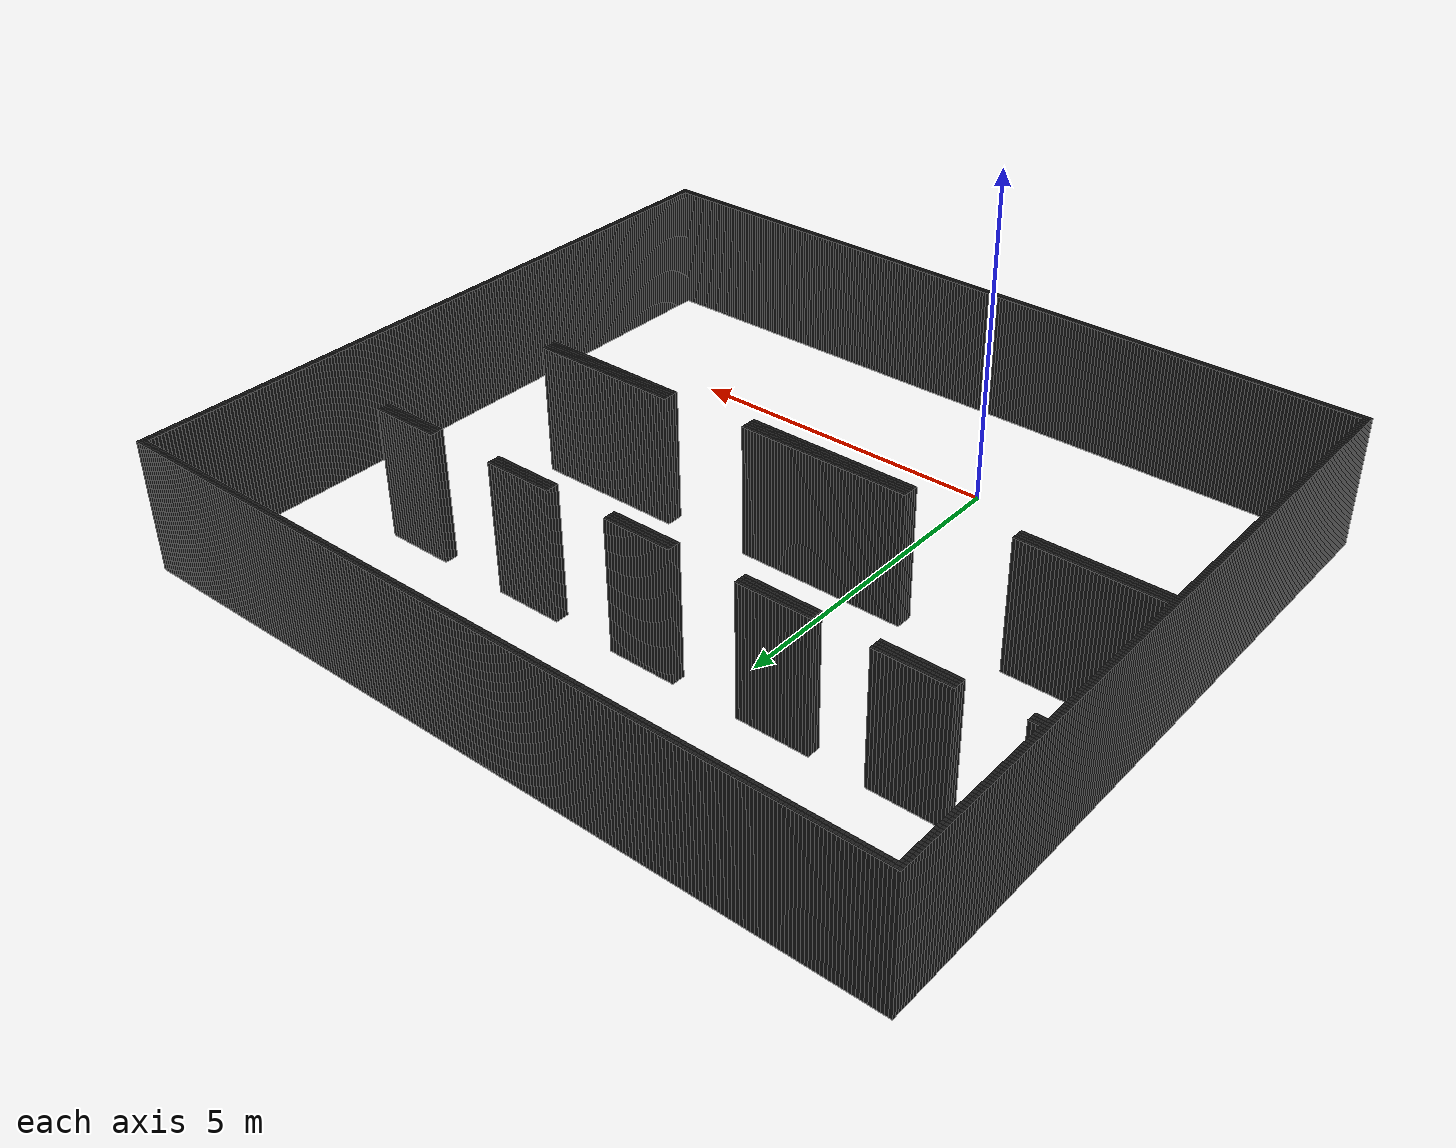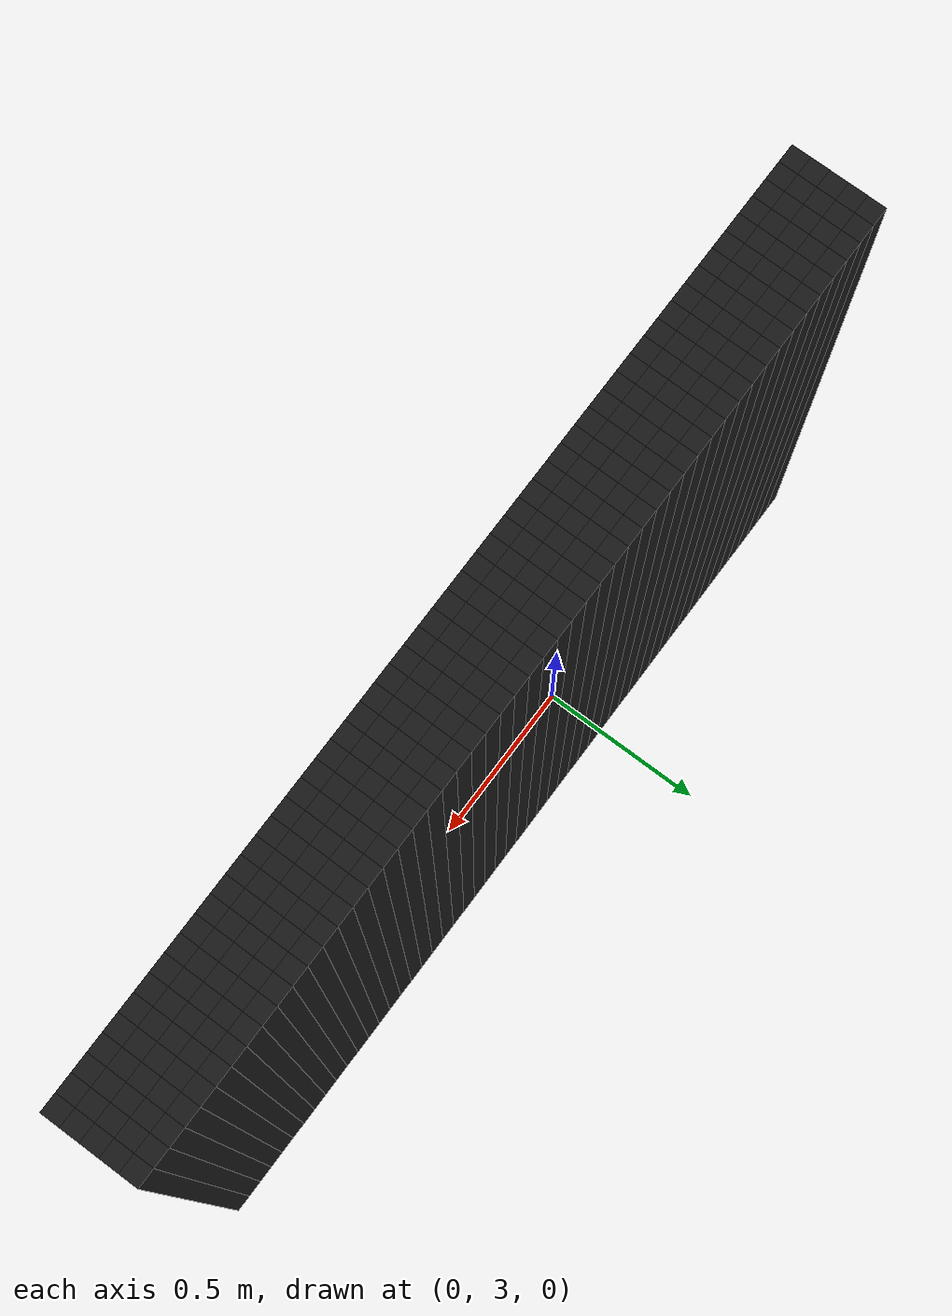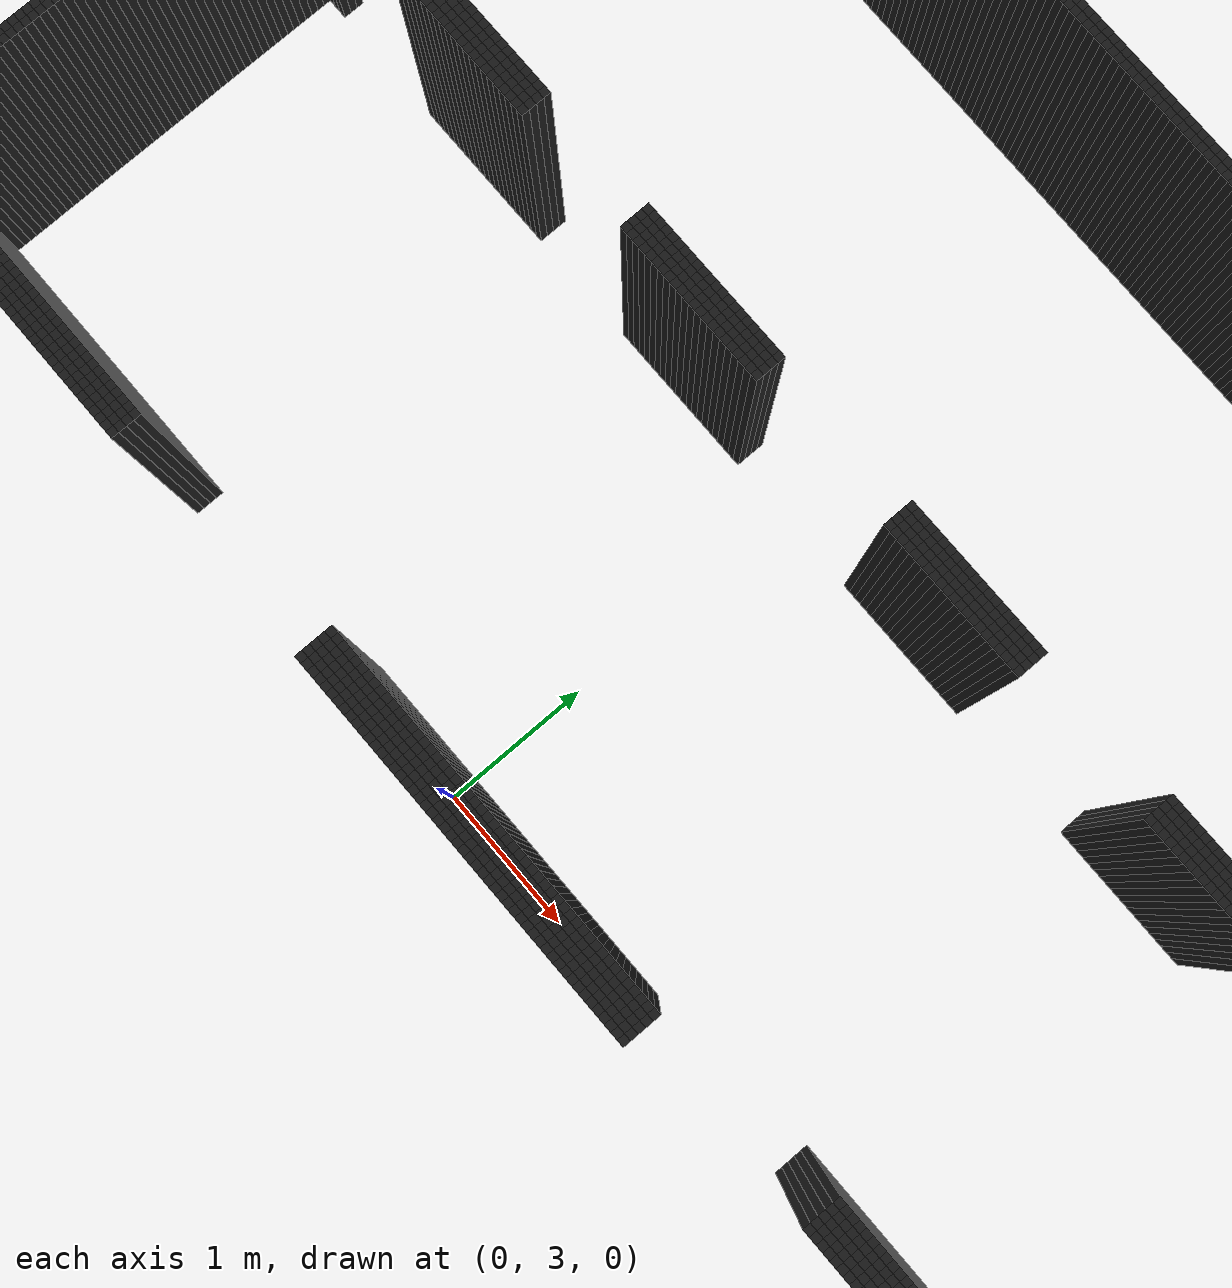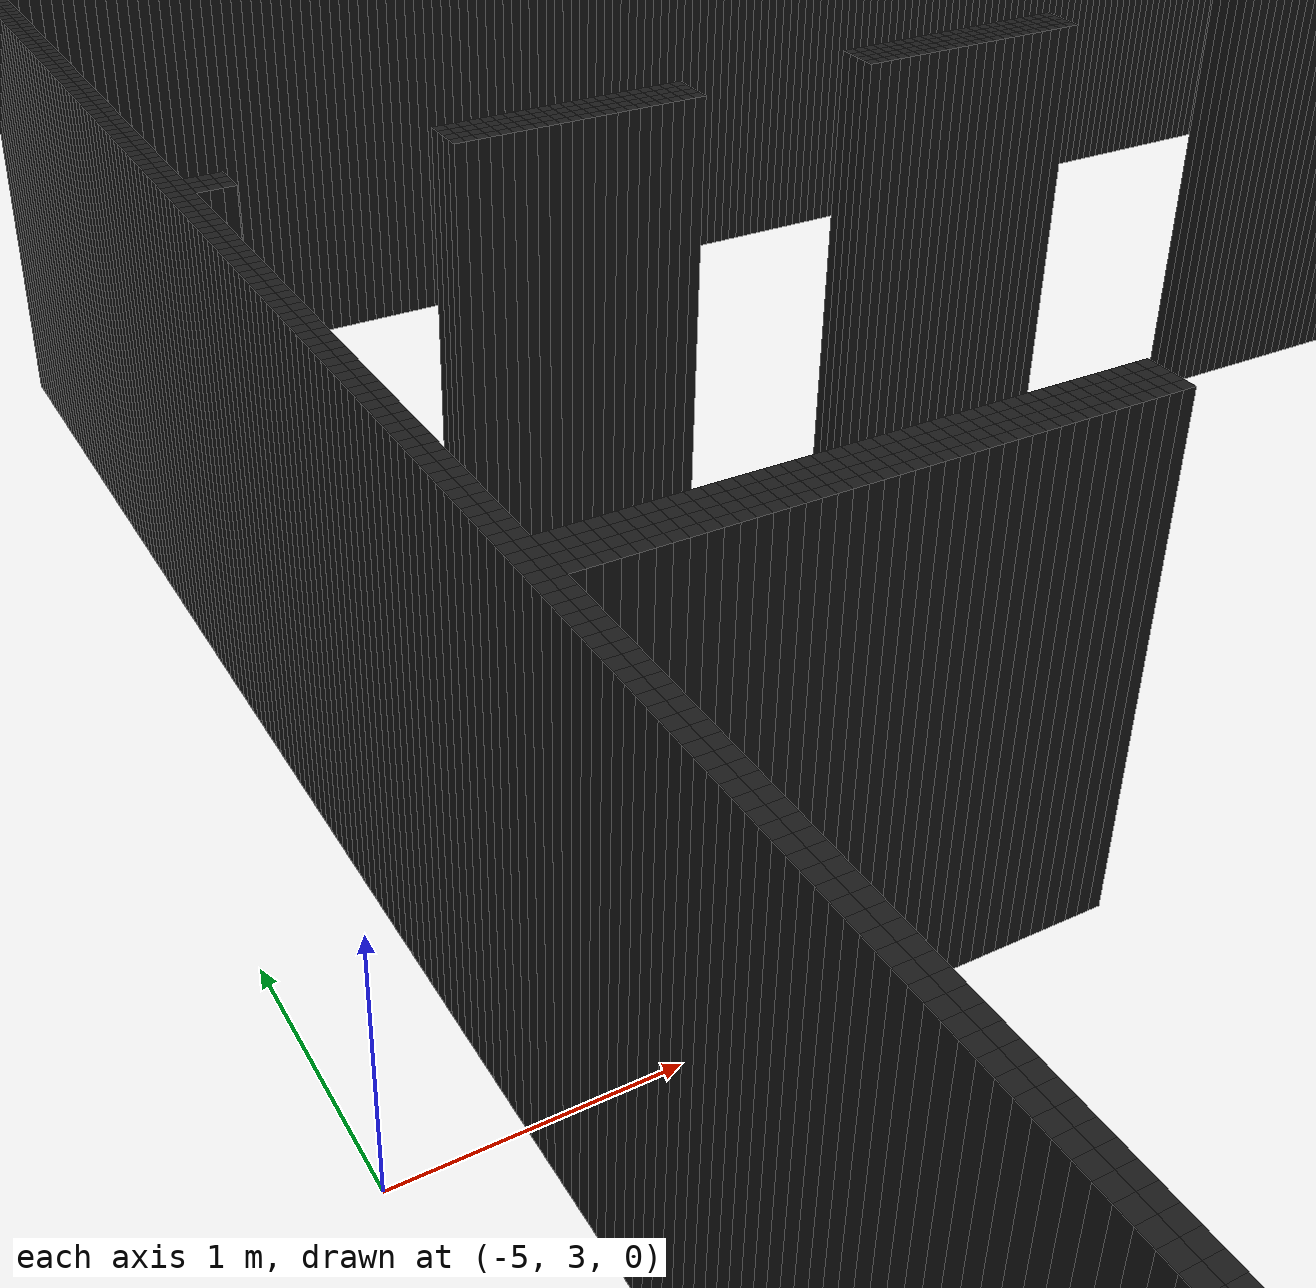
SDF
<?xml version='1.0' encoding='utf-8'?>
<sdf version="1.6"><model name="obstacle_0_0"><pose>-4.51 8.350000000000001 1.0 0 0 0</pose><static>true</static><link name="box_link"><collision name="box_collision"><geometry><box><size>0.05 0.05 2.0</size></box></geometry></collision><visual name="box_visual"><geometry><box><size>0.05 0.05 2.0</size></box></geometry><material><ambient>0 0 0 1</ambient><diffuse>0.1 0.1 0.1 1</diffuse></material></visual></link></model><model name="obstacle_1_0"><pose>-4.46 8.350000000000001 1.0 0 0 0</pose><static>true</static><link name="box_link"><collision name="box_collision"><geometry><box><size>0.05 0.05 2.0</size></box></geometry></collision><visual name="box_visual"><geometry><box><size>0.05 0.05 2.0</size></box></geometry><material><ambient>0 0 0 1</ambient><diffuse>0.1 0.1 0.1 1</diffuse></material></visual></link></model><model name="obstacle_2_0"><pose>-4.41 8.350000000000001 1.0 0 0 0</pose><static>true</static><link name="box_link"><collision name="box_collision"><geometry><box><size>0.05 0.05 2.0</size></box></geometry></collision><visual name="box_visual"><geometry><box><size>0.05 0.05 2.0</size></box></geometry><material><ambient>0 0 0 1</ambient><diffuse>0.1 0.1 0.1 1</diffuse></material></visual></link></model><model name="obstacle_3_0"><pose>-4.359999999999999 8.350000000000001 1.0 0 0 0</pose><static>true</static><link name="box_link"><collision name="box_collision"><geometry><box><size>0.05 0.05 2.0</size></box></geometry></collision><visual name="box_visual"><geometry><box><size>0.05 0.05 2.0</size></box></geometry><material><ambient>0 0 0 1</ambient><diffuse>0.1 0.1 0.1 1</diffuse></material></visual></link></model><model name="obstacle_4_0"><pose>-4.31 8.350000000000001 1.0 0 0 0</pose><static>true</static><link name="box_link"><collision name="box_collision"><geometry><box><size>0.05 0.05 2.0</size></box></geometry></collision><visual name="box_visual"><geometry><box><size>0.05 0.05 2.0</size></box></geometry><material><ambient>0 0 0 1</ambient><diffuse>0.1 0.1 0.1 1</diffuse></material></visual></link></model><model name="obstacle_5_0"><pose>-4.26 8.350000000000001 1.0 0 0 0</pose><static>true</static><link name="box_link"><collision name="box_collision"><geometry><box><size>0.05 0.05 2.0</size></box></geometry></collision><visual name="box_visual"><geometry><box><size>0.05 0.05 2.0</size></box></geometry><material><ambient>0 0 0 1</ambient><diffuse>0.1 0.1 0.1 1</diffuse></material></visual></link></model><model name="obstacle_6_0"><pose>-4.21 8.350000000000001 1.0 0 0 0</pose><static>true</static><link name="box_link"><collision name="box_collision"><geometry><box><size>0.05 0.05 2.0</size></box></geometry></collision><visual name="box_visual"><geometry><box><size>0.05 0.05 2.0</size></box></geometry><material><ambient>0 0 0 1</ambient><diffuse>0.1 0.1 0.1 1</diffuse></material></visual></link></model><model name="obstacle_7_0"><pose>-4.16 8.350000000000001 1.0 0 0 0</pose><static>true</static><link name="box_link"><collision name="box_collision"><geometry><box><size>0.05 0.05 2.0</size></box></geometry></collision><visual name="box_visual"><geometry><box><size>0.05 0.05 2.0</size></box></geometry><material><ambient>0 0 0 1</ambient><diffuse>0.1 0.1 0.1 1</diffuse></material></visual></link></model><model name="obstacle_8_0"><pose>-4.109999999999999 8.350000000000001 1.0 0 0 0</pose><static>true</static><link name="box_link"><collision name="box_collision"><geometry><box><size>0.05 0.05 2.0</size></box></geometry></collision><visual name="box_visual"><geometry><box><size>0.05 0.05 2.0</size></box></geometry><material><ambient>0 0 0 1</ambient><diffuse>0.1 0.1 0.1 1</diffuse></material></visual></link></model><model name="obstacle_9_0"><pose>-4.06 8.350000000000001 1.0 0 0 0</pose><static>true</static><link name="box_link"><collision name="box_collision"><geometry><box><size>0.05 0.05 2.0</size></box></geometry></collision><visual name="box_visual"><geometry><box><size>0.05 0.05 2.0</size></box></geometry><material><ambient>0 0 0 1</ambient><diffuse>0.1 0.1 0.1 1</diffuse></material></visual></link></model><model name="obstacle_10_0"><pose>-4.01 8.350000000000001 1.0 0 0 0</pose><static>true</static><link name="box_link"><collision name="box_collision"><geometry><box><size>0.05 0.05 2.0</size></box></geometry></collision><visual name="box_visual"><geometry><box><size>0.05 0.05 2.0</size></box></geometry><material><ambient>0 0 0 1</ambient><diffuse>0.1 0.1 0.1 1</diffuse></material></visual></link></model><model name="obstacle_11_0"><pose>-3.96 8.350000000000001 1.0 0 0 0</pose><static>true</static><link name="box_link"><collision name="box_collision"><geometry><box><size>0.05 0.05 2.0</size></box></geometry></collision><visual name="box_visual"><geometry><box><size>0.05 0.05 2.0</size></box></geometry><material><ambient>0 0 0 1</ambient><diffuse>0.1 0.1 0.1 1</diffuse></material></visual></link></model><model name="obstacle_12_0"><pose>-3.9099999999999997 8.350000000000001 1.0 0 0 0</pose><static>true</static><link name="box_link"><collision name="box_collision"><geometry><box><size>0.05 0.05 2.0</size></box></geometry></collision><visual name="box_visual"><geometry><box><size>0.05 0.05 2.0</size></box></geometry><material><ambient>0 0 0 1</ambient><diffuse>0.1 0.1 0.1 1</diffuse></material></visual></link></model><model name="obstacle_13_0"><pose>-3.86 8.350000000000001 1.0 0 0 0</pose><static>true</static><link name="box_link"><collision name="box_collision"><geometry><box><size>0.05 0.05 2.0</size></box></geometry></collision><visual name="box_visual"><geometry><box><size>0.05 0.05 2.0</size></box></geometry><material><ambient>0 0 0 1</ambient><diffuse>0.1 0.1 0.1 1</diffuse></material></visual></link></model><model name="obstacle_14_0"><pose>-3.8099999999999996 8.350000000000001 1.0 0 0 0</pose><static>true</static><link name="box_link"><collision name="box_collision"><geometry><box><size>0.05 0.05 2.0</size></box></geometry></collision><visual name="box_visual"><geometry><box><size>0.05 0.05 2.0</size></box></geometry><material><ambient>0 0 0 1</ambient><diffuse>0.1 0.1 0.1 1</diffuse></material></visual></link></model><model name="obstacle_15_0"><pose>-3.76 8.350000000000001 1.0 0 0 0</pose><static>true</static><link name="box_link"><collision name="box_collision"><geometry><box><size>0.05 0.05 2.0</size></box></geometry></collision><visual name="box_visual"><geometry><box><size>0.05 0.05 2.0</size></box></geometry><material><ambient>0 0 0 1</ambient><diffuse>0.1 0.1 0.1 1</diffuse></material></visual></link></model><model name="obstacle_16_0"><pose>-3.71 8.350000000000001 1.0 0 0 0</pose><static>true</static><link name="box_link"><collision name="box_collision"><geometry><box><size>0.05 0.05 2.0</size></box></geometry></collision><visual name="box_visual"><geometry><box><size>0.05 0.05 2.0</size></box></geometry><material><ambient>0 0 0 1</ambient><diffuse>0.1 0.1 0.1 1</diffuse></material></visual></link></model><model name="obstacle_17_0"><pose>-3.6599999999999997 8.350000000000001 1.0 0 0 0</pose><static>true</static><link name="box_link"><collision name="box_collision"><geometry><box><size>0.05 0.05 2.0</size></box></geometry></collision><visual name="box_visual"><geometry><box><size>0.05 0.05 2.0</size></box></geometry><material><ambient>0 0 0 1</ambient><diffuse>0.1 0.1 0.1 1</diffuse></material></visual></link></model><model name="obstacle_18_0"><pose>-3.61 8.350000000000001 1.0 0 0 0</pose><static>true</static><link name="box_link"><collision name="box_collision"><geometry><box><size>0.05 0.05 2.0</size></box></geometry></collision><visual name="box_visual"><geometry><box><size>0.05 0.05 2.0</size></box></geometry><material><ambient>0 0 0 1</ambient><diffuse>0.1 0.1 0.1 1</diffuse></material></visual></link></model><model name="obstacle_19_0"><pose>-3.5599999999999996 8.350000000000001 1.0 0 0 0</pose><static>true</static><link name="box_link"><collision name="box_collision"><geometry><box><size>0.05 0.05 2.0</size></box></geometry></collision><visual name="box_visual"><geometry><box><size>0.05 0.05 2.0</size></box></geometry><material><ambient>0 0 0 1</ambient><diffuse>0.1 0.1 0.1 1</diffuse></material></visual></link></model><model name="obstacle_20_0"><pose>-3.51 8.350000000000001 1.0 0 0 0</pose><static>true</static><link name="box_link"><collision name="box_collision"><geometry><box><size>0.05 0.05 2.0</size></box></geometry></collision><visual name="box_visual"><geometry><box><size>0.05 0.05 2.0</size></box></geometry><material><ambient>0 0 0 1</ambient><diffuse>0.1 0.1 0.1 1</diffuse></material></visual></link></model><model name="obstacle_21_0"><pose>-3.46 8.350000000000001 1.0 0 0 0</pose><static>true</static><link name="box_link"><collision name="box_collision"><geometry><box><size>0.05 0.05 2.0</size></box></geometry></collision><visual name="box_visual"><geometry><box><size>0.05 0.05 2.0</size></box></geometry><material><ambient>0 0 0 1</ambient><diffuse>0.1 0.1 0.1 1</diffuse></material></visual></link></model><model name="obstacle_22_0"><pose>-3.4099999999999997 8.350000000000001 1.0 0 0 0</pose><static>true</static><link name="box_link"><collision name="box_collision"><geometry><box><size>0.05 0.05 2.0</size></box></geometry></collision><visual name="box_visual"><geometry><box><size>0.05 0.05 2.0</size></box></geometry><material><ambient>0 0 0 1</ambient><diffuse>0.1 0.1 0.1 1</diffuse></material></visual></link></model><model name="obstacle_23_0"><pose>-3.3599999999999994 8.350000000000001 1.0 0 0 0</pose><static>true</static><link name="box_link"><collision name="box_collision"><geometry><box><size>0.05 0.05 2.0</size></box></geometry></collision><visual name="box_visual"><geometry><box><size>0.05 0.05 2.0</size></box></geometry><material><ambient>0 0 0 1</ambient><diffuse>0.1 0.1 0.1 1</diffuse></material></visual></link></model><model name="obstacle_24_0"><pose>-3.3099999999999996 8.350000000000001 1.0 0 0 0</pose><static>true</static><link name="box_link"><collision name="box_collision"><geometry><box><size>0.05 0.05 2.0</size></box></geometry></collision><visual name="box_visual"><geometry><box><size>0.05 0.05 2.0</size></box></geometry><material><ambient>0 0 0 1</ambient><diffuse>0.1 0.1 0.1 1</diffuse></material></visual></link></model><model name="obstacle_25_0"><pose>-3.26 8.350000000000001 1.0 0 0 0</pose><static>true</static><link name="box_link"><collision name="box_collision"><geometry><box><size>0.05 0.05 2.0</size></box></geometry></collision><visual name="box_visual"><geometry><box><size>0.05 0.05 2.0</size></box></geometry><material><ambient>0 0 0 1</ambient><diffuse>0.1 0.1 0.1 1</diffuse></material></visual></link></model><model name="obstacle_26_0"><pose>-3.21 8.350000000000001 1.0 0 0 0</pose><static>true</static><link name="box_link"><collision name="box_collision"><geometry><box><size>0.05 0.05 2.0</size></box></geometry></collision><visual name="box_visual"><geometry><box><size>0.05 0.05 2.0</size></box></geometry><material><ambient>0 0 0 1</ambient><diffuse>0.1 0.1 0.1 1</diffuse></material></visual></link></model><model name="obstacle_27_0"><pose>-3.1599999999999997 8.350000000000001 1.0 0 0 0</pose><static>true</static><link name="box_link"><collision name="box_collision"><geometry><box><size>0.05 0.05 2.0</size></box></geometry></collision><visual name="box_visual"><geometry><box><size>0.05 0.05 2.0</size></box></geometry><material><ambient>0 0 0 1</ambient><diffuse>0.1 0.1 0.1 1</diffuse></material></visual></link></model><model name="obstacle_28_0"><pose>-3.1099999999999994 8.350000000000001 1.0 0 0 0</pose><static>true</static><link name="box_link"><collision name="box_collision"><geometry><box><size>0.05 0.05 2.0</size></box></geometry></collision><visual name="box_visual"><geometry><box><size>0.05 0.05 2.0</size></box></geometry><material><ambient>0 0 0 1</ambient><diffuse>0.1 0.1 0.1 1</diffuse></material></visual></link></model><model name="obstacle_29_0"><pose>-3.0599999999999996 8.350000000000001 1.0 0 0 0</pose><static>true</static><link name="box_link"><collision name="box_collision"><geometry><box><size>0.05 0.05 2.0</size></box></geometry></collision><visual name="box_visual"><geometry><box><size>0.05 0.05 2.0</size></box></geometry><material><ambient>0 0 0 1</ambient><diffuse>0.1 0.1 0.1 1</diffuse></material></visual></link></model><model name="obstacle_30_0"><pose>-3.01 8.350000000000001 1.0 0 0 0</pose><static>true</static><link name="box_link"><collision name="box_collision"><geometry><box><size>0.05 0.05 2.0</size></box></geometry></collision><visual name="box_visual"><geometry><box><size>0.05 0.05 2.0</size></box></geometry><material><ambient>0 0 0 1</ambient><diffuse>0.1 0.1 0.1 1</diffuse></material></visual></link></model><model name="obstacle_31_0"><pose>-2.96 8.350000000000001 1.0 0 0 0</pose><static>true</static><link name="box_link"><collision name="box_collision"><geometry><box><size>0.05 0.05 2.0</size></box></geometry></collision><visual name="box_visual"><geometry><box><size>0.05 0.05 2.0</size></box></geometry><material><ambient>0 0 0 1</ambient><diffuse>0.1 0.1 0.1 1</diffuse></material></visual></link></model><model name="obstacle_32_0"><pose>-2.9099999999999997 8.350000000000001 1.0 0 0 0</pose><static>true</static><link name="box_link"><collision name="box_collision"><geometry><box><size>0.05 0.05 2.0</size></box></geometry></collision><visual name="box_visual"><geometry><box><size>0.05 0.05 2.0</size></box></geometry><material><ambient>0 0 0 1</ambient><diffuse>0.1 0.1 0.1 1</diffuse></material></visual></link></model><model name="obstacle_33_0"><pose>-2.8599999999999994 8.350000000000001 1.0 0 0 0</pose><static>true</static><link name="box_link"><collision name="box_collision"><geometry><box><size>0.05 0.05 2.0</size></box></geometry></collision><visual name="box_visual"><geometry><box><size>0.05 0.05 2.0</size></box></geometry><material><ambient>0 0 0 1</ambient><diffuse>0.1 0.1 0.1 1</diffuse></material></visual></link></model><model name="obstacle_34_0"><pose>-2.8099999999999996 8.350000000000001 1.0 0 0 0</pose><static>true</static><link name="box_link"><collision name="box_collision"><geometry><box><size>0.05 0.05 2.0</size></box></geometry></collision><visual name="box_visual"><geometry><box><size>0.05 0.05 2.0</size></box></geometry><material><ambient>0 0 0 1</ambient><diffuse>0.1 0.1 0.1 1</diffuse></material></visual></link></model><model name="obstacle_35_0"><pose>-2.76 8.350000000000001 1.0 0 0 0</pose><static>true</static><link name="box_link"><collision name="box_collision"><geometry><box><size>0.05 0.05 2.0</size></box></geometry></collision><visual name="box_visual"><geometry><box><size>0.05 0.05 2.0</size></box></geometry><material><ambient>0 0 0 1</ambient><diffuse>0.1 0.1 0.1 1</diffuse></material></visual></link></model><model name="obstacle_36_0"><pose>-2.71 8.350000000000001 1.0 0 0 0</pose><static>true</static><link name="box_link"><collision name="box_collision"><geometry><box><size>0.05 0.05 2.0</size></box></geometry></collision><visual name="box_visual"><geometry><box><size>0.05 0.05 2.0</size></box></geometry><material><ambient>0 0 0 1</ambient><diffuse>0.1 0.1 0.1 1</diffuse></material></visual></link></model><model name="obstacle_37_0"><pose>-2.6599999999999997 8.350000000000001 1.0 0 0 0</pose><static>true</static><link name="box_link"><collision name="box_collision"><geometry><box><size>0.05 0.05 2.0</size></box></geometry></collision><visual name="box_visual"><geometry><box><size>0.05 0.05 2.0</size></box></geometry><material><ambient>0 0 0 1</ambient><diffuse>0.1 0.1 0.1 1</diffuse></material></visual></link></model><model name="obstacle_38_0"><pose>-2.6099999999999994 8.350000000000001 1.0 0 0 0</pose><static>true</static><link name="box_link"><collision name="box_collision"><geometry><box><size>0.05 0.05 2.0</size></box></geometry></collision><visual name="box_visual"><geometry><box><size>0.05 0.05 2.0</size></box></geometry><material><ambient>0 0 0 1</ambient><diffuse>0.1 0.1 0.1 1</diffuse></material></visual></link></model><model name="obstacle_39_0"><pose>-2.5599999999999996 8.350000000000001 1.0 0 0 0</pose><static>true</static><link name="box_link"><collision name="box_collision"><geometry><box><size>0.05 0.05 2.0</size></box></geometry></collision><visual name="box_visual"><geometry><box><size>0.05 0.05 2.0</size></box></geometry><material><ambient>0 0 0 1</ambient><diffuse>0.1 0.1 0.1 1</diffuse></material></visual></link></model><model name="obstacle_40_0"><pose>-2.51 8.350000000000001 1.0 0 0 0</pose><static>true</static><link name="box_link"><collision name="box_collision"><geometry><box><size>0.05 0.05 2.0</size></box></geometry></collision><visual name="box_visual"><geometry><box><size>0.05 0.05 2.0</size></box></geometry><material><ambient>0 0 0 1</ambient><diffuse>0.1 0.1 0.1 1</diffuse></material></visual></link></model><model name="obstacle_41_0"><pose>-2.4599999999999995 8.350000000000001 1.0 0 0 0</pose><static>true</static><link name="box_link"><collision name="box_collision"><geometry><box><size>0.05 0.05 2.0</size></box></geometry></collision><visual name="box_visual"><geometry><box><size>0.05 0.05 2.0</size></box></geometry><material><ambient>0 0 0 1</ambient><diffuse>0.1 0.1 0.1 1</diffuse></material></visual></link></model><model name="obstacle_42_0"><pose>-2.4099999999999997 8.350000000000001 1.0 0 0 0</pose><static>true</static><link name="box_link"><collision name="box_collision"><geometry><box><size>0.05 0.05 2.0</size></box></geometry></collision><visual name="box_visual"><geometry><box><size>0.05 0.05 2.0</size></box></geometry><material><ambient>0 0 0 1</ambient><diffuse>0.1 0.1 0.1 1</diffuse></material></visual></link></model><model name="obstacle_43_0"><pose>-2.36 8.350000000000001 1.0 0 0 0</pose><static>true</static><link name="box_link"><collision name="box_collision"><geometry><box><size>0.05 0.05 2.0</size></box></geometry></collision><visual name="box_visual"><geometry><box><size>0.05 0.05 2.0</size></box></geometry><material><ambient>0 0 0 1</ambient><diffuse>0.1 0.1 0.1 1</diffuse></material></visual></link></model><model name="obstacle_44_0"><pose>-2.3099999999999996 8.350000000000001 1.0 0 0 0</pose><static>true</static><link name="box_link"><collision name="box_collision"><geometry><box><size>0.05 0.05 2.0</size></box></geometry></collision><visual name="box_visual"><geometry><box><size>0.05 0.05 2.0</size></box></geometry><material><ambient>0 0 0 1</ambient><diffuse>0.1 0.1 0.1 1</diffuse></material></visual></link></model><model name="obstacle_45_0"><pose>-2.26 8.350000000000001 1.0 0 0 0</pose><static>true</static><link name="box_link"><collision name="box_collision"><geometry><box><size>0.05 0.05 2.0</size></box></geometry></collision><visual name="box_visual"><geometry><box><size>0.05 0.05 2.0</size></box></geometry><material><ambient>0 0 0 1</ambient><diffuse>0.1 0.1 0.1 1</diffuse></material></visual></link></model><model name="obstacle_46_0"><pose>-2.2099999999999995 8.350000000000001 1.0 0 0 0</pose><static>true</static><link name="box_link"><collision name="box_collision"><geometry><box><size>0.05 0.05 2.0</size></box></geometry></collision><visual name="box_visual"><geometry><box><size>0.05 0.05 2.0</size></box></geometry><material><ambient>0 0 0 1</ambient><diffuse>0.1 0.1 0.1 1</diffuse></material></visual></link></model><model name="obstacle_47_0"><pose>-2.1599999999999997 8.350000000000001 1.0 0 0 0</pose><static>true</static><link name="box_link"><collision name="box_collision"><geometry><box><size>0.05 0.05 2.0</size></box></geometry></collision><visual name="box_visual"><geometry><box><size>0.05 0.05 2.0</size></box></geometry><material><ambient>0 0 0 1</ambient><diffuse>0.1 0.1 0.1 1</diffuse></material></visual></link></model><model name="obstacle_48_0"><pose>-2.1099999999999994 8.350000000000001 1.0 0 0 0</pose><static>true</static><link name="box_link"><collision name="box_collision"><geometry><box><size>0.05 0.05 2.0</size></box></geometry></collision><visual name="box_visual"><geometry><box><size>0.05 0.05 2.0</size></box></geometry><material><ambient>0 0 0 1</ambient><diffuse>0.1 0.1 0.1 1</diffuse></material></visual></link></model><model name="obstacle_49_0"><pose>-2.0599999999999996 8.350000000000001 1.0 0 0 0</pose><static>true</static><link name="box_link"><collision name="box_collision"><geometry><box><size>0.05 0.05 2.0</size></box></geometry></collision><visual name="box_visual"><geometry><box><size>0.05 0.05 2.0</size></box></geometry><material><ambient>0 0 0 1</ambient><diffuse>0.1 0.1 0.1 1</diffuse></material></visual></link></model><model name="obstacle_50_0"><pose>-2.01 8.350000000000001 1.0 0 0 0</pose><static>true</static><link name="box_link"><collision name="box_collision"><geometry><box><size>0.05 0.05 2.0</size></box></geometry></collision><visual name="box_visual"><geometry><box><size>0.05 0.05 2.0</size></box></geometry><material><ambient>0 0 0 1</ambient><diffuse>0.1 0.1 0.1 1</diffuse></material></visual></link></model><model name="obstacle_51_0"><pose>-1.9599999999999995 8.350000000000001 1.0 0 0 0</pose><static>true</static><link name="box_link"><collision name="box_collision"><geometry><box><size>0.05 0.05 2.0</size></box></geometry></collision><visual name="box_visual"><geometry><box><size>0.05 0.05 2.0</size></box></geometry><material><ambient>0 0 0 1</ambient><diffuse>0.1 0.1 0.1 1</diffuse></material></visual></link></model><model name="obstacle_52_0"><pose>-1.9099999999999997 8.350000000000001 1.0 0 0 0</pose><static>true</static><link name="box_link"><collision name="box_collision"><geometry><box><size>0.05 0.05 2.0</size></box></geometry></collision><visual name="box_visual"><geometry><box><size>0.05 0.05 2.0</size></box></geometry><material><ambient>0 0 0 1</ambient><diffuse>0.1 0.1 0.1 1</diffuse></material></visual></link></model><model name="obstacle_53_0"><pose>-1.8599999999999994 8.350000000000001 1.0 0 0 0</pose><static>true</static><link name="box_link"><collision name="box_collision"><geometry><box><size>0.05 0.05 2.0</size></box></geometry></collision><visual name="box_visual"><geometry><box><size>0.05 0.05 2.0</size></box></geometry><material><ambient>0 0 0 1</ambient><diffuse>0.1 0.1 0.1 1</diffuse></material></visual></link></model><model name="obstacle_54_0"><pose>-1.8099999999999996 8.350000000000001 1.0 0 0 0</pose><static>true</static><link name="box_link"><collision name="box_collision"><geometry><box><size>0.05 0.05 2.0</size></box></geometry></collision><visual name="box_visual"><geometry><box><size>0.05 0.05 2.0</size></box></geometry><material><ambient>0 0 0 1</ambient><diffuse>0.1 0.1 0.1 1</diffuse></material></visual></link></model><model name="obstacle_55_0"><pose>-1.7599999999999998 8.350000000000001 1.0 0 0 0</pose><static>true</static><link name="box_link"><collision name="box_collision"><geometry><box><size>0.05 0.05 2.0</size></box></geometry></collision><visual name="box_visual"><geometry><box><size>0.05 0.05 2.0</size></box></geometry><material><ambient>0 0 0 1</ambient><diffuse>0.1 0.1 0.1 1</diffuse></material></visual></link></model><model name="obstacle_56_0"><pose>-1.7099999999999995 8.350000000000001 1.0 0 0 0</pose><static>true</static><link name="box_link"><collision name="box_collision"><geometry><box><size>0.05 0.05 2.0</size></box></geometry></collision><visual name="box_visual"><geometry><box><size>0.05 0.05 2.0</size></box></geometry><material><ambient>0 0 0 1</ambient><diffuse>0.1 0.1 0.1 1</diffuse></material></visual></link></model><model name="obstacle_57_0"><pose>-1.6599999999999997 8.350000000000001 1.0 0 0 0</pose><static>true</static><link name="box_link"><collision name="box_collision"><geometry><box><size>0.05 0.05 2.0</size></box></geometry></collision><visual name="box_visual"><geometry><box><size>0.05 0.05 2.0</size></box></geometry><material><ambient>0 0 0 1</ambient><diffuse>0.1 0.1 0.1 1</diffuse></material></visual></link></model><model name="obstacle_58_0"><pose>-1.6099999999999994 8.350000000000001 1.0 0 0 0</pose><static>true</static><link name="box_link"><collision name="box_collision"><geometry><box><size>0.05 0.05 2.0</size></box></geometry></collision><visual name="box_visual"><geometry><box><size>0.05 0.05 2.0</size></box></geometry><material><ambient>0 0 0 1</ambient><diffuse>0.1 0.1 0.1 1</diffuse></material></visual></link></model><model name="obstacle_59_0"><pose>-1.5599999999999996 8.350000000000001 1.0 0 0 0</pose><static>true</static><link name="box_link"><collision name="box_collision"><geometry><box><size>0.05 0.05 2.0</size></box></geometry></collision><visual name="box_visual"><geometry><box><size>0.05 0.05 2.0</size></box></geometry><material><ambient>0 0 0 1</ambient><diffuse>0.1 0.1 0.1 1</diffuse></material></visual></link></model><model name="obstacle_60_0"><pose>-1.5099999999999998 8.350000000000001 1.0 0 0 0</pose><static>true</static><link name="box_link"><collision name="box_collision"><geometry><box><size>0.05 0.05 2.0</size></box></geometry></collision><visual name="box_visual"><geometry><box><size>0.05 0.05 2.0</size></box></geometry><material><ambient>0 0 0 1</ambient><diffuse>0.1 0.1 0.1 1</diffuse></material></visual></link></model><model name="obstacle_61_0"><pose>-1.4599999999999995 8.350000000000001 1.0 0 0 0</pose><static>true</static><link name="box_link"><collision name="box_collision"><geometry><box><size>0.05 0.05 2.0</size></box></geometry></collision><visual name="box_visual"><geometry><box><size>0.05 0.05 2.0</size></box></geometry><material><ambient>0 0 0 1</ambient><diffuse>0.1 0.1 0.1 1</diffuse></material></visual></link></model><model name="obstacle_62_0"><pose>-1.4099999999999997 8.350000000000001 1.0 0 0 0</pose><static>true</static><link name="box_link"><collision name="box_collision"><geometry><box><size>0.05 0.05 2.0</size></box></geometry></collision><visual name="box_visual"><geometry><box><size>0.05 0.05 2.0</size></box></geometry><material><ambient>0 0 0 1</ambient><diffuse>0.1 0.1 0.1 1</diffuse></material></visual></link></model><model name="obstacle_63_0"><pose>-1.3599999999999994 8.350000000000001 1.0 0 0 0</pose><static>true</static><link name="box_link"><collision name="box_collision"><geometry><box><size>0.05 0.05 2.0</size></box></geometry></collision><visual name="box_visual"><geometry><box><size>0.05 0.05 2.0</size></box></geometry><material><ambient>0 0 0 1</ambient><diffuse>0.1 0.1 0.1 1</diffuse></material></visual></link></model><model name="obstacle_64_0"><pose>-1.3099999999999996 8.350000000000001 1.0 0 0 0</pose><static>true</static><link name="box_link"><collision name="box_collision"><geometry><box><size>0.05 0.05 2.0</size></box></geometry></collision><visual name="box_visual"><geometry><box><size>0.05 0.05 2.0</size></box></geometry><material><ambient>0 0 0 1</ambient><diffuse>0.1 0.1 0.1 1</diffuse></material></visual></link></model><model name="obstacle_65_0"><pose>-1.2599999999999998 8.350000000000001 1.0 0 0 0</pose><static>true</static><link name="box_link"><collision name="box_collision"><geometry><box><size>0.05 0.05 2.0</size></box></geometry></collision><visual name="box_visual"><geometry><box><size>0.05 0.05 2.0</size></box></geometry><material><ambient>0 0 0 1</ambient><diffuse>0.1 0.1 0.1 1</diffuse></material></visual></link></model><model name="obstacle_66_0"><pose>-1.2099999999999995 8.350000000000001 1.0 0 0 0</pose><static>true</static><link name="box_link"><collision name="box_collision"><geometry><box><size>0.05 0.05 2.0</size></box></geometry></collision><visual name="box_visual"><geometry><box><size>0.05 0.05 2.0</size></box></geometry><material><ambient>0 0 0 1</ambient><diffuse>0.1 0.1 0.1 1</diffuse></material></visual></link></model><model name="obstacle_67_0"><pose>-1.1599999999999997 8.350000000000001 1.0 0 0 0</pose><static>true</static><link name="box_link"><collision name="box_collision"><geometry><box><size>0.05 0.05 2.0</size></box></geometry></collision><visual name="box_visual"><geometry><box><size>0.05 0.05 2.0</size></box></geometry><material><ambient>0 0 0 1</ambient><diffuse>0.1 0.1 0.1 1</diffuse></material></visual></link></model><model name="obstacle_68_0"><pose>-1.1099999999999994 8.350000000000001 1.0 0 0 0</pose><static>true</static><link name="box_link"><collision name="box_collision"><geometry><box><size>0.05 0.05 2.0</size></box></geometry></collision><visual name="box_visual"><geometry><box><size>0.05 0.05 2.0</size></box></geometry><material><ambient>0 0 0 1</ambient><diffuse>0.1 0.1 0.1 1</diffuse></material></visual></link></model><model name="obstacle_69_0"><pose>-1.0599999999999996 8.350000000000001 1.0 0 0 0</pose><static>true</static><link name="box_link"><collision name="box_collision"><geometry><box><size>0.05 0.05 2.0</size></box></geometry></collision><visual name="box_visual"><geometry><box><size>0.05 0.05 2.0</size></box></geometry><material><ambient>0 0 0 1</ambient><diffuse>0.1 0.1 0.1 1</diffuse></material></visual></link></model><model name="obstacle_70_0"><pose>-1.0099999999999998 8.350000000000001 1.0 0 0 0</pose><static>true</static><link name="box_link"><collision name="box_collision"><geometry><box><size>0.05 0.05 2.0</size></box></geometry></collision><visual name="box_visual"><geometry><box><size>0.05 0.05 2.0</size></box></geometry><material><ambient>0 0 0 1</ambient><diffuse>0.1 0.1 0.1 1</diffuse></material></visual></link></model><model name="obstacle_71_0"><pose>-0.9599999999999995 8.350000000000001 1.0 0 0 0</pose><static>true</static><link name="box_link"><collision name="box_collision"><geometry><box><size>0.05 0.05 2.0</size></box></geometry></collision><visual name="box_visual"><geometry><box><size>0.05 0.05 2.0</size></box></geometry><material><ambient>0 0 0 1</ambient><diffuse>0.1 0.1 0.1 1</diffuse></material></visual></link></model><model name="obstacle_72_0"><pose>-0.9099999999999997 8.350000000000001 1.0 0 0 0</pose><static>true</static><link name="box_link"><collision name="box_collision"><geometry><box><size>0.05 0.05 2.0</size></box></geometry></collision><visual name="box_visual"><geometry><box><size>0.05 0.05 2.0</size></box></geometry><material><ambient>0 0 0 1</ambient><diffuse>0.1 0.1 0.1 1</diffuse></material></visual></link></model><model name="obstacle_73_0"><pose>-0.8599999999999994 8.350000000000001 1.0 0 0 0</pose><static>true</static><link name="box_link"><collision name="box_collision"><geometry><box><size>0.05 0.05 2.0</size></box></geometry></collision><visual name="box_visual"><geometry><box><size>0.05 0.05 2.0</size></box></geometry><material><ambient>0 0 0 1</ambient><diffuse>0.1 0.1 0.1 1</diffuse></material></visual></link></model><model name="obstacle_74_0"><pose>-0.8099999999999996 8.350000000000001 1.0 0 0 0</pose><static>true</static><link name="box_link"><collision name="box_collision"><geometry><box><size>0.05 0.05 2.0</size></box></geometry></collision><visual name="box_visual"><geometry><box><size>0.05 0.05 2.0</size></box></geometry><material><ambient>0 0 0 1</ambient><diffuse>0.1 0.1 0.1 1</diffuse></material></visual></link></model><model name="obstacle_75_0"><pose>-0.7599999999999998 8.350000000000001 1.0 0 0 0</pose><static>true</static><link name="box_link"><collision name="box_collision"><geometry><box><size>0.05 0.05 2.0</size></box></geometry></collision><visual name="box_visual"><geometry><box><size>0.05 0.05 2.0</size></box></geometry><material><ambient>0 0 0 1</ambient><diffuse>0.1 0.1 0.1 1</diffuse></material></visual></link></model><model name="obstacle_76_0"><pose>-0.7099999999999995 8.350000000000001 1.0 0 0 0</pose><static>true</static><link name="box_link"><collision name="box_collision"><geometry><box><size>0.05 0.05 2.0</size></box></geometry></collision><visual name="box_visual"><geometry><box><size>0.05 0.05 2.0</size></box></geometry><material><ambient>0 0 0 1</ambient><diffuse>0.1 0.1 0.1 1</diffuse></material></visual></link></model><model name="obstacle_77_0"><pose>-0.6599999999999997 8.350000000000001 1.0 0 0 0</pose><static>true</static><link name="box_link"><collision name="box_collision"><geometry><box><size>0.05 0.05 2.0</size></box></geometry></collision><visual name="box_visual"><geometry><box><size>0.05 0.05 2.0</size></box></geometry><material><ambient>0 0 0 1</ambient><diffuse>0.1 0.1 0.1 1</diffuse></material></visual></link></model><model name="obstacle_78_0"><pose>-0.6099999999999994 8.350000000000001 1.0 0 0 0</pose><static>true</static><link name="box_link"><collision name="box_collision"><geometry><box><size>0.05 0.05 2.0</size></box></geometry></collision><visual name="box_visual"><geometry><box><size>0.05 0.05 2.0</size></box></geometry><material><ambient>0 0 0 1</ambient><diffuse>0.1 0.1 0.1 1</diffuse></material></visual></link></model><model name="obstacle_79_0"><pose>-0.5599999999999996 8.350000000000001 1.0 0 0 0</pose><static>true</static><link name="box_link"><collision name="box_collision"><geometry><box><size>0.05 0.05 2.0</size></box></geometry></collision><visual name="box_visual"><geometry><box><size>0.05 0.05 2.0</size></box></geometry><material><ambient>0 0 0 1</ambient><diffuse>0.1 0.1 0.1 1</diffuse></material></visual></link></model><model name="obstacle_80_0"><pose>-0.5099999999999998 8.350000000000001 1.0 0 0 0</pose><static>true</static><link name="box_link"><collision name="box_collision"><geometry><box><size>0.05 0.05 2.0</size></box></geometry></collision><visual name="box_visual"><geometry><box><size>0.05 0.05 2.0</size></box></geometry><material><ambient>0 0 0 1</ambient><diffuse>0.1 0.1 0.1 1</diffuse></material></visual></link></model><model name="obstacle_81_0"><pose>-0.45999999999999996 8.350000000000001 1.0 0 0 0</pose><static>true</static><link name="box_link"><collision name="box_collision"><geometry><box><size>0.05 0.05 2.0</size></box></geometry></collision><visual name="box_visual"><geometry><box><size>0.05 0.05 2.0</size></box></geometry><material><ambient>0 0 0 1</ambient><diffuse>0.1 0.1 0.1 1</diffuse></material></visual></link></model><model name="obstacle_82_0"><pose>-0.40999999999999925 8.350000000000001 1.0 0 0 0</pose><static>true</static><link name="box_link"><collision name="box_collision"><geometry><box><size>0.05 0.05 2.0</size></box></geometry></collision><visual name="box_visual"><geometry><box><size>0.05 0.05 2.0</size></box></geometry><material><ambient>0 0 0 1</ambient><diffuse>0.1 0.1 0.1 1</diffuse></material></visual></link></model><model name="obstacle_83_0"><pose>-0.35999999999999943 8.350000000000001 1.0 0 0 0</pose><static>true</static><link name="box_link"><collision name="box_collision"><geometry><box><size>0.05 0.05 2.0</size></box></geometry></collision><visual name="box_visual"><geometry><box><size>0.05 0.05 2.0</size></box></geometry><material><ambient>0 0 0 1</ambient><diffuse>0.1 0.1 0.1 1</diffuse></material></visual></link></model><model name="obstacle_84_0"><pose>-0.3099999999999996 8.350000000000001 1.0 0 0 0</pose><static>true</static><link name="box_link"><collision name="box_collision"><geometry><box><size>0.05 0.05 2.0</size></box></geometry></collision><visual name="box_visual"><geometry><box><size>0.05 0.05 2.0</size></box></geometry><material><ambient>0 0 0 1</ambient><diffuse>0.1 0.1 0.1 1</diffuse></material></visual></link></model><model name="obstacle_85_0"><pose>-0.2599999999999998 8.350000000000001 1.0 0 0 0</pose><static>true</static><link name="box_link"><collision name="box_collision"><geometry><box><size>0.05 0.05 2.0</size></box></geometry></collision><visual name="box_visual"><geometry><box><size>0.05 0.05 2.0</size></box></geometry><material><ambient>0 0 0 1</ambient><diffuse>0.1 0.1 0.1 1</diffuse></material></visual></link></model><model name="obstacle_86_0"><pose>-0.20999999999999996 8.350000000000001 1.0 0 0 0</pose><static>true</static><link name="box_link"><collision name="box_collision"><geometry><box><size>0.05 0.05 2.0</size></box></geometry></collision><visual name="box_visual"><geometry><box><size>0.05 0.05 2.0</size></box></geometry><material><ambient>0 0 0 1</ambient><diffuse>0.1 0.1 0.1 1</diffuse></material></visual></link></model><model name="obstacle_87_0"><pose>-0.15999999999999925 8.350000000000001 1.0 0 0 0</pose><static>true</static><link name="box_link"><collision name="box_collision"><geometry><box><size>0.05 0.05 2.0</size></box></geometry></collision><visual name="box_visual"><geometry><box><size>0.05 0.05 2.0</size></box></geometry><material><ambient>0 0 0 1</ambient><diffuse>0.1 0.1 0.1 1</diffuse></material></visual></link></model><model name="obstacle_88_0"><pose>-0.10999999999999943 8.350000000000001 1.0 0 0 0</pose><static>true</static><link name="box_link"><collision name="box_collision"><geometry><box><size>0.05 0.05 2.0</size></box></geometry></collision><visual name="box_visual"><geometry><box><size>0.05 0.05 2.0</size></box></geometry><material><ambient>0 0 0 1</ambient><diffuse>0.1 0.1 0.1 1</diffuse></material></visual></link></model><model name="obstacle_89_0"><pose>-0.05999999999999961 8.350000000000001 1.0 0 0 0</pose><static>true</static><link name="box_link"><collision name="box_collision"><geometry><box><size>0.05 0.05 2.0</size></box></geometry></collision><visual name="box_visual"><geometry><box><size>0.05 0.05 2.0</size></box></geometry><material><ambient>0 0 0 1</ambient><diffuse>0.1 0.1 0.1 1</diffuse></material></visual></link></model><model name="obstacle_90_0"><pose>-0.009999999999999787 8.350000000000001 1.0 0 0 0</pose><static>true</static><link name="box_link"><collision name="box_collision"><geometry><box><size>0.05 0.05 2.0</size></box></geometry></collision><visual name="box_visual"><geometry><box><size>0.05 0.05 2.0</size></box></geometry><material><ambient>0 0 0 1</ambient><diffuse>0.1 0.1 0.1 1</diffuse></material></visual></link></model><model name="obstacle_91_0"><pose>0.040000000000000036 8.350000000000001 1.0 0 0 0</pose><static>true</static><link name="box_link"><collision name="box_collision"><geometry><box><size>0.05 0.05 2.0</size></box></geometry></collision><visual name="box_visual"><geometry><box><size>0.05 0.05 2.0</size></box></geometry><material><ambient>0 0 0 1</ambient><diffuse>0.1 0.1 0.1 1</diffuse></material></visual></link></model><model name="obstacle_92_0"><pose>0.09000000000000075 8.350000000000001 1.0 0 0 0</pose><static>true</static><link name="box_link"><collision name="box_collision"><geometry><box><size>0.05 0.05 2.0</size></box></geometry></collision><visual name="box_visual"><geometry><box><size>0.05 0.05 2.0</size></box></geometry><material><ambient>0 0 0 1</ambient><diffuse>0.1 0.1 0.1 1</diffuse></material></visual></link></model><model name="obstacle_93_0"><pose>0.14000000000000057 8.350000000000001 1.0 0 0 0</pose><static>true</static><link name="box_link"><collision name="box_collision"><geometry><box><size>0.05 0.05 2.0</size></box></geometry></collision><visual name="box_visual"><geometry><box><size>0.05 0.05 2.0</size></box></geometry><material><ambient>0 0 0 1</ambient><diffuse>0.1 0.1 0.1 1</diffuse></material></visual></link></model><model name="obstacle_94_0"><pose>0.1900000000000004 8.350000000000001 1.0 0 0 0</pose><static>true</static><link name="box_link"><collision name="box_collision"><geometry><box><size>0.05 0.05 2.0</size></box></geometry></collision><visual name="box_visual"><geometry><box><size>0.05 0.05 2.0</size></box></geometry><material><ambient>0 0 0 1</ambient><diffuse>0.1 0.1 0.1 1</diffuse></material></visual></link></model><model name="obstacle_95_0"><pose>0.2400000000000002 8.350000000000001 1.0 0 0 0</pose><static>true</static><link name="box_link"><collision name="box_collision"><geometry><box><size>0.05 0.05 2.0</size></box></geometry></collision><visual name="box_visual"><geometry><box><size>0.05 0.05 2.0</size></box></geometry><material><ambient>0 0 0 1</ambient><diffuse>0.1 0.1 0.1 1</diffuse></material></visual></link></model><model name="obstacle_96_0"><pose>0.2900000000000009 8.350000000000001 1.0 0 0 0</pose><static>true</static><link name="box_link"><collision name="box_collision"><geometry><box><size>0.05 0.05 2.0</size></box></geometry></collision><visual name="box_visual"><geometry><box><size>0.05 0.05 2.0</size></box></geometry><material><ambient>0 0 0 1</ambient><diffuse>0.1 0.1 0.1 1</diffuse></material></visual></link></model><model name="obstacle_97_0"><pose>0.34000000000000075 8.350000000000001 1.0 0 0 0</pose><static>true</static><link name="box_link"><collision name="box_collision"><geometry><box><size>0.05 0.05 2.0</size></box></geometry></collision><visual name="box_visual"><geometry><box><size>0.05 0.05 2.0</size></box></geometry><material><ambient>0 0 0 1</ambient><diffuse>0.1 0.1 0.1 1</diffuse></material></visual></link></model><model name="obstacle_98_0"><pose>0.39000000000000057 8.350000000000001 1.0 0 0 0</pose><static>true</static><link name="box_link"><collision name="box_collision"><geometry><box><size>0.05 0.05 2.0</size></box></geometry></collision><visual name="box_visual"><geometry><box><size>0.05 0.05 2.0</size></box></geometry><material><ambient>0 0 0 1</ambient><diffuse>0.1 0.1 0.1 1</diffuse></material></visual></link></model><model name="obstacle_99_0"><pose>0.4400000000000004 8.350000000000001 1.0 0 0 0</pose><static>true</static><link name="box_link"><collision name="box_collision"><geometry><box><size>0.05 0.05 2.0</size></box></geometry></collision><visual name="box_visual"><geometry><box><size>0.05 0.05 2.0</size></box></geometry><material><ambient>0 0 0 1</ambient><diffuse>0.1 0.1 0.1 1</diffuse></material></visual></link></model><model name="obstacle_100_0"><pose>0.4900000000000002 8.350000000000001 1.0 0 0 0</pose><static>true</static><link name="box_link"><collision name="box_collision"><geometry><box><size>0.05 0.05 2.0</size></box></geometry></collision><visual name="box_visual"><geometry><box><size>0.05 0.05 2.0</size></box></geometry><material><ambient>0 0 0 1</ambient><diffuse>0.1 0.1 0.1 1</diffuse></material></visual></link></model><model name="obstacle_101_0"><pose>0.5400000000000009 8.350000000000001 1.0 0 0 0</pose><static>true</static><link name="box_link"><collision name="box_collision"><geometry><box><size>0.05 0.05 2.0</size></box></geometry></collision><visual name="box_visual"><geometry><box><size>0.05 0.05 2.0</size></box></geometry><material><ambient>0 0 0 1</ambient><diffuse>0.1 0.1 0.1 1</diffuse></material></visual></link></model><model name="obstacle_102_0"><pose>0.5900000000000007 8.350000000000001 1.0 0 0 0</pose><static>true</static><link name="box_link"><collision name="box_collision"><geometry><box><size>0.05 0.05 2.0</size></box></geometry></collision><visual name="box_visual"><geometry><box><size>0.05 0.05 2.0</size></box></geometry><material><ambient>0 0 0 1</ambient><diffuse>0.1 0.1 0.1 1</diffuse></material></visual></link></model><model name="obstacle_103_0"><pose>0.6400000000000006 8.350000000000001 1.0 0 0 0</pose><static>true</static><link name="box_link"><collision name="box_collision"><geometry><box><size>0.05 0.05 2.0</size></box></geometry></collision><visual name="box_visual"><geometry><box><size>0.05 0.05 2.0</size></box></geometry><material><ambient>0 0 0 1</ambient><diffuse>0.1 0.1 0.1 1</diffuse></material></visual></link></model><model name="obstacle_104_0"><pose>0.6900000000000004 8.350000000000001 1.0 0 0 0</pose><static>true</static><link name="box_link"><collision name="box_collision"><geometry><box><size>0.05 0.05 2.0</size></box></geometry></collision><visual name="box_visual"><geometry><box><size>0.05 0.05 2.0</size></box></geometry><material><ambient>0 0 0 1</ambient><diffuse>0.1 0.1 0.1 1</diffuse></material></visual></link></model><model name="obstacle_105_0"><pose>0.7400000000000002 8.350000000000001 1.0 0 0 0</pose><static>true</static><link name="box_link"><collision name="box_collision"><geometry><box><size>0.05 0.05 2.0</size></box></geometry></collision><visual name="box_visual"><geometry><box><size>0.05 0.05 2.0</size></box></geometry><material><ambient>0 0 0 1</ambient><diffuse>0.1 0.1 0.1 1</diffuse></material></visual></link></model><model name="obstacle_106_0"><pose>0.7900000000000009 8.350000000000001 1.0 0 0 0</pose><static>true</static><link name="box_link"><collision name="box_collision"><geometry><box><size>0.05 0.05 2.0</size></box></geometry></collision><visual name="box_visual"><geometry><box><size>0.05 0.05 2.0</size></box></geometry><material><ambient>0 0 0 1</ambient><diffuse>0.1 0.1 0.1 1</diffuse></material></visual></link></model><model name="obstacle_107_0"><pose>0.8400000000000007 8.350000000000001 1.0 0 0 0</pose><static>true</static><link name="box_link"><collision name="box_collision"><geometry><box><size>0.05 0.05 2.0</size></box></geometry></collision><visual name="box_visual"><geometry><box><size>0.05 0.05 2.0</size></box></geometry><material><ambient>0 0 0 1</ambient><diffuse>0.1 0.1 0.1 1</diffuse></material></visual></link></model><model name="obstacle_108_0"><pose>0.8900000000000006 8.350000000000001 1.0 0 0 0</pose><static>true</static><link name="box_link"><collision name="box_collision"><geometry><box><size>0.05 0.05 2.0</size></box></geometry></collision><visual name="box_visual"><geometry><box><size>0.05 0.05 2.0</size></box></geometry><material><ambient>0 0 0 1</ambient><diffuse>0.1 0.1 0.1 1</diffuse></material></visual></link></model><model name="obstacle_109_0"><pose>0.9400000000000004 8.350000000000001 1.0 0 0 0</pose><static>true</static><link name="box_link"><collision name="box_collision"><geometry><box><size>0.05 0.05 2.0</size></box></geometry></collision><visual name="box_visual"><geometry><box><size>0.05 0.05 2.0</size></box></geometry><material><ambient>0 0 0 1</ambient><diffuse>0.1 0.1 0.1 1</diffuse></material></visual></link></model><model name="obstacle_110_0"><pose>0.9900000000000002 8.350000000000001 1.0 0 0 0</pose><static>true</static><link name="box_link"><collision name="box_collision"><geometry><box><size>0.05 0.05 2.0</size></box></geometry></collision><visual name="box_visual"><geometry><box><size>0.05 0.05 2.0</size></box></geometry><material><ambient>0 0 0 1</ambient><diffuse>0.1 0.1 0.1 1</diffuse></material></visual></link></model><model name="obstacle_111_0"><pose>1.040000000000001 8.350000000000001 1.0 0 0 0</pose><static>true</static><link name="box_link"><collision name="box_collision"><geometry><box><size>0.05 0.05 2.0</size></box></geometry></collision><visual name="box_visual"><geometry><box><size>0.05 0.05 2.0</size></box></geometry><material><ambient>0 0 0 1</ambient><diffuse>0.1 0.1 0.1 1</diffuse></material></visual></link></model><model name="obstacle_112_0"><pose>1.0900000000000007 8.350000000000001 1.0 0 0 0</pose><static>true</static><link name="box_link"><collision name="box_collision"><geometry><box><size>0.05 0.05 2.0</size></box></geometry></collision><visual name="box_visual"><geometry><box><size>0.05 0.05 2.0</size></box></geometry><material><ambient>0 0 0 1</ambient><diffuse>0.1 0.1 0.1 1</diffuse></material></visual></link></model><model name="obstacle_113_0"><pose>1.1400000000000006 8.350000000000001 1.0 0 0 0</pose><static>true</static><link name="box_link"><collision name="box_collision"><geometry><box><size>0.05 0.05 2.0</size></box></geometry></collision><visual name="box_visual"><geometry><box><size>0.05 0.05 2.0</size></box></geometry><material><ambient>0 0 0 1</ambient><diffuse>0.1 0.1 0.1 1</diffuse></material></visual></link></model><model name="obstacle_114_0"><pose>1.1900000000000004 8.350000000000001 1.0 0 0 0</pose><static>true</static><link name="box_link"><collision name="box_collision"><geometry><box><size>0.05 0.05 2.0</size></box></geometry></collision><visual name="box_visual"><geometry><box><size>0.05 0.05 2.0</size></box></geometry><material><ambient>0 0 0 1</ambient><diffuse>0.1 0.1 0.1 1</diffuse></material></visual></link></model><model name="obstacle_115_0"><pose>1.2400000000000002 8.350000000000001 1.0 0 0 0</pose><static>true</static><link name="box_link"><collision name="box_collision"><geometry><box><size>0.05 0.05 2.0</size></box></geometry></collision><visual name="box_visual"><geometry><box><size>0.05 0.05 2.0</size></box></geometry><material><ambient>0 0 0 1</ambient><diffuse>0.1 0.1 0.1 1</diffuse></material></visual></link></model><model name="obstacle_116_0"><pose>1.290000000000001 8.350000000000001 1.0 0 0 0</pose><static>true</static><link name="box_link"><collision name="box_collision"><geometry><box><size>0.05 0.05 2.0</size></box></geometry></collision><visual name="box_visual"><geometry><box><size>0.05 0.05 2.0</size></box></geometry><material><ambient>0 0 0 1</ambient><diffuse>0.1 0.1 0.1 1</diffuse></material></visual></link></model><model name="obstacle_117_0"><pose>1.3400000000000007 8.350000000000001 1.0 0 0 0</pose><static>true</static><link name="box_link"><collision name="box_collision"><geometry><box><size>0.05 0.05 2.0</size></box></geometry></collision><visual name="box_visual"><geometry><box><size>0.05 0.05 2.0</size></box></geometry><material><ambient>0 0 0 1</ambient><diffuse>0.1 0.1 0.1 1</diffuse></material></visual></link></model><model name="obstacle_118_0"><pose>1.3900000000000006 8.350000000000001 1.0 0 0 0</pose><static>true</static><link name="box_link"><collision name="box_collision"><geometry><box><size>0.05 0.05 2.0</size></box></geometry></collision><visual name="box_visual"><geometry><box><size>0.05 0.05 2.0</size></box></geometry><material><ambient>0 0 0 1</ambient><diffuse>0.1 0.1 0.1 1</diffuse></material></visual></link></model><model name="obstacle_119_0"><pose>1.4400000000000004 8.350000000000001 1.0 0 0 0</pose><static>true</static><link name="box_link"><collision name="box_collision"><geometry><box><size>0.05 0.05 2.0</size></box></geometry></collision><visual name="box_visual"><geometry><box><size>0.05 0.05 2.0</size></box></geometry><material><ambient>0 0 0 1</ambient><diffuse>0.1 0.1 0.1 1</diffuse></material></visual></link></model><model name="obstacle_120_0"><pose>1.4900000000000002 8.350000000000001 1.0 0 0 0</pose><static>true</static><link name="box_link"><collision name="box_collision"><geometry><box><size>0.05 0.05 2.0</size></box></geometry></collision><visual name="box_visual"><geometry><box><size>0.05 0.05 2.0</size></box></geometry><material><ambient>0 0 0 1</ambient><diffuse>0.1 0.1 0.1 1</diffuse></material></visual></link></model><model name="obstacle_121_0"><pose>1.540000000000001 8.350000000000001 1.0 0 0 0</pose><static>true</static><link name="box_link"><collision name="box_collision"><geometry><box><size>0.05 0.05 2.0</size></box></geometry></collision><visual name="box_visual"><geometry><box><size>0.05 0.05 2.0</size></box></geometry><material><ambient>0 0 0 1</ambient><diffuse>0.1 0.1 0.1 1</diffuse></material></visual></link></model><model name="obstacle_122_0"><pose>1.5900000000000007 8.350000000000001 1.0 0 0 0</pose><static>true</static><link name="box_link"><collision name="box_collision"><geometry><box><size>0.05 0.05 2.0</size></box></geometry></collision><visual name="box_visual"><geometry><box><size>0.05 0.05 2.0</size></box></geometry><material><ambient>0 0 0 1</ambient><diffuse>0.1 0.1 0.1 1</diffuse></material></visual></link></model><model name="obstacle_123_0"><pose>1.6400000000000006 8.350000000000001 1.0 0 0 0</pose><static>true</static><link name="box_link"><collision name="box_collision"><geometry><box><size>0.05 0.05 2.0</size></box></geometry></collision><visual name="box_visual"><geometry><box><size>0.05 0.05 2.0</size></box></geometry><material><ambient>0 0 0 1</ambient><diffuse>0.1 0.1 0.1 1</diffuse></material></visual></link></model><model name="obstacle_124_0"><pose>1.6900000000000004 8.350000000000001 1.0 0 0 0</pose><static>true</static><link name="box_link"><collision name="box_collision"><geometry><box><size>0.05 0.05 2.0</size></box></geometry></collision><visual name="box_visual"><geometry><box><size>0.05 0.05 2.0</size></box></geometry><material><ambient>0 0 0 1</ambient><diffuse>0.1 0.1 0.1 1</diffuse></material></visual></link></model><model name="obstacle_125_0"><pose>1.7400000000000002 8.350000000000001 1.0 0 0 0</pose><static>true</static><link name="box_link"><collision name="box_collision"><geometry><box><size>0.05 0.05 2.0</size></box></geometry></collision><visual name="box_visual"><geometry><box><size>0.05 0.05 2.0</size></box></geometry><material><ambient>0 0 0 1</ambient><diffuse>0.1 0.1 0.1 1</diffuse></material></visual></link></model><model name="obstacle_126_0"><pose>1.790000000000001 8.350000000000001 1.0 0 0 0</pose><static>true</static><link name="box_link"><collision name="box_collision"><geometry><box><size>0.05 0.05 2.0</size></box></geometry></collision><visual name="box_visual"><geometry><box><size>0.05 0.05 2.0</size></box></geometry><material><ambient>0 0 0 1</ambient><diffuse>0.1 0.1 0.1 1</diffuse></material></visual></link></model><model name="obstacle_127_0"><pose>1.8400000000000007 8.350000000000001 1.0 0 0 0</pose><static>true</static><link name="box_link"><collision name="box_collision"><geometry><box><size>0.05 0.05 2.0</size></box></geometry></collision><visual name="box_visual"><geometry><box><size>0.05 0.05 2.0</size></box></geometry><material><ambient>0 0 0 1</ambient><diffuse>0.1 0.1 0.1 1</diffuse></material></visual></link></model><model name="obstacle_128_0"><pose>1.8900000000000006 8.350000000000001 1.0 0 0 0</pose><static>true</static><link name="box_link"><collision name="box_collision"><geometry><box><size>0.05 0.05 2.0</size></box></geometry></collision><visual name="box_visual"><geometry><box><size>0.05 0.05 2.0</size></box></geometry><material><ambient>0 0 0 1</ambient><diffuse>0.1 0.1 0.1 1</diffuse></material></visual></link></model><model name="obstacle_129_0"><pose>1.9400000000000004 8.350000000000001 1.0 0 0 0</pose><static>true</static><link name="box_link"><collision name="box_collision"><geometry><box><size>0.05 0.05 2.0</size></box></geometry></collision><visual name="box_visual"><geometry><box><size>0.05 0.05 2.0</size></box></geometry><material><ambient>0 0 0 1</ambient><diffuse>0.1 0.1 0.1 1</diffuse></material></visual></link></model><model name="obstacle_130_0"><pose>1.9900000000000002 8.350000000000001 1.0 0 0 0</pose><static>true</static><link name="box_link"><collision name="box_collision"><geometry><box><size>0.05 0.05 2.0</size></box></geometry></collision><visual name="box_visual"><geometry><box><size>0.05 0.05 2.0</size></box></geometry><material><ambient>0 0 0 1</ambient><diffuse>0.1 0.1 0.1 1</diffuse></material></visual></link></model><model name="obstacle_131_0"><pose>2.040000000000001 8.350000000000001 1.0 0 0 0</pose><static>true</static><link name="box_link"><collision name="box_collision"><geometry><box><size>0.05 0.05 2.0</size></box></geometry></collision><visual name="box_visual"><geometry><box><size>0.05 0.05 2.0</size></box></geometry><material><ambient>0 0 0 1</ambient><diffuse>0.1 0.1 0.1 1</diffuse></material></visual></link></model><model name="obstacle_132_0"><pose>2.0900000000000007 8.350000000000001 1.0 0 0 0</pose><static>true</static><link name="box_link"><collision name="box_collision"><geometry><box><size>0.05 0.05 2.0</size></box></geometry></collision><visual name="box_visual"><geometry><box><size>0.05 0.05 2.0</size></box></geometry><material><ambient>0 0 0 1</ambient><diffuse>0.1 0.1 0.1 1</diffuse></material></visual></link></model><model name="obstacle_133_0"><pose>2.1400000000000006 8.350000000000001 1.0 0 0 0</pose><static>true</static><link name="box_link"><collision name="box_collision"><geometry><box><size>0.05 0.05 2.0</size></box></geometry></collision><visual name="box_visual"><geometry><box><size>0.05 0.05 2.0</size></box></geometry><material><ambient>0 0 0 1</ambient><diffuse>0.1 0.1 0.1 1</diffuse></material></visual></link></model><model name="obstacle_134_0"><pose>2.1900000000000004 8.350000000000001 1.0 0 0 0</pose><static>true</static><link name="box_link"><collision name="box_collision"><geometry><box><size>0.05 0.05 2.0</size></box></geometry></collision><visual name="box_visual"><geometry><box><size>0.05 0.05 2.0</size></box></geometry><material><ambient>0 0 0 1</ambient><diffuse>0.1 0.1 0.1 1</diffuse></material></visual></link></model><model name="obstacle_135_0"><pose>2.24 8.350000000000001 1.0 0 0 0</pose><static>true</static><link name="box_link"><collision name="box_collision"><geometry><box><size>0.05 0.05 2.0</size></box></geometry></collision><visual name="box_visual"><geometry><box><size>0.05 0.05 2.0</size></box></geometry><material><ambient>0 0 0 1</ambient><diffuse>0.1 0.1 0.1 1</diffuse></material></visual></link></model><model name="obstacle_136_0"><pose>2.290000000000001 8.350000000000001 1.0 0 0 0</pose><static>true</static><link name="box_link"><collision name="box_collision"><geometry><box><size>0.05 0.05 2.0</size></box></geometry></collision><visual name="box_visual"><geometry><box><size>0.05 0.05 2.0</size></box></geometry><material><ambient>0 0 0 1</ambient><diffuse>0.1 0.1 0.1 1</diffuse></material></visual></link></model><model name="obstacle_137_0"><pose>2.3400000000000007 8.350000000000001 1.0 0 0 0</pose><static>true</static><link name="box_link"><collision name="box_collision"><geometry><box><size>0.05 0.05 2.0</size></box></geometry></collision><visual name="box_visual"><geometry><box><size>0.05 0.05 2.0</size></box></geometry><material><ambient>0 0 0 1</ambient><diffuse>0.1 0.1 0.1 1</diffuse></material></visual></link></model><model name="obstacle_138_0"><pose>2.3900000000000006 8.350000000000001 1.0 0 0 0</pose><static>true</static><link name="box_link"><collision name="box_collision"><geometry><box><size>0.05 0.05 2.0</size></box></geometry></collision><visual name="box_visual"><geometry><box><size>0.05 0.05 2.0</size></box></geometry><material><ambient>0 0 0 1</ambient><diffuse>0.1 0.1 0.1 1</diffuse></material></visual></link></model><model name="obstacle_139_0"><pose>2.4400000000000004 8.350000000000001 1.0 0 0 0</pose><static>true</static><link name="box_link"><collision name="box_collision"><geometry><box><size>0.05 0.05 2.0</size></box></geometry></collision><visual name="box_visual"><geometry><box><size>0.05 0.05 2.0</size></box></geometry><material><ambient>0 0 0 1</ambient><diffuse>0.1 0.1 0.1 1</diffuse></material></visual></link></model><model name="obstacle_140_0"><pose>2.49 8.350000000000001 1.0 0 0 0</pose><static>true</static><link name="box_link"><collision name="box_collision"><geometry><box><size>0.05 0.05 2.0</size></box></geometry></collision><visual name="box_visual"><geometry><box><size>0.05 0.05 2.0</size></box></geometry><material><ambient>0 0 0 1</ambient><diffuse>0.1 0.1 0.1 1</diffuse></material></visual></link></model><model name="obstacle_141_0"><pose>2.540000000000001 8.350000000000001 1.0 0 0 0</pose><static>true</static><link name="box_link"><collision name="box_collision"><geometry><box><size>0.05 0.05 2.0</size></box></geometry></collision><visual name="box_visual"><geometry><box><size>0.05 0.05 2.0</size></box></geometry><material><ambient>0 0 0 1</ambient><diffuse>0.1 0.1 0.1 1</diffuse></material></visual></link></model><model name="obstacle_142_0"><pose>2.5900000000000007 8.350000000000001 1.0 0 0 0</pose><static>true</static><link name="box_link"><collision name="box_collision"><geometry><box><size>0.05 0.05 2.0</size></box></geometry></collision><visual name="box_visual"><geometry><box><size>0.05 0.05 2.0</size></box></geometry><material><ambient>0 0 0 1</ambient><diffuse>0.1 0.1 0.1 1</diffuse></material></visual></link></model><model name="obstacle_143_0"><pose>2.6400000000000006 8.350000000000001 1.0 0 0 0</pose><static>true</static><link name="box_link"><collision name="box_collision"><geometry><box><size>0.05 0.05 2.0</size></box></geometry></collision><visual name="box_visual"><geometry><box><size>0.05 0.05 2.0</size></box></geometry><material><ambient>0 0 0 1</ambient><diffuse>0.1 0.1 0.1 1</diffuse></material></visual></link></model><model name="obstacle_144_0"><pose>2.6900000000000004 8.350000000000001 1.0 0 0 0</pose><static>true</static><link name="box_link"><collision name="box_collision"><geometry><box><size>0.05 0.05 2.0</size></box></geometry></collision><visual name="box_visual"><geometry><box><size>0.05 0.05 2.0</size></box></geometry><material><ambient>0 0 0 1</ambient><diffuse>0.1 0.1 0.1 1</diffuse></material></visual></link></model><model name="obstacle_145_0"><pose>2.74 8.350000000000001 1.0 0 0 0</pose><static>true</static><link name="box_link"><collision name="box_collision"><geometry><box><size>0.05 0.05 2.0</size></box></geometry></collision><visual name="box_visual"><geometry><box><size>0.05 0.05 2.0</size></box></geometry><material><ambient>0 0 0 1</ambient><diffuse>0.1 0.1 0.1 1</diffuse></material></visual></link></model><model name="obstacle_146_0"><pose>2.790000000000001 8.350000000000001 1.0 0 0 0</pose><static>true</static><link name="box_link"><collision name="box_collision"><geometry><box><size>0.05 0.05 2.0</size></box></geometry></collision><visual name="box_visual"><geometry><box><size>0.05 0.05 2.0</size></box></geometry><material><ambient>0 0 0 1</ambient><diffuse>0.1 0.1 0.1 1</diffuse></material></visual></link></model><model name="obstacle_147_0"><pose>2.8400000000000007 8.350000000000001 1.0 0 0 0</pose><static>true</static><link name="box_link"><collision name="box_collision"><geometry><box><size>0.05 0.05 2.0</size></box></geometry></collision><visual name="box_visual"><geometry><box><size>0.05 0.05 2.0</size></box></geometry><material><ambient>0 0 0 1</ambient><diffuse>0.1 0.1 0.1 1</diffuse></material></visual></link></model><model name="obstacle_148_0"><pose>2.8900000000000006 8.350000000000001 1.0 0 0 0</pose><static>true</static><link name="box_link"><collision name="box_collision"><geometry><box><size>0.05 0.05 2.0</size></box></geometry></collision><visual name="box_visual"><geometry><box><size>0.05 0.05 2.0</size></box></geometry><material><ambient>0 0 0 1</ambient><diffuse>0.1 0.1 0.1 1</diffuse></material></visual></link></model><model name="obstacle_149_0"><pose>2.9400000000000004 8.350000000000001 1.0 0 0 0</pose><static>true</static><link name="box_link"><collision name="box_collision"><geometry><box><size>0.05 0.05 2.0</size></box></geometry></collision><visual name="box_visual"><geometry><box><size>0.05 0.05 2.0</size></box></geometry><material><ambient>0 0 0 1</ambient><diffuse>0.1 0.1 0.1 1</diffuse></material></visual></link></model><model name="obstacle_150_0"><pose>2.99 8.350000000000001 1.0 0 0 0</pose><static>true</static><link name="box_link"><collision name="box_collision"><geometry><box><size>0.05 0.05 2.0</size></box></geometry></collision><visual name="box_visual"><geometry><box><size>0.05 0.05 2.0</size></box></geometry><material><ambient>0 0 0 1</ambient><diffuse>0.1 0.1 0.1 1</diffuse></material></visual></link></model><model name="obstacle_151_0"><pose>3.040000000000001 8.350000000000001 1.0 0 0 0</pose><static>true</static><link name="box_link"><collision name="box_collision"><geometry><box><size>0.05 0.05 2.0</size></box></geometry></collision><visual name="box_visual"><geometry><box><size>0.05 0.05 2.0</size></box></geometry><material><ambient>0 0 0 1</ambient><diffuse>0.1 0.1 0.1 1</diffuse></material></visual></link></model><model name="obstacle_152_0"><pose>3.0900000000000007 8.350000000000001 1.0 0 0 0</pose><static>true</static><link name="box_link"><collision name="box_collision"><geometry><box><size>0.05 0.05 2.0</size></box></geometry></collision><visual name="box_visual"><geometry><box><size>0.05 0.05 2.0</size></box></geometry><material><ambient>0 0 0 1</ambient><diffuse>0.1 0.1 0.1 1</diffuse></material></visual></link></model><model name="obstacle_153_0"><pose>3.1400000000000006 8.350000000000001 1.0 0 0 0</pose><static>true</static><link name="box_link"><collision name="box_collision"><geometry><box><size>0.05 0.05 2.0</size></box></geometry></collision><visual name="box_visual"><geometry><box><size>0.05 0.05 2.0</size></box></geometry><material><ambient>0 0 0 1</ambient><diffuse>0.1 0.1 0.1 1</diffuse></material></visual></link></model><model name="obstacle_154_0"><pose>3.1900000000000004 8.350000000000001 1.0 0 0 0</pose><static>true</static><link name="box_link"><collision name="box_collision"><geometry><box><size>0.05 0.05 2.0</size></box></geometry></collision><visual name="box_visual"><geometry><box><size>0.05 0.05 2.0</size></box></geometry><material><ambient>0 0 0 1</ambient><diffuse>0.1 0.1 0.1 1</diffuse></material></visual></link></model><model name="obstacle_155_0"><pose>3.24 8.350000000000001 1.0 0 0 0</pose><static>true</static><link name="box_link"><collision name="box_collision"><geometry><box><size>0.05 0.05 2.0</size></box></geometry></collision><visual name="box_visual"><geometry><box><size>0.05 0.05 2.0</size></box></geometry><material><ambient>0 0 0 1</ambient><diffuse>0.1 0.1 0.1 1</diffuse></material></visual></link></model><model name="obstacle_156_0"><pose>3.290000000000001 8.350000000000001 1.0 0 0 0</pose><static>true</static><link name="box_link"><collision name="box_collision"><geometry><box><size>0.05 0.05 2.0</size></box></geometry></collision><visual name="box_visual"><geometry><box><size>0.05 0.05 2.0</size></box></geometry><material><ambient>0 0 0 1</ambient><diffuse>0.1 0.1 0.1 1</diffuse></material></visual></link></model><model name="obstacle_157_0"><pose>3.3400000000000007 8.350000000000001 1.0 0 0 0</pose><static>true</static><link name="box_link"><collision name="box_collision"><geometry><box><size>0.05 0.05 2.0</size></box></geometry></collision><visual name="box_visual"><geometry><box><size>0.05 0.05 2.0</size></box></geometry><material><ambient>0 0 0 1</ambient><diffuse>0.1 0.1 0.1 1</diffuse></material></visual></link></model><model name="obstacle_158_0"><pose>3.3900000000000006 8.350000000000001 1.0 0 0 0</pose><static>true</static><link name="box_link"><collision name="box_collision"><geometry><box><size>0.05 0.05 2.0</size></box></geometry></collision><visual name="box_visual"><geometry><box><size>0.05 0.05 2.0</size></box></geometry><material><ambient>0 0 0 1</ambient><diffuse>0.1 0.1 0.1 1</diffuse></material></visual></link></model><model name="obstacle_159_0"><pose>3.4400000000000004 8.350000000000001 1.0 0 0 0</pose><static>true</static><link name="box_link"><collision name="box_collision"><geometry><box><size>0.05 0.05 2.0</size></box></geometry></collision><visual name="box_visual"><geometry><box><size>0.05 0.05 2.0</size></box></geometry><material><ambient>0 0 0 1</ambient><diffuse>0.1 0.1 0.1 1</diffuse></material></visual></link></model><model name="obstacle_160_0"><pose>3.49 8.350000000000001 1.0 0 0 0</pose><static>true</static><link name="box_link"><collision name="box_collision"><geometry><box><size>0.05 0.05 2.0</size></box></geometry></collision><visual name="box_visual"><geometry><box><size>0.05 0.05 2.0</size></box></geometry><material><ambient>0 0 0 1</ambient><diffuse>0.1 0.1 0.1 1</diffuse></material></visual></link></model><model name="obstacle_161_0"><pose>3.540000000000001 8.350000000000001 1.0 0 0 0</pose><static>true</static><link name="box_link"><collision name="box_collision"><geometry><box><size>0.05 0.05 2.0</size></box></geometry></collision><visual name="box_visual"><geometry><box><size>0.05 0.05 2.0</size></box></geometry><material><ambient>0 0 0 1</ambient><diffuse>0.1 0.1 0.1 1</diffuse></material></visual></link></model><model name="obstacle_162_0"><pose>3.59 8.350000000000001 1.0 0 0 0</pose><static>true</static><link name="box_link"><collision name="box_collision"><geometry><box><size>0.05 0.05 2.0</size></box></geometry></collision><visual name="box_visual"><geometry><box><size>0.05 0.05 2.0</size></box></geometry><material><ambient>0 0 0 1</ambient><diffuse>0.1 0.1 0.1 1</diffuse></material></visual></link></model><model name="obstacle_163_0"><pose>3.6400000000000006 8.350000000000001 1.0 0 0 0</pose><static>true</static><link name="box_link"><collision name="box_collision"><geometry><box><size>0.05 0.05 2.0</size></box></geometry></collision><visual name="box_visual"><geometry><box><size>0.05 0.05 2.0</size></box></geometry><material><ambient>0 0 0 1</ambient><diffuse>0.1 0.1 0.1 1</diffuse></material></visual></link></model><model name="obstacle_164_0"><pose>3.6900000000000013 8.350000000000001 1.0 0 0 0</pose><static>true</static><link name="box_link"><collision name="box_collision"><geometry><box><size>0.05 0.05 2.0</size></box></geometry></collision><visual name="box_visual"><geometry><box><size>0.05 0.05 2.0</size></box></geometry><material><ambient>0 0 0 1</ambient><diffuse>0.1 0.1 0.1 1</diffuse></material></visual></link></model><model name="obstacle_165_0"><pose>3.74 8.350000000000001 1.0 0 0 0</pose><static>true</static><link name="box_link"><collision name="box_collision"><geometry><box><size>0.05 0.05 2.0</size></box></geometry></collision><visual name="box_visual"><geometry><box><size>0.05 0.05 2.0</size></box></geometry><material><ambient>0 0 0 1</ambient><diffuse>0.1 0.1 0.1 1</diffuse></material></visual></link></model><model name="obstacle_166_0"><pose>3.790000000000001 8.350000000000001 1.0 0 0 0</pose><static>true</static><link name="box_link"><collision name="box_collision"><geometry><box><size>0.05 0.05 2.0</size></box></geometry></collision><visual name="box_visual"><geometry><box><size>0.05 0.05 2.0</size></box></geometry><material><ambient>0 0 0 1</ambient><diffuse>0.1 0.1 0.1 1</diffuse></material></visual></link></model><model name="obstacle_167_0"><pose>3.84 8.350000000000001 1.0 0 0 0</pose><static>true</static><link name="box_link"><collision name="box_collision"><geometry><box><size>0.05 0.05 2.0</size></box></geometry></collision><visual name="box_visual"><geometry><box><size>0.05 0.05 2.0</size></box></geometry><material><ambient>0 0 0 1</ambient><diffuse>0.1 0.1 0.1 1</diffuse></material></visual></link></model><model name="obstacle_168_0"><pose>3.8900000000000006 8.350000000000001 1.0 0 0 0</pose><static>true</static><link name="box_link"><collision name="box_collision"><geometry><box><size>0.05 0.05 2.0</size></box></geometry></collision><visual name="box_visual"><geometry><box><size>0.05 0.05 2.0</size></box></geometry><material><ambient>0 0 0 1</ambient><diffuse>0.1 0.1 0.1 1</diffuse></material></visual></link></model><model name="obstacle_169_0"><pose>3.9400000000000013 8.350000000000001 1.0 0 0 0</pose><static>true</static><link name="box_link"><collision name="box_collision"><geometry><box><size>0.05 0.05 2.0</size></box></geometry></collision><visual name="box_visual"><geometry><box><size>0.05 0.05 2.0</size></box></geometry><material><ambient>0 0 0 1</ambient><diffuse>0.1 0.1 0.1 1</diffuse></material></visual></link></model><model name="obstacle_170_0"><pose>3.99 8.350000000000001 1.0 0 0 0</pose><static>true</static><link name="box_link"><collision name="box_collision"><geometry><box><size>0.05 0.05 2.0</size></box></geometry></collision><visual name="box_visual"><geometry><box><size>0.05 0.05 2.0</size></box></geometry><material><ambient>0 0 0 1</ambient><diffuse>0.1 0.1 0.1 1</diffuse></material></visual></link></model><model name="obstacle_171_0"><pose>4.040000000000001 8.350000000000001 1.0 0 0 0</pose><static>true</static><link name="box_link"><collision name="box_collision"><geometry><box><size>0.05 0.05 2.0</size></box></geometry></collision><visual name="box_visual"><geometry><box><size>0.05 0.05 2.0</size></box></geometry><material><ambient>0 0 0 1</ambient><diffuse>0.1 0.1 0.1 1</diffuse></material></visual></link></model><model name="obstacle_172_0"><pose>4.09 8.350000000000001 1.0 0 0 0</pose><static>true</static><link name="box_link"><collision name="box_collision"><geometry><box><size>0.05 0.05 2.0</size></box></geometry></collision><visual name="box_visual"><geometry><box><size>0.05 0.05 2.0</size></box></geometry><material><ambient>0 0 0 1</ambient><diffuse>0.1 0.1 0.1 1</diffuse></material></visual></link></model><model name="obstacle_173_0"><pose>4.140000000000001 8.350000000000001 1.0 0 0 0</pose><static>true</static><link name="box_link"><collision name="box_collision"><geometry><box><size>0.05 0.05 2.0</size></box></geometry></collision><visual name="box_visual"><geometry><box><size>0.05 0.05 2.0</size></box></geometry><material><ambient>0 0 0 1</ambient><diffuse>0.1 0.1 0.1 1</diffuse></material></visual></link></model><model name="obstacle_174_0"><pose>4.190000000000001 8.350000000000001 1.0 0 0 0</pose><static>true</static><link name="box_link"><collision name="box_collision"><geometry><box><size>0.05 0.05 2.0</size></box></geometry></collision><visual name="box_visual"><geometry><box><size>0.05 0.05 2.0</size></box></geometry><material><ambient>0 0 0 1</ambient><diffuse>0.1 0.1 0.1 1</diffuse></material></visual></link></model><model name="obstacle_175_0"><pose>4.24 8.350000000000001 1.0 0 0 0</pose><static>true</static><link name="box_link"><collision name="box_collision"><geometry><box><size>0.05 0.05 2.0</size></box></geometry></collision><visual name="box_visual"><geometry><box><size>0.05 0.05 2.0</size></box></geometry><material><ambient>0 0 0 1</ambient><diffuse>0.1 0.1 0.1 1</diffuse></material></visual></link></model><model name="obstacle_176_0"><pose>4.290000000000001 8.350000000000001 1.0 0 0 0</pose><static>true</static><link name="box_link"><collision name="box_collision"><geometry><box><size>0.05 0.05 2.0</size></box></geometry></collision><visual name="box_visual"><geometry><box><size>0.05 0.05 2.0</size></box></geometry><material><ambient>0 0 0 1</ambient><diffuse>0.1 0.1 0.1 1</diffuse></material></visual></link></model><model name="obstacle_177_0"><pose>4.34 8.350000000000001 1.0 0 0 0</pose><static>true</static><link name="box_link"><collision name="box_collision"><geometry><box><size>0.05 0.05 2.0</size></box></geometry></collision><visual name="box_visual"><geometry><box><size>0.05 0.05 2.0</size></box></geometry><material><ambient>0 0 0 1</ambient><diffuse>0.1 0.1 0.1 1</diffuse></material></visual></link></model><model name="obstacle_178_0"><pose>4.390000000000001 8.350000000000001 1.0 0 0 0</pose><static>true</static><link name="box_link"><collision name="box_collision"><geometry><box><size>0.05 0.05 2.0</size></box></geometry></collision><visual name="box_visual"><geometry><box><size>0.05 0.05 2.0</size></box></geometry><material><ambient>0 0 0 1</ambient><diffuse>0.1 0.1 0.1 1</diffuse></material></visual></link></model><model name="obstacle_179_0"><pose>4.440000000000001 8.350000000000001 1.0 0 0 0</pose><static>true</static><link name="box_link"><collision name="box_collision"><geometry><box><size>0.05 0.05 2.0</size></box></geometry></collision><visual name="box_visual"><geometry><box><size>0.05 0.05 2.0</size></box></geometry><material><ambient>0 0 0 1</ambient><diffuse>0.1 0.1 0.1 1</diffuse></material></visual></link></model><model name="obstacle_180_0"><pose>4.49 8.350000000000001 1.0 0 0 0</pose><static>true</static><link name="box_link"><collision name="box_collision"><geometry><box><size>0.05 0.05 2.0</size></box></geometry></collision><visual name="box_visual"><geometry><box><size>0.05 0.05 2.0</size></box></geometry><material><ambient>0 0 0 1</ambient><diffuse>0.1 0.1 0.1 1</diffuse></material></visual></link></model><model name="obstacle_181_0"><pose>4.540000000000001 8.350000000000001 1.0 0 0 0</pose><static>true</static><link name="box_link"><collision name="box_collision"><geometry><box><size>0.05 0.05 2.0</size></box></geometry></collision><visual name="box_visual"><geometry><box><size>0.05 0.05 2.0</size></box></geometry><material><ambient>0 0 0 1</ambient><diffuse>0.1 0.1 0.1 1</diffuse></material></visual></link></model><model name="obstacle_182_0"><pose>4.59 8.350000000000001 1.0 0 0 0</pose><static>true</static><link name="box_link"><collision name="box_collision"><geometry><box><size>0.05 0.05 2.0</size></box></geometry></collision><visual name="box_visual"><geometry><box><size>0.05 0.05 2.0</size></box></geometry><material><ambient>0 0 0 1</ambient><diffuse>0.1 0.1 0.1 1</diffuse></material></visual></link></model><model name="obstacle_183_0"><pose>4.640000000000001 8.350000000000001 1.0 0 0 0</pose><static>true</static><link name="box_link"><collision name="box_collision"><geometry><box><size>0.05 0.05 2.0</size></box></geometry></collision><visual name="box_visual"><geometry><box><size>0.05 0.05 2.0</size></box></geometry><material><ambient>0 0 0 1</ambient><diffuse>0.1 0.1 0.1 1</diffuse></material></visual></link></model><model name="obstacle_184_0"><pose>4.690000000000001 8.350000000000001 1.0 0 0 0</pose><static>true</static><link name="box_link"><collision name="box_collision"><geometry><box><size>0.05 0.05 2.0</size></box></geometry></collision><visual name="box_visual"><geometry><box><size>0.05 0.05 2.0</size></box></geometry><material><ambient>0 0 0 1</ambient><diffuse>0.1 0.1 0.1 1</diffuse></material></visual></link></model><model name="obstacle_185_0"><pose>4.74 8.350000000000001 1.0 0 0 0</pose><static>true</static><link name="box_link"><collision name="box_collision"><geometry><box><size>0.05 0.05 2.0</size></box></geometry></collision><visual name="box_visual"><geometry><box><size>0.05 0.05 2.0</size></box></geometry><material><ambient>0 0 0 1</ambient><diffuse>0.1 0.1 0.1 1</diffuse></material></visual></link></model><model name="obstacle_186_0"><pose>4.790000000000001 8.350000000000001 1.0 0 0 0</pose><static>true</static><link name="box_link"><collision name="box_collision"><geometry><box><size>0.05 0.05 2.0</size></box></geometry></collision><visual name="box_visual"><geometry><box><size>0.05 0.05 2.0</size></box></geometry><material><ambient>0 0 0 1</ambient><diffuse>0.1 0.1 0.1 1</diffuse></material></visual></link></model><model name="obstacle_187_0"><pose>4.84 8.350000000000001 1.0 0 0 0</pose><static>true</static><link name="box_link"><collision name="box_collision"><geometry><box><size>0.05 0.05 2.0</size></box></geometry></collision><visual name="box_visual"><geometry><box><size>0.05 0.05 2.0</size></box></geometry><material><ambient>0 0 0 1</ambient><diffuse>0.1 0.1 0.1 1</diffuse></material></visual></link></model><model name="obstacle_188_0"><pose>4.890000000000001 8.350000000000001 1.0 0 0 0</pose><static>true</static><link name="box_link"><collision name="box_collision"><geometry><box><size>0.05 0.05 2.0</size></box></geometry></collision><visual name="box_visual"><geometry><box><size>0.05 0.05 2.0</size></box></geometry><material><ambient>0 0 0 1</ambient><diffuse>0.1 0.1 0.1 1</diffuse></material></visual></link></model><model name="obstacle_189_0"><pose>4.940000000000001 8.350000000000001 1.0 0 0 0</pose><static>true</static><link name="box_link"><collision name="box_collision"><geometry><box><size>0.05 0.05 2.0</size></box></geometry></collision><visual name="box_visual"><geometry><box><size>0.05 0.05 2.0</size></box></geometry><material><ambient>0 0 0 1</ambient><diffuse>0.1 0.1 0.1 1</diffuse></material></visual></link></model><model name="obstacle_190_0"><pose>4.99 8.350000000000001 1.0 0 0 0</pose><static>true</static><link name="box_link"><collision name="box_collision"><geometry><box><size>0.05 0.05 2.0</size></box></geometry></collision><visual name="box_visual"><geometry><box><size>0.05 0.05 2.0</size></box></geometry><material><ambient>0 0 0 1</ambient><diffuse>0.1 0.1 0.1 1</diffuse></material></visual></link></model><model name="obstacle_191_0"><pose>5.040000000000001 8.350000000000001 1.0 0 0 0</pose><static>true</static><link name="box_link"><collision name="box_collision"><geometry><box><size>0.05 0.05 2.0</size></box></geometry></collision><visual name="box_visual"><geometry><box><size>0.05 0.05 2.0</size></box></geometry><material><ambient>0 0 0 1</ambient><diffuse>0.1 0.1 0.1 1</diffuse></material></visual></link></model><model name="obstacle_192_0"><pose>5.090000000000002 8.350000000000001 1.0 0 0 0</pose><static>true</static><link name="box_link"><collision name="box_collision"><geometry><box><size>0.05 0.05 2.0</size></box></geometry></collision><visual name="box_visual"><geometry><box><size>0.05 0.05 2.0</size></box></geometry><material><ambient>0 0 0 1</ambient><diffuse>0.1 0.1 0.1 1</diffuse></material></visual></link></model><model name="obstacle_193_0"><pose>5.140000000000001 8.350000000000001 1.0 0 0 0</pose><static>true</static><link name="box_link"><collision name="box_collision"><geometry><box><size>0.05 0.05 2.0</size></box></geometry></collision><visual name="box_visual"><geometry><box><size>0.05 0.05 2.0</size></box></geometry><material><ambient>0 0 0 1</ambient><diffuse>0.1 0.1 0.1 1</diffuse></material></visual></link></model><model name="obstacle_194_0"><pose>5.190000000000001 8.350000000000001 1.0 0 0 0</pose><static>true</static><link name="box_link"><collision name="box_collision"><geometry><box><size>0.05 0.05 2.0</size></box></geometry></collision><visual name="box_visual"><geometry><box><size>0.05 0.05 2.0</size></box></geometry><material><ambient>0 0 0 1</ambient><diffuse>0.1 0.1 0.1 1</diffuse></material></visual></link></model><model name="obstacle_195_0"><pose>5.24 8.350000000000001 1.0 0 0 0</pose><static>true</static><link name="box_link"><collision name="box_collision"><geometry><box><size>0.05 0.05 2.0</size></box></geometry></collision><visual name="box_visual"><geometry><box><size>0.05 0.05 2.0</size></box></geometry><material><ambient>0 0 0 1</ambient><diffuse>0.1 0.1 0.1 1</diffuse></material></visual></link></model><model name="obstacle_196_0"><pose>5.290000000000001 8.350000000000001 1.0 0 0 0</pose><static>true</static><link name="box_link"><collision name="box_collision"><geometry><box><size>0.05 0.05 2.0</size></box></geometry></collision><visual name="box_visual"><geometry><box><size>0.05 0.05 2.0</size></box></geometry><material><ambient>0 0 0 1</ambient><diffuse>0.1 0.1 0.1 1</diffuse></material></visual></link></model><model name="obstacle_197_0"><pose>5.340000000000002 8.350000000000001 1.0 0 0 0</pose><static>true</static><link name="box_link"><collision name="box_collision"><geometry><box><size>0.05 0.05 2.0</size></box></geometry></collision><visual name="box_visual"><geometry><box><size>0.05 0.05 2.0</size></box></geometry><material><ambient>0 0 0 1</ambient><diffuse>0.1 0.1 0.1 1</diffuse></material></visual></link></model><model name="obstacle_198_0"><pose>5.390000000000001 8.350000000000001 1.0 0 0 0</pose><static>true</static><link name="box_link"><collision name="box_collision"><geometry><box><size>0.05 0.05 2.0</size></box></geometry></collision><visual name="box_visual"><geometry><box><size>0.05 0.05 2.0</size></box></geometry><material><ambient>0 0 0 1</ambient><diffuse>0.1 0.1 0.1 1</diffuse></material></visual></link></model><model name="obstacle_199_0"><pose>5.440000000000001 8.350000000000001 1.0 0 0 0</pose><static>true</static><link name="box_link"><collision name="box_collision"><geometry><box><size>0.05 0.05 2.0</size></box></geometry></collision><visual name="box_visual"><geometry><box><size>0.05 0.05 2.0</size></box></geometry><material><ambient>0 0 0 1</ambient><diffuse>0.1 0.1 0.1 1</diffuse></material></visual></link></model><model name="obstacle_200_0"><pose>5.49 8.350000000000001 1.0 0 0 0</pose><static>true</static><link name="box_link"><collision name="box_collision"><geometry><box><size>0.05 0.05 2.0</size></box></geometry></collision><visual name="box_visual"><geometry><box><size>0.05 0.05 2.0</size></box></geometry><material><ambient>0 0 0 1</ambient><diffuse>0.1 0.1 0.1 1</diffuse></material></visual></link></model><model name="obstacle_201_0"><pose>5.540000000000001 8.350000000000001 1.0 0 0 0</pose><static>true</static><link name="box_link"><collision name="box_collision"><geometry><box><size>0.05 0.05 2.0</size></box></geometry></collision><visual name="box_visual"><geometry><box><size>0.05 0.05 2.0</size></box></geometry><material><ambient>0 0 0 1</ambient><diffuse>0.1 0.1 0.1 1</diffuse></material></visual></link></model><model name="obstacle_202_0"><pose>5.590000000000002 8.350000000000001 1.0 0 0 0</pose><static>true</static><link name="box_link"><collision name="box_collision"><geometry><box><size>0.05 0.05 2.0</size></box></geometry></collision><visual name="box_visual"><geometry><box><size>0.05 0.05 2.0</size></box></geometry><material><ambient>0 0 0 1</ambient><diffuse>0.1 0.1 0.1 1</diffuse></material></visual></link></model><model name="obstacle_203_0"><pose>5.640000000000001 8.350000000000001 1.0 0 0 0</pose><static>true</static><link name="box_link"><collision name="box_collision"><geometry><box><size>0.05 0.05 2.0</size></box></geometry></collision><visual name="box_visual"><geometry><box><size>0.05 0.05 2.0</size></box></geometry><material><ambient>0 0 0 1</ambient><diffuse>0.1 0.1 0.1 1</diffuse></material></visual></link></model><model name="obstacle_204_0"><pose>5.690000000000001 8.350000000000001 1.0 0 0 0</pose><static>true</static><link name="box_link"><collision name="box_collision"><geometry><box><size>0.05 0.05 2.0</size></box></geometry></collision><visual name="box_visual"><geometry><box><size>0.05 0.05 2.0</size></box></geometry><material><ambient>0 0 0 1</ambient><diffuse>0.1 0.1 0.1 1</diffuse></material></visual></link></model><model name="obstacle_205_0"><pose>5.74 8.350000000000001 1.0 0 0 0</pose><static>true</static><link name="box_link"><collision name="box_collision"><geometry><box><size>0.05 0.05 2.0</size></box></geometry></collision><visual name="box_visual"><geometry><box><size>0.05 0.05 2.0</size></box></geometry><material><ambient>0 0 0 1</ambient><diffuse>0.1 0.1 0.1 1</diffuse></material></visual></link></model><model name="obstacle_206_0"><pose>5.790000000000001 8.350000000000001 1.0 0 0 0</pose><static>true</static><link name="box_link"><collision name="box_collision"><geometry><box><size>0.05 0.05 2.0</size></box></geometry></collision><visual name="box_visual"><geometry><box><size>0.05 0.05 2.0</size></box></geometry><material><ambient>0 0 0 1</ambient><diffuse>0.1 0.1 0.1 1</diffuse></material></visual></link></model><model name="obstacle_207_0"><pose>5.840000000000002 8.350000000000001 1.0 0 0 0</pose><static>true</static><link name="box_link"><collision name="box_collision"><geometry><box><size>0.05 0.05 2.0</size></box></geometry></collision><visual name="box_visual"><geometry><box><size>0.05 0.05 2.0</size></box></geometry><material><ambient>0 0 0 1</ambient><diffuse>0.1 0.1 0.1 1</diffuse></material></visual></link></model><model name="obstacle_208_0"><pose>5.890000000000001 8.350000000000001 1.0 0 0 0</pose><static>true</static><link name="box_link"><collision name="box_collision"><geometry><box><size>0.05 0.05 2.0</size></box></geometry></collision><visual name="box_visual"><geometry><box><size>0.05 0.05 2.0</size></box></geometry><material><ambient>0 0 0 1</ambient><diffuse>0.1 0.1 0.1 1</diffuse></material></visual></link></model><model name="obstacle_209_0"><pose>5.940000000000001 8.350000000000001 1.0 0 0 0</pose><static>true</static><link name="box_link"><collision name="box_collision"><geometry><box><size>0.05 0.05 2.0</size></box></geometry></collision><visual name="box_visual"><geometry><box><size>0.05 0.05 2.0</size></box></geometry><material><ambient>0 0 0 1</ambient><diffuse>0.1 0.1 0.1 1</diffuse></material></visual></link></model><model name="obstacle_210_0"><pose>5.99 8.350000000000001 1.0 0 0 0</pose><static>true</static><link name="box_link"><collision name="box_collision"><geometry><box><size>0.05 0.05 2.0</size></box></geometry></collision><visual name="box_visual"><geometry><box><size>0.05 0.05 2.0</size></box></geometry><material><ambient>0 0 0 1</ambient><diffuse>0.1 0.1 0.1 1</diffuse></material></visual></link></model><model name="obstacle_211_0"><pose>6.040000000000001 8.350000000000001 1.0 0 0 0</pose><static>true</static><link name="box_link"><collision name="box_collision"><geometry><box><size>0.05 0.05 2.0</size></box></geometry></collision><visual name="box_visual"><geometry><box><size>0.05 0.05 2.0</size></box></geometry><material><ambient>0 0 0 1</ambient><diffuse>0.1 0.1 0.1 1</diffuse></material></visual></link></model><model name="obstacle_212_0"><pose>6.090000000000002 8.350000000000001 1.0 0 0 0</pose><static>true</static><link name="box_link"><collision name="box_collision"><geometry><box><size>0.05 0.05 2.0</size></box></geometry></collision><visual name="box_visual"><geometry><box><size>0.05 0.05 2.0</size></box></geometry><material><ambient>0 0 0 1</ambient><diffuse>0.1 0.1 0.1 1</diffuse></material></visual></link></model><model name="obstacle_213_0"><pose>6.140000000000001 8.350000000000001 1.0 0 0 0</pose><static>true</static><link name="box_link"><collision name="box_collision"><geometry><box><size>0.05 0.05 2.0</size></box></geometry></collision><visual name="box_visual"><geometry><box><size>0.05 0.05 2.0</size></box></geometry><material><ambient>0 0 0 1</ambient><diffuse>0.1 0.1 0.1 1</diffuse></material></visual></link></model><model name="obstacle_214_0"><pose>6.190000000000001 8.350000000000001 1.0 0 0 0</pose><static>true</static><link name="box_link"><collision name="box_collision"><geometry><box><size>0.05 0.05 2.0</size></box></geometry></collision><visual name="box_visual"><geometry><box><size>0.05 0.05 2.0</size></box></geometry><material><ambient>0 0 0 1</ambient><diffuse>0.1 0.1 0.1 1</diffuse></material></visual></link></model><model name="obstacle_215_0"><pose>6.24 8.350000000000001 1.0 0 0 0</pose><static>true</static><link name="box_link"><collision name="box_collision"><geometry><box><size>0.05 0.05 2.0</size></box></geometry></collision><visual name="box_visual"><geometry><box><size>0.05 0.05 2.0</size></box></geometry><material><ambient>0 0 0 1</ambient><diffuse>0.1 0.1 0.1 1</diffuse></material></visual></link></model><model name="obstacle_216_0"><pose>6.290000000000001 8.350000000000001 1.0 0 0 0</pose><static>true</static><link name="box_link"><collision name="box_collision"><geometry><box><size>0.05 0.05 2.0</size></box></geometry></collision><visual name="box_visual"><geometry><box><size>0.05 0.05 2.0</size></box></geometry><material><ambient>0 0 0 1</ambient><diffuse>0.1 0.1 0.1 1</diffuse></material></visual></link></model><model name="obstacle_217_0"><pose>6.340000000000002 8.350000000000001 1.0 0 0 0</pose><static>true</static><link name="box_link"><collision name="box_collision"><geometry><box><size>0.05 0.05 2.0</size></box></geometry></collision><visual name="box_visual"><geometry><box><size>0.05 0.05 2.0</size></box></geometry><material><ambient>0 0 0 1</ambient><diffuse>0.1 0.1 0.1 1</diffuse></material></visual></link></model><model name="obstacle_218_0"><pose>6.390000000000001 8.350000000000001 1.0 0 0 0</pose><static>true</static><link name="box_link"><collision name="box_collision"><geometry><box><size>0.05 0.05 2.0</size></box></geometry></collision><visual name="box_visual"><geometry><box><size>0.05 0.05 2.0</size></box></geometry><material><ambient>0 0 0 1</ambient><diffuse>0.1 0.1 0.1 1</diffuse></material></visual></link></model><model name="obstacle_219_0"><pose>6.440000000000001 8.350000000000001 1.0 0 0 0</pose><static>true</static><link name="box_link"><collision name="box_collision"><geometry><box><size>0.05 0.05 2.0</size></box></geometry></collision><visual name="box_visual"><geometry><box><size>0.05 0.05 2.0</size></box></geometry><material><ambient>0 0 0 1</ambient><diffuse>0.1 0.1 0.1 1</diffuse></material></visual></link></model><model name="obstacle_220_0"><pose>6.49 8.350000000000001 1.0 0 0 0</pose><static>true</static><link name="box_link"><collision name="box_collision"><geometry><box><size>0.05 0.05 2.0</size></box></geometry></collision><visual name="box_visual"><geometry><box><size>0.05 0.05 2.0</size></box></geometry><material><ambient>0 0 0 1</ambient><diffuse>0.1 0.1 0.1 1</diffuse></material></visual></link></model><model name="obstacle_221_0"><pose>6.540000000000001 8.350000000000001 1.0 0 0 0</pose><static>true</static><link name="box_link"><collision name="box_collision"><geometry><box><size>0.05 0.05 2.0</size></box></geometry></collision><visual name="box_visual"><geometry><box><size>0.05 0.05 2.0</size></box></geometry><material><ambient>0 0 0 1</ambient><diffuse>0.1 0.1 0.1 1</diffuse></material></visual></link></model><model name="obstacle_222_0"><pose>6.590000000000002 8.350000000000001 1.0 0 0 0</pose><static>true</static><link name="box_link"><collision name="box_collision"><geometry><box><size>0.05 0.05 2.0</size></box></geometry></collision><visual name="box_visual"><geometry><box><size>0.05 0.05 2.0</size></box></geometry><material><ambient>0 0 0 1</ambient><diffuse>0.1 0.1 0.1 1</diffuse></material></visual></link></model><model name="obstacle_223_0"><pose>6.640000000000001 8.350000000000001 1.0 0 0 0</pose><static>true</static><link name="box_link"><collision name="box_collision"><geometry><box><size>0.05 0.05 2.0</size></box></geometry></collision><visual name="box_visual"><geometry><box><size>0.05 0.05 2.0</size></box></geometry><material><ambient>0 0 0 1</ambient><diffuse>0.1 0.1 0.1 1</diffuse></material></visual></link></model><model name="obstacle_224_0"><pose>6.690000000000001 8.350000000000001 1.0 0 0 0</pose><static>true</static><link name="box_link"><collision name="box_collision"><geometry><box><size>0.05 0.05 2.0</size></box></geometry></collision><visual name="box_visual"><geometry><box><size>0.05 0.05 2.0</size></box></geometry><material><ambient>0 0 0 1</ambient><diffuse>0.1 0.1 0.1 1</diffuse></material></visual></link></model><model name="obstacle_225_0"><pose>6.74 8.350000000000001 1.0 0 0 0</pose><static>true</static><link name="box_link"><collision name="box_collision"><geometry><box><size>0.05 0.05 2.0</size></box></geometry></collision><visual name="box_visual"><geometry><box><size>0.05 0.05 2.0</size></box></geometry><material><ambient>0 0 0 1</ambient><diffuse>0.1 0.1 0.1 1</diffuse></material></visual></link></model><model name="obstacle_226_0"><pose>6.790000000000001 8.350000000000001 1.0 0 0 0</pose><static>true</static><link name="box_link"><collision name="box_collision"><geometry><box><size>0.05 0.05 2.0</size></box></geometry></collision><visual name="box_visual"><geometry><box><size>0.05 0.05 2.0</size></box></geometry><material><ambient>0 0 0 1</ambient><diffuse>0.1 0.1 0.1 1</diffuse></material></visual></link></model><model name="obstacle_227_0"><pose>6.840000000000002 8.350000000000001 1.0 0 0 0</pose><static>true</static><link name="box_link"><collision name="box_collision"><geometry><box><size>0.05 0.05 2.0</size></box></geometry></collision><visual name="box_visual"><geometry><box><size>0.05 0.05 2.0</size></box></geometry><material><ambient>0 0 0 1</ambient><diffuse>0.1 0.1 0.1 1</diffuse></material></visual></link></model><model name="obstacle_228_0"><pose>6.890000000000001 8.350000000000001 1.0 0 0 0</pose><static>true</static><link name="box_link"><collision name="box_collision"><geometry><box><size>0.05 0.05 2.0</size></box></geometry></collision><visual name="box_visual"><geometry><box><size>0.05 0.05 2.0</size></box></geometry><material><ambient>0 0 0 1</ambient><diffuse>0.1 0.1 0.1 1</diffuse></material></visual></link></model><model name="obstacle_229_0"><pose>6.940000000000001 8.350000000000001 1.0 0 0 0</pose><static>true</static><link name="box_link"><collision name="box_collision"><geometry><box><size>0.05 0.05 2.0</size></box></geometry></collision><visual name="box_visual"><geometry><box><size>0.05 0.05 2.0</size></box></geometry><material><ambient>0 0 0 1</ambient><diffuse>0.1 0.1 0.1 1</diffuse></material></visual></link></model><model name="obstacle_230_0"><pose>6.99 8.350000000000001 1.0 0 0 0</pose><static>true</static><link name="box_link"><collision name="box_collision"><geometry><box><size>0.05 0.05 2.0</size></box></geometry></collision><visual name="box_visual"><geometry><box><size>0.05 0.05 2.0</size></box></geometry><material><ambient>0 0 0 1</ambient><diffuse>0.1 0.1 0.1 1</diffuse></material></visual></link></model><model name="obstacle_231_0"><pose>7.040000000000001 8.350000000000001 1.0 0 0 0</pose><static>true</static><link name="box_link"><collision name="box_collision"><geometry><box><size>0.05 0.05 2.0</size></box></geometry></collision><visual name="box_visual"><geometry><box><size>0.05 0.05 2.0</size></box></geometry><material><ambient>0 0 0 1</ambient><diffuse>0.1 0.1 0.1 1</diffuse></material></visual></link></model><model name="obstacle_232_0"><pose>7.090000000000002 8.350000000000001 1.0 0 0 0</pose><static>true</static><link name="box_link"><collision name="box_collision"><geometry><box><size>0.05 0.05 2.0</size></box></geometry></collision><visual name="box_visual"><geometry><box><size>0.05 0.05 2.0</size></box></geometry><material><ambient>0 0 0 1</ambient><diffuse>0.1 0.1 0.1 1</diffuse></material></visual></link></model><model name="obstacle_233_0"><pose>7.140000000000001 8.350000000000001 1.0 0 0 0</pose><static>true</static><link name="box_link"><collision name="box_collision"><geometry><box><size>0.05 0.05 2.0</size></box></geometry></collision><visual name="box_visual"><geometry><box><size>0.05 0.05 2.0</size></box></geometry><material><ambient>0 0 0 1</ambient><diffuse>0.1 0.1 0.1 1</diffuse></material></visual></link></model><model name="obstacle_234_0"><pose>7.190000000000001 8.350000000000001 1.0 0 0 0</pose><static>true</static><link name="box_link"><collision name="box_collision"><geometry><box><size>0.05 0.05 2.0</size></box></geometry></collision><visual name="box_visual"><geometry><box><size>0.05 0.05 2.0</size></box></geometry><material><ambient>0 0 0 1</ambient><diffuse>0.1 0.1 0.1 1</diffuse></material></visual></link></model><model name="obstacle_235_0"><pose>7.24 8.350000000000001 1.0 0 0 0</pose><static>true</static><link name="box_link"><collision name="box_collision"><geometry><box><size>0.05 0.05 2.0</size></box></geometry></collision><visual name="box_visual"><geometry><box><size>0.05 0.05 2.0</size></box></geometry><material><ambient>0 0 0 1</ambient><diffuse>0.1 0.1 0.1 1</diffuse></material></visual></link></model><model name="obstacle_236_0"><pose>7.290000000000001 8.350000000000001 1.0 0 0 0</pose><static>true</static><link name="box_link"><collision name="box_collision"><geometry><box><size>0.05 0.05 2.0</size></box></geometry></collision><visual name="box_visual"><geometry><box><size>0.05 0.05 2.0</size></box></geometry><material><ambient>0 0 0 1</ambient><diffuse>0.1 0.1 0.1 1</diffuse></material></visual></link></model><model name="obstacle_237_0"><pose>7.340000000000002 8.350000000000001 1.0 0 0 0</pose><static>true</static><link name="box_link"><collision name="box_collision"><geometry><box><size>0.05 0.05 2.0</size></box></geometry></collision><visual name="box_visual"><geometry><box><size>0.05 0.05 2.0</size></box></geometry><material><ambient>0 0 0 1</ambient><diffuse>0.1 0.1 0.1 1</diffuse></material></visual></link></model><model name="obstacle_238_0"><pose>7.390000000000001 8.350000000000001 1.0 0 0 0</pose><static>true</static><link name="box_link"><collision name="box_collision"><geometry><box><size>0.05 0.05 2.0</size></box></geometry></collision><visual name="box_visual"><geometry><box><size>0.05 0.05 2.0</size></box></geometry><material><ambient>0 0 0 1</ambient><diffuse>0.1 0.1 0.1 1</diffuse></material></visual></link></model><model name="obstacle_239_0"><pose>7.440000000000001 8.350000000000001 1.0 0 0 0</pose><static>true</static><link name="box_link"><collision name="box_collision"><geometry><box><size>0.05 0.05 2.0</size></box></geometry></collision><visual name="box_visual"><geometry><box><size>0.05 0.05 2.0</size></box></geometry><material><ambient>0 0 0 1</ambient><diffuse>0.1 0.1 0.1 1</diffuse></material></visual></link></model><model name="obstacle_0_1"><pose>-4.51 8.3 1.0 0 0 0</pose><static>true</static><link name="box_link"><collision name="box_collision"><geometry><box><size>0.05 0.05 2.0</size></box></geometry></collision><visual name="box_visual"><geometry><box><size>0.05 0.05 2.0</size></box></geometry><material><ambient>0 0 0 1</ambient><diffuse>0.1 0.1 0.1 1</diffuse></material></visual></link></model><model name="obstacle_1_1"><pose>-4.46 8.3 1.0 0 0 0</pose><static>true</static><link name="box_link"><collision name="box_collision"><geometry><box><size>0.05 0.05 2.0</size></box></geometry></collision><visual name="box_visual"><geometry><box><size>0.05 0.05 2.0</size></box></geometry><material><ambient>0 0 0 1</ambient><diffuse>0.1 0.1 0.1 1</diffuse></material></visual></link></model><model name="obstacle_2_1"><pose>-4.41 8.3 1.0 0 0 0</pose><static>true</static><link name="box_link"><collision name="box_collision"><geometry><box><size>0.05 0.05 2.0</size></box></geometry></collision><visual name="box_visual"><geometry><box><size>0.05 0.05 2.0</size></box></geometry><material><ambient>0 0 0 1</ambient><diffuse>0.1 0.1 0.1 1</diffuse></material></visual></link></model><model name="obstacle_3_1"><pose>-4.359999999999999 8.3 1.0 0 0 0</pose><static>true</static><link name="box_link"><collision name="box_collision"><geometry><box><size>0.05 0.05 2.0</size></box></geometry></collision><visual name="box_visual"><geometry><box><size>0.05 0.05 2.0</size></box></geometry><material><ambient>0 0 0 1</ambient><diffuse>0.1 0.1 0.1 1</diffuse></material></visual></link></model><model name="obstacle_4_1"><pose>-4.31 8.3 1.0 0 0 0</pose><static>true</static><link name="box_link"><collision name="box_collision"><geometry><box><size>0.05 0.05 2.0</size></box></geometry></collision><visual name="box_visual"><geometry><box><size>0.05 0.05 2.0</size></box></geometry><material><ambient>0 0 0 1</ambient><diffuse>0.1 0.1 0.1 1</diffuse></material></visual></link></model><model name="obstacle_5_1"><pose>-4.26 8.3 1.0 0 0 0</pose><static>true</static><link name="box_link"><collision name="box_collision"><geometry><box><size>0.05 0.05 2.0</size></box></geometry></collision><visual name="box_visual"><geometry><box><size>0.05 0.05 2.0</size></box></geometry><material><ambient>0 0 0 1</ambient><diffuse>0.1 0.1 0.1 1</diffuse></material></visual></link></model><model name="obstacle_6_1"><pose>-4.21 8.3 1.0 0 0 0</pose><static>true</static><link name="box_link"><collision name="box_collision"><geometry><box><size>0.05 0.05 2.0</size></box></geometry></collision><visual name="box_visual"><geometry><box><size>0.05 0.05 2.0</size></box></geometry><material><ambient>0 0 0 1</ambient><diffuse>0.1 0.1 0.1 1</diffuse></material></visual></link></model><model name="obstacle_7_1"><pose>-4.16 8.3 1.0 0 0 0</pose><static>true</static><link name="box_link"><collision name="box_collision"><geometry><box><size>0.05 0.05 2.0</size></box></geometry></collision><visual name="box_visual"><geometry><box><size>0.05 0.05 2.0</size></box></geometry><material><ambient>0 0 0 1</ambient><diffuse>0.1 0.1 0.1 1</diffuse></material></visual></link></model><model name="obstacle_8_1"><pose>-4.109999999999999 8.3 1.0 0 0 0</pose><static>true</static><link name="box_link"><collision name="box_collision"><geometry><box><size>0.05 0.05 2.0</size></box></geometry></collision><visual name="box_visual"><geometry><box><size>0.05 0.05 2.0</size></box></geometry><material><ambient>0 0 0 1</ambient><diffuse>0.1 0.1 0.1 1</diffuse></material></visual></link></model><model name="obstacle_9_1"><pose>-4.06 8.3 1.0 0 0 0</pose><static>true</static><link name="box_link"><collision name="box_collision"><geometry><box><size>0.05 0.05 2.0</size></box></geometry></collision><visual name="box_visual"><geometry><box><size>0.05 0.05 2.0</size></box></geometry><material><ambient>0 0 0 1</ambient><diffuse>0.1 0.1 0.1 1</diffuse></material></visual></link></model><model name="obstacle_10_1"><pose>-4.01 8.3 1.0 0 0 0</pose><static>true</static><link name="box_link"><collision name="box_collision"><geometry><box><size>0.05 0.05 2.0</size></box></geometry></collision><visual name="box_visual"><geometry><box><size>0.05 0.05 2.0</size></box></geometry><material><ambient>0 0 0 1</ambient><diffuse>0.1 0.1 0.1 1</diffuse></material></visual></link></model><model name="obstacle_11_1"><pose>-3.96 8.3 1.0 0 0 0</pose><static>true</static><link name="box_link"><collision name="box_collision"><geometry><box><size>0.05 0.05 2.0</size></box></geometry></collision><visual name="box_visual"><geometry><box><size>0.05 0.05 2.0</size></box></geometry><material><ambient>0 0 0 1</ambient><diffuse>0.1 0.1 0.1 1</diffuse></material></visual></link></model><model name="obstacle_12_1"><pose>-3.9099999999999997 8.3 1.0 0 0 0</pose><static>true</static><link name="box_link"><collision name="box_collision"><geometry><box><size>0.05 0.05 2.0</size></box></geometry></collision><visual name="box_visual"><geometry><box><size>0.05 0.05 2.0</size></box></geometry><material><ambient>0 0 0 1</ambient><diffuse>0.1 0.1 0.1 1</diffuse></material></visual></link></model><model name="obstacle_13_1"><pose>-3.86 8.3 1.0 0 0 0</pose><static>true</static><link name="box_link"><collision name="box_collision"><geometry><box><size>0.05 0.05 2.0</size></box></geometry></collision><visual name="box_visual"><geometry><box><size>0.05 0.05 2.0</size></box></geometry><material><ambient>0 0 0 1</ambient><diffuse>0.1 0.1 0.1 1</diffuse></material></visual></link></model><model name="obstacle_14_1"><pose>-3.8099999999999996 8.3 1.0 0 0 0</pose><static>true</static><link name="box_link"><collision name="box_collision"><geometry><box><size>0.05 0.05 2.0</size></box></geometry></collision><visual name="box_visual"><geometry><box><size>0.05 0.05 2.0</size></box></geometry><material><ambient>0 0 0 1</ambient><diffuse>0.1 0.1 0.1 1</diffuse></material></visual></link></model><model name="obstacle_15_1"><pose>-3.76 8.3 1.0 0 0 0</pose><static>true</static><link name="box_link"><collision name="box_collision"><geometry><box><size>0.05 0.05 2.0</size></box></geometry></collision><visual name="box_visual"><geometry><box><size>0.05 0.05 2.0</size></box></geometry><material><ambient>0 0 0 1</ambient><diffuse>0.1 0.1 0.1 1</diffuse></material></visual></link></model><model name="obstacle_16_1"><pose>-3.71 8.3 1.0 0 0 0</pose><static>true</static><link name="box_link"><collision name="box_collision"><geometry><box><size>0.05 0.05 2.0</size></box></geometry></collision><visual name="box_visual"><geometry><box><size>0.05 0.05 2.0</size></box></geometry><material><ambient>0 0 0 1</ambient><diffuse>0.1 0.1 0.1 1</diffuse></material></visual></link></model><model name="obstacle_17_1"><pose>-3.6599999999999997 8.3 1.0 0 0 0</pose><static>true</static><link name="box_link"><collision name="box_collision"><geometry><box><size>0.05 0.05 2.0</size></box></geometry></collision><visual name="box_visual"><geometry><box><size>0.05 0.05 2.0</size></box></geometry><material><ambient>0 0 0 1</ambient><diffuse>0.1 0.1 0.1 1</diffuse></material></visual></link></model><model name="obstacle_18_1"><pose>-3.61 8.3 1.0 0 0 0</pose><static>true</static><link name="box_link"><collision name="box_collision"><geometry><box><size>0.05 0.05 2.0</size></box></geometry></collision><visual name="box_visual"><geometry><box><size>0.05 0.05 2.0</size></box></geometry><material><ambient>0 0 0 1</ambient><diffuse>0.1 0.1 0.1 1</diffuse></material></visual></link></model><model name="obstacle_19_1"><pose>-3.5599999999999996 8.3 1.0 0 0 0</pose><static>true</static><link name="box_link"><collision name="box_collision"><geometry><box><size>0.05 0.05 2.0</size></box></geometry></collision><visual name="box_visual"><geometry><box><size>0.05 0.05 2.0</size></box></geometry><material><ambient>0 0 0 1</ambient><diffuse>0.1 0.1 0.1 1</diffuse></material></visual></link></model><model name="obstacle_20_1"><pose>-3.51 8.3 1.0 0 0 0</pose><static>true</static><link name="box_link"><collision name="box_collision"><geometry><box><size>0.05 0.05 2.0</size></box></geometry></collision><visual name="box_visual"><geometry><box><size>0.05 0.05 2.0</size></box></geometry><material><ambient>0 0 0 1</ambient><diffuse>0.1 0.1 0.1 1</diffuse></material></visual></link></model><model name="obstacle_21_1"><pose>-3.46 8.3 1.0 0 0 0</pose><static>true</static><link name="box_link"><collision name="box_collision"><geometry><box><size>0.05 0.05 2.0</size></box></geometry></collision><visual name="box_visual"><geometry><box><size>0.05 0.05 2.0</size></box></geometry><material><ambient>0 0 0 1</ambient><diffuse>0.1 0.1 0.1 1</diffuse></material></visual></link></model><model name="obstacle_22_1"><pose>-3.4099999999999997 8.3 1.0 0 0 0</pose><static>true</static><link name="box_link"><collision name="box_collision"><geometry><box><size>0.05 0.05 2.0</size></box></geometry></collision><visual name="box_visual"><geometry><box><size>0.05 0.05 2.0</size></box></geometry><material><ambient>0 0 0 1</ambient><diffuse>0.1 0.1 0.1 1</diffuse></material></visual></link></model><model name="obstacle_23_1"><pose>-3.3599999999999994 8.3 1.0 0 0 0</pose><static>true</static><link name="box_link"><collision name="box_collision"><geometry><box><size>0.05 0.05 2.0</size></box></geometry></collision><visual name="box_visual"><geometry><box><size>0.05 0.05 2.0</size></box></geometry><material><ambient>0 0 0 1</ambient><diffuse>0.1 0.1 0.1 1</diffuse></material></visual></link></model><model name="obstacle_24_1"><pose>-3.3099999999999996 8.3 1.0 0 0 0</pose><static>true</static><link name="box_link"><collision name="box_collision"><geometry><box><size>0.05 0.05 2.0</size></box></geometry></collision><visual name="box_visual"><geometry><box><size>0.05 0.05 2.0</size></box></geometry><material><ambient>0 0 0 1</ambient><diffuse>0.1 0.1 0.1 1</diffuse></material></visual></link></model><model name="obstacle_25_1"><pose>-3.26 8.3 1.0 0 0 0</pose><static>true</static><link name="box_link"><collision name="box_collision"><geometry><box><size>0.05 0.05 2.0</size></box></geometry></collision><visual name="box_visual"><geometry><box><size>0.05 0.05 2.0</size></box></geometry><material><ambient>0 0 0 1</ambient><diffuse>0.1 0.1 0.1 1</diffuse></material></visual></link></model><model name="obstacle_26_1"><pose>-3.21 8.3 1.0 0 0 0</pose><static>true</static><link name="box_link"><collision name="box_collision"><geometry><box><size>0.05 0.05 2.0</size></box></geometry></collision><visual name="box_visual"><geometry><box><size>0.05 0.05 2.0</size></box></geometry><material><ambient>0 0 0 1</ambient><diffuse>0.1 0.1 0.1 1</diffuse></material></visual></link></model><model name="obstacle_27_1"><pose>-3.1599999999999997 8.3 1.0 0 0 0</pose><static>true</static><link name="box_link"><collision name="box_collision"><geometry><box><size>0.05 0.05 2.0</size></box></geometry></collision><visual name="box_visual"><geometry><box><size>0.05 0.05 2.0</size></box></geometry><material><ambient>0 0 0 1</ambient><diffuse>0.1 0.1 0.1 1</diffuse></material></visual></link></model><model name="obstacle_28_1"><pose>-3.1099999999999994 8.3 1.0 0 0 0</pose><static>true</static><link name="box_link"><collision name="box_collision"><geometry><box><size>0.05 0.05 2.0</size></box></geometry></collision><visual name="box_visual"><geometry><box><size>0.05 0.05 2.0</size></box></geometry><material><ambient>0 0 0 1</ambient><diffuse>0.1 0.1 0.1 1</diffuse></material></visual></link></model><model name="obstacle_29_1"><pose>-3.0599999999999996 8.3 1.0 0 0 0</pose><static>true</static><link name="box_link"><collision name="box_collision"><geometry><box><size>0.05 0.05 2.0</size></box></geometry></collision><visual name="box_visual"><geometry><box><size>0.05 0.05 2.0</size></box></geometry><material><ambient>0 0 0 1</ambient><diffuse>0.1 0.1 0.1 1</diffuse></material></visual></link></model><model name="obstacle_30_1"><pose>-3.01 8.3 1.0 0 0 0</pose><static>true</static><link name="box_link"><collision name="box_collision"><geometry><box><size>0.05 0.05 2.0</size></box></geometry></collision><visual name="box_visual"><geometry><box><size>0.05 0.05 2.0</size></box></geometry><material><ambient>0 0 0 1</ambient><diffuse>0.1 0.1 0.1 1</diffuse></material></visual></link></model><model name="obstacle_31_1"><pose>-2.96 8.3 1.0 0 0 0</pose><static>true</static><link name="box_link"><collision name="box_collision"><geometry><box><size>0.05 0.05 2.0</size></box></geometry></collision><visual name="box_visual"><geometry><box><size>0.05 0.05 2.0</size></box></geometry><material><ambient>0 0 0 1</ambient><diffuse>0.1 0.1 0.1 1</diffuse></material></visual></link></model><model name="obstacle_32_1"><pose>-2.9099999999999997 8.3 1.0 0 0 0</pose><static>true</static><link name="box_link"><collision name="box_collision"><geometry><box><size>0.05 0.05 2.0</size></box></geometry></collision><visual name="box_visual"><geometry><box><size>0.05 0.05 2.0</size></box></geometry><material><ambient>0 0 0 1</ambient><diffuse>0.1 0.1 0.1 1</diffuse></material></visual></link></model><model name="obstacle_33_1"><pose>-2.8599999999999994 8.3 1.0 0 0 0</pose><static>true</static><link name="box_link"><collision name="box_collision"><geometry><box><size>0.05 0.05 2.0</size></box></geometry></collision><visual name="box_visual"><geometry><box><size>0.05 0.05 2.0</size></box></geometry><material><ambient>0 0 0 1</ambient><diffuse>0.1 0.1 0.1 1</diffuse></material></visual></link></model><model name="obstacle_34_1"><pose>-2.8099999999999996 8.3 1.0 0 0 0</pose><static>true</static><link name="box_link"><collision name="box_collision"><geometry><box><size>0.05 0.05 2.0</size></box></geometry></collision><visual name="box_visual"><geometry><box><size>0.05 0.05 2.0</size></box></geometry><material><ambient>0 0 0 1</ambient><diffuse>0.1 0.1 0.1 1</diffuse></material></visual></link></model><model name="obstacle_35_1"><pose>-2.76 8.3 1.0 0 0 0</pose><static>true</static><link name="box_link"><collision name="box_collision"><geometry><box><size>0.05 0.05 2.0</size></box></geometry></collision><visual name="box_visual"><geometry><box><size>0.05 0.05 2.0</size></box></geometry><material><ambient>0 0 0 1</ambient><diffuse>0.1 0.1 0.1 1</diffuse></material></visual></link></model><model name="obstacle_36_1"><pose>-2.71 8.3 1.0 0 0 0</pose><static>true</static><link name="box_link"><collision name="box_collision"><geometry><box><size>0.05 0.05 2.0</size></box></geometry></collision><visual name="box_visual"><geometry><box><size>0.05 0.05 2.0</size></box></geometry><material><ambient>0 0 0 1</ambient><diffuse>0.1 0.1 0.1 1</diffuse></material></visual></link></model><model name="obstacle_37_1"><pose>-2.6599999999999997 8.3 1.0 0 0 0</pose><static>true</static><link name="box_link"><collision name="box_collision"><geometry><box><size>0.05 0.05 2.0</size></box></geometry></collision><visual name="box_visual"><geometry><box><size>0.05 0.05 2.0</size></box></geometry><material><ambient>0 0 0 1</ambient><diffuse>0.1 0.1 0.1 1</diffuse></material></visual></link></model><model name="obstacle_38_1"><pose>-2.6099999999999994 8.3 1.0 0 0 0</pose><static>true</static><link name="box_link"><collision name="box_collision"><geometry><box><size>0.05 0.05 2.0</size></box></geometry></collision><visual name="box_visual"><geometry><box><size>0.05 0.05 2.0</size></box></geometry><material><ambient>0 0 0 1</ambient><diffuse>0.1 0.1 0.1 1</diffuse></material></visual></link></model><model name="obstacle_39_1"><pose>-2.5599999999999996 8.3 1.0 0 0 0</pose><static>true</static><link name="box_link"><collision name="box_collision"><geometry><box><size>0.05 0.05 2.0</size></box></geometry></collision><visual name="box_visual"><geometry><box><size>0.05 0.05 2.0</size></box></geometry><material><ambient>0 0 0 1</ambient><diffuse>0.1 0.1 0.1 1</diffuse></material></visual></link></model><model name="obstacle_40_1"><pose>-2.51 8.3 1.0 0 0 0</pose><static>true</static><link name="box_link"><collision name="box_collision"><geometry><box><size>0.05 0.05 2.0</size></box></geometry></collision><visual name="box_visual"><geometry><box><size>0.05 0.05 2.0</size></box></geometry><material><ambient>0 0 0 1</ambient><diffuse>0.1 0.1 0.1 1</diffuse></material></visual></link></model><model name="obstacle_41_1"><pose>-2.4599999999999995 8.3 1.0 0 0 0</pose><static>true</static><link name="box_link"><collision name="box_collision"><geometry><box><size>0.05 0.05 2.0</size></box></geometry></collision><visual name="box_visual"><geometry><box><size>0.05 0.05 2.0</size></box></geometry><material><ambient>0 0 0 1</ambient><diffuse>0.1 0.1 0.1 1</diffuse></material></visual></link></model><model name="obstacle_42_1"><pose>-2.4099999999999997 8.3 1.0 0 0 0</pose><static>true</static><link name="box_link"><collision name="box_collision"><geometry><box><size>0.05 0.05 2.0</size></box></geometry></collision><visual name="box_visual"><geometry><box><size>0.05 0.05 2.0</size></box></geometry><material><ambient>0 0 0 1</ambient><diffuse>0.1 0.1 0.1 1</diffuse></material></visual></link></model><model name="obstacle_43_1"><pose>-2.36 8.3 1.0 0 0 0</pose><static>true</static><link name="box_link"><collision name="box_collision"><geometry><box><size>0.05 0.05 2.0</size></box></geometry></collision><visual name="box_visual"><geometry><box><size>0.05 0.05 2.0</size></box></geometry><material><ambient>0 0 0 1</ambient><diffuse>0.1 0.1 0.1 1</diffuse></material></visual></link></model><model name="obstacle_44_1"><pose>-2.3099999999999996 8.3 1.0 0 0 0</pose><static>true</static><link name="box_link"><collision name="box_collision"><geometry><box><size>0.05 0.05 2.0</size></box></geometry></collision><visual name="box_visual"><geometry><box><size>0.05 0.05 2.0</size></box></geometry><material><ambient>0 0 0 1</ambient><diffuse>0.1 0.1 0.1 1</diffuse></material></visual></link></model><model name="obstacle_45_1"><pose>-2.26 8.3 1.0 0 0 0</pose><static>true</static><link name="box_link"><collision name="box_collision"><geometry><box><size>0.05 0.05 2.0</size></box></geometry></collision><visual name="box_visual"><geometry><box><size>0.05 0.05 2.0</size></box></geometry><material><ambient>0 0 0 1</ambient><diffuse>0.1 0.1 0.1 1</diffuse></material></visual></link></model><model name="obstacle_46_1"><pose>-2.2099999999999995 8.3 1.0 0 0 0</pose><static>true</static><link name="box_link"><collision name="box_collision"><geometry><box><size>0.05 0.05 2.0</size></box></geometry></collision><visual name="box_visual"><geometry><box><size>0.05 0.05 2.0</size></box></geometry><material><ambient>0 0 0 1</ambient><diffuse>0.1 0.1 0.1 1</diffuse></material></visual></link></model><model name="obstacle_47_1"><pose>-2.1599999999999997 8.3 1.0 0 0 0</pose><static>true</static><link name="box_link"><collision name="box_collision"><geometry><box><size>0.05 0.05 2.0</size></box></geometry></collision><visual name="box_visual"><geometry><box><size>0.05 0.05 2.0</size></box></geometry><material><ambient>0 0 0 1</ambient><diffuse>0.1 0.1 0.1 1</diffuse></material></visual></link></model><model name="obstacle_48_1"><pose>-2.1099999999999994 8.3 1.0 0 0 0</pose><static>true</static><link name="box_link"><collision name="box_collision"><geometry><box><size>0.05 0.05 2.0</size></box></geometry></collision><visual name="box_visual"><geometry><box><size>0.05 0.05 2.0</size></box></geometry><material><ambient>0 0 0 1</ambient><diffuse>0.1 0.1 0.1 1</diffuse></material></visual></link></model><model name="obstacle_49_1"><pose>-2.0599999999999996 8.3 1.0 0 0 0</pose><static>true</static><link name="box_link"><collision name="box_collision"><geometry><box><size>0.05 0.05 2.0</size></box></geometry></collision><visual name="box_visual"><geometry><box><size>0.05 0.05 2.0</size></box></geometry><material><ambient>0 0 0 1</ambient><diffuse>0.1 0.1 0.1 1</diffuse></material></visual></link></model><model name="obstacle_50_1"><pose>-2.01 8.3 1.0 0 0 0</pose><static>true</static><link name="box_link"><collision name="box_collision"><geometry><box><size>0.05 0.05 2.0</size></box></geometry></collision><visual name="box_visual"><geometry><box><size>0.05 0.05 2.0</size></box></geometry><material><ambient>0 0 0 1</ambient><diffuse>0.1 0.1 0.1 1</diffuse></material></visual></link></model><model name="obstacle_51_1"><pose>-1.9599999999999995 8.3 1.0 0 0 0</pose><static>true</static><link name="box_link"><collision name="box_collision"><geometry><box><size>0.05 0.05 2.0</size></box></geometry></collision><visual name="box_visual"><geometry><box><size>0.05 0.05 2.0</size></box></geometry><material><ambient>0 0 0 1</ambient><diffuse>0.1 0.1 0.1 1</diffuse></material></visual></link></model><model name="obstacle_52_1"><pose>-1.9099999999999997 8.3 1.0 0 0 0</pose><static>true</static><link name="box_link"><collision name="box_collision"><geometry><box><size>0.05 0.05 2.0</size></box></geometry></collision><visual name="box_visual"><geometry><box><size>0.05 0.05 2.0</size></box></geometry><material><ambient>0 0 0 1</ambient><diffuse>0.1 0.1 0.1 1</diffuse></material></visual></link></model><model name="obstacle_53_1"><pose>-1.8599999999999994 8.3 1.0 0 0 0</pose><static>true</static><link name="box_link"><collision name="box_collision"><geometry><box><size>0.05 0.05 2.0</size></box></geometry></collision><visual name="box_visual"><geometry><box><size>0.05 0.05 2.0</size></box></geometry><material><ambient>0 0 0 1</ambient><diffuse>0.1 0.1 0.1 1</diffuse></material></visual></link></model><model name="obstacle_54_1"><pose>-1.8099999999999996 8.3 1.0 0 0 0</pose><static>true</static><link name="box_link"><collision name="box_collision"><geometry><box><size>0.05 0.05 2.0</size></box></geometry></collision><visual name="box_visual"><geometry><box><size>0.05 0.05 2.0</size></box></geometry><material><ambient>0 0 0 1</ambient><diffuse>0.1 0.1 0.1 1</diffuse></material></visual></link></model><model name="obstacle_55_1"><pose>-1.7599999999999998 8.3 1.0 0 0 0</pose><static>true</static><link name="box_link"><collision name="box_collision"><geometry><box><size>0.05 0.05 2.0</size></box></geometry></collision><visual name="box_visual"><geometry><box><size>0.05 0.05 2.0</size></box></geometry><material><ambient>0 0 0 1</ambient><diffuse>0.1 0.1 0.1 1</diffuse></material></visual></link></model><model name="obstacle_56_1"><pose>-1.7099999999999995 8.3 1.0 0 0 0</pose><static>true</static><link name="box_link"><collision name="box_collision"><geometry><box><size>0.05 0.05 2.0</size></box></geometry></collision><visual name="box_visual"><geometry><box><size>0.05 0.05 2.0</size></box></geometry><material><ambient>0 0 0 1</ambient><diffuse>0.1 0.1 0.1 1</diffuse></material></visual></link></model><model name="obstacle_57_1"><pose>-1.6599999999999997 8.3 1.0 0 0 0</pose><static>true</static><link name="box_link"><collision name="box_collision"><geometry><box><size>0.05 0.05 2.0</size></box></geometry></collision><visual name="box_visual"><geometry><box><size>0.05 0.05 2.0</size></box></geometry><material><ambient>0 0 0 1</ambient><diffuse>0.1 0.1 0.1 1</diffuse></material></visual></link></model><model name="obstacle_58_1"><pose>-1.6099999999999994 8.3 1.0 0 0 0</pose><static>true</static><link name="box_link"><collision name="box_collision"><geometry><box><size>0.05 0.05 2.0</size></box></geometry></collision><visual name="box_visual"><geometry><box><size>0.05 0.05 2.0</size></box></geometry><material><ambient>0 0 0 1</ambient><diffuse>0.1 0.1 0.1 1</diffuse></material></visual></link></model><model name="obstacle_59_1"><pose>-1.5599999999999996 8.3 1.0 0 0 0</pose><static>true</static><link name="box_link"><collision name="box_collision"><geometry><box><size>0.05 0.05 2.0</size></box></geometry></collision><visual name="box_visual"><geometry><box><size>0.05 0.05 2.0</size></box></geometry><material><ambient>0 0 0 1</ambient><diffuse>0.1 0.1 0.1 1</diffuse></material></visual></link></model><model name="obstacle_60_1"><pose>-1.5099999999999998 8.3 1.0 0 0 0</pose><static>true</static><link name="box_link"><collision name="box_collision"><geometry><box><size>0.05 0.05 2.0</size></box></geometry></collision><visual name="box_visual"><geometry><box><size>0.05 0.05 2.0</size></box></geometry><material><ambient>0 0 0 1</ambient><diffuse>0.1 0.1 0.1 1</diffuse></material></visual></link></model><model name="obstacle_61_1"><pose>-1.4599999999999995 8.3 1.0 0 0 0</pose><static>true</static><link name="box_link"><collision name="box_collision"><geometry><box><size>0.05 0.05 2.0</size></box></geometry></collision><visual name="box_visual"><geometry><box><size>0.05 0.05 2.0</size></box></geometry><material><ambient>0 0 0 1</ambient><diffuse>0.1 0.1 0.1 1</diffuse></material></visual></link></model><model name="obstacle_62_1"><pose>-1.4099999999999997 8.3 1.0 0 0 0</pose><static>true</static><link name="box_link"><collision name="box_collision"><geometry><box><size>0.05 0.05 2.0</size></box></geometry></collision><visual name="box_visual"><geometry><box><size>0.05 0.05 2.0</size></box></geometry><material><ambient>0 0 0 1</ambient><diffuse>0.1 0.1 0.1 1</diffuse></material></visual></link></model><model name="obstacle_63_1"><pose>-1.3599999999999994 8.3 1.0 0 0 0</pose><static>true</static><link name="box_link"><collision name="box_collision"><geometry><box><size>0.05 0.05 2.0</size></box></geometry></collision><visual name="box_visual"><geometry><box><size>0.05 0.05 2.0</size></box></geometry><material><ambient>0 0 0 1</ambient><diffuse>0.1 0.1 0.1 1</diffuse></material></visual></link></model><model name="obstacle_64_1"><pose>-1.3099999999999996 8.3 1.0 0 0 0</pose><static>true</static><link name="box_link"><collision name="box_collision"><geometry><box><size>0.05 0.05 2.0</size></box></geometry></collision><visual name="box_visual"><geometry><box><size>0.05 0.05 2.0</size></box></geometry><material><ambient>0 0 0 1</ambient><diffuse>0.1 0.1 0.1 1</diffuse></material></visual></link></model><model name="obstacle_65_1"><pose>-1.2599999999999998 8.3 1.0 0 0 0</pose><static>true</static><link name="box_link"><collision name="box_collision"><geometry><box><size>0.05 0.05 2.0</size></box></geometry></collision><visual name="box_visual"><geometry><box><size>0.05 0.05 2.0</size></box></geometry><material><ambient>0 0 0 1</ambient><diffuse>0.1 0.1 0.1 1</diffuse></material></visual></link></model><model name="obstacle_66_1"><pose>-1.2099999999999995 8.3 1.0 0 0 0</pose><static>true</static><link name="box_link"><collision name="box_collision"><geometry><box><size>0.05 0.05 2.0</size></box></geometry></collision><visual name="box_visual"><geometry><box><size>0.05 0.05 2.0</size></box></geometry><material><ambient>0 0 0 1</ambient><diffuse>0.1 0.1 0.1 1</diffuse></material></visual></link></model><model name="obstacle_67_1"><pose>-1.1599999999999997 8.3 1.0 0 0 0</pose><static>true</static><link name="box_link"><collision name="box_collision"><geometry><box><size>0.05 0.05 2.0</size></box></geometry></collision><visual name="box_visual"><geometry><box><size>0.05 0.05 2.0</size></box></geometry><material><ambient>0 0 0 1</ambient><diffuse>0.1 0.1 0.1 1</diffuse></material></visual></link></model><model name="obstacle_68_1"><pose>-1.1099999999999994 8.3 1.0 0 0 0</pose><static>true</static><link name="box_link"><collision name="box_collision"><geometry><box><size>0.05 0.05 2.0</size></box></geometry></collision><visual name="box_visual"><geometry><box><size>0.05 0.05 2.0</size></box></geometry><material><ambient>0 0 0 1</ambient><diffuse>0.1 0.1 0.1 1</diffuse></material></visual></link></model><model name="obstacle_69_1"><pose>-1.0599999999999996 8.3 1.0 0 0 0</pose><static>true</static><link name="box_link"><collision name="box_collision"><geometry><box><size>0.05 0.05 2.0</size></box></geometry></collision><visual name="box_visual"><geometry><box><size>0.05 0.05 2.0</size></box></geometry><material><ambient>0 0 0 1</ambient><diffuse>0.1 0.1 0.1 1</diffuse></material></visual></link></model><model name="obstacle_70_1"><pose>-1.0099999999999998 8.3 1.0 0 0 0</pose><static>true</static><link name="box_link"><collision name="box_collision"><geometry><box><size>0.05 0.05 2.0</size></box></geometry></collision><visual name="box_visual"><geometry><box><size>0.05 0.05 2.0</size></box></geometry><material><ambient>0 0 0 1</ambient><diffuse>0.1 0.1 0.1 1</diffuse></material></visual></link></model><model name="obstacle_71_1"><pose>-0.9599999999999995 8.3 1.0 0 0 0</pose><static>true</static><link name="box_link"><collision name="box_collision"><geometry><box><size>0.05 0.05 2.0</size></box></geometry></collision><visual name="box_visual"><geometry><box><size>0.05 0.05 2.0</size></box></geometry><material><ambient>0 0 0 1</ambient><diffuse>0.1 0.1 0.1 1</diffuse></material></visual></link></model><model name="obstacle_72_1"><pose>-0.9099999999999997 8.3 1.0 0 0 0</pose><static>true</static><link name="box_link"><collision name="box_collision"><geometry><box><size>0.05 0.05 2.0</size></box></geometry></collision><visual name="box_visual"><geometry><box><size>0.05 0.05 2.0</size></box></geometry><material><ambient>0 0 0 1</ambient><diffuse>0.1 0.1 0.1 1</diffuse></material></visual></link></model><model name="obstacle_73_1"><pose>-0.8599999999999994 8.3 1.0 0 0 0</pose><static>true</static><link name="box_link"><collision name="box_collision"><geometry><box><size>0.05 0.05 2.0</size></box></geometry></collision><visual name="box_visual"><geometry><box><size>0.05 0.05 2.0</size></box></geometry><material><ambient>0 0 0 1</ambient><diffuse>0.1 0.1 0.1 1</diffuse></material></visual></link></model><model name="obstacle_74_1"><pose>-0.8099999999999996 8.3 1.0 0 0 0</pose><static>true</static><link name="box_link"><collision name="box_collision"><geometry><box><size>0.05 0.05 2.0</size></box></geometry></collision><visual name="box_visual"><geometry><box><size>0.05 0.05 2.0</size></box></geometry><material><ambient>0 0 0 1</ambient><diffuse>0.1 0.1 0.1 1</diffuse></material></visual></link></model><model name="obstacle_75_1"><pose>-0.7599999999999998 8.3 1.0 0 0 0</pose><static>true</static><link name="box_link"><collision name="box_collision"><geometry><box><size>0.05 0.05 2.0</size></box></geometry></collision><visual name="box_visual"><geometry><box><size>0.05 0.05 2.0</size></box></geometry><material><ambient>0 0 0 1</ambient><diffuse>0.1 0.1 0.1 1</diffuse></material></visual></link></model><model name="obstacle_76_1"><pose>-0.7099999999999995 8.3 1.0 0 0 0</pose><static>true</static><link name="box_link"><collision name="box_collision"><geometry><box><size>0.05 0.05 2.0</size></box></geometry></collision><visual name="box_visual"><geometry><box><size>0.05 0.05 2.0</size></box></geometry><material><ambient>0 0 0 1</ambient><diffuse>0.1 0.1 0.1 1</diffuse></material></visual></link></model><model name="obstacle_77_1"><pose>-0.6599999999999997 8.3 1.0 0 0 0</pose><static>true</static><link name="box_link"><collision name="box_collision"><geometry><box><size>0.05 0.05 2.0</size></box></geometry></collision><visual name="box_visual"><geometry><box><size>0.05 0.05 2.0</size></box></geometry><material><ambient>0 0 0 1</ambient><diffuse>0.1 0.1 0.1 1</diffuse></material></visual></link></model><model name="obstacle_78_1"><pose>-0.6099999999999994 8.3 1.0 0 0 0</pose><static>true</static><link name="box_link"><collision name="box_collision"><geometry><box><size>0.05 0.05 2.0</size></box></geometry></collision><visual name="box_visual"><geometry><box><size>0.05 0.05 2.0</size></box></geometry><material><ambient>0 0 0 1</ambient><diffuse>0.1 0.1 0.1 1</diffuse></material></visual></link></model><model name="obstacle_79_1"><pose>-0.5599999999999996 8.3 1.0 0 0 0</pose><static>true</static><link name="box_link"><collision name="box_collision"><geometry><box><size>0.05 0.05 2.0</size></box></geometry></collision><visual name="box_visual"><geometry><box><size>0.05 0.05 2.0</size></box></geometry><material><ambient>0 0 0 1</ambient><diffuse>0.1 0.1 0.1 1</diffuse></material></visual></link></model><model name="obstacle_80_1"><pose>-0.5099999999999998 8.3 1.0 0 0 0</pose><static>true</static><link name="box_link"><collision name="box_collision"><geometry><box><size>0.05 0.05 2.0</size></box></geometry></collision><visual name="box_visual"><geometry><box><size>0.05 0.05 2.0</size></box></geometry><material><ambient>0 0 0 1</ambient><diffuse>0.1 0.1 0.1 1</diffuse></material></visual></link></model><model name="obstacle_81_1"><pose>-0.45999999999999996 8.3 1.0 0 0 0</pose><static>true</static><link name="box_link"><collision name="box_collision"><geometry><box><size>0.05 0.05 2.0</size></box></geometry></collision><visual name="box_visual"><geometry><box><size>0.05 0.05 2.0</size></box></geometry><material><ambient>0 0 0 1</ambient><diffuse>0.1 0.1 0.1 1</diffuse></material></visual></link></model><model name="obstacle_82_1"><pose>-0.40999999999999925 8.3 1.0 0 0 0</pose><static>true</static><link name="box_link"><collision name="box_collision"><geometry><box><size>0.05 0.05 2.0</size></box></geometry></collision><visual name="box_visual"><geometry><box><size>0.05 0.05 2.0</size></box></geometry><material><ambient>0 0 0 1</ambient><diffuse>0.1 0.1 0.1 1</diffuse></material></visual></link></model><model name="obstacle_83_1"><pose>-0.35999999999999943 8.3 1.0 0 0 0</pose><static>true</static><link name="box_link"><collision name="box_collision"><geometry><box><size>0.05 0.05 2.0</size></box></geometry></collision><visual name="box_visual"><geometry><box><size>0.05 0.05 2.0</size></box></geometry><material><ambient>0 0 0 1</ambient><diffuse>0.1 0.1 0.1 1</diffuse></material></visual></link></model><model name="obstacle_84_1"><pose>-0.3099999999999996 8.3 1.0 0 0 0</pose><static>true</static><link name="box_link"><collision name="box_collision"><geometry><box><size>0.05 0.05 2.0</size></box></geometry></collision><visual name="box_visual"><geometry><box><size>0.05 0.05 2.0</size></box></geometry><material><ambient>0 0 0 1</ambient><diffuse>0.1 0.1 0.1 1</diffuse></material></visual></link></model><model name="obstacle_85_1"><pose>-0.2599999999999998 8.3 1.0 0 0 0</pose><static>true</static><link name="box_link"><collision name="box_collision"><geometry><box><size>0.05 0.05 2.0</size></box></geometry></collision><visual name="box_visual"><geometry><box><size>0.05 0.05 2.0</size></box></geometry><material><ambient>0 0 0 1</ambient><diffuse>0.1 0.1 0.1 1</diffuse></material></visual></link></model><model name="obstacle_86_1"><pose>-0.20999999999999996 8.3 1.0 0 0 0</pose><static>true</static><link name="box_link"><collision name="box_collision"><geometry><box><size>0.05 0.05 2.0</size></box></geometry></collision><visual name="box_visual"><geometry><box><size>0.05 0.05 2.0</size></box></geometry><material><ambient>0 0 0 1</ambient><diffuse>0.1 0.1 0.1 1</diffuse></material></visual></link></model><model name="obstacle_87_1"><pose>-0.15999999999999925 8.3 1.0 0 0 0</pose><static>true</static><link name="box_link"><collision name="box_collision"><geometry><box><size>0.05 0.05 2.0</size></box></geometry></collision><visual name="box_visual"><geometry><box><size>0.05 0.05 2.0</size></box></geometry><material><ambient>0 0 0 1</ambient><diffuse>0.1 0.1 0.1 1</diffuse></material></visual></link></model><model name="obstacle_88_1"><pose>-0.10999999999999943 8.3 1.0 0 0 0</pose><static>true</static><link name="box_link"><collision name="box_collision"><geometry><box><size>0.05 0.05 2.0</size></box></geometry></collision><visual name="box_visual"><geometry><box><size>0.05 0.05 2.0</size></box></geometry><material><ambient>0 0 0 1</ambient><diffuse>0.1 0.1 0.1 1</diffuse></material></visual></link></model><model name="obstacle_89_1"><pose>-0.05999999999999961 8.3 1.0 0 0 0</pose><static>true</static><link name="box_link"><collision name="box_collision"><geometry><box><size>0.05 0.05 2.0</size></box></geometry></collision><visual name="box_visual"><geometry><box><size>0.05 0.05 2.0</size></box></geometry><material><ambient>0 0 0 1</ambient><diffuse>0.1 0.1 0.1 1</diffuse></material></visual></link></model><model name="obstacle_90_1"><pose>-0.009999999999999787 8.3 1.0 0 0 0</pose><static>true</static><link name="box_link"><collision name="box_collision"><geometry><box><size>0.05 0.05 2.0</size></box></geometry></collision><visual name="box_visual"><geometry><box><size>0.05 0.05 2.0</size></box></geometry><material><ambient>0 0 0 1</ambient><diffuse>0.1 0.1 0.1 1</diffuse></material></visual></link></model><model name="obstacle_91_1"><pose>0.040000000000000036 8.3 1.0 0 0 0</pose><static>true</static><link name="box_link"><collision name="box_collision"><geometry><box><size>0.05 0.05 2.0</size></box></geometry></collision><visual name="box_visual"><geometry><box><size>0.05 0.05 2.0</size></box></geometry><material><ambient>0 0 0 1</ambient><diffuse>0.1 0.1 0.1 1</diffuse></material></visual></link></model><model name="obstacle_92_1"><pose>0.09000000000000075 8.3 1.0 0 0 0</pose><static>true</static><link name="box_link"><collision name="box_collision"><geometry><box><size>0.05 0.05 2.0</size></box></geometry></collision><visual name="box_visual"><geometry><box><size>0.05 0.05 2.0</size></box></geometry><material><ambient>0 0 0 1</ambient><diffuse>0.1 0.1 0.1 1</diffuse></material></visual></link></model><model name="obstacle_93_1"><pose>0.14000000000000057 8.3 1.0 0 0 0</pose><static>true</static><link name="box_link"><collision name="box_collision"><geometry><box><size>0.05 0.05 2.0</size></box></geometry></collision><visual name="box_visual"><geometry><box><size>0.05 0.05 2.0</size></box></geometry><material><ambient>0 0 0 1</ambient><diffuse>0.1 0.1 0.1 1</diffuse></material></visual></link></model><model name="obstacle_94_1"><pose>0.1900000000000004 8.3 1.0 0 0 0</pose><static>true</static><link name="box_link"><collision name="box_collision"><geometry><box><size>0.05 0.05 2.0</size></box></geometry></collision><visual name="box_visual"><geometry><box><size>0.05 0.05 2.0</size></box></geometry><material><ambient>0 0 0 1</ambient><diffuse>0.1 0.1 0.1 1</diffuse></material></visual></link></model><model name="obstacle_95_1"><pose>0.2400000000000002 8.3 1.0 0 0 0</pose><static>true</static><link name="box_link"><collision name="box_collision"><geometry><box><size>0.05 0.05 2.0</size></box></geometry></collision><visual name="box_visual"><geometry><box><size>0.05 0.05 2.0</size></box></geometry><material><ambient>0 0 0 1</ambient><diffuse>0.1 0.1 0.1 1</diffuse></material></visual></link></model><model name="obstacle_96_1"><pose>0.2900000000000009 8.3 1.0 0 0 0</pose><static>true</static><link name="box_link"><collision name="box_collision"><geometry><box><size>0.05 0.05 2.0</size></box></geometry></collision><visual name="box_visual"><geometry><box><size>0.05 0.05 2.0</size></box></geometry><material><ambient>0 0 0 1</ambient><diffuse>0.1 0.1 0.1 1</diffuse></material></visual></link></model><model name="obstacle_97_1"><pose>0.34000000000000075 8.3 1.0 0 0 0</pose><static>true</static><link name="box_link"><collision name="box_collision"><geometry><box><size>0.05 0.05 2.0</size></box></geometry></collision><visual name="box_visual"><geometry><box><size>0.05 0.05 2.0</size></box></geometry><material><ambient>0 0 0 1</ambient><diffuse>0.1 0.1 0.1 1</diffuse></material></visual></link></model><model name="obstacle_98_1"><pose>0.39000000000000057 8.3 1.0 0 0 0</pose><static>true</static><link name="box_link"><collision name="box_collision"><geometry><box><size>0.05 0.05 2.0</size></box></geometry></collision><visual name="box_visual"><geometry><box><size>0.05 0.05 2.0</size></box></geometry><material><ambient>0 0 0 1</ambient><diffuse>0.1 0.1 0.1 1</diffuse></material></visual></link></model><model name="obstacle_99_1"><pose>0.4400000000000004 8.3 1.0 0 0 0</pose><static>true</static><link name="box_link"><collision name="box_collision"><geometry><box><size>0.05 0.05 2.0</size></box></geometry></collision><visual name="box_visual"><geometry><box><size>0.05 0.05 2.0</size></box></geometry><material><ambient>0 0 0 1</ambient><diffuse>0.1 0.1 0.1 1</diffuse></material></visual></link></model><model name="obstacle_100_1"><pose>0.4900000000000002 8.3 1.0 0 0 0</pose><static>true</static><link name="box_link"><collision name="box_collision"><geometry><box><size>0.05 0.05 2.0</size></box></geometry></collision><visual name="box_visual"><geometry><box><size>0.05 0.05 2.0</size></box></geometry><material><ambient>0 0 0 1</ambient><diffuse>0.1 0.1 0.1 1</diffuse></material></visual></link></model><model name="obstacle_101_1"><pose>0.5400000000000009 8.3 1.0 0 0 0</pose><static>true</static><link name="box_link"><collision name="box_collision"><geometry><box><size>0.05 0.05 2.0</size></box></geometry></collision><visual name="box_visual"><geometry><box><size>0.05 0.05 2.0</size></box></geometry><material><ambient>0 0 0 1</ambient><diffuse>0.1 0.1 0.1 1</diffuse></material></visual></link></model><model name="obstacle_102_1"><pose>0.5900000000000007 8.3 1.0 0 0 0</pose><static>true</static><link name="box_link"><collision name="box_collision"><geometry><box><size>0.05 0.05 2.0</size></box></geometry></collision><visual name="box_visual"><geometry><box><size>0.05 0.05 2.0</size></box></geometry><material><ambient>0 0 0 1</ambient><diffuse>0.1 0.1 0.1 1</diffuse></material></visual></link></model><model name="obstacle_103_1"><pose>0.6400000000000006 8.3 1.0 0 0 0</pose><static>true</static><link name="box_link"><collision name="box_collision"><geometry><box><size>0.05 0.05 2.0</size></box></geometry></collision><visual name="box_visual"><geometry><box><size>0.05 0.05 2.0</size></box></geometry><material><ambient>0 0 0 1</ambient><diffuse>0.1 0.1 0.1 1</diffuse></material></visual></link></model><model name="obstacle_104_1"><pose>0.6900000000000004 8.3 1.0 0 0 0</pose><static>true</static><link name="box_link"><collision name="box_collision"><geometry><box><size>0.05 0.05 2.0</size></box></geometry></collision><visual name="box_visual"><geometry><box><size>0.05 0.05 2.0</size></box></geometry><material><ambient>0 0 0 1</ambient><diffuse>0.1 0.1 0.1 1</diffuse></material></visual></link></model><model name="obstacle_105_1"><pose>0.7400000000000002 8.3 1.0 0 0 0</pose><static>true</static><link name="box_link"><collision name="box_collision"><geometry><box><size>0.05 0.05 2.0</size></box></geometry></collision><visual name="box_visual"><geometry><box><size>0.05 0.05 2.0</size></box></geometry><material><ambient>0 0 0 1</ambient><diffuse>0.1 0.1 0.1 1</diffuse></material></visual></link></model><model name="obstacle_106_1"><pose>0.7900000000000009 8.3 1.0 0 0 0</pose><static>true</static><link name="box_link"><collision name="box_collision"><geometry><box><size>0.05 0.05 2.0</size></box></geometry></collision><visual name="box_visual"><geometry><box><size>0.05 0.05 2.0</size></box></geometry><material><ambient>0 0 0 1</ambient><diffuse>0.1 0.1 0.1 1</diffuse></material></visual></link></model><model name="obstacle_107_1"><pose>0.8400000000000007 8.3 1.0 0 0 0</pose><static>true</static><link name="box_link"><collision name="box_collision"><geometry><box><size>0.05 0.05 2.0</size></box></geometry></collision><visual name="box_visual"><geometry><box><size>0.05 0.05 2.0</size></box></geometry><material><ambient>0 0 0 1</ambient><diffuse>0.1 0.1 0.1 1</diffuse></material></visual></link></model><model name="obstacle_108_1"><pose>0.8900000000000006 8.3 1.0 0 0 0</pose><static>true</static><link name="box_link"><collision name="box_collision"><geometry><box><size>0.05 0.05 2.0</size></box></geometry></collision><visual name="box_visual"><geometry><box><size>0.05 0.05 2.0</size></box></geometry><material><ambient>0 0 0 1</ambient><diffuse>0.1 0.1 0.1 1</diffuse></material></visual></link></model><model name="obstacle_109_1"><pose>0.9400000000000004 8.3 1.0 0 0 0</pose><static>true</static><link name="box_link"><collision name="box_collision"><geometry><box><size>0.05 0.05 2.0</size></box></geometry></collision><visual name="box_visual"><geometry><box><size>0.05 0.05 2.0</size></box></geometry><material><ambient>0 0 0 1</ambient><diffuse>0.1 0.1 0.1 1</diffuse></material></visual></link></model><model name="obstacle_110_1"><pose>0.9900000000000002 8.3 1.0 0 0 0</pose><static>true</static><link name="box_link"><collision name="box_collision"><geometry><box><size>0.05 0.05 2.0</size></box></geometry></collision><visual name="box_visual"><geometry><box><size>0.05 0.05 2.0</size></box></geometry><material><ambient>0 0 0 1</ambient><diffuse>0.1 0.1 0.1 1</diffuse></material></visual></link></model><model name="obstacle_111_1"><pose>1.040000000000001 8.3 1.0 0 0 0</pose><static>true</static><link name="box_link"><collision name="box_collision"><geometry><box><size>0.05 0.05 2.0</size></box></geometry></collision><visual name="box_visual"><geometry><box><size>0.05 0.05 2.0</size></box></geometry><material><ambient>0 0 0 1</ambient><diffuse>0.1 0.1 0.1 1</diffuse></material></visual></link></model><model name="obstacle_112_1"><pose>1.0900000000000007 8.3 1.0 0 0 0</pose><static>true</static><link name="box_link"><collision name="box_collision"><geometry><box><size>0.05 0.05 2.0</size></box></geometry></collision><visual name="box_visual"><geometry><box><size>0.05 0.05 2.0</size></box></geometry><material><ambient>0 0 0 1</ambient><diffuse>0.1 0.1 0.1 1</diffuse></material></visual></link></model><model name="obstacle_113_1"><pose>1.1400000000000006 8.3 1.0 0 0 0</pose><static>true</static><link name="box_link"><collision name="box_collision"><geometry><box><size>0.05 0.05 2.0</size></box></geometry></collision><visual name="box_visual"><geometry><box><size>0.05 0.05 2.0</size></box></geometry><material><ambient>0 0 0 1</ambient><diffuse>0.1 0.1 0.1 1</diffuse></material></visual></link></model><model name="obstacle_114_1"><pose>1.1900000000000004 8.3 1.0 0 0 0</pose><static>true</static><link name="box_link"><collision name="box_collision"><geometry><box><size>0.05 0.05 2.0</size></box></geometry></collision><visual name="box_visual"><geometry><box><size>0.05 0.05 2.0</size></box></geometry><material><ambient>0 0 0 1</ambient><diffuse>0.1 0.1 0.1 1</diffuse></material></visual></link></model><model name="obstacle_115_1"><pose>1.2400000000000002 8.3 1.0 0 0 0</pose><static>true</static><link name="box_link"><collision name="box_collision"><geometry><box><size>0.05 0.05 2.0</size></box></geometry></collision><visual name="box_visual"><geometry><box><size>0.05 0.05 2.0</size></box></geometry><material><ambient>0 0 0 1</ambient><diffuse>0.1 0.1 0.1 1</diffuse></material></visual></link></model><model name="obstacle_116_1"><pose>1.290000000000001 8.3 1.0 0 0 0</pose><static>true</static><link name="box_link"><collision name="box_collision"><geometry><box><size>0.05 0.05 2.0</size></box></geometry></collision><visual name="box_visual"><geometry><box><size>0.05 0.05 2.0</size></box></geometry><material><ambient>0 0 0 1</ambient><diffuse>0.1 0.1 0.1 1</diffuse></material></visual></link></model><model name="obstacle_117_1"><pose>1.3400000000000007 8.3 1.0 0 0 0</pose><static>true</static><link name="box_link"><collision name="box_collision"><geometry><box><size>0.05 0.05 2.0</size></box></geometry></collision><visual name="box_visual"><geometry><box><size>0.05 0.05 2.0</size></box></geometry><material><ambient>0 0 0 1</ambient><diffuse>0.1 0.1 0.1 1</diffuse></material></visual></link></model><model name="obstacle_118_1"><pose>1.3900000000000006 8.3 1.0 0 0 0</pose><static>true</static><link name="box_link"><collision name="box_collision"><geometry><box><size>0.05 0.05 2.0</size></box></geometry></collision><visual name="box_visual"><geometry><box><size>0.05 0.05 2.0</size></box></geometry><material><ambient>0 0 0 1</ambient><diffuse>0.1 0.1 0.1 1</diffuse></material></visual></link></model><model name="obstacle_119_1"><pose>1.4400000000000004 8.3 1.0 0 0 0</pose><static>true</static><link name="box_link"><collision name="box_collision"><geometry><box><size>0.05 0.05 2.0</size></box></geometry></collision><visual name="box_visual"><geometry><box><size>0.05 0.05 2.0</size></box></geometry><material><ambient>0 0 0 1</ambient><diffuse>0.1 0.1 0.1 1</diffuse></material></visual></link></model><model name="obstacle_120_1"><pose>1.4900000000000002 8.3 1.0 0 0 0</pose><static>true</static><link name="box_link"><collision name="box_collision"><geometry><box><size>0.05 0.05 2.0</size></box></geometry></collision><visual name="box_visual"><geometry><box><size>0.05 0.05 2.0</size></box></geometry><material><ambient>0 0 0 1</ambient><diffuse>0.1 0.1 0.1 1</diffuse></material></visual></link></model><model name="obstacle_121_1"><pose>1.540000000000001 8.3 1.0 0 0 0</pose><static>true</static><link name="box_link"><collision name="box_collision"><geometry><box><size>0.05 0.05 2.0</size></box></geometry></collision><visual name="box_visual"><geometry><box><size>0.05 0.05 2.0</size></box></geometry><material><ambient>0 0 0 1</ambient><diffuse>0.1 0.1 0.1 1</diffuse></material></visual></link></model><model name="obstacle_122_1"><pose>1.5900000000000007 8.3 1.0 0 0 0</pose><static>true</static><link name="box_link"><collision name="box_collision"><geometry><box><size>0.05 0.05 2.0</size></box></geometry></collision><visual name="box_visual"><geometry><box><size>0.05 0.05 2.0</size></box></geometry><material><ambient>0 0 0 1</ambient><diffuse>0.1 0.1 0.1 1</diffuse></material></visual></link></model><model name="obstacle_123_1"><pose>1.6400000000000006 8.3 1.0 0 0 0</pose><static>true</static><link name="box_link"><collision name="box_collision"><geometry><box><size>0.05 0.05 2.0</size></box></geometry></collision><visual name="box_visual"><geometry><box><size>0.05 0.05 2.0</size></box></geometry><material><ambient>0 0 0 1</ambient><diffuse>0.1 0.1 0.1 1</diffuse></material></visual></link></model><model name="obstacle_124_1"><pose>1.6900000000000004 8.3 1.0 0 0 0</pose><static>true</static><link name="box_link"><collision name="box_collision"><geometry><box><size>0.05 0.05 2.0</size></box></geometry></collision><visual name="box_visual"><geometry><box><size>0.05 0.05 2.0</size></box></geometry><material><ambient>0 0 0 1</ambient><diffuse>0.1 0.1 0.1 1</diffuse></material></visual></link></model><model name="obstacle_125_1"><pose>1.7400000000000002 8.3 1.0 0 0 0</pose><static>true</static><link name="box_link"><collision name="box_collision"><geometry><box><size>0.05 0.05 2.0</size></box></geometry></collision><visual name="box_visual"><geometry><box><size>0.05 0.05 2.0</size></box></geometry><material><ambient>0 0 0 1</ambient><diffuse>0.1 0.1 0.1 1</diffuse></material></visual></link></model><model name="obstacle_126_1"><pose>1.790000000000001 8.3 1.0 0 0 0</pose><static>true</static><link name="box_link"><collision name="box_collision"><geometry><box><size>0.05 0.05 2.0</size></box></geometry></collision><visual name="box_visual"><geometry><box><size>0.05 0.05 2.0</size></box></geometry><material><ambient>0 0 0 1</ambient><diffuse>0.1 0.1 0.1 1</diffuse></material></visual></link></model><model name="obstacle_127_1"><pose>1.8400000000000007 8.3 1.0 0 0 0</pose><static>true</static><link name="box_link"><collision name="box_collision"><geometry><box><size>0.05 0.05 2.0</size></box></geometry></collision><visual name="box_visual"><geometry><box><size>0.05 0.05 2.0</size></box></geometry><material><ambient>0 0 0 1</ambient><diffuse>0.1 0.1 0.1 1</diffuse></material></visual></link></model><model name="obstacle_128_1"><pose>1.8900000000000006 8.3 1.0 0 0 0</pose><static>true</static><link name="box_link"><collision name="box_collision"><geometry><box><size>0.05 0.05 2.0</size></box></geometry></collision><visual name="box_visual"><geometry><box><size>0.05 0.05 2.0</size></box></geometry><material><ambient>0 0 0 1</ambient><diffuse>0.1 0.1 0.1 1</diffuse></material></visual></link></model><model name="obstacle_129_1"><pose>1.9400000000000004 8.3 1.0 0 0 0</pose><static>true</static><link name="box_link"><collision name="box_collision"><geometry><box><size>0.05 0.05 2.0</size></box></geometry></collision><visual name="box_visual"><geometry><box><size>0.05 0.05 2.0</size></box></geometry><material><ambient>0 0 0 1</ambient><diffuse>0.1 0.1 0.1 1</diffuse></material></visual></link></model><model name="obstacle_130_1"><pose>1.9900000000000002 8.3 1.0 0 0 0</pose><static>true</static><link name="box_link"><collision name="box_collision"><geometry><box><size>0.05 0.05 2.0</size></box></geometry></collision><visual name="box_visual"><geometry><box><size>0.05 0.05 2.0</size></box></geometry><material><ambient>0 0 0 1</ambient><diffuse>0.1 0.1 0.1 1</diffuse></material></visual></link></model><model name="obstacle_131_1"><pose>2.040000000000001 8.3 1.0 0 0 0</pose><static>true</static><link name="box_link"><collision name="box_collision"><geometry><box><size>0.05 0.05 2.0</size></box></geometry></collision><visual name="box_visual"><geometry><box><size>0.05 0.05 2.0</size></box></geometry><material><ambient>0 0 0 1</ambient><diffuse>0.1 0.1 0.1 1</diffuse></material></visual></link></model><model name="obstacle_132_1"><pose>2.0900000000000007 8.3 1.0 0 0 0</pose><static>true</static><link name="box_link"><collision name="box_collision"><geometry><box><size>0.05 0.05 2.0</size></box></geometry></collision><visual name="box_visual"><geometry><box><size>0.05 0.05 2.0</size></box></geometry><material><ambient>0 0 0 1</ambient><diffuse>0.1 0.1 0.1 1</diffuse></material></visual></link></model><model name="obstacle_133_1"><pose>2.1400000000000006 8.3 1.0 0 0 0</pose><static>true</static><link name="box_link"><collision name="box_collision"><geometry><box><size>0.05 0.05 2.0</size></box></geometry></collision><visual name="box_visual"><geometry><box><size>0.05 0.05 2.0</size></box></geometry><material><ambient>0 0 0 1</ambient><diffuse>0.1 0.1 0.1 1</diffuse></material></visual></link></model><model name="obstacle_134_1"><pose>2.1900000000000004 8.3 1.0 0 0 0</pose><static>true</static><link name="box_link"><collision name="box_collision"><geometry><box><size>0.05 0.05 2.0</size></box></geometry></collision><visual name="box_visual"><geometry><box><size>0.05 0.05 2.0</size></box></geometry><material><ambient>0 0 0 1</ambient><diffuse>0.1 0.1 0.1 1</diffuse></material></visual></link></model><model name="obstacle_135_1"><pose>2.24 8.3 1.0 0 0 0</pose><static>true</static><link name="box_link"><collision name="box_collision"><geometry><box><size>0.05 0.05 2.0</size></box></geometry></collision><visual name="box_visual"><geometry><box><size>0.05 0.05 2.0</size></box></geometry><material><ambient>0 0 0 1</ambient><diffuse>0.1 0.1 0.1 1</diffuse></material></visual></link></model><model name="obstacle_136_1"><pose>2.290000000000001 8.3 1.0 0 0 0</pose><static>true</static><link name="box_link"><collision name="box_collision"><geometry><box><size>0.05 0.05 2.0</size></box></geometry></collision><visual name="box_visual"><geometry><box><size>0.05 0.05 2.0</size></box></geometry><material><ambient>0 0 0 1</ambient><diffuse>0.1 0.1 0.1 1</diffuse></material></visual></link></model><model name="obstacle_137_1"><pose>2.3400000000000007 8.3 1.0 0 0 0</pose><static>true</static><link name="box_link"><collision name="box_collision"><geometry><box><size>0.05 0.05 2.0</size></box></geometry></collision><visual name="box_visual"><geometry><box><size>0.05 0.05 2.0</size></box></geometry><material><ambient>0 0 0 1</ambient><diffuse>0.1 0.1 0.1 1</diffuse></material></visual></link></model><model name="obstacle_138_1"><pose>2.3900000000000006 8.3 1.0 0 0 0</pose><static>true</static><link name="box_link"><collision name="box_collision"><geometry><box><size>0.05 0.05 2.0</size></box></geometry></collision><visual name="box_visual"><geometry><box><size>0.05 0.05 2.0</size></box></geometry><material><ambient>0 0 0 1</ambient><diffuse>0.1 0.1 0.1 1</diffuse></material></visual></link></model><model name="obstacle_139_1"><pose>2.4400000000000004 8.3 1.0 0 0 0</pose><static>true</static><link name="box_link"><collision name="box_collision"><geometry><box><size>0.05 0.05 2.0</size></box></geometry></collision><visual name="box_visual"><geometry><box><size>0.05 0.05 2.0</size></box></geometry><material><ambient>0 0 0 1</ambient><diffuse>0.1 0.1 0.1 1</diffuse></material></visual></link></model><model name="obstacle_140_1"><pose>2.49 8.3 1.0 0 0 0</pose><static>true</static><link name="box_link"><collision name="box_collision"><geometry><box><size>0.05 0.05 2.0</size></box></geometry></collision><visual name="box_visual"><geometry><box><size>0.05 0.05 2.0</size></box></geometry><material><ambient>0 0 0 1</ambient><diffuse>0.1 0.1 0.1 1</diffuse></material></visual></link></model><model name="obstacle_141_1"><pose>2.540000000000001 8.3 1.0 0 0 0</pose><static>true</static><link name="box_link"><collision name="box_collision"><geometry><box><size>0.05 0.05 2.0</size></box></geometry></collision><visual name="box_visual"><geometry><box><size>0.05 0.05 2.0</size></box></geometry><material><ambient>0 0 0 1</ambient><diffuse>0.1 0.1 0.1 1</diffuse></material></visual></link></model><model name="obstacle_142_1"><pose>2.5900000000000007 8.3 1.0 0 0 0</pose><static>true</static><link name="box_link"><collision name="box_collision"><geometry><box><size>0.05 0.05 2.0</size></box></geometry></collision><visual name="box_visual"><geometry><box><size>0.05 0.05 2.0</size></box></geometry><material><ambient>0 0 0 1</ambient><diffuse>0.1 0.1 0.1 1</diffuse></material></visual></link></model><model name="obstacle_143_1"><pose>2.6400000000000006 8.3 1.0 0 0 0</pose><static>true</static><link name="box_link"><collision name="box_collision"><geometry><box><size>0.05 0.05 2.0</size></box></geometry></collision><visual name="box_visual"><geometry><box><size>0.05 0.05 2.0</size></box></geometry><material><ambient>0 0 0 1</ambient><diffuse>0.1 0.1 0.1 1</diffuse></material></visual></link></model><model name="obstacle_144_1"><pose>2.6900000000000004 8.3 1.0 0 0 0</pose><static>true</static><link name="box_link"><collision name="box_collision"><geometry><box><size>0.05 0.05 2.0</size></box></geometry></collision><visual name="box_visual"><geometry><box><size>0.05 0.05 2.0</size></box></geometry><material><ambient>0 0 0 1</ambient><diffuse>0.1 0.1 0.1 1</diffuse></material></visual></link></model><model name="obstacle_145_1"><pose>2.74 8.3 1.0 0 0 0</pose><static>true</static><link name="box_link"><collision name="box_collision"><geometry><box><size>0.05 0.05 2.0</size></box></geometry></collision><visual name="box_visual"><geometry><box><size>0.05 0.05 2.0</size></box></geometry><material><ambient>0 0 0 1</ambient><diffuse>0.1 0.1 0.1 1</diffuse></material></visual></link></model><model name="obstacle_146_1"><pose>2.790000000000001 8.3 1.0 0 0 0</pose><static>true</static><link name="box_link"><collision name="box_collision"><geometry><box><size>0.05 0.05 2.0</size></box></geometry></collision><visual name="box_visual"><geometry><box><size>0.05 0.05 2.0</size></box></geometry><material><ambient>0 0 0 1</ambient><diffuse>0.1 0.1 0.1 1</diffuse></material></visual></link></model><model name="obstacle_147_1"><pose>2.8400000000000007 8.3 1.0 0 0 0</pose><static>true</static><link name="box_link"><collision name="box_collision"><geometry><box><size>0.05 0.05 2.0</size></box></geometry></collision><visual name="box_visual"><geometry><box><size>0.05 0.05 2.0</size></box></geometry><material><ambient>0 0 0 1</ambient><diffuse>0.1 0.1 0.1 1</diffuse></material></visual></link></model><model name="obstacle_148_1"><pose>2.8900000000000006 8.3 1.0 0 0 0</pose><static>true</static><link name="box_link"><collision name="box_collision"><geometry><box><size>0.05 0.05 2.0</size></box></geometry></collision><visual name="box_visual"><geometry><box><size>0.05 0.05 2.0</size></box></geometry><material><ambient>0 0 0 1</ambient><diffuse>0.1 0.1 0.1 1</diffuse></material></visual></link></model><model name="obstacle_149_1"><pose>2.9400000000000004 8.3 1.0 0 0 0</pose><static>true</static><link name="box_link"><collision name="box_collision"><geometry><box><size>0.05 0.05 2.0</size></box></geometry></collision><visual name="box_visual"><geometry><box><size>0.05 0.05 2.0</size></box></geometry><material><ambient>0 0 0 1</ambient><diffuse>0.1 0.1 0.1 1</diffuse></material></visual></link></model><model name="obstacle_150_1"><pose>2.99 8.3 1.0 0 0 0</pose><static>true</static><link name="box_link"><collision name="box_collision"><geometry><box><size>0.05 0.05 2.0</size></box></geometry></collision><visual name="box_visual"><geometry><box><size>0.05 0.05 2.0</size></box></geometry><material><ambient>0 0 0 1</ambient><diffuse>0.1 0.1 0.1 1</diffuse></material></visual></link></model><model name="obstacle_151_1"><pose>3.040000000000001 8.3 1.0 0 0 0</pose><static>true</static><link name="box_link"><collision name="box_collision"><geometry><box><size>0.05 0.05 2.0</size></box></geometry></collision><visual name="box_visual"><geometry><box><size>0.05 0.05 2.0</size></box></geometry><material><ambient>0 0 0 1</ambient><diffuse>0.1 0.1 0.1 1</diffuse></material></visual></link></model><model name="obstacle_152_1"><pose>3.0900000000000007 8.3 1.0 0 0 0</pose><static>true</static><link name="box_link"><collision name="box_collision"><geometry><box><size>0.05 0.05 2.0</size></box></geometry></collision><visual name="box_visual"><geometry><box><size>0.05 0.05 2.0</size></box></geometry><material><ambient>0 0 0 1</ambient><diffuse>0.1 0.1 0.1 1</diffuse></material></visual></link></model><model name="obstacle_153_1"><pose>3.1400000000000006 8.3 1.0 0 0 0</pose><static>true</static><link name="box_link"><collision name="box_collision"><geometry><box><size>0.05 0.05 2.0</size></box></geometry></collision><visual name="box_visual"><geometry><box><size>0.05 0.05 2.0</size></box></geometry><material><ambient>0 0 0 1</ambient><diffuse>0.1 0.1 0.1 1</diffuse></material></visual></link></model><model name="obstacle_154_1"><pose>3.1900000000000004 8.3 1.0 0 0 0</pose><static>true</static><link name="box_link"><collision name="box_collision"><geometry><box><size>0.05 0.05 2.0</size></box></geometry></collision><visual name="box_visual"><geometry><box><size>0.05 0.05 2.0</size></box></geometry><material><ambient>0 0 0 1</ambient><diffuse>0.1 0.1 0.1 1</diffuse></material></visual></link></model><model name="obstacle_155_1"><pose>3.24 8.3 1.0 0 0 0</pose><static>true</static><link name="box_link"><collision name="box_collision"><geometry><box><size>0.05 0.05 2.0</size></box></geometry></collision><visual name="box_visual"><geometry><box><size>0.05 0.05 2.0</size></box></geometry><material><ambient>0 0 0 1</ambient><diffuse>0.1 0.1 0.1 1</diffuse></material></visual></link></model><model name="obstacle_156_1"><pose>3.290000000000001 8.3 1.0 0 0 0</pose><static>true</static><link name="box_link"><collision name="box_collision"><geometry><box><size>0.05 0.05 2.0</size></box></geometry></collision><visual name="box_visual"><geometry><box><size>0.05 0.05 2.0</size></box></geometry><material><ambient>0 0 0 1</ambient><diffuse>0.1 0.1 0.1 1</diffuse></material></visual></link></model><model name="obstacle_157_1"><pose>3.3400000000000007 8.3 1.0 0 0 0</pose><static>true</static><link name="box_link"><collision name="box_collision"><geometry><box><size>0.05 0.05 2.0</size></box></geometry></collision><visual name="box_visual"><geometry><box><size>0.05 0.05 2.0</size></box></geometry><material><ambient>0 0 0 1</ambient><diffuse>0.1 0.1 0.1 1</diffuse></material></visual></link></model><model name="obstacle_158_1"><pose>3.3900000000000006 8.3 1.0 0 0 0</pose><static>true</static><link name="box_link"><collision name="box_collision"><geometry><box><size>0.05 0.05 2.0</size></box></geometry></collision><visual name="box_visual"><geometry><box><size>0.05 0.05 2.0</size></box></geometry><material><ambient>0 0 0 1</ambient><diffuse>0.1 0.1 0.1 1</diffuse></material></visual></link></model><model name="obstacle_159_1"><pose>3.4400000000000004 8.3 1.0 0 0 0</pose><static>true</static><link name="box_link"><collision name="box_collision"><geometry><box><size>0.05 0.05 2.0</size></box></geometry></collision><visual name="box_visual"><geometry><box><size>0.05 0.05 2.0</size></box></geometry><material><ambient>0 0 0 1</ambient><diffuse>0.1 0.1 0.1 1</diffuse></material></visual></link></model><model name="obstacle_160_1"><pose>3.49 8.3 1.0 0 0 0</pose><static>true</static><link name="box_link"><collision name="box_collision"><geometry><box><size>0.05 0.05 2.0</size></box></geometry></collision><visual name="box_visual"><geometry><box><size>0.05 0.05 2.0</size></box></geometry><material><ambient>0 0 0 1</ambient><diffuse>0.1 0.1 0.1 1</diffuse></material></visual></link></model><model name="obstacle_161_1"><pose>3.540000000000001 8.3 1.0 0 0 0</pose><static>true</static><link name="box_link"><collision name="box_collision"><geometry><box><size>0.05 0.05 2.0</size></box></geometry></collision><visual name="box_visual"><geometry><box><size>0.05 0.05 2.0</size></box></geometry><material><ambient>0 0 0 1</ambient><diffuse>0.1 0.1 0.1 1</diffuse></material></visual></link></model><model name="obstacle_162_1"><pose>3.59 8.3 1.0 0 0 0</pose><static>true</static><link name="box_link"><collision name="box_collision"><geometry><box><size>0.05 0.05 2.0</size></box></geometry></collision><visual name="box_visual"><geometry><box><size>0.05 0.05 2.0</size></box></geometry><material><ambient>0 0 0 1</ambient><diffuse>0.1 0.1 0.1 1</diffuse></material></visual></link></model><model name="obstacle_163_1"><pose>3.6400000000000006 8.3 1.0 0 0 0</pose><static>true</static><link name="box_link"><collision name="box_collision"><geometry><box><size>0.05 0.05 2.0</size></box></geometry></collision><visual name="box_visual"><geometry><box><size>0.05 0.05 2.0</size></box></geometry><material><ambient>0 0 0 1</ambient><diffuse>0.1 0.1 0.1 1</diffuse></material></visual></link></model><model name="obstacle_164_1"><pose>3.6900000000000013 8.3 1.0 0 0 0</pose><static>true</static><link name="box_link"><collision name="box_collision"><geometry><box><size>0.05 0.05 2.0</size></box></geometry></collision><visual name="box_visual"><geometry><box><size>0.05 0.05 2.0</size></box></geometry><material><ambient>0 0 0 1</ambient><diffuse>0.1 0.1 0.1 1</diffuse></material></visual></link></model><model name="obstacle_165_1"><pose>3.74 8.3 1.0 0 0 0</pose><static>true</static><link name="box_link"><collision name="box_collision"><geometry><box><size>0.05 0.05 2.0</size></box></geometry></collision><visual name="box_visual"><geometry><box><size>0.05 0.05 2.0</size></box></geometry><material><ambient>0 0 0 1</ambient><diffuse>0.1 0.1 0.1 1</diffuse></material></visual></link></model><model name="obstacle_166_1"><pose>3.790000000000001 8.3 1.0 0 0 0</pose><static>true</static><link name="box_link"><collision name="box_collision"><geometry><box><size>0.05 0.05 2.0</size></box></geometry></collision><visual name="box_visual"><geometry><box><size>0.05 0.05 2.0</size></box></geometry><material><ambient>0 0 0 1</ambient><diffuse>0.1 0.1 0.1 1</diffuse></material></visual></link></model><model name="obstacle_167_1"><pose>3.84 8.3 1.0 0 0 0</pose><static>true</static><link name="box_link"><collision name="box_collision"><geometry><box><size>0.05 0.05 2.0</size></box></geometry></collision><visual name="box_visual"><geometry><box><size>0.05 0.05 2.0</size></box></geometry><material><ambient>0 0 0 1</ambient><diffuse>0.1 0.1 0.1 1</diffuse></material></visual></link></model><model name="obstacle_168_1"><pose>3.8900000000000006 8.3 1.0 0 0 0</pose><static>true</static><link name="box_link"><collision name="box_collision"><geometry><box><size>0.05 0.05 2.0</size></box></geometry></collision><visual name="box_visual"><geometry><box><size>0.05 0.05 2.0</size></box></geometry><material><ambient>0 0 0 1</ambient><diffuse>0.1 0.1 0.1 1</diffuse></material></visual></link></model><model name="obstacle_169_1"><pose>3.9400000000000013 8.3 1.0 0 0 0</pose><static>true</static><link name="box_link"><collision name="box_collision"><geometry><box><size>0.05 0.05 2.0</size></box></geometry></collision><visual name="box_visual"><geometry><box><size>0.05 0.05 2.0</size></box></geometry><material><ambient>0 0 0 1</ambient><diffuse>0.1 0.1 0.1 1</diffuse></material></visual></link></model><model name="obstacle_170_1"><pose>3.99 8.3 1.0 0 0 0</pose><static>true</static><link name="box_link"><collision name="box_collision"><geometry><box><size>0.05 0.05 2.0</size></box></geometry></collision><visual name="box_visual"><geometry><box><size>0.05 0.05 2.0</size></box></geometry><material><ambient>0 0 0 1</ambient><diffuse>0.1 0.1 0.1 1</diffuse></material></visual></link></model><model name="obstacle_171_1"><pose>4.040000000000001 8.3 1.0 0 0 0</pose><static>true</static><link name="box_link"><collision name="box_collision"><geometry><box><size>0.05 0.05 2.0</size></box></geometry></collision><visual name="box_visual"><geometry><box><size>0.05 0.05 2.0</size></box></geometry><material><ambient>0 0 0 1</ambient><diffuse>0.1 0.1 0.1 1</diffuse></material></visual></link></model><model name="obstacle_172_1"><pose>4.09 8.3 1.0 0 0 0</pose><static>true</static><link name="box_link"><collision name="box_collision"><geometry><box><size>0.05 0.05 2.0</size></box></geometry></collision><visual name="box_visual"><geometry><box><size>0.05 0.05 2.0</size></box></geometry><material><ambient>0 0 0 1</ambient><diffuse>0.1 0.1 0.1 1</diffuse></material></visual></link></model><model name="obstacle_173_1"><pose>4.140000000000001 8.3 1.0 0 0 0</pose><static>true</static><link name="box_link"><collision name="box_collision"><geometry><box><size>0.05 0.05 2.0</size></box></geometry></collision><visual name="box_visual"><geometry><box><size>0.05 0.05 2.0</size></box></geometry><material><ambient>0 0 0 1</ambient><diffuse>0.1 0.1 0.1 1</diffuse></material></visual></link></model><model name="obstacle_174_1"><pose>4.190000000000001 8.3 1.0 0 0 0</pose><static>true</static><link name="box_link"><collision name="box_collision"><geometry><box><size>0.05 0.05 2.0</size></box></geometry></collision><visual name="box_visual"><geometry><box><size>0.05 0.05 2.0</size></box></geometry><material><ambient>0 0 0 1</ambient><diffuse>0.1 0.1 0.1 1</diffuse></material></visual></link></model><model name="obstacle_175_1"><pose>4.24 8.3 1.0 0 0 0</pose><static>true</static><link name="box_link"><collision name="box_collision"><geometry><box><size>0.05 0.05 2.0</size></box></geometry></collision><visual name="box_visual"><geometry><box><size>0.05 0.05 2.0</size></box></geometry><material><ambient>0 0 0 1</ambient><diffuse>0.1 0.1 0.1 1</diffuse></material></visual></link></model><model name="obstacle_176_1"><pose>4.290000000000001 8.3 1.0 0 0 0</pose><static>true</static><link name="box_link"><collision name="box_collision"><geometry><box><size>0.05 0.05 2.0</size></box></geometry></collision><visual name="box_visual"><geometry><box><size>0.05 0.05 2.0</size></box></geometry><material><ambient>0 0 0 1</ambient><diffuse>0.1 0.1 0.1 1</diffuse></material></visual></link></model><model name="obstacle_177_1"><pose>4.34 8.3 1.0 0 0 0</pose><static>true</static><link name="box_link"><collision name="box_collision"><geometry><box><size>0.05 0.05 2.0</size></box></geometry></collision><visual name="box_visual"><geometry><box><size>0.05 0.05 2.0</size></box></geometry><material><ambient>0 0 0 1</ambient><diffuse>0.1 0.1 0.1 1</diffuse></material></visual></link></model><model name="obstacle_178_1"><pose>4.390000000000001 8.3 1.0 0 0 0</pose><static>true</static><link name="box_link"><collision name="box_collision"><geometry><box><size>0.05 0.05 2.0</size></box></geometry></collision><visual name="box_visual"><geometry><box><size>0.05 0.05 2.0</size></box></geometry><material><ambient>0 0 0 1</ambient><diffuse>0.1 0.1 0.1 1</diffuse></material></visual></link></model><model name="obstacle_179_1"><pose>4.440000000000001 8.3 1.0 0 0 0</pose><static>true</static><link name="box_link"><collision name="box_collision"><geometry><box><size>0.05 0.05 2.0</size></box></geometry></collision><visual name="box_visual"><geometry><box><size>0.05 0.05 2.0</size></box></geometry><material><ambient>0 0 0 1</ambient><diffuse>0.1 0.1 0.1 1</diffuse></material></visual></link></model><model name="obstacle_180_1"><pose>4.49 8.3 1.0 0 0 0</pose><static>true</static><link name="box_link"><collision name="box_collision"><geometry><box><size>0.05 0.05 2.0</size></box></geometry></collision><visual name="box_visual"><geometry><box><size>0.05 0.05 2.0</size></box></geometry><material><ambient>0 0 0 1</ambient><diffuse>0.1 0.1 0.1 1</diffuse></material></visual></link></model><model name="obstacle_181_1"><pose>4.540000000000001 8.3 1.0 0 0 0</pose><static>true</static><link name="box_link"><collision name="box_collision"><geometry><box><size>0.05 0.05 2.0</size></box></geometry></collision><visual name="box_visual"><geometry><box><size>0.05 0.05 2.0</size></box></geometry><material><ambient>0 0 0 1</ambient><diffuse>0.1 0.1 0.1 1</diffuse></material></visual></link></model><model name="obstacle_182_1"><pose>4.59 8.3 1.0 0 0 0</pose><static>true</static><link name="box_link"><collision name="box_collision"><geometry><box><size>0.05 0.05 2.0</size></box></geometry></collision><visual name="box_visual"><geometry><box><size>0.05 0.05 2.0</size></box></geometry><material><ambient>0 0 0 1</ambient><diffuse>0.1 0.1 0.1 1</diffuse></material></visual></link></model><model name="obstacle_183_1"><pose>4.640000000000001 8.3 1.0 0 0 0</pose><static>true</static><link name="box_link"><collision name="box_collision"><geometry><box><size>0.05 0.05 2.0</size></box></geometry></collision><visual name="box_visual"><geometry><box><size>0.05 0.05 2.0</size></box></geometry><material><ambient>0 0 0 1</ambient><diffuse>0.1 0.1 0.1 1</diffuse></material></visual></link></model><model name="obstacle_184_1"><pose>4.690000000000001 8.3 1.0 0 0 0</pose><static>true</static><link name="box_link"><collision name="box_collision"><geometry><box><size>0.05 0.05 2.0</size></box></geometry></collision><visual name="box_visual"><geometry><box><size>0.05 0.05 2.0</size></box></geometry><material><ambient>0 0 0 1</ambient><diffuse>0.1 0.1 0.1 1</diffuse></material></visual></link></model><model name="obstacle_185_1"><pose>4.74 8.3 1.0 0 0 0</pose><static>true</static><link name="box_link"><collision name="box_collision"><geometry><box><size>0.05 0.05 2.0</size></box></geometry></collision><visual name="box_visual"><geometry><box><size>0.05 0.05 2.0</size></box></geometry><material><ambient>0 0 0 1</ambient><diffuse>0.1 0.1 0.1 1</diffuse></material></visual></link></model><model name="obstacle_186_1"><pose>4.790000000000001 8.3 1.0 0 0 0</pose><static>true</static><link name="box_link"><collision name="box_collision"><geometry><box><size>0.05 0.05 2.0</size></box></geometry></collision><visual name="box_visual"><geometry><box><size>0.05 0.05 2.0</size></box></geometry><material><ambient>0 0 0 1</ambient><diffuse>0.1 0.1 0.1 1</diffuse></material></visual></link></model><model name="obstacle_187_1"><pose>4.84 8.3 1.0 0 0 0</pose><static>true</static><link name="box_link"><collision name="box_collision"><geometry><box><size>0.05 0.05 2.0</size></box></geometry></collision><visual name="box_visual"><geometry><box><size>0.05 0.05 2.0</size></box></geometry><material><ambient>0 0 0 1</ambient><diffuse>0.1 0.1 0.1 1</diffuse></material></visual></link></model><model name="obstacle_188_1"><pose>4.890000000000001 8.3 1.0 0 0 0</pose><static>true</static><link name="box_link"><collision name="box_collision"><geometry><box><size>0.05 0.05 2.0</size></box></geometry></collision><visual name="box_visual"><geometry><box><size>0.05 0.05 2.0</size></box></geometry><material><ambient>0 0 0 1</ambient><diffuse>0.1 0.1 0.1 1</diffuse></material></visual></link></model><model name="obstacle_189_1"><pose>4.940000000000001 8.3 1.0 0 0 0</pose><static>true</static><link name="box_link"><collision name="box_collision"><geometry><box><size>0.05 0.05 2.0</size></box></geometry></collision><visual name="box_visual"><geometry><box><size>0.05 0.05 2.0</size></box></geometry><material><ambient>0 0 0 1</ambient><diffuse>0.1 0.1 0.1 1</diffuse></material></visual></link></model><model name="obstacle_190_1"><pose>4.99 8.3 1.0 0 0 0</pose><static>true</static><link name="box_link"><collision name="box_collision"><geometry><box><size>0.05 0.05 2.0</size></box></geometry></collision><visual name="box_visual"><geometry><box><size>0.05 0.05 2.0</size></box></geometry><material><ambient>0 0 0 1</ambient><diffuse>0.1 0.1 0.1 1</diffuse></material></visual></link></model><model name="obstacle_191_1"><pose>5.040000000000001 8.3 1.0 0 0 0</pose><static>true</static><link name="box_link"><collision name="box_collision"><geometry><box><size>0.05 0.05 2.0</size></box></geometry></collision><visual name="box_visual"><geometry><box><size>0.05 0.05 2.0</size></box></geometry><material><ambient>0 0 0 1</ambient><diffuse>0.1 0.1 0.1 1</diffuse></material></visual></link></model><model name="obstacle_192_1"><pose>5.090000000000002 8.3 1.0 0 0 0</pose><static>true</static><link name="box_link"><collision name="box_collision"><geometry><box><size>0.05 0.05 2.0</size></box></geometry></collision><visual name="box_visual"><geometry><box><size>0.05 0.05 2.0</size></box></geometry><material><ambient>0 0 0 1</ambient><diffuse>0.1 0.1 0.1 1</diffuse></material></visual></link></model><model name="obstacle_193_1"><pose>5.140000000000001 8.3 1.0 0 0 0</pose><static>true</static><link name="box_link"><collision name="box_collision"><geometry><box><size>0.05 0.05 2.0</size></box></geometry></collision><visual name="box_visual"><geometry><box><size>0.05 0.05 2.0</size></box></geometry><material><ambient>0 0 0 1</ambient><diffuse>0.1 0.1 0.1 1</diffuse></material></visual></link></model><model name="obstacle_194_1"><pose>5.190000000000001 8.3 1.0 0 0 0</pose><static>true</static><link name="box_link"><collision name="box_collision"><geometry><box><size>0.05 0.05 2.0</size></box></geometry></collision><visual name="box_visual"><geometry><box><size>0.05 0.05 2.0</size></box></geometry><material><ambient>0 0 0 1</ambient><diffuse>0.1 0.1 0.1 1</diffuse></material></visual></link></model><model name="obstacle_195_1"><pose>5.24 8.3 1.0 0 0 0</pose><static>true</static><link name="box_link"><collision name="box_collision"><geometry><box><size>0.05 0.05 2.0</size></box></geometry></collision><visual name="box_visual"><geometry><box><size>0.05 0.05 2.0</size></box></geometry><material><ambient>0 0 0 1</ambient><diffuse>0.1 0.1 0.1 1</diffuse></material></visual></link></model><model name="obstacle_196_1"><pose>5.290000000000001 8.3 1.0 0 0 0</pose><static>true</static><link name="box_link"><collision name="box_collision"><geometry><box><size>0.05 0.05 2.0</size></box></geometry></collision><visual name="box_visual"><geometry><box><size>0.05 0.05 2.0</size></box></geometry><material><ambient>0 0 0 1</ambient><diffuse>0.1 0.1 0.1 1</diffuse></material></visual></link></model><model name="obstacle_197_1"><pose>5.340000000000002 8.3 1.0 0 0 0</pose><static>true</static><link name="box_link"><collision name="box_collision"><geometry><box><size>0.05 0.05 2.0</size></box></geometry></collision><visual name="box_visual"><geometry><box><size>0.05 0.05 2.0</size></box></geometry><material><ambient>0 0 0 1</ambient><diffuse>0.1 0.1 0.1 1</diffuse></material></visual></link></model><model name="obstacle_198_1"><pose>5.390000000000001 8.3 1.0 0 0 0</pose><static>true</static><link name="box_link"><collision name="box_collision"><geometry><box><size>0.05 0.05 2.0</size></box></geometry></collision><visual name="box_visual"><geometry><box><size>0.05 0.05 2.0</size></box></geometry><material><ambient>0 0 0 1</ambient><diffuse>0.1 0.1 0.1 1</diffuse></material></visual></link></model><model name="obstacle_199_1"><pose>5.440000000000001 8.3 1.0 0 0 0</pose><static>true</static><link name="box_link"><collision name="box_collision"><geometry><box><size>0.05 0.05 2.0</size></box></geometry></collision><visual name="box_visual"><geometry><box><size>0.05 0.05 2.0</size></box></geometry><material><ambient>0 0 0 1</ambient><diffuse>0.1 0.1 0.1 1</diffuse></material></visual></link></model><model name="obstacle_200_1"><pose>5.49 8.3 1.0 0 0 0</pose><static>true</static><link name="box_link"><collision name="box_collision"><geometry><box><size>0.05 0.05 2.0</size></box></geometry></collision><visual name="box_visual"><geometry><box><size>0.05 0.05 2.0</size></box></geometry><material><ambient>0 0 0 1</ambient><diffuse>0.1 0.1 0.1 1</diffuse></material></visual></link></model><model name="obstacle_201_1"><pose>5.540000000000001 8.3 1.0 0 0 0</pose><static>true</static><link name="box_link"><collision name="box_collision"><geometry><box><size>0.05 0.05 2.0</size></box></geometry></collision><visual name="box_visual"><geometry><box><size>0.05 0.05 2.0</size></box></geometry><material><ambient>0 0 0 1</ambient><diffuse>0.1 0.1 0.1 1</diffuse></material></visual></link></model><model name="obstacle_202_1"><pose>5.590000000000002 8.3 1.0 0 0 0</pose><static>true</static><link name="box_link"><collision name="box_collision"><geometry><box><size>0.05 0.05 2.0</size></box></geometry></collision><visual name="box_visual"><geometry><box><size>0.05 0.05 2.0</size></box></geometry><material><ambient>0 0 0 1</ambient><diffuse>0.1 0.1 0.1 1</diffuse></material></visual></link></model><model name="obstacle_203_1"><pose>5.640000000000001 8.3 1.0 0 0 0</pose><static>true</static><link name="box_link"><collision name="box_collision"><geometry><box><size>0.05 0.05 2.0</size></box></geometry></collision><visual name="box_visual"><geometry><box><size>0.05 0.05 2.0</size></box></geometry><material><ambient>0 0 0 1</ambient><diffuse>0.1 0.1 0.1 1</diffuse></material></visual></link></model><model name="obstacle_204_1"><pose>5.690000000000001 8.3 1.0 0 0 0</pose><static>true</static><link name="box_link"><collision name="box_collision"><geometry><box><size>0.05 0.05 2.0</size></box></geometry></collision><visual name="box_visual"><geometry><box><size>0.05 0.05 2.0</size></box></geometry><material><ambient>0 0 0 1</ambient><diffuse>0.1 0.1 0.1 1</diffuse></material></visual></link></model><model name="obstacle_205_1"><pose>5.74 8.3 1.0 0 0 0</pose><static>true</static><link name="box_link"><collision name="box_collision"><geometry><box><size>0.05 0.05 2.0</size></box></geometry></collision><visual name="box_visual"><geometry><box><size>0.05 0.05 2.0</size></box></geometry><material><ambient>0 0 0 1</ambient><diffuse>0.1 0.1 0.1 1</diffuse></material></visual></link></model><model name="obstacle_206_1"><pose>5.790000000000001 8.3 1.0 0 0 0</pose><static>true</static><link name="box_link"><collision name="box_collision"><geometry><box><size>0.05 0.05 2.0</size></box></geometry></collision><visual name="box_visual"><geometry><box><size>0.05 0.05 2.0</size></box></geometry><material><ambient>0 0 0 1</ambient><diffuse>0.1 0.1 0.1 1</diffuse></material></visual></link></model><model name="obstacle_207_1"><pose>5.840000000000002 8.3 1.0 0 0 0</pose><static>true</static><link name="box_link"><collision name="box_collision"><geometry><box><size>0.05 0.05 2.0</size></box></geometry></collision><visual name="box_visual"><geometry><box><size>0.05 0.05 2.0</size></box></geometry><material><ambient>0 0 0 1</ambient><diffuse>0.1 0.1 0.1 1</diffuse></material></visual></link></model><model name="obstacle_208_1"><pose>5.890000000000001 8.3 1.0 0 0 0</pose><static>true</static><link name="box_link"><collision name="box_collision"><geometry><box><size>0.05 0.05 2.0</size></box></geometry></collision><visual name="box_visual"><geometry><box><size>0.05 0.05 2.0</size></box></geometry><material><ambient>0 0 0 1</ambient><diffuse>0.1 0.1 0.1 1</diffuse></material></visual></link></model><model name="obstacle_209_1"><pose>5.940000000000001 8.3 1.0 0 0 0</pose><static>true</static><link name="box_link"><collision name="box_collision"><geometry><box><size>0.05 0.05 2.0</size></box></geometry></collision><visual name="box_visual"><geometry><box><size>0.05 0.05 2.0</size></box></geometry><material><ambient>0 0 0 1</ambient><diffuse>0.1 0.1 0.1 1</diffuse></material></visual></link></model><model name="obstacle_210_1"><pose>5.99 8.3 1.0 0 0 0</pose><static>true</static><link name="box_link"><collision name="box_collision"><geometry><box><size>0.05 0.05 2.0</size></box></geometry></collision><visual name="box_visual"><geometry><box><size>0.05 0.05 2.0</size></box></geometry><material><ambient>0 0 0 1</ambient><diffuse>0.1 0.1 0.1 1</diffuse></material></visual></link></model><model name="obstacle_211_1"><pose>6.040000000000001 8.3 1.0 0 0 0</pose><static>true</static><link name="box_link"><collision name="box_collision"><geometry><box><size>0.05 0.05 2.0</size></box></geometry></collision><visual name="box_visual"><geometry><box><size>0.05 0.05 2.0</size></box></geometry><material><ambient>0 0 0 1</ambient><diffuse>0.1 0.1 0.1 1</diffuse></material></visual></link></model><model name="obstacle_212_1"><pose>6.090000000000002 8.3 1.0 0 0 0</pose><static>true</static><link name="box_link"><collision name="box_collision"><geometry><box><size>0.05 0.05 2.0</size></box></geometry></collision><visual name="box_visual"><geometry><box><size>0.05 0.05 2.0</size></box></geometry><material><ambient>0 0 0 1</ambient><diffuse>0.1 0.1 0.1 1</diffuse></material></visual></link></model><model name="obstacle_213_1"><pose>6.140000000000001 8.3 1.0 0 0 0</pose><static>true</static><link name="box_link"><collision name="box_collision"><geometry><box><size>0.05 0.05 2.0</size></box></geometry></collision><visual name="box_visual"><geometry><box><size>0.05 0.05 2.0</size></box></geometry><material><ambient>0 0 0 1</ambient><diffuse>0.1 0.1 0.1 1</diffuse></material></visual></link></model><model name="obstacle_214_1"><pose>6.190000000000001 8.3 1.0 0 0 0</pose><static>true</static><link name="box_link"><collision name="box_collision"><geometry><box><size>0.05 0.05 2.0</size></box></geometry></collision><visual name="box_visual"><geometry><box><size>0.05 0.05 2.0</size></box></geometry><material><ambient>0 0 0 1</ambient><diffuse>0.1 0.1 0.1 1</diffuse></material></visual></link></model><model name="obstacle_215_1"><pose>6.24 8.3 1.0 0 0 0</pose><static>true</static><link name="box_link"><collision name="box_collision"><geometry><box><size>0.05 0.05 2.0</size></box></geometry></collision><visual name="box_visual"><geometry><box><size>0.05 0.05 2.0</size></box></geometry><material><ambient>0 0 0 1</ambient><diffuse>0.1 0.1 0.1 1</diffuse></material></visual></link></model><model name="obstacle_216_1"><pose>6.290000000000001 8.3 1.0 0 0 0</pose><static>true</static><link name="box_link"><collision name="box_collision"><geometry><box><size>0.05 0.05 2.0</size></box></geometry></collision><visual name="box_visual"><geometry><box><size>0.05 0.05 2.0</size></box></geometry><material><ambient>0 0 0 1</ambient><diffuse>0.1 0.1 0.1 1</diffuse></material></visual></link></model><model name="obstacle_217_1"><pose>6.340000000000002 8.3 1.0 0 0 0</pose><static>true</static><link name="box_link"><collision name="box_collision"><geometry><box><size>0.05 0.05 2.0</size></box></geometry></collision><visual name="box_visual"><geometry><box><size>0.05 0.05 2.0</size></box></geometry><material><ambient>0 0 0 1</ambient><diffuse>0.1 0.1 0.1 1</diffuse></material></visual></link></model><model name="obstacle_218_1"><pose>6.390000000000001 8.3 1.0 0 0 0</pose><static>true</static><link name="box_link"><collision name="box_collision"><geometry><box><size>0.05 0.05 2.0</size></box></geometry></collision><visual name="box_visual"><geometry><box><size>0.05 0.05 2.0</size></box></geometry><material><ambient>0 0 0 1</ambient><diffuse>0.1 0.1 0.1 1</diffuse></material></visual></link></model><model name="obstacle_219_1"><pose>6.440000000000001 8.3 1.0 0 0 0</pose><static>true</static><link name="box_link"><collision name="box_collision"><geometry><box><size>0.05 0.05 2.0</size></box></geometry></collision><visual name="box_visual"><geometry><box><size>0.05 0.05 2.0</size></box></geometry><material><ambient>0 0 0 1</ambient><diffuse>0.1 0.1 0.1 1</diffuse></material></visual></link></model><model name="obstacle_220_1"><pose>6.49 8.3 1.0 0 0 0</pose><static>true</static><link name="box_link"><collision name="box_collision"><geometry><box><size>0.05 0.05 2.0</size></box></geometry></collision><visual name="box_visual"><geometry><box><size>0.05 0.05 2.0</size></box></geometry><material><ambient>0 0 0 1</ambient><diffuse>0.1 0.1 0.1 1</diffuse></material></visual></link></model><model name="obstacle_221_1"><pose>6.540000000000001 8.3 1.0 0 0 0</pose><static>true</static><link name="box_link"><collision name="box_collision"><geometry><box><size>0.05 0.05 2.0</size></box></geometry></collision><visual name="box_visual"><geometry><box><size>0.05 0.05 2.0</size></box></geometry><material><ambient>0 0 0 1</ambient><diffuse>0.1 0.1 0.1 1</diffuse></material></visual></link></model><model name="obstacle_222_1"><pose>6.590000000000002 8.3 1.0 0 0 0</pose><static>true</static><link name="box_link"><collision name="box_collision"><geometry><box><size>0.05 0.05 2.0</size></box></geometry></collision><visual name="box_visual"><geometry><box><size>0.05 0.05 2.0</size></box></geometry><material><ambient>0 0 0 1</ambient><diffuse>0.1 0.1 0.1 1</diffuse></material></visual></link></model><model name="obstacle_223_1"><pose>6.640000000000001 8.3 1.0 0 0 0</pose><static>true</static><link name="box_link"><collision name="box_collision"><geometry><box><size>0.05 0.05 2.0</size></box></geometry></collision><visual name="box_visual"><geometry><box><size>0.05 0.05 2.0</size></box></geometry><material><ambient>0 0 0 1</ambient><diffuse>0.1 0.1 0.1 1</diffuse></material></visual></link></model><model name="obstacle_224_1"><pose>6.690000000000001 8.3 1.0 0 0 0</pose><static>true</static><link name="box_link"><collision name="box_collision"><geometry><box><size>0.05 0.05 2.0</size></box></geometry></collision><visual name="box_visual"><geometry><box><size>0.05 0.05 2.0</size></box></geometry><material><ambient>0 0 0 1</ambient><diffuse>0.1 0.1 0.1 1</diffuse></material></visual></link></model><model name="obstacle_225_1"><pose>6.74 8.3 1.0 0 0 0</pose><static>true</static><link name="box_link"><collision name="box_collision"><geometry><box><size>0.05 0.05 2.0</size></box></geometry></collision><visual name="box_visual"><geometry><box><size>0.05 0.05 2.0</size></box></geometry><material><ambient>0 0 0 1</ambient><diffuse>0.1 0.1 0.1 1</diffuse></material></visual></link></model><model name="obstacle_226_1"><pose>6.790000000000001 8.3 1.0 0 0 0</pose><static>true</static><link name="box_link"><collision name="box_collision"><geometry><box><size>0.05 0.05 2.0</size></box></geometry></collision><visual name="box_visual"><geometry><box><size>0.05 0.05 2.0</size></box></geometry><material><ambient>0 0 0 1</ambient><diffuse>0.1 0.1 0.1 1</diffuse></material></visual></link></model><model name="obstacle_227_1"><pose>6.840000000000002 8.3 1.0 0 0 0</pose><static>true</static><link name="box_link"><collision name="box_collision"><geometry><box><size>0.05 0.05 2.0</size></box></geometry></collision><visual name="box_visual"><geometry><box><size>0.05 0.05 2.0</size></box></geometry><material><ambient>0 0 0 1</ambient><diffuse>0.1 0.1 0.1 1</diffuse></material></visual></link></model><model name="obstacle_228_1"><pose>6.890000000000001 8.3 1.0 0 0 0</pose><static>true</static><link name="box_link"><collision name="box_collision"><geometry><box><size>0.05 0.05 2.0</size></box></geometry></collision><visual name="box_visual"><geometry><box><size>0.05 0.05 2.0</size></box></geometry><material><ambient>0 0 0 1</ambient><diffuse>0.1 0.1 0.1 1</diffuse></material></visual></link></model><model name="obstacle_229_1"><pose>6.940000000000001 8.3 1.0 0 0 0</pose><static>true</static><link name="box_link"><collision name="box_collision"><geometry><box><size>0.05 0.05 2.0</size></box></geometry></collision><visual name="box_visual"><geometry><box><size>0.05 0.05 2.0</size></box></geometry><material><ambient>0 0 0 1</ambient><diffuse>0.1 0.1 0.1 1</diffuse></material></visual></link></model><model name="obstacle_230_1"><pose>6.99 8.3 1.0 0 0 0</pose><static>true</static><link name="box_link"><collision name="box_collision"><geometry><box><size>0.05 0.05 2.0</size></box></geometry></collision><visual name="box_visual"><geometry><box><size>0.05 0.05 2.0</size></box></geometry><material><ambient>0 0 0 1</ambient><diffuse>0.1 0.1 0.1 1</diffuse></material></visual></link></model><model name="obstacle_231_1"><pose>7.040000000000001 8.3 1.0 0 0 0</pose><static>true</static><link name="box_link"><collision name="box_collision"><geometry><box><size>0.05 0.05 2.0</size></box></geometry></collision><visual name="box_visual"><geometry><box><size>0.05 0.05 2.0</size></box></geometry><material><ambient>0 0 0 1</ambient><diffuse>0.1 0.1 0.1 1</diffuse></material></visual></link></model><model name="obstacle_232_1"><pose>7.090000000000002 8.3 1.0 0 0 0</pose><static>true</static><link name="box_link"><collision name="box_collision"><geometry><box><size>0.05 0.05 2.0</size></box></geometry></collision><visual name="box_visual"><geometry><box><size>0.05 0.05 2.0</size></box></geometry><material><ambient>0 0 0 1</ambient><diffuse>0.1 0.1 0.1 1</diffuse></material></visual></link></model><model name="obstacle_233_1"><pose>7.140000000000001 8.3 1.0 0 0 0</pose><static>true</static><link name="box_link"><collision name="box_collision"><geometry><box><size>0.05 0.05 2.0</size></box></geometry></collision><visual name="box_visual"><geometry><box><size>0.05 0.05 2.0</size></box></geometry><material><ambient>0 0 0 1</ambient><diffuse>0.1 0.1 0.1 1</diffuse></material></visual></link></model><model name="obstacle_234_1"><pose>7.190000000000001 8.3 1.0 0 0 0</pose><static>true</static><link name="box_link"><collision name="box_collision"><geometry><box><size>0.05 0.05 2.0</size></box></geometry></collision><visual name="box_visual"><geometry><box><size>0.05 0.05 2.0</size></box></geometry><material><ambient>0 0 0 1</ambient><diffuse>0.1 0.1 0.1 1</diffuse></material></visual></link></model><model name="obstacle_235_1"><pose>7.24 8.3 1.0 0 0 0</pose><static>true</static><link name="box_link"><collision name="box_collision"><geometry><box><size>0.05 0.05 2.0</size></box></geometry></collision><visual name="box_visual"><geometry><box><size>0.05 0.05 2.0</size></box></geometry><material><ambient>0 0 0 1</ambient><diffuse>0.1 0.1 0.1 1</diffuse></material></visual></link></model><model name="obstacle_236_1"><pose>7.290000000000001 8.3 1.0 0 0 0</pose><static>true</static><link name="box_link"><collision name="box_collision"><geometry><box><size>0.05 0.05 2.0</size></box></geometry></collision><visual name="box_visual"><geometry><box><size>0.05 0.05 2.0</size></box></geometry><material><ambient>0 0 0 1</ambient><diffuse>0.1 0.1 0.1 1</diffuse></material></visual></link></model><model name="obstacle_237_1"><pose>7.340000000000002 8.3 1.0 0 0 0</pose><static>true</static><link name="box_link"><collision name="box_collision"><geometry><box><size>0.05 0.05 2.0</size></box></geometry></collision><visual name="box_visual"><geometry><box><size>0.05 0.05 2.0</size></box></geometry><material><ambient>0 0 0 1</ambient><diffuse>0.1 0.1 0.1 1</diffuse></material></visual></link></model><model name="obstacle_238_1"><pose>7.390000000000001 8.3 1.0 0 0 0</pose><static>true</static><link name="box_link"><collision name="box_collision"><geometry><box><size>0.05 0.05 2.0</size></box></geometry></collision><visual name="box_visual"><geometry><box><size>0.05 0.05 2.0</size></box></geometry><material><ambient>0 0 0 1</ambient><diffuse>0.1 0.1 0.1 1</diffuse></material></visual></link></model><model name="obstacle_239_1"><pose>7.440000000000001 8.3 1.0 0 0 0</pose><static>true</static><link name="box_link"><collision name="box_collision"><geometry><box><size>0.05 0.05 2.0</size></box></geometry></collision><visual name="box_visual"><geometry><box><size>0.05 0.05 2.0</size></box></geometry><material><ambient>0 0 0 1</ambient><diffuse>0.1 0.1 0.1 1</diffuse></material></visual></link></model><model name="obstacle_0_2"><pose>-4.51 8.25 1.0 0 0 0</pose><static>true</static><link name="box_link"><collision name="box_collision"><geometry><box><size>0.05 0.05 2.0</size></box></geometry></collision><visual name="box_visual"><geometry><box><size>0.05 0.05 2.0</size></box></geometry><material><ambient>0 0 0 1</ambient><diffuse>0.1 0.1 0.1 1</diffuse></material></visual></link></model><model name="obstacle_1_2"><pose>-4.46 8.25 1.0 0 0 0</pose><static>true</static><link name="box_link"><collision name="box_collision"><geometry><box><size>0.05 0.05 2.0</size></box></geometry></collision><visual name="box_visual"><geometry><box><size>0.05 0.05 2.0</size></box></geometry><material><ambient>0 0 0 1</ambient><diffuse>0.1 0.1 0.1 1</diffuse></material></visual></link></model><model name="obstacle_238_2"><pose>7.390000000000001 8.25 1.0 0 0 0</pose><static>true</static><link name="box_link"><collision name="box_collision"><geometry><box><size>0.05 0.05 2.0</size></box></geometry></collision><visual name="box_visual"><geometry><box><size>0.05 0.05 2.0</size></box></geometry><material><ambient>0 0 0 1</ambient><diffuse>0.1 0.1 0.1 1</diffuse></material></visual></link></model><model name="obstacle_239_2"><pose>7.440000000000001 8.25 1.0 0 0 0</pose><static>true</static><link name="box_link"><collision name="box_collision"><geometry><box><size>0.05 0.05 2.0</size></box></geometry></collision><visual name="box_visual"><geometry><box><size>0.05 0.05 2.0</size></box></geometry><material><ambient>0 0 0 1</ambient><diffuse>0.1 0.1 0.1 1</diffuse></material></visual></link></model><model name="obstacle_0_3"><pose>-4.51 8.2 1.0 0 0 0</pose><static>true</static><link name="box_link"><collision name="box_collision"><geometry><box><size>0.05 0.05 2.0</size></box></geometry></collision><visual name="box_visual"><geometry><box><size>0.05 0.05 2.0</size></box></geometry><material><ambient>0 0 0 1</ambient><diffuse>0.1 0.1 0.1 1</diffuse></material></visual></link></model><model name="obstacle_1_3"><pose>-4.46 8.2 1.0 0 0 0</pose><static>true</static><link name="box_link"><collision name="box_collision"><geometry><box><size>0.05 0.05 2.0</size></box></geometry></collision><visual name="box_visual"><geometry><box><size>0.05 0.05 2.0</size></box></geometry><material><ambient>0 0 0 1</ambient><diffuse>0.1 0.1 0.1 1</diffuse></material></visual></link></model><model name="obstacle_238_3"><pose>7.390000000000001 8.2 1.0 0 0 0</pose><static>true</static><link name="box_link"><collision name="box_collision"><geometry><box><size>0.05 0.05 2.0</size></box></geometry></collision><visual name="box_visual"><geometry><box><size>0.05 0.05 2.0</size></box></geometry><material><ambient>0 0 0 1</ambient><diffuse>0.1 0.1 0.1 1</diffuse></material></visual></link></model><model name="obstacle_239_3"><pose>7.440000000000001 8.2 1.0 0 0 0</pose><static>true</static><link name="box_link"><collision name="box_collision"><geometry><box><size>0.05 0.05 2.0</size></box></geometry></collision><visual name="box_visual"><geometry><box><size>0.05 0.05 2.0</size></box></geometry><material><ambient>0 0 0 1</ambient><diffuse>0.1 0.1 0.1 1</diffuse></material></visual></link></model><model name="obstacle_0_4"><pose>-4.51 8.150000000000002 1.0 0 0 0</pose><static>true</static><link name="box_link"><collision name="box_collision"><geometry><box><size>0.05 0.05 2.0</size></box></geometry></collision><visual name="box_visual"><geometry><box><size>0.05 0.05 2.0</size></box></geometry><material><ambient>0 0 0 1</ambient><diffuse>0.1 0.1 0.1 1</diffuse></material></visual></link></model><model name="obstacle_1_4"><pose>-4.46 8.150000000000002 1.0 0 0 0</pose><static>true</static><link name="box_link"><collision name="box_collision"><geometry><box><size>0.05 0.05 2.0</size></box></geometry></collision><visual name="box_visual"><geometry><box><size>0.05 0.05 2.0</size></box></geometry><material><ambient>0 0 0 1</ambient><diffuse>0.1 0.1 0.1 1</diffuse></material></visual></link></model><model name="obstacle_238_4"><pose>7.390000000000001 8.150000000000002 1.0 0 0 0</pose><static>true</static><link name="box_link"><collision name="box_collision"><geometry><box><size>0.05 0.05 2.0</size></box></geometry></collision><visual name="box_visual"><geometry><box><size>0.05 0.05 2.0</size></box></geometry><material><ambient>0 0 0 1</ambient><diffuse>0.1 0.1 0.1 1</diffuse></material></visual></link></model><model name="obstacle_239_4"><pose>7.440000000000001 8.150000000000002 1.0 0 0 0</pose><static>true</static><link name="box_link"><collision name="box_collision"><geometry><box><size>0.05 0.05 2.0</size></box></geometry></collision><visual name="box_visual"><geometry><box><size>0.05 0.05 2.0</size></box></geometry><material><ambient>0 0 0 1</ambient><diffuse>0.1 0.1 0.1 1</diffuse></material></visual></link></model><model name="obstacle_0_5"><pose>-4.51 8.100000000000001 1.0 0 0 0</pose><static>true</static><link name="box_link"><collision name="box_collision"><geometry><box><size>0.05 0.05 2.0</size></box></geometry></collision><visual name="box_visual"><geometry><box><size>0.05 0.05 2.0</size></box></geometry><material><ambient>0 0 0 1</ambient><diffuse>0.1 0.1 0.1 1</diffuse></material></visual></link></model><model name="obstacle_1_5"><pose>-4.46 8.100000000000001 1.0 0 0 0</pose><static>true</static><link name="box_link"><collision name="box_collision"><geometry><box><size>0.05 0.05 2.0</size></box></geometry></collision><visual name="box_visual"><geometry><box><size>0.05 0.05 2.0</size></box></geometry><material><ambient>0 0 0 1</ambient><diffuse>0.1 0.1 0.1 1</diffuse></material></visual></link></model><model name="obstacle_238_5"><pose>7.390000000000001 8.100000000000001 1.0 0 0 0</pose><static>true</static><link name="box_link"><collision name="box_collision"><geometry><box><size>0.05 0.05 2.0</size></box></geometry></collision><visual name="box_visual"><geometry><box><size>0.05 0.05 2.0</size></box></geometry><material><ambient>0 0 0 1</ambient><diffuse>0.1 0.1 0.1 1</diffuse></material></visual></link></model><model name="obstacle_239_5"><pose>7.440000000000001 8.100000000000001 1.0 0 0 0</pose><static>true</static><link name="box_link"><collision name="box_collision"><geometry><box><size>0.05 0.05 2.0</size></box></geometry></collision><visual name="box_visual"><geometry><box><size>0.05 0.05 2.0</size></box></geometry><material><ambient>0 0 0 1</ambient><diffuse>0.1 0.1 0.1 1</diffuse></material></visual></link></model><model name="obstacle_0_6"><pose>-4.51 8.05 1.0 0 0 0</pose><static>true</static><link name="box_link"><collision name="box_collision"><geometry><box><size>0.05 0.05 2.0</size></box></geometry></collision><visual name="box_visual"><geometry><box><size>0.05 0.05 2.0</size></box></geometry><material><ambient>0 0 0 1</ambient><diffuse>0.1 0.1 0.1 1</diffuse></material></visual></link></model><model name="obstacle_1_6"><pose>-4.46 8.05 1.0 0 0 0</pose><static>true</static><link name="box_link"><collision name="box_collision"><geometry><box><size>0.05 0.05 2.0</size></box></geometry></collision><visual name="box_visual"><geometry><box><size>0.05 0.05 2.0</size></box></geometry><material><ambient>0 0 0 1</ambient><diffuse>0.1 0.1 0.1 1</diffuse></material></visual></link></model><model name="obstacle_238_6"><pose>7.390000000000001 8.05 1.0 0 0 0</pose><static>true</static><link name="box_link"><collision name="box_collision"><geometry><box><size>0.05 0.05 2.0</size></box></geometry></collision><visual name="box_visual"><geometry><box><size>0.05 0.05 2.0</size></box></geometry><material><ambient>0 0 0 1</ambient><diffuse>0.1 0.1 0.1 1</diffuse></material></visual></link></model><model name="obstacle_239_6"><pose>7.440000000000001 8.05 1.0 0 0 0</pose><static>true</static><link name="box_link"><collision name="box_collision"><geometry><box><size>0.05 0.05 2.0</size></box></geometry></collision><visual name="box_visual"><geometry><box><size>0.05 0.05 2.0</size></box></geometry><material><ambient>0 0 0 1</ambient><diffuse>0.1 0.1 0.1 1</diffuse></material></visual></link></model><model name="obstacle_0_7"><pose>-4.51 8.0 1.0 0 0 0</pose><static>true</static><link name="box_link"><collision name="box_collision"><geometry><box><size>0.05 0.05 2.0</size></box></geometry></collision><visual name="box_visual"><geometry><box><size>0.05 0.05 2.0</size></box></geometry><material><ambient>0 0 0 1</ambient><diffuse>0.1 0.1 0.1 1</diffuse></material></visual></link></model><model name="obstacle_1_7"><pose>-4.46 8.0 1.0 0 0 0</pose><static>true</static><link name="box_link"><collision name="box_collision"><geometry><box><size>0.05 0.05 2.0</size></box></geometry></collision><visual name="box_visual"><geometry><box><size>0.05 0.05 2.0</size></box></geometry><material><ambient>0 0 0 1</ambient><diffuse>0.1 0.1 0.1 1</diffuse></material></visual></link></model><model name="obstacle_238_7"><pose>7.390000000000001 8.0 1.0 0 0 0</pose><static>true</static><link name="box_link"><collision name="box_collision"><geometry><box><size>0.05 0.05 2.0</size></box></geometry></collision><visual name="box_visual"><geometry><box><size>0.05 0.05 2.0</size></box></geometry><material><ambient>0 0 0 1</ambient><diffuse>0.1 0.1 0.1 1</diffuse></material></visual></link></model><model name="obstacle_239_7"><pose>7.440000000000001 8.0 1.0 0 0 0</pose><static>true</static><link name="box_link"><collision name="box_collision"><geometry><box><size>0.05 0.05 2.0</size></box></geometry></collision><visual name="box_visual"><geometry><box><size>0.05 0.05 2.0</size></box></geometry><material><ambient>0 0 0 1</ambient><diffuse>0.1 0.1 0.1 1</diffuse></material></visual></link></model><model name="obstacle_0_8"><pose>-4.51 7.95 1.0 0 0 0</pose><static>true</static><link name="box_link"><collision name="box_collision"><geometry><box><size>0.05 0.05 2.0</size></box></geometry></collision><visual name="box_visual"><geometry><box><size>0.05 0.05 2.0</size></box></geometry><material><ambient>0 0 0 1</ambient><diffuse>0.1 0.1 0.1 1</diffuse></material></visual></link></model><model name="obstacle_1_8"><pose>-4.46 7.95 1.0 0 0 0</pose><static>true</static><link name="box_link"><collision name="box_collision"><geometry><box><size>0.05 0.05 2.0</size></box></geometry></collision><visual name="box_visual"><geometry><box><size>0.05 0.05 2.0</size></box></geometry><material><ambient>0 0 0 1</ambient><diffuse>0.1 0.1 0.1 1</diffuse></material></visual></link></model><model name="obstacle_238_8"><pose>7.390000000000001 7.95 1.0 0 0 0</pose><static>true</static><link name="box_link"><collision name="box_collision"><geometry><box><size>0.05 0.05 2.0</size></box></geometry></collision><visual name="box_visual"><geometry><box><size>0.05 0.05 2.0</size></box></geometry><material><ambient>0 0 0 1</ambient><diffuse>0.1 0.1 0.1 1</diffuse></material></visual></link></model><model name="obstacle_239_8"><pose>7.440000000000001 7.95 1.0 0 0 0</pose><static>true</static><link name="box_link"><collision name="box_collision"><geometry><box><size>0.05 0.05 2.0</size></box></geometry></collision><visual name="box_visual"><geometry><box><size>0.05 0.05 2.0</size></box></geometry><material><ambient>0 0 0 1</ambient><diffuse>0.1 0.1 0.1 1</diffuse></material></visual></link></model><model name="obstacle_0_9"><pose>-4.51 7.900000000000001 1.0 0 0 0</pose><static>true</static><link name="box_link"><collision name="box_collision"><geometry><box><size>0.05 0.05 2.0</size></box></geometry></collision><visual name="box_visual"><geometry><box><size>0.05 0.05 2.0</size></box></geometry><material><ambient>0 0 0 1</ambient><diffuse>0.1 0.1 0.1 1</diffuse></material></visual></link></model><model name="obstacle_1_9"><pose>-4.46 7.900000000000001 1.0 0 0 0</pose><static>true</static><link name="box_link"><collision name="box_collision"><geometry><box><size>0.05 0.05 2.0</size></box></geometry></collision><visual name="box_visual"><geometry><box><size>0.05 0.05 2.0</size></box></geometry><material><ambient>0 0 0 1</ambient><diffuse>0.1 0.1 0.1 1</diffuse></material></visual></link></model><model name="obstacle_238_9"><pose>7.390000000000001 7.900000000000001 1.0 0 0 0</pose><static>true</static><link name="box_link"><collision name="box_collision"><geometry><box><size>0.05 0.05 2.0</size></box></geometry></collision><visual name="box_visual"><geometry><box><size>0.05 0.05 2.0</size></box></geometry><material><ambient>0 0 0 1</ambient><diffuse>0.1 0.1 0.1 1</diffuse></material></visual></link></model><model name="obstacle_239_9"><pose>7.440000000000001 7.900000000000001 1.0 0 0 0</pose><static>true</static><link name="box_link"><collision name="box_collision"><geometry><box><size>0.05 0.05 2.0</size></box></geometry></collision><visual name="box_visual"><geometry><box><size>0.05 0.05 2.0</size></box></geometry><material><ambient>0 0 0 1</ambient><diffuse>0.1 0.1 0.1 1</diffuse></material></visual></link></model><model name="obstacle_0_10"><pose>-4.51 7.8500000000000005 1.0 0 0 0</pose><static>true</static><link name="box_link"><collision name="box_collision"><geometry><box><size>0.05 0.05 2.0</size></box></geometry></collision><visual name="box_visual"><geometry><box><size>0.05 0.05 2.0</size></box></geometry><material><ambient>0 0 0 1</ambient><diffuse>0.1 0.1 0.1 1</diffuse></material></visual></link></model><model name="obstacle_1_10"><pose>-4.46 7.8500000000000005 1.0 0 0 0</pose><static>true</static><link name="box_link"><collision name="box_collision"><geometry><box><size>0.05 0.05 2.0</size></box></geometry></collision><visual name="box_visual"><geometry><box><size>0.05 0.05 2.0</size></box></geometry><material><ambient>0 0 0 1</ambient><diffuse>0.1 0.1 0.1 1</diffuse></material></visual></link></model><model name="obstacle_238_10"><pose>7.390000000000001 7.8500000000000005 1.0 0 0 0</pose><static>true</static><link name="box_link"><collision name="box_collision"><geometry><box><size>0.05 0.05 2.0</size></box></geometry></collision><visual name="box_visual"><geometry><box><size>0.05 0.05 2.0</size></box></geometry><material><ambient>0 0 0 1</ambient><diffuse>0.1 0.1 0.1 1</diffuse></material></visual></link></model><model name="obstacle_239_10"><pose>7.440000000000001 7.8500000000000005 1.0 0 0 0</pose><static>true</static><link name="box_link"><collision name="box_collision"><geometry><box><size>0.05 0.05 2.0</size></box></geometry></collision><visual name="box_visual"><geometry><box><size>0.05 0.05 2.0</size></box></geometry><material><ambient>0 0 0 1</ambient><diffuse>0.1 0.1 0.1 1</diffuse></material></visual></link></model><model name="obstacle_0_11"><pose>-4.51 7.8 1.0 0 0 0</pose><static>true</static><link name="box_link"><collision name="box_collision"><geometry><box><size>0.05 0.05 2.0</size></box></geometry></collision><visual name="box_visual"><geometry><box><size>0.05 0.05 2.0</size></box></geometry><material><ambient>0 0 0 1</ambient><diffuse>0.1 0.1 0.1 1</diffuse></material></visual></link></model><model name="obstacle_1_11"><pose>-4.46 7.8 1.0 0 0 0</pose><static>true</static><link name="box_link"><collision name="box_collision"><geometry><box><size>0.05 0.05 2.0</size></box></geometry></collision><visual name="box_visual"><geometry><box><size>0.05 0.05 2.0</size></box></geometry><material><ambient>0 0 0 1</ambient><diffuse>0.1 0.1 0.1 1</diffuse></material></visual></link></model><model name="obstacle_238_11"><pose>7.390000000000001 7.8 1.0 0 0 0</pose><static>true</static><link name="box_link"><collision name="box_collision"><geometry><box><size>0.05 0.05 2.0</size></box></geometry></collision><visual name="box_visual"><geometry><box><size>0.05 0.05 2.0</size></box></geometry><material><ambient>0 0 0 1</ambient><diffuse>0.1 0.1 0.1 1</diffuse></material></visual></link></model><model name="obstacle_239_11"><pose>7.440000000000001 7.8 1.0 0 0 0</pose><static>true</static><link name="box_link"><collision name="box_collision"><geometry><box><size>0.05 0.05 2.0</size></box></geometry></collision><visual name="box_visual"><geometry><box><size>0.05 0.05 2.0</size></box></geometry><material><ambient>0 0 0 1</ambient><diffuse>0.1 0.1 0.1 1</diffuse></material></visual></link></model><model name="obstacle_0_12"><pose>-4.51 7.750000000000001 1.0 0 0 0</pose><static>true</static><link name="box_link"><collision name="box_collision"><geometry><box><size>0.05 0.05 2.0</size></box></geometry></collision><visual name="box_visual"><geometry><box><size>0.05 0.05 2.0</size></box></geometry><material><ambient>0 0 0 1</ambient><diffuse>0.1 0.1 0.1 1</diffuse></material></visual></link></model><model name="obstacle_1_12"><pose>-4.46 7.750000000000001 1.0 0 0 0</pose><static>true</static><link name="box_link"><collision name="box_collision"><geometry><box><size>0.05 0.05 2.0</size></box></geometry></collision><visual name="box_visual"><geometry><box><size>0.05 0.05 2.0</size></box></geometry><material><ambient>0 0 0 1</ambient><diffuse>0.1 0.1 0.1 1</diffuse></material></visual></link></model><model name="obstacle_238_12"><pose>7.390000000000001 7.750000000000001 1.0 0 0 0</pose><static>true</static><link name="box_link"><collision name="box_collision"><geometry><box><size>0.05 0.05 2.0</size></box></geometry></collision><visual name="box_visual"><geometry><box><size>0.05 0.05 2.0</size></box></geometry><material><ambient>0 0 0 1</ambient><diffuse>0.1 0.1 0.1 1</diffuse></material></visual></link></model><model name="obstacle_239_12"><pose>7.440000000000001 7.750000000000001 1.0 0 0 0</pose><static>true</static><link name="box_link"><collision name="box_collision"><geometry><box><size>0.05 0.05 2.0</size></box></geometry></collision><visual name="box_visual"><geometry><box><size>0.05 0.05 2.0</size></box></geometry><material><ambient>0 0 0 1</ambient><diffuse>0.1 0.1 0.1 1</diffuse></material></visual></link></model><model name="obstacle_0_13"><pose>-4.51 7.7 1.0 0 0 0</pose><static>true</static><link name="box_link"><collision name="box_collision"><geometry><box><size>0.05 0.05 2.0</size></box></geometry></collision><visual name="box_visual"><geometry><box><size>0.05 0.05 2.0</size></box></geometry><material><ambient>0 0 0 1</ambient><diffuse>0.1 0.1 0.1 1</diffuse></material></visual></link></model><model name="obstacle_1_13"><pose>-4.46 7.7 1.0 0 0 0</pose><static>true</static><link name="box_link"><collision name="box_collision"><geometry><box><size>0.05 0.05 2.0</size></box></geometry></collision><visual name="box_visual"><geometry><box><size>0.05 0.05 2.0</size></box></geometry><material><ambient>0 0 0 1</ambient><diffuse>0.1 0.1 0.1 1</diffuse></material></visual></link></model><model name="obstacle_238_13"><pose>7.390000000000001 7.7 1.0 0 0 0</pose><static>true</static><link name="box_link"><collision name="box_collision"><geometry><box><size>0.05 0.05 2.0</size></box></geometry></collision><visual name="box_visual"><geometry><box><size>0.05 0.05 2.0</size></box></geometry><material><ambient>0 0 0 1</ambient><diffuse>0.1 0.1 0.1 1</diffuse></material></visual></link></model><model name="obstacle_239_13"><pose>7.440000000000001 7.7 1.0 0 0 0</pose><static>true</static><link name="box_link"><collision name="box_collision"><geometry><box><size>0.05 0.05 2.0</size></box></geometry></collision><visual name="box_visual"><geometry><box><size>0.05 0.05 2.0</size></box></geometry><material><ambient>0 0 0 1</ambient><diffuse>0.1 0.1 0.1 1</diffuse></material></visual></link></model><model name="obstacle_0_14"><pose>-4.51 7.650000000000001 1.0 0 0 0</pose><static>true</static><link name="box_link"><collision name="box_collision"><geometry><box><size>0.05 0.05 2.0</size></box></geometry></collision><visual name="box_visual"><geometry><box><size>0.05 0.05 2.0</size></box></geometry><material><ambient>0 0 0 1</ambient><diffuse>0.1 0.1 0.1 1</diffuse></material></visual></link></model><model name="obstacle_1_14"><pose>-4.46 7.650000000000001 1.0 0 0 0</pose><static>true</static><link name="box_link"><collision name="box_collision"><geometry><box><size>0.05 0.05 2.0</size></box></geometry></collision><visual name="box_visual"><geometry><box><size>0.05 0.05 2.0</size></box></geometry><material><ambient>0 0 0 1</ambient><diffuse>0.1 0.1 0.1 1</diffuse></material></visual></link></model><model name="obstacle_238_14"><pose>7.390000000000001 7.650000000000001 1.0 0 0 0</pose><static>true</static><link name="box_link"><collision name="box_collision"><geometry><box><size>0.05 0.05 2.0</size></box></geometry></collision><visual name="box_visual"><geometry><box><size>0.05 0.05 2.0</size></box></geometry><material><ambient>0 0 0 1</ambient><diffuse>0.1 0.1 0.1 1</diffuse></material></visual></link></model><model name="obstacle_239_14"><pose>7.440000000000001 7.650000000000001 1.0 0 0 0</pose><static>true</static><link name="box_link"><collision name="box_collision"><geometry><box><size>0.05 0.05 2.0</size></box></geometry></collision><visual name="box_visual"><geometry><box><size>0.05 0.05 2.0</size></box></geometry><material><ambient>0 0 0 1</ambient><diffuse>0.1 0.1 0.1 1</diffuse></material></visual></link></model><model name="obstacle_0_15"><pose>-4.51 7.6000000000000005 1.0 0 0 0</pose><static>true</static><link name="box_link"><collision name="box_collision"><geometry><box><size>0.05 0.05 2.0</size></box></geometry></collision><visual name="box_visual"><geometry><box><size>0.05 0.05 2.0</size></box></geometry><material><ambient>0 0 0 1</ambient><diffuse>0.1 0.1 0.1 1</diffuse></material></visual></link></model><model name="obstacle_1_15"><pose>-4.46 7.6000000000000005 1.0 0 0 0</pose><static>true</static><link name="box_link"><collision name="box_collision"><geometry><box><size>0.05 0.05 2.0</size></box></geometry></collision><visual name="box_visual"><geometry><box><size>0.05 0.05 2.0</size></box></geometry><material><ambient>0 0 0 1</ambient><diffuse>0.1 0.1 0.1 1</diffuse></material></visual></link></model><model name="obstacle_238_15"><pose>7.390000000000001 7.6000000000000005 1.0 0 0 0</pose><static>true</static><link name="box_link"><collision name="box_collision"><geometry><box><size>0.05 0.05 2.0</size></box></geometry></collision><visual name="box_visual"><geometry><box><size>0.05 0.05 2.0</size></box></geometry><material><ambient>0 0 0 1</ambient><diffuse>0.1 0.1 0.1 1</diffuse></material></visual></link></model><model name="obstacle_239_15"><pose>7.440000000000001 7.6000000000000005 1.0 0 0 0</pose><static>true</static><link name="box_link"><collision name="box_collision"><geometry><box><size>0.05 0.05 2.0</size></box></geometry></collision><visual name="box_visual"><geometry><box><size>0.05 0.05 2.0</size></box></geometry><material><ambient>0 0 0 1</ambient><diffuse>0.1 0.1 0.1 1</diffuse></material></visual></link></model><model name="obstacle_0_16"><pose>-4.51 7.55 1.0 0 0 0</pose><static>true</static><link name="box_link"><collision name="box_collision"><geometry><box><size>0.05 0.05 2.0</size></box></geometry></collision><visual name="box_visual"><geometry><box><size>0.05 0.05 2.0</size></box></geometry><material><ambient>0 0 0 1</ambient><diffuse>0.1 0.1 0.1 1</diffuse></material></visual></link></model><model name="obstacle_1_16"><pose>-4.46 7.55 1.0 0 0 0</pose><static>true</static><link name="box_link"><collision name="box_collision"><geometry><box><size>0.05 0.05 2.0</size></box></geometry></collision><visual name="box_visual"><geometry><box><size>0.05 0.05 2.0</size></box></geometry><material><ambient>0 0 0 1</ambient><diffuse>0.1 0.1 0.1 1</diffuse></material></visual></link></model><model name="obstacle_238_16"><pose>7.390000000000001 7.55 1.0 0 0 0</pose><static>true</static><link name="box_link"><collision name="box_collision"><geometry><box><size>0.05 0.05 2.0</size></box></geometry></collision><visual name="box_visual"><geometry><box><size>0.05 0.05 2.0</size></box></geometry><material><ambient>0 0 0 1</ambient><diffuse>0.1 0.1 0.1 1</diffuse></material></visual></link></model><model name="obstacle_239_16"><pose>7.440000000000001 7.55 1.0 0 0 0</pose><static>true</static><link name="box_link"><collision name="box_collision"><geometry><box><size>0.05 0.05 2.0</size></box></geometry></collision><visual name="box_visual"><geometry><box><size>0.05 0.05 2.0</size></box></geometry><material><ambient>0 0 0 1</ambient><diffuse>0.1 0.1 0.1 1</diffuse></material></visual></link></model><model name="obstacle_0_17"><pose>-4.51 7.500000000000001 1.0 0 0 0</pose><static>true</static><link name="box_link"><collision name="box_collision"><geometry><box><size>0.05 0.05 2.0</size></box></geometry></collision><visual name="box_visual"><geometry><box><size>0.05 0.05 2.0</size></box></geometry><material><ambient>0 0 0 1</ambient><diffuse>0.1 0.1 0.1 1</diffuse></material></visual></link></model><model name="obstacle_1_17"><pose>-4.46 7.500000000000001 1.0 0 0 0</pose><static>true</static><link name="box_link"><collision name="box_collision"><geometry><box><size>0.05 0.05 2.0</size></box></geometry></collision><visual name="box_visual"><geometry><box><size>0.05 0.05 2.0</size></box></geometry><material><ambient>0 0 0 1</ambient><diffuse>0.1 0.1 0.1 1</diffuse></material></visual></link></model><model name="obstacle_238_17"><pose>7.390000000000001 7.500000000000001 1.0 0 0 0</pose><static>true</static><link name="box_link"><collision name="box_collision"><geometry><box><size>0.05 0.05 2.0</size></box></geometry></collision><visual name="box_visual"><geometry><box><size>0.05 0.05 2.0</size></box></geometry><material><ambient>0 0 0 1</ambient><diffuse>0.1 0.1 0.1 1</diffuse></material></visual></link></model><model name="obstacle_239_17"><pose>7.440000000000001 7.500000000000001 1.0 0 0 0</pose><static>true</static><link name="box_link"><collision name="box_collision"><geometry><box><size>0.05 0.05 2.0</size></box></geometry></collision><visual name="box_visual"><geometry><box><size>0.05 0.05 2.0</size></box></geometry><material><ambient>0 0 0 1</ambient><diffuse>0.1 0.1 0.1 1</diffuse></material></visual></link></model><model name="obstacle_0_18"><pose>-4.51 7.45 1.0 0 0 0</pose><static>true</static><link name="box_link"><collision name="box_collision"><geometry><box><size>0.05 0.05 2.0</size></box></geometry></collision><visual name="box_visual"><geometry><box><size>0.05 0.05 2.0</size></box></geometry><material><ambient>0 0 0 1</ambient><diffuse>0.1 0.1 0.1 1</diffuse></material></visual></link></model><model name="obstacle_1_18"><pose>-4.46 7.45 1.0 0 0 0</pose><static>true</static><link name="box_link"><collision name="box_collision"><geometry><box><size>0.05 0.05 2.0</size></box></geometry></collision><visual name="box_visual"><geometry><box><size>0.05 0.05 2.0</size></box></geometry><material><ambient>0 0 0 1</ambient><diffuse>0.1 0.1 0.1 1</diffuse></material></visual></link></model><model name="obstacle_238_18"><pose>7.390000000000001 7.45 1.0 0 0 0</pose><static>true</static><link name="box_link"><collision name="box_collision"><geometry><box><size>0.05 0.05 2.0</size></box></geometry></collision><visual name="box_visual"><geometry><box><size>0.05 0.05 2.0</size></box></geometry><material><ambient>0 0 0 1</ambient><diffuse>0.1 0.1 0.1 1</diffuse></material></visual></link></model><model name="obstacle_239_18"><pose>7.440000000000001 7.45 1.0 0 0 0</pose><static>true</static><link name="box_link"><collision name="box_collision"><geometry><box><size>0.05 0.05 2.0</size></box></geometry></collision><visual name="box_visual"><geometry><box><size>0.05 0.05 2.0</size></box></geometry><material><ambient>0 0 0 1</ambient><diffuse>0.1 0.1 0.1 1</diffuse></material></visual></link></model><model name="obstacle_0_19"><pose>-4.51 7.400000000000001 1.0 0 0 0</pose><static>true</static><link name="box_link"><collision name="box_collision"><geometry><box><size>0.05 0.05 2.0</size></box></geometry></collision><visual name="box_visual"><geometry><box><size>0.05 0.05 2.0</size></box></geometry><material><ambient>0 0 0 1</ambient><diffuse>0.1 0.1 0.1 1</diffuse></material></visual></link></model><model name="obstacle_1_19"><pose>-4.46 7.400000000000001 1.0 0 0 0</pose><static>true</static><link name="box_link"><collision name="box_collision"><geometry><box><size>0.05 0.05 2.0</size></box></geometry></collision><visual name="box_visual"><geometry><box><size>0.05 0.05 2.0</size></box></geometry><material><ambient>0 0 0 1</ambient><diffuse>0.1 0.1 0.1 1</diffuse></material></visual></link></model><model name="obstacle_238_19"><pose>7.390000000000001 7.400000000000001 1.0 0 0 0</pose><static>true</static><link name="box_link"><collision name="box_collision"><geometry><box><size>0.05 0.05 2.0</size></box></geometry></collision><visual name="box_visual"><geometry><box><size>0.05 0.05 2.0</size></box></geometry><material><ambient>0 0 0 1</ambient><diffuse>0.1 0.1 0.1 1</diffuse></material></visual></link></model><model name="obstacle_239_19"><pose>7.440000000000001 7.400000000000001 1.0 0 0 0</pose><static>true</static><link name="box_link"><collision name="box_collision"><geometry><box><size>0.05 0.05 2.0</size></box></geometry></collision><visual name="box_visual"><geometry><box><size>0.05 0.05 2.0</size></box></geometry><material><ambient>0 0 0 1</ambient><diffuse>0.1 0.1 0.1 1</diffuse></material></visual></link></model><model name="obstacle_0_20"><pose>-4.51 7.3500000000000005 1.0 0 0 0</pose><static>true</static><link name="box_link"><collision name="box_collision"><geometry><box><size>0.05 0.05 2.0</size></box></geometry></collision><visual name="box_visual"><geometry><box><size>0.05 0.05 2.0</size></box></geometry><material><ambient>0 0 0 1</ambient><diffuse>0.1 0.1 0.1 1</diffuse></material></visual></link></model><model name="obstacle_1_20"><pose>-4.46 7.3500000000000005 1.0 0 0 0</pose><static>true</static><link name="box_link"><collision name="box_collision"><geometry><box><size>0.05 0.05 2.0</size></box></geometry></collision><visual name="box_visual"><geometry><box><size>0.05 0.05 2.0</size></box></geometry><material><ambient>0 0 0 1</ambient><diffuse>0.1 0.1 0.1 1</diffuse></material></visual></link></model><model name="obstacle_238_20"><pose>7.390000000000001 7.3500000000000005 1.0 0 0 0</pose><static>true</static><link name="box_link"><collision name="box_collision"><geometry><box><size>0.05 0.05 2.0</size></box></geometry></collision><visual name="box_visual"><geometry><box><size>0.05 0.05 2.0</size></box></geometry><material><ambient>0 0 0 1</ambient><diffuse>0.1 0.1 0.1 1</diffuse></material></visual></link></model><model name="obstacle_239_20"><pose>7.440000000000001 7.3500000000000005 1.0 0 0 0</pose><static>true</static><link name="box_link"><collision name="box_collision"><geometry><box><size>0.05 0.05 2.0</size></box></geometry></collision><visual name="box_visual"><geometry><box><size>0.05 0.05 2.0</size></box></geometry><material><ambient>0 0 0 1</ambient><diffuse>0.1 0.1 0.1 1</diffuse></material></visual></link></model><model name="obstacle_0_21"><pose>-4.51 7.3 1.0 0 0 0</pose><static>true</static><link name="box_link"><collision name="box_collision"><geometry><box><size>0.05 0.05 2.0</size></box></geometry></collision><visual name="box_visual"><geometry><box><size>0.05 0.05 2.0</size></box></geometry><material><ambient>0 0 0 1</ambient><diffuse>0.1 0.1 0.1 1</diffuse></material></visual></link></model><model name="obstacle_1_21"><pose>-4.46 7.3 1.0 0 0 0</pose><static>true</static><link name="box_link"><collision name="box_collision"><geometry><box><size>0.05 0.05 2.0</size></box></geometry></collision><visual name="box_visual"><geometry><box><size>0.05 0.05 2.0</size></box></geometry><material><ambient>0 0 0 1</ambient><diffuse>0.1 0.1 0.1 1</diffuse></material></visual></link></model><model name="obstacle_238_21"><pose>7.390000000000001 7.3 1.0 0 0 0</pose><static>true</static><link name="box_link"><collision name="box_collision"><geometry><box><size>0.05 0.05 2.0</size></box></geometry></collision><visual name="box_visual"><geometry><box><size>0.05 0.05 2.0</size></box></geometry><material><ambient>0 0 0 1</ambient><diffuse>0.1 0.1 0.1 1</diffuse></material></visual></link></model><model name="obstacle_239_21"><pose>7.440000000000001 7.3 1.0 0 0 0</pose><static>true</static><link name="box_link"><collision name="box_collision"><geometry><box><size>0.05 0.05 2.0</size></box></geometry></collision><visual name="box_visual"><geometry><box><size>0.05 0.05 2.0</size></box></geometry><material><ambient>0 0 0 1</ambient><diffuse>0.1 0.1 0.1 1</diffuse></material></visual></link></model><model name="obstacle_0_22"><pose>-4.51 7.250000000000001 1.0 0 0 0</pose><static>true</static><link name="box_link"><collision name="box_collision"><geometry><box><size>0.05 0.05 2.0</size></box></geometry></collision><visual name="box_visual"><geometry><box><size>0.05 0.05 2.0</size></box></geometry><material><ambient>0 0 0 1</ambient><diffuse>0.1 0.1 0.1 1</diffuse></material></visual></link></model><model name="obstacle_1_22"><pose>-4.46 7.250000000000001 1.0 0 0 0</pose><static>true</static><link name="box_link"><collision name="box_collision"><geometry><box><size>0.05 0.05 2.0</size></box></geometry></collision><visual name="box_visual"><geometry><box><size>0.05 0.05 2.0</size></box></geometry><material><ambient>0 0 0 1</ambient><diffuse>0.1 0.1 0.1 1</diffuse></material></visual></link></model><model name="obstacle_238_22"><pose>7.390000000000001 7.250000000000001 1.0 0 0 0</pose><static>true</static><link name="box_link"><collision name="box_collision"><geometry><box><size>0.05 0.05 2.0</size></box></geometry></collision><visual name="box_visual"><geometry><box><size>0.05 0.05 2.0</size></box></geometry><material><ambient>0 0 0 1</ambient><diffuse>0.1 0.1 0.1 1</diffuse></material></visual></link></model><model name="obstacle_239_22"><pose>7.440000000000001 7.250000000000001 1.0 0 0 0</pose><static>true</static><link name="box_link"><collision name="box_collision"><geometry><box><size>0.05 0.05 2.0</size></box></geometry></collision><visual name="box_visual"><geometry><box><size>0.05 0.05 2.0</size></box></geometry><material><ambient>0 0 0 1</ambient><diffuse>0.1 0.1 0.1 1</diffuse></material></visual></link></model><model name="obstacle_0_23"><pose>-4.51 7.2 1.0 0 0 0</pose><static>true</static><link name="box_link"><collision name="box_collision"><geometry><box><size>0.05 0.05 2.0</size></box></geometry></collision><visual name="box_visual"><geometry><box><size>0.05 0.05 2.0</size></box></geometry><material><ambient>0 0 0 1</ambient><diffuse>0.1 0.1 0.1 1</diffuse></material></visual></link></model><model name="obstacle_1_23"><pose>-4.46 7.2 1.0 0 0 0</pose><static>true</static><link name="box_link"><collision name="box_collision"><geometry><box><size>0.05 0.05 2.0</size></box></geometry></collision><visual name="box_visual"><geometry><box><size>0.05 0.05 2.0</size></box></geometry><material><ambient>0 0 0 1</ambient><diffuse>0.1 0.1 0.1 1</diffuse></material></visual></link></model><model name="obstacle_238_23"><pose>7.390000000000001 7.2 1.0 0 0 0</pose><static>true</static><link name="box_link"><collision name="box_collision"><geometry><box><size>0.05 0.05 2.0</size></box></geometry></collision><visual name="box_visual"><geometry><box><size>0.05 0.05 2.0</size></box></geometry><material><ambient>0 0 0 1</ambient><diffuse>0.1 0.1 0.1 1</diffuse></material></visual></link></model><model name="obstacle_239_23"><pose>7.440000000000001 7.2 1.0 0 0 0</pose><static>true</static><link name="box_link"><collision name="box_collision"><geometry><box><size>0.05 0.05 2.0</size></box></geometry></collision><visual name="box_visual"><geometry><box><size>0.05 0.05 2.0</size></box></geometry><material><ambient>0 0 0 1</ambient><diffuse>0.1 0.1 0.1 1</diffuse></material></visual></link></model><model name="obstacle_0_24"><pose>-4.51 7.1499999999999995 1.0 0 0 0</pose><static>true</static><link name="box_link"><collision name="box_collision"><geometry><box><size>0.05 0.05 2.0</size></box></geometry></collision><visual name="box_visual"><geometry><box><size>0.05 0.05 2.0</size></box></geometry><material><ambient>0 0 0 1</ambient><diffuse>0.1 0.1 0.1 1</diffuse></material></visual></link></model><model name="obstacle_1_24"><pose>-4.46 7.1499999999999995 1.0 0 0 0</pose><static>true</static><link name="box_link"><collision name="box_collision"><geometry><box><size>0.05 0.05 2.0</size></box></geometry></collision><visual name="box_visual"><geometry><box><size>0.05 0.05 2.0</size></box></geometry><material><ambient>0 0 0 1</ambient><diffuse>0.1 0.1 0.1 1</diffuse></material></visual></link></model><model name="obstacle_238_24"><pose>7.390000000000001 7.1499999999999995 1.0 0 0 0</pose><static>true</static><link name="box_link"><collision name="box_collision"><geometry><box><size>0.05 0.05 2.0</size></box></geometry></collision><visual name="box_visual"><geometry><box><size>0.05 0.05 2.0</size></box></geometry><material><ambient>0 0 0 1</ambient><diffuse>0.1 0.1 0.1 1</diffuse></material></visual></link></model><model name="obstacle_239_24"><pose>7.440000000000001 7.1499999999999995 1.0 0 0 0</pose><static>true</static><link name="box_link"><collision name="box_collision"><geometry><box><size>0.05 0.05 2.0</size></box></geometry></collision><visual name="box_visual"><geometry><box><size>0.05 0.05 2.0</size></box></geometry><material><ambient>0 0 0 1</ambient><diffuse>0.1 0.1 0.1 1</diffuse></material></visual></link></model><model name="obstacle_0_25"><pose>-4.51 7.1000000000000005 1.0 0 0 0</pose><static>true</static><link name="box_link"><collision name="box_collision"><geometry><box><size>0.05 0.05 2.0</size></box></geometry></collision><visual name="box_visual"><geometry><box><size>0.05 0.05 2.0</size></box></geometry><material><ambient>0 0 0 1</ambient><diffuse>0.1 0.1 0.1 1</diffuse></material></visual></link></model><model name="obstacle_1_25"><pose>-4.46 7.1000000000000005 1.0 0 0 0</pose><static>true</static><link name="box_link"><collision name="box_collision"><geometry><box><size>0.05 0.05 2.0</size></box></geometry></collision><visual name="box_visual"><geometry><box><size>0.05 0.05 2.0</size></box></geometry><material><ambient>0 0 0 1</ambient><diffuse>0.1 0.1 0.1 1</diffuse></material></visual></link></model><model name="obstacle_238_25"><pose>7.390000000000001 7.1000000000000005 1.0 0 0 0</pose><static>true</static><link name="box_link"><collision name="box_collision"><geometry><box><size>0.05 0.05 2.0</size></box></geometry></collision><visual name="box_visual"><geometry><box><size>0.05 0.05 2.0</size></box></geometry><material><ambient>0 0 0 1</ambient><diffuse>0.1 0.1 0.1 1</diffuse></material></visual></link></model><model name="obstacle_239_25"><pose>7.440000000000001 7.1000000000000005 1.0 0 0 0</pose><static>true</static><link name="box_link"><collision name="box_collision"><geometry><box><size>0.05 0.05 2.0</size></box></geometry></collision><visual name="box_visual"><geometry><box><size>0.05 0.05 2.0</size></box></geometry><material><ambient>0 0 0 1</ambient><diffuse>0.1 0.1 0.1 1</diffuse></material></visual></link></model><model name="obstacle_0_26"><pose>-4.51 7.05 1.0 0 0 0</pose><static>true</static><link name="box_link"><collision name="box_collision"><geometry><box><size>0.05 0.05 2.0</size></box></geometry></collision><visual name="box_visual"><geometry><box><size>0.05 0.05 2.0</size></box></geometry><material><ambient>0 0 0 1</ambient><diffuse>0.1 0.1 0.1 1</diffuse></material></visual></link></model><model name="obstacle_1_26"><pose>-4.46 7.05 1.0 0 0 0</pose><static>true</static><link name="box_link"><collision name="box_collision"><geometry><box><size>0.05 0.05 2.0</size></box></geometry></collision><visual name="box_visual"><geometry><box><size>0.05 0.05 2.0</size></box></geometry><material><ambient>0 0 0 1</ambient><diffuse>0.1 0.1 0.1 1</diffuse></material></visual></link></model><model name="obstacle_238_26"><pose>7.390000000000001 7.05 1.0 0 0 0</pose><static>true</static><link name="box_link"><collision name="box_collision"><geometry><box><size>0.05 0.05 2.0</size></box></geometry></collision><visual name="box_visual"><geometry><box><size>0.05 0.05 2.0</size></box></geometry><material><ambient>0 0 0 1</ambient><diffuse>0.1 0.1 0.1 1</diffuse></material></visual></link></model><model name="obstacle_239_26"><pose>7.440000000000001 7.05 1.0 0 0 0</pose><static>true</static><link name="box_link"><collision name="box_collision"><geometry><box><size>0.05 0.05 2.0</size></box></geometry></collision><visual name="box_visual"><geometry><box><size>0.05 0.05 2.0</size></box></geometry><material><ambient>0 0 0 1</ambient><diffuse>0.1 0.1 0.1 1</diffuse></material></visual></link></model><model name="obstacle_0_27"><pose>-4.51 7.000000000000001 1.0 0 0 0</pose><static>true</static><link name="box_link"><collision name="box_collision"><geometry><box><size>0.05 0.05 2.0</size></box></geometry></collision><visual name="box_visual"><geometry><box><size>0.05 0.05 2.0</size></box></geometry><material><ambient>0 0 0 1</ambient><diffuse>0.1 0.1 0.1 1</diffuse></material></visual></link></model><model name="obstacle_1_27"><pose>-4.46 7.000000000000001 1.0 0 0 0</pose><static>true</static><link name="box_link"><collision name="box_collision"><geometry><box><size>0.05 0.05 2.0</size></box></geometry></collision><visual name="box_visual"><geometry><box><size>0.05 0.05 2.0</size></box></geometry><material><ambient>0 0 0 1</ambient><diffuse>0.1 0.1 0.1 1</diffuse></material></visual></link></model><model name="obstacle_238_27"><pose>7.390000000000001 7.000000000000001 1.0 0 0 0</pose><static>true</static><link name="box_link"><collision name="box_collision"><geometry><box><size>0.05 0.05 2.0</size></box></geometry></collision><visual name="box_visual"><geometry><box><size>0.05 0.05 2.0</size></box></geometry><material><ambient>0 0 0 1</ambient><diffuse>0.1 0.1 0.1 1</diffuse></material></visual></link></model><model name="obstacle_239_27"><pose>7.440000000000001 7.000000000000001 1.0 0 0 0</pose><static>true</static><link name="box_link"><collision name="box_collision"><geometry><box><size>0.05 0.05 2.0</size></box></geometry></collision><visual name="box_visual"><geometry><box><size>0.05 0.05 2.0</size></box></geometry><material><ambient>0 0 0 1</ambient><diffuse>0.1 0.1 0.1 1</diffuse></material></visual></link></model><model name="obstacle_0_28"><pose>-4.51 6.95 1.0 0 0 0</pose><static>true</static><link name="box_link"><collision name="box_collision"><geometry><box><size>0.05 0.05 2.0</size></box></geometry></collision><visual name="box_visual"><geometry><box><size>0.05 0.05 2.0</size></box></geometry><material><ambient>0 0 0 1</ambient><diffuse>0.1 0.1 0.1 1</diffuse></material></visual></link></model><model name="obstacle_1_28"><pose>-4.46 6.95 1.0 0 0 0</pose><static>true</static><link name="box_link"><collision name="box_collision"><geometry><box><size>0.05 0.05 2.0</size></box></geometry></collision><visual name="box_visual"><geometry><box><size>0.05 0.05 2.0</size></box></geometry><material><ambient>0 0 0 1</ambient><diffuse>0.1 0.1 0.1 1</diffuse></material></visual></link></model><model name="obstacle_238_28"><pose>7.390000000000001 6.95 1.0 0 0 0</pose><static>true</static><link name="box_link"><collision name="box_collision"><geometry><box><size>0.05 0.05 2.0</size></box></geometry></collision><visual name="box_visual"><geometry><box><size>0.05 0.05 2.0</size></box></geometry><material><ambient>0 0 0 1</ambient><diffuse>0.1 0.1 0.1 1</diffuse></material></visual></link></model><model name="obstacle_239_28"><pose>7.440000000000001 6.95 1.0 0 0 0</pose><static>true</static><link name="box_link"><collision name="box_collision"><geometry><box><size>0.05 0.05 2.0</size></box></geometry></collision><visual name="box_visual"><geometry><box><size>0.05 0.05 2.0</size></box></geometry><material><ambient>0 0 0 1</ambient><diffuse>0.1 0.1 0.1 1</diffuse></material></visual></link></model><model name="obstacle_0_29"><pose>-4.51 6.8999999999999995 1.0 0 0 0</pose><static>true</static><link name="box_link"><collision name="box_collision"><geometry><box><size>0.05 0.05 2.0</size></box></geometry></collision><visual name="box_visual"><geometry><box><size>0.05 0.05 2.0</size></box></geometry><material><ambient>0 0 0 1</ambient><diffuse>0.1 0.1 0.1 1</diffuse></material></visual></link></model><model name="obstacle_1_29"><pose>-4.46 6.8999999999999995 1.0 0 0 0</pose><static>true</static><link name="box_link"><collision name="box_collision"><geometry><box><size>0.05 0.05 2.0</size></box></geometry></collision><visual name="box_visual"><geometry><box><size>0.05 0.05 2.0</size></box></geometry><material><ambient>0 0 0 1</ambient><diffuse>0.1 0.1 0.1 1</diffuse></material></visual></link></model><model name="obstacle_238_29"><pose>7.390000000000001 6.8999999999999995 1.0 0 0 0</pose><static>true</static><link name="box_link"><collision name="box_collision"><geometry><box><size>0.05 0.05 2.0</size></box></geometry></collision><visual name="box_visual"><geometry><box><size>0.05 0.05 2.0</size></box></geometry><material><ambient>0 0 0 1</ambient><diffuse>0.1 0.1 0.1 1</diffuse></material></visual></link></model><model name="obstacle_239_29"><pose>7.440000000000001 6.8999999999999995 1.0 0 0 0</pose><static>true</static><link name="box_link"><collision name="box_collision"><geometry><box><size>0.05 0.05 2.0</size></box></geometry></collision><visual name="box_visual"><geometry><box><size>0.05 0.05 2.0</size></box></geometry><material><ambient>0 0 0 1</ambient><diffuse>0.1 0.1 0.1 1</diffuse></material></visual></link></model><model name="obstacle_0_30"><pose>-4.51 6.8500000000000005 1.0 0 0 0</pose><static>true</static><link name="box_link"><collision name="box_collision"><geometry><box><size>0.05 0.05 2.0</size></box></geometry></collision><visual name="box_visual"><geometry><box><size>0.05 0.05 2.0</size></box></geometry><material><ambient>0 0 0 1</ambient><diffuse>0.1 0.1 0.1 1</diffuse></material></visual></link></model><model name="obstacle_1_30"><pose>-4.46 6.8500000000000005 1.0 0 0 0</pose><static>true</static><link name="box_link"><collision name="box_collision"><geometry><box><size>0.05 0.05 2.0</size></box></geometry></collision><visual name="box_visual"><geometry><box><size>0.05 0.05 2.0</size></box></geometry><material><ambient>0 0 0 1</ambient><diffuse>0.1 0.1 0.1 1</diffuse></material></visual></link></model><model name="obstacle_238_30"><pose>7.390000000000001 6.8500000000000005 1.0 0 0 0</pose><static>true</static><link name="box_link"><collision name="box_collision"><geometry><box><size>0.05 0.05 2.0</size></box></geometry></collision><visual name="box_visual"><geometry><box><size>0.05 0.05 2.0</size></box></geometry><material><ambient>0 0 0 1</ambient><diffuse>0.1 0.1 0.1 1</diffuse></material></visual></link></model><model name="obstacle_239_30"><pose>7.440000000000001 6.8500000000000005 1.0 0 0 0</pose><static>true</static><link name="box_link"><collision name="box_collision"><geometry><box><size>0.05 0.05 2.0</size></box></geometry></collision><visual name="box_visual"><geometry><box><size>0.05 0.05 2.0</size></box></geometry><material><ambient>0 0 0 1</ambient><diffuse>0.1 0.1 0.1 1</diffuse></material></visual></link></model><model name="obstacle_0_31"><pose>-4.51 6.8 1.0 0 0 0</pose><static>true</static><link name="box_link"><collision name="box_collision"><geometry><box><size>0.05 0.05 2.0</size></box></geometry></collision><visual name="box_visual"><geometry><box><size>0.05 0.05 2.0</size></box></geometry><material><ambient>0 0 0 1</ambient><diffuse>0.1 0.1 0.1 1</diffuse></material></visual></link></model><model name="obstacle_1_31"><pose>-4.46 6.8 1.0 0 0 0</pose><static>true</static><link name="box_link"><collision name="box_collision"><geometry><box><size>0.05 0.05 2.0</size></box></geometry></collision><visual name="box_visual"><geometry><box><size>0.05 0.05 2.0</size></box></geometry><material><ambient>0 0 0 1</ambient><diffuse>0.1 0.1 0.1 1</diffuse></material></visual></link></model><model name="obstacle_238_31"><pose>7.390000000000001 6.8 1.0 0 0 0</pose><static>true</static><link name="box_link"><collision name="box_collision"><geometry><box><size>0.05 0.05 2.0</size></box></geometry></collision><visual name="box_visual"><geometry><box><size>0.05 0.05 2.0</size></box></geometry><material><ambient>0 0 0 1</ambient><diffuse>0.1 0.1 0.1 1</diffuse></material></visual></link></model><model name="obstacle_239_31"><pose>7.440000000000001 6.8 1.0 0 0 0</pose><static>true</static><link name="box_link"><collision name="box_collision"><geometry><box><size>0.05 0.05 2.0</size></box></geometry></collision><visual name="box_visual"><geometry><box><size>0.05 0.05 2.0</size></box></geometry><material><ambient>0 0 0 1</ambient><diffuse>0.1 0.1 0.1 1</diffuse></material></visual></link></model><model name="obstacle_0_32"><pose>-4.51 6.750000000000001 1.0 0 0 0</pose><static>true</static><link name="box_link"><collision name="box_collision"><geometry><box><size>0.05 0.05 2.0</size></box></geometry></collision><visual name="box_visual"><geometry><box><size>0.05 0.05 2.0</size></box></geometry><material><ambient>0 0 0 1</ambient><diffuse>0.1 0.1 0.1 1</diffuse></material></visual></link></model><model name="obstacle_1_32"><pose>-4.46 6.750000000000001 1.0 0 0 0</pose><static>true</static><link name="box_link"><collision name="box_collision"><geometry><box><size>0.05 0.05 2.0</size></box></geometry></collision><visual name="box_visual"><geometry><box><size>0.05 0.05 2.0</size></box></geometry><material><ambient>0 0 0 1</ambient><diffuse>0.1 0.1 0.1 1</diffuse></material></visual></link></model><model name="obstacle_238_32"><pose>7.390000000000001 6.750000000000001 1.0 0 0 0</pose><static>true</static><link name="box_link"><collision name="box_collision"><geometry><box><size>0.05 0.05 2.0</size></box></geometry></collision><visual name="box_visual"><geometry><box><size>0.05 0.05 2.0</size></box></geometry><material><ambient>0 0 0 1</ambient><diffuse>0.1 0.1 0.1 1</diffuse></material></visual></link></model><model name="obstacle_239_32"><pose>7.440000000000001 6.750000000000001 1.0 0 0 0</pose><static>true</static><link name="box_link"><collision name="box_collision"><geometry><box><size>0.05 0.05 2.0</size></box></geometry></collision><visual name="box_visual"><geometry><box><size>0.05 0.05 2.0</size></box></geometry><material><ambient>0 0 0 1</ambient><diffuse>0.1 0.1 0.1 1</diffuse></material></visual></link></model><model name="obstacle_0_33"><pose>-4.51 6.7 1.0 0 0 0</pose><static>true</static><link name="box_link"><collision name="box_collision"><geometry><box><size>0.05 0.05 2.0</size></box></geometry></collision><visual name="box_visual"><geometry><box><size>0.05 0.05 2.0</size></box></geometry><material><ambient>0 0 0 1</ambient><diffuse>0.1 0.1 0.1 1</diffuse></material></visual></link></model><model name="obstacle_1_33"><pose>-4.46 6.7 1.0 0 0 0</pose><static>true</static><link name="box_link"><collision name="box_collision"><geometry><box><size>0.05 0.05 2.0</size></box></geometry></collision><visual name="box_visual"><geometry><box><size>0.05 0.05 2.0</size></box></geometry><material><ambient>0 0 0 1</ambient><diffuse>0.1 0.1 0.1 1</diffuse></material></visual></link></model><model name="obstacle_238_33"><pose>7.390000000000001 6.7 1.0 0 0 0</pose><static>true</static><link name="box_link"><collision name="box_collision"><geometry><box><size>0.05 0.05 2.0</size></box></geometry></collision><visual name="box_visual"><geometry><box><size>0.05 0.05 2.0</size></box></geometry><material><ambient>0 0 0 1</ambient><diffuse>0.1 0.1 0.1 1</diffuse></material></visual></link></model><model name="obstacle_239_33"><pose>7.440000000000001 6.7 1.0 0 0 0</pose><static>true</static><link name="box_link"><collision name="box_collision"><geometry><box><size>0.05 0.05 2.0</size></box></geometry></collision><visual name="box_visual"><geometry><box><size>0.05 0.05 2.0</size></box></geometry><material><ambient>0 0 0 1</ambient><diffuse>0.1 0.1 0.1 1</diffuse></material></visual></link></model><model name="obstacle_0_34"><pose>-4.51 6.6499999999999995 1.0 0 0 0</pose><static>true</static><link name="box_link"><collision name="box_collision"><geometry><box><size>0.05 0.05 2.0</size></box></geometry></collision><visual name="box_visual"><geometry><box><size>0.05 0.05 2.0</size></box></geometry><material><ambient>0 0 0 1</ambient><diffuse>0.1 0.1 0.1 1</diffuse></material></visual></link></model><model name="obstacle_1_34"><pose>-4.46 6.6499999999999995 1.0 0 0 0</pose><static>true</static><link name="box_link"><collision name="box_collision"><geometry><box><size>0.05 0.05 2.0</size></box></geometry></collision><visual name="box_visual"><geometry><box><size>0.05 0.05 2.0</size></box></geometry><material><ambient>0 0 0 1</ambient><diffuse>0.1 0.1 0.1 1</diffuse></material></visual></link></model><model name="obstacle_238_34"><pose>7.390000000000001 6.6499999999999995 1.0 0 0 0</pose><static>true</static><link name="box_link"><collision name="box_collision"><geometry><box><size>0.05 0.05 2.0</size></box></geometry></collision><visual name="box_visual"><geometry><box><size>0.05 0.05 2.0</size></box></geometry><material><ambient>0 0 0 1</ambient><diffuse>0.1 0.1 0.1 1</diffuse></material></visual></link></model><model name="obstacle_239_34"><pose>7.440000000000001 6.6499999999999995 1.0 0 0 0</pose><static>true</static><link name="box_link"><collision name="box_collision"><geometry><box><size>0.05 0.05 2.0</size></box></geometry></collision><visual name="box_visual"><geometry><box><size>0.05 0.05 2.0</size></box></geometry><material><ambient>0 0 0 1</ambient><diffuse>0.1 0.1 0.1 1</diffuse></material></visual></link></model><model name="obstacle_0_35"><pose>-4.51 6.6000000000000005 1.0 0 0 0</pose><static>true</static><link name="box_link"><collision name="box_collision"><geometry><box><size>0.05 0.05 2.0</size></box></geometry></collision><visual name="box_visual"><geometry><box><size>0.05 0.05 2.0</size></box></geometry><material><ambient>0 0 0 1</ambient><diffuse>0.1 0.1 0.1 1</diffuse></material></visual></link></model><model name="obstacle_1_35"><pose>-4.46 6.6000000000000005 1.0 0 0 0</pose><static>true</static><link name="box_link"><collision name="box_collision"><geometry><box><size>0.05 0.05 2.0</size></box></geometry></collision><visual name="box_visual"><geometry><box><size>0.05 0.05 2.0</size></box></geometry><material><ambient>0 0 0 1</ambient><diffuse>0.1 0.1 0.1 1</diffuse></material></visual></link></model><model name="obstacle_238_35"><pose>7.390000000000001 6.6000000000000005 1.0 0 0 0</pose><static>true</static><link name="box_link"><collision name="box_collision"><geometry><box><size>0.05 0.05 2.0</size></box></geometry></collision><visual name="box_visual"><geometry><box><size>0.05 0.05 2.0</size></box></geometry><material><ambient>0 0 0 1</ambient><diffuse>0.1 0.1 0.1 1</diffuse></material></visual></link></model><model name="obstacle_239_35"><pose>7.440000000000001 6.6000000000000005 1.0 0 0 0</pose><static>true</static><link name="box_link"><collision name="box_collision"><geometry><box><size>0.05 0.05 2.0</size></box></geometry></collision><visual name="box_visual"><geometry><box><size>0.05 0.05 2.0</size></box></geometry><material><ambient>0 0 0 1</ambient><diffuse>0.1 0.1 0.1 1</diffuse></material></visual></link></model><model name="obstacle_0_36"><pose>-4.51 6.55 1.0 0 0 0</pose><static>true</static><link name="box_link"><collision name="box_collision"><geometry><box><size>0.05 0.05 2.0</size></box></geometry></collision><visual name="box_visual"><geometry><box><size>0.05 0.05 2.0</size></box></geometry><material><ambient>0 0 0 1</ambient><diffuse>0.1 0.1 0.1 1</diffuse></material></visual></link></model><model name="obstacle_1_36"><pose>-4.46 6.55 1.0 0 0 0</pose><static>true</static><link name="box_link"><collision name="box_collision"><geometry><box><size>0.05 0.05 2.0</size></box></geometry></collision><visual name="box_visual"><geometry><box><size>0.05 0.05 2.0</size></box></geometry><material><ambient>0 0 0 1</ambient><diffuse>0.1 0.1 0.1 1</diffuse></material></visual></link></model><model name="obstacle_238_36"><pose>7.390000000000001 6.55 1.0 0 0 0</pose><static>true</static><link name="box_link"><collision name="box_collision"><geometry><box><size>0.05 0.05 2.0</size></box></geometry></collision><visual name="box_visual"><geometry><box><size>0.05 0.05 2.0</size></box></geometry><material><ambient>0 0 0 1</ambient><diffuse>0.1 0.1 0.1 1</diffuse></material></visual></link></model><model name="obstacle_239_36"><pose>7.440000000000001 6.55 1.0 0 0 0</pose><static>true</static><link name="box_link"><collision name="box_collision"><geometry><box><size>0.05 0.05 2.0</size></box></geometry></collision><visual name="box_visual"><geometry><box><size>0.05 0.05 2.0</size></box></geometry><material><ambient>0 0 0 1</ambient><diffuse>0.1 0.1 0.1 1</diffuse></material></visual></link></model><model name="obstacle_0_37"><pose>-4.51 6.500000000000001 1.0 0 0 0</pose><static>true</static><link name="box_link"><collision name="box_collision"><geometry><box><size>0.05 0.05 2.0</size></box></geometry></collision><visual name="box_visual"><geometry><box><size>0.05 0.05 2.0</size></box></geometry><material><ambient>0 0 0 1</ambient><diffuse>0.1 0.1 0.1 1</diffuse></material></visual></link></model><model name="obstacle_1_37"><pose>-4.46 6.500000000000001 1.0 0 0 0</pose><static>true</static><link name="box_link"><collision name="box_collision"><geometry><box><size>0.05 0.05 2.0</size></box></geometry></collision><visual name="box_visual"><geometry><box><size>0.05 0.05 2.0</size></box></geometry><material><ambient>0 0 0 1</ambient><diffuse>0.1 0.1 0.1 1</diffuse></material></visual></link></model><model name="obstacle_238_37"><pose>7.390000000000001 6.500000000000001 1.0 0 0 0</pose><static>true</static><link name="box_link"><collision name="box_collision"><geometry><box><size>0.05 0.05 2.0</size></box></geometry></collision><visual name="box_visual"><geometry><box><size>0.05 0.05 2.0</size></box></geometry><material><ambient>0 0 0 1</ambient><diffuse>0.1 0.1 0.1 1</diffuse></material></visual></link></model><model name="obstacle_239_37"><pose>7.440000000000001 6.500000000000001 1.0 0 0 0</pose><static>true</static><link name="box_link"><collision name="box_collision"><geometry><box><size>0.05 0.05 2.0</size></box></geometry></collision><visual name="box_visual"><geometry><box><size>0.05 0.05 2.0</size></box></geometry><material><ambient>0 0 0 1</ambient><diffuse>0.1 0.1 0.1 1</diffuse></material></visual></link></model><model name="obstacle_0_38"><pose>-4.51 6.45 1.0 0 0 0</pose><static>true</static><link name="box_link"><collision name="box_collision"><geometry><box><size>0.05 0.05 2.0</size></box></geometry></collision><visual name="box_visual"><geometry><box><size>0.05 0.05 2.0</size></box></geometry><material><ambient>0 0 0 1</ambient><diffuse>0.1 0.1 0.1 1</diffuse></material></visual></link></model><model name="obstacle_1_38"><pose>-4.46 6.45 1.0 0 0 0</pose><static>true</static><link name="box_link"><collision name="box_collision"><geometry><box><size>0.05 0.05 2.0</size></box></geometry></collision><visual name="box_visual"><geometry><box><size>0.05 0.05 2.0</size></box></geometry><material><ambient>0 0 0 1</ambient><diffuse>0.1 0.1 0.1 1</diffuse></material></visual></link></model><model name="obstacle_238_38"><pose>7.390000000000001 6.45 1.0 0 0 0</pose><static>true</static><link name="box_link"><collision name="box_collision"><geometry><box><size>0.05 0.05 2.0</size></box></geometry></collision><visual name="box_visual"><geometry><box><size>0.05 0.05 2.0</size></box></geometry><material><ambient>0 0 0 1</ambient><diffuse>0.1 0.1 0.1 1</diffuse></material></visual></link></model><model name="obstacle_239_38"><pose>7.440000000000001 6.45 1.0 0 0 0</pose><static>true</static><link name="box_link"><collision name="box_collision"><geometry><box><size>0.05 0.05 2.0</size></box></geometry></collision><visual name="box_visual"><geometry><box><size>0.05 0.05 2.0</size></box></geometry><material><ambient>0 0 0 1</ambient><diffuse>0.1 0.1 0.1 1</diffuse></material></visual></link></model><model name="obstacle_0_39"><pose>-4.51 6.3999999999999995 1.0 0 0 0</pose><static>true</static><link name="box_link"><collision name="box_collision"><geometry><box><size>0.05 0.05 2.0</size></box></geometry></collision><visual name="box_visual"><geometry><box><size>0.05 0.05 2.0</size></box></geometry><material><ambient>0 0 0 1</ambient><diffuse>0.1 0.1 0.1 1</diffuse></material></visual></link></model><model name="obstacle_1_39"><pose>-4.46 6.3999999999999995 1.0 0 0 0</pose><static>true</static><link name="box_link"><collision name="box_collision"><geometry><box><size>0.05 0.05 2.0</size></box></geometry></collision><visual name="box_visual"><geometry><box><size>0.05 0.05 2.0</size></box></geometry><material><ambient>0 0 0 1</ambient><diffuse>0.1 0.1 0.1 1</diffuse></material></visual></link></model><model name="obstacle_238_39"><pose>7.390000000000001 6.3999999999999995 1.0 0 0 0</pose><static>true</static><link name="box_link"><collision name="box_collision"><geometry><box><size>0.05 0.05 2.0</size></box></geometry></collision><visual name="box_visual"><geometry><box><size>0.05 0.05 2.0</size></box></geometry><material><ambient>0 0 0 1</ambient><diffuse>0.1 0.1 0.1 1</diffuse></material></visual></link></model><model name="obstacle_239_39"><pose>7.440000000000001 6.3999999999999995 1.0 0 0 0</pose><static>true</static><link name="box_link"><collision name="box_collision"><geometry><box><size>0.05 0.05 2.0</size></box></geometry></collision><visual name="box_visual"><geometry><box><size>0.05 0.05 2.0</size></box></geometry><material><ambient>0 0 0 1</ambient><diffuse>0.1 0.1 0.1 1</diffuse></material></visual></link></model><model name="obstacle_0_40"><pose>-4.51 6.3500000000000005 1.0 0 0 0</pose><static>true</static><link name="box_link"><collision name="box_collision"><geometry><box><size>0.05 0.05 2.0</size></box></geometry></collision><visual name="box_visual"><geometry><box><size>0.05 0.05 2.0</size></box></geometry><material><ambient>0 0 0 1</ambient><diffuse>0.1 0.1 0.1 1</diffuse></material></visual></link></model><model name="obstacle_1_40"><pose>-4.46 6.3500000000000005 1.0 0 0 0</pose><static>true</static><link name="box_link"><collision name="box_collision"><geometry><box><size>0.05 0.05 2.0</size></box></geometry></collision><visual name="box_visual"><geometry><box><size>0.05 0.05 2.0</size></box></geometry><material><ambient>0 0 0 1</ambient><diffuse>0.1 0.1 0.1 1</diffuse></material></visual></link></model><model name="obstacle_238_40"><pose>7.390000000000001 6.3500000000000005 1.0 0 0 0</pose><static>true</static><link name="box_link"><collision name="box_collision"><geometry><box><size>0.05 0.05 2.0</size></box></geometry></collision><visual name="box_visual"><geometry><box><size>0.05 0.05 2.0</size></box></geometry><material><ambient>0 0 0 1</ambient><diffuse>0.1 0.1 0.1 1</diffuse></material></visual></link></model><model name="obstacle_239_40"><pose>7.440000000000001 6.3500000000000005 1.0 0 0 0</pose><static>true</static><link name="box_link"><collision name="box_collision"><geometry><box><size>0.05 0.05 2.0</size></box></geometry></collision><visual name="box_visual"><geometry><box><size>0.05 0.05 2.0</size></box></geometry><material><ambient>0 0 0 1</ambient><diffuse>0.1 0.1 0.1 1</diffuse></material></visual></link></model><model name="obstacle_0_41"><pose>-4.51 6.3 1.0 0 0 0</pose><static>true</static><link name="box_link"><collision name="box_collision"><geometry><box><size>0.05 0.05 2.0</size></box></geometry></collision><visual name="box_visual"><geometry><box><size>0.05 0.05 2.0</size></box></geometry><material><ambient>0 0 0 1</ambient><diffuse>0.1 0.1 0.1 1</diffuse></material></visual></link></model><model name="obstacle_1_41"><pose>-4.46 6.3 1.0 0 0 0</pose><static>true</static><link name="box_link"><collision name="box_collision"><geometry><box><size>0.05 0.05 2.0</size></box></geometry></collision><visual name="box_visual"><geometry><box><size>0.05 0.05 2.0</size></box></geometry><material><ambient>0 0 0 1</ambient><diffuse>0.1 0.1 0.1 1</diffuse></material></visual></link></model><model name="obstacle_238_41"><pose>7.390000000000001 6.3 1.0 0 0 0</pose><static>true</static><link name="box_link"><collision name="box_collision"><geometry><box><size>0.05 0.05 2.0</size></box></geometry></collision><visual name="box_visual"><geometry><box><size>0.05 0.05 2.0</size></box></geometry><material><ambient>0 0 0 1</ambient><diffuse>0.1 0.1 0.1 1</diffuse></material></visual></link></model><model name="obstacle_239_41"><pose>7.440000000000001 6.3 1.0 0 0 0</pose><static>true</static><link name="box_link"><collision name="box_collision"><geometry><box><size>0.05 0.05 2.0</size></box></geometry></collision><visual name="box_visual"><geometry><box><size>0.05 0.05 2.0</size></box></geometry><material><ambient>0 0 0 1</ambient><diffuse>0.1 0.1 0.1 1</diffuse></material></visual></link></model><model name="obstacle_0_42"><pose>-4.51 6.250000000000001 1.0 0 0 0</pose><static>true</static><link name="box_link"><collision name="box_collision"><geometry><box><size>0.05 0.05 2.0</size></box></geometry></collision><visual name="box_visual"><geometry><box><size>0.05 0.05 2.0</size></box></geometry><material><ambient>0 0 0 1</ambient><diffuse>0.1 0.1 0.1 1</diffuse></material></visual></link></model><model name="obstacle_1_42"><pose>-4.46 6.250000000000001 1.0 0 0 0</pose><static>true</static><link name="box_link"><collision name="box_collision"><geometry><box><size>0.05 0.05 2.0</size></box></geometry></collision><visual name="box_visual"><geometry><box><size>0.05 0.05 2.0</size></box></geometry><material><ambient>0 0 0 1</ambient><diffuse>0.1 0.1 0.1 1</diffuse></material></visual></link></model><model name="obstacle_238_42"><pose>7.390000000000001 6.250000000000001 1.0 0 0 0</pose><static>true</static><link name="box_link"><collision name="box_collision"><geometry><box><size>0.05 0.05 2.0</size></box></geometry></collision><visual name="box_visual"><geometry><box><size>0.05 0.05 2.0</size></box></geometry><material><ambient>0 0 0 1</ambient><diffuse>0.1 0.1 0.1 1</diffuse></material></visual></link></model><model name="obstacle_239_42"><pose>7.440000000000001 6.250000000000001 1.0 0 0 0</pose><static>true</static><link name="box_link"><collision name="box_collision"><geometry><box><size>0.05 0.05 2.0</size></box></geometry></collision><visual name="box_visual"><geometry><box><size>0.05 0.05 2.0</size></box></geometry><material><ambient>0 0 0 1</ambient><diffuse>0.1 0.1 0.1 1</diffuse></material></visual></link></model><model name="obstacle_0_43"><pose>-4.51 6.2 1.0 0 0 0</pose><static>true</static><link name="box_link"><collision name="box_collision"><geometry><box><size>0.05 0.05 2.0</size></box></geometry></collision><visual name="box_visual"><geometry><box><size>0.05 0.05 2.0</size></box></geometry><material><ambient>0 0 0 1</ambient><diffuse>0.1 0.1 0.1 1</diffuse></material></visual></link></model><model name="obstacle_1_43"><pose>-4.46 6.2 1.0 0 0 0</pose><static>true</static><link name="box_link"><collision name="box_collision"><geometry><box><size>0.05 0.05 2.0</size></box></geometry></collision><visual name="box_visual"><geometry><box><size>0.05 0.05 2.0</size></box></geometry><material><ambient>0 0 0 1</ambient><diffuse>0.1 0.1 0.1 1</diffuse></material></visual></link></model><model name="obstacle_238_43"><pose>7.390000000000001 6.2 1.0 0 0 0</pose><static>true</static><link name="box_link"><collision name="box_collision"><geometry><box><size>0.05 0.05 2.0</size></box></geometry></collision><visual name="box_visual"><geometry><box><size>0.05 0.05 2.0</size></box></geometry><material><ambient>0 0 0 1</ambient><diffuse>0.1 0.1 0.1 1</diffuse></material></visual></link></model><model name="obstacle_239_43"><pose>7.440000000000001 6.2 1.0 0 0 0</pose><static>true</static><link name="box_link"><collision name="box_collision"><geometry><box><size>0.05 0.05 2.0</size></box></geometry></collision><visual name="box_visual"><geometry><box><size>0.05 0.05 2.0</size></box></geometry><material><ambient>0 0 0 1</ambient><diffuse>0.1 0.1 0.1 1</diffuse></material></visual></link></model><model name="obstacle_0_44"><pose>-4.51 6.1499999999999995 1.0 0 0 0</pose><static>true</static><link name="box_link"><collision name="box_collision"><geometry><box><size>0.05 0.05 2.0</size></box></geometry></collision><visual name="box_visual"><geometry><box><size>0.05 0.05 2.0</size></box></geometry><material><ambient>0 0 0 1</ambient><diffuse>0.1 0.1 0.1 1</diffuse></material></visual></link></model><model name="obstacle_1_44"><pose>-4.46 6.1499999999999995 1.0 0 0 0</pose><static>true</static><link name="box_link"><collision name="box_collision"><geometry><box><size>0.05 0.05 2.0</size></box></geometry></collision><visual name="box_visual"><geometry><box><size>0.05 0.05 2.0</size></box></geometry><material><ambient>0 0 0 1</ambient><diffuse>0.1 0.1 0.1 1</diffuse></material></visual></link></model><model name="obstacle_238_44"><pose>7.390000000000001 6.1499999999999995 1.0 0 0 0</pose><static>true</static><link name="box_link"><collision name="box_collision"><geometry><box><size>0.05 0.05 2.0</size></box></geometry></collision><visual name="box_visual"><geometry><box><size>0.05 0.05 2.0</size></box></geometry><material><ambient>0 0 0 1</ambient><diffuse>0.1 0.1 0.1 1</diffuse></material></visual></link></model><model name="obstacle_239_44"><pose>7.440000000000001 6.1499999999999995 1.0 0 0 0</pose><static>true</static><link name="box_link"><collision name="box_collision"><geometry><box><size>0.05 0.05 2.0</size></box></geometry></collision><visual name="box_visual"><geometry><box><size>0.05 0.05 2.0</size></box></geometry><material><ambient>0 0 0 1</ambient><diffuse>0.1 0.1 0.1 1</diffuse></material></visual></link></model><model name="obstacle_0_45"><pose>-4.51 6.1000000000000005 1.0 0 0 0</pose><static>true</static><link name="box_link"><collision name="box_collision"><geometry><box><size>0.05 0.05 2.0</size></box></geometry></collision><visual name="box_visual"><geometry><box><size>0.05 0.05 2.0</size></box></geometry><material><ambient>0 0 0 1</ambient><diffuse>0.1 0.1 0.1 1</diffuse></material></visual></link></model><model name="obstacle_1_45"><pose>-4.46 6.1000000000000005 1.0 0 0 0</pose><static>true</static><link name="box_link"><collision name="box_collision"><geometry><box><size>0.05 0.05 2.0</size></box></geometry></collision><visual name="box_visual"><geometry><box><size>0.05 0.05 2.0</size></box></geometry><material><ambient>0 0 0 1</ambient><diffuse>0.1 0.1 0.1 1</diffuse></material></visual></link></model><model name="obstacle_238_45"><pose>7.390000000000001 6.1000000000000005 1.0 0 0 0</pose><static>true</static><link name="box_link"><collision name="box_collision"><geometry><box><size>0.05 0.05 2.0</size></box></geometry></collision><visual name="box_visual"><geometry><box><size>0.05 0.05 2.0</size></box></geometry><material><ambient>0 0 0 1</ambient><diffuse>0.1 0.1 0.1 1</diffuse></material></visual></link></model><model name="obstacle_239_45"><pose>7.440000000000001 6.1000000000000005 1.0 0 0 0</pose><static>true</static><link name="box_link"><collision name="box_collision"><geometry><box><size>0.05 0.05 2.0</size></box></geometry></collision><visual name="box_visual"><geometry><box><size>0.05 0.05 2.0</size></box></geometry><material><ambient>0 0 0 1</ambient><diffuse>0.1 0.1 0.1 1</diffuse></material></visual></link></model><model name="obstacle_0_46"><pose>-4.51 6.05 1.0 0 0 0</pose><static>true</static><link name="box_link"><collision name="box_collision"><geometry><box><size>0.05 0.05 2.0</size></box></geometry></collision><visual name="box_visual"><geometry><box><size>0.05 0.05 2.0</size></box></geometry><material><ambient>0 0 0 1</ambient><diffuse>0.1 0.1 0.1 1</diffuse></material></visual></link></model><model name="obstacle_1_46"><pose>-4.46 6.05 1.0 0 0 0</pose><static>true</static><link name="box_link"><collision name="box_collision"><geometry><box><size>0.05 0.05 2.0</size></box></geometry></collision><visual name="box_visual"><geometry><box><size>0.05 0.05 2.0</size></box></geometry><material><ambient>0 0 0 1</ambient><diffuse>0.1 0.1 0.1 1</diffuse></material></visual></link></model><model name="obstacle_238_46"><pose>7.390000000000001 6.05 1.0 0 0 0</pose><static>true</static><link name="box_link"><collision name="box_collision"><geometry><box><size>0.05 0.05 2.0</size></box></geometry></collision><visual name="box_visual"><geometry><box><size>0.05 0.05 2.0</size></box></geometry><material><ambient>0 0 0 1</ambient><diffuse>0.1 0.1 0.1 1</diffuse></material></visual></link></model><model name="obstacle_239_46"><pose>7.440000000000001 6.05 1.0 0 0 0</pose><static>true</static><link name="box_link"><collision name="box_collision"><geometry><box><size>0.05 0.05 2.0</size></box></geometry></collision><visual name="box_visual"><geometry><box><size>0.05 0.05 2.0</size></box></geometry><material><ambient>0 0 0 1</ambient><diffuse>0.1 0.1 0.1 1</diffuse></material></visual></link></model><model name="obstacle_0_47"><pose>-4.51 6.000000000000001 1.0 0 0 0</pose><static>true</static><link name="box_link"><collision name="box_collision"><geometry><box><size>0.05 0.05 2.0</size></box></geometry></collision><visual name="box_visual"><geometry><box><size>0.05 0.05 2.0</size></box></geometry><material><ambient>0 0 0 1</ambient><diffuse>0.1 0.1 0.1 1</diffuse></material></visual></link></model><model name="obstacle_1_47"><pose>-4.46 6.000000000000001 1.0 0 0 0</pose><static>true</static><link name="box_link"><collision name="box_collision"><geometry><box><size>0.05 0.05 2.0</size></box></geometry></collision><visual name="box_visual"><geometry><box><size>0.05 0.05 2.0</size></box></geometry><material><ambient>0 0 0 1</ambient><diffuse>0.1 0.1 0.1 1</diffuse></material></visual></link></model><model name="obstacle_238_47"><pose>7.390000000000001 6.000000000000001 1.0 0 0 0</pose><static>true</static><link name="box_link"><collision name="box_collision"><geometry><box><size>0.05 0.05 2.0</size></box></geometry></collision><visual name="box_visual"><geometry><box><size>0.05 0.05 2.0</size></box></geometry><material><ambient>0 0 0 1</ambient><diffuse>0.1 0.1 0.1 1</diffuse></material></visual></link></model><model name="obstacle_239_47"><pose>7.440000000000001 6.000000000000001 1.0 0 0 0</pose><static>true</static><link name="box_link"><collision name="box_collision"><geometry><box><size>0.05 0.05 2.0</size></box></geometry></collision><visual name="box_visual"><geometry><box><size>0.05 0.05 2.0</size></box></geometry><material><ambient>0 0 0 1</ambient><diffuse>0.1 0.1 0.1 1</diffuse></material></visual></link></model><model name="obstacle_0_48"><pose>-4.51 5.95 1.0 0 0 0</pose><static>true</static><link name="box_link"><collision name="box_collision"><geometry><box><size>0.05 0.05 2.0</size></box></geometry></collision><visual name="box_visual"><geometry><box><size>0.05 0.05 2.0</size></box></geometry><material><ambient>0 0 0 1</ambient><diffuse>0.1 0.1 0.1 1</diffuse></material></visual></link></model><model name="obstacle_1_48"><pose>-4.46 5.95 1.0 0 0 0</pose><static>true</static><link name="box_link"><collision name="box_collision"><geometry><box><size>0.05 0.05 2.0</size></box></geometry></collision><visual name="box_visual"><geometry><box><size>0.05 0.05 2.0</size></box></geometry><material><ambient>0 0 0 1</ambient><diffuse>0.1 0.1 0.1 1</diffuse></material></visual></link></model><model name="obstacle_238_48"><pose>7.390000000000001 5.95 1.0 0 0 0</pose><static>true</static><link name="box_link"><collision name="box_collision"><geometry><box><size>0.05 0.05 2.0</size></box></geometry></collision><visual name="box_visual"><geometry><box><size>0.05 0.05 2.0</size></box></geometry><material><ambient>0 0 0 1</ambient><diffuse>0.1 0.1 0.1 1</diffuse></material></visual></link></model><model name="obstacle_239_48"><pose>7.440000000000001 5.95 1.0 0 0 0</pose><static>true</static><link name="box_link"><collision name="box_collision"><geometry><box><size>0.05 0.05 2.0</size></box></geometry></collision><visual name="box_visual"><geometry><box><size>0.05 0.05 2.0</size></box></geometry><material><ambient>0 0 0 1</ambient><diffuse>0.1 0.1 0.1 1</diffuse></material></visual></link></model><model name="obstacle_0_49"><pose>-4.51 5.8999999999999995 1.0 0 0 0</pose><static>true</static><link name="box_link"><collision name="box_collision"><geometry><box><size>0.05 0.05 2.0</size></box></geometry></collision><visual name="box_visual"><geometry><box><size>0.05 0.05 2.0</size></box></geometry><material><ambient>0 0 0 1</ambient><diffuse>0.1 0.1 0.1 1</diffuse></material></visual></link></model><model name="obstacle_1_49"><pose>-4.46 5.8999999999999995 1.0 0 0 0</pose><static>true</static><link name="box_link"><collision name="box_collision"><geometry><box><size>0.05 0.05 2.0</size></box></geometry></collision><visual name="box_visual"><geometry><box><size>0.05 0.05 2.0</size></box></geometry><material><ambient>0 0 0 1</ambient><diffuse>0.1 0.1 0.1 1</diffuse></material></visual></link></model><model name="obstacle_238_49"><pose>7.390000000000001 5.8999999999999995 1.0 0 0 0</pose><static>true</static><link name="box_link"><collision name="box_collision"><geometry><box><size>0.05 0.05 2.0</size></box></geometry></collision><visual name="box_visual"><geometry><box><size>0.05 0.05 2.0</size></box></geometry><material><ambient>0 0 0 1</ambient><diffuse>0.1 0.1 0.1 1</diffuse></material></visual></link></model><model name="obstacle_239_49"><pose>7.440000000000001 5.8999999999999995 1.0 0 0 0</pose><static>true</static><link name="box_link"><collision name="box_collision"><geometry><box><size>0.05 0.05 2.0</size></box></geometry></collision><visual name="box_visual"><geometry><box><size>0.05 0.05 2.0</size></box></geometry><material><ambient>0 0 0 1</ambient><diffuse>0.1 0.1 0.1 1</diffuse></material></visual></link></model><model name="obstacle_0_50"><pose>-4.51 5.8500000000000005 1.0 0 0 0</pose><static>true</static><link name="box_link"><collision name="box_collision"><geometry><box><size>0.05 0.05 2.0</size></box></geometry></collision><visual name="box_visual"><geometry><box><size>0.05 0.05 2.0</size></box></geometry><material><ambient>0 0 0 1</ambient><diffuse>0.1 0.1 0.1 1</diffuse></material></visual></link></model><model name="obstacle_1_50"><pose>-4.46 5.8500000000000005 1.0 0 0 0</pose><static>true</static><link name="box_link"><collision name="box_collision"><geometry><box><size>0.05 0.05 2.0</size></box></geometry></collision><visual name="box_visual"><geometry><box><size>0.05 0.05 2.0</size></box></geometry><material><ambient>0 0 0 1</ambient><diffuse>0.1 0.1 0.1 1</diffuse></material></visual></link></model><model name="obstacle_22_50"><pose>-3.4099999999999997 5.8500000000000005 1.0 0 0 0</pose><static>true</static><link name="box_link"><collision name="box_collision"><geometry><box><size>0.05 0.05 2.0</size></box></geometry></collision><visual name="box_visual"><geometry><box><size>0.05 0.05 2.0</size></box></geometry><material><ambient>0 0 0 1</ambient><diffuse>0.1 0.1 0.1 1</diffuse></material></visual></link></model><model name="obstacle_23_50"><pose>-3.3599999999999994 5.8500000000000005 1.0 0 0 0</pose><static>true</static><link name="box_link"><collision name="box_collision"><geometry><box><size>0.05 0.05 2.0</size></box></geometry></collision><visual name="box_visual"><geometry><box><size>0.05 0.05 2.0</size></box></geometry><material><ambient>0 0 0 1</ambient><diffuse>0.1 0.1 0.1 1</diffuse></material></visual></link></model><model name="obstacle_24_50"><pose>-3.3099999999999996 5.8500000000000005 1.0 0 0 0</pose><static>true</static><link name="box_link"><collision name="box_collision"><geometry><box><size>0.05 0.05 2.0</size></box></geometry></collision><visual name="box_visual"><geometry><box><size>0.05 0.05 2.0</size></box></geometry><material><ambient>0 0 0 1</ambient><diffuse>0.1 0.1 0.1 1</diffuse></material></visual></link></model><model name="obstacle_25_50"><pose>-3.26 5.8500000000000005 1.0 0 0 0</pose><static>true</static><link name="box_link"><collision name="box_collision"><geometry><box><size>0.05 0.05 2.0</size></box></geometry></collision><visual name="box_visual"><geometry><box><size>0.05 0.05 2.0</size></box></geometry><material><ambient>0 0 0 1</ambient><diffuse>0.1 0.1 0.1 1</diffuse></material></visual></link></model><model name="obstacle_26_50"><pose>-3.21 5.8500000000000005 1.0 0 0 0</pose><static>true</static><link name="box_link"><collision name="box_collision"><geometry><box><size>0.05 0.05 2.0</size></box></geometry></collision><visual name="box_visual"><geometry><box><size>0.05 0.05 2.0</size></box></geometry><material><ambient>0 0 0 1</ambient><diffuse>0.1 0.1 0.1 1</diffuse></material></visual></link></model><model name="obstacle_27_50"><pose>-3.1599999999999997 5.8500000000000005 1.0 0 0 0</pose><static>true</static><link name="box_link"><collision name="box_collision"><geometry><box><size>0.05 0.05 2.0</size></box></geometry></collision><visual name="box_visual"><geometry><box><size>0.05 0.05 2.0</size></box></geometry><material><ambient>0 0 0 1</ambient><diffuse>0.1 0.1 0.1 1</diffuse></material></visual></link></model><model name="obstacle_28_50"><pose>-3.1099999999999994 5.8500000000000005 1.0 0 0 0</pose><static>true</static><link name="box_link"><collision name="box_collision"><geometry><box><size>0.05 0.05 2.0</size></box></geometry></collision><visual name="box_visual"><geometry><box><size>0.05 0.05 2.0</size></box></geometry><material><ambient>0 0 0 1</ambient><diffuse>0.1 0.1 0.1 1</diffuse></material></visual></link></model><model name="obstacle_29_50"><pose>-3.0599999999999996 5.8500000000000005 1.0 0 0 0</pose><static>true</static><link name="box_link"><collision name="box_collision"><geometry><box><size>0.05 0.05 2.0</size></box></geometry></collision><visual name="box_visual"><geometry><box><size>0.05 0.05 2.0</size></box></geometry><material><ambient>0 0 0 1</ambient><diffuse>0.1 0.1 0.1 1</diffuse></material></visual></link></model><model name="obstacle_30_50"><pose>-3.01 5.8500000000000005 1.0 0 0 0</pose><static>true</static><link name="box_link"><collision name="box_collision"><geometry><box><size>0.05 0.05 2.0</size></box></geometry></collision><visual name="box_visual"><geometry><box><size>0.05 0.05 2.0</size></box></geometry><material><ambient>0 0 0 1</ambient><diffuse>0.1 0.1 0.1 1</diffuse></material></visual></link></model><model name="obstacle_31_50"><pose>-2.96 5.8500000000000005 1.0 0 0 0</pose><static>true</static><link name="box_link"><collision name="box_collision"><geometry><box><size>0.05 0.05 2.0</size></box></geometry></collision><visual name="box_visual"><geometry><box><size>0.05 0.05 2.0</size></box></geometry><material><ambient>0 0 0 1</ambient><diffuse>0.1 0.1 0.1 1</diffuse></material></visual></link></model><model name="obstacle_32_50"><pose>-2.9099999999999997 5.8500000000000005 1.0 0 0 0</pose><static>true</static><link name="box_link"><collision name="box_collision"><geometry><box><size>0.05 0.05 2.0</size></box></geometry></collision><visual name="box_visual"><geometry><box><size>0.05 0.05 2.0</size></box></geometry><material><ambient>0 0 0 1</ambient><diffuse>0.1 0.1 0.1 1</diffuse></material></visual></link></model><model name="obstacle_33_50"><pose>-2.8599999999999994 5.8500000000000005 1.0 0 0 0</pose><static>true</static><link name="box_link"><collision name="box_collision"><geometry><box><size>0.05 0.05 2.0</size></box></geometry></collision><visual name="box_visual"><geometry><box><size>0.05 0.05 2.0</size></box></geometry><material><ambient>0 0 0 1</ambient><diffuse>0.1 0.1 0.1 1</diffuse></material></visual></link></model><model name="obstacle_34_50"><pose>-2.8099999999999996 5.8500000000000005 1.0 0 0 0</pose><static>true</static><link name="box_link"><collision name="box_collision"><geometry><box><size>0.05 0.05 2.0</size></box></geometry></collision><visual name="box_visual"><geometry><box><size>0.05 0.05 2.0</size></box></geometry><material><ambient>0 0 0 1</ambient><diffuse>0.1 0.1 0.1 1</diffuse></material></visual></link></model><model name="obstacle_35_50"><pose>-2.76 5.8500000000000005 1.0 0 0 0</pose><static>true</static><link name="box_link"><collision name="box_collision"><geometry><box><size>0.05 0.05 2.0</size></box></geometry></collision><visual name="box_visual"><geometry><box><size>0.05 0.05 2.0</size></box></geometry><material><ambient>0 0 0 1</ambient><diffuse>0.1 0.1 0.1 1</diffuse></material></visual></link></model><model name="obstacle_36_50"><pose>-2.71 5.8500000000000005 1.0 0 0 0</pose><static>true</static><link name="box_link"><collision name="box_collision"><geometry><box><size>0.05 0.05 2.0</size></box></geometry></collision><visual name="box_visual"><geometry><box><size>0.05 0.05 2.0</size></box></geometry><material><ambient>0 0 0 1</ambient><diffuse>0.1 0.1 0.1 1</diffuse></material></visual></link></model><model name="obstacle_37_50"><pose>-2.6599999999999997 5.8500000000000005 1.0 0 0 0</pose><static>true</static><link name="box_link"><collision name="box_collision"><geometry><box><size>0.05 0.05 2.0</size></box></geometry></collision><visual name="box_visual"><geometry><box><size>0.05 0.05 2.0</size></box></geometry><material><ambient>0 0 0 1</ambient><diffuse>0.1 0.1 0.1 1</diffuse></material></visual></link></model><model name="obstacle_38_50"><pose>-2.6099999999999994 5.8500000000000005 1.0 0 0 0</pose><static>true</static><link name="box_link"><collision name="box_collision"><geometry><box><size>0.05 0.05 2.0</size></box></geometry></collision><visual name="box_visual"><geometry><box><size>0.05 0.05 2.0</size></box></geometry><material><ambient>0 0 0 1</ambient><diffuse>0.1 0.1 0.1 1</diffuse></material></visual></link></model><model name="obstacle_39_50"><pose>-2.5599999999999996 5.8500000000000005 1.0 0 0 0</pose><static>true</static><link name="box_link"><collision name="box_collision"><geometry><box><size>0.05 0.05 2.0</size></box></geometry></collision><visual name="box_visual"><geometry><box><size>0.05 0.05 2.0</size></box></geometry><material><ambient>0 0 0 1</ambient><diffuse>0.1 0.1 0.1 1</diffuse></material></visual></link></model><model name="obstacle_40_50"><pose>-2.51 5.8500000000000005 1.0 0 0 0</pose><static>true</static><link name="box_link"><collision name="box_collision"><geometry><box><size>0.05 0.05 2.0</size></box></geometry></collision><visual name="box_visual"><geometry><box><size>0.05 0.05 2.0</size></box></geometry><material><ambient>0 0 0 1</ambient><diffuse>0.1 0.1 0.1 1</diffuse></material></visual></link></model><model name="obstacle_41_50"><pose>-2.4599999999999995 5.8500000000000005 1.0 0 0 0</pose><static>true</static><link name="box_link"><collision name="box_collision"><geometry><box><size>0.05 0.05 2.0</size></box></geometry></collision><visual name="box_visual"><geometry><box><size>0.05 0.05 2.0</size></box></geometry><material><ambient>0 0 0 1</ambient><diffuse>0.1 0.1 0.1 1</diffuse></material></visual></link></model><model name="obstacle_42_50"><pose>-2.4099999999999997 5.8500000000000005 1.0 0 0 0</pose><static>true</static><link name="box_link"><collision name="box_collision"><geometry><box><size>0.05 0.05 2.0</size></box></geometry></collision><visual name="box_visual"><geometry><box><size>0.05 0.05 2.0</size></box></geometry><material><ambient>0 0 0 1</ambient><diffuse>0.1 0.1 0.1 1</diffuse></material></visual></link></model><model name="obstacle_43_50"><pose>-2.36 5.8500000000000005 1.0 0 0 0</pose><static>true</static><link name="box_link"><collision name="box_collision"><geometry><box><size>0.05 0.05 2.0</size></box></geometry></collision><visual name="box_visual"><geometry><box><size>0.05 0.05 2.0</size></box></geometry><material><ambient>0 0 0 1</ambient><diffuse>0.1 0.1 0.1 1</diffuse></material></visual></link></model><model name="obstacle_60_50"><pose>-1.5099999999999998 5.8500000000000005 1.0 0 0 0</pose><static>true</static><link name="box_link"><collision name="box_collision"><geometry><box><size>0.05 0.05 2.0</size></box></geometry></collision><visual name="box_visual"><geometry><box><size>0.05 0.05 2.0</size></box></geometry><material><ambient>0 0 0 1</ambient><diffuse>0.1 0.1 0.1 1</diffuse></material></visual></link></model><model name="obstacle_61_50"><pose>-1.4599999999999995 5.8500000000000005 1.0 0 0 0</pose><static>true</static><link name="box_link"><collision name="box_collision"><geometry><box><size>0.05 0.05 2.0</size></box></geometry></collision><visual name="box_visual"><geometry><box><size>0.05 0.05 2.0</size></box></geometry><material><ambient>0 0 0 1</ambient><diffuse>0.1 0.1 0.1 1</diffuse></material></visual></link></model><model name="obstacle_62_50"><pose>-1.4099999999999997 5.8500000000000005 1.0 0 0 0</pose><static>true</static><link name="box_link"><collision name="box_collision"><geometry><box><size>0.05 0.05 2.0</size></box></geometry></collision><visual name="box_visual"><geometry><box><size>0.05 0.05 2.0</size></box></geometry><material><ambient>0 0 0 1</ambient><diffuse>0.1 0.1 0.1 1</diffuse></material></visual></link></model><model name="obstacle_63_50"><pose>-1.3599999999999994 5.8500000000000005 1.0 0 0 0</pose><static>true</static><link name="box_link"><collision name="box_collision"><geometry><box><size>0.05 0.05 2.0</size></box></geometry></collision><visual name="box_visual"><geometry><box><size>0.05 0.05 2.0</size></box></geometry><material><ambient>0 0 0 1</ambient><diffuse>0.1 0.1 0.1 1</diffuse></material></visual></link></model><model name="obstacle_64_50"><pose>-1.3099999999999996 5.8500000000000005 1.0 0 0 0</pose><static>true</static><link name="box_link"><collision name="box_collision"><geometry><box><size>0.05 0.05 2.0</size></box></geometry></collision><visual name="box_visual"><geometry><box><size>0.05 0.05 2.0</size></box></geometry><material><ambient>0 0 0 1</ambient><diffuse>0.1 0.1 0.1 1</diffuse></material></visual></link></model><model name="obstacle_65_50"><pose>-1.2599999999999998 5.8500000000000005 1.0 0 0 0</pose><static>true</static><link name="box_link"><collision name="box_collision"><geometry><box><size>0.05 0.05 2.0</size></box></geometry></collision><visual name="box_visual"><geometry><box><size>0.05 0.05 2.0</size></box></geometry><material><ambient>0 0 0 1</ambient><diffuse>0.1 0.1 0.1 1</diffuse></material></visual></link></model><model name="obstacle_66_50"><pose>-1.2099999999999995 5.8500000000000005 1.0 0 0 0</pose><static>true</static><link name="box_link"><collision name="box_collision"><geometry><box><size>0.05 0.05 2.0</size></box></geometry></collision><visual name="box_visual"><geometry><box><size>0.05 0.05 2.0</size></box></geometry><material><ambient>0 0 0 1</ambient><diffuse>0.1 0.1 0.1 1</diffuse></material></visual></link></model><model name="obstacle_67_50"><pose>-1.1599999999999997 5.8500000000000005 1.0 0 0 0</pose><static>true</static><link name="box_link"><collision name="box_collision"><geometry><box><size>0.05 0.05 2.0</size></box></geometry></collision><visual name="box_visual"><geometry><box><size>0.05 0.05 2.0</size></box></geometry><material><ambient>0 0 0 1</ambient><diffuse>0.1 0.1 0.1 1</diffuse></material></visual></link></model><model name="obstacle_68_50"><pose>-1.1099999999999994 5.8500000000000005 1.0 0 0 0</pose><static>true</static><link name="box_link"><collision name="box_collision"><geometry><box><size>0.05 0.05 2.0</size></box></geometry></collision><visual name="box_visual"><geometry><box><size>0.05 0.05 2.0</size></box></geometry><material><ambient>0 0 0 1</ambient><diffuse>0.1 0.1 0.1 1</diffuse></material></visual></link></model><model name="obstacle_69_50"><pose>-1.0599999999999996 5.8500000000000005 1.0 0 0 0</pose><static>true</static><link name="box_link"><collision name="box_collision"><geometry><box><size>0.05 0.05 2.0</size></box></geometry></collision><visual name="box_visual"><geometry><box><size>0.05 0.05 2.0</size></box></geometry><material><ambient>0 0 0 1</ambient><diffuse>0.1 0.1 0.1 1</diffuse></material></visual></link></model><model name="obstacle_70_50"><pose>-1.0099999999999998 5.8500000000000005 1.0 0 0 0</pose><static>true</static><link name="box_link"><collision name="box_collision"><geometry><box><size>0.05 0.05 2.0</size></box></geometry></collision><visual name="box_visual"><geometry><box><size>0.05 0.05 2.0</size></box></geometry><material><ambient>0 0 0 1</ambient><diffuse>0.1 0.1 0.1 1</diffuse></material></visual></link></model><model name="obstacle_71_50"><pose>-0.9599999999999995 5.8500000000000005 1.0 0 0 0</pose><static>true</static><link name="box_link"><collision name="box_collision"><geometry><box><size>0.05 0.05 2.0</size></box></geometry></collision><visual name="box_visual"><geometry><box><size>0.05 0.05 2.0</size></box></geometry><material><ambient>0 0 0 1</ambient><diffuse>0.1 0.1 0.1 1</diffuse></material></visual></link></model><model name="obstacle_72_50"><pose>-0.9099999999999997 5.8500000000000005 1.0 0 0 0</pose><static>true</static><link name="box_link"><collision name="box_collision"><geometry><box><size>0.05 0.05 2.0</size></box></geometry></collision><visual name="box_visual"><geometry><box><size>0.05 0.05 2.0</size></box></geometry><material><ambient>0 0 0 1</ambient><diffuse>0.1 0.1 0.1 1</diffuse></material></visual></link></model><model name="obstacle_73_50"><pose>-0.8599999999999994 5.8500000000000005 1.0 0 0 0</pose><static>true</static><link name="box_link"><collision name="box_collision"><geometry><box><size>0.05 0.05 2.0</size></box></geometry></collision><visual name="box_visual"><geometry><box><size>0.05 0.05 2.0</size></box></geometry><material><ambient>0 0 0 1</ambient><diffuse>0.1 0.1 0.1 1</diffuse></material></visual></link></model><model name="obstacle_74_50"><pose>-0.8099999999999996 5.8500000000000005 1.0 0 0 0</pose><static>true</static><link name="box_link"><collision name="box_collision"><geometry><box><size>0.05 0.05 2.0</size></box></geometry></collision><visual name="box_visual"><geometry><box><size>0.05 0.05 2.0</size></box></geometry><material><ambient>0 0 0 1</ambient><diffuse>0.1 0.1 0.1 1</diffuse></material></visual></link></model><model name="obstacle_75_50"><pose>-0.7599999999999998 5.8500000000000005 1.0 0 0 0</pose><static>true</static><link name="box_link"><collision name="box_collision"><geometry><box><size>0.05 0.05 2.0</size></box></geometry></collision><visual name="box_visual"><geometry><box><size>0.05 0.05 2.0</size></box></geometry><material><ambient>0 0 0 1</ambient><diffuse>0.1 0.1 0.1 1</diffuse></material></visual></link></model><model name="obstacle_76_50"><pose>-0.7099999999999995 5.8500000000000005 1.0 0 0 0</pose><static>true</static><link name="box_link"><collision name="box_collision"><geometry><box><size>0.05 0.05 2.0</size></box></geometry></collision><visual name="box_visual"><geometry><box><size>0.05 0.05 2.0</size></box></geometry><material><ambient>0 0 0 1</ambient><diffuse>0.1 0.1 0.1 1</diffuse></material></visual></link></model><model name="obstacle_77_50"><pose>-0.6599999999999997 5.8500000000000005 1.0 0 0 0</pose><static>true</static><link name="box_link"><collision name="box_collision"><geometry><box><size>0.05 0.05 2.0</size></box></geometry></collision><visual name="box_visual"><geometry><box><size>0.05 0.05 2.0</size></box></geometry><material><ambient>0 0 0 1</ambient><diffuse>0.1 0.1 0.1 1</diffuse></material></visual></link></model><model name="obstacle_78_50"><pose>-0.6099999999999994 5.8500000000000005 1.0 0 0 0</pose><static>true</static><link name="box_link"><collision name="box_collision"><geometry><box><size>0.05 0.05 2.0</size></box></geometry></collision><visual name="box_visual"><geometry><box><size>0.05 0.05 2.0</size></box></geometry><material><ambient>0 0 0 1</ambient><diffuse>0.1 0.1 0.1 1</diffuse></material></visual></link></model><model name="obstacle_79_50"><pose>-0.5599999999999996 5.8500000000000005 1.0 0 0 0</pose><static>true</static><link name="box_link"><collision name="box_collision"><geometry><box><size>0.05 0.05 2.0</size></box></geometry></collision><visual name="box_visual"><geometry><box><size>0.05 0.05 2.0</size></box></geometry><material><ambient>0 0 0 1</ambient><diffuse>0.1 0.1 0.1 1</diffuse></material></visual></link></model><model name="obstacle_80_50"><pose>-0.5099999999999998 5.8500000000000005 1.0 0 0 0</pose><static>true</static><link name="box_link"><collision name="box_collision"><geometry><box><size>0.05 0.05 2.0</size></box></geometry></collision><visual name="box_visual"><geometry><box><size>0.05 0.05 2.0</size></box></geometry><material><ambient>0 0 0 1</ambient><diffuse>0.1 0.1 0.1 1</diffuse></material></visual></link></model><model name="obstacle_81_50"><pose>-0.45999999999999996 5.8500000000000005 1.0 0 0 0</pose><static>true</static><link name="box_link"><collision name="box_collision"><geometry><box><size>0.05 0.05 2.0</size></box></geometry></collision><visual name="box_visual"><geometry><box><size>0.05 0.05 2.0</size></box></geometry><material><ambient>0 0 0 1</ambient><diffuse>0.1 0.1 0.1 1</diffuse></material></visual></link></model><model name="obstacle_102_50"><pose>0.5900000000000007 5.8500000000000005 1.0 0 0 0</pose><static>true</static><link name="box_link"><collision name="box_collision"><geometry><box><size>0.05 0.05 2.0</size></box></geometry></collision><visual name="box_visual"><geometry><box><size>0.05 0.05 2.0</size></box></geometry><material><ambient>0 0 0 1</ambient><diffuse>0.1 0.1 0.1 1</diffuse></material></visual></link></model><model name="obstacle_103_50"><pose>0.6400000000000006 5.8500000000000005 1.0 0 0 0</pose><static>true</static><link name="box_link"><collision name="box_collision"><geometry><box><size>0.05 0.05 2.0</size></box></geometry></collision><visual name="box_visual"><geometry><box><size>0.05 0.05 2.0</size></box></geometry><material><ambient>0 0 0 1</ambient><diffuse>0.1 0.1 0.1 1</diffuse></material></visual></link></model><model name="obstacle_104_50"><pose>0.6900000000000004 5.8500000000000005 1.0 0 0 0</pose><static>true</static><link name="box_link"><collision name="box_collision"><geometry><box><size>0.05 0.05 2.0</size></box></geometry></collision><visual name="box_visual"><geometry><box><size>0.05 0.05 2.0</size></box></geometry><material><ambient>0 0 0 1</ambient><diffuse>0.1 0.1 0.1 1</diffuse></material></visual></link></model><model name="obstacle_105_50"><pose>0.7400000000000002 5.8500000000000005 1.0 0 0 0</pose><static>true</static><link name="box_link"><collision name="box_collision"><geometry><box><size>0.05 0.05 2.0</size></box></geometry></collision><visual name="box_visual"><geometry><box><size>0.05 0.05 2.0</size></box></geometry><material><ambient>0 0 0 1</ambient><diffuse>0.1 0.1 0.1 1</diffuse></material></visual></link></model><model name="obstacle_106_50"><pose>0.7900000000000009 5.8500000000000005 1.0 0 0 0</pose><static>true</static><link name="box_link"><collision name="box_collision"><geometry><box><size>0.05 0.05 2.0</size></box></geometry></collision><visual name="box_visual"><geometry><box><size>0.05 0.05 2.0</size></box></geometry><material><ambient>0 0 0 1</ambient><diffuse>0.1 0.1 0.1 1</diffuse></material></visual></link></model><model name="obstacle_107_50"><pose>0.8400000000000007 5.8500000000000005 1.0 0 0 0</pose><static>true</static><link name="box_link"><collision name="box_collision"><geometry><box><size>0.05 0.05 2.0</size></box></geometry></collision><visual name="box_visual"><geometry><box><size>0.05 0.05 2.0</size></box></geometry><material><ambient>0 0 0 1</ambient><diffuse>0.1 0.1 0.1 1</diffuse></material></visual></link></model><model name="obstacle_108_50"><pose>0.8900000000000006 5.8500000000000005 1.0 0 0 0</pose><static>true</static><link name="box_link"><collision name="box_collision"><geometry><box><size>0.05 0.05 2.0</size></box></geometry></collision><visual name="box_visual"><geometry><box><size>0.05 0.05 2.0</size></box></geometry><material><ambient>0 0 0 1</ambient><diffuse>0.1 0.1 0.1 1</diffuse></material></visual></link></model><model name="obstacle_109_50"><pose>0.9400000000000004 5.8500000000000005 1.0 0 0 0</pose><static>true</static><link name="box_link"><collision name="box_collision"><geometry><box><size>0.05 0.05 2.0</size></box></geometry></collision><visual name="box_visual"><geometry><box><size>0.05 0.05 2.0</size></box></geometry><material><ambient>0 0 0 1</ambient><diffuse>0.1 0.1 0.1 1</diffuse></material></visual></link></model><model name="obstacle_110_50"><pose>0.9900000000000002 5.8500000000000005 1.0 0 0 0</pose><static>true</static><link name="box_link"><collision name="box_collision"><geometry><box><size>0.05 0.05 2.0</size></box></geometry></collision><visual name="box_visual"><geometry><box><size>0.05 0.05 2.0</size></box></geometry><material><ambient>0 0 0 1</ambient><diffuse>0.1 0.1 0.1 1</diffuse></material></visual></link></model><model name="obstacle_111_50"><pose>1.040000000000001 5.8500000000000005 1.0 0 0 0</pose><static>true</static><link name="box_link"><collision name="box_collision"><geometry><box><size>0.05 0.05 2.0</size></box></geometry></collision><visual name="box_visual"><geometry><box><size>0.05 0.05 2.0</size></box></geometry><material><ambient>0 0 0 1</ambient><diffuse>0.1 0.1 0.1 1</diffuse></material></visual></link></model><model name="obstacle_112_50"><pose>1.0900000000000007 5.8500000000000005 1.0 0 0 0</pose><static>true</static><link name="box_link"><collision name="box_collision"><geometry><box><size>0.05 0.05 2.0</size></box></geometry></collision><visual name="box_visual"><geometry><box><size>0.05 0.05 2.0</size></box></geometry><material><ambient>0 0 0 1</ambient><diffuse>0.1 0.1 0.1 1</diffuse></material></visual></link></model><model name="obstacle_113_50"><pose>1.1400000000000006 5.8500000000000005 1.0 0 0 0</pose><static>true</static><link name="box_link"><collision name="box_collision"><geometry><box><size>0.05 0.05 2.0</size></box></geometry></collision><visual name="box_visual"><geometry><box><size>0.05 0.05 2.0</size></box></geometry><material><ambient>0 0 0 1</ambient><diffuse>0.1 0.1 0.1 1</diffuse></material></visual></link></model><model name="obstacle_114_50"><pose>1.1900000000000004 5.8500000000000005 1.0 0 0 0</pose><static>true</static><link name="box_link"><collision name="box_collision"><geometry><box><size>0.05 0.05 2.0</size></box></geometry></collision><visual name="box_visual"><geometry><box><size>0.05 0.05 2.0</size></box></geometry><material><ambient>0 0 0 1</ambient><diffuse>0.1 0.1 0.1 1</diffuse></material></visual></link></model><model name="obstacle_115_50"><pose>1.2400000000000002 5.8500000000000005 1.0 0 0 0</pose><static>true</static><link name="box_link"><collision name="box_collision"><geometry><box><size>0.05 0.05 2.0</size></box></geometry></collision><visual name="box_visual"><geometry><box><size>0.05 0.05 2.0</size></box></geometry><material><ambient>0 0 0 1</ambient><diffuse>0.1 0.1 0.1 1</diffuse></material></visual></link></model><model name="obstacle_116_50"><pose>1.290000000000001 5.8500000000000005 1.0 0 0 0</pose><static>true</static><link name="box_link"><collision name="box_collision"><geometry><box><size>0.05 0.05 2.0</size></box></geometry></collision><visual name="box_visual"><geometry><box><size>0.05 0.05 2.0</size></box></geometry><material><ambient>0 0 0 1</ambient><diffuse>0.1 0.1 0.1 1</diffuse></material></visual></link></model><model name="obstacle_117_50"><pose>1.3400000000000007 5.8500000000000005 1.0 0 0 0</pose><static>true</static><link name="box_link"><collision name="box_collision"><geometry><box><size>0.05 0.05 2.0</size></box></geometry></collision><visual name="box_visual"><geometry><box><size>0.05 0.05 2.0</size></box></geometry><material><ambient>0 0 0 1</ambient><diffuse>0.1 0.1 0.1 1</diffuse></material></visual></link></model><model name="obstacle_118_50"><pose>1.3900000000000006 5.8500000000000005 1.0 0 0 0</pose><static>true</static><link name="box_link"><collision name="box_collision"><geometry><box><size>0.05 0.05 2.0</size></box></geometry></collision><visual name="box_visual"><geometry><box><size>0.05 0.05 2.0</size></box></geometry><material><ambient>0 0 0 1</ambient><diffuse>0.1 0.1 0.1 1</diffuse></material></visual></link></model><model name="obstacle_119_50"><pose>1.4400000000000004 5.8500000000000005 1.0 0 0 0</pose><static>true</static><link name="box_link"><collision name="box_collision"><geometry><box><size>0.05 0.05 2.0</size></box></geometry></collision><visual name="box_visual"><geometry><box><size>0.05 0.05 2.0</size></box></geometry><material><ambient>0 0 0 1</ambient><diffuse>0.1 0.1 0.1 1</diffuse></material></visual></link></model><model name="obstacle_120_50"><pose>1.4900000000000002 5.8500000000000005 1.0 0 0 0</pose><static>true</static><link name="box_link"><collision name="box_collision"><geometry><box><size>0.05 0.05 2.0</size></box></geometry></collision><visual name="box_visual"><geometry><box><size>0.05 0.05 2.0</size></box></geometry><material><ambient>0 0 0 1</ambient><diffuse>0.1 0.1 0.1 1</diffuse></material></visual></link></model><model name="obstacle_121_50"><pose>1.540000000000001 5.8500000000000005 1.0 0 0 0</pose><static>true</static><link name="box_link"><collision name="box_collision"><geometry><box><size>0.05 0.05 2.0</size></box></geometry></collision><visual name="box_visual"><geometry><box><size>0.05 0.05 2.0</size></box></geometry><material><ambient>0 0 0 1</ambient><diffuse>0.1 0.1 0.1 1</diffuse></material></visual></link></model><model name="obstacle_122_50"><pose>1.5900000000000007 5.8500000000000005 1.0 0 0 0</pose><static>true</static><link name="box_link"><collision name="box_collision"><geometry><box><size>0.05 0.05 2.0</size></box></geometry></collision><visual name="box_visual"><geometry><box><size>0.05 0.05 2.0</size></box></geometry><material><ambient>0 0 0 1</ambient><diffuse>0.1 0.1 0.1 1</diffuse></material></visual></link></model><model name="obstacle_142_50"><pose>2.5900000000000007 5.8500000000000005 1.0 0 0 0</pose><static>true</static><link name="box_link"><collision name="box_collision"><geometry><box><size>0.05 0.05 2.0</size></box></geometry></collision><visual name="box_visual"><geometry><box><size>0.05 0.05 2.0</size></box></geometry><material><ambient>0 0 0 1</ambient><diffuse>0.1 0.1 0.1 1</diffuse></material></visual></link></model><model name="obstacle_143_50"><pose>2.6400000000000006 5.8500000000000005 1.0 0 0 0</pose><static>true</static><link name="box_link"><collision name="box_collision"><geometry><box><size>0.05 0.05 2.0</size></box></geometry></collision><visual name="box_visual"><geometry><box><size>0.05 0.05 2.0</size></box></geometry><material><ambient>0 0 0 1</ambient><diffuse>0.1 0.1 0.1 1</diffuse></material></visual></link></model><model name="obstacle_144_50"><pose>2.6900000000000004 5.8500000000000005 1.0 0 0 0</pose><static>true</static><link name="box_link"><collision name="box_collision"><geometry><box><size>0.05 0.05 2.0</size></box></geometry></collision><visual name="box_visual"><geometry><box><size>0.05 0.05 2.0</size></box></geometry><material><ambient>0 0 0 1</ambient><diffuse>0.1 0.1 0.1 1</diffuse></material></visual></link></model><model name="obstacle_145_50"><pose>2.74 5.8500000000000005 1.0 0 0 0</pose><static>true</static><link name="box_link"><collision name="box_collision"><geometry><box><size>0.05 0.05 2.0</size></box></geometry></collision><visual name="box_visual"><geometry><box><size>0.05 0.05 2.0</size></box></geometry><material><ambient>0 0 0 1</ambient><diffuse>0.1 0.1 0.1 1</diffuse></material></visual></link></model><model name="obstacle_146_50"><pose>2.790000000000001 5.8500000000000005 1.0 0 0 0</pose><static>true</static><link name="box_link"><collision name="box_collision"><geometry><box><size>0.05 0.05 2.0</size></box></geometry></collision><visual name="box_visual"><geometry><box><size>0.05 0.05 2.0</size></box></geometry><material><ambient>0 0 0 1</ambient><diffuse>0.1 0.1 0.1 1</diffuse></material></visual></link></model><model name="obstacle_147_50"><pose>2.8400000000000007 5.8500000000000005 1.0 0 0 0</pose><static>true</static><link name="box_link"><collision name="box_collision"><geometry><box><size>0.05 0.05 2.0</size></box></geometry></collision><visual name="box_visual"><geometry><box><size>0.05 0.05 2.0</size></box></geometry><material><ambient>0 0 0 1</ambient><diffuse>0.1 0.1 0.1 1</diffuse></material></visual></link></model><model name="obstacle_148_50"><pose>2.8900000000000006 5.8500000000000005 1.0 0 0 0</pose><static>true</static><link name="box_link"><collision name="box_collision"><geometry><box><size>0.05 0.05 2.0</size></box></geometry></collision><visual name="box_visual"><geometry><box><size>0.05 0.05 2.0</size></box></geometry><material><ambient>0 0 0 1</ambient><diffuse>0.1 0.1 0.1 1</diffuse></material></visual></link></model><model name="obstacle_149_50"><pose>2.9400000000000004 5.8500000000000005 1.0 0 0 0</pose><static>true</static><link name="box_link"><collision name="box_collision"><geometry><box><size>0.05 0.05 2.0</size></box></geometry></collision><visual name="box_visual"><geometry><box><size>0.05 0.05 2.0</size></box></geometry><material><ambient>0 0 0 1</ambient><diffuse>0.1 0.1 0.1 1</diffuse></material></visual></link></model><model name="obstacle_150_50"><pose>2.99 5.8500000000000005 1.0 0 0 0</pose><static>true</static><link name="box_link"><collision name="box_collision"><geometry><box><size>0.05 0.05 2.0</size></box></geometry></collision><visual name="box_visual"><geometry><box><size>0.05 0.05 2.0</size></box></geometry><material><ambient>0 0 0 1</ambient><diffuse>0.1 0.1 0.1 1</diffuse></material></visual></link></model><model name="obstacle_151_50"><pose>3.040000000000001 5.8500000000000005 1.0 0 0 0</pose><static>true</static><link name="box_link"><collision name="box_collision"><geometry><box><size>0.05 0.05 2.0</size></box></geometry></collision><visual name="box_visual"><geometry><box><size>0.05 0.05 2.0</size></box></geometry><material><ambient>0 0 0 1</ambient><diffuse>0.1 0.1 0.1 1</diffuse></material></visual></link></model><model name="obstacle_152_50"><pose>3.0900000000000007 5.8500000000000005 1.0 0 0 0</pose><static>true</static><link name="box_link"><collision name="box_collision"><geometry><box><size>0.05 0.05 2.0</size></box></geometry></collision><visual name="box_visual"><geometry><box><size>0.05 0.05 2.0</size></box></geometry><material><ambient>0 0 0 1</ambient><diffuse>0.1 0.1 0.1 1</diffuse></material></visual></link></model><model name="obstacle_153_50"><pose>3.1400000000000006 5.8500000000000005 1.0 0 0 0</pose><static>true</static><link name="box_link"><collision name="box_collision"><geometry><box><size>0.05 0.05 2.0</size></box></geometry></collision><visual name="box_visual"><geometry><box><size>0.05 0.05 2.0</size></box></geometry><material><ambient>0 0 0 1</ambient><diffuse>0.1 0.1 0.1 1</diffuse></material></visual></link></model><model name="obstacle_154_50"><pose>3.1900000000000004 5.8500000000000005 1.0 0 0 0</pose><static>true</static><link name="box_link"><collision name="box_collision"><geometry><box><size>0.05 0.05 2.0</size></box></geometry></collision><visual name="box_visual"><geometry><box><size>0.05 0.05 2.0</size></box></geometry><material><ambient>0 0 0 1</ambient><diffuse>0.1 0.1 0.1 1</diffuse></material></visual></link></model><model name="obstacle_155_50"><pose>3.24 5.8500000000000005 1.0 0 0 0</pose><static>true</static><link name="box_link"><collision name="box_collision"><geometry><box><size>0.05 0.05 2.0</size></box></geometry></collision><visual name="box_visual"><geometry><box><size>0.05 0.05 2.0</size></box></geometry><material><ambient>0 0 0 1</ambient><diffuse>0.1 0.1 0.1 1</diffuse></material></visual></link></model><model name="obstacle_156_50"><pose>3.290000000000001 5.8500000000000005 1.0 0 0 0</pose><static>true</static><link name="box_link"><collision name="box_collision"><geometry><box><size>0.05 0.05 2.0</size></box></geometry></collision><visual name="box_visual"><geometry><box><size>0.05 0.05 2.0</size></box></geometry><material><ambient>0 0 0 1</ambient><diffuse>0.1 0.1 0.1 1</diffuse></material></visual></link></model><model name="obstacle_157_50"><pose>3.3400000000000007 5.8500000000000005 1.0 0 0 0</pose><static>true</static><link name="box_link"><collision name="box_collision"><geometry><box><size>0.05 0.05 2.0</size></box></geometry></collision><visual name="box_visual"><geometry><box><size>0.05 0.05 2.0</size></box></geometry><material><ambient>0 0 0 1</ambient><diffuse>0.1 0.1 0.1 1</diffuse></material></visual></link></model><model name="obstacle_158_50"><pose>3.3900000000000006 5.8500000000000005 1.0 0 0 0</pose><static>true</static><link name="box_link"><collision name="box_collision"><geometry><box><size>0.05 0.05 2.0</size></box></geometry></collision><visual name="box_visual"><geometry><box><size>0.05 0.05 2.0</size></box></geometry><material><ambient>0 0 0 1</ambient><diffuse>0.1 0.1 0.1 1</diffuse></material></visual></link></model><model name="obstacle_159_50"><pose>3.4400000000000004 5.8500000000000005 1.0 0 0 0</pose><static>true</static><link name="box_link"><collision name="box_collision"><geometry><box><size>0.05 0.05 2.0</size></box></geometry></collision><visual name="box_visual"><geometry><box><size>0.05 0.05 2.0</size></box></geometry><material><ambient>0 0 0 1</ambient><diffuse>0.1 0.1 0.1 1</diffuse></material></visual></link></model><model name="obstacle_160_50"><pose>3.49 5.8500000000000005 1.0 0 0 0</pose><static>true</static><link name="box_link"><collision name="box_collision"><geometry><box><size>0.05 0.05 2.0</size></box></geometry></collision><visual name="box_visual"><geometry><box><size>0.05 0.05 2.0</size></box></geometry><material><ambient>0 0 0 1</ambient><diffuse>0.1 0.1 0.1 1</diffuse></material></visual></link></model><model name="obstacle_161_50"><pose>3.540000000000001 5.8500000000000005 1.0 0 0 0</pose><static>true</static><link name="box_link"><collision name="box_collision"><geometry><box><size>0.05 0.05 2.0</size></box></geometry></collision><visual name="box_visual"><geometry><box><size>0.05 0.05 2.0</size></box></geometry><material><ambient>0 0 0 1</ambient><diffuse>0.1 0.1 0.1 1</diffuse></material></visual></link></model><model name="obstacle_162_50"><pose>3.59 5.8500000000000005 1.0 0 0 0</pose><static>true</static><link name="box_link"><collision name="box_collision"><geometry><box><size>0.05 0.05 2.0</size></box></geometry></collision><visual name="box_visual"><geometry><box><size>0.05 0.05 2.0</size></box></geometry><material><ambient>0 0 0 1</ambient><diffuse>0.1 0.1 0.1 1</diffuse></material></visual></link></model><model name="obstacle_184_50"><pose>4.690000000000001 5.8500000000000005 1.0 0 0 0</pose><static>true</static><link name="box_link"><collision name="box_collision"><geometry><box><size>0.05 0.05 2.0</size></box></geometry></collision><visual name="box_visual"><geometry><box><size>0.05 0.05 2.0</size></box></geometry><material><ambient>0 0 0 1</ambient><diffuse>0.1 0.1 0.1 1</diffuse></material></visual></link></model><model name="obstacle_185_50"><pose>4.74 5.8500000000000005 1.0 0 0 0</pose><static>true</static><link name="box_link"><collision name="box_collision"><geometry><box><size>0.05 0.05 2.0</size></box></geometry></collision><visual name="box_visual"><geometry><box><size>0.05 0.05 2.0</size></box></geometry><material><ambient>0 0 0 1</ambient><diffuse>0.1 0.1 0.1 1</diffuse></material></visual></link></model><model name="obstacle_186_50"><pose>4.790000000000001 5.8500000000000005 1.0 0 0 0</pose><static>true</static><link name="box_link"><collision name="box_collision"><geometry><box><size>0.05 0.05 2.0</size></box></geometry></collision><visual name="box_visual"><geometry><box><size>0.05 0.05 2.0</size></box></geometry><material><ambient>0 0 0 1</ambient><diffuse>0.1 0.1 0.1 1</diffuse></material></visual></link></model><model name="obstacle_187_50"><pose>4.84 5.8500000000000005 1.0 0 0 0</pose><static>true</static><link name="box_link"><collision name="box_collision"><geometry><box><size>0.05 0.05 2.0</size></box></geometry></collision><visual name="box_visual"><geometry><box><size>0.05 0.05 2.0</size></box></geometry><material><ambient>0 0 0 1</ambient><diffuse>0.1 0.1 0.1 1</diffuse></material></visual></link></model><model name="obstacle_188_50"><pose>4.890000000000001 5.8500000000000005 1.0 0 0 0</pose><static>true</static><link name="box_link"><collision name="box_collision"><geometry><box><size>0.05 0.05 2.0</size></box></geometry></collision><visual name="box_visual"><geometry><box><size>0.05 0.05 2.0</size></box></geometry><material><ambient>0 0 0 1</ambient><diffuse>0.1 0.1 0.1 1</diffuse></material></visual></link></model><model name="obstacle_189_50"><pose>4.940000000000001 5.8500000000000005 1.0 0 0 0</pose><static>true</static><link name="box_link"><collision name="box_collision"><geometry><box><size>0.05 0.05 2.0</size></box></geometry></collision><visual name="box_visual"><geometry><box><size>0.05 0.05 2.0</size></box></geometry><material><ambient>0 0 0 1</ambient><diffuse>0.1 0.1 0.1 1</diffuse></material></visual></link></model><model name="obstacle_190_50"><pose>4.99 5.8500000000000005 1.0 0 0 0</pose><static>true</static><link name="box_link"><collision name="box_collision"><geometry><box><size>0.05 0.05 2.0</size></box></geometry></collision><visual name="box_visual"><geometry><box><size>0.05 0.05 2.0</size></box></geometry><material><ambient>0 0 0 1</ambient><diffuse>0.1 0.1 0.1 1</diffuse></material></visual></link></model><model name="obstacle_191_50"><pose>5.040000000000001 5.8500000000000005 1.0 0 0 0</pose><static>true</static><link name="box_link"><collision name="box_collision"><geometry><box><size>0.05 0.05 2.0</size></box></geometry></collision><visual name="box_visual"><geometry><box><size>0.05 0.05 2.0</size></box></geometry><material><ambient>0 0 0 1</ambient><diffuse>0.1 0.1 0.1 1</diffuse></material></visual></link></model><model name="obstacle_192_50"><pose>5.090000000000002 5.8500000000000005 1.0 0 0 0</pose><static>true</static><link name="box_link"><collision name="box_collision"><geometry><box><size>0.05 0.05 2.0</size></box></geometry></collision><visual name="box_visual"><geometry><box><size>0.05 0.05 2.0</size></box></geometry><material><ambient>0 0 0 1</ambient><diffuse>0.1 0.1 0.1 1</diffuse></material></visual></link></model><model name="obstacle_193_50"><pose>5.140000000000001 5.8500000000000005 1.0 0 0 0</pose><static>true</static><link name="box_link"><collision name="box_collision"><geometry><box><size>0.05 0.05 2.0</size></box></geometry></collision><visual name="box_visual"><geometry><box><size>0.05 0.05 2.0</size></box></geometry><material><ambient>0 0 0 1</ambient><diffuse>0.1 0.1 0.1 1</diffuse></material></visual></link></model><model name="obstacle_194_50"><pose>5.190000000000001 5.8500000000000005 1.0 0 0 0</pose><static>true</static><link name="box_link"><collision name="box_collision"><geometry><box><size>0.05 0.05 2.0</size></box></geometry></collision><visual name="box_visual"><geometry><box><size>0.05 0.05 2.0</size></box></geometry><material><ambient>0 0 0 1</ambient><diffuse>0.1 0.1 0.1 1</diffuse></material></visual></link></model><model name="obstacle_195_50"><pose>5.24 5.8500000000000005 1.0 0 0 0</pose><static>true</static><link name="box_link"><collision name="box_collision"><geometry><box><size>0.05 0.05 2.0</size></box></geometry></collision><visual name="box_visual"><geometry><box><size>0.05 0.05 2.0</size></box></geometry><material><ambient>0 0 0 1</ambient><diffuse>0.1 0.1 0.1 1</diffuse></material></visual></link></model><model name="obstacle_196_50"><pose>5.290000000000001 5.8500000000000005 1.0 0 0 0</pose><static>true</static><link name="box_link"><collision name="box_collision"><geometry><box><size>0.05 0.05 2.0</size></box></geometry></collision><visual name="box_visual"><geometry><box><size>0.05 0.05 2.0</size></box></geometry><material><ambient>0 0 0 1</ambient><diffuse>0.1 0.1 0.1 1</diffuse></material></visual></link></model><model name="obstacle_197_50"><pose>5.340000000000002 5.8500000000000005 1.0 0 0 0</pose><static>true</static><link name="box_link"><collision name="box_collision"><geometry><box><size>0.05 0.05 2.0</size></box></geometry></collision><visual name="box_visual"><geometry><box><size>0.05 0.05 2.0</size></box></geometry><material><ambient>0 0 0 1</ambient><diffuse>0.1 0.1 0.1 1</diffuse></material></visual></link></model><model name="obstacle_198_50"><pose>5.390000000000001 5.8500000000000005 1.0 0 0 0</pose><static>true</static><link name="box_link"><collision name="box_collision"><geometry><box><size>0.05 0.05 2.0</size></box></geometry></collision><visual name="box_visual"><geometry><box><size>0.05 0.05 2.0</size></box></geometry><material><ambient>0 0 0 1</ambient><diffuse>0.1 0.1 0.1 1</diffuse></material></visual></link></model><model name="obstacle_199_50"><pose>5.440000000000001 5.8500000000000005 1.0 0 0 0</pose><static>true</static><link name="box_link"><collision name="box_collision"><geometry><box><size>0.05 0.05 2.0</size></box></geometry></collision><visual name="box_visual"><geometry><box><size>0.05 0.05 2.0</size></box></geometry><material><ambient>0 0 0 1</ambient><diffuse>0.1 0.1 0.1 1</diffuse></material></visual></link></model><model name="obstacle_200_50"><pose>5.49 5.8500000000000005 1.0 0 0 0</pose><static>true</static><link name="box_link"><collision name="box_collision"><geometry><box><size>0.05 0.05 2.0</size></box></geometry></collision><visual name="box_visual"><geometry><box><size>0.05 0.05 2.0</size></box></geometry><material><ambient>0 0 0 1</ambient><diffuse>0.1 0.1 0.1 1</diffuse></material></visual></link></model><model name="obstacle_201_50"><pose>5.540000000000001 5.8500000000000005 1.0 0 0 0</pose><static>true</static><link name="box_link"><collision name="box_collision"><geometry><box><size>0.05 0.05 2.0</size></box></geometry></collision><visual name="box_visual"><geometry><box><size>0.05 0.05 2.0</size></box></geometry><material><ambient>0 0 0 1</ambient><diffuse>0.1 0.1 0.1 1</diffuse></material></visual></link></model><model name="obstacle_202_50"><pose>5.590000000000002 5.8500000000000005 1.0 0 0 0</pose><static>true</static><link name="box_link"><collision name="box_collision"><geometry><box><size>0.05 0.05 2.0</size></box></geometry></collision><visual name="box_visual"><geometry><box><size>0.05 0.05 2.0</size></box></geometry><material><ambient>0 0 0 1</ambient><diffuse>0.1 0.1 0.1 1</diffuse></material></visual></link></model><model name="obstacle_203_50"><pose>5.640000000000001 5.8500000000000005 1.0 0 0 0</pose><static>true</static><link name="box_link"><collision name="box_collision"><geometry><box><size>0.05 0.05 2.0</size></box></geometry></collision><visual name="box_visual"><geometry><box><size>0.05 0.05 2.0</size></box></geometry><material><ambient>0 0 0 1</ambient><diffuse>0.1 0.1 0.1 1</diffuse></material></visual></link></model><model name="obstacle_204_50"><pose>5.690000000000001 5.8500000000000005 1.0 0 0 0</pose><static>true</static><link name="box_link"><collision name="box_collision"><geometry><box><size>0.05 0.05 2.0</size></box></geometry></collision><visual name="box_visual"><geometry><box><size>0.05 0.05 2.0</size></box></geometry><material><ambient>0 0 0 1</ambient><diffuse>0.1 0.1 0.1 1</diffuse></material></visual></link></model><model name="obstacle_238_50"><pose>7.390000000000001 5.8500000000000005 1.0 0 0 0</pose><static>true</static><link name="box_link"><collision name="box_collision"><geometry><box><size>0.05 0.05 2.0</size></box></geometry></collision><visual name="box_visual"><geometry><box><size>0.05 0.05 2.0</size></box></geometry><material><ambient>0 0 0 1</ambient><diffuse>0.1 0.1 0.1 1</diffuse></material></visual></link></model><model name="obstacle_239_50"><pose>7.440000000000001 5.8500000000000005 1.0 0 0 0</pose><static>true</static><link name="box_link"><collision name="box_collision"><geometry><box><size>0.05 0.05 2.0</size></box></geometry></collision><visual name="box_visual"><geometry><box><size>0.05 0.05 2.0</size></box></geometry><material><ambient>0 0 0 1</ambient><diffuse>0.1 0.1 0.1 1</diffuse></material></visual></link></model><model name="obstacle_0_51"><pose>-4.51 5.8 1.0 0 0 0</pose><static>true</static><link name="box_link"><collision name="box_collision"><geometry><box><size>0.05 0.05 2.0</size></box></geometry></collision><visual name="box_visual"><geometry><box><size>0.05 0.05 2.0</size></box></geometry><material><ambient>0 0 0 1</ambient><diffuse>0.1 0.1 0.1 1</diffuse></material></visual></link></model><model name="obstacle_1_51"><pose>-4.46 5.8 1.0 0 0 0</pose><static>true</static><link name="box_link"><collision name="box_collision"><geometry><box><size>0.05 0.05 2.0</size></box></geometry></collision><visual name="box_visual"><geometry><box><size>0.05 0.05 2.0</size></box></geometry><material><ambient>0 0 0 1</ambient><diffuse>0.1 0.1 0.1 1</diffuse></material></visual></link></model><model name="obstacle_2_51"><pose>-4.41 5.8 1.0 0 0 0</pose><static>true</static><link name="box_link"><collision name="box_collision"><geometry><box><size>0.05 0.05 2.0</size></box></geometry></collision><visual name="box_visual"><geometry><box><size>0.05 0.05 2.0</size></box></geometry><material><ambient>0 0 0 1</ambient><diffuse>0.1 0.1 0.1 1</diffuse></material></visual></link></model><model name="obstacle_3_51"><pose>-4.359999999999999 5.8 1.0 0 0 0</pose><static>true</static><link name="box_link"><collision name="box_collision"><geometry><box><size>0.05 0.05 2.0</size></box></geometry></collision><visual name="box_visual"><geometry><box><size>0.05 0.05 2.0</size></box></geometry><material><ambient>0 0 0 1</ambient><diffuse>0.1 0.1 0.1 1</diffuse></material></visual></link></model><model name="obstacle_4_51"><pose>-4.31 5.8 1.0 0 0 0</pose><static>true</static><link name="box_link"><collision name="box_collision"><geometry><box><size>0.05 0.05 2.0</size></box></geometry></collision><visual name="box_visual"><geometry><box><size>0.05 0.05 2.0</size></box></geometry><material><ambient>0 0 0 1</ambient><diffuse>0.1 0.1 0.1 1</diffuse></material></visual></link></model><model name="obstacle_22_51"><pose>-3.4099999999999997 5.8 1.0 0 0 0</pose><static>true</static><link name="box_link"><collision name="box_collision"><geometry><box><size>0.05 0.05 2.0</size></box></geometry></collision><visual name="box_visual"><geometry><box><size>0.05 0.05 2.0</size></box></geometry><material><ambient>0 0 0 1</ambient><diffuse>0.1 0.1 0.1 1</diffuse></material></visual></link></model><model name="obstacle_23_51"><pose>-3.3599999999999994 5.8 1.0 0 0 0</pose><static>true</static><link name="box_link"><collision name="box_collision"><geometry><box><size>0.05 0.05 2.0</size></box></geometry></collision><visual name="box_visual"><geometry><box><size>0.05 0.05 2.0</size></box></geometry><material><ambient>0 0 0 1</ambient><diffuse>0.1 0.1 0.1 1</diffuse></material></visual></link></model><model name="obstacle_24_51"><pose>-3.3099999999999996 5.8 1.0 0 0 0</pose><static>true</static><link name="box_link"><collision name="box_collision"><geometry><box><size>0.05 0.05 2.0</size></box></geometry></collision><visual name="box_visual"><geometry><box><size>0.05 0.05 2.0</size></box></geometry><material><ambient>0 0 0 1</ambient><diffuse>0.1 0.1 0.1 1</diffuse></material></visual></link></model><model name="obstacle_25_51"><pose>-3.26 5.8 1.0 0 0 0</pose><static>true</static><link name="box_link"><collision name="box_collision"><geometry><box><size>0.05 0.05 2.0</size></box></geometry></collision><visual name="box_visual"><geometry><box><size>0.05 0.05 2.0</size></box></geometry><material><ambient>0 0 0 1</ambient><diffuse>0.1 0.1 0.1 1</diffuse></material></visual></link></model><model name="obstacle_26_51"><pose>-3.21 5.8 1.0 0 0 0</pose><static>true</static><link name="box_link"><collision name="box_collision"><geometry><box><size>0.05 0.05 2.0</size></box></geometry></collision><visual name="box_visual"><geometry><box><size>0.05 0.05 2.0</size></box></geometry><material><ambient>0 0 0 1</ambient><diffuse>0.1 0.1 0.1 1</diffuse></material></visual></link></model><model name="obstacle_27_51"><pose>-3.1599999999999997 5.8 1.0 0 0 0</pose><static>true</static><link name="box_link"><collision name="box_collision"><geometry><box><size>0.05 0.05 2.0</size></box></geometry></collision><visual name="box_visual"><geometry><box><size>0.05 0.05 2.0</size></box></geometry><material><ambient>0 0 0 1</ambient><diffuse>0.1 0.1 0.1 1</diffuse></material></visual></link></model><model name="obstacle_28_51"><pose>-3.1099999999999994 5.8 1.0 0 0 0</pose><static>true</static><link name="box_link"><collision name="box_collision"><geometry><box><size>0.05 0.05 2.0</size></box></geometry></collision><visual name="box_visual"><geometry><box><size>0.05 0.05 2.0</size></box></geometry><material><ambient>0 0 0 1</ambient><diffuse>0.1 0.1 0.1 1</diffuse></material></visual></link></model><model name="obstacle_29_51"><pose>-3.0599999999999996 5.8 1.0 0 0 0</pose><static>true</static><link name="box_link"><collision name="box_collision"><geometry><box><size>0.05 0.05 2.0</size></box></geometry></collision><visual name="box_visual"><geometry><box><size>0.05 0.05 2.0</size></box></geometry><material><ambient>0 0 0 1</ambient><diffuse>0.1 0.1 0.1 1</diffuse></material></visual></link></model><model name="obstacle_30_51"><pose>-3.01 5.8 1.0 0 0 0</pose><static>true</static><link name="box_link"><collision name="box_collision"><geometry><box><size>0.05 0.05 2.0</size></box></geometry></collision><visual name="box_visual"><geometry><box><size>0.05 0.05 2.0</size></box></geometry><material><ambient>0 0 0 1</ambient><diffuse>0.1 0.1 0.1 1</diffuse></material></visual></link></model><model name="obstacle_31_51"><pose>-2.96 5.8 1.0 0 0 0</pose><static>true</static><link name="box_link"><collision name="box_collision"><geometry><box><size>0.05 0.05 2.0</size></box></geometry></collision><visual name="box_visual"><geometry><box><size>0.05 0.05 2.0</size></box></geometry><material><ambient>0 0 0 1</ambient><diffuse>0.1 0.1 0.1 1</diffuse></material></visual></link></model><model name="obstacle_32_51"><pose>-2.9099999999999997 5.8 1.0 0 0 0</pose><static>true</static><link name="box_link"><collision name="box_collision"><geometry><box><size>0.05 0.05 2.0</size></box></geometry></collision><visual name="box_visual"><geometry><box><size>0.05 0.05 2.0</size></box></geometry><material><ambient>0 0 0 1</ambient><diffuse>0.1 0.1 0.1 1</diffuse></material></visual></link></model><model name="obstacle_33_51"><pose>-2.8599999999999994 5.8 1.0 0 0 0</pose><static>true</static><link name="box_link"><collision name="box_collision"><geometry><box><size>0.05 0.05 2.0</size></box></geometry></collision><visual name="box_visual"><geometry><box><size>0.05 0.05 2.0</size></box></geometry><material><ambient>0 0 0 1</ambient><diffuse>0.1 0.1 0.1 1</diffuse></material></visual></link></model><model name="obstacle_34_51"><pose>-2.8099999999999996 5.8 1.0 0 0 0</pose><static>true</static><link name="box_link"><collision name="box_collision"><geometry><box><size>0.05 0.05 2.0</size></box></geometry></collision><visual name="box_visual"><geometry><box><size>0.05 0.05 2.0</size></box></geometry><material><ambient>0 0 0 1</ambient><diffuse>0.1 0.1 0.1 1</diffuse></material></visual></link></model><model name="obstacle_35_51"><pose>-2.76 5.8 1.0 0 0 0</pose><static>true</static><link name="box_link"><collision name="box_collision"><geometry><box><size>0.05 0.05 2.0</size></box></geometry></collision><visual name="box_visual"><geometry><box><size>0.05 0.05 2.0</size></box></geometry><material><ambient>0 0 0 1</ambient><diffuse>0.1 0.1 0.1 1</diffuse></material></visual></link></model><model name="obstacle_36_51"><pose>-2.71 5.8 1.0 0 0 0</pose><static>true</static><link name="box_link"><collision name="box_collision"><geometry><box><size>0.05 0.05 2.0</size></box></geometry></collision><visual name="box_visual"><geometry><box><size>0.05 0.05 2.0</size></box></geometry><material><ambient>0 0 0 1</ambient><diffuse>0.1 0.1 0.1 1</diffuse></material></visual></link></model><model name="obstacle_37_51"><pose>-2.6599999999999997 5.8 1.0 0 0 0</pose><static>true</static><link name="box_link"><collision name="box_collision"><geometry><box><size>0.05 0.05 2.0</size></box></geometry></collision><visual name="box_visual"><geometry><box><size>0.05 0.05 2.0</size></box></geometry><material><ambient>0 0 0 1</ambient><diffuse>0.1 0.1 0.1 1</diffuse></material></visual></link></model><model name="obstacle_38_51"><pose>-2.6099999999999994 5.8 1.0 0 0 0</pose><static>true</static><link name="box_link"><collision name="box_collision"><geometry><box><size>0.05 0.05 2.0</size></box></geometry></collision><visual name="box_visual"><geometry><box><size>0.05 0.05 2.0</size></box></geometry><material><ambient>0 0 0 1</ambient><diffuse>0.1 0.1 0.1 1</diffuse></material></visual></link></model><model name="obstacle_39_51"><pose>-2.5599999999999996 5.8 1.0 0 0 0</pose><static>true</static><link name="box_link"><collision name="box_collision"><geometry><box><size>0.05 0.05 2.0</size></box></geometry></collision><visual name="box_visual"><geometry><box><size>0.05 0.05 2.0</size></box></geometry><material><ambient>0 0 0 1</ambient><diffuse>0.1 0.1 0.1 1</diffuse></material></visual></link></model><model name="obstacle_40_51"><pose>-2.51 5.8 1.0 0 0 0</pose><static>true</static><link name="box_link"><collision name="box_collision"><geometry><box><size>0.05 0.05 2.0</size></box></geometry></collision><visual name="box_visual"><geometry><box><size>0.05 0.05 2.0</size></box></geometry><material><ambient>0 0 0 1</ambient><diffuse>0.1 0.1 0.1 1</diffuse></material></visual></link></model><model name="obstacle_41_51"><pose>-2.4599999999999995 5.8 1.0 0 0 0</pose><static>true</static><link name="box_link"><collision name="box_collision"><geometry><box><size>0.05 0.05 2.0</size></box></geometry></collision><visual name="box_visual"><geometry><box><size>0.05 0.05 2.0</size></box></geometry><material><ambient>0 0 0 1</ambient><diffuse>0.1 0.1 0.1 1</diffuse></material></visual></link></model><model name="obstacle_42_51"><pose>-2.4099999999999997 5.8 1.0 0 0 0</pose><static>true</static><link name="box_link"><collision name="box_collision"><geometry><box><size>0.05 0.05 2.0</size></box></geometry></collision><visual name="box_visual"><geometry><box><size>0.05 0.05 2.0</size></box></geometry><material><ambient>0 0 0 1</ambient><diffuse>0.1 0.1 0.1 1</diffuse></material></visual></link></model><model name="obstacle_43_51"><pose>-2.36 5.8 1.0 0 0 0</pose><static>true</static><link name="box_link"><collision name="box_collision"><geometry><box><size>0.05 0.05 2.0</size></box></geometry></collision><visual name="box_visual"><geometry><box><size>0.05 0.05 2.0</size></box></geometry><material><ambient>0 0 0 1</ambient><diffuse>0.1 0.1 0.1 1</diffuse></material></visual></link></model><model name="obstacle_60_51"><pose>-1.5099999999999998 5.8 1.0 0 0 0</pose><static>true</static><link name="box_link"><collision name="box_collision"><geometry><box><size>0.05 0.05 2.0</size></box></geometry></collision><visual name="box_visual"><geometry><box><size>0.05 0.05 2.0</size></box></geometry><material><ambient>0 0 0 1</ambient><diffuse>0.1 0.1 0.1 1</diffuse></material></visual></link></model><model name="obstacle_61_51"><pose>-1.4599999999999995 5.8 1.0 0 0 0</pose><static>true</static><link name="box_link"><collision name="box_collision"><geometry><box><size>0.05 0.05 2.0</size></box></geometry></collision><visual name="box_visual"><geometry><box><size>0.05 0.05 2.0</size></box></geometry><material><ambient>0 0 0 1</ambient><diffuse>0.1 0.1 0.1 1</diffuse></material></visual></link></model><model name="obstacle_62_51"><pose>-1.4099999999999997 5.8 1.0 0 0 0</pose><static>true</static><link name="box_link"><collision name="box_collision"><geometry><box><size>0.05 0.05 2.0</size></box></geometry></collision><visual name="box_visual"><geometry><box><size>0.05 0.05 2.0</size></box></geometry><material><ambient>0 0 0 1</ambient><diffuse>0.1 0.1 0.1 1</diffuse></material></visual></link></model><model name="obstacle_63_51"><pose>-1.3599999999999994 5.8 1.0 0 0 0</pose><static>true</static><link name="box_link"><collision name="box_collision"><geometry><box><size>0.05 0.05 2.0</size></box></geometry></collision><visual name="box_visual"><geometry><box><size>0.05 0.05 2.0</size></box></geometry><material><ambient>0 0 0 1</ambient><diffuse>0.1 0.1 0.1 1</diffuse></material></visual></link></model><model name="obstacle_64_51"><pose>-1.3099999999999996 5.8 1.0 0 0 0</pose><static>true</static><link name="box_link"><collision name="box_collision"><geometry><box><size>0.05 0.05 2.0</size></box></geometry></collision><visual name="box_visual"><geometry><box><size>0.05 0.05 2.0</size></box></geometry><material><ambient>0 0 0 1</ambient><diffuse>0.1 0.1 0.1 1</diffuse></material></visual></link></model><model name="obstacle_65_51"><pose>-1.2599999999999998 5.8 1.0 0 0 0</pose><static>true</static><link name="box_link"><collision name="box_collision"><geometry><box><size>0.05 0.05 2.0</size></box></geometry></collision><visual name="box_visual"><geometry><box><size>0.05 0.05 2.0</size></box></geometry><material><ambient>0 0 0 1</ambient><diffuse>0.1 0.1 0.1 1</diffuse></material></visual></link></model><model name="obstacle_66_51"><pose>-1.2099999999999995 5.8 1.0 0 0 0</pose><static>true</static><link name="box_link"><collision name="box_collision"><geometry><box><size>0.05 0.05 2.0</size></box></geometry></collision><visual name="box_visual"><geometry><box><size>0.05 0.05 2.0</size></box></geometry><material><ambient>0 0 0 1</ambient><diffuse>0.1 0.1 0.1 1</diffuse></material></visual></link></model><model name="obstacle_67_51"><pose>-1.1599999999999997 5.8 1.0 0 0 0</pose><static>true</static><link name="box_link"><collision name="box_collision"><geometry><box><size>0.05 0.05 2.0</size></box></geometry></collision><visual name="box_visual"><geometry><box><size>0.05 0.05 2.0</size></box></geometry><material><ambient>0 0 0 1</ambient><diffuse>0.1 0.1 0.1 1</diffuse></material></visual></link></model><model name="obstacle_68_51"><pose>-1.1099999999999994 5.8 1.0 0 0 0</pose><static>true</static><link name="box_link"><collision name="box_collision"><geometry><box><size>0.05 0.05 2.0</size></box></geometry></collision><visual name="box_visual"><geometry><box><size>0.05 0.05 2.0</size></box></geometry><material><ambient>0 0 0 1</ambient><diffuse>0.1 0.1 0.1 1</diffuse></material></visual></link></model><model name="obstacle_69_51"><pose>-1.0599999999999996 5.8 1.0 0 0 0</pose><static>true</static><link name="box_link"><collision name="box_collision"><geometry><box><size>0.05 0.05 2.0</size></box></geometry></collision><visual name="box_visual"><geometry><box><size>0.05 0.05 2.0</size></box></geometry><material><ambient>0 0 0 1</ambient><diffuse>0.1 0.1 0.1 1</diffuse></material></visual></link></model><model name="obstacle_70_51"><pose>-1.0099999999999998 5.8 1.0 0 0 0</pose><static>true</static><link name="box_link"><collision name="box_collision"><geometry><box><size>0.05 0.05 2.0</size></box></geometry></collision><visual name="box_visual"><geometry><box><size>0.05 0.05 2.0</size></box></geometry><material><ambient>0 0 0 1</ambient><diffuse>0.1 0.1 0.1 1</diffuse></material></visual></link></model><model name="obstacle_71_51"><pose>-0.9599999999999995 5.8 1.0 0 0 0</pose><static>true</static><link name="box_link"><collision name="box_collision"><geometry><box><size>0.05 0.05 2.0</size></box></geometry></collision><visual name="box_visual"><geometry><box><size>0.05 0.05 2.0</size></box></geometry><material><ambient>0 0 0 1</ambient><diffuse>0.1 0.1 0.1 1</diffuse></material></visual></link></model><model name="obstacle_72_51"><pose>-0.9099999999999997 5.8 1.0 0 0 0</pose><static>true</static><link name="box_link"><collision name="box_collision"><geometry><box><size>0.05 0.05 2.0</size></box></geometry></collision><visual name="box_visual"><geometry><box><size>0.05 0.05 2.0</size></box></geometry><material><ambient>0 0 0 1</ambient><diffuse>0.1 0.1 0.1 1</diffuse></material></visual></link></model><model name="obstacle_73_51"><pose>-0.8599999999999994 5.8 1.0 0 0 0</pose><static>true</static><link name="box_link"><collision name="box_collision"><geometry><box><size>0.05 0.05 2.0</size></box></geometry></collision><visual name="box_visual"><geometry><box><size>0.05 0.05 2.0</size></box></geometry><material><ambient>0 0 0 1</ambient><diffuse>0.1 0.1 0.1 1</diffuse></material></visual></link></model><model name="obstacle_74_51"><pose>-0.8099999999999996 5.8 1.0 0 0 0</pose><static>true</static><link name="box_link"><collision name="box_collision"><geometry><box><size>0.05 0.05 2.0</size></box></geometry></collision><visual name="box_visual"><geometry><box><size>0.05 0.05 2.0</size></box></geometry><material><ambient>0 0 0 1</ambient><diffuse>0.1 0.1 0.1 1</diffuse></material></visual></link></model><model name="obstacle_75_51"><pose>-0.7599999999999998 5.8 1.0 0 0 0</pose><static>true</static><link name="box_link"><collision name="box_collision"><geometry><box><size>0.05 0.05 2.0</size></box></geometry></collision><visual name="box_visual"><geometry><box><size>0.05 0.05 2.0</size></box></geometry><material><ambient>0 0 0 1</ambient><diffuse>0.1 0.1 0.1 1</diffuse></material></visual></link></model><model name="obstacle_76_51"><pose>-0.7099999999999995 5.8 1.0 0 0 0</pose><static>true</static><link name="box_link"><collision name="box_collision"><geometry><box><size>0.05 0.05 2.0</size></box></geometry></collision><visual name="box_visual"><geometry><box><size>0.05 0.05 2.0</size></box></geometry><material><ambient>0 0 0 1</ambient><diffuse>0.1 0.1 0.1 1</diffuse></material></visual></link></model><model name="obstacle_77_51"><pose>-0.6599999999999997 5.8 1.0 0 0 0</pose><static>true</static><link name="box_link"><collision name="box_collision"><geometry><box><size>0.05 0.05 2.0</size></box></geometry></collision><visual name="box_visual"><geometry><box><size>0.05 0.05 2.0</size></box></geometry><material><ambient>0 0 0 1</ambient><diffuse>0.1 0.1 0.1 1</diffuse></material></visual></link></model><model name="obstacle_78_51"><pose>-0.6099999999999994 5.8 1.0 0 0 0</pose><static>true</static><link name="box_link"><collision name="box_collision"><geometry><box><size>0.05 0.05 2.0</size></box></geometry></collision><visual name="box_visual"><geometry><box><size>0.05 0.05 2.0</size></box></geometry><material><ambient>0 0 0 1</ambient><diffuse>0.1 0.1 0.1 1</diffuse></material></visual></link></model><model name="obstacle_79_51"><pose>-0.5599999999999996 5.8 1.0 0 0 0</pose><static>true</static><link name="box_link"><collision name="box_collision"><geometry><box><size>0.05 0.05 2.0</size></box></geometry></collision><visual name="box_visual"><geometry><box><size>0.05 0.05 2.0</size></box></geometry><material><ambient>0 0 0 1</ambient><diffuse>0.1 0.1 0.1 1</diffuse></material></visual></link></model><model name="obstacle_80_51"><pose>-0.5099999999999998 5.8 1.0 0 0 0</pose><static>true</static><link name="box_link"><collision name="box_collision"><geometry><box><size>0.05 0.05 2.0</size></box></geometry></collision><visual name="box_visual"><geometry><box><size>0.05 0.05 2.0</size></box></geometry><material><ambient>0 0 0 1</ambient><diffuse>0.1 0.1 0.1 1</diffuse></material></visual></link></model><model name="obstacle_81_51"><pose>-0.45999999999999996 5.8 1.0 0 0 0</pose><static>true</static><link name="box_link"><collision name="box_collision"><geometry><box><size>0.05 0.05 2.0</size></box></geometry></collision><visual name="box_visual"><geometry><box><size>0.05 0.05 2.0</size></box></geometry><material><ambient>0 0 0 1</ambient><diffuse>0.1 0.1 0.1 1</diffuse></material></visual></link></model><model name="obstacle_102_51"><pose>0.5900000000000007 5.8 1.0 0 0 0</pose><static>true</static><link name="box_link"><collision name="box_collision"><geometry><box><size>0.05 0.05 2.0</size></box></geometry></collision><visual name="box_visual"><geometry><box><size>0.05 0.05 2.0</size></box></geometry><material><ambient>0 0 0 1</ambient><diffuse>0.1 0.1 0.1 1</diffuse></material></visual></link></model><model name="obstacle_103_51"><pose>0.6400000000000006 5.8 1.0 0 0 0</pose><static>true</static><link name="box_link"><collision name="box_collision"><geometry><box><size>0.05 0.05 2.0</size></box></geometry></collision><visual name="box_visual"><geometry><box><size>0.05 0.05 2.0</size></box></geometry><material><ambient>0 0 0 1</ambient><diffuse>0.1 0.1 0.1 1</diffuse></material></visual></link></model><model name="obstacle_104_51"><pose>0.6900000000000004 5.8 1.0 0 0 0</pose><static>true</static><link name="box_link"><collision name="box_collision"><geometry><box><size>0.05 0.05 2.0</size></box></geometry></collision><visual name="box_visual"><geometry><box><size>0.05 0.05 2.0</size></box></geometry><material><ambient>0 0 0 1</ambient><diffuse>0.1 0.1 0.1 1</diffuse></material></visual></link></model><model name="obstacle_105_51"><pose>0.7400000000000002 5.8 1.0 0 0 0</pose><static>true</static><link name="box_link"><collision name="box_collision"><geometry><box><size>0.05 0.05 2.0</size></box></geometry></collision><visual name="box_visual"><geometry><box><size>0.05 0.05 2.0</size></box></geometry><material><ambient>0 0 0 1</ambient><diffuse>0.1 0.1 0.1 1</diffuse></material></visual></link></model><model name="obstacle_106_51"><pose>0.7900000000000009 5.8 1.0 0 0 0</pose><static>true</static><link name="box_link"><collision name="box_collision"><geometry><box><size>0.05 0.05 2.0</size></box></geometry></collision><visual name="box_visual"><geometry><box><size>0.05 0.05 2.0</size></box></geometry><material><ambient>0 0 0 1</ambient><diffuse>0.1 0.1 0.1 1</diffuse></material></visual></link></model><model name="obstacle_107_51"><pose>0.8400000000000007 5.8 1.0 0 0 0</pose><static>true</static><link name="box_link"><collision name="box_collision"><geometry><box><size>0.05 0.05 2.0</size></box></geometry></collision><visual name="box_visual"><geometry><box><size>0.05 0.05 2.0</size></box></geometry><material><ambient>0 0 0 1</ambient><diffuse>0.1 0.1 0.1 1</diffuse></material></visual></link></model><model name="obstacle_108_51"><pose>0.8900000000000006 5.8 1.0 0 0 0</pose><static>true</static><link name="box_link"><collision name="box_collision"><geometry><box><size>0.05 0.05 2.0</size></box></geometry></collision><visual name="box_visual"><geometry><box><size>0.05 0.05 2.0</size></box></geometry><material><ambient>0 0 0 1</ambient><diffuse>0.1 0.1 0.1 1</diffuse></material></visual></link></model><model name="obstacle_109_51"><pose>0.9400000000000004 5.8 1.0 0 0 0</pose><static>true</static><link name="box_link"><collision name="box_collision"><geometry><box><size>0.05 0.05 2.0</size></box></geometry></collision><visual name="box_visual"><geometry><box><size>0.05 0.05 2.0</size></box></geometry><material><ambient>0 0 0 1</ambient><diffuse>0.1 0.1 0.1 1</diffuse></material></visual></link></model><model name="obstacle_110_51"><pose>0.9900000000000002 5.8 1.0 0 0 0</pose><static>true</static><link name="box_link"><collision name="box_collision"><geometry><box><size>0.05 0.05 2.0</size></box></geometry></collision><visual name="box_visual"><geometry><box><size>0.05 0.05 2.0</size></box></geometry><material><ambient>0 0 0 1</ambient><diffuse>0.1 0.1 0.1 1</diffuse></material></visual></link></model><model name="obstacle_111_51"><pose>1.040000000000001 5.8 1.0 0 0 0</pose><static>true</static><link name="box_link"><collision name="box_collision"><geometry><box><size>0.05 0.05 2.0</size></box></geometry></collision><visual name="box_visual"><geometry><box><size>0.05 0.05 2.0</size></box></geometry><material><ambient>0 0 0 1</ambient><diffuse>0.1 0.1 0.1 1</diffuse></material></visual></link></model><model name="obstacle_112_51"><pose>1.0900000000000007 5.8 1.0 0 0 0</pose><static>true</static><link name="box_link"><collision name="box_collision"><geometry><box><size>0.05 0.05 2.0</size></box></geometry></collision><visual name="box_visual"><geometry><box><size>0.05 0.05 2.0</size></box></geometry><material><ambient>0 0 0 1</ambient><diffuse>0.1 0.1 0.1 1</diffuse></material></visual></link></model><model name="obstacle_113_51"><pose>1.1400000000000006 5.8 1.0 0 0 0</pose><static>true</static><link name="box_link"><collision name="box_collision"><geometry><box><size>0.05 0.05 2.0</size></box></geometry></collision><visual name="box_visual"><geometry><box><size>0.05 0.05 2.0</size></box></geometry><material><ambient>0 0 0 1</ambient><diffuse>0.1 0.1 0.1 1</diffuse></material></visual></link></model><model name="obstacle_114_51"><pose>1.1900000000000004 5.8 1.0 0 0 0</pose><static>true</static><link name="box_link"><collision name="box_collision"><geometry><box><size>0.05 0.05 2.0</size></box></geometry></collision><visual name="box_visual"><geometry><box><size>0.05 0.05 2.0</size></box></geometry><material><ambient>0 0 0 1</ambient><diffuse>0.1 0.1 0.1 1</diffuse></material></visual></link></model><model name="obstacle_115_51"><pose>1.2400000000000002 5.8 1.0 0 0 0</pose><static>true</static><link name="box_link"><collision name="box_collision"><geometry><box><size>0.05 0.05 2.0</size></box></geometry></collision><visual name="box_visual"><geometry><box><size>0.05 0.05 2.0</size></box></geometry><material><ambient>0 0 0 1</ambient><diffuse>0.1 0.1 0.1 1</diffuse></material></visual></link></model><model name="obstacle_116_51"><pose>1.290000000000001 5.8 1.0 0 0 0</pose><static>true</static><link name="box_link"><collision name="box_collision"><geometry><box><size>0.05 0.05 2.0</size></box></geometry></collision><visual name="box_visual"><geometry><box><size>0.05 0.05 2.0</size></box></geometry><material><ambient>0 0 0 1</ambient><diffuse>0.1 0.1 0.1 1</diffuse></material></visual></link></model><model name="obstacle_117_51"><pose>1.3400000000000007 5.8 1.0 0 0 0</pose><static>true</static><link name="box_link"><collision name="box_collision"><geometry><box><size>0.05 0.05 2.0</size></box></geometry></collision><visual name="box_visual"><geometry><box><size>0.05 0.05 2.0</size></box></geometry><material><ambient>0 0 0 1</ambient><diffuse>0.1 0.1 0.1 1</diffuse></material></visual></link></model><model name="obstacle_118_51"><pose>1.3900000000000006 5.8 1.0 0 0 0</pose><static>true</static><link name="box_link"><collision name="box_collision"><geometry><box><size>0.05 0.05 2.0</size></box></geometry></collision><visual name="box_visual"><geometry><box><size>0.05 0.05 2.0</size></box></geometry><material><ambient>0 0 0 1</ambient><diffuse>0.1 0.1 0.1 1</diffuse></material></visual></link></model><model name="obstacle_119_51"><pose>1.4400000000000004 5.8 1.0 0 0 0</pose><static>true</static><link name="box_link"><collision name="box_collision"><geometry><box><size>0.05 0.05 2.0</size></box></geometry></collision><visual name="box_visual"><geometry><box><size>0.05 0.05 2.0</size></box></geometry><material><ambient>0 0 0 1</ambient><diffuse>0.1 0.1 0.1 1</diffuse></material></visual></link></model><model name="obstacle_120_51"><pose>1.4900000000000002 5.8 1.0 0 0 0</pose><static>true</static><link name="box_link"><collision name="box_collision"><geometry><box><size>0.05 0.05 2.0</size></box></geometry></collision><visual name="box_visual"><geometry><box><size>0.05 0.05 2.0</size></box></geometry><material><ambient>0 0 0 1</ambient><diffuse>0.1 0.1 0.1 1</diffuse></material></visual></link></model><model name="obstacle_121_51"><pose>1.540000000000001 5.8 1.0 0 0 0</pose><static>true</static><link name="box_link"><collision name="box_collision"><geometry><box><size>0.05 0.05 2.0</size></box></geometry></collision><visual name="box_visual"><geometry><box><size>0.05 0.05 2.0</size></box></geometry><material><ambient>0 0 0 1</ambient><diffuse>0.1 0.1 0.1 1</diffuse></material></visual></link></model><model name="obstacle_122_51"><pose>1.5900000000000007 5.8 1.0 0 0 0</pose><static>true</static><link name="box_link"><collision name="box_collision"><geometry><box><size>0.05 0.05 2.0</size></box></geometry></collision><visual name="box_visual"><geometry><box><size>0.05 0.05 2.0</size></box></geometry><material><ambient>0 0 0 1</ambient><diffuse>0.1 0.1 0.1 1</diffuse></material></visual></link></model><model name="obstacle_142_51"><pose>2.5900000000000007 5.8 1.0 0 0 0</pose><static>true</static><link name="box_link"><collision name="box_collision"><geometry><box><size>0.05 0.05 2.0</size></box></geometry></collision><visual name="box_visual"><geometry><box><size>0.05 0.05 2.0</size></box></geometry><material><ambient>0 0 0 1</ambient><diffuse>0.1 0.1 0.1 1</diffuse></material></visual></link></model><model name="obstacle_143_51"><pose>2.6400000000000006 5.8 1.0 0 0 0</pose><static>true</static><link name="box_link"><collision name="box_collision"><geometry><box><size>0.05 0.05 2.0</size></box></geometry></collision><visual name="box_visual"><geometry><box><size>0.05 0.05 2.0</size></box></geometry><material><ambient>0 0 0 1</ambient><diffuse>0.1 0.1 0.1 1</diffuse></material></visual></link></model><model name="obstacle_144_51"><pose>2.6900000000000004 5.8 1.0 0 0 0</pose><static>true</static><link name="box_link"><collision name="box_collision"><geometry><box><size>0.05 0.05 2.0</size></box></geometry></collision><visual name="box_visual"><geometry><box><size>0.05 0.05 2.0</size></box></geometry><material><ambient>0 0 0 1</ambient><diffuse>0.1 0.1 0.1 1</diffuse></material></visual></link></model><model name="obstacle_145_51"><pose>2.74 5.8 1.0 0 0 0</pose><static>true</static><link name="box_link"><collision name="box_collision"><geometry><box><size>0.05 0.05 2.0</size></box></geometry></collision><visual name="box_visual"><geometry><box><size>0.05 0.05 2.0</size></box></geometry><material><ambient>0 0 0 1</ambient><diffuse>0.1 0.1 0.1 1</diffuse></material></visual></link></model><model name="obstacle_146_51"><pose>2.790000000000001 5.8 1.0 0 0 0</pose><static>true</static><link name="box_link"><collision name="box_collision"><geometry><box><size>0.05 0.05 2.0</size></box></geometry></collision><visual name="box_visual"><geometry><box><size>0.05 0.05 2.0</size></box></geometry><material><ambient>0 0 0 1</ambient><diffuse>0.1 0.1 0.1 1</diffuse></material></visual></link></model><model name="obstacle_147_51"><pose>2.8400000000000007 5.8 1.0 0 0 0</pose><static>true</static><link name="box_link"><collision name="box_collision"><geometry><box><size>0.05 0.05 2.0</size></box></geometry></collision><visual name="box_visual"><geometry><box><size>0.05 0.05 2.0</size></box></geometry><material><ambient>0 0 0 1</ambient><diffuse>0.1 0.1 0.1 1</diffuse></material></visual></link></model><model name="obstacle_148_51"><pose>2.8900000000000006 5.8 1.0 0 0 0</pose><static>true</static><link name="box_link"><collision name="box_collision"><geometry><box><size>0.05 0.05 2.0</size></box></geometry></collision><visual name="box_visual"><geometry><box><size>0.05 0.05 2.0</size></box></geometry><material><ambient>0 0 0 1</ambient><diffuse>0.1 0.1 0.1 1</diffuse></material></visual></link></model><model name="obstacle_149_51"><pose>2.9400000000000004 5.8 1.0 0 0 0</pose><static>true</static><link name="box_link"><collision name="box_collision"><geometry><box><size>0.05 0.05 2.0</size></box></geometry></collision><visual name="box_visual"><geometry><box><size>0.05 0.05 2.0</size></box></geometry><material><ambient>0 0 0 1</ambient><diffuse>0.1 0.1 0.1 1</diffuse></material></visual></link></model><model name="obstacle_150_51"><pose>2.99 5.8 1.0 0 0 0</pose><static>true</static><link name="box_link"><collision name="box_collision"><geometry><box><size>0.05 0.05 2.0</size></box></geometry></collision><visual name="box_visual"><geometry><box><size>0.05 0.05 2.0</size></box></geometry><material><ambient>0 0 0 1</ambient><diffuse>0.1 0.1 0.1 1</diffuse></material></visual></link></model><model name="obstacle_151_51"><pose>3.040000000000001 5.8 1.0 0 0 0</pose><static>true</static><link name="box_link"><collision name="box_collision"><geometry><box><size>0.05 0.05 2.0</size></box></geometry></collision><visual name="box_visual"><geometry><box><size>0.05 0.05 2.0</size></box></geometry><material><ambient>0 0 0 1</ambient><diffuse>0.1 0.1 0.1 1</diffuse></material></visual></link></model><model name="obstacle_152_51"><pose>3.0900000000000007 5.8 1.0 0 0 0</pose><static>true</static><link name="box_link"><collision name="box_collision"><geometry><box><size>0.05 0.05 2.0</size></box></geometry></collision><visual name="box_visual"><geometry><box><size>0.05 0.05 2.0</size></box></geometry><material><ambient>0 0 0 1</ambient><diffuse>0.1 0.1 0.1 1</diffuse></material></visual></link></model><model name="obstacle_153_51"><pose>3.1400000000000006 5.8 1.0 0 0 0</pose><static>true</static><link name="box_link"><collision name="box_collision"><geometry><box><size>0.05 0.05 2.0</size></box></geometry></collision><visual name="box_visual"><geometry><box><size>0.05 0.05 2.0</size></box></geometry><material><ambient>0 0 0 1</ambient><diffuse>0.1 0.1 0.1 1</diffuse></material></visual></link></model><model name="obstacle_154_51"><pose>3.1900000000000004 5.8 1.0 0 0 0</pose><static>true</static><link name="box_link"><collision name="box_collision"><geometry><box><size>0.05 0.05 2.0</size></box></geometry></collision><visual name="box_visual"><geometry><box><size>0.05 0.05 2.0</size></box></geometry><material><ambient>0 0 0 1</ambient><diffuse>0.1 0.1 0.1 1</diffuse></material></visual></link></model><model name="obstacle_155_51"><pose>3.24 5.8 1.0 0 0 0</pose><static>true</static><link name="box_link"><collision name="box_collision"><geometry><box><size>0.05 0.05 2.0</size></box></geometry></collision><visual name="box_visual"><geometry><box><size>0.05 0.05 2.0</size></box></geometry><material><ambient>0 0 0 1</ambient><diffuse>0.1 0.1 0.1 1</diffuse></material></visual></link></model><model name="obstacle_156_51"><pose>3.290000000000001 5.8 1.0 0 0 0</pose><static>true</static><link name="box_link"><collision name="box_collision"><geometry><box><size>0.05 0.05 2.0</size></box></geometry></collision><visual name="box_visual"><geometry><box><size>0.05 0.05 2.0</size></box></geometry><material><ambient>0 0 0 1</ambient><diffuse>0.1 0.1 0.1 1</diffuse></material></visual></link></model><model name="obstacle_157_51"><pose>3.3400000000000007 5.8 1.0 0 0 0</pose><static>true</static><link name="box_link"><collision name="box_collision"><geometry><box><size>0.05 0.05 2.0</size></box></geometry></collision><visual name="box_visual"><geometry><box><size>0.05 0.05 2.0</size></box></geometry><material><ambient>0 0 0 1</ambient><diffuse>0.1 0.1 0.1 1</diffuse></material></visual></link></model><model name="obstacle_158_51"><pose>3.3900000000000006 5.8 1.0 0 0 0</pose><static>true</static><link name="box_link"><collision name="box_collision"><geometry><box><size>0.05 0.05 2.0</size></box></geometry></collision><visual name="box_visual"><geometry><box><size>0.05 0.05 2.0</size></box></geometry><material><ambient>0 0 0 1</ambient><diffuse>0.1 0.1 0.1 1</diffuse></material></visual></link></model><model name="obstacle_159_51"><pose>3.4400000000000004 5.8 1.0 0 0 0</pose><static>true</static><link name="box_link"><collision name="box_collision"><geometry><box><size>0.05 0.05 2.0</size></box></geometry></collision><visual name="box_visual"><geometry><box><size>0.05 0.05 2.0</size></box></geometry><material><ambient>0 0 0 1</ambient><diffuse>0.1 0.1 0.1 1</diffuse></material></visual></link></model><model name="obstacle_160_51"><pose>3.49 5.8 1.0 0 0 0</pose><static>true</static><link name="box_link"><collision name="box_collision"><geometry><box><size>0.05 0.05 2.0</size></box></geometry></collision><visual name="box_visual"><geometry><box><size>0.05 0.05 2.0</size></box></geometry><material><ambient>0 0 0 1</ambient><diffuse>0.1 0.1 0.1 1</diffuse></material></visual></link></model><model name="obstacle_161_51"><pose>3.540000000000001 5.8 1.0 0 0 0</pose><static>true</static><link name="box_link"><collision name="box_collision"><geometry><box><size>0.05 0.05 2.0</size></box></geometry></collision><visual name="box_visual"><geometry><box><size>0.05 0.05 2.0</size></box></geometry><material><ambient>0 0 0 1</ambient><diffuse>0.1 0.1 0.1 1</diffuse></material></visual></link></model><model name="obstacle_162_51"><pose>3.59 5.8 1.0 0 0 0</pose><static>true</static><link name="box_link"><collision name="box_collision"><geometry><box><size>0.05 0.05 2.0</size></box></geometry></collision><visual name="box_visual"><geometry><box><size>0.05 0.05 2.0</size></box></geometry><material><ambient>0 0 0 1</ambient><diffuse>0.1 0.1 0.1 1</diffuse></material></visual></link></model><model name="obstacle_184_51"><pose>4.690000000000001 5.8 1.0 0 0 0</pose><static>true</static><link name="box_link"><collision name="box_collision"><geometry><box><size>0.05 0.05 2.0</size></box></geometry></collision><visual name="box_visual"><geometry><box><size>0.05 0.05 2.0</size></box></geometry><material><ambient>0 0 0 1</ambient><diffuse>0.1 0.1 0.1 1</diffuse></material></visual></link></model><model name="obstacle_185_51"><pose>4.74 5.8 1.0 0 0 0</pose><static>true</static><link name="box_link"><collision name="box_collision"><geometry><box><size>0.05 0.05 2.0</size></box></geometry></collision><visual name="box_visual"><geometry><box><size>0.05 0.05 2.0</size></box></geometry><material><ambient>0 0 0 1</ambient><diffuse>0.1 0.1 0.1 1</diffuse></material></visual></link></model><model name="obstacle_186_51"><pose>4.790000000000001 5.8 1.0 0 0 0</pose><static>true</static><link name="box_link"><collision name="box_collision"><geometry><box><size>0.05 0.05 2.0</size></box></geometry></collision><visual name="box_visual"><geometry><box><size>0.05 0.05 2.0</size></box></geometry><material><ambient>0 0 0 1</ambient><diffuse>0.1 0.1 0.1 1</diffuse></material></visual></link></model><model name="obstacle_187_51"><pose>4.84 5.8 1.0 0 0 0</pose><static>true</static><link name="box_link"><collision name="box_collision"><geometry><box><size>0.05 0.05 2.0</size></box></geometry></collision><visual name="box_visual"><geometry><box><size>0.05 0.05 2.0</size></box></geometry><material><ambient>0 0 0 1</ambient><diffuse>0.1 0.1 0.1 1</diffuse></material></visual></link></model><model name="obstacle_188_51"><pose>4.890000000000001 5.8 1.0 0 0 0</pose><static>true</static><link name="box_link"><collision name="box_collision"><geometry><box><size>0.05 0.05 2.0</size></box></geometry></collision><visual name="box_visual"><geometry><box><size>0.05 0.05 2.0</size></box></geometry><material><ambient>0 0 0 1</ambient><diffuse>0.1 0.1 0.1 1</diffuse></material></visual></link></model><model name="obstacle_189_51"><pose>4.940000000000001 5.8 1.0 0 0 0</pose><static>true</static><link name="box_link"><collision name="box_collision"><geometry><box><size>0.05 0.05 2.0</size></box></geometry></collision><visual name="box_visual"><geometry><box><size>0.05 0.05 2.0</size></box></geometry><material><ambient>0 0 0 1</ambient><diffuse>0.1 0.1 0.1 1</diffuse></material></visual></link></model><model name="obstacle_190_51"><pose>4.99 5.8 1.0 0 0 0</pose><static>true</static><link name="box_link"><collision name="box_collision"><geometry><box><size>0.05 0.05 2.0</size></box></geometry></collision><visual name="box_visual"><geometry><box><size>0.05 0.05 2.0</size></box></geometry><material><ambient>0 0 0 1</ambient><diffuse>0.1 0.1 0.1 1</diffuse></material></visual></link></model><model name="obstacle_191_51"><pose>5.040000000000001 5.8 1.0 0 0 0</pose><static>true</static><link name="box_link"><collision name="box_collision"><geometry><box><size>0.05 0.05 2.0</size></box></geometry></collision><visual name="box_visual"><geometry><box><size>0.05 0.05 2.0</size></box></geometry><material><ambient>0 0 0 1</ambient><diffuse>0.1 0.1 0.1 1</diffuse></material></visual></link></model><model name="obstacle_192_51"><pose>5.090000000000002 5.8 1.0 0 0 0</pose><static>true</static><link name="box_link"><collision name="box_collision"><geometry><box><size>0.05 0.05 2.0</size></box></geometry></collision><visual name="box_visual"><geometry><box><size>0.05 0.05 2.0</size></box></geometry><material><ambient>0 0 0 1</ambient><diffuse>0.1 0.1 0.1 1</diffuse></material></visual></link></model><model name="obstacle_193_51"><pose>5.140000000000001 5.8 1.0 0 0 0</pose><static>true</static><link name="box_link"><collision name="box_collision"><geometry><box><size>0.05 0.05 2.0</size></box></geometry></collision><visual name="box_visual"><geometry><box><size>0.05 0.05 2.0</size></box></geometry><material><ambient>0 0 0 1</ambient><diffuse>0.1 0.1 0.1 1</diffuse></material></visual></link></model><model name="obstacle_194_51"><pose>5.190000000000001 5.8 1.0 0 0 0</pose><static>true</static><link name="box_link"><collision name="box_collision"><geometry><box><size>0.05 0.05 2.0</size></box></geometry></collision><visual name="box_visual"><geometry><box><size>0.05 0.05 2.0</size></box></geometry><material><ambient>0 0 0 1</ambient><diffuse>0.1 0.1 0.1 1</diffuse></material></visual></link></model><model name="obstacle_195_51"><pose>5.24 5.8 1.0 0 0 0</pose><static>true</static><link name="box_link"><collision name="box_collision"><geometry><box><size>0.05 0.05 2.0</size></box></geometry></collision><visual name="box_visual"><geometry><box><size>0.05 0.05 2.0</size></box></geometry><material><ambient>0 0 0 1</ambient><diffuse>0.1 0.1 0.1 1</diffuse></material></visual></link></model><model name="obstacle_196_51"><pose>5.290000000000001 5.8 1.0 0 0 0</pose><static>true</static><link name="box_link"><collision name="box_collision"><geometry><box><size>0.05 0.05 2.0</size></box></geometry></collision><visual name="box_visual"><geometry><box><size>0.05 0.05 2.0</size></box></geometry><material><ambient>0 0 0 1</ambient><diffuse>0.1 0.1 0.1 1</diffuse></material></visual></link></model><model name="obstacle_197_51"><pose>5.340000000000002 5.8 1.0 0 0 0</pose><static>true</static><link name="box_link"><collision name="box_collision"><geometry><box><size>0.05 0.05 2.0</size></box></geometry></collision><visual name="box_visual"><geometry><box><size>0.05 0.05 2.0</size></box></geometry><material><ambient>0 0 0 1</ambient><diffuse>0.1 0.1 0.1 1</diffuse></material></visual></link></model><model name="obstacle_198_51"><pose>5.390000000000001 5.8 1.0 0 0 0</pose><static>true</static><link name="box_link"><collision name="box_collision"><geometry><box><size>0.05 0.05 2.0</size></box></geometry></collision><visual name="box_visual"><geometry><box><size>0.05 0.05 2.0</size></box></geometry><material><ambient>0 0 0 1</ambient><diffuse>0.1 0.1 0.1 1</diffuse></material></visual></link></model><model name="obstacle_199_51"><pose>5.440000000000001 5.8 1.0 0 0 0</pose><static>true</static><link name="box_link"><collision name="box_collision"><geometry><box><size>0.05 0.05 2.0</size></box></geometry></collision><visual name="box_visual"><geometry><box><size>0.05 0.05 2.0</size></box></geometry><material><ambient>0 0 0 1</ambient><diffuse>0.1 0.1 0.1 1</diffuse></material></visual></link></model><model name="obstacle_200_51"><pose>5.49 5.8 1.0 0 0 0</pose><static>true</static><link name="box_link"><collision name="box_collision"><geometry><box><size>0.05 0.05 2.0</size></box></geometry></collision><visual name="box_visual"><geometry><box><size>0.05 0.05 2.0</size></box></geometry><material><ambient>0 0 0 1</ambient><diffuse>0.1 0.1 0.1 1</diffuse></material></visual></link></model><model name="obstacle_201_51"><pose>5.540000000000001 5.8 1.0 0 0 0</pose><static>true</static><link name="box_link"><collision name="box_collision"><geometry><box><size>0.05 0.05 2.0</size></box></geometry></collision><visual name="box_visual"><geometry><box><size>0.05 0.05 2.0</size></box></geometry><material><ambient>0 0 0 1</ambient><diffuse>0.1 0.1 0.1 1</diffuse></material></visual></link></model><model name="obstacle_202_51"><pose>5.590000000000002 5.8 1.0 0 0 0</pose><static>true</static><link name="box_link"><collision name="box_collision"><geometry><box><size>0.05 0.05 2.0</size></box></geometry></collision><visual name="box_visual"><geometry><box><size>0.05 0.05 2.0</size></box></geometry><material><ambient>0 0 0 1</ambient><diffuse>0.1 0.1 0.1 1</diffuse></material></visual></link></model><model name="obstacle_203_51"><pose>5.640000000000001 5.8 1.0 0 0 0</pose><static>true</static><link name="box_link"><collision name="box_collision"><geometry><box><size>0.05 0.05 2.0</size></box></geometry></collision><visual name="box_visual"><geometry><box><size>0.05 0.05 2.0</size></box></geometry><material><ambient>0 0 0 1</ambient><diffuse>0.1 0.1 0.1 1</diffuse></material></visual></link></model><model name="obstacle_204_51"><pose>5.690000000000001 5.8 1.0 0 0 0</pose><static>true</static><link name="box_link"><collision name="box_collision"><geometry><box><size>0.05 0.05 2.0</size></box></geometry></collision><visual name="box_visual"><geometry><box><size>0.05 0.05 2.0</size></box></geometry><material><ambient>0 0 0 1</ambient><diffuse>0.1 0.1 0.1 1</diffuse></material></visual></link></model><model name="obstacle_238_51"><pose>7.390000000000001 5.8 1.0 0 0 0</pose><static>true</static><link name="box_link"><collision name="box_collision"><geometry><box><size>0.05 0.05 2.0</size></box></geometry></collision><visual name="box_visual"><geometry><box><size>0.05 0.05 2.0</size></box></geometry><material><ambient>0 0 0 1</ambient><diffuse>0.1 0.1 0.1 1</diffuse></material></visual></link></model><model name="obstacle_239_51"><pose>7.440000000000001 5.8 1.0 0 0 0</pose><static>true</static><link name="box_link"><collision name="box_collision"><geometry><box><size>0.05 0.05 2.0</size></box></geometry></collision><visual name="box_visual"><geometry><box><size>0.05 0.05 2.0</size></box></geometry><material><ambient>0 0 0 1</ambient><diffuse>0.1 0.1 0.1 1</diffuse></material></visual></link></model><model name="obstacle_0_52"><pose>-4.51 5.75 1.0 0 0 0</pose><static>true</static><link name="box_link"><collision name="box_collision"><geometry><box><size>0.05 0.05 2.0</size></box></geometry></collision><visual name="box_visual"><geometry><box><size>0.05 0.05 2.0</size></box></geometry><material><ambient>0 0 0 1</ambient><diffuse>0.1 0.1 0.1 1</diffuse></material></visual></link></model><model name="obstacle_1_52"><pose>-4.46 5.75 1.0 0 0 0</pose><static>true</static><link name="box_link"><collision name="box_collision"><geometry><box><size>0.05 0.05 2.0</size></box></geometry></collision><visual name="box_visual"><geometry><box><size>0.05 0.05 2.0</size></box></geometry><material><ambient>0 0 0 1</ambient><diffuse>0.1 0.1 0.1 1</diffuse></material></visual></link></model><model name="obstacle_2_52"><pose>-4.41 5.75 1.0 0 0 0</pose><static>true</static><link name="box_link"><collision name="box_collision"><geometry><box><size>0.05 0.05 2.0</size></box></geometry></collision><visual name="box_visual"><geometry><box><size>0.05 0.05 2.0</size></box></geometry><material><ambient>0 0 0 1</ambient><diffuse>0.1 0.1 0.1 1</diffuse></material></visual></link></model><model name="obstacle_3_52"><pose>-4.359999999999999 5.75 1.0 0 0 0</pose><static>true</static><link name="box_link"><collision name="box_collision"><geometry><box><size>0.05 0.05 2.0</size></box></geometry></collision><visual name="box_visual"><geometry><box><size>0.05 0.05 2.0</size></box></geometry><material><ambient>0 0 0 1</ambient><diffuse>0.1 0.1 0.1 1</diffuse></material></visual></link></model><model name="obstacle_4_52"><pose>-4.31 5.75 1.0 0 0 0</pose><static>true</static><link name="box_link"><collision name="box_collision"><geometry><box><size>0.05 0.05 2.0</size></box></geometry></collision><visual name="box_visual"><geometry><box><size>0.05 0.05 2.0</size></box></geometry><material><ambient>0 0 0 1</ambient><diffuse>0.1 0.1 0.1 1</diffuse></material></visual></link></model><model name="obstacle_22_52"><pose>-3.4099999999999997 5.75 1.0 0 0 0</pose><static>true</static><link name="box_link"><collision name="box_collision"><geometry><box><size>0.05 0.05 2.0</size></box></geometry></collision><visual name="box_visual"><geometry><box><size>0.05 0.05 2.0</size></box></geometry><material><ambient>0 0 0 1</ambient><diffuse>0.1 0.1 0.1 1</diffuse></material></visual></link></model><model name="obstacle_23_52"><pose>-3.3599999999999994 5.75 1.0 0 0 0</pose><static>true</static><link name="box_link"><collision name="box_collision"><geometry><box><size>0.05 0.05 2.0</size></box></geometry></collision><visual name="box_visual"><geometry><box><size>0.05 0.05 2.0</size></box></geometry><material><ambient>0 0 0 1</ambient><diffuse>0.1 0.1 0.1 1</diffuse></material></visual></link></model><model name="obstacle_24_52"><pose>-3.3099999999999996 5.75 1.0 0 0 0</pose><static>true</static><link name="box_link"><collision name="box_collision"><geometry><box><size>0.05 0.05 2.0</size></box></geometry></collision><visual name="box_visual"><geometry><box><size>0.05 0.05 2.0</size></box></geometry><material><ambient>0 0 0 1</ambient><diffuse>0.1 0.1 0.1 1</diffuse></material></visual></link></model><model name="obstacle_25_52"><pose>-3.26 5.75 1.0 0 0 0</pose><static>true</static><link name="box_link"><collision name="box_collision"><geometry><box><size>0.05 0.05 2.0</size></box></geometry></collision><visual name="box_visual"><geometry><box><size>0.05 0.05 2.0</size></box></geometry><material><ambient>0 0 0 1</ambient><diffuse>0.1 0.1 0.1 1</diffuse></material></visual></link></model><model name="obstacle_26_52"><pose>-3.21 5.75 1.0 0 0 0</pose><static>true</static><link name="box_link"><collision name="box_collision"><geometry><box><size>0.05 0.05 2.0</size></box></geometry></collision><visual name="box_visual"><geometry><box><size>0.05 0.05 2.0</size></box></geometry><material><ambient>0 0 0 1</ambient><diffuse>0.1 0.1 0.1 1</diffuse></material></visual></link></model><model name="obstacle_27_52"><pose>-3.1599999999999997 5.75 1.0 0 0 0</pose><static>true</static><link name="box_link"><collision name="box_collision"><geometry><box><size>0.05 0.05 2.0</size></box></geometry></collision><visual name="box_visual"><geometry><box><size>0.05 0.05 2.0</size></box></geometry><material><ambient>0 0 0 1</ambient><diffuse>0.1 0.1 0.1 1</diffuse></material></visual></link></model><model name="obstacle_28_52"><pose>-3.1099999999999994 5.75 1.0 0 0 0</pose><static>true</static><link name="box_link"><collision name="box_collision"><geometry><box><size>0.05 0.05 2.0</size></box></geometry></collision><visual name="box_visual"><geometry><box><size>0.05 0.05 2.0</size></box></geometry><material><ambient>0 0 0 1</ambient><diffuse>0.1 0.1 0.1 1</diffuse></material></visual></link></model><model name="obstacle_29_52"><pose>-3.0599999999999996 5.75 1.0 0 0 0</pose><static>true</static><link name="box_link"><collision name="box_collision"><geometry><box><size>0.05 0.05 2.0</size></box></geometry></collision><visual name="box_visual"><geometry><box><size>0.05 0.05 2.0</size></box></geometry><material><ambient>0 0 0 1</ambient><diffuse>0.1 0.1 0.1 1</diffuse></material></visual></link></model><model name="obstacle_30_52"><pose>-3.01 5.75 1.0 0 0 0</pose><static>true</static><link name="box_link"><collision name="box_collision"><geometry><box><size>0.05 0.05 2.0</size></box></geometry></collision><visual name="box_visual"><geometry><box><size>0.05 0.05 2.0</size></box></geometry><material><ambient>0 0 0 1</ambient><diffuse>0.1 0.1 0.1 1</diffuse></material></visual></link></model><model name="obstacle_31_52"><pose>-2.96 5.75 1.0 0 0 0</pose><static>true</static><link name="box_link"><collision name="box_collision"><geometry><box><size>0.05 0.05 2.0</size></box></geometry></collision><visual name="box_visual"><geometry><box><size>0.05 0.05 2.0</size></box></geometry><material><ambient>0 0 0 1</ambient><diffuse>0.1 0.1 0.1 1</diffuse></material></visual></link></model><model name="obstacle_32_52"><pose>-2.9099999999999997 5.75 1.0 0 0 0</pose><static>true</static><link name="box_link"><collision name="box_collision"><geometry><box><size>0.05 0.05 2.0</size></box></geometry></collision><visual name="box_visual"><geometry><box><size>0.05 0.05 2.0</size></box></geometry><material><ambient>0 0 0 1</ambient><diffuse>0.1 0.1 0.1 1</diffuse></material></visual></link></model><model name="obstacle_33_52"><pose>-2.8599999999999994 5.75 1.0 0 0 0</pose><static>true</static><link name="box_link"><collision name="box_collision"><geometry><box><size>0.05 0.05 2.0</size></box></geometry></collision><visual name="box_visual"><geometry><box><size>0.05 0.05 2.0</size></box></geometry><material><ambient>0 0 0 1</ambient><diffuse>0.1 0.1 0.1 1</diffuse></material></visual></link></model><model name="obstacle_34_52"><pose>-2.8099999999999996 5.75 1.0 0 0 0</pose><static>true</static><link name="box_link"><collision name="box_collision"><geometry><box><size>0.05 0.05 2.0</size></box></geometry></collision><visual name="box_visual"><geometry><box><size>0.05 0.05 2.0</size></box></geometry><material><ambient>0 0 0 1</ambient><diffuse>0.1 0.1 0.1 1</diffuse></material></visual></link></model><model name="obstacle_35_52"><pose>-2.76 5.75 1.0 0 0 0</pose><static>true</static><link name="box_link"><collision name="box_collision"><geometry><box><size>0.05 0.05 2.0</size></box></geometry></collision><visual name="box_visual"><geometry><box><size>0.05 0.05 2.0</size></box></geometry><material><ambient>0 0 0 1</ambient><diffuse>0.1 0.1 0.1 1</diffuse></material></visual></link></model><model name="obstacle_36_52"><pose>-2.71 5.75 1.0 0 0 0</pose><static>true</static><link name="box_link"><collision name="box_collision"><geometry><box><size>0.05 0.05 2.0</size></box></geometry></collision><visual name="box_visual"><geometry><box><size>0.05 0.05 2.0</size></box></geometry><material><ambient>0 0 0 1</ambient><diffuse>0.1 0.1 0.1 1</diffuse></material></visual></link></model><model name="obstacle_37_52"><pose>-2.6599999999999997 5.75 1.0 0 0 0</pose><static>true</static><link name="box_link"><collision name="box_collision"><geometry><box><size>0.05 0.05 2.0</size></box></geometry></collision><visual name="box_visual"><geometry><box><size>0.05 0.05 2.0</size></box></geometry><material><ambient>0 0 0 1</ambient><diffuse>0.1 0.1 0.1 1</diffuse></material></visual></link></model><model name="obstacle_38_52"><pose>-2.6099999999999994 5.75 1.0 0 0 0</pose><static>true</static><link name="box_link"><collision name="box_collision"><geometry><box><size>0.05 0.05 2.0</size></box></geometry></collision><visual name="box_visual"><geometry><box><size>0.05 0.05 2.0</size></box></geometry><material><ambient>0 0 0 1</ambient><diffuse>0.1 0.1 0.1 1</diffuse></material></visual></link></model><model name="obstacle_39_52"><pose>-2.5599999999999996 5.75 1.0 0 0 0</pose><static>true</static><link name="box_link"><collision name="box_collision"><geometry><box><size>0.05 0.05 2.0</size></box></geometry></collision><visual name="box_visual"><geometry><box><size>0.05 0.05 2.0</size></box></geometry><material><ambient>0 0 0 1</ambient><diffuse>0.1 0.1 0.1 1</diffuse></material></visual></link></model><model name="obstacle_40_52"><pose>-2.51 5.75 1.0 0 0 0</pose><static>true</static><link name="box_link"><collision name="box_collision"><geometry><box><size>0.05 0.05 2.0</size></box></geometry></collision><visual name="box_visual"><geometry><box><size>0.05 0.05 2.0</size></box></geometry><material><ambient>0 0 0 1</ambient><diffuse>0.1 0.1 0.1 1</diffuse></material></visual></link></model><model name="obstacle_41_52"><pose>-2.4599999999999995 5.75 1.0 0 0 0</pose><static>true</static><link name="box_link"><collision name="box_collision"><geometry><box><size>0.05 0.05 2.0</size></box></geometry></collision><visual name="box_visual"><geometry><box><size>0.05 0.05 2.0</size></box></geometry><material><ambient>0 0 0 1</ambient><diffuse>0.1 0.1 0.1 1</diffuse></material></visual></link></model><model name="obstacle_42_52"><pose>-2.4099999999999997 5.75 1.0 0 0 0</pose><static>true</static><link name="box_link"><collision name="box_collision"><geometry><box><size>0.05 0.05 2.0</size></box></geometry></collision><visual name="box_visual"><geometry><box><size>0.05 0.05 2.0</size></box></geometry><material><ambient>0 0 0 1</ambient><diffuse>0.1 0.1 0.1 1</diffuse></material></visual></link></model><model name="obstacle_43_52"><pose>-2.36 5.75 1.0 0 0 0</pose><static>true</static><link name="box_link"><collision name="box_collision"><geometry><box><size>0.05 0.05 2.0</size></box></geometry></collision><visual name="box_visual"><geometry><box><size>0.05 0.05 2.0</size></box></geometry><material><ambient>0 0 0 1</ambient><diffuse>0.1 0.1 0.1 1</diffuse></material></visual></link></model><model name="obstacle_60_52"><pose>-1.5099999999999998 5.75 1.0 0 0 0</pose><static>true</static><link name="box_link"><collision name="box_collision"><geometry><box><size>0.05 0.05 2.0</size></box></geometry></collision><visual name="box_visual"><geometry><box><size>0.05 0.05 2.0</size></box></geometry><material><ambient>0 0 0 1</ambient><diffuse>0.1 0.1 0.1 1</diffuse></material></visual></link></model><model name="obstacle_61_52"><pose>-1.4599999999999995 5.75 1.0 0 0 0</pose><static>true</static><link name="box_link"><collision name="box_collision"><geometry><box><size>0.05 0.05 2.0</size></box></geometry></collision><visual name="box_visual"><geometry><box><size>0.05 0.05 2.0</size></box></geometry><material><ambient>0 0 0 1</ambient><diffuse>0.1 0.1 0.1 1</diffuse></material></visual></link></model><model name="obstacle_62_52"><pose>-1.4099999999999997 5.75 1.0 0 0 0</pose><static>true</static><link name="box_link"><collision name="box_collision"><geometry><box><size>0.05 0.05 2.0</size></box></geometry></collision><visual name="box_visual"><geometry><box><size>0.05 0.05 2.0</size></box></geometry><material><ambient>0 0 0 1</ambient><diffuse>0.1 0.1 0.1 1</diffuse></material></visual></link></model><model name="obstacle_63_52"><pose>-1.3599999999999994 5.75 1.0 0 0 0</pose><static>true</static><link name="box_link"><collision name="box_collision"><geometry><box><size>0.05 0.05 2.0</size></box></geometry></collision><visual name="box_visual"><geometry><box><size>0.05 0.05 2.0</size></box></geometry><material><ambient>0 0 0 1</ambient><diffuse>0.1 0.1 0.1 1</diffuse></material></visual></link></model><model name="obstacle_64_52"><pose>-1.3099999999999996 5.75 1.0 0 0 0</pose><static>true</static><link name="box_link"><collision name="box_collision"><geometry><box><size>0.05 0.05 2.0</size></box></geometry></collision><visual name="box_visual"><geometry><box><size>0.05 0.05 2.0</size></box></geometry><material><ambient>0 0 0 1</ambient><diffuse>0.1 0.1 0.1 1</diffuse></material></visual></link></model><model name="obstacle_65_52"><pose>-1.2599999999999998 5.75 1.0 0 0 0</pose><static>true</static><link name="box_link"><collision name="box_collision"><geometry><box><size>0.05 0.05 2.0</size></box></geometry></collision><visual name="box_visual"><geometry><box><size>0.05 0.05 2.0</size></box></geometry><material><ambient>0 0 0 1</ambient><diffuse>0.1 0.1 0.1 1</diffuse></material></visual></link></model><model name="obstacle_66_52"><pose>-1.2099999999999995 5.75 1.0 0 0 0</pose><static>true</static><link name="box_link"><collision name="box_collision"><geometry><box><size>0.05 0.05 2.0</size></box></geometry></collision><visual name="box_visual"><geometry><box><size>0.05 0.05 2.0</size></box></geometry><material><ambient>0 0 0 1</ambient><diffuse>0.1 0.1 0.1 1</diffuse></material></visual></link></model><model name="obstacle_67_52"><pose>-1.1599999999999997 5.75 1.0 0 0 0</pose><static>true</static><link name="box_link"><collision name="box_collision"><geometry><box><size>0.05 0.05 2.0</size></box></geometry></collision><visual name="box_visual"><geometry><box><size>0.05 0.05 2.0</size></box></geometry><material><ambient>0 0 0 1</ambient><diffuse>0.1 0.1 0.1 1</diffuse></material></visual></link></model><model name="obstacle_68_52"><pose>-1.1099999999999994 5.75 1.0 0 0 0</pose><static>true</static><link name="box_link"><collision name="box_collision"><geometry><box><size>0.05 0.05 2.0</size></box></geometry></collision><visual name="box_visual"><geometry><box><size>0.05 0.05 2.0</size></box></geometry><material><ambient>0 0 0 1</ambient><diffuse>0.1 0.1 0.1 1</diffuse></material></visual></link></model><model name="obstacle_69_52"><pose>-1.0599999999999996 5.75 1.0 0 0 0</pose><static>true</static><link name="box_link"><collision name="box_collision"><geometry><box><size>0.05 0.05 2.0</size></box></geometry></collision><visual name="box_visual"><geometry><box><size>0.05 0.05 2.0</size></box></geometry><material><ambient>0 0 0 1</ambient><diffuse>0.1 0.1 0.1 1</diffuse></material></visual></link></model><model name="obstacle_70_52"><pose>-1.0099999999999998 5.75 1.0 0 0 0</pose><static>true</static><link name="box_link"><collision name="box_collision"><geometry><box><size>0.05 0.05 2.0</size></box></geometry></collision><visual name="box_visual"><geometry><box><size>0.05 0.05 2.0</size></box></geometry><material><ambient>0 0 0 1</ambient><diffuse>0.1 0.1 0.1 1</diffuse></material></visual></link></model><model name="obstacle_71_52"><pose>-0.9599999999999995 5.75 1.0 0 0 0</pose><static>true</static><link name="box_link"><collision name="box_collision"><geometry><box><size>0.05 0.05 2.0</size></box></geometry></collision><visual name="box_visual"><geometry><box><size>0.05 0.05 2.0</size></box></geometry><material><ambient>0 0 0 1</ambient><diffuse>0.1 0.1 0.1 1</diffuse></material></visual></link></model><model name="obstacle_72_52"><pose>-0.9099999999999997 5.75 1.0 0 0 0</pose><static>true</static><link name="box_link"><collision name="box_collision"><geometry><box><size>0.05 0.05 2.0</size></box></geometry></collision><visual name="box_visual"><geometry><box><size>0.05 0.05 2.0</size></box></geometry><material><ambient>0 0 0 1</ambient><diffuse>0.1 0.1 0.1 1</diffuse></material></visual></link></model><model name="obstacle_73_52"><pose>-0.8599999999999994 5.75 1.0 0 0 0</pose><static>true</static><link name="box_link"><collision name="box_collision"><geometry><box><size>0.05 0.05 2.0</size></box></geometry></collision><visual name="box_visual"><geometry><box><size>0.05 0.05 2.0</size></box></geometry><material><ambient>0 0 0 1</ambient><diffuse>0.1 0.1 0.1 1</diffuse></material></visual></link></model><model name="obstacle_74_52"><pose>-0.8099999999999996 5.75 1.0 0 0 0</pose><static>true</static><link name="box_link"><collision name="box_collision"><geometry><box><size>0.05 0.05 2.0</size></box></geometry></collision><visual name="box_visual"><geometry><box><size>0.05 0.05 2.0</size></box></geometry><material><ambient>0 0 0 1</ambient><diffuse>0.1 0.1 0.1 1</diffuse></material></visual></link></model><model name="obstacle_75_52"><pose>-0.7599999999999998 5.75 1.0 0 0 0</pose><static>true</static><link name="box_link"><collision name="box_collision"><geometry><box><size>0.05 0.05 2.0</size></box></geometry></collision><visual name="box_visual"><geometry><box><size>0.05 0.05 2.0</size></box></geometry><material><ambient>0 0 0 1</ambient><diffuse>0.1 0.1 0.1 1</diffuse></material></visual></link></model><model name="obstacle_76_52"><pose>-0.7099999999999995 5.75 1.0 0 0 0</pose><static>true</static><link name="box_link"><collision name="box_collision"><geometry><box><size>0.05 0.05 2.0</size></box></geometry></collision><visual name="box_visual"><geometry><box><size>0.05 0.05 2.0</size></box></geometry><material><ambient>0 0 0 1</ambient><diffuse>0.1 0.1 0.1 1</diffuse></material></visual></link></model><model name="obstacle_77_52"><pose>-0.6599999999999997 5.75 1.0 0 0 0</pose><static>true</static><link name="box_link"><collision name="box_collision"><geometry><box><size>0.05 0.05 2.0</size></box></geometry></collision><visual name="box_visual"><geometry><box><size>0.05 0.05 2.0</size></box></geometry><material><ambient>0 0 0 1</ambient><diffuse>0.1 0.1 0.1 1</diffuse></material></visual></link></model><model name="obstacle_78_52"><pose>-0.6099999999999994 5.75 1.0 0 0 0</pose><static>true</static><link name="box_link"><collision name="box_collision"><geometry><box><size>0.05 0.05 2.0</size></box></geometry></collision><visual name="box_visual"><geometry><box><size>0.05 0.05 2.0</size></box></geometry><material><ambient>0 0 0 1</ambient><diffuse>0.1 0.1 0.1 1</diffuse></material></visual></link></model><model name="obstacle_79_52"><pose>-0.5599999999999996 5.75 1.0 0 0 0</pose><static>true</static><link name="box_link"><collision name="box_collision"><geometry><box><size>0.05 0.05 2.0</size></box></geometry></collision><visual name="box_visual"><geometry><box><size>0.05 0.05 2.0</size></box></geometry><material><ambient>0 0 0 1</ambient><diffuse>0.1 0.1 0.1 1</diffuse></material></visual></link></model><model name="obstacle_80_52"><pose>-0.5099999999999998 5.75 1.0 0 0 0</pose><static>true</static><link name="box_link"><collision name="box_collision"><geometry><box><size>0.05 0.05 2.0</size></box></geometry></collision><visual name="box_visual"><geometry><box><size>0.05 0.05 2.0</size></box></geometry><material><ambient>0 0 0 1</ambient><diffuse>0.1 0.1 0.1 1</diffuse></material></visual></link></model><model name="obstacle_81_52"><pose>-0.45999999999999996 5.75 1.0 0 0 0</pose><static>true</static><link name="box_link"><collision name="box_collision"><geometry><box><size>0.05 0.05 2.0</size></box></geometry></collision><visual name="box_visual"><geometry><box><size>0.05 0.05 2.0</size></box></geometry><material><ambient>0 0 0 1</ambient><diffuse>0.1 0.1 0.1 1</diffuse></material></visual></link></model><model name="obstacle_102_52"><pose>0.5900000000000007 5.75 1.0 0 0 0</pose><static>true</static><link name="box_link"><collision name="box_collision"><geometry><box><size>0.05 0.05 2.0</size></box></geometry></collision><visual name="box_visual"><geometry><box><size>0.05 0.05 2.0</size></box></geometry><material><ambient>0 0 0 1</ambient><diffuse>0.1 0.1 0.1 1</diffuse></material></visual></link></model><model name="obstacle_103_52"><pose>0.6400000000000006 5.75 1.0 0 0 0</pose><static>true</static><link name="box_link"><collision name="box_collision"><geometry><box><size>0.05 0.05 2.0</size></box></geometry></collision><visual name="box_visual"><geometry><box><size>0.05 0.05 2.0</size></box></geometry><material><ambient>0 0 0 1</ambient><diffuse>0.1 0.1 0.1 1</diffuse></material></visual></link></model><model name="obstacle_104_52"><pose>0.6900000000000004 5.75 1.0 0 0 0</pose><static>true</static><link name="box_link"><collision name="box_collision"><geometry><box><size>0.05 0.05 2.0</size></box></geometry></collision><visual name="box_visual"><geometry><box><size>0.05 0.05 2.0</size></box></geometry><material><ambient>0 0 0 1</ambient><diffuse>0.1 0.1 0.1 1</diffuse></material></visual></link></model><model name="obstacle_105_52"><pose>0.7400000000000002 5.75 1.0 0 0 0</pose><static>true</static><link name="box_link"><collision name="box_collision"><geometry><box><size>0.05 0.05 2.0</size></box></geometry></collision><visual name="box_visual"><geometry><box><size>0.05 0.05 2.0</size></box></geometry><material><ambient>0 0 0 1</ambient><diffuse>0.1 0.1 0.1 1</diffuse></material></visual></link></model><model name="obstacle_106_52"><pose>0.7900000000000009 5.75 1.0 0 0 0</pose><static>true</static><link name="box_link"><collision name="box_collision"><geometry><box><size>0.05 0.05 2.0</size></box></geometry></collision><visual name="box_visual"><geometry><box><size>0.05 0.05 2.0</size></box></geometry><material><ambient>0 0 0 1</ambient><diffuse>0.1 0.1 0.1 1</diffuse></material></visual></link></model><model name="obstacle_107_52"><pose>0.8400000000000007 5.75 1.0 0 0 0</pose><static>true</static><link name="box_link"><collision name="box_collision"><geometry><box><size>0.05 0.05 2.0</size></box></geometry></collision><visual name="box_visual"><geometry><box><size>0.05 0.05 2.0</size></box></geometry><material><ambient>0 0 0 1</ambient><diffuse>0.1 0.1 0.1 1</diffuse></material></visual></link></model><model name="obstacle_108_52"><pose>0.8900000000000006 5.75 1.0 0 0 0</pose><static>true</static><link name="box_link"><collision name="box_collision"><geometry><box><size>0.05 0.05 2.0</size></box></geometry></collision><visual name="box_visual"><geometry><box><size>0.05 0.05 2.0</size></box></geometry><material><ambient>0 0 0 1</ambient><diffuse>0.1 0.1 0.1 1</diffuse></material></visual></link></model><model name="obstacle_109_52"><pose>0.9400000000000004 5.75 1.0 0 0 0</pose><static>true</static><link name="box_link"><collision name="box_collision"><geometry><box><size>0.05 0.05 2.0</size></box></geometry></collision><visual name="box_visual"><geometry><box><size>0.05 0.05 2.0</size></box></geometry><material><ambient>0 0 0 1</ambient><diffuse>0.1 0.1 0.1 1</diffuse></material></visual></link></model><model name="obstacle_110_52"><pose>0.9900000000000002 5.75 1.0 0 0 0</pose><static>true</static><link name="box_link"><collision name="box_collision"><geometry><box><size>0.05 0.05 2.0</size></box></geometry></collision><visual name="box_visual"><geometry><box><size>0.05 0.05 2.0</size></box></geometry><material><ambient>0 0 0 1</ambient><diffuse>0.1 0.1 0.1 1</diffuse></material></visual></link></model><model name="obstacle_111_52"><pose>1.040000000000001 5.75 1.0 0 0 0</pose><static>true</static><link name="box_link"><collision name="box_collision"><geometry><box><size>0.05 0.05 2.0</size></box></geometry></collision><visual name="box_visual"><geometry><box><size>0.05 0.05 2.0</size></box></geometry><material><ambient>0 0 0 1</ambient><diffuse>0.1 0.1 0.1 1</diffuse></material></visual></link></model><model name="obstacle_112_52"><pose>1.0900000000000007 5.75 1.0 0 0 0</pose><static>true</static><link name="box_link"><collision name="box_collision"><geometry><box><size>0.05 0.05 2.0</size></box></geometry></collision><visual name="box_visual"><geometry><box><size>0.05 0.05 2.0</size></box></geometry><material><ambient>0 0 0 1</ambient><diffuse>0.1 0.1 0.1 1</diffuse></material></visual></link></model><model name="obstacle_113_52"><pose>1.1400000000000006 5.75 1.0 0 0 0</pose><static>true</static><link name="box_link"><collision name="box_collision"><geometry><box><size>0.05 0.05 2.0</size></box></geometry></collision><visual name="box_visual"><geometry><box><size>0.05 0.05 2.0</size></box></geometry><material><ambient>0 0 0 1</ambient><diffuse>0.1 0.1 0.1 1</diffuse></material></visual></link></model><model name="obstacle_114_52"><pose>1.1900000000000004 5.75 1.0 0 0 0</pose><static>true</static><link name="box_link"><collision name="box_collision"><geometry><box><size>0.05 0.05 2.0</size></box></geometry></collision><visual name="box_visual"><geometry><box><size>0.05 0.05 2.0</size></box></geometry><material><ambient>0 0 0 1</ambient><diffuse>0.1 0.1 0.1 1</diffuse></material></visual></link></model><model name="obstacle_115_52"><pose>1.2400000000000002 5.75 1.0 0 0 0</pose><static>true</static><link name="box_link"><collision name="box_collision"><geometry><box><size>0.05 0.05 2.0</size></box></geometry></collision><visual name="box_visual"><geometry><box><size>0.05 0.05 2.0</size></box></geometry><material><ambient>0 0 0 1</ambient><diffuse>0.1 0.1 0.1 1</diffuse></material></visual></link></model><model name="obstacle_116_52"><pose>1.290000000000001 5.75 1.0 0 0 0</pose><static>true</static><link name="box_link"><collision name="box_collision"><geometry><box><size>0.05 0.05 2.0</size></box></geometry></collision><visual name="box_visual"><geometry><box><size>0.05 0.05 2.0</size></box></geometry><material><ambient>0 0 0 1</ambient><diffuse>0.1 0.1 0.1 1</diffuse></material></visual></link></model><model name="obstacle_117_52"><pose>1.3400000000000007 5.75 1.0 0 0 0</pose><static>true</static><link name="box_link"><collision name="box_collision"><geometry><box><size>0.05 0.05 2.0</size></box></geometry></collision><visual name="box_visual"><geometry><box><size>0.05 0.05 2.0</size></box></geometry><material><ambient>0 0 0 1</ambient><diffuse>0.1 0.1 0.1 1</diffuse></material></visual></link></model><model name="obstacle_118_52"><pose>1.3900000000000006 5.75 1.0 0 0 0</pose><static>true</static><link name="box_link"><collision name="box_collision"><geometry><box><size>0.05 0.05 2.0</size></box></geometry></collision><visual name="box_visual"><geometry><box><size>0.05 0.05 2.0</size></box></geometry><material><ambient>0 0 0 1</ambient><diffuse>0.1 0.1 0.1 1</diffuse></material></visual></link></model><model name="obstacle_119_52"><pose>1.4400000000000004 5.75 1.0 0 0 0</pose><static>true</static><link name="box_link"><collision name="box_collision"><geometry><box><size>0.05 0.05 2.0</size></box></geometry></collision><visual name="box_visual"><geometry><box><size>0.05 0.05 2.0</size></box></geometry><material><ambient>0 0 0 1</ambient><diffuse>0.1 0.1 0.1 1</diffuse></material></visual></link></model><model name="obstacle_120_52"><pose>1.4900000000000002 5.75 1.0 0 0 0</pose><static>true</static><link name="box_link"><collision name="box_collision"><geometry><box><size>0.05 0.05 2.0</size></box></geometry></collision><visual name="box_visual"><geometry><box><size>0.05 0.05 2.0</size></box></geometry><material><ambient>0 0 0 1</ambient><diffuse>0.1 0.1 0.1 1</diffuse></material></visual></link></model><model name="obstacle_121_52"><pose>1.540000000000001 5.75 1.0 0 0 0</pose><static>true</static><link name="box_link"><collision name="box_collision"><geometry><box><size>0.05 0.05 2.0</size></box></geometry></collision><visual name="box_visual"><geometry><box><size>0.05 0.05 2.0</size></box></geometry><material><ambient>0 0 0 1</ambient><diffuse>0.1 0.1 0.1 1</diffuse></material></visual></link></model><model name="obstacle_122_52"><pose>1.5900000000000007 5.75 1.0 0 0 0</pose><static>true</static><link name="box_link"><collision name="box_collision"><geometry><box><size>0.05 0.05 2.0</size></box></geometry></collision><visual name="box_visual"><geometry><box><size>0.05 0.05 2.0</size></box></geometry><material><ambient>0 0 0 1</ambient><diffuse>0.1 0.1 0.1 1</diffuse></material></visual></link></model><model name="obstacle_142_52"><pose>2.5900000000000007 5.75 1.0 0 0 0</pose><static>true</static><link name="box_link"><collision name="box_collision"><geometry><box><size>0.05 0.05 2.0</size></box></geometry></collision><visual name="box_visual"><geometry><box><size>0.05 0.05 2.0</size></box></geometry><material><ambient>0 0 0 1</ambient><diffuse>0.1 0.1 0.1 1</diffuse></material></visual></link></model><model name="obstacle_143_52"><pose>2.6400000000000006 5.75 1.0 0 0 0</pose><static>true</static><link name="box_link"><collision name="box_collision"><geometry><box><size>0.05 0.05 2.0</size></box></geometry></collision><visual name="box_visual"><geometry><box><size>0.05 0.05 2.0</size></box></geometry><material><ambient>0 0 0 1</ambient><diffuse>0.1 0.1 0.1 1</diffuse></material></visual></link></model><model name="obstacle_144_52"><pose>2.6900000000000004 5.75 1.0 0 0 0</pose><static>true</static><link name="box_link"><collision name="box_collision"><geometry><box><size>0.05 0.05 2.0</size></box></geometry></collision><visual name="box_visual"><geometry><box><size>0.05 0.05 2.0</size></box></geometry><material><ambient>0 0 0 1</ambient><diffuse>0.1 0.1 0.1 1</diffuse></material></visual></link></model><model name="obstacle_145_52"><pose>2.74 5.75 1.0 0 0 0</pose><static>true</static><link name="box_link"><collision name="box_collision"><geometry><box><size>0.05 0.05 2.0</size></box></geometry></collision><visual name="box_visual"><geometry><box><size>0.05 0.05 2.0</size></box></geometry><material><ambient>0 0 0 1</ambient><diffuse>0.1 0.1 0.1 1</diffuse></material></visual></link></model><model name="obstacle_146_52"><pose>2.790000000000001 5.75 1.0 0 0 0</pose><static>true</static><link name="box_link"><collision name="box_collision"><geometry><box><size>0.05 0.05 2.0</size></box></geometry></collision><visual name="box_visual"><geometry><box><size>0.05 0.05 2.0</size></box></geometry><material><ambient>0 0 0 1</ambient><diffuse>0.1 0.1 0.1 1</diffuse></material></visual></link></model><model name="obstacle_147_52"><pose>2.8400000000000007 5.75 1.0 0 0 0</pose><static>true</static><link name="box_link"><collision name="box_collision"><geometry><box><size>0.05 0.05 2.0</size></box></geometry></collision><visual name="box_visual"><geometry><box><size>0.05 0.05 2.0</size></box></geometry><material><ambient>0 0 0 1</ambient><diffuse>0.1 0.1 0.1 1</diffuse></material></visual></link></model><model name="obstacle_148_52"><pose>2.8900000000000006 5.75 1.0 0 0 0</pose><static>true</static><link name="box_link"><collision name="box_collision"><geometry><box><size>0.05 0.05 2.0</size></box></geometry></collision><visual name="box_visual"><geometry><box><size>0.05 0.05 2.0</size></box></geometry><material><ambient>0 0 0 1</ambient><diffuse>0.1 0.1 0.1 1</diffuse></material></visual></link></model><model name="obstacle_149_52"><pose>2.9400000000000004 5.75 1.0 0 0 0</pose><static>true</static><link name="box_link"><collision name="box_collision"><geometry><box><size>0.05 0.05 2.0</size></box></geometry></collision><visual name="box_visual"><geometry><box><size>0.05 0.05 2.0</size></box></geometry><material><ambient>0 0 0 1</ambient><diffuse>0.1 0.1 0.1 1</diffuse></material></visual></link></model><model name="obstacle_150_52"><pose>2.99 5.75 1.0 0 0 0</pose><static>true</static><link name="box_link"><collision name="box_collision"><geometry><box><size>0.05 0.05 2.0</size></box></geometry></collision><visual name="box_visual"><geometry><box><size>0.05 0.05 2.0</size></box></geometry><material><ambient>0 0 0 1</ambient><diffuse>0.1 0.1 0.1 1</diffuse></material></visual></link></model><model name="obstacle_151_52"><pose>3.040000000000001 5.75 1.0 0 0 0</pose><static>true</static><link name="box_link"><collision name="box_collision"><geometry><box><size>0.05 0.05 2.0</size></box></geometry></collision><visual name="box_visual"><geometry><box><size>0.05 0.05 2.0</size></box></geometry><material><ambient>0 0 0 1</ambient><diffuse>0.1 0.1 0.1 1</diffuse></material></visual></link></model><model name="obstacle_152_52"><pose>3.0900000000000007 5.75 1.0 0 0 0</pose><static>true</static><link name="box_link"><collision name="box_collision"><geometry><box><size>0.05 0.05 2.0</size></box></geometry></collision><visual name="box_visual"><geometry><box><size>0.05 0.05 2.0</size></box></geometry><material><ambient>0 0 0 1</ambient><diffuse>0.1 0.1 0.1 1</diffuse></material></visual></link></model><model name="obstacle_153_52"><pose>3.1400000000000006 5.75 1.0 0 0 0</pose><static>true</static><link name="box_link"><collision name="box_collision"><geometry><box><size>0.05 0.05 2.0</size></box></geometry></collision><visual name="box_visual"><geometry><box><size>0.05 0.05 2.0</size></box></geometry><material><ambient>0 0 0 1</ambient><diffuse>0.1 0.1 0.1 1</diffuse></material></visual></link></model><model name="obstacle_154_52"><pose>3.1900000000000004 5.75 1.0 0 0 0</pose><static>true</static><link name="box_link"><collision name="box_collision"><geometry><box><size>0.05 0.05 2.0</size></box></geometry></collision><visual name="box_visual"><geometry><box><size>0.05 0.05 2.0</size></box></geometry><material><ambient>0 0 0 1</ambient><diffuse>0.1 0.1 0.1 1</diffuse></material></visual></link></model><model name="obstacle_155_52"><pose>3.24 5.75 1.0 0 0 0</pose><static>true</static><link name="box_link"><collision name="box_collision"><geometry><box><size>0.05 0.05 2.0</size></box></geometry></collision><visual name="box_visual"><geometry><box><size>0.05 0.05 2.0</size></box></geometry><material><ambient>0 0 0 1</ambient><diffuse>0.1 0.1 0.1 1</diffuse></material></visual></link></model><model name="obstacle_156_52"><pose>3.290000000000001 5.75 1.0 0 0 0</pose><static>true</static><link name="box_link"><collision name="box_collision"><geometry><box><size>0.05 0.05 2.0</size></box></geometry></collision><visual name="box_visual"><geometry><box><size>0.05 0.05 2.0</size></box></geometry><material><ambient>0 0 0 1</ambient><diffuse>0.1 0.1 0.1 1</diffuse></material></visual></link></model><model name="obstacle_157_52"><pose>3.3400000000000007 5.75 1.0 0 0 0</pose><static>true</static><link name="box_link"><collision name="box_collision"><geometry><box><size>0.05 0.05 2.0</size></box></geometry></collision><visual name="box_visual"><geometry><box><size>0.05 0.05 2.0</size></box></geometry><material><ambient>0 0 0 1</ambient><diffuse>0.1 0.1 0.1 1</diffuse></material></visual></link></model><model name="obstacle_158_52"><pose>3.3900000000000006 5.75 1.0 0 0 0</pose><static>true</static><link name="box_link"><collision name="box_collision"><geometry><box><size>0.05 0.05 2.0</size></box></geometry></collision><visual name="box_visual"><geometry><box><size>0.05 0.05 2.0</size></box></geometry><material><ambient>0 0 0 1</ambient><diffuse>0.1 0.1 0.1 1</diffuse></material></visual></link></model><model name="obstacle_159_52"><pose>3.4400000000000004 5.75 1.0 0 0 0</pose><static>true</static><link name="box_link"><collision name="box_collision"><geometry><box><size>0.05 0.05 2.0</size></box></geometry></collision><visual name="box_visual"><geometry><box><size>0.05 0.05 2.0</size></box></geometry><material><ambient>0 0 0 1</ambient><diffuse>0.1 0.1 0.1 1</diffuse></material></visual></link></model><model name="obstacle_160_52"><pose>3.49 5.75 1.0 0 0 0</pose><static>true</static><link name="box_link"><collision name="box_collision"><geometry><box><size>0.05 0.05 2.0</size></box></geometry></collision><visual name="box_visual"><geometry><box><size>0.05 0.05 2.0</size></box></geometry><material><ambient>0 0 0 1</ambient><diffuse>0.1 0.1 0.1 1</diffuse></material></visual></link></model><model name="obstacle_161_52"><pose>3.540000000000001 5.75 1.0 0 0 0</pose><static>true</static><link name="box_link"><collision name="box_collision"><geometry><box><size>0.05 0.05 2.0</size></box></geometry></collision><visual name="box_visual"><geometry><box><size>0.05 0.05 2.0</size></box></geometry><material><ambient>0 0 0 1</ambient><diffuse>0.1 0.1 0.1 1</diffuse></material></visual></link></model><model name="obstacle_162_52"><pose>3.59 5.75 1.0 0 0 0</pose><static>true</static><link name="box_link"><collision name="box_collision"><geometry><box><size>0.05 0.05 2.0</size></box></geometry></collision><visual name="box_visual"><geometry><box><size>0.05 0.05 2.0</size></box></geometry><material><ambient>0 0 0 1</ambient><diffuse>0.1 0.1 0.1 1</diffuse></material></visual></link></model><model name="obstacle_184_52"><pose>4.690000000000001 5.75 1.0 0 0 0</pose><static>true</static><link name="box_link"><collision name="box_collision"><geometry><box><size>0.05 0.05 2.0</size></box></geometry></collision><visual name="box_visual"><geometry><box><size>0.05 0.05 2.0</size></box></geometry><material><ambient>0 0 0 1</ambient><diffuse>0.1 0.1 0.1 1</diffuse></material></visual></link></model><model name="obstacle_185_52"><pose>4.74 5.75 1.0 0 0 0</pose><static>true</static><link name="box_link"><collision name="box_collision"><geometry><box><size>0.05 0.05 2.0</size></box></geometry></collision><visual name="box_visual"><geometry><box><size>0.05 0.05 2.0</size></box></geometry><material><ambient>0 0 0 1</ambient><diffuse>0.1 0.1 0.1 1</diffuse></material></visual></link></model><model name="obstacle_186_52"><pose>4.790000000000001 5.75 1.0 0 0 0</pose><static>true</static><link name="box_link"><collision name="box_collision"><geometry><box><size>0.05 0.05 2.0</size></box></geometry></collision><visual name="box_visual"><geometry><box><size>0.05 0.05 2.0</size></box></geometry><material><ambient>0 0 0 1</ambient><diffuse>0.1 0.1 0.1 1</diffuse></material></visual></link></model><model name="obstacle_187_52"><pose>4.84 5.75 1.0 0 0 0</pose><static>true</static><link name="box_link"><collision name="box_collision"><geometry><box><size>0.05 0.05 2.0</size></box></geometry></collision><visual name="box_visual"><geometry><box><size>0.05 0.05 2.0</size></box></geometry><material><ambient>0 0 0 1</ambient><diffuse>0.1 0.1 0.1 1</diffuse></material></visual></link></model><model name="obstacle_188_52"><pose>4.890000000000001 5.75 1.0 0 0 0</pose><static>true</static><link name="box_link"><collision name="box_collision"><geometry><box><size>0.05 0.05 2.0</size></box></geometry></collision><visual name="box_visual"><geometry><box><size>0.05 0.05 2.0</size></box></geometry><material><ambient>0 0 0 1</ambient><diffuse>0.1 0.1 0.1 1</diffuse></material></visual></link></model><model name="obstacle_189_52"><pose>4.940000000000001 5.75 1.0 0 0 0</pose><static>true</static><link name="box_link"><collision name="box_collision"><geometry><box><size>0.05 0.05 2.0</size></box></geometry></collision><visual name="box_visual"><geometry><box><size>0.05 0.05 2.0</size></box></geometry><material><ambient>0 0 0 1</ambient><diffuse>0.1 0.1 0.1 1</diffuse></material></visual></link></model><model name="obstacle_190_52"><pose>4.99 5.75 1.0 0 0 0</pose><static>true</static><link name="box_link"><collision name="box_collision"><geometry><box><size>0.05 0.05 2.0</size></box></geometry></collision><visual name="box_visual"><geometry><box><size>0.05 0.05 2.0</size></box></geometry><material><ambient>0 0 0 1</ambient><diffuse>0.1 0.1 0.1 1</diffuse></material></visual></link></model><model name="obstacle_191_52"><pose>5.040000000000001 5.75 1.0 0 0 0</pose><static>true</static><link name="box_link"><collision name="box_collision"><geometry><box><size>0.05 0.05 2.0</size></box></geometry></collision><visual name="box_visual"><geometry><box><size>0.05 0.05 2.0</size></box></geometry><material><ambient>0 0 0 1</ambient><diffuse>0.1 0.1 0.1 1</diffuse></material></visual></link></model><model name="obstacle_192_52"><pose>5.090000000000002 5.75 1.0 0 0 0</pose><static>true</static><link name="box_link"><collision name="box_collision"><geometry><box><size>0.05 0.05 2.0</size></box></geometry></collision><visual name="box_visual"><geometry><box><size>0.05 0.05 2.0</size></box></geometry><material><ambient>0 0 0 1</ambient><diffuse>0.1 0.1 0.1 1</diffuse></material></visual></link></model><model name="obstacle_193_52"><pose>5.140000000000001 5.75 1.0 0 0 0</pose><static>true</static><link name="box_link"><collision name="box_collision"><geometry><box><size>0.05 0.05 2.0</size></box></geometry></collision><visual name="box_visual"><geometry><box><size>0.05 0.05 2.0</size></box></geometry><material><ambient>0 0 0 1</ambient><diffuse>0.1 0.1 0.1 1</diffuse></material></visual></link></model><model name="obstacle_194_52"><pose>5.190000000000001 5.75 1.0 0 0 0</pose><static>true</static><link name="box_link"><collision name="box_collision"><geometry><box><size>0.05 0.05 2.0</size></box></geometry></collision><visual name="box_visual"><geometry><box><size>0.05 0.05 2.0</size></box></geometry><material><ambient>0 0 0 1</ambient><diffuse>0.1 0.1 0.1 1</diffuse></material></visual></link></model><model name="obstacle_195_52"><pose>5.24 5.75 1.0 0 0 0</pose><static>true</static><link name="box_link"><collision name="box_collision"><geometry><box><size>0.05 0.05 2.0</size></box></geometry></collision><visual name="box_visual"><geometry><box><size>0.05 0.05 2.0</size></box></geometry><material><ambient>0 0 0 1</ambient><diffuse>0.1 0.1 0.1 1</diffuse></material></visual></link></model><model name="obstacle_196_52"><pose>5.290000000000001 5.75 1.0 0 0 0</pose><static>true</static><link name="box_link"><collision name="box_collision"><geometry><box><size>0.05 0.05 2.0</size></box></geometry></collision><visual name="box_visual"><geometry><box><size>0.05 0.05 2.0</size></box></geometry><material><ambient>0 0 0 1</ambient><diffuse>0.1 0.1 0.1 1</diffuse></material></visual></link></model><model name="obstacle_197_52"><pose>5.340000000000002 5.75 1.0 0 0 0</pose><static>true</static><link name="box_link"><collision name="box_collision"><geometry><box><size>0.05 0.05 2.0</size></box></geometry></collision><visual name="box_visual"><geometry><box><size>0.05 0.05 2.0</size></box></geometry><material><ambient>0 0 0 1</ambient><diffuse>0.1 0.1 0.1 1</diffuse></material></visual></link></model><model name="obstacle_198_52"><pose>5.390000000000001 5.75 1.0 0 0 0</pose><static>true</static><link name="box_link"><collision name="box_collision"><geometry><box><size>0.05 0.05 2.0</size></box></geometry></collision><visual name="box_visual"><geometry><box><size>0.05 0.05 2.0</size></box></geometry><material><ambient>0 0 0 1</ambient><diffuse>0.1 0.1 0.1 1</diffuse></material></visual></link></model><model name="obstacle_199_52"><pose>5.440000000000001 5.75 1.0 0 0 0</pose><static>true</static><link name="box_link"><collision name="box_collision"><geometry><box><size>0.05 0.05 2.0</size></box></geometry></collision><visual name="box_visual"><geometry><box><size>0.05 0.05 2.0</size></box></geometry><material><ambient>0 0 0 1</ambient><diffuse>0.1 0.1 0.1 1</diffuse></material></visual></link></model><model name="obstacle_200_52"><pose>5.49 5.75 1.0 0 0 0</pose><static>true</static><link name="box_link"><collision name="box_collision"><geometry><box><size>0.05 0.05 2.0</size></box></geometry></collision><visual name="box_visual"><geometry><box><size>0.05 0.05 2.0</size></box></geometry><material><ambient>0 0 0 1</ambient><diffuse>0.1 0.1 0.1 1</diffuse></material></visual></link></model><model name="obstacle_201_52"><pose>5.540000000000001 5.75 1.0 0 0 0</pose><static>true</static><link name="box_link"><collision name="box_collision"><geometry><box><size>0.05 0.05 2.0</size></box></geometry></collision><visual name="box_visual"><geometry><box><size>0.05 0.05 2.0</size></box></geometry><material><ambient>0 0 0 1</ambient><diffuse>0.1 0.1 0.1 1</diffuse></material></visual></link></model><model name="obstacle_202_52"><pose>5.590000000000002 5.75 1.0 0 0 0</pose><static>true</static><link name="box_link"><collision name="box_collision"><geometry><box><size>0.05 0.05 2.0</size></box></geometry></collision><visual name="box_visual"><geometry><box><size>0.05 0.05 2.0</size></box></geometry><material><ambient>0 0 0 1</ambient><diffuse>0.1 0.1 0.1 1</diffuse></material></visual></link></model><model name="obstacle_203_52"><pose>5.640000000000001 5.75 1.0 0 0 0</pose><static>true</static><link name="box_link"><collision name="box_collision"><geometry><box><size>0.05 0.05 2.0</size></box></geometry></collision><visual name="box_visual"><geometry><box><size>0.05 0.05 2.0</size></box></geometry><material><ambient>0 0 0 1</ambient><diffuse>0.1 0.1 0.1 1</diffuse></material></visual></link></model><model name="obstacle_204_52"><pose>5.690000000000001 5.75 1.0 0 0 0</pose><static>true</static><link name="box_link"><collision name="box_collision"><geometry><box><size>0.05 0.05 2.0</size></box></geometry></collision><visual name="box_visual"><geometry><box><size>0.05 0.05 2.0</size></box></geometry><material><ambient>0 0 0 1</ambient><diffuse>0.1 0.1 0.1 1</diffuse></material></visual></link></model><model name="obstacle_238_52"><pose>7.390000000000001 5.75 1.0 0 0 0</pose><static>true</static><link name="box_link"><collision name="box_collision"><geometry><box><size>0.05 0.05 2.0</size></box></geometry></collision><visual name="box_visual"><geometry><box><size>0.05 0.05 2.0</size></box></geometry><material><ambient>0 0 0 1</ambient><diffuse>0.1 0.1 0.1 1</diffuse></material></visual></link></model><model name="obstacle_239_52"><pose>7.440000000000001 5.75 1.0 0 0 0</pose><static>true</static><link name="box_link"><collision name="box_collision"><geometry><box><size>0.05 0.05 2.0</size></box></geometry></collision><visual name="box_visual"><geometry><box><size>0.05 0.05 2.0</size></box></geometry><material><ambient>0 0 0 1</ambient><diffuse>0.1 0.1 0.1 1</diffuse></material></visual></link></model><model name="obstacle_0_53"><pose>-4.51 5.7 1.0 0 0 0</pose><static>true</static><link name="box_link"><collision name="box_collision"><geometry><box><size>0.05 0.05 2.0</size></box></geometry></collision><visual name="box_visual"><geometry><box><size>0.05 0.05 2.0</size></box></geometry><material><ambient>0 0 0 1</ambient><diffuse>0.1 0.1 0.1 1</diffuse></material></visual></link></model><model name="obstacle_1_53"><pose>-4.46 5.7 1.0 0 0 0</pose><static>true</static><link name="box_link"><collision name="box_collision"><geometry><box><size>0.05 0.05 2.0</size></box></geometry></collision><visual name="box_visual"><geometry><box><size>0.05 0.05 2.0</size></box></geometry><material><ambient>0 0 0 1</ambient><diffuse>0.1 0.1 0.1 1</diffuse></material></visual></link></model><model name="obstacle_2_53"><pose>-4.41 5.7 1.0 0 0 0</pose><static>true</static><link name="box_link"><collision name="box_collision"><geometry><box><size>0.05 0.05 2.0</size></box></geometry></collision><visual name="box_visual"><geometry><box><size>0.05 0.05 2.0</size></box></geometry><material><ambient>0 0 0 1</ambient><diffuse>0.1 0.1 0.1 1</diffuse></material></visual></link></model><model name="obstacle_3_53"><pose>-4.359999999999999 5.7 1.0 0 0 0</pose><static>true</static><link name="box_link"><collision name="box_collision"><geometry><box><size>0.05 0.05 2.0</size></box></geometry></collision><visual name="box_visual"><geometry><box><size>0.05 0.05 2.0</size></box></geometry><material><ambient>0 0 0 1</ambient><diffuse>0.1 0.1 0.1 1</diffuse></material></visual></link></model><model name="obstacle_4_53"><pose>-4.31 5.7 1.0 0 0 0</pose><static>true</static><link name="box_link"><collision name="box_collision"><geometry><box><size>0.05 0.05 2.0</size></box></geometry></collision><visual name="box_visual"><geometry><box><size>0.05 0.05 2.0</size></box></geometry><material><ambient>0 0 0 1</ambient><diffuse>0.1 0.1 0.1 1</diffuse></material></visual></link></model><model name="obstacle_22_53"><pose>-3.4099999999999997 5.7 1.0 0 0 0</pose><static>true</static><link name="box_link"><collision name="box_collision"><geometry><box><size>0.05 0.05 2.0</size></box></geometry></collision><visual name="box_visual"><geometry><box><size>0.05 0.05 2.0</size></box></geometry><material><ambient>0 0 0 1</ambient><diffuse>0.1 0.1 0.1 1</diffuse></material></visual></link></model><model name="obstacle_23_53"><pose>-3.3599999999999994 5.7 1.0 0 0 0</pose><static>true</static><link name="box_link"><collision name="box_collision"><geometry><box><size>0.05 0.05 2.0</size></box></geometry></collision><visual name="box_visual"><geometry><box><size>0.05 0.05 2.0</size></box></geometry><material><ambient>0 0 0 1</ambient><diffuse>0.1 0.1 0.1 1</diffuse></material></visual></link></model><model name="obstacle_24_53"><pose>-3.3099999999999996 5.7 1.0 0 0 0</pose><static>true</static><link name="box_link"><collision name="box_collision"><geometry><box><size>0.05 0.05 2.0</size></box></geometry></collision><visual name="box_visual"><geometry><box><size>0.05 0.05 2.0</size></box></geometry><material><ambient>0 0 0 1</ambient><diffuse>0.1 0.1 0.1 1</diffuse></material></visual></link></model><model name="obstacle_25_53"><pose>-3.26 5.7 1.0 0 0 0</pose><static>true</static><link name="box_link"><collision name="box_collision"><geometry><box><size>0.05 0.05 2.0</size></box></geometry></collision><visual name="box_visual"><geometry><box><size>0.05 0.05 2.0</size></box></geometry><material><ambient>0 0 0 1</ambient><diffuse>0.1 0.1 0.1 1</diffuse></material></visual></link></model><model name="obstacle_26_53"><pose>-3.21 5.7 1.0 0 0 0</pose><static>true</static><link name="box_link"><collision name="box_collision"><geometry><box><size>0.05 0.05 2.0</size></box></geometry></collision><visual name="box_visual"><geometry><box><size>0.05 0.05 2.0</size></box></geometry><material><ambient>0 0 0 1</ambient><diffuse>0.1 0.1 0.1 1</diffuse></material></visual></link></model><model name="obstacle_27_53"><pose>-3.1599999999999997 5.7 1.0 0 0 0</pose><static>true</static><link name="box_link"><collision name="box_collision"><geometry><box><size>0.05 0.05 2.0</size></box></geometry></collision><visual name="box_visual"><geometry><box><size>0.05 0.05 2.0</size></box></geometry><material><ambient>0 0 0 1</ambient><diffuse>0.1 0.1 0.1 1</diffuse></material></visual></link></model><model name="obstacle_28_53"><pose>-3.1099999999999994 5.7 1.0 0 0 0</pose><static>true</static><link name="box_link"><collision name="box_collision"><geometry><box><size>0.05 0.05 2.0</size></box></geometry></collision><visual name="box_visual"><geometry><box><size>0.05 0.05 2.0</size></box></geometry><material><ambient>0 0 0 1</ambient><diffuse>0.1 0.1 0.1 1</diffuse></material></visual></link></model><model name="obstacle_29_53"><pose>-3.0599999999999996 5.7 1.0 0 0 0</pose><static>true</static><link name="box_link"><collision name="box_collision"><geometry><box><size>0.05 0.05 2.0</size></box></geometry></collision><visual name="box_visual"><geometry><box><size>0.05 0.05 2.0</size></box></geometry><material><ambient>0 0 0 1</ambient><diffuse>0.1 0.1 0.1 1</diffuse></material></visual></link></model><model name="obstacle_30_53"><pose>-3.01 5.7 1.0 0 0 0</pose><static>true</static><link name="box_link"><collision name="box_collision"><geometry><box><size>0.05 0.05 2.0</size></box></geometry></collision><visual name="box_visual"><geometry><box><size>0.05 0.05 2.0</size></box></geometry><material><ambient>0 0 0 1</ambient><diffuse>0.1 0.1 0.1 1</diffuse></material></visual></link></model><model name="obstacle_31_53"><pose>-2.96 5.7 1.0 0 0 0</pose><static>true</static><link name="box_link"><collision name="box_collision"><geometry><box><size>0.05 0.05 2.0</size></box></geometry></collision><visual name="box_visual"><geometry><box><size>0.05 0.05 2.0</size></box></geometry><material><ambient>0 0 0 1</ambient><diffuse>0.1 0.1 0.1 1</diffuse></material></visual></link></model><model name="obstacle_32_53"><pose>-2.9099999999999997 5.7 1.0 0 0 0</pose><static>true</static><link name="box_link"><collision name="box_collision"><geometry><box><size>0.05 0.05 2.0</size></box></geometry></collision><visual name="box_visual"><geometry><box><size>0.05 0.05 2.0</size></box></geometry><material><ambient>0 0 0 1</ambient><diffuse>0.1 0.1 0.1 1</diffuse></material></visual></link></model><model name="obstacle_33_53"><pose>-2.8599999999999994 5.7 1.0 0 0 0</pose><static>true</static><link name="box_link"><collision name="box_collision"><geometry><box><size>0.05 0.05 2.0</size></box></geometry></collision><visual name="box_visual"><geometry><box><size>0.05 0.05 2.0</size></box></geometry><material><ambient>0 0 0 1</ambient><diffuse>0.1 0.1 0.1 1</diffuse></material></visual></link></model><model name="obstacle_34_53"><pose>-2.8099999999999996 5.7 1.0 0 0 0</pose><static>true</static><link name="box_link"><collision name="box_collision"><geometry><box><size>0.05 0.05 2.0</size></box></geometry></collision><visual name="box_visual"><geometry><box><size>0.05 0.05 2.0</size></box></geometry><material><ambient>0 0 0 1</ambient><diffuse>0.1 0.1 0.1 1</diffuse></material></visual></link></model><model name="obstacle_35_53"><pose>-2.76 5.7 1.0 0 0 0</pose><static>true</static><link name="box_link"><collision name="box_collision"><geometry><box><size>0.05 0.05 2.0</size></box></geometry></collision><visual name="box_visual"><geometry><box><size>0.05 0.05 2.0</size></box></geometry><material><ambient>0 0 0 1</ambient><diffuse>0.1 0.1 0.1 1</diffuse></material></visual></link></model><model name="obstacle_36_53"><pose>-2.71 5.7 1.0 0 0 0</pose><static>true</static><link name="box_link"><collision name="box_collision"><geometry><box><size>0.05 0.05 2.0</size></box></geometry></collision><visual name="box_visual"><geometry><box><size>0.05 0.05 2.0</size></box></geometry><material><ambient>0 0 0 1</ambient><diffuse>0.1 0.1 0.1 1</diffuse></material></visual></link></model><model name="obstacle_37_53"><pose>-2.6599999999999997 5.7 1.0 0 0 0</pose><static>true</static><link name="box_link"><collision name="box_collision"><geometry><box><size>0.05 0.05 2.0</size></box></geometry></collision><visual name="box_visual"><geometry><box><size>0.05 0.05 2.0</size></box></geometry><material><ambient>0 0 0 1</ambient><diffuse>0.1 0.1 0.1 1</diffuse></material></visual></link></model><model name="obstacle_38_53"><pose>-2.6099999999999994 5.7 1.0 0 0 0</pose><static>true</static><link name="box_link"><collision name="box_collision"><geometry><box><size>0.05 0.05 2.0</size></box></geometry></collision><visual name="box_visual"><geometry><box><size>0.05 0.05 2.0</size></box></geometry><material><ambient>0 0 0 1</ambient><diffuse>0.1 0.1 0.1 1</diffuse></material></visual></link></model><model name="obstacle_39_53"><pose>-2.5599999999999996 5.7 1.0 0 0 0</pose><static>true</static><link name="box_link"><collision name="box_collision"><geometry><box><size>0.05 0.05 2.0</size></box></geometry></collision><visual name="box_visual"><geometry><box><size>0.05 0.05 2.0</size></box></geometry><material><ambient>0 0 0 1</ambient><diffuse>0.1 0.1 0.1 1</diffuse></material></visual></link></model><model name="obstacle_40_53"><pose>-2.51 5.7 1.0 0 0 0</pose><static>true</static><link name="box_link"><collision name="box_collision"><geometry><box><size>0.05 0.05 2.0</size></box></geometry></collision><visual name="box_visual"><geometry><box><size>0.05 0.05 2.0</size></box></geometry><material><ambient>0 0 0 1</ambient><diffuse>0.1 0.1 0.1 1</diffuse></material></visual></link></model><model name="obstacle_41_53"><pose>-2.4599999999999995 5.7 1.0 0 0 0</pose><static>true</static><link name="box_link"><collision name="box_collision"><geometry><box><size>0.05 0.05 2.0</size></box></geometry></collision><visual name="box_visual"><geometry><box><size>0.05 0.05 2.0</size></box></geometry><material><ambient>0 0 0 1</ambient><diffuse>0.1 0.1 0.1 1</diffuse></material></visual></link></model><model name="obstacle_42_53"><pose>-2.4099999999999997 5.7 1.0 0 0 0</pose><static>true</static><link name="box_link"><collision name="box_collision"><geometry><box><size>0.05 0.05 2.0</size></box></geometry></collision><visual name="box_visual"><geometry><box><size>0.05 0.05 2.0</size></box></geometry><material><ambient>0 0 0 1</ambient><diffuse>0.1 0.1 0.1 1</diffuse></material></visual></link></model><model name="obstacle_43_53"><pose>-2.36 5.7 1.0 0 0 0</pose><static>true</static><link name="box_link"><collision name="box_collision"><geometry><box><size>0.05 0.05 2.0</size></box></geometry></collision><visual name="box_visual"><geometry><box><size>0.05 0.05 2.0</size></box></geometry><material><ambient>0 0 0 1</ambient><diffuse>0.1 0.1 0.1 1</diffuse></material></visual></link></model><model name="obstacle_60_53"><pose>-1.5099999999999998 5.7 1.0 0 0 0</pose><static>true</static><link name="box_link"><collision name="box_collision"><geometry><box><size>0.05 0.05 2.0</size></box></geometry></collision><visual name="box_visual"><geometry><box><size>0.05 0.05 2.0</size></box></geometry><material><ambient>0 0 0 1</ambient><diffuse>0.1 0.1 0.1 1</diffuse></material></visual></link></model><model name="obstacle_61_53"><pose>-1.4599999999999995 5.7 1.0 0 0 0</pose><static>true</static><link name="box_link"><collision name="box_collision"><geometry><box><size>0.05 0.05 2.0</size></box></geometry></collision><visual name="box_visual"><geometry><box><size>0.05 0.05 2.0</size></box></geometry><material><ambient>0 0 0 1</ambient><diffuse>0.1 0.1 0.1 1</diffuse></material></visual></link></model><model name="obstacle_62_53"><pose>-1.4099999999999997 5.7 1.0 0 0 0</pose><static>true</static><link name="box_link"><collision name="box_collision"><geometry><box><size>0.05 0.05 2.0</size></box></geometry></collision><visual name="box_visual"><geometry><box><size>0.05 0.05 2.0</size></box></geometry><material><ambient>0 0 0 1</ambient><diffuse>0.1 0.1 0.1 1</diffuse></material></visual></link></model><model name="obstacle_63_53"><pose>-1.3599999999999994 5.7 1.0 0 0 0</pose><static>true</static><link name="box_link"><collision name="box_collision"><geometry><box><size>0.05 0.05 2.0</size></box></geometry></collision><visual name="box_visual"><geometry><box><size>0.05 0.05 2.0</size></box></geometry><material><ambient>0 0 0 1</ambient><diffuse>0.1 0.1 0.1 1</diffuse></material></visual></link></model><model name="obstacle_64_53"><pose>-1.3099999999999996 5.7 1.0 0 0 0</pose><static>true</static><link name="box_link"><collision name="box_collision"><geometry><box><size>0.05 0.05 2.0</size></box></geometry></collision><visual name="box_visual"><geometry><box><size>0.05 0.05 2.0</size></box></geometry><material><ambient>0 0 0 1</ambient><diffuse>0.1 0.1 0.1 1</diffuse></material></visual></link></model><model name="obstacle_65_53"><pose>-1.2599999999999998 5.7 1.0 0 0 0</pose><static>true</static><link name="box_link"><collision name="box_collision"><geometry><box><size>0.05 0.05 2.0</size></box></geometry></collision><visual name="box_visual"><geometry><box><size>0.05 0.05 2.0</size></box></geometry><material><ambient>0 0 0 1</ambient><diffuse>0.1 0.1 0.1 1</diffuse></material></visual></link></model><model name="obstacle_66_53"><pose>-1.2099999999999995 5.7 1.0 0 0 0</pose><static>true</static><link name="box_link"><collision name="box_collision"><geometry><box><size>0.05 0.05 2.0</size></box></geometry></collision><visual name="box_visual"><geometry><box><size>0.05 0.05 2.0</size></box></geometry><material><ambient>0 0 0 1</ambient><diffuse>0.1 0.1 0.1 1</diffuse></material></visual></link></model><model name="obstacle_67_53"><pose>-1.1599999999999997 5.7 1.0 0 0 0</pose><static>true</static><link name="box_link"><collision name="box_collision"><geometry><box><size>0.05 0.05 2.0</size></box></geometry></collision><visual name="box_visual"><geometry><box><size>0.05 0.05 2.0</size></box></geometry><material><ambient>0 0 0 1</ambient><diffuse>0.1 0.1 0.1 1</diffuse></material></visual></link></model><model name="obstacle_68_53"><pose>-1.1099999999999994 5.7 1.0 0 0 0</pose><static>true</static><link name="box_link"><collision name="box_collision"><geometry><box><size>0.05 0.05 2.0</size></box></geometry></collision><visual name="box_visual"><geometry><box><size>0.05 0.05 2.0</size></box></geometry><material><ambient>0 0 0 1</ambient><diffuse>0.1 0.1 0.1 1</diffuse></material></visual></link></model><model name="obstacle_69_53"><pose>-1.0599999999999996 5.7 1.0 0 0 0</pose><static>true</static><link name="box_link"><collision name="box_collision"><geometry><box><size>0.05 0.05 2.0</size></box></geometry></collision><visual name="box_visual"><geometry><box><size>0.05 0.05 2.0</size></box></geometry><material><ambient>0 0 0 1</ambient><diffuse>0.1 0.1 0.1 1</diffuse></material></visual></link></model><model name="obstacle_70_53"><pose>-1.0099999999999998 5.7 1.0 0 0 0</pose><static>true</static><link name="box_link"><collision name="box_collision"><geometry><box><size>0.05 0.05 2.0</size></box></geometry></collision><visual name="box_visual"><geometry><box><size>0.05 0.05 2.0</size></box></geometry><material><ambient>0 0 0 1</ambient><diffuse>0.1 0.1 0.1 1</diffuse></material></visual></link></model><model name="obstacle_71_53"><pose>-0.9599999999999995 5.7 1.0 0 0 0</pose><static>true</static><link name="box_link"><collision name="box_collision"><geometry><box><size>0.05 0.05 2.0</size></box></geometry></collision><visual name="box_visual"><geometry><box><size>0.05 0.05 2.0</size></box></geometry><material><ambient>0 0 0 1</ambient><diffuse>0.1 0.1 0.1 1</diffuse></material></visual></link></model><model name="obstacle_72_53"><pose>-0.9099999999999997 5.7 1.0 0 0 0</pose><static>true</static><link name="box_link"><collision name="box_collision"><geometry><box><size>0.05 0.05 2.0</size></box></geometry></collision><visual name="box_visual"><geometry><box><size>0.05 0.05 2.0</size></box></geometry><material><ambient>0 0 0 1</ambient><diffuse>0.1 0.1 0.1 1</diffuse></material></visual></link></model><model name="obstacle_73_53"><pose>-0.8599999999999994 5.7 1.0 0 0 0</pose><static>true</static><link name="box_link"><collision name="box_collision"><geometry><box><size>0.05 0.05 2.0</size></box></geometry></collision><visual name="box_visual"><geometry><box><size>0.05 0.05 2.0</size></box></geometry><material><ambient>0 0 0 1</ambient><diffuse>0.1 0.1 0.1 1</diffuse></material></visual></link></model><model name="obstacle_74_53"><pose>-0.8099999999999996 5.7 1.0 0 0 0</pose><static>true</static><link name="box_link"><collision name="box_collision"><geometry><box><size>0.05 0.05 2.0</size></box></geometry></collision><visual name="box_visual"><geometry><box><size>0.05 0.05 2.0</size></box></geometry><material><ambient>0 0 0 1</ambient><diffuse>0.1 0.1 0.1 1</diffuse></material></visual></link></model><model name="obstacle_75_53"><pose>-0.7599999999999998 5.7 1.0 0 0 0</pose><static>true</static><link name="box_link"><collision name="box_collision"><geometry><box><size>0.05 0.05 2.0</size></box></geometry></collision><visual name="box_visual"><geometry><box><size>0.05 0.05 2.0</size></box></geometry><material><ambient>0 0 0 1</ambient><diffuse>0.1 0.1 0.1 1</diffuse></material></visual></link></model><model name="obstacle_76_53"><pose>-0.7099999999999995 5.7 1.0 0 0 0</pose><static>true</static><link name="box_link"><collision name="box_collision"><geometry><box><size>0.05 0.05 2.0</size></box></geometry></collision><visual name="box_visual"><geometry><box><size>0.05 0.05 2.0</size></box></geometry><material><ambient>0 0 0 1</ambient><diffuse>0.1 0.1 0.1 1</diffuse></material></visual></link></model><model name="obstacle_77_53"><pose>-0.6599999999999997 5.7 1.0 0 0 0</pose><static>true</static><link name="box_link"><collision name="box_collision"><geometry><box><size>0.05 0.05 2.0</size></box></geometry></collision><visual name="box_visual"><geometry><box><size>0.05 0.05 2.0</size></box></geometry><material><ambient>0 0 0 1</ambient><diffuse>0.1 0.1 0.1 1</diffuse></material></visual></link></model><model name="obstacle_78_53"><pose>-0.6099999999999994 5.7 1.0 0 0 0</pose><static>true</static><link name="box_link"><collision name="box_collision"><geometry><box><size>0.05 0.05 2.0</size></box></geometry></collision><visual name="box_visual"><geometry><box><size>0.05 0.05 2.0</size></box></geometry><material><ambient>0 0 0 1</ambient><diffuse>0.1 0.1 0.1 1</diffuse></material></visual></link></model><model name="obstacle_79_53"><pose>-0.5599999999999996 5.7 1.0 0 0 0</pose><static>true</static><link name="box_link"><collision name="box_collision"><geometry><box><size>0.05 0.05 2.0</size></box></geometry></collision><visual name="box_visual"><geometry><box><size>0.05 0.05 2.0</size></box></geometry><material><ambient>0 0 0 1</ambient><diffuse>0.1 0.1 0.1 1</diffuse></material></visual></link></model><model name="obstacle_80_53"><pose>-0.5099999999999998 5.7 1.0 0 0 0</pose><static>true</static><link name="box_link"><collision name="box_collision"><geometry><box><size>0.05 0.05 2.0</size></box></geometry></collision><visual name="box_visual"><geometry><box><size>0.05 0.05 2.0</size></box></geometry><material><ambient>0 0 0 1</ambient><diffuse>0.1 0.1 0.1 1</diffuse></material></visual></link></model><model name="obstacle_81_53"><pose>-0.45999999999999996 5.7 1.0 0 0 0</pose><static>true</static><link name="box_link"><collision name="box_collision"><geometry><box><size>0.05 0.05 2.0</size></box></geometry></collision><visual name="box_visual"><geometry><box><size>0.05 0.05 2.0</size></box></geometry><material><ambient>0 0 0 1</ambient><diffuse>0.1 0.1 0.1 1</diffuse></material></visual></link></model><model name="obstacle_102_53"><pose>0.5900000000000007 5.7 1.0 0 0 0</pose><static>true</static><link name="box_link"><collision name="box_collision"><geometry><box><size>0.05 0.05 2.0</size></box></geometry></collision><visual name="box_visual"><geometry><box><size>0.05 0.05 2.0</size></box></geometry><material><ambient>0 0 0 1</ambient><diffuse>0.1 0.1 0.1 1</diffuse></material></visual></link></model><model name="obstacle_103_53"><pose>0.6400000000000006 5.7 1.0 0 0 0</pose><static>true</static><link name="box_link"><collision name="box_collision"><geometry><box><size>0.05 0.05 2.0</size></box></geometry></collision><visual name="box_visual"><geometry><box><size>0.05 0.05 2.0</size></box></geometry><material><ambient>0 0 0 1</ambient><diffuse>0.1 0.1 0.1 1</diffuse></material></visual></link></model><model name="obstacle_104_53"><pose>0.6900000000000004 5.7 1.0 0 0 0</pose><static>true</static><link name="box_link"><collision name="box_collision"><geometry><box><size>0.05 0.05 2.0</size></box></geometry></collision><visual name="box_visual"><geometry><box><size>0.05 0.05 2.0</size></box></geometry><material><ambient>0 0 0 1</ambient><diffuse>0.1 0.1 0.1 1</diffuse></material></visual></link></model><model name="obstacle_105_53"><pose>0.7400000000000002 5.7 1.0 0 0 0</pose><static>true</static><link name="box_link"><collision name="box_collision"><geometry><box><size>0.05 0.05 2.0</size></box></geometry></collision><visual name="box_visual"><geometry><box><size>0.05 0.05 2.0</size></box></geometry><material><ambient>0 0 0 1</ambient><diffuse>0.1 0.1 0.1 1</diffuse></material></visual></link></model><model name="obstacle_106_53"><pose>0.7900000000000009 5.7 1.0 0 0 0</pose><static>true</static><link name="box_link"><collision name="box_collision"><geometry><box><size>0.05 0.05 2.0</size></box></geometry></collision><visual name="box_visual"><geometry><box><size>0.05 0.05 2.0</size></box></geometry><material><ambient>0 0 0 1</ambient><diffuse>0.1 0.1 0.1 1</diffuse></material></visual></link></model><model name="obstacle_107_53"><pose>0.8400000000000007 5.7 1.0 0 0 0</pose><static>true</static><link name="box_link"><collision name="box_collision"><geometry><box><size>0.05 0.05 2.0</size></box></geometry></collision><visual name="box_visual"><geometry><box><size>0.05 0.05 2.0</size></box></geometry><material><ambient>0 0 0 1</ambient><diffuse>0.1 0.1 0.1 1</diffuse></material></visual></link></model><model name="obstacle_108_53"><pose>0.8900000000000006 5.7 1.0 0 0 0</pose><static>true</static><link name="box_link"><collision name="box_collision"><geometry><box><size>0.05 0.05 2.0</size></box></geometry></collision><visual name="box_visual"><geometry><box><size>0.05 0.05 2.0</size></box></geometry><material><ambient>0 0 0 1</ambient><diffuse>0.1 0.1 0.1 1</diffuse></material></visual></link></model><model name="obstacle_109_53"><pose>0.9400000000000004 5.7 1.0 0 0 0</pose><static>true</static><link name="box_link"><collision name="box_collision"><geometry><box><size>0.05 0.05 2.0</size></box></geometry></collision><visual name="box_visual"><geometry><box><size>0.05 0.05 2.0</size></box></geometry><material><ambient>0 0 0 1</ambient><diffuse>0.1 0.1 0.1 1</diffuse></material></visual></link></model><model name="obstacle_110_53"><pose>0.9900000000000002 5.7 1.0 0 0 0</pose><static>true</static><link name="box_link"><collision name="box_collision"><geometry><box><size>0.05 0.05 2.0</size></box></geometry></collision><visual name="box_visual"><geometry><box><size>0.05 0.05 2.0</size></box></geometry><material><ambient>0 0 0 1</ambient><diffuse>0.1 0.1 0.1 1</diffuse></material></visual></link></model><model name="obstacle_111_53"><pose>1.040000000000001 5.7 1.0 0 0 0</pose><static>true</static><link name="box_link"><collision name="box_collision"><geometry><box><size>0.05 0.05 2.0</size></box></geometry></collision><visual name="box_visual"><geometry><box><size>0.05 0.05 2.0</size></box></geometry><material><ambient>0 0 0 1</ambient><diffuse>0.1 0.1 0.1 1</diffuse></material></visual></link></model><model name="obstacle_112_53"><pose>1.0900000000000007 5.7 1.0 0 0 0</pose><static>true</static><link name="box_link"><collision name="box_collision"><geometry><box><size>0.05 0.05 2.0</size></box></geometry></collision><visual name="box_visual"><geometry><box><size>0.05 0.05 2.0</size></box></geometry><material><ambient>0 0 0 1</ambient><diffuse>0.1 0.1 0.1 1</diffuse></material></visual></link></model><model name="obstacle_113_53"><pose>1.1400000000000006 5.7 1.0 0 0 0</pose><static>true</static><link name="box_link"><collision name="box_collision"><geometry><box><size>0.05 0.05 2.0</size></box></geometry></collision><visual name="box_visual"><geometry><box><size>0.05 0.05 2.0</size></box></geometry><material><ambient>0 0 0 1</ambient><diffuse>0.1 0.1 0.1 1</diffuse></material></visual></link></model><model name="obstacle_114_53"><pose>1.1900000000000004 5.7 1.0 0 0 0</pose><static>true</static><link name="box_link"><collision name="box_collision"><geometry><box><size>0.05 0.05 2.0</size></box></geometry></collision><visual name="box_visual"><geometry><box><size>0.05 0.05 2.0</size></box></geometry><material><ambient>0 0 0 1</ambient><diffuse>0.1 0.1 0.1 1</diffuse></material></visual></link></model><model name="obstacle_115_53"><pose>1.2400000000000002 5.7 1.0 0 0 0</pose><static>true</static><link name="box_link"><collision name="box_collision"><geometry><box><size>0.05 0.05 2.0</size></box></geometry></collision><visual name="box_visual"><geometry><box><size>0.05 0.05 2.0</size></box></geometry><material><ambient>0 0 0 1</ambient><diffuse>0.1 0.1 0.1 1</diffuse></material></visual></link></model><model name="obstacle_116_53"><pose>1.290000000000001 5.7 1.0 0 0 0</pose><static>true</static><link name="box_link"><collision name="box_collision"><geometry><box><size>0.05 0.05 2.0</size></box></geometry></collision><visual name="box_visual"><geometry><box><size>0.05 0.05 2.0</size></box></geometry><material><ambient>0 0 0 1</ambient><diffuse>0.1 0.1 0.1 1</diffuse></material></visual></link></model><model name="obstacle_117_53"><pose>1.3400000000000007 5.7 1.0 0 0 0</pose><static>true</static><link name="box_link"><collision name="box_collision"><geometry><box><size>0.05 0.05 2.0</size></box></geometry></collision><visual name="box_visual"><geometry><box><size>0.05 0.05 2.0</size></box></geometry><material><ambient>0 0 0 1</ambient><diffuse>0.1 0.1 0.1 1</diffuse></material></visual></link></model><model name="obstacle_118_53"><pose>1.3900000000000006 5.7 1.0 0 0 0</pose><static>true</static><link name="box_link"><collision name="box_collision"><geometry><box><size>0.05 0.05 2.0</size></box></geometry></collision><visual name="box_visual"><geometry><box><size>0.05 0.05 2.0</size></box></geometry><material><ambient>0 0 0 1</ambient><diffuse>0.1 0.1 0.1 1</diffuse></material></visual></link></model><model name="obstacle_119_53"><pose>1.4400000000000004 5.7 1.0 0 0 0</pose><static>true</static><link name="box_link"><collision name="box_collision"><geometry><box><size>0.05 0.05 2.0</size></box></geometry></collision><visual name="box_visual"><geometry><box><size>0.05 0.05 2.0</size></box></geometry><material><ambient>0 0 0 1</ambient><diffuse>0.1 0.1 0.1 1</diffuse></material></visual></link></model><model name="obstacle_120_53"><pose>1.4900000000000002 5.7 1.0 0 0 0</pose><static>true</static><link name="box_link"><collision name="box_collision"><geometry><box><size>0.05 0.05 2.0</size></box></geometry></collision><visual name="box_visual"><geometry><box><size>0.05 0.05 2.0</size></box></geometry><material><ambient>0 0 0 1</ambient><diffuse>0.1 0.1 0.1 1</diffuse></material></visual></link></model><model name="obstacle_121_53"><pose>1.540000000000001 5.7 1.0 0 0 0</pose><static>true</static><link name="box_link"><collision name="box_collision"><geometry><box><size>0.05 0.05 2.0</size></box></geometry></collision><visual name="box_visual"><geometry><box><size>0.05 0.05 2.0</size></box></geometry><material><ambient>0 0 0 1</ambient><diffuse>0.1 0.1 0.1 1</diffuse></material></visual></link></model><model name="obstacle_122_53"><pose>1.5900000000000007 5.7 1.0 0 0 0</pose><static>true</static><link name="box_link"><collision name="box_collision"><geometry><box><size>0.05 0.05 2.0</size></box></geometry></collision><visual name="box_visual"><geometry><box><size>0.05 0.05 2.0</size></box></geometry><material><ambient>0 0 0 1</ambient><diffuse>0.1 0.1 0.1 1</diffuse></material></visual></link></model><model name="obstacle_142_53"><pose>2.5900000000000007 5.7 1.0 0 0 0</pose><static>true</static><link name="box_link"><collision name="box_collision"><geometry><box><size>0.05 0.05 2.0</size></box></geometry></collision><visual name="box_visual"><geometry><box><size>0.05 0.05 2.0</size></box></geometry><material><ambient>0 0 0 1</ambient><diffuse>0.1 0.1 0.1 1</diffuse></material></visual></link></model><model name="obstacle_143_53"><pose>2.6400000000000006 5.7 1.0 0 0 0</pose><static>true</static><link name="box_link"><collision name="box_collision"><geometry><box><size>0.05 0.05 2.0</size></box></geometry></collision><visual name="box_visual"><geometry><box><size>0.05 0.05 2.0</size></box></geometry><material><ambient>0 0 0 1</ambient><diffuse>0.1 0.1 0.1 1</diffuse></material></visual></link></model><model name="obstacle_144_53"><pose>2.6900000000000004 5.7 1.0 0 0 0</pose><static>true</static><link name="box_link"><collision name="box_collision"><geometry><box><size>0.05 0.05 2.0</size></box></geometry></collision><visual name="box_visual"><geometry><box><size>0.05 0.05 2.0</size></box></geometry><material><ambient>0 0 0 1</ambient><diffuse>0.1 0.1 0.1 1</diffuse></material></visual></link></model><model name="obstacle_145_53"><pose>2.74 5.7 1.0 0 0 0</pose><static>true</static><link name="box_link"><collision name="box_collision"><geometry><box><size>0.05 0.05 2.0</size></box></geometry></collision><visual name="box_visual"><geometry><box><size>0.05 0.05 2.0</size></box></geometry><material><ambient>0 0 0 1</ambient><diffuse>0.1 0.1 0.1 1</diffuse></material></visual></link></model><model name="obstacle_146_53"><pose>2.790000000000001 5.7 1.0 0 0 0</pose><static>true</static><link name="box_link"><collision name="box_collision"><geometry><box><size>0.05 0.05 2.0</size></box></geometry></collision><visual name="box_visual"><geometry><box><size>0.05 0.05 2.0</size></box></geometry><material><ambient>0 0 0 1</ambient><diffuse>0.1 0.1 0.1 1</diffuse></material></visual></link></model><model name="obstacle_147_53"><pose>2.8400000000000007 5.7 1.0 0 0 0</pose><static>true</static><link name="box_link"><collision name="box_collision"><geometry><box><size>0.05 0.05 2.0</size></box></geometry></collision><visual name="box_visual"><geometry><box><size>0.05 0.05 2.0</size></box></geometry><material><ambient>0 0 0 1</ambient><diffuse>0.1 0.1 0.1 1</diffuse></material></visual></link></model><model name="obstacle_148_53"><pose>2.8900000000000006 5.7 1.0 0 0 0</pose><static>true</static><link name="box_link"><collision name="box_collision"><geometry><box><size>0.05 0.05 2.0</size></box></geometry></collision><visual name="box_visual"><geometry><box><size>0.05 0.05 2.0</size></box></geometry><material><ambient>0 0 0 1</ambient><diffuse>0.1 0.1 0.1 1</diffuse></material></visual></link></model><model name="obstacle_149_53"><pose>2.9400000000000004 5.7 1.0 0 0 0</pose><static>true</static><link name="box_link"><collision name="box_collision"><geometry><box><size>0.05 0.05 2.0</size></box></geometry></collision><visual name="box_visual"><geometry><box><size>0.05 0.05 2.0</size></box></geometry><material><ambient>0 0 0 1</ambient><diffuse>0.1 0.1 0.1 1</diffuse></material></visual></link></model><model name="obstacle_150_53"><pose>2.99 5.7 1.0 0 0 0</pose><static>true</static><link name="box_link"><collision name="box_collision"><geometry><box><size>0.05 0.05 2.0</size></box></geometry></collision><visual name="box_visual"><geometry><box><size>0.05 0.05 2.0</size></box></geometry><material><ambient>0 0 0 1</ambient><diffuse>0.1 0.1 0.1 1</diffuse></material></visual></link></model><model name="obstacle_151_53"><pose>3.040000000000001 5.7 1.0 0 0 0</pose><static>true</static><link name="box_link"><collision name="box_collision"><geometry><box><size>0.05 0.05 2.0</size></box></geometry></collision><visual name="box_visual"><geometry><box><size>0.05 0.05 2.0</size></box></geometry><material><ambient>0 0 0 1</ambient><diffuse>0.1 0.1 0.1 1</diffuse></material></visual></link></model><model name="obstacle_152_53"><pose>3.0900000000000007 5.7 1.0 0 0 0</pose><static>true</static><link name="box_link"><collision name="box_collision"><geometry><box><size>0.05 0.05 2.0</size></box></geometry></collision><visual name="box_visual"><geometry><box><size>0.05 0.05 2.0</size></box></geometry><material><ambient>0 0 0 1</ambient><diffuse>0.1 0.1 0.1 1</diffuse></material></visual></link></model><model name="obstacle_153_53"><pose>3.1400000000000006 5.7 1.0 0 0 0</pose><static>true</static><link name="box_link"><collision name="box_collision"><geometry><box><size>0.05 0.05 2.0</size></box></geometry></collision><visual name="box_visual"><geometry><box><size>0.05 0.05 2.0</size></box></geometry><material><ambient>0 0 0 1</ambient><diffuse>0.1 0.1 0.1 1</diffuse></material></visual></link></model><model name="obstacle_154_53"><pose>3.1900000000000004 5.7 1.0 0 0 0</pose><static>true</static><link name="box_link"><collision name="box_collision"><geometry><box><size>0.05 0.05 2.0</size></box></geometry></collision><visual name="box_visual"><geometry><box><size>0.05 0.05 2.0</size></box></geometry><material><ambient>0 0 0 1</ambient><diffuse>0.1 0.1 0.1 1</diffuse></material></visual></link></model><model name="obstacle_155_53"><pose>3.24 5.7 1.0 0 0 0</pose><static>true</static><link name="box_link"><collision name="box_collision"><geometry><box><size>0.05 0.05 2.0</size></box></geometry></collision><visual name="box_visual"><geometry><box><size>0.05 0.05 2.0</size></box></geometry><material><ambient>0 0 0 1</ambient><diffuse>0.1 0.1 0.1 1</diffuse></material></visual></link></model><model name="obstacle_156_53"><pose>3.290000000000001 5.7 1.0 0 0 0</pose><static>true</static><link name="box_link"><collision name="box_collision"><geometry><box><size>0.05 0.05 2.0</size></box></geometry></collision><visual name="box_visual"><geometry><box><size>0.05 0.05 2.0</size></box></geometry><material><ambient>0 0 0 1</ambient><diffuse>0.1 0.1 0.1 1</diffuse></material></visual></link></model><model name="obstacle_157_53"><pose>3.3400000000000007 5.7 1.0 0 0 0</pose><static>true</static><link name="box_link"><collision name="box_collision"><geometry><box><size>0.05 0.05 2.0</size></box></geometry></collision><visual name="box_visual"><geometry><box><size>0.05 0.05 2.0</size></box></geometry><material><ambient>0 0 0 1</ambient><diffuse>0.1 0.1 0.1 1</diffuse></material></visual></link></model><model name="obstacle_158_53"><pose>3.3900000000000006 5.7 1.0 0 0 0</pose><static>true</static><link name="box_link"><collision name="box_collision"><geometry><box><size>0.05 0.05 2.0</size></box></geometry></collision><visual name="box_visual"><geometry><box><size>0.05 0.05 2.0</size></box></geometry><material><ambient>0 0 0 1</ambient><diffuse>0.1 0.1 0.1 1</diffuse></material></visual></link></model><model name="obstacle_159_53"><pose>3.4400000000000004 5.7 1.0 0 0 0</pose><static>true</static><link name="box_link"><collision name="box_collision"><geometry><box><size>0.05 0.05 2.0</size></box></geometry></collision><visual name="box_visual"><geometry><box><size>0.05 0.05 2.0</size></box></geometry><material><ambient>0 0 0 1</ambient><diffuse>0.1 0.1 0.1 1</diffuse></material></visual></link></model><model name="obstacle_160_53"><pose>3.49 5.7 1.0 0 0 0</pose><static>true</static><link name="box_link"><collision name="box_collision"><geometry><box><size>0.05 0.05 2.0</size></box></geometry></collision><visual name="box_visual"><geometry><box><size>0.05 0.05 2.0</size></box></geometry><material><ambient>0 0 0 1</ambient><diffuse>0.1 0.1 0.1 1</diffuse></material></visual></link></model><model name="obstacle_161_53"><pose>3.540000000000001 5.7 1.0 0 0 0</pose><static>true</static><link name="box_link"><collision name="box_collision"><geometry><box><size>0.05 0.05 2.0</size></box></geometry></collision><visual name="box_visual"><geometry><box><size>0.05 0.05 2.0</size></box></geometry><material><ambient>0 0 0 1</ambient><diffuse>0.1 0.1 0.1 1</diffuse></material></visual></link></model><model name="obstacle_162_53"><pose>3.59 5.7 1.0 0 0 0</pose><static>true</static><link name="box_link"><collision name="box_collision"><geometry><box><size>0.05 0.05 2.0</size></box></geometry></collision><visual name="box_visual"><geometry><box><size>0.05 0.05 2.0</size></box></geometry><material><ambient>0 0 0 1</ambient><diffuse>0.1 0.1 0.1 1</diffuse></material></visual></link></model><model name="obstacle_184_53"><pose>4.690000000000001 5.7 1.0 0 0 0</pose><static>true</static><link name="box_link"><collision name="box_collision"><geometry><box><size>0.05 0.05 2.0</size></box></geometry></collision><visual name="box_visual"><geometry><box><size>0.05 0.05 2.0</size></box></geometry><material><ambient>0 0 0 1</ambient><diffuse>0.1 0.1 0.1 1</diffuse></material></visual></link></model><model name="obstacle_185_53"><pose>4.74 5.7 1.0 0 0 0</pose><static>true</static><link name="box_link"><collision name="box_collision"><geometry><box><size>0.05 0.05 2.0</size></box></geometry></collision><visual name="box_visual"><geometry><box><size>0.05 0.05 2.0</size></box></geometry><material><ambient>0 0 0 1</ambient><diffuse>0.1 0.1 0.1 1</diffuse></material></visual></link></model><model name="obstacle_186_53"><pose>4.790000000000001 5.7 1.0 0 0 0</pose><static>true</static><link name="box_link"><collision name="box_collision"><geometry><box><size>0.05 0.05 2.0</size></box></geometry></collision><visual name="box_visual"><geometry><box><size>0.05 0.05 2.0</size></box></geometry><material><ambient>0 0 0 1</ambient><diffuse>0.1 0.1 0.1 1</diffuse></material></visual></link></model><model name="obstacle_187_53"><pose>4.84 5.7 1.0 0 0 0</pose><static>true</static><link name="box_link"><collision name="box_collision"><geometry><box><size>0.05 0.05 2.0</size></box></geometry></collision><visual name="box_visual"><geometry><box><size>0.05 0.05 2.0</size></box></geometry><material><ambient>0 0 0 1</ambient><diffuse>0.1 0.1 0.1 1</diffuse></material></visual></link></model><model name="obstacle_188_53"><pose>4.890000000000001 5.7 1.0 0 0 0</pose><static>true</static><link name="box_link"><collision name="box_collision"><geometry><box><size>0.05 0.05 2.0</size></box></geometry></collision><visual name="box_visual"><geometry><box><size>0.05 0.05 2.0</size></box></geometry><material><ambient>0 0 0 1</ambient><diffuse>0.1 0.1 0.1 1</diffuse></material></visual></link></model><model name="obstacle_189_53"><pose>4.940000000000001 5.7 1.0 0 0 0</pose><static>true</static><link name="box_link"><collision name="box_collision"><geometry><box><size>0.05 0.05 2.0</size></box></geometry></collision><visual name="box_visual"><geometry><box><size>0.05 0.05 2.0</size></box></geometry><material><ambient>0 0 0 1</ambient><diffuse>0.1 0.1 0.1 1</diffuse></material></visual></link></model><model name="obstacle_190_53"><pose>4.99 5.7 1.0 0 0 0</pose><static>true</static><link name="box_link"><collision name="box_collision"><geometry><box><size>0.05 0.05 2.0</size></box></geometry></collision><visual name="box_visual"><geometry><box><size>0.05 0.05 2.0</size></box></geometry><material><ambient>0 0 0 1</ambient><diffuse>0.1 0.1 0.1 1</diffuse></material></visual></link></model><model name="obstacle_191_53"><pose>5.040000000000001 5.7 1.0 0 0 0</pose><static>true</static><link name="box_link"><collision name="box_collision"><geometry><box><size>0.05 0.05 2.0</size></box></geometry></collision><visual name="box_visual"><geometry><box><size>0.05 0.05 2.0</size></box></geometry><material><ambient>0 0 0 1</ambient><diffuse>0.1 0.1 0.1 1</diffuse></material></visual></link></model><model name="obstacle_192_53"><pose>5.090000000000002 5.7 1.0 0 0 0</pose><static>true</static><link name="box_link"><collision name="box_collision"><geometry><box><size>0.05 0.05 2.0</size></box></geometry></collision><visual name="box_visual"><geometry><box><size>0.05 0.05 2.0</size></box></geometry><material><ambient>0 0 0 1</ambient><diffuse>0.1 0.1 0.1 1</diffuse></material></visual></link></model><model name="obstacle_193_53"><pose>5.140000000000001 5.7 1.0 0 0 0</pose><static>true</static><link name="box_link"><collision name="box_collision"><geometry><box><size>0.05 0.05 2.0</size></box></geometry></collision><visual name="box_visual"><geometry><box><size>0.05 0.05 2.0</size></box></geometry><material><ambient>0 0 0 1</ambient><diffuse>0.1 0.1 0.1 1</diffuse></material></visual></link></model><model name="obstacle_194_53"><pose>5.190000000000001 5.7 1.0 0 0 0</pose><static>true</static><link name="box_link"><collision name="box_collision"><geometry><box><size>0.05 0.05 2.0</size></box></geometry></collision><visual name="box_visual"><geometry><box><size>0.05 0.05 2.0</size></box></geometry><material><ambient>0 0 0 1</ambient><diffuse>0.1 0.1 0.1 1</diffuse></material></visual></link></model><model name="obstacle_195_53"><pose>5.24 5.7 1.0 0 0 0</pose><static>true</static><link name="box_link"><collision name="box_collision"><geometry><box><size>0.05 0.05 2.0</size></box></geometry></collision><visual name="box_visual"><geometry><box><size>0.05 0.05 2.0</size></box></geometry><material><ambient>0 0 0 1</ambient><diffuse>0.1 0.1 0.1 1</diffuse></material></visual></link></model><model name="obstacle_196_53"><pose>5.290000000000001 5.7 1.0 0 0 0</pose><static>true</static><link name="box_link"><collision name="box_collision"><geometry><box><size>0.05 0.05 2.0</size></box></geometry></collision><visual name="box_visual"><geometry><box><size>0.05 0.05 2.0</size></box></geometry><material><ambient>0 0 0 1</ambient><diffuse>0.1 0.1 0.1 1</diffuse></material></visual></link></model><model name="obstacle_197_53"><pose>5.340000000000002 5.7 1.0 0 0 0</pose><static>true</static><link name="box_link"><collision name="box_collision"><geometry><box><size>0.05 0.05 2.0</size></box></geometry></collision><visual name="box_visual"><geometry><box><size>0.05 0.05 2.0</size></box></geometry><material><ambient>0 0 0 1</ambient><diffuse>0.1 0.1 0.1 1</diffuse></material></visual></link></model><model name="obstacle_198_53"><pose>5.390000000000001 5.7 1.0 0 0 0</pose><static>true</static><link name="box_link"><collision name="box_collision"><geometry><box><size>0.05 0.05 2.0</size></box></geometry></collision><visual name="box_visual"><geometry><box><size>0.05 0.05 2.0</size></box></geometry><material><ambient>0 0 0 1</ambient><diffuse>0.1 0.1 0.1 1</diffuse></material></visual></link></model><model name="obstacle_199_53"><pose>5.440000000000001 5.7 1.0 0 0 0</pose><static>true</static><link name="box_link"><collision name="box_collision"><geometry><box><size>0.05 0.05 2.0</size></box></geometry></collision><visual name="box_visual"><geometry><box><size>0.05 0.05 2.0</size></box></geometry><material><ambient>0 0 0 1</ambient><diffuse>0.1 0.1 0.1 1</diffuse></material></visual></link></model><model name="obstacle_200_53"><pose>5.49 5.7 1.0 0 0 0</pose><static>true</static><link name="box_link"><collision name="box_collision"><geometry><box><size>0.05 0.05 2.0</size></box></geometry></collision><visual name="box_visual"><geometry><box><size>0.05 0.05 2.0</size></box></geometry><material><ambient>0 0 0 1</ambient><diffuse>0.1 0.1 0.1 1</diffuse></material></visual></link></model><model name="obstacle_201_53"><pose>5.540000000000001 5.7 1.0 0 0 0</pose><static>true</static><link name="box_link"><collision name="box_collision"><geometry><box><size>0.05 0.05 2.0</size></box></geometry></collision><visual name="box_visual"><geometry><box><size>0.05 0.05 2.0</size></box></geometry><material><ambient>0 0 0 1</ambient><diffuse>0.1 0.1 0.1 1</diffuse></material></visual></link></model><model name="obstacle_202_53"><pose>5.590000000000002 5.7 1.0 0 0 0</pose><static>true</static><link name="box_link"><collision name="box_collision"><geometry><box><size>0.05 0.05 2.0</size></box></geometry></collision><visual name="box_visual"><geometry><box><size>0.05 0.05 2.0</size></box></geometry><material><ambient>0 0 0 1</ambient><diffuse>0.1 0.1 0.1 1</diffuse></material></visual></link></model><model name="obstacle_203_53"><pose>5.640000000000001 5.7 1.0 0 0 0</pose><static>true</static><link name="box_link"><collision name="box_collision"><geometry><box><size>0.05 0.05 2.0</size></box></geometry></collision><visual name="box_visual"><geometry><box><size>0.05 0.05 2.0</size></box></geometry><material><ambient>0 0 0 1</ambient><diffuse>0.1 0.1 0.1 1</diffuse></material></visual></link></model><model name="obstacle_204_53"><pose>5.690000000000001 5.7 1.0 0 0 0</pose><static>true</static><link name="box_link"><collision name="box_collision"><geometry><box><size>0.05 0.05 2.0</size></box></geometry></collision><visual name="box_visual"><geometry><box><size>0.05 0.05 2.0</size></box></geometry><material><ambient>0 0 0 1</ambient><diffuse>0.1 0.1 0.1 1</diffuse></material></visual></link></model><model name="obstacle_238_53"><pose>7.390000000000001 5.7 1.0 0 0 0</pose><static>true</static><link name="box_link"><collision name="box_collision"><geometry><box><size>0.05 0.05 2.0</size></box></geometry></collision><visual name="box_visual"><geometry><box><size>0.05 0.05 2.0</size></box></geometry><material><ambient>0 0 0 1</ambient><diffuse>0.1 0.1 0.1 1</diffuse></material></visual></link></model><model name="obstacle_239_53"><pose>7.440000000000001 5.7 1.0 0 0 0</pose><static>true</static><link name="box_link"><collision name="box_collision"><geometry><box><size>0.05 0.05 2.0</size></box></geometry></collision><visual name="box_visual"><geometry><box><size>0.05 0.05 2.0</size></box></geometry><material><ambient>0 0 0 1</ambient><diffuse>0.1 0.1 0.1 1</diffuse></material></visual></link></model><model name="obstacle_0_54"><pose>-4.51 5.65 1.0 0 0 0</pose><static>true</static><link name="box_link"><collision name="box_collision"><geometry><box><size>0.05 0.05 2.0</size></box></geometry></collision><visual name="box_visual"><geometry><box><size>0.05 0.05 2.0</size></box></geometry><material><ambient>0 0 0 1</ambient><diffuse>0.1 0.1 0.1 1</diffuse></material></visual></link></model><model name="obstacle_1_54"><pose>-4.46 5.65 1.0 0 0 0</pose><static>true</static><link name="box_link"><collision name="box_collision"><geometry><box><size>0.05 0.05 2.0</size></box></geometry></collision><visual name="box_visual"><geometry><box><size>0.05 0.05 2.0</size></box></geometry><material><ambient>0 0 0 1</ambient><diffuse>0.1 0.1 0.1 1</diffuse></material></visual></link></model><model name="obstacle_238_54"><pose>7.390000000000001 5.65 1.0 0 0 0</pose><static>true</static><link name="box_link"><collision name="box_collision"><geometry><box><size>0.05 0.05 2.0</size></box></geometry></collision><visual name="box_visual"><geometry><box><size>0.05 0.05 2.0</size></box></geometry><material><ambient>0 0 0 1</ambient><diffuse>0.1 0.1 0.1 1</diffuse></material></visual></link></model><model name="obstacle_239_54"><pose>7.440000000000001 5.65 1.0 0 0 0</pose><static>true</static><link name="box_link"><collision name="box_collision"><geometry><box><size>0.05 0.05 2.0</size></box></geometry></collision><visual name="box_visual"><geometry><box><size>0.05 0.05 2.0</size></box></geometry><material><ambient>0 0 0 1</ambient><diffuse>0.1 0.1 0.1 1</diffuse></material></visual></link></model><model name="obstacle_0_55"><pose>-4.51 5.6000000000000005 1.0 0 0 0</pose><static>true</static><link name="box_link"><collision name="box_collision"><geometry><box><size>0.05 0.05 2.0</size></box></geometry></collision><visual name="box_visual"><geometry><box><size>0.05 0.05 2.0</size></box></geometry><material><ambient>0 0 0 1</ambient><diffuse>0.1 0.1 0.1 1</diffuse></material></visual></link></model><model name="obstacle_1_55"><pose>-4.46 5.6000000000000005 1.0 0 0 0</pose><static>true</static><link name="box_link"><collision name="box_collision"><geometry><box><size>0.05 0.05 2.0</size></box></geometry></collision><visual name="box_visual"><geometry><box><size>0.05 0.05 2.0</size></box></geometry><material><ambient>0 0 0 1</ambient><diffuse>0.1 0.1 0.1 1</diffuse></material></visual></link></model><model name="obstacle_238_55"><pose>7.390000000000001 5.6000000000000005 1.0 0 0 0</pose><static>true</static><link name="box_link"><collision name="box_collision"><geometry><box><size>0.05 0.05 2.0</size></box></geometry></collision><visual name="box_visual"><geometry><box><size>0.05 0.05 2.0</size></box></geometry><material><ambient>0 0 0 1</ambient><diffuse>0.1 0.1 0.1 1</diffuse></material></visual></link></model><model name="obstacle_239_55"><pose>7.440000000000001 5.6000000000000005 1.0 0 0 0</pose><static>true</static><link name="box_link"><collision name="box_collision"><geometry><box><size>0.05 0.05 2.0</size></box></geometry></collision><visual name="box_visual"><geometry><box><size>0.05 0.05 2.0</size></box></geometry><material><ambient>0 0 0 1</ambient><diffuse>0.1 0.1 0.1 1</diffuse></material></visual></link></model><model name="obstacle_0_56"><pose>-4.51 5.55 1.0 0 0 0</pose><static>true</static><link name="box_link"><collision name="box_collision"><geometry><box><size>0.05 0.05 2.0</size></box></geometry></collision><visual name="box_visual"><geometry><box><size>0.05 0.05 2.0</size></box></geometry><material><ambient>0 0 0 1</ambient><diffuse>0.1 0.1 0.1 1</diffuse></material></visual></link></model><model name="obstacle_1_56"><pose>-4.46 5.55 1.0 0 0 0</pose><static>true</static><link name="box_link"><collision name="box_collision"><geometry><box><size>0.05 0.05 2.0</size></box></geometry></collision><visual name="box_visual"><geometry><box><size>0.05 0.05 2.0</size></box></geometry><material><ambient>0 0 0 1</ambient><diffuse>0.1 0.1 0.1 1</diffuse></material></visual></link></model><model name="obstacle_238_56"><pose>7.390000000000001 5.55 1.0 0 0 0</pose><static>true</static><link name="box_link"><collision name="box_collision"><geometry><box><size>0.05 0.05 2.0</size></box></geometry></collision><visual name="box_visual"><geometry><box><size>0.05 0.05 2.0</size></box></geometry><material><ambient>0 0 0 1</ambient><diffuse>0.1 0.1 0.1 1</diffuse></material></visual></link></model><model name="obstacle_239_56"><pose>7.440000000000001 5.55 1.0 0 0 0</pose><static>true</static><link name="box_link"><collision name="box_collision"><geometry><box><size>0.05 0.05 2.0</size></box></geometry></collision><visual name="box_visual"><geometry><box><size>0.05 0.05 2.0</size></box></geometry><material><ambient>0 0 0 1</ambient><diffuse>0.1 0.1 0.1 1</diffuse></material></visual></link></model><model name="obstacle_0_57"><pose>-4.51 5.5 1.0 0 0 0</pose><static>true</static><link name="box_link"><collision name="box_collision"><geometry><box><size>0.05 0.05 2.0</size></box></geometry></collision><visual name="box_visual"><geometry><box><size>0.05 0.05 2.0</size></box></geometry><material><ambient>0 0 0 1</ambient><diffuse>0.1 0.1 0.1 1</diffuse></material></visual></link></model><model name="obstacle_1_57"><pose>-4.46 5.5 1.0 0 0 0</pose><static>true</static><link name="box_link"><collision name="box_collision"><geometry><box><size>0.05 0.05 2.0</size></box></geometry></collision><visual name="box_visual"><geometry><box><size>0.05 0.05 2.0</size></box></geometry><material><ambient>0 0 0 1</ambient><diffuse>0.1 0.1 0.1 1</diffuse></material></visual></link></model><model name="obstacle_238_57"><pose>7.390000000000001 5.5 1.0 0 0 0</pose><static>true</static><link name="box_link"><collision name="box_collision"><geometry><box><size>0.05 0.05 2.0</size></box></geometry></collision><visual name="box_visual"><geometry><box><size>0.05 0.05 2.0</size></box></geometry><material><ambient>0 0 0 1</ambient><diffuse>0.1 0.1 0.1 1</diffuse></material></visual></link></model><model name="obstacle_239_57"><pose>7.440000000000001 5.5 1.0 0 0 0</pose><static>true</static><link name="box_link"><collision name="box_collision"><geometry><box><size>0.05 0.05 2.0</size></box></geometry></collision><visual name="box_visual"><geometry><box><size>0.05 0.05 2.0</size></box></geometry><material><ambient>0 0 0 1</ambient><diffuse>0.1 0.1 0.1 1</diffuse></material></visual></link></model><model name="obstacle_0_58"><pose>-4.51 5.45 1.0 0 0 0</pose><static>true</static><link name="box_link"><collision name="box_collision"><geometry><box><size>0.05 0.05 2.0</size></box></geometry></collision><visual name="box_visual"><geometry><box><size>0.05 0.05 2.0</size></box></geometry><material><ambient>0 0 0 1</ambient><diffuse>0.1 0.1 0.1 1</diffuse></material></visual></link></model><model name="obstacle_1_58"><pose>-4.46 5.45 1.0 0 0 0</pose><static>true</static><link name="box_link"><collision name="box_collision"><geometry><box><size>0.05 0.05 2.0</size></box></geometry></collision><visual name="box_visual"><geometry><box><size>0.05 0.05 2.0</size></box></geometry><material><ambient>0 0 0 1</ambient><diffuse>0.1 0.1 0.1 1</diffuse></material></visual></link></model><model name="obstacle_238_58"><pose>7.390000000000001 5.45 1.0 0 0 0</pose><static>true</static><link name="box_link"><collision name="box_collision"><geometry><box><size>0.05 0.05 2.0</size></box></geometry></collision><visual name="box_visual"><geometry><box><size>0.05 0.05 2.0</size></box></geometry><material><ambient>0 0 0 1</ambient><diffuse>0.1 0.1 0.1 1</diffuse></material></visual></link></model><model name="obstacle_239_58"><pose>7.440000000000001 5.45 1.0 0 0 0</pose><static>true</static><link name="box_link"><collision name="box_collision"><geometry><box><size>0.05 0.05 2.0</size></box></geometry></collision><visual name="box_visual"><geometry><box><size>0.05 0.05 2.0</size></box></geometry><material><ambient>0 0 0 1</ambient><diffuse>0.1 0.1 0.1 1</diffuse></material></visual></link></model><model name="obstacle_0_59"><pose>-4.51 5.4 1.0 0 0 0</pose><static>true</static><link name="box_link"><collision name="box_collision"><geometry><box><size>0.05 0.05 2.0</size></box></geometry></collision><visual name="box_visual"><geometry><box><size>0.05 0.05 2.0</size></box></geometry><material><ambient>0 0 0 1</ambient><diffuse>0.1 0.1 0.1 1</diffuse></material></visual></link></model><model name="obstacle_1_59"><pose>-4.46 5.4 1.0 0 0 0</pose><static>true</static><link name="box_link"><collision name="box_collision"><geometry><box><size>0.05 0.05 2.0</size></box></geometry></collision><visual name="box_visual"><geometry><box><size>0.05 0.05 2.0</size></box></geometry><material><ambient>0 0 0 1</ambient><diffuse>0.1 0.1 0.1 1</diffuse></material></visual></link></model><model name="obstacle_238_59"><pose>7.390000000000001 5.4 1.0 0 0 0</pose><static>true</static><link name="box_link"><collision name="box_collision"><geometry><box><size>0.05 0.05 2.0</size></box></geometry></collision><visual name="box_visual"><geometry><box><size>0.05 0.05 2.0</size></box></geometry><material><ambient>0 0 0 1</ambient><diffuse>0.1 0.1 0.1 1</diffuse></material></visual></link></model><model name="obstacle_239_59"><pose>7.440000000000001 5.4 1.0 0 0 0</pose><static>true</static><link name="box_link"><collision name="box_collision"><geometry><box><size>0.05 0.05 2.0</size></box></geometry></collision><visual name="box_visual"><geometry><box><size>0.05 0.05 2.0</size></box></geometry><material><ambient>0 0 0 1</ambient><diffuse>0.1 0.1 0.1 1</diffuse></material></visual></link></model><model name="obstacle_0_60"><pose>-4.51 5.3500000000000005 1.0 0 0 0</pose><static>true</static><link name="box_link"><collision name="box_collision"><geometry><box><size>0.05 0.05 2.0</size></box></geometry></collision><visual name="box_visual"><geometry><box><size>0.05 0.05 2.0</size></box></geometry><material><ambient>0 0 0 1</ambient><diffuse>0.1 0.1 0.1 1</diffuse></material></visual></link></model><model name="obstacle_1_60"><pose>-4.46 5.3500000000000005 1.0 0 0 0</pose><static>true</static><link name="box_link"><collision name="box_collision"><geometry><box><size>0.05 0.05 2.0</size></box></geometry></collision><visual name="box_visual"><geometry><box><size>0.05 0.05 2.0</size></box></geometry><material><ambient>0 0 0 1</ambient><diffuse>0.1 0.1 0.1 1</diffuse></material></visual></link></model><model name="obstacle_238_60"><pose>7.390000000000001 5.3500000000000005 1.0 0 0 0</pose><static>true</static><link name="box_link"><collision name="box_collision"><geometry><box><size>0.05 0.05 2.0</size></box></geometry></collision><visual name="box_visual"><geometry><box><size>0.05 0.05 2.0</size></box></geometry><material><ambient>0 0 0 1</ambient><diffuse>0.1 0.1 0.1 1</diffuse></material></visual></link></model><model name="obstacle_239_60"><pose>7.440000000000001 5.3500000000000005 1.0 0 0 0</pose><static>true</static><link name="box_link"><collision name="box_collision"><geometry><box><size>0.05 0.05 2.0</size></box></geometry></collision><visual name="box_visual"><geometry><box><size>0.05 0.05 2.0</size></box></geometry><material><ambient>0 0 0 1</ambient><diffuse>0.1 0.1 0.1 1</diffuse></material></visual></link></model><model name="obstacle_0_61"><pose>-4.51 5.3 1.0 0 0 0</pose><static>true</static><link name="box_link"><collision name="box_collision"><geometry><box><size>0.05 0.05 2.0</size></box></geometry></collision><visual name="box_visual"><geometry><box><size>0.05 0.05 2.0</size></box></geometry><material><ambient>0 0 0 1</ambient><diffuse>0.1 0.1 0.1 1</diffuse></material></visual></link></model><model name="obstacle_1_61"><pose>-4.46 5.3 1.0 0 0 0</pose><static>true</static><link name="box_link"><collision name="box_collision"><geometry><box><size>0.05 0.05 2.0</size></box></geometry></collision><visual name="box_visual"><geometry><box><size>0.05 0.05 2.0</size></box></geometry><material><ambient>0 0 0 1</ambient><diffuse>0.1 0.1 0.1 1</diffuse></material></visual></link></model><model name="obstacle_238_61"><pose>7.390000000000001 5.3 1.0 0 0 0</pose><static>true</static><link name="box_link"><collision name="box_collision"><geometry><box><size>0.05 0.05 2.0</size></box></geometry></collision><visual name="box_visual"><geometry><box><size>0.05 0.05 2.0</size></box></geometry><material><ambient>0 0 0 1</ambient><diffuse>0.1 0.1 0.1 1</diffuse></material></visual></link></model><model name="obstacle_239_61"><pose>7.440000000000001 5.3 1.0 0 0 0</pose><static>true</static><link name="box_link"><collision name="box_collision"><geometry><box><size>0.05 0.05 2.0</size></box></geometry></collision><visual name="box_visual"><geometry><box><size>0.05 0.05 2.0</size></box></geometry><material><ambient>0 0 0 1</ambient><diffuse>0.1 0.1 0.1 1</diffuse></material></visual></link></model><model name="obstacle_0_62"><pose>-4.51 5.25 1.0 0 0 0</pose><static>true</static><link name="box_link"><collision name="box_collision"><geometry><box><size>0.05 0.05 2.0</size></box></geometry></collision><visual name="box_visual"><geometry><box><size>0.05 0.05 2.0</size></box></geometry><material><ambient>0 0 0 1</ambient><diffuse>0.1 0.1 0.1 1</diffuse></material></visual></link></model><model name="obstacle_1_62"><pose>-4.46 5.25 1.0 0 0 0</pose><static>true</static><link name="box_link"><collision name="box_collision"><geometry><box><size>0.05 0.05 2.0</size></box></geometry></collision><visual name="box_visual"><geometry><box><size>0.05 0.05 2.0</size></box></geometry><material><ambient>0 0 0 1</ambient><diffuse>0.1 0.1 0.1 1</diffuse></material></visual></link></model><model name="obstacle_238_62"><pose>7.390000000000001 5.25 1.0 0 0 0</pose><static>true</static><link name="box_link"><collision name="box_collision"><geometry><box><size>0.05 0.05 2.0</size></box></geometry></collision><visual name="box_visual"><geometry><box><size>0.05 0.05 2.0</size></box></geometry><material><ambient>0 0 0 1</ambient><diffuse>0.1 0.1 0.1 1</diffuse></material></visual></link></model><model name="obstacle_239_62"><pose>7.440000000000001 5.25 1.0 0 0 0</pose><static>true</static><link name="box_link"><collision name="box_collision"><geometry><box><size>0.05 0.05 2.0</size></box></geometry></collision><visual name="box_visual"><geometry><box><size>0.05 0.05 2.0</size></box></geometry><material><ambient>0 0 0 1</ambient><diffuse>0.1 0.1 0.1 1</diffuse></material></visual></link></model><model name="obstacle_0_63"><pose>-4.51 5.2 1.0 0 0 0</pose><static>true</static><link name="box_link"><collision name="box_collision"><geometry><box><size>0.05 0.05 2.0</size></box></geometry></collision><visual name="box_visual"><geometry><box><size>0.05 0.05 2.0</size></box></geometry><material><ambient>0 0 0 1</ambient><diffuse>0.1 0.1 0.1 1</diffuse></material></visual></link></model><model name="obstacle_1_63"><pose>-4.46 5.2 1.0 0 0 0</pose><static>true</static><link name="box_link"><collision name="box_collision"><geometry><box><size>0.05 0.05 2.0</size></box></geometry></collision><visual name="box_visual"><geometry><box><size>0.05 0.05 2.0</size></box></geometry><material><ambient>0 0 0 1</ambient><diffuse>0.1 0.1 0.1 1</diffuse></material></visual></link></model><model name="obstacle_238_63"><pose>7.390000000000001 5.2 1.0 0 0 0</pose><static>true</static><link name="box_link"><collision name="box_collision"><geometry><box><size>0.05 0.05 2.0</size></box></geometry></collision><visual name="box_visual"><geometry><box><size>0.05 0.05 2.0</size></box></geometry><material><ambient>0 0 0 1</ambient><diffuse>0.1 0.1 0.1 1</diffuse></material></visual></link></model><model name="obstacle_239_63"><pose>7.440000000000001 5.2 1.0 0 0 0</pose><static>true</static><link name="box_link"><collision name="box_collision"><geometry><box><size>0.05 0.05 2.0</size></box></geometry></collision><visual name="box_visual"><geometry><box><size>0.05 0.05 2.0</size></box></geometry><material><ambient>0 0 0 1</ambient><diffuse>0.1 0.1 0.1 1</diffuse></material></visual></link></model><model name="obstacle_0_64"><pose>-4.51 5.15 1.0 0 0 0</pose><static>true</static><link name="box_link"><collision name="box_collision"><geometry><box><size>0.05 0.05 2.0</size></box></geometry></collision><visual name="box_visual"><geometry><box><size>0.05 0.05 2.0</size></box></geometry><material><ambient>0 0 0 1</ambient><diffuse>0.1 0.1 0.1 1</diffuse></material></visual></link></model><model name="obstacle_1_64"><pose>-4.46 5.15 1.0 0 0 0</pose><static>true</static><link name="box_link"><collision name="box_collision"><geometry><box><size>0.05 0.05 2.0</size></box></geometry></collision><visual name="box_visual"><geometry><box><size>0.05 0.05 2.0</size></box></geometry><material><ambient>0 0 0 1</ambient><diffuse>0.1 0.1 0.1 1</diffuse></material></visual></link></model><model name="obstacle_238_64"><pose>7.390000000000001 5.15 1.0 0 0 0</pose><static>true</static><link name="box_link"><collision name="box_collision"><geometry><box><size>0.05 0.05 2.0</size></box></geometry></collision><visual name="box_visual"><geometry><box><size>0.05 0.05 2.0</size></box></geometry><material><ambient>0 0 0 1</ambient><diffuse>0.1 0.1 0.1 1</diffuse></material></visual></link></model><model name="obstacle_239_64"><pose>7.440000000000001 5.15 1.0 0 0 0</pose><static>true</static><link name="box_link"><collision name="box_collision"><geometry><box><size>0.05 0.05 2.0</size></box></geometry></collision><visual name="box_visual"><geometry><box><size>0.05 0.05 2.0</size></box></geometry><material><ambient>0 0 0 1</ambient><diffuse>0.1 0.1 0.1 1</diffuse></material></visual></link></model><model name="obstacle_0_65"><pose>-4.51 5.1000000000000005 1.0 0 0 0</pose><static>true</static><link name="box_link"><collision name="box_collision"><geometry><box><size>0.05 0.05 2.0</size></box></geometry></collision><visual name="box_visual"><geometry><box><size>0.05 0.05 2.0</size></box></geometry><material><ambient>0 0 0 1</ambient><diffuse>0.1 0.1 0.1 1</diffuse></material></visual></link></model><model name="obstacle_1_65"><pose>-4.46 5.1000000000000005 1.0 0 0 0</pose><static>true</static><link name="box_link"><collision name="box_collision"><geometry><box><size>0.05 0.05 2.0</size></box></geometry></collision><visual name="box_visual"><geometry><box><size>0.05 0.05 2.0</size></box></geometry><material><ambient>0 0 0 1</ambient><diffuse>0.1 0.1 0.1 1</diffuse></material></visual></link></model><model name="obstacle_238_65"><pose>7.390000000000001 5.1000000000000005 1.0 0 0 0</pose><static>true</static><link name="box_link"><collision name="box_collision"><geometry><box><size>0.05 0.05 2.0</size></box></geometry></collision><visual name="box_visual"><geometry><box><size>0.05 0.05 2.0</size></box></geometry><material><ambient>0 0 0 1</ambient><diffuse>0.1 0.1 0.1 1</diffuse></material></visual></link></model><model name="obstacle_239_65"><pose>7.440000000000001 5.1000000000000005 1.0 0 0 0</pose><static>true</static><link name="box_link"><collision name="box_collision"><geometry><box><size>0.05 0.05 2.0</size></box></geometry></collision><visual name="box_visual"><geometry><box><size>0.05 0.05 2.0</size></box></geometry><material><ambient>0 0 0 1</ambient><diffuse>0.1 0.1 0.1 1</diffuse></material></visual></link></model><model name="obstacle_0_66"><pose>-4.51 5.05 1.0 0 0 0</pose><static>true</static><link name="box_link"><collision name="box_collision"><geometry><box><size>0.05 0.05 2.0</size></box></geometry></collision><visual name="box_visual"><geometry><box><size>0.05 0.05 2.0</size></box></geometry><material><ambient>0 0 0 1</ambient><diffuse>0.1 0.1 0.1 1</diffuse></material></visual></link></model><model name="obstacle_1_66"><pose>-4.46 5.05 1.0 0 0 0</pose><static>true</static><link name="box_link"><collision name="box_collision"><geometry><box><size>0.05 0.05 2.0</size></box></geometry></collision><visual name="box_visual"><geometry><box><size>0.05 0.05 2.0</size></box></geometry><material><ambient>0 0 0 1</ambient><diffuse>0.1 0.1 0.1 1</diffuse></material></visual></link></model><model name="obstacle_238_66"><pose>7.390000000000001 5.05 1.0 0 0 0</pose><static>true</static><link name="box_link"><collision name="box_collision"><geometry><box><size>0.05 0.05 2.0</size></box></geometry></collision><visual name="box_visual"><geometry><box><size>0.05 0.05 2.0</size></box></geometry><material><ambient>0 0 0 1</ambient><diffuse>0.1 0.1 0.1 1</diffuse></material></visual></link></model><model name="obstacle_239_66"><pose>7.440000000000001 5.05 1.0 0 0 0</pose><static>true</static><link name="box_link"><collision name="box_collision"><geometry><box><size>0.05 0.05 2.0</size></box></geometry></collision><visual name="box_visual"><geometry><box><size>0.05 0.05 2.0</size></box></geometry><material><ambient>0 0 0 1</ambient><diffuse>0.1 0.1 0.1 1</diffuse></material></visual></link></model><model name="obstacle_0_67"><pose>-4.51 5.0 1.0 0 0 0</pose><static>true</static><link name="box_link"><collision name="box_collision"><geometry><box><size>0.05 0.05 2.0</size></box></geometry></collision><visual name="box_visual"><geometry><box><size>0.05 0.05 2.0</size></box></geometry><material><ambient>0 0 0 1</ambient><diffuse>0.1 0.1 0.1 1</diffuse></material></visual></link></model><model name="obstacle_1_67"><pose>-4.46 5.0 1.0 0 0 0</pose><static>true</static><link name="box_link"><collision name="box_collision"><geometry><box><size>0.05 0.05 2.0</size></box></geometry></collision><visual name="box_visual"><geometry><box><size>0.05 0.05 2.0</size></box></geometry><material><ambient>0 0 0 1</ambient><diffuse>0.1 0.1 0.1 1</diffuse></material></visual></link></model><model name="obstacle_238_67"><pose>7.390000000000001 5.0 1.0 0 0 0</pose><static>true</static><link name="box_link"><collision name="box_collision"><geometry><box><size>0.05 0.05 2.0</size></box></geometry></collision><visual name="box_visual"><geometry><box><size>0.05 0.05 2.0</size></box></geometry><material><ambient>0 0 0 1</ambient><diffuse>0.1 0.1 0.1 1</diffuse></material></visual></link></model><model name="obstacle_239_67"><pose>7.440000000000001 5.0 1.0 0 0 0</pose><static>true</static><link name="box_link"><collision name="box_collision"><geometry><box><size>0.05 0.05 2.0</size></box></geometry></collision><visual name="box_visual"><geometry><box><size>0.05 0.05 2.0</size></box></geometry><material><ambient>0 0 0 1</ambient><diffuse>0.1 0.1 0.1 1</diffuse></material></visual></link></model><model name="obstacle_0_68"><pose>-4.51 4.95 1.0 0 0 0</pose><static>true</static><link name="box_link"><collision name="box_collision"><geometry><box><size>0.05 0.05 2.0</size></box></geometry></collision><visual name="box_visual"><geometry><box><size>0.05 0.05 2.0</size></box></geometry><material><ambient>0 0 0 1</ambient><diffuse>0.1 0.1 0.1 1</diffuse></material></visual></link></model><model name="obstacle_1_68"><pose>-4.46 4.95 1.0 0 0 0</pose><static>true</static><link name="box_link"><collision name="box_collision"><geometry><box><size>0.05 0.05 2.0</size></box></geometry></collision><visual name="box_visual"><geometry><box><size>0.05 0.05 2.0</size></box></geometry><material><ambient>0 0 0 1</ambient><diffuse>0.1 0.1 0.1 1</diffuse></material></visual></link></model><model name="obstacle_238_68"><pose>7.390000000000001 4.95 1.0 0 0 0</pose><static>true</static><link name="box_link"><collision name="box_collision"><geometry><box><size>0.05 0.05 2.0</size></box></geometry></collision><visual name="box_visual"><geometry><box><size>0.05 0.05 2.0</size></box></geometry><material><ambient>0 0 0 1</ambient><diffuse>0.1 0.1 0.1 1</diffuse></material></visual></link></model><model name="obstacle_239_68"><pose>7.440000000000001 4.95 1.0 0 0 0</pose><static>true</static><link name="box_link"><collision name="box_collision"><geometry><box><size>0.05 0.05 2.0</size></box></geometry></collision><visual name="box_visual"><geometry><box><size>0.05 0.05 2.0</size></box></geometry><material><ambient>0 0 0 1</ambient><diffuse>0.1 0.1 0.1 1</diffuse></material></visual></link></model><model name="obstacle_0_69"><pose>-4.51 4.9 1.0 0 0 0</pose><static>true</static><link name="box_link"><collision name="box_collision"><geometry><box><size>0.05 0.05 2.0</size></box></geometry></collision><visual name="box_visual"><geometry><box><size>0.05 0.05 2.0</size></box></geometry><material><ambient>0 0 0 1</ambient><diffuse>0.1 0.1 0.1 1</diffuse></material></visual></link></model><model name="obstacle_1_69"><pose>-4.46 4.9 1.0 0 0 0</pose><static>true</static><link name="box_link"><collision name="box_collision"><geometry><box><size>0.05 0.05 2.0</size></box></geometry></collision><visual name="box_visual"><geometry><box><size>0.05 0.05 2.0</size></box></geometry><material><ambient>0 0 0 1</ambient><diffuse>0.1 0.1 0.1 1</diffuse></material></visual></link></model><model name="obstacle_238_69"><pose>7.390000000000001 4.9 1.0 0 0 0</pose><static>true</static><link name="box_link"><collision name="box_collision"><geometry><box><size>0.05 0.05 2.0</size></box></geometry></collision><visual name="box_visual"><geometry><box><size>0.05 0.05 2.0</size></box></geometry><material><ambient>0 0 0 1</ambient><diffuse>0.1 0.1 0.1 1</diffuse></material></visual></link></model><model name="obstacle_239_69"><pose>7.440000000000001 4.9 1.0 0 0 0</pose><static>true</static><link name="box_link"><collision name="box_collision"><geometry><box><size>0.05 0.05 2.0</size></box></geometry></collision><visual name="box_visual"><geometry><box><size>0.05 0.05 2.0</size></box></geometry><material><ambient>0 0 0 1</ambient><diffuse>0.1 0.1 0.1 1</diffuse></material></visual></link></model><model name="obstacle_0_70"><pose>-4.51 4.8500000000000005 1.0 0 0 0</pose><static>true</static><link name="box_link"><collision name="box_collision"><geometry><box><size>0.05 0.05 2.0</size></box></geometry></collision><visual name="box_visual"><geometry><box><size>0.05 0.05 2.0</size></box></geometry><material><ambient>0 0 0 1</ambient><diffuse>0.1 0.1 0.1 1</diffuse></material></visual></link></model><model name="obstacle_1_70"><pose>-4.46 4.8500000000000005 1.0 0 0 0</pose><static>true</static><link name="box_link"><collision name="box_collision"><geometry><box><size>0.05 0.05 2.0</size></box></geometry></collision><visual name="box_visual"><geometry><box><size>0.05 0.05 2.0</size></box></geometry><material><ambient>0 0 0 1</ambient><diffuse>0.1 0.1 0.1 1</diffuse></material></visual></link></model><model name="obstacle_238_70"><pose>7.390000000000001 4.8500000000000005 1.0 0 0 0</pose><static>true</static><link name="box_link"><collision name="box_collision"><geometry><box><size>0.05 0.05 2.0</size></box></geometry></collision><visual name="box_visual"><geometry><box><size>0.05 0.05 2.0</size></box></geometry><material><ambient>0 0 0 1</ambient><diffuse>0.1 0.1 0.1 1</diffuse></material></visual></link></model><model name="obstacle_239_70"><pose>7.440000000000001 4.8500000000000005 1.0 0 0 0</pose><static>true</static><link name="box_link"><collision name="box_collision"><geometry><box><size>0.05 0.05 2.0</size></box></geometry></collision><visual name="box_visual"><geometry><box><size>0.05 0.05 2.0</size></box></geometry><material><ambient>0 0 0 1</ambient><diffuse>0.1 0.1 0.1 1</diffuse></material></visual></link></model><model name="obstacle_0_71"><pose>-4.51 4.8 1.0 0 0 0</pose><static>true</static><link name="box_link"><collision name="box_collision"><geometry><box><size>0.05 0.05 2.0</size></box></geometry></collision><visual name="box_visual"><geometry><box><size>0.05 0.05 2.0</size></box></geometry><material><ambient>0 0 0 1</ambient><diffuse>0.1 0.1 0.1 1</diffuse></material></visual></link></model><model name="obstacle_1_71"><pose>-4.46 4.8 1.0 0 0 0</pose><static>true</static><link name="box_link"><collision name="box_collision"><geometry><box><size>0.05 0.05 2.0</size></box></geometry></collision><visual name="box_visual"><geometry><box><size>0.05 0.05 2.0</size></box></geometry><material><ambient>0 0 0 1</ambient><diffuse>0.1 0.1 0.1 1</diffuse></material></visual></link></model><model name="obstacle_238_71"><pose>7.390000000000001 4.8 1.0 0 0 0</pose><static>true</static><link name="box_link"><collision name="box_collision"><geometry><box><size>0.05 0.05 2.0</size></box></geometry></collision><visual name="box_visual"><geometry><box><size>0.05 0.05 2.0</size></box></geometry><material><ambient>0 0 0 1</ambient><diffuse>0.1 0.1 0.1 1</diffuse></material></visual></link></model><model name="obstacle_239_71"><pose>7.440000000000001 4.8 1.0 0 0 0</pose><static>true</static><link name="box_link"><collision name="box_collision"><geometry><box><size>0.05 0.05 2.0</size></box></geometry></collision><visual name="box_visual"><geometry><box><size>0.05 0.05 2.0</size></box></geometry><material><ambient>0 0 0 1</ambient><diffuse>0.1 0.1 0.1 1</diffuse></material></visual></link></model><model name="obstacle_0_72"><pose>-4.51 4.75 1.0 0 0 0</pose><static>true</static><link name="box_link"><collision name="box_collision"><geometry><box><size>0.05 0.05 2.0</size></box></geometry></collision><visual name="box_visual"><geometry><box><size>0.05 0.05 2.0</size></box></geometry><material><ambient>0 0 0 1</ambient><diffuse>0.1 0.1 0.1 1</diffuse></material></visual></link></model><model name="obstacle_1_72"><pose>-4.46 4.75 1.0 0 0 0</pose><static>true</static><link name="box_link"><collision name="box_collision"><geometry><box><size>0.05 0.05 2.0</size></box></geometry></collision><visual name="box_visual"><geometry><box><size>0.05 0.05 2.0</size></box></geometry><material><ambient>0 0 0 1</ambient><diffuse>0.1 0.1 0.1 1</diffuse></material></visual></link></model><model name="obstacle_238_72"><pose>7.390000000000001 4.75 1.0 0 0 0</pose><static>true</static><link name="box_link"><collision name="box_collision"><geometry><box><size>0.05 0.05 2.0</size></box></geometry></collision><visual name="box_visual"><geometry><box><size>0.05 0.05 2.0</size></box></geometry><material><ambient>0 0 0 1</ambient><diffuse>0.1 0.1 0.1 1</diffuse></material></visual></link></model><model name="obstacle_239_72"><pose>7.440000000000001 4.75 1.0 0 0 0</pose><static>true</static><link name="box_link"><collision name="box_collision"><geometry><box><size>0.05 0.05 2.0</size></box></geometry></collision><visual name="box_visual"><geometry><box><size>0.05 0.05 2.0</size></box></geometry><material><ambient>0 0 0 1</ambient><diffuse>0.1 0.1 0.1 1</diffuse></material></visual></link></model><model name="obstacle_0_73"><pose>-4.51 4.7 1.0 0 0 0</pose><static>true</static><link name="box_link"><collision name="box_collision"><geometry><box><size>0.05 0.05 2.0</size></box></geometry></collision><visual name="box_visual"><geometry><box><size>0.05 0.05 2.0</size></box></geometry><material><ambient>0 0 0 1</ambient><diffuse>0.1 0.1 0.1 1</diffuse></material></visual></link></model><model name="obstacle_1_73"><pose>-4.46 4.7 1.0 0 0 0</pose><static>true</static><link name="box_link"><collision name="box_collision"><geometry><box><size>0.05 0.05 2.0</size></box></geometry></collision><visual name="box_visual"><geometry><box><size>0.05 0.05 2.0</size></box></geometry><material><ambient>0 0 0 1</ambient><diffuse>0.1 0.1 0.1 1</diffuse></material></visual></link></model><model name="obstacle_238_73"><pose>7.390000000000001 4.7 1.0 0 0 0</pose><static>true</static><link name="box_link"><collision name="box_collision"><geometry><box><size>0.05 0.05 2.0</size></box></geometry></collision><visual name="box_visual"><geometry><box><size>0.05 0.05 2.0</size></box></geometry><material><ambient>0 0 0 1</ambient><diffuse>0.1 0.1 0.1 1</diffuse></material></visual></link></model><model name="obstacle_239_73"><pose>7.440000000000001 4.7 1.0 0 0 0</pose><static>true</static><link name="box_link"><collision name="box_collision"><geometry><box><size>0.05 0.05 2.0</size></box></geometry></collision><visual name="box_visual"><geometry><box><size>0.05 0.05 2.0</size></box></geometry><material><ambient>0 0 0 1</ambient><diffuse>0.1 0.1 0.1 1</diffuse></material></visual></link></model><model name="obstacle_0_74"><pose>-4.51 4.65 1.0 0 0 0</pose><static>true</static><link name="box_link"><collision name="box_collision"><geometry><box><size>0.05 0.05 2.0</size></box></geometry></collision><visual name="box_visual"><geometry><box><size>0.05 0.05 2.0</size></box></geometry><material><ambient>0 0 0 1</ambient><diffuse>0.1 0.1 0.1 1</diffuse></material></visual></link></model><model name="obstacle_1_74"><pose>-4.46 4.65 1.0 0 0 0</pose><static>true</static><link name="box_link"><collision name="box_collision"><geometry><box><size>0.05 0.05 2.0</size></box></geometry></collision><visual name="box_visual"><geometry><box><size>0.05 0.05 2.0</size></box></geometry><material><ambient>0 0 0 1</ambient><diffuse>0.1 0.1 0.1 1</diffuse></material></visual></link></model><model name="obstacle_238_74"><pose>7.390000000000001 4.65 1.0 0 0 0</pose><static>true</static><link name="box_link"><collision name="box_collision"><geometry><box><size>0.05 0.05 2.0</size></box></geometry></collision><visual name="box_visual"><geometry><box><size>0.05 0.05 2.0</size></box></geometry><material><ambient>0 0 0 1</ambient><diffuse>0.1 0.1 0.1 1</diffuse></material></visual></link></model><model name="obstacle_239_74"><pose>7.440000000000001 4.65 1.0 0 0 0</pose><static>true</static><link name="box_link"><collision name="box_collision"><geometry><box><size>0.05 0.05 2.0</size></box></geometry></collision><visual name="box_visual"><geometry><box><size>0.05 0.05 2.0</size></box></geometry><material><ambient>0 0 0 1</ambient><diffuse>0.1 0.1 0.1 1</diffuse></material></visual></link></model><model name="obstacle_0_75"><pose>-4.51 4.6000000000000005 1.0 0 0 0</pose><static>true</static><link name="box_link"><collision name="box_collision"><geometry><box><size>0.05 0.05 2.0</size></box></geometry></collision><visual name="box_visual"><geometry><box><size>0.05 0.05 2.0</size></box></geometry><material><ambient>0 0 0 1</ambient><diffuse>0.1 0.1 0.1 1</diffuse></material></visual></link></model><model name="obstacle_1_75"><pose>-4.46 4.6000000000000005 1.0 0 0 0</pose><static>true</static><link name="box_link"><collision name="box_collision"><geometry><box><size>0.05 0.05 2.0</size></box></geometry></collision><visual name="box_visual"><geometry><box><size>0.05 0.05 2.0</size></box></geometry><material><ambient>0 0 0 1</ambient><diffuse>0.1 0.1 0.1 1</diffuse></material></visual></link></model><model name="obstacle_238_75"><pose>7.390000000000001 4.6000000000000005 1.0 0 0 0</pose><static>true</static><link name="box_link"><collision name="box_collision"><geometry><box><size>0.05 0.05 2.0</size></box></geometry></collision><visual name="box_visual"><geometry><box><size>0.05 0.05 2.0</size></box></geometry><material><ambient>0 0 0 1</ambient><diffuse>0.1 0.1 0.1 1</diffuse></material></visual></link></model><model name="obstacle_239_75"><pose>7.440000000000001 4.6000000000000005 1.0 0 0 0</pose><static>true</static><link name="box_link"><collision name="box_collision"><geometry><box><size>0.05 0.05 2.0</size></box></geometry></collision><visual name="box_visual"><geometry><box><size>0.05 0.05 2.0</size></box></geometry><material><ambient>0 0 0 1</ambient><diffuse>0.1 0.1 0.1 1</diffuse></material></visual></link></model><model name="obstacle_0_76"><pose>-4.51 4.55 1.0 0 0 0</pose><static>true</static><link name="box_link"><collision name="box_collision"><geometry><box><size>0.05 0.05 2.0</size></box></geometry></collision><visual name="box_visual"><geometry><box><size>0.05 0.05 2.0</size></box></geometry><material><ambient>0 0 0 1</ambient><diffuse>0.1 0.1 0.1 1</diffuse></material></visual></link></model><model name="obstacle_1_76"><pose>-4.46 4.55 1.0 0 0 0</pose><static>true</static><link name="box_link"><collision name="box_collision"><geometry><box><size>0.05 0.05 2.0</size></box></geometry></collision><visual name="box_visual"><geometry><box><size>0.05 0.05 2.0</size></box></geometry><material><ambient>0 0 0 1</ambient><diffuse>0.1 0.1 0.1 1</diffuse></material></visual></link></model><model name="obstacle_238_76"><pose>7.390000000000001 4.55 1.0 0 0 0</pose><static>true</static><link name="box_link"><collision name="box_collision"><geometry><box><size>0.05 0.05 2.0</size></box></geometry></collision><visual name="box_visual"><geometry><box><size>0.05 0.05 2.0</size></box></geometry><material><ambient>0 0 0 1</ambient><diffuse>0.1 0.1 0.1 1</diffuse></material></visual></link></model><model name="obstacle_239_76"><pose>7.440000000000001 4.55 1.0 0 0 0</pose><static>true</static><link name="box_link"><collision name="box_collision"><geometry><box><size>0.05 0.05 2.0</size></box></geometry></collision><visual name="box_visual"><geometry><box><size>0.05 0.05 2.0</size></box></geometry><material><ambient>0 0 0 1</ambient><diffuse>0.1 0.1 0.1 1</diffuse></material></visual></link></model><model name="obstacle_0_77"><pose>-4.51 4.5 1.0 0 0 0</pose><static>true</static><link name="box_link"><collision name="box_collision"><geometry><box><size>0.05 0.05 2.0</size></box></geometry></collision><visual name="box_visual"><geometry><box><size>0.05 0.05 2.0</size></box></geometry><material><ambient>0 0 0 1</ambient><diffuse>0.1 0.1 0.1 1</diffuse></material></visual></link></model><model name="obstacle_1_77"><pose>-4.46 4.5 1.0 0 0 0</pose><static>true</static><link name="box_link"><collision name="box_collision"><geometry><box><size>0.05 0.05 2.0</size></box></geometry></collision><visual name="box_visual"><geometry><box><size>0.05 0.05 2.0</size></box></geometry><material><ambient>0 0 0 1</ambient><diffuse>0.1 0.1 0.1 1</diffuse></material></visual></link></model><model name="obstacle_238_77"><pose>7.390000000000001 4.5 1.0 0 0 0</pose><static>true</static><link name="box_link"><collision name="box_collision"><geometry><box><size>0.05 0.05 2.0</size></box></geometry></collision><visual name="box_visual"><geometry><box><size>0.05 0.05 2.0</size></box></geometry><material><ambient>0 0 0 1</ambient><diffuse>0.1 0.1 0.1 1</diffuse></material></visual></link></model><model name="obstacle_239_77"><pose>7.440000000000001 4.5 1.0 0 0 0</pose><static>true</static><link name="box_link"><collision name="box_collision"><geometry><box><size>0.05 0.05 2.0</size></box></geometry></collision><visual name="box_visual"><geometry><box><size>0.05 0.05 2.0</size></box></geometry><material><ambient>0 0 0 1</ambient><diffuse>0.1 0.1 0.1 1</diffuse></material></visual></link></model><model name="obstacle_0_78"><pose>-4.51 4.45 1.0 0 0 0</pose><static>true</static><link name="box_link"><collision name="box_collision"><geometry><box><size>0.05 0.05 2.0</size></box></geometry></collision><visual name="box_visual"><geometry><box><size>0.05 0.05 2.0</size></box></geometry><material><ambient>0 0 0 1</ambient><diffuse>0.1 0.1 0.1 1</diffuse></material></visual></link></model><model name="obstacle_1_78"><pose>-4.46 4.45 1.0 0 0 0</pose><static>true</static><link name="box_link"><collision name="box_collision"><geometry><box><size>0.05 0.05 2.0</size></box></geometry></collision><visual name="box_visual"><geometry><box><size>0.05 0.05 2.0</size></box></geometry><material><ambient>0 0 0 1</ambient><diffuse>0.1 0.1 0.1 1</diffuse></material></visual></link></model><model name="obstacle_238_78"><pose>7.390000000000001 4.45 1.0 0 0 0</pose><static>true</static><link name="box_link"><collision name="box_collision"><geometry><box><size>0.05 0.05 2.0</size></box></geometry></collision><visual name="box_visual"><geometry><box><size>0.05 0.05 2.0</size></box></geometry><material><ambient>0 0 0 1</ambient><diffuse>0.1 0.1 0.1 1</diffuse></material></visual></link></model><model name="obstacle_239_78"><pose>7.440000000000001 4.45 1.0 0 0 0</pose><static>true</static><link name="box_link"><collision name="box_collision"><geometry><box><size>0.05 0.05 2.0</size></box></geometry></collision><visual name="box_visual"><geometry><box><size>0.05 0.05 2.0</size></box></geometry><material><ambient>0 0 0 1</ambient><diffuse>0.1 0.1 0.1 1</diffuse></material></visual></link></model><model name="obstacle_0_79"><pose>-4.51 4.4 1.0 0 0 0</pose><static>true</static><link name="box_link"><collision name="box_collision"><geometry><box><size>0.05 0.05 2.0</size></box></geometry></collision><visual name="box_visual"><geometry><box><size>0.05 0.05 2.0</size></box></geometry><material><ambient>0 0 0 1</ambient><diffuse>0.1 0.1 0.1 1</diffuse></material></visual></link></model><model name="obstacle_1_79"><pose>-4.46 4.4 1.0 0 0 0</pose><static>true</static><link name="box_link"><collision name="box_collision"><geometry><box><size>0.05 0.05 2.0</size></box></geometry></collision><visual name="box_visual"><geometry><box><size>0.05 0.05 2.0</size></box></geometry><material><ambient>0 0 0 1</ambient><diffuse>0.1 0.1 0.1 1</diffuse></material></visual></link></model><model name="obstacle_238_79"><pose>7.390000000000001 4.4 1.0 0 0 0</pose><static>true</static><link name="box_link"><collision name="box_collision"><geometry><box><size>0.05 0.05 2.0</size></box></geometry></collision><visual name="box_visual"><geometry><box><size>0.05 0.05 2.0</size></box></geometry><material><ambient>0 0 0 1</ambient><diffuse>0.1 0.1 0.1 1</diffuse></material></visual></link></model><model name="obstacle_239_79"><pose>7.440000000000001 4.4 1.0 0 0 0</pose><static>true</static><link name="box_link"><collision name="box_collision"><geometry><box><size>0.05 0.05 2.0</size></box></geometry></collision><visual name="box_visual"><geometry><box><size>0.05 0.05 2.0</size></box></geometry><material><ambient>0 0 0 1</ambient><diffuse>0.1 0.1 0.1 1</diffuse></material></visual></link></model><model name="obstacle_0_80"><pose>-4.51 4.3500000000000005 1.0 0 0 0</pose><static>true</static><link name="box_link"><collision name="box_collision"><geometry><box><size>0.05 0.05 2.0</size></box></geometry></collision><visual name="box_visual"><geometry><box><size>0.05 0.05 2.0</size></box></geometry><material><ambient>0 0 0 1</ambient><diffuse>0.1 0.1 0.1 1</diffuse></material></visual></link></model><model name="obstacle_1_80"><pose>-4.46 4.3500000000000005 1.0 0 0 0</pose><static>true</static><link name="box_link"><collision name="box_collision"><geometry><box><size>0.05 0.05 2.0</size></box></geometry></collision><visual name="box_visual"><geometry><box><size>0.05 0.05 2.0</size></box></geometry><material><ambient>0 0 0 1</ambient><diffuse>0.1 0.1 0.1 1</diffuse></material></visual></link></model><model name="obstacle_238_80"><pose>7.390000000000001 4.3500000000000005 1.0 0 0 0</pose><static>true</static><link name="box_link"><collision name="box_collision"><geometry><box><size>0.05 0.05 2.0</size></box></geometry></collision><visual name="box_visual"><geometry><box><size>0.05 0.05 2.0</size></box></geometry><material><ambient>0 0 0 1</ambient><diffuse>0.1 0.1 0.1 1</diffuse></material></visual></link></model><model name="obstacle_239_80"><pose>7.440000000000001 4.3500000000000005 1.0 0 0 0</pose><static>true</static><link name="box_link"><collision name="box_collision"><geometry><box><size>0.05 0.05 2.0</size></box></geometry></collision><visual name="box_visual"><geometry><box><size>0.05 0.05 2.0</size></box></geometry><material><ambient>0 0 0 1</ambient><diffuse>0.1 0.1 0.1 1</diffuse></material></visual></link></model><model name="obstacle_0_81"><pose>-4.51 4.3 1.0 0 0 0</pose><static>true</static><link name="box_link"><collision name="box_collision"><geometry><box><size>0.05 0.05 2.0</size></box></geometry></collision><visual name="box_visual"><geometry><box><size>0.05 0.05 2.0</size></box></geometry><material><ambient>0 0 0 1</ambient><diffuse>0.1 0.1 0.1 1</diffuse></material></visual></link></model><model name="obstacle_1_81"><pose>-4.46 4.3 1.0 0 0 0</pose><static>true</static><link name="box_link"><collision name="box_collision"><geometry><box><size>0.05 0.05 2.0</size></box></geometry></collision><visual name="box_visual"><geometry><box><size>0.05 0.05 2.0</size></box></geometry><material><ambient>0 0 0 1</ambient><diffuse>0.1 0.1 0.1 1</diffuse></material></visual></link></model><model name="obstacle_238_81"><pose>7.390000000000001 4.3 1.0 0 0 0</pose><static>true</static><link name="box_link"><collision name="box_collision"><geometry><box><size>0.05 0.05 2.0</size></box></geometry></collision><visual name="box_visual"><geometry><box><size>0.05 0.05 2.0</size></box></geometry><material><ambient>0 0 0 1</ambient><diffuse>0.1 0.1 0.1 1</diffuse></material></visual></link></model><model name="obstacle_239_81"><pose>7.440000000000001 4.3 1.0 0 0 0</pose><static>true</static><link name="box_link"><collision name="box_collision"><geometry><box><size>0.05 0.05 2.0</size></box></geometry></collision><visual name="box_visual"><geometry><box><size>0.05 0.05 2.0</size></box></geometry><material><ambient>0 0 0 1</ambient><diffuse>0.1 0.1 0.1 1</diffuse></material></visual></link></model><model name="obstacle_0_82"><pose>-4.51 4.25 1.0 0 0 0</pose><static>true</static><link name="box_link"><collision name="box_collision"><geometry><box><size>0.05 0.05 2.0</size></box></geometry></collision><visual name="box_visual"><geometry><box><size>0.05 0.05 2.0</size></box></geometry><material><ambient>0 0 0 1</ambient><diffuse>0.1 0.1 0.1 1</diffuse></material></visual></link></model><model name="obstacle_1_82"><pose>-4.46 4.25 1.0 0 0 0</pose><static>true</static><link name="box_link"><collision name="box_collision"><geometry><box><size>0.05 0.05 2.0</size></box></geometry></collision><visual name="box_visual"><geometry><box><size>0.05 0.05 2.0</size></box></geometry><material><ambient>0 0 0 1</ambient><diffuse>0.1 0.1 0.1 1</diffuse></material></visual></link></model><model name="obstacle_238_82"><pose>7.390000000000001 4.25 1.0 0 0 0</pose><static>true</static><link name="box_link"><collision name="box_collision"><geometry><box><size>0.05 0.05 2.0</size></box></geometry></collision><visual name="box_visual"><geometry><box><size>0.05 0.05 2.0</size></box></geometry><material><ambient>0 0 0 1</ambient><diffuse>0.1 0.1 0.1 1</diffuse></material></visual></link></model><model name="obstacle_239_82"><pose>7.440000000000001 4.25 1.0 0 0 0</pose><static>true</static><link name="box_link"><collision name="box_collision"><geometry><box><size>0.05 0.05 2.0</size></box></geometry></collision><visual name="box_visual"><geometry><box><size>0.05 0.05 2.0</size></box></geometry><material><ambient>0 0 0 1</ambient><diffuse>0.1 0.1 0.1 1</diffuse></material></visual></link></model><model name="obstacle_0_83"><pose>-4.51 4.2 1.0 0 0 0</pose><static>true</static><link name="box_link"><collision name="box_collision"><geometry><box><size>0.05 0.05 2.0</size></box></geometry></collision><visual name="box_visual"><geometry><box><size>0.05 0.05 2.0</size></box></geometry><material><ambient>0 0 0 1</ambient><diffuse>0.1 0.1 0.1 1</diffuse></material></visual></link></model><model name="obstacle_1_83"><pose>-4.46 4.2 1.0 0 0 0</pose><static>true</static><link name="box_link"><collision name="box_collision"><geometry><box><size>0.05 0.05 2.0</size></box></geometry></collision><visual name="box_visual"><geometry><box><size>0.05 0.05 2.0</size></box></geometry><material><ambient>0 0 0 1</ambient><diffuse>0.1 0.1 0.1 1</diffuse></material></visual></link></model><model name="obstacle_238_83"><pose>7.390000000000001 4.2 1.0 0 0 0</pose><static>true</static><link name="box_link"><collision name="box_collision"><geometry><box><size>0.05 0.05 2.0</size></box></geometry></collision><visual name="box_visual"><geometry><box><size>0.05 0.05 2.0</size></box></geometry><material><ambient>0 0 0 1</ambient><diffuse>0.1 0.1 0.1 1</diffuse></material></visual></link></model><model name="obstacle_239_83"><pose>7.440000000000001 4.2 1.0 0 0 0</pose><static>true</static><link name="box_link"><collision name="box_collision"><geometry><box><size>0.05 0.05 2.0</size></box></geometry></collision><visual name="box_visual"><geometry><box><size>0.05 0.05 2.0</size></box></geometry><material><ambient>0 0 0 1</ambient><diffuse>0.1 0.1 0.1 1</diffuse></material></visual></link></model><model name="obstacle_0_84"><pose>-4.51 4.15 1.0 0 0 0</pose><static>true</static><link name="box_link"><collision name="box_collision"><geometry><box><size>0.05 0.05 2.0</size></box></geometry></collision><visual name="box_visual"><geometry><box><size>0.05 0.05 2.0</size></box></geometry><material><ambient>0 0 0 1</ambient><diffuse>0.1 0.1 0.1 1</diffuse></material></visual></link></model><model name="obstacle_1_84"><pose>-4.46 4.15 1.0 0 0 0</pose><static>true</static><link name="box_link"><collision name="box_collision"><geometry><box><size>0.05 0.05 2.0</size></box></geometry></collision><visual name="box_visual"><geometry><box><size>0.05 0.05 2.0</size></box></geometry><material><ambient>0 0 0 1</ambient><diffuse>0.1 0.1 0.1 1</diffuse></material></visual></link></model><model name="obstacle_238_84"><pose>7.390000000000001 4.15 1.0 0 0 0</pose><static>true</static><link name="box_link"><collision name="box_collision"><geometry><box><size>0.05 0.05 2.0</size></box></geometry></collision><visual name="box_visual"><geometry><box><size>0.05 0.05 2.0</size></box></geometry><material><ambient>0 0 0 1</ambient><diffuse>0.1 0.1 0.1 1</diffuse></material></visual></link></model><model name="obstacle_239_84"><pose>7.440000000000001 4.15 1.0 0 0 0</pose><static>true</static><link name="box_link"><collision name="box_collision"><geometry><box><size>0.05 0.05 2.0</size></box></geometry></collision><visual name="box_visual"><geometry><box><size>0.05 0.05 2.0</size></box></geometry><material><ambient>0 0 0 1</ambient><diffuse>0.1 0.1 0.1 1</diffuse></material></visual></link></model><model name="obstacle_0_85"><pose>-4.51 4.1000000000000005 1.0 0 0 0</pose><static>true</static><link name="box_link"><collision name="box_collision"><geometry><box><size>0.05 0.05 2.0</size></box></geometry></collision><visual name="box_visual"><geometry><box><size>0.05 0.05 2.0</size></box></geometry><material><ambient>0 0 0 1</ambient><diffuse>0.1 0.1 0.1 1</diffuse></material></visual></link></model><model name="obstacle_1_85"><pose>-4.46 4.1000000000000005 1.0 0 0 0</pose><static>true</static><link name="box_link"><collision name="box_collision"><geometry><box><size>0.05 0.05 2.0</size></box></geometry></collision><visual name="box_visual"><geometry><box><size>0.05 0.05 2.0</size></box></geometry><material><ambient>0 0 0 1</ambient><diffuse>0.1 0.1 0.1 1</diffuse></material></visual></link></model><model name="obstacle_238_85"><pose>7.390000000000001 4.1000000000000005 1.0 0 0 0</pose><static>true</static><link name="box_link"><collision name="box_collision"><geometry><box><size>0.05 0.05 2.0</size></box></geometry></collision><visual name="box_visual"><geometry><box><size>0.05 0.05 2.0</size></box></geometry><material><ambient>0 0 0 1</ambient><diffuse>0.1 0.1 0.1 1</diffuse></material></visual></link></model><model name="obstacle_239_85"><pose>7.440000000000001 4.1000000000000005 1.0 0 0 0</pose><static>true</static><link name="box_link"><collision name="box_collision"><geometry><box><size>0.05 0.05 2.0</size></box></geometry></collision><visual name="box_visual"><geometry><box><size>0.05 0.05 2.0</size></box></geometry><material><ambient>0 0 0 1</ambient><diffuse>0.1 0.1 0.1 1</diffuse></material></visual></link></model><model name="obstacle_0_86"><pose>-4.51 4.05 1.0 0 0 0</pose><static>true</static><link name="box_link"><collision name="box_collision"><geometry><box><size>0.05 0.05 2.0</size></box></geometry></collision><visual name="box_visual"><geometry><box><size>0.05 0.05 2.0</size></box></geometry><material><ambient>0 0 0 1</ambient><diffuse>0.1 0.1 0.1 1</diffuse></material></visual></link></model><model name="obstacle_1_86"><pose>-4.46 4.05 1.0 0 0 0</pose><static>true</static><link name="box_link"><collision name="box_collision"><geometry><box><size>0.05 0.05 2.0</size></box></geometry></collision><visual name="box_visual"><geometry><box><size>0.05 0.05 2.0</size></box></geometry><material><ambient>0 0 0 1</ambient><diffuse>0.1 0.1 0.1 1</diffuse></material></visual></link></model><model name="obstacle_238_86"><pose>7.390000000000001 4.05 1.0 0 0 0</pose><static>true</static><link name="box_link"><collision name="box_collision"><geometry><box><size>0.05 0.05 2.0</size></box></geometry></collision><visual name="box_visual"><geometry><box><size>0.05 0.05 2.0</size></box></geometry><material><ambient>0 0 0 1</ambient><diffuse>0.1 0.1 0.1 1</diffuse></material></visual></link></model><model name="obstacle_239_86"><pose>7.440000000000001 4.05 1.0 0 0 0</pose><static>true</static><link name="box_link"><collision name="box_collision"><geometry><box><size>0.05 0.05 2.0</size></box></geometry></collision><visual name="box_visual"><geometry><box><size>0.05 0.05 2.0</size></box></geometry><material><ambient>0 0 0 1</ambient><diffuse>0.1 0.1 0.1 1</diffuse></material></visual></link></model><model name="obstacle_0_87"><pose>-4.51 4.0 1.0 0 0 0</pose><static>true</static><link name="box_link"><collision name="box_collision"><geometry><box><size>0.05 0.05 2.0</size></box></geometry></collision><visual name="box_visual"><geometry><box><size>0.05 0.05 2.0</size></box></geometry><material><ambient>0 0 0 1</ambient><diffuse>0.1 0.1 0.1 1</diffuse></material></visual></link></model><model name="obstacle_1_87"><pose>-4.46 4.0 1.0 0 0 0</pose><static>true</static><link name="box_link"><collision name="box_collision"><geometry><box><size>0.05 0.05 2.0</size></box></geometry></collision><visual name="box_visual"><geometry><box><size>0.05 0.05 2.0</size></box></geometry><material><ambient>0 0 0 1</ambient><diffuse>0.1 0.1 0.1 1</diffuse></material></visual></link></model><model name="obstacle_238_87"><pose>7.390000000000001 4.0 1.0 0 0 0</pose><static>true</static><link name="box_link"><collision name="box_collision"><geometry><box><size>0.05 0.05 2.0</size></box></geometry></collision><visual name="box_visual"><geometry><box><size>0.05 0.05 2.0</size></box></geometry><material><ambient>0 0 0 1</ambient><diffuse>0.1 0.1 0.1 1</diffuse></material></visual></link></model><model name="obstacle_239_87"><pose>7.440000000000001 4.0 1.0 0 0 0</pose><static>true</static><link name="box_link"><collision name="box_collision"><geometry><box><size>0.05 0.05 2.0</size></box></geometry></collision><visual name="box_visual"><geometry><box><size>0.05 0.05 2.0</size></box></geometry><material><ambient>0 0 0 1</ambient><diffuse>0.1 0.1 0.1 1</diffuse></material></visual></link></model><model name="obstacle_0_88"><pose>-4.51 3.95 1.0 0 0 0</pose><static>true</static><link name="box_link"><collision name="box_collision"><geometry><box><size>0.05 0.05 2.0</size></box></geometry></collision><visual name="box_visual"><geometry><box><size>0.05 0.05 2.0</size></box></geometry><material><ambient>0 0 0 1</ambient><diffuse>0.1 0.1 0.1 1</diffuse></material></visual></link></model><model name="obstacle_1_88"><pose>-4.46 3.95 1.0 0 0 0</pose><static>true</static><link name="box_link"><collision name="box_collision"><geometry><box><size>0.05 0.05 2.0</size></box></geometry></collision><visual name="box_visual"><geometry><box><size>0.05 0.05 2.0</size></box></geometry><material><ambient>0 0 0 1</ambient><diffuse>0.1 0.1 0.1 1</diffuse></material></visual></link></model><model name="obstacle_238_88"><pose>7.390000000000001 3.95 1.0 0 0 0</pose><static>true</static><link name="box_link"><collision name="box_collision"><geometry><box><size>0.05 0.05 2.0</size></box></geometry></collision><visual name="box_visual"><geometry><box><size>0.05 0.05 2.0</size></box></geometry><material><ambient>0 0 0 1</ambient><diffuse>0.1 0.1 0.1 1</diffuse></material></visual></link></model><model name="obstacle_239_88"><pose>7.440000000000001 3.95 1.0 0 0 0</pose><static>true</static><link name="box_link"><collision name="box_collision"><geometry><box><size>0.05 0.05 2.0</size></box></geometry></collision><visual name="box_visual"><geometry><box><size>0.05 0.05 2.0</size></box></geometry><material><ambient>0 0 0 1</ambient><diffuse>0.1 0.1 0.1 1</diffuse></material></visual></link></model><model name="obstacle_0_89"><pose>-4.51 3.9000000000000004 1.0 0 0 0</pose><static>true</static><link name="box_link"><collision name="box_collision"><geometry><box><size>0.05 0.05 2.0</size></box></geometry></collision><visual name="box_visual"><geometry><box><size>0.05 0.05 2.0</size></box></geometry><material><ambient>0 0 0 1</ambient><diffuse>0.1 0.1 0.1 1</diffuse></material></visual></link></model><model name="obstacle_1_89"><pose>-4.46 3.9000000000000004 1.0 0 0 0</pose><static>true</static><link name="box_link"><collision name="box_collision"><geometry><box><size>0.05 0.05 2.0</size></box></geometry></collision><visual name="box_visual"><geometry><box><size>0.05 0.05 2.0</size></box></geometry><material><ambient>0 0 0 1</ambient><diffuse>0.1 0.1 0.1 1</diffuse></material></visual></link></model><model name="obstacle_238_89"><pose>7.390000000000001 3.9000000000000004 1.0 0 0 0</pose><static>true</static><link name="box_link"><collision name="box_collision"><geometry><box><size>0.05 0.05 2.0</size></box></geometry></collision><visual name="box_visual"><geometry><box><size>0.05 0.05 2.0</size></box></geometry><material><ambient>0 0 0 1</ambient><diffuse>0.1 0.1 0.1 1</diffuse></material></visual></link></model><model name="obstacle_239_89"><pose>7.440000000000001 3.9000000000000004 1.0 0 0 0</pose><static>true</static><link name="box_link"><collision name="box_collision"><geometry><box><size>0.05 0.05 2.0</size></box></geometry></collision><visual name="box_visual"><geometry><box><size>0.05 0.05 2.0</size></box></geometry><material><ambient>0 0 0 1</ambient><diffuse>0.1 0.1 0.1 1</diffuse></material></visual></link></model><model name="obstacle_0_90"><pose>-4.51 3.8500000000000005 1.0 0 0 0</pose><static>true</static><link name="box_link"><collision name="box_collision"><geometry><box><size>0.05 0.05 2.0</size></box></geometry></collision><visual name="box_visual"><geometry><box><size>0.05 0.05 2.0</size></box></geometry><material><ambient>0 0 0 1</ambient><diffuse>0.1 0.1 0.1 1</diffuse></material></visual></link></model><model name="obstacle_1_90"><pose>-4.46 3.8500000000000005 1.0 0 0 0</pose><static>true</static><link name="box_link"><collision name="box_collision"><geometry><box><size>0.05 0.05 2.0</size></box></geometry></collision><visual name="box_visual"><geometry><box><size>0.05 0.05 2.0</size></box></geometry><material><ambient>0 0 0 1</ambient><diffuse>0.1 0.1 0.1 1</diffuse></material></visual></link></model><model name="obstacle_238_90"><pose>7.390000000000001 3.8500000000000005 1.0 0 0 0</pose><static>true</static><link name="box_link"><collision name="box_collision"><geometry><box><size>0.05 0.05 2.0</size></box></geometry></collision><visual name="box_visual"><geometry><box><size>0.05 0.05 2.0</size></box></geometry><material><ambient>0 0 0 1</ambient><diffuse>0.1 0.1 0.1 1</diffuse></material></visual></link></model><model name="obstacle_239_90"><pose>7.440000000000001 3.8500000000000005 1.0 0 0 0</pose><static>true</static><link name="box_link"><collision name="box_collision"><geometry><box><size>0.05 0.05 2.0</size></box></geometry></collision><visual name="box_visual"><geometry><box><size>0.05 0.05 2.0</size></box></geometry><material><ambient>0 0 0 1</ambient><diffuse>0.1 0.1 0.1 1</diffuse></material></visual></link></model><model name="obstacle_0_91"><pose>-4.51 3.8 1.0 0 0 0</pose><static>true</static><link name="box_link"><collision name="box_collision"><geometry><box><size>0.05 0.05 2.0</size></box></geometry></collision><visual name="box_visual"><geometry><box><size>0.05 0.05 2.0</size></box></geometry><material><ambient>0 0 0 1</ambient><diffuse>0.1 0.1 0.1 1</diffuse></material></visual></link></model><model name="obstacle_1_91"><pose>-4.46 3.8 1.0 0 0 0</pose><static>true</static><link name="box_link"><collision name="box_collision"><geometry><box><size>0.05 0.05 2.0</size></box></geometry></collision><visual name="box_visual"><geometry><box><size>0.05 0.05 2.0</size></box></geometry><material><ambient>0 0 0 1</ambient><diffuse>0.1 0.1 0.1 1</diffuse></material></visual></link></model><model name="obstacle_238_91"><pose>7.390000000000001 3.8 1.0 0 0 0</pose><static>true</static><link name="box_link"><collision name="box_collision"><geometry><box><size>0.05 0.05 2.0</size></box></geometry></collision><visual name="box_visual"><geometry><box><size>0.05 0.05 2.0</size></box></geometry><material><ambient>0 0 0 1</ambient><diffuse>0.1 0.1 0.1 1</diffuse></material></visual></link></model><model name="obstacle_239_91"><pose>7.440000000000001 3.8 1.0 0 0 0</pose><static>true</static><link name="box_link"><collision name="box_collision"><geometry><box><size>0.05 0.05 2.0</size></box></geometry></collision><visual name="box_visual"><geometry><box><size>0.05 0.05 2.0</size></box></geometry><material><ambient>0 0 0 1</ambient><diffuse>0.1 0.1 0.1 1</diffuse></material></visual></link></model><model name="obstacle_0_92"><pose>-4.51 3.75 1.0 0 0 0</pose><static>true</static><link name="box_link"><collision name="box_collision"><geometry><box><size>0.05 0.05 2.0</size></box></geometry></collision><visual name="box_visual"><geometry><box><size>0.05 0.05 2.0</size></box></geometry><material><ambient>0 0 0 1</ambient><diffuse>0.1 0.1 0.1 1</diffuse></material></visual></link></model><model name="obstacle_1_92"><pose>-4.46 3.75 1.0 0 0 0</pose><static>true</static><link name="box_link"><collision name="box_collision"><geometry><box><size>0.05 0.05 2.0</size></box></geometry></collision><visual name="box_visual"><geometry><box><size>0.05 0.05 2.0</size></box></geometry><material><ambient>0 0 0 1</ambient><diffuse>0.1 0.1 0.1 1</diffuse></material></visual></link></model><model name="obstacle_238_92"><pose>7.390000000000001 3.75 1.0 0 0 0</pose><static>true</static><link name="box_link"><collision name="box_collision"><geometry><box><size>0.05 0.05 2.0</size></box></geometry></collision><visual name="box_visual"><geometry><box><size>0.05 0.05 2.0</size></box></geometry><material><ambient>0 0 0 1</ambient><diffuse>0.1 0.1 0.1 1</diffuse></material></visual></link></model><model name="obstacle_239_92"><pose>7.440000000000001 3.75 1.0 0 0 0</pose><static>true</static><link name="box_link"><collision name="box_collision"><geometry><box><size>0.05 0.05 2.0</size></box></geometry></collision><visual name="box_visual"><geometry><box><size>0.05 0.05 2.0</size></box></geometry><material><ambient>0 0 0 1</ambient><diffuse>0.1 0.1 0.1 1</diffuse></material></visual></link></model><model name="obstacle_0_93"><pose>-4.51 3.7 1.0 0 0 0</pose><static>true</static><link name="box_link"><collision name="box_collision"><geometry><box><size>0.05 0.05 2.0</size></box></geometry></collision><visual name="box_visual"><geometry><box><size>0.05 0.05 2.0</size></box></geometry><material><ambient>0 0 0 1</ambient><diffuse>0.1 0.1 0.1 1</diffuse></material></visual></link></model><model name="obstacle_1_93"><pose>-4.46 3.7 1.0 0 0 0</pose><static>true</static><link name="box_link"><collision name="box_collision"><geometry><box><size>0.05 0.05 2.0</size></box></geometry></collision><visual name="box_visual"><geometry><box><size>0.05 0.05 2.0</size></box></geometry><material><ambient>0 0 0 1</ambient><diffuse>0.1 0.1 0.1 1</diffuse></material></visual></link></model><model name="obstacle_238_93"><pose>7.390000000000001 3.7 1.0 0 0 0</pose><static>true</static><link name="box_link"><collision name="box_collision"><geometry><box><size>0.05 0.05 2.0</size></box></geometry></collision><visual name="box_visual"><geometry><box><size>0.05 0.05 2.0</size></box></geometry><material><ambient>0 0 0 1</ambient><diffuse>0.1 0.1 0.1 1</diffuse></material></visual></link></model><model name="obstacle_239_93"><pose>7.440000000000001 3.7 1.0 0 0 0</pose><static>true</static><link name="box_link"><collision name="box_collision"><geometry><box><size>0.05 0.05 2.0</size></box></geometry></collision><visual name="box_visual"><geometry><box><size>0.05 0.05 2.0</size></box></geometry><material><ambient>0 0 0 1</ambient><diffuse>0.1 0.1 0.1 1</diffuse></material></visual></link></model><model name="obstacle_0_94"><pose>-4.51 3.6500000000000004 1.0 0 0 0</pose><static>true</static><link name="box_link"><collision name="box_collision"><geometry><box><size>0.05 0.05 2.0</size></box></geometry></collision><visual name="box_visual"><geometry><box><size>0.05 0.05 2.0</size></box></geometry><material><ambient>0 0 0 1</ambient><diffuse>0.1 0.1 0.1 1</diffuse></material></visual></link></model><model name="obstacle_1_94"><pose>-4.46 3.6500000000000004 1.0 0 0 0</pose><static>true</static><link name="box_link"><collision name="box_collision"><geometry><box><size>0.05 0.05 2.0</size></box></geometry></collision><visual name="box_visual"><geometry><box><size>0.05 0.05 2.0</size></box></geometry><material><ambient>0 0 0 1</ambient><diffuse>0.1 0.1 0.1 1</diffuse></material></visual></link></model><model name="obstacle_238_94"><pose>7.390000000000001 3.6500000000000004 1.0 0 0 0</pose><static>true</static><link name="box_link"><collision name="box_collision"><geometry><box><size>0.05 0.05 2.0</size></box></geometry></collision><visual name="box_visual"><geometry><box><size>0.05 0.05 2.0</size></box></geometry><material><ambient>0 0 0 1</ambient><diffuse>0.1 0.1 0.1 1</diffuse></material></visual></link></model><model name="obstacle_239_94"><pose>7.440000000000001 3.6500000000000004 1.0 0 0 0</pose><static>true</static><link name="box_link"><collision name="box_collision"><geometry><box><size>0.05 0.05 2.0</size></box></geometry></collision><visual name="box_visual"><geometry><box><size>0.05 0.05 2.0</size></box></geometry><material><ambient>0 0 0 1</ambient><diffuse>0.1 0.1 0.1 1</diffuse></material></visual></link></model><model name="obstacle_0_95"><pose>-4.51 3.6000000000000005 1.0 0 0 0</pose><static>true</static><link name="box_link"><collision name="box_collision"><geometry><box><size>0.05 0.05 2.0</size></box></geometry></collision><visual name="box_visual"><geometry><box><size>0.05 0.05 2.0</size></box></geometry><material><ambient>0 0 0 1</ambient><diffuse>0.1 0.1 0.1 1</diffuse></material></visual></link></model><model name="obstacle_1_95"><pose>-4.46 3.6000000000000005 1.0 0 0 0</pose><static>true</static><link name="box_link"><collision name="box_collision"><geometry><box><size>0.05 0.05 2.0</size></box></geometry></collision><visual name="box_visual"><geometry><box><size>0.05 0.05 2.0</size></box></geometry><material><ambient>0 0 0 1</ambient><diffuse>0.1 0.1 0.1 1</diffuse></material></visual></link></model><model name="obstacle_238_95"><pose>7.390000000000001 3.6000000000000005 1.0 0 0 0</pose><static>true</static><link name="box_link"><collision name="box_collision"><geometry><box><size>0.05 0.05 2.0</size></box></geometry></collision><visual name="box_visual"><geometry><box><size>0.05 0.05 2.0</size></box></geometry><material><ambient>0 0 0 1</ambient><diffuse>0.1 0.1 0.1 1</diffuse></material></visual></link></model><model name="obstacle_239_95"><pose>7.440000000000001 3.6000000000000005 1.0 0 0 0</pose><static>true</static><link name="box_link"><collision name="box_collision"><geometry><box><size>0.05 0.05 2.0</size></box></geometry></collision><visual name="box_visual"><geometry><box><size>0.05 0.05 2.0</size></box></geometry><material><ambient>0 0 0 1</ambient><diffuse>0.1 0.1 0.1 1</diffuse></material></visual></link></model><model name="obstacle_0_96"><pose>-4.51 3.55 1.0 0 0 0</pose><static>true</static><link name="box_link"><collision name="box_collision"><geometry><box><size>0.05 0.05 2.0</size></box></geometry></collision><visual name="box_visual"><geometry><box><size>0.05 0.05 2.0</size></box></geometry><material><ambient>0 0 0 1</ambient><diffuse>0.1 0.1 0.1 1</diffuse></material></visual></link></model><model name="obstacle_1_96"><pose>-4.46 3.55 1.0 0 0 0</pose><static>true</static><link name="box_link"><collision name="box_collision"><geometry><box><size>0.05 0.05 2.0</size></box></geometry></collision><visual name="box_visual"><geometry><box><size>0.05 0.05 2.0</size></box></geometry><material><ambient>0 0 0 1</ambient><diffuse>0.1 0.1 0.1 1</diffuse></material></visual></link></model><model name="obstacle_238_96"><pose>7.390000000000001 3.55 1.0 0 0 0</pose><static>true</static><link name="box_link"><collision name="box_collision"><geometry><box><size>0.05 0.05 2.0</size></box></geometry></collision><visual name="box_visual"><geometry><box><size>0.05 0.05 2.0</size></box></geometry><material><ambient>0 0 0 1</ambient><diffuse>0.1 0.1 0.1 1</diffuse></material></visual></link></model><model name="obstacle_239_96"><pose>7.440000000000001 3.55 1.0 0 0 0</pose><static>true</static><link name="box_link"><collision name="box_collision"><geometry><box><size>0.05 0.05 2.0</size></box></geometry></collision><visual name="box_visual"><geometry><box><size>0.05 0.05 2.0</size></box></geometry><material><ambient>0 0 0 1</ambient><diffuse>0.1 0.1 0.1 1</diffuse></material></visual></link></model><model name="obstacle_0_97"><pose>-4.51 3.5 1.0 0 0 0</pose><static>true</static><link name="box_link"><collision name="box_collision"><geometry><box><size>0.05 0.05 2.0</size></box></geometry></collision><visual name="box_visual"><geometry><box><size>0.05 0.05 2.0</size></box></geometry><material><ambient>0 0 0 1</ambient><diffuse>0.1 0.1 0.1 1</diffuse></material></visual></link></model><model name="obstacle_1_97"><pose>-4.46 3.5 1.0 0 0 0</pose><static>true</static><link name="box_link"><collision name="box_collision"><geometry><box><size>0.05 0.05 2.0</size></box></geometry></collision><visual name="box_visual"><geometry><box><size>0.05 0.05 2.0</size></box></geometry><material><ambient>0 0 0 1</ambient><diffuse>0.1 0.1 0.1 1</diffuse></material></visual></link></model><model name="obstacle_238_97"><pose>7.390000000000001 3.5 1.0 0 0 0</pose><static>true</static><link name="box_link"><collision name="box_collision"><geometry><box><size>0.05 0.05 2.0</size></box></geometry></collision><visual name="box_visual"><geometry><box><size>0.05 0.05 2.0</size></box></geometry><material><ambient>0 0 0 1</ambient><diffuse>0.1 0.1 0.1 1</diffuse></material></visual></link></model><model name="obstacle_239_97"><pose>7.440000000000001 3.5 1.0 0 0 0</pose><static>true</static><link name="box_link"><collision name="box_collision"><geometry><box><size>0.05 0.05 2.0</size></box></geometry></collision><visual name="box_visual"><geometry><box><size>0.05 0.05 2.0</size></box></geometry><material><ambient>0 0 0 1</ambient><diffuse>0.1 0.1 0.1 1</diffuse></material></visual></link></model><model name="obstacle_0_98"><pose>-4.51 3.45 1.0 0 0 0</pose><static>true</static><link name="box_link"><collision name="box_collision"><geometry><box><size>0.05 0.05 2.0</size></box></geometry></collision><visual name="box_visual"><geometry><box><size>0.05 0.05 2.0</size></box></geometry><material><ambient>0 0 0 1</ambient><diffuse>0.1 0.1 0.1 1</diffuse></material></visual></link></model><model name="obstacle_1_98"><pose>-4.46 3.45 1.0 0 0 0</pose><static>true</static><link name="box_link"><collision name="box_collision"><geometry><box><size>0.05 0.05 2.0</size></box></geometry></collision><visual name="box_visual"><geometry><box><size>0.05 0.05 2.0</size></box></geometry><material><ambient>0 0 0 1</ambient><diffuse>0.1 0.1 0.1 1</diffuse></material></visual></link></model><model name="obstacle_238_98"><pose>7.390000000000001 3.45 1.0 0 0 0</pose><static>true</static><link name="box_link"><collision name="box_collision"><geometry><box><size>0.05 0.05 2.0</size></box></geometry></collision><visual name="box_visual"><geometry><box><size>0.05 0.05 2.0</size></box></geometry><material><ambient>0 0 0 1</ambient><diffuse>0.1 0.1 0.1 1</diffuse></material></visual></link></model><model name="obstacle_239_98"><pose>7.440000000000001 3.45 1.0 0 0 0</pose><static>true</static><link name="box_link"><collision name="box_collision"><geometry><box><size>0.05 0.05 2.0</size></box></geometry></collision><visual name="box_visual"><geometry><box><size>0.05 0.05 2.0</size></box></geometry><material><ambient>0 0 0 1</ambient><diffuse>0.1 0.1 0.1 1</diffuse></material></visual></link></model><model name="obstacle_0_99"><pose>-4.51 3.4000000000000004 1.0 0 0 0</pose><static>true</static><link name="box_link"><collision name="box_collision"><geometry><box><size>0.05 0.05 2.0</size></box></geometry></collision><visual name="box_visual"><geometry><box><size>0.05 0.05 2.0</size></box></geometry><material><ambient>0 0 0 1</ambient><diffuse>0.1 0.1 0.1 1</diffuse></material></visual></link></model><model name="obstacle_1_99"><pose>-4.46 3.4000000000000004 1.0 0 0 0</pose><static>true</static><link name="box_link"><collision name="box_collision"><geometry><box><size>0.05 0.05 2.0</size></box></geometry></collision><visual name="box_visual"><geometry><box><size>0.05 0.05 2.0</size></box></geometry><material><ambient>0 0 0 1</ambient><diffuse>0.1 0.1 0.1 1</diffuse></material></visual></link></model><model name="obstacle_238_99"><pose>7.390000000000001 3.4000000000000004 1.0 0 0 0</pose><static>true</static><link name="box_link"><collision name="box_collision"><geometry><box><size>0.05 0.05 2.0</size></box></geometry></collision><visual name="box_visual"><geometry><box><size>0.05 0.05 2.0</size></box></geometry><material><ambient>0 0 0 1</ambient><diffuse>0.1 0.1 0.1 1</diffuse></material></visual></link></model><model name="obstacle_239_99"><pose>7.440000000000001 3.4000000000000004 1.0 0 0 0</pose><static>true</static><link name="box_link"><collision name="box_collision"><geometry><box><size>0.05 0.05 2.0</size></box></geometry></collision><visual name="box_visual"><geometry><box><size>0.05 0.05 2.0</size></box></geometry><material><ambient>0 0 0 1</ambient><diffuse>0.1 0.1 0.1 1</diffuse></material></visual></link></model><model name="obstacle_0_100"><pose>-4.51 3.3500000000000005 1.0 0 0 0</pose><static>true</static><link name="box_link"><collision name="box_collision"><geometry><box><size>0.05 0.05 2.0</size></box></geometry></collision><visual name="box_visual"><geometry><box><size>0.05 0.05 2.0</size></box></geometry><material><ambient>0 0 0 1</ambient><diffuse>0.1 0.1 0.1 1</diffuse></material></visual></link></model><model name="obstacle_1_100"><pose>-4.46 3.3500000000000005 1.0 0 0 0</pose><static>true</static><link name="box_link"><collision name="box_collision"><geometry><box><size>0.05 0.05 2.0</size></box></geometry></collision><visual name="box_visual"><geometry><box><size>0.05 0.05 2.0</size></box></geometry><material><ambient>0 0 0 1</ambient><diffuse>0.1 0.1 0.1 1</diffuse></material></visual></link></model><model name="obstacle_238_100"><pose>7.390000000000001 3.3500000000000005 1.0 0 0 0</pose><static>true</static><link name="box_link"><collision name="box_collision"><geometry><box><size>0.05 0.05 2.0</size></box></geometry></collision><visual name="box_visual"><geometry><box><size>0.05 0.05 2.0</size></box></geometry><material><ambient>0 0 0 1</ambient><diffuse>0.1 0.1 0.1 1</diffuse></material></visual></link></model><model name="obstacle_239_100"><pose>7.440000000000001 3.3500000000000005 1.0 0 0 0</pose><static>true</static><link name="box_link"><collision name="box_collision"><geometry><box><size>0.05 0.05 2.0</size></box></geometry></collision><visual name="box_visual"><geometry><box><size>0.05 0.05 2.0</size></box></geometry><material><ambient>0 0 0 1</ambient><diffuse>0.1 0.1 0.1 1</diffuse></material></visual></link></model><model name="obstacle_0_101"><pose>-4.51 3.3 1.0 0 0 0</pose><static>true</static><link name="box_link"><collision name="box_collision"><geometry><box><size>0.05 0.05 2.0</size></box></geometry></collision><visual name="box_visual"><geometry><box><size>0.05 0.05 2.0</size></box></geometry><material><ambient>0 0 0 1</ambient><diffuse>0.1 0.1 0.1 1</diffuse></material></visual></link></model><model name="obstacle_1_101"><pose>-4.46 3.3 1.0 0 0 0</pose><static>true</static><link name="box_link"><collision name="box_collision"><geometry><box><size>0.05 0.05 2.0</size></box></geometry></collision><visual name="box_visual"><geometry><box><size>0.05 0.05 2.0</size></box></geometry><material><ambient>0 0 0 1</ambient><diffuse>0.1 0.1 0.1 1</diffuse></material></visual></link></model><model name="obstacle_238_101"><pose>7.390000000000001 3.3 1.0 0 0 0</pose><static>true</static><link name="box_link"><collision name="box_collision"><geometry><box><size>0.05 0.05 2.0</size></box></geometry></collision><visual name="box_visual"><geometry><box><size>0.05 0.05 2.0</size></box></geometry><material><ambient>0 0 0 1</ambient><diffuse>0.1 0.1 0.1 1</diffuse></material></visual></link></model><model name="obstacle_239_101"><pose>7.440000000000001 3.3 1.0 0 0 0</pose><static>true</static><link name="box_link"><collision name="box_collision"><geometry><box><size>0.05 0.05 2.0</size></box></geometry></collision><visual name="box_visual"><geometry><box><size>0.05 0.05 2.0</size></box></geometry><material><ambient>0 0 0 1</ambient><diffuse>0.1 0.1 0.1 1</diffuse></material></visual></link></model><model name="obstacle_0_102"><pose>-4.51 3.25 1.0 0 0 0</pose><static>true</static><link name="box_link"><collision name="box_collision"><geometry><box><size>0.05 0.05 2.0</size></box></geometry></collision><visual name="box_visual"><geometry><box><size>0.05 0.05 2.0</size></box></geometry><material><ambient>0 0 0 1</ambient><diffuse>0.1 0.1 0.1 1</diffuse></material></visual></link></model><model name="obstacle_1_102"><pose>-4.46 3.25 1.0 0 0 0</pose><static>true</static><link name="box_link"><collision name="box_collision"><geometry><box><size>0.05 0.05 2.0</size></box></geometry></collision><visual name="box_visual"><geometry><box><size>0.05 0.05 2.0</size></box></geometry><material><ambient>0 0 0 1</ambient><diffuse>0.1 0.1 0.1 1</diffuse></material></visual></link></model><model name="obstacle_150_102"><pose>2.99 3.25 1.0 0 0 0</pose><static>true</static><link name="box_link"><collision name="box_collision"><geometry><box><size>0.05 0.05 2.0</size></box></geometry></collision><visual name="box_visual"><geometry><box><size>0.05 0.05 2.0</size></box></geometry><material><ambient>0 0 0 1</ambient><diffuse>0.1 0.1 0.1 1</diffuse></material></visual></link></model><model name="obstacle_151_102"><pose>3.040000000000001 3.25 1.0 0 0 0</pose><static>true</static><link name="box_link"><collision name="box_collision"><geometry><box><size>0.05 0.05 2.0</size></box></geometry></collision><visual name="box_visual"><geometry><box><size>0.05 0.05 2.0</size></box></geometry><material><ambient>0 0 0 1</ambient><diffuse>0.1 0.1 0.1 1</diffuse></material></visual></link></model><model name="obstacle_152_102"><pose>3.0900000000000007 3.25 1.0 0 0 0</pose><static>true</static><link name="box_link"><collision name="box_collision"><geometry><box><size>0.05 0.05 2.0</size></box></geometry></collision><visual name="box_visual"><geometry><box><size>0.05 0.05 2.0</size></box></geometry><material><ambient>0 0 0 1</ambient><diffuse>0.1 0.1 0.1 1</diffuse></material></visual></link></model><model name="obstacle_153_102"><pose>3.1400000000000006 3.25 1.0 0 0 0</pose><static>true</static><link name="box_link"><collision name="box_collision"><geometry><box><size>0.05 0.05 2.0</size></box></geometry></collision><visual name="box_visual"><geometry><box><size>0.05 0.05 2.0</size></box></geometry><material><ambient>0 0 0 1</ambient><diffuse>0.1 0.1 0.1 1</diffuse></material></visual></link></model><model name="obstacle_154_102"><pose>3.1900000000000004 3.25 1.0 0 0 0</pose><static>true</static><link name="box_link"><collision name="box_collision"><geometry><box><size>0.05 0.05 2.0</size></box></geometry></collision><visual name="box_visual"><geometry><box><size>0.05 0.05 2.0</size></box></geometry><material><ambient>0 0 0 1</ambient><diffuse>0.1 0.1 0.1 1</diffuse></material></visual></link></model><model name="obstacle_155_102"><pose>3.24 3.25 1.0 0 0 0</pose><static>true</static><link name="box_link"><collision name="box_collision"><geometry><box><size>0.05 0.05 2.0</size></box></geometry></collision><visual name="box_visual"><geometry><box><size>0.05 0.05 2.0</size></box></geometry><material><ambient>0 0 0 1</ambient><diffuse>0.1 0.1 0.1 1</diffuse></material></visual></link></model><model name="obstacle_156_102"><pose>3.290000000000001 3.25 1.0 0 0 0</pose><static>true</static><link name="box_link"><collision name="box_collision"><geometry><box><size>0.05 0.05 2.0</size></box></geometry></collision><visual name="box_visual"><geometry><box><size>0.05 0.05 2.0</size></box></geometry><material><ambient>0 0 0 1</ambient><diffuse>0.1 0.1 0.1 1</diffuse></material></visual></link></model><model name="obstacle_157_102"><pose>3.3400000000000007 3.25 1.0 0 0 0</pose><static>true</static><link name="box_link"><collision name="box_collision"><geometry><box><size>0.05 0.05 2.0</size></box></geometry></collision><visual name="box_visual"><geometry><box><size>0.05 0.05 2.0</size></box></geometry><material><ambient>0 0 0 1</ambient><diffuse>0.1 0.1 0.1 1</diffuse></material></visual></link></model><model name="obstacle_158_102"><pose>3.3900000000000006 3.25 1.0 0 0 0</pose><static>true</static><link name="box_link"><collision name="box_collision"><geometry><box><size>0.05 0.05 2.0</size></box></geometry></collision><visual name="box_visual"><geometry><box><size>0.05 0.05 2.0</size></box></geometry><material><ambient>0 0 0 1</ambient><diffuse>0.1 0.1 0.1 1</diffuse></material></visual></link></model><model name="obstacle_159_102"><pose>3.4400000000000004 3.25 1.0 0 0 0</pose><static>true</static><link name="box_link"><collision name="box_collision"><geometry><box><size>0.05 0.05 2.0</size></box></geometry></collision><visual name="box_visual"><geometry><box><size>0.05 0.05 2.0</size></box></geometry><material><ambient>0 0 0 1</ambient><diffuse>0.1 0.1 0.1 1</diffuse></material></visual></link></model><model name="obstacle_160_102"><pose>3.49 3.25 1.0 0 0 0</pose><static>true</static><link name="box_link"><collision name="box_collision"><geometry><box><size>0.05 0.05 2.0</size></box></geometry></collision><visual name="box_visual"><geometry><box><size>0.05 0.05 2.0</size></box></geometry><material><ambient>0 0 0 1</ambient><diffuse>0.1 0.1 0.1 1</diffuse></material></visual></link></model><model name="obstacle_161_102"><pose>3.540000000000001 3.25 1.0 0 0 0</pose><static>true</static><link name="box_link"><collision name="box_collision"><geometry><box><size>0.05 0.05 2.0</size></box></geometry></collision><visual name="box_visual"><geometry><box><size>0.05 0.05 2.0</size></box></geometry><material><ambient>0 0 0 1</ambient><diffuse>0.1 0.1 0.1 1</diffuse></material></visual></link></model><model name="obstacle_162_102"><pose>3.59 3.25 1.0 0 0 0</pose><static>true</static><link name="box_link"><collision name="box_collision"><geometry><box><size>0.05 0.05 2.0</size></box></geometry></collision><visual name="box_visual"><geometry><box><size>0.05 0.05 2.0</size></box></geometry><material><ambient>0 0 0 1</ambient><diffuse>0.1 0.1 0.1 1</diffuse></material></visual></link></model><model name="obstacle_163_102"><pose>3.6400000000000006 3.25 1.0 0 0 0</pose><static>true</static><link name="box_link"><collision name="box_collision"><geometry><box><size>0.05 0.05 2.0</size></box></geometry></collision><visual name="box_visual"><geometry><box><size>0.05 0.05 2.0</size></box></geometry><material><ambient>0 0 0 1</ambient><diffuse>0.1 0.1 0.1 1</diffuse></material></visual></link></model><model name="obstacle_164_102"><pose>3.6900000000000013 3.25 1.0 0 0 0</pose><static>true</static><link name="box_link"><collision name="box_collision"><geometry><box><size>0.05 0.05 2.0</size></box></geometry></collision><visual name="box_visual"><geometry><box><size>0.05 0.05 2.0</size></box></geometry><material><ambient>0 0 0 1</ambient><diffuse>0.1 0.1 0.1 1</diffuse></material></visual></link></model><model name="obstacle_165_102"><pose>3.74 3.25 1.0 0 0 0</pose><static>true</static><link name="box_link"><collision name="box_collision"><geometry><box><size>0.05 0.05 2.0</size></box></geometry></collision><visual name="box_visual"><geometry><box><size>0.05 0.05 2.0</size></box></geometry><material><ambient>0 0 0 1</ambient><diffuse>0.1 0.1 0.1 1</diffuse></material></visual></link></model><model name="obstacle_166_102"><pose>3.790000000000001 3.25 1.0 0 0 0</pose><static>true</static><link name="box_link"><collision name="box_collision"><geometry><box><size>0.05 0.05 2.0</size></box></geometry></collision><visual name="box_visual"><geometry><box><size>0.05 0.05 2.0</size></box></geometry><material><ambient>0 0 0 1</ambient><diffuse>0.1 0.1 0.1 1</diffuse></material></visual></link></model><model name="obstacle_167_102"><pose>3.84 3.25 1.0 0 0 0</pose><static>true</static><link name="box_link"><collision name="box_collision"><geometry><box><size>0.05 0.05 2.0</size></box></geometry></collision><visual name="box_visual"><geometry><box><size>0.05 0.05 2.0</size></box></geometry><material><ambient>0 0 0 1</ambient><diffuse>0.1 0.1 0.1 1</diffuse></material></visual></link></model><model name="obstacle_168_102"><pose>3.8900000000000006 3.25 1.0 0 0 0</pose><static>true</static><link name="box_link"><collision name="box_collision"><geometry><box><size>0.05 0.05 2.0</size></box></geometry></collision><visual name="box_visual"><geometry><box><size>0.05 0.05 2.0</size></box></geometry><material><ambient>0 0 0 1</ambient><diffuse>0.1 0.1 0.1 1</diffuse></material></visual></link></model><model name="obstacle_169_102"><pose>3.9400000000000013 3.25 1.0 0 0 0</pose><static>true</static><link name="box_link"><collision name="box_collision"><geometry><box><size>0.05 0.05 2.0</size></box></geometry></collision><visual name="box_visual"><geometry><box><size>0.05 0.05 2.0</size></box></geometry><material><ambient>0 0 0 1</ambient><diffuse>0.1 0.1 0.1 1</diffuse></material></visual></link></model><model name="obstacle_170_102"><pose>3.99 3.25 1.0 0 0 0</pose><static>true</static><link name="box_link"><collision name="box_collision"><geometry><box><size>0.05 0.05 2.0</size></box></geometry></collision><visual name="box_visual"><geometry><box><size>0.05 0.05 2.0</size></box></geometry><material><ambient>0 0 0 1</ambient><diffuse>0.1 0.1 0.1 1</diffuse></material></visual></link></model><model name="obstacle_171_102"><pose>4.040000000000001 3.25 1.0 0 0 0</pose><static>true</static><link name="box_link"><collision name="box_collision"><geometry><box><size>0.05 0.05 2.0</size></box></geometry></collision><visual name="box_visual"><geometry><box><size>0.05 0.05 2.0</size></box></geometry><material><ambient>0 0 0 1</ambient><diffuse>0.1 0.1 0.1 1</diffuse></material></visual></link></model><model name="obstacle_172_102"><pose>4.09 3.25 1.0 0 0 0</pose><static>true</static><link name="box_link"><collision name="box_collision"><geometry><box><size>0.05 0.05 2.0</size></box></geometry></collision><visual name="box_visual"><geometry><box><size>0.05 0.05 2.0</size></box></geometry><material><ambient>0 0 0 1</ambient><diffuse>0.1 0.1 0.1 1</diffuse></material></visual></link></model><model name="obstacle_173_102"><pose>4.140000000000001 3.25 1.0 0 0 0</pose><static>true</static><link name="box_link"><collision name="box_collision"><geometry><box><size>0.05 0.05 2.0</size></box></geometry></collision><visual name="box_visual"><geometry><box><size>0.05 0.05 2.0</size></box></geometry><material><ambient>0 0 0 1</ambient><diffuse>0.1 0.1 0.1 1</diffuse></material></visual></link></model><model name="obstacle_174_102"><pose>4.190000000000001 3.25 1.0 0 0 0</pose><static>true</static><link name="box_link"><collision name="box_collision"><geometry><box><size>0.05 0.05 2.0</size></box></geometry></collision><visual name="box_visual"><geometry><box><size>0.05 0.05 2.0</size></box></geometry><material><ambient>0 0 0 1</ambient><diffuse>0.1 0.1 0.1 1</diffuse></material></visual></link></model><model name="obstacle_175_102"><pose>4.24 3.25 1.0 0 0 0</pose><static>true</static><link name="box_link"><collision name="box_collision"><geometry><box><size>0.05 0.05 2.0</size></box></geometry></collision><visual name="box_visual"><geometry><box><size>0.05 0.05 2.0</size></box></geometry><material><ambient>0 0 0 1</ambient><diffuse>0.1 0.1 0.1 1</diffuse></material></visual></link></model><model name="obstacle_176_102"><pose>4.290000000000001 3.25 1.0 0 0 0</pose><static>true</static><link name="box_link"><collision name="box_collision"><geometry><box><size>0.05 0.05 2.0</size></box></geometry></collision><visual name="box_visual"><geometry><box><size>0.05 0.05 2.0</size></box></geometry><material><ambient>0 0 0 1</ambient><diffuse>0.1 0.1 0.1 1</diffuse></material></visual></link></model><model name="obstacle_177_102"><pose>4.34 3.25 1.0 0 0 0</pose><static>true</static><link name="box_link"><collision name="box_collision"><geometry><box><size>0.05 0.05 2.0</size></box></geometry></collision><visual name="box_visual"><geometry><box><size>0.05 0.05 2.0</size></box></geometry><material><ambient>0 0 0 1</ambient><diffuse>0.1 0.1 0.1 1</diffuse></material></visual></link></model><model name="obstacle_178_102"><pose>4.390000000000001 3.25 1.0 0 0 0</pose><static>true</static><link name="box_link"><collision name="box_collision"><geometry><box><size>0.05 0.05 2.0</size></box></geometry></collision><visual name="box_visual"><geometry><box><size>0.05 0.05 2.0</size></box></geometry><material><ambient>0 0 0 1</ambient><diffuse>0.1 0.1 0.1 1</diffuse></material></visual></link></model><model name="obstacle_179_102"><pose>4.440000000000001 3.25 1.0 0 0 0</pose><static>true</static><link name="box_link"><collision name="box_collision"><geometry><box><size>0.05 0.05 2.0</size></box></geometry></collision><visual name="box_visual"><geometry><box><size>0.05 0.05 2.0</size></box></geometry><material><ambient>0 0 0 1</ambient><diffuse>0.1 0.1 0.1 1</diffuse></material></visual></link></model><model name="obstacle_180_102"><pose>4.49 3.25 1.0 0 0 0</pose><static>true</static><link name="box_link"><collision name="box_collision"><geometry><box><size>0.05 0.05 2.0</size></box></geometry></collision><visual name="box_visual"><geometry><box><size>0.05 0.05 2.0</size></box></geometry><material><ambient>0 0 0 1</ambient><diffuse>0.1 0.1 0.1 1</diffuse></material></visual></link></model><model name="obstacle_181_102"><pose>4.540000000000001 3.25 1.0 0 0 0</pose><static>true</static><link name="box_link"><collision name="box_collision"><geometry><box><size>0.05 0.05 2.0</size></box></geometry></collision><visual name="box_visual"><geometry><box><size>0.05 0.05 2.0</size></box></geometry><material><ambient>0 0 0 1</ambient><diffuse>0.1 0.1 0.1 1</diffuse></material></visual></link></model><model name="obstacle_182_102"><pose>4.59 3.25 1.0 0 0 0</pose><static>true</static><link name="box_link"><collision name="box_collision"><geometry><box><size>0.05 0.05 2.0</size></box></geometry></collision><visual name="box_visual"><geometry><box><size>0.05 0.05 2.0</size></box></geometry><material><ambient>0 0 0 1</ambient><diffuse>0.1 0.1 0.1 1</diffuse></material></visual></link></model><model name="obstacle_183_102"><pose>4.640000000000001 3.25 1.0 0 0 0</pose><static>true</static><link name="box_link"><collision name="box_collision"><geometry><box><size>0.05 0.05 2.0</size></box></geometry></collision><visual name="box_visual"><geometry><box><size>0.05 0.05 2.0</size></box></geometry><material><ambient>0 0 0 1</ambient><diffuse>0.1 0.1 0.1 1</diffuse></material></visual></link></model><model name="obstacle_184_102"><pose>4.690000000000001 3.25 1.0 0 0 0</pose><static>true</static><link name="box_link"><collision name="box_collision"><geometry><box><size>0.05 0.05 2.0</size></box></geometry></collision><visual name="box_visual"><geometry><box><size>0.05 0.05 2.0</size></box></geometry><material><ambient>0 0 0 1</ambient><diffuse>0.1 0.1 0.1 1</diffuse></material></visual></link></model><model name="obstacle_185_102"><pose>4.74 3.25 1.0 0 0 0</pose><static>true</static><link name="box_link"><collision name="box_collision"><geometry><box><size>0.05 0.05 2.0</size></box></geometry></collision><visual name="box_visual"><geometry><box><size>0.05 0.05 2.0</size></box></geometry><material><ambient>0 0 0 1</ambient><diffuse>0.1 0.1 0.1 1</diffuse></material></visual></link></model><model name="obstacle_186_102"><pose>4.790000000000001 3.25 1.0 0 0 0</pose><static>true</static><link name="box_link"><collision name="box_collision"><geometry><box><size>0.05 0.05 2.0</size></box></geometry></collision><visual name="box_visual"><geometry><box><size>0.05 0.05 2.0</size></box></geometry><material><ambient>0 0 0 1</ambient><diffuse>0.1 0.1 0.1 1</diffuse></material></visual></link></model><model name="obstacle_187_102"><pose>4.84 3.25 1.0 0 0 0</pose><static>true</static><link name="box_link"><collision name="box_collision"><geometry><box><size>0.05 0.05 2.0</size></box></geometry></collision><visual name="box_visual"><geometry><box><size>0.05 0.05 2.0</size></box></geometry><material><ambient>0 0 0 1</ambient><diffuse>0.1 0.1 0.1 1</diffuse></material></visual></link></model><model name="obstacle_188_102"><pose>4.890000000000001 3.25 1.0 0 0 0</pose><static>true</static><link name="box_link"><collision name="box_collision"><geometry><box><size>0.05 0.05 2.0</size></box></geometry></collision><visual name="box_visual"><geometry><box><size>0.05 0.05 2.0</size></box></geometry><material><ambient>0 0 0 1</ambient><diffuse>0.1 0.1 0.1 1</diffuse></material></visual></link></model><model name="obstacle_189_102"><pose>4.940000000000001 3.25 1.0 0 0 0</pose><static>true</static><link name="box_link"><collision name="box_collision"><geometry><box><size>0.05 0.05 2.0</size></box></geometry></collision><visual name="box_visual"><geometry><box><size>0.05 0.05 2.0</size></box></geometry><material><ambient>0 0 0 1</ambient><diffuse>0.1 0.1 0.1 1</diffuse></material></visual></link></model><model name="obstacle_190_102"><pose>4.99 3.25 1.0 0 0 0</pose><static>true</static><link name="box_link"><collision name="box_collision"><geometry><box><size>0.05 0.05 2.0</size></box></geometry></collision><visual name="box_visual"><geometry><box><size>0.05 0.05 2.0</size></box></geometry><material><ambient>0 0 0 1</ambient><diffuse>0.1 0.1 0.1 1</diffuse></material></visual></link></model><model name="obstacle_191_102"><pose>5.040000000000001 3.25 1.0 0 0 0</pose><static>true</static><link name="box_link"><collision name="box_collision"><geometry><box><size>0.05 0.05 2.0</size></box></geometry></collision><visual name="box_visual"><geometry><box><size>0.05 0.05 2.0</size></box></geometry><material><ambient>0 0 0 1</ambient><diffuse>0.1 0.1 0.1 1</diffuse></material></visual></link></model><model name="obstacle_192_102"><pose>5.090000000000002 3.25 1.0 0 0 0</pose><static>true</static><link name="box_link"><collision name="box_collision"><geometry><box><size>0.05 0.05 2.0</size></box></geometry></collision><visual name="box_visual"><geometry><box><size>0.05 0.05 2.0</size></box></geometry><material><ambient>0 0 0 1</ambient><diffuse>0.1 0.1 0.1 1</diffuse></material></visual></link></model><model name="obstacle_193_102"><pose>5.140000000000001 3.25 1.0 0 0 0</pose><static>true</static><link name="box_link"><collision name="box_collision"><geometry><box><size>0.05 0.05 2.0</size></box></geometry></collision><visual name="box_visual"><geometry><box><size>0.05 0.05 2.0</size></box></geometry><material><ambient>0 0 0 1</ambient><diffuse>0.1 0.1 0.1 1</diffuse></material></visual></link></model><model name="obstacle_194_102"><pose>5.190000000000001 3.25 1.0 0 0 0</pose><static>true</static><link name="box_link"><collision name="box_collision"><geometry><box><size>0.05 0.05 2.0</size></box></geometry></collision><visual name="box_visual"><geometry><box><size>0.05 0.05 2.0</size></box></geometry><material><ambient>0 0 0 1</ambient><diffuse>0.1 0.1 0.1 1</diffuse></material></visual></link></model><model name="obstacle_195_102"><pose>5.24 3.25 1.0 0 0 0</pose><static>true</static><link name="box_link"><collision name="box_collision"><geometry><box><size>0.05 0.05 2.0</size></box></geometry></collision><visual name="box_visual"><geometry><box><size>0.05 0.05 2.0</size></box></geometry><material><ambient>0 0 0 1</ambient><diffuse>0.1 0.1 0.1 1</diffuse></material></visual></link></model><model name="obstacle_238_102"><pose>7.390000000000001 3.25 1.0 0 0 0</pose><static>true</static><link name="box_link"><collision name="box_collision"><geometry><box><size>0.05 0.05 2.0</size></box></geometry></collision><visual name="box_visual"><geometry><box><size>0.05 0.05 2.0</size></box></geometry><material><ambient>0 0 0 1</ambient><diffuse>0.1 0.1 0.1 1</diffuse></material></visual></link></model><model name="obstacle_239_102"><pose>7.440000000000001 3.25 1.0 0 0 0</pose><static>true</static><link name="box_link"><collision name="box_collision"><geometry><box><size>0.05 0.05 2.0</size></box></geometry></collision><visual name="box_visual"><geometry><box><size>0.05 0.05 2.0</size></box></geometry><material><ambient>0 0 0 1</ambient><diffuse>0.1 0.1 0.1 1</diffuse></material></visual></link></model><model name="obstacle_0_103"><pose>-4.51 3.2 1.0 0 0 0</pose><static>true</static><link name="box_link"><collision name="box_collision"><geometry><box><size>0.05 0.05 2.0</size></box></geometry></collision><visual name="box_visual"><geometry><box><size>0.05 0.05 2.0</size></box></geometry><material><ambient>0 0 0 1</ambient><diffuse>0.1 0.1 0.1 1</diffuse></material></visual></link></model><model name="obstacle_1_103"><pose>-4.46 3.2 1.0 0 0 0</pose><static>true</static><link name="box_link"><collision name="box_collision"><geometry><box><size>0.05 0.05 2.0</size></box></geometry></collision><visual name="box_visual"><geometry><box><size>0.05 0.05 2.0</size></box></geometry><material><ambient>0 0 0 1</ambient><diffuse>0.1 0.1 0.1 1</diffuse></material></visual></link></model><model name="obstacle_150_103"><pose>2.99 3.2 1.0 0 0 0</pose><static>true</static><link name="box_link"><collision name="box_collision"><geometry><box><size>0.05 0.05 2.0</size></box></geometry></collision><visual name="box_visual"><geometry><box><size>0.05 0.05 2.0</size></box></geometry><material><ambient>0 0 0 1</ambient><diffuse>0.1 0.1 0.1 1</diffuse></material></visual></link></model><model name="obstacle_151_103"><pose>3.040000000000001 3.2 1.0 0 0 0</pose><static>true</static><link name="box_link"><collision name="box_collision"><geometry><box><size>0.05 0.05 2.0</size></box></geometry></collision><visual name="box_visual"><geometry><box><size>0.05 0.05 2.0</size></box></geometry><material><ambient>0 0 0 1</ambient><diffuse>0.1 0.1 0.1 1</diffuse></material></visual></link></model><model name="obstacle_152_103"><pose>3.0900000000000007 3.2 1.0 0 0 0</pose><static>true</static><link name="box_link"><collision name="box_collision"><geometry><box><size>0.05 0.05 2.0</size></box></geometry></collision><visual name="box_visual"><geometry><box><size>0.05 0.05 2.0</size></box></geometry><material><ambient>0 0 0 1</ambient><diffuse>0.1 0.1 0.1 1</diffuse></material></visual></link></model><model name="obstacle_153_103"><pose>3.1400000000000006 3.2 1.0 0 0 0</pose><static>true</static><link name="box_link"><collision name="box_collision"><geometry><box><size>0.05 0.05 2.0</size></box></geometry></collision><visual name="box_visual"><geometry><box><size>0.05 0.05 2.0</size></box></geometry><material><ambient>0 0 0 1</ambient><diffuse>0.1 0.1 0.1 1</diffuse></material></visual></link></model><model name="obstacle_154_103"><pose>3.1900000000000004 3.2 1.0 0 0 0</pose><static>true</static><link name="box_link"><collision name="box_collision"><geometry><box><size>0.05 0.05 2.0</size></box></geometry></collision><visual name="box_visual"><geometry><box><size>0.05 0.05 2.0</size></box></geometry><material><ambient>0 0 0 1</ambient><diffuse>0.1 0.1 0.1 1</diffuse></material></visual></link></model><model name="obstacle_155_103"><pose>3.24 3.2 1.0 0 0 0</pose><static>true</static><link name="box_link"><collision name="box_collision"><geometry><box><size>0.05 0.05 2.0</size></box></geometry></collision><visual name="box_visual"><geometry><box><size>0.05 0.05 2.0</size></box></geometry><material><ambient>0 0 0 1</ambient><diffuse>0.1 0.1 0.1 1</diffuse></material></visual></link></model><model name="obstacle_156_103"><pose>3.290000000000001 3.2 1.0 0 0 0</pose><static>true</static><link name="box_link"><collision name="box_collision"><geometry><box><size>0.05 0.05 2.0</size></box></geometry></collision><visual name="box_visual"><geometry><box><size>0.05 0.05 2.0</size></box></geometry><material><ambient>0 0 0 1</ambient><diffuse>0.1 0.1 0.1 1</diffuse></material></visual></link></model><model name="obstacle_157_103"><pose>3.3400000000000007 3.2 1.0 0 0 0</pose><static>true</static><link name="box_link"><collision name="box_collision"><geometry><box><size>0.05 0.05 2.0</size></box></geometry></collision><visual name="box_visual"><geometry><box><size>0.05 0.05 2.0</size></box></geometry><material><ambient>0 0 0 1</ambient><diffuse>0.1 0.1 0.1 1</diffuse></material></visual></link></model><model name="obstacle_158_103"><pose>3.3900000000000006 3.2 1.0 0 0 0</pose><static>true</static><link name="box_link"><collision name="box_collision"><geometry><box><size>0.05 0.05 2.0</size></box></geometry></collision><visual name="box_visual"><geometry><box><size>0.05 0.05 2.0</size></box></geometry><material><ambient>0 0 0 1</ambient><diffuse>0.1 0.1 0.1 1</diffuse></material></visual></link></model><model name="obstacle_159_103"><pose>3.4400000000000004 3.2 1.0 0 0 0</pose><static>true</static><link name="box_link"><collision name="box_collision"><geometry><box><size>0.05 0.05 2.0</size></box></geometry></collision><visual name="box_visual"><geometry><box><size>0.05 0.05 2.0</size></box></geometry><material><ambient>0 0 0 1</ambient><diffuse>0.1 0.1 0.1 1</diffuse></material></visual></link></model><model name="obstacle_160_103"><pose>3.49 3.2 1.0 0 0 0</pose><static>true</static><link name="box_link"><collision name="box_collision"><geometry><box><size>0.05 0.05 2.0</size></box></geometry></collision><visual name="box_visual"><geometry><box><size>0.05 0.05 2.0</size></box></geometry><material><ambient>0 0 0 1</ambient><diffuse>0.1 0.1 0.1 1</diffuse></material></visual></link></model><model name="obstacle_161_103"><pose>3.540000000000001 3.2 1.0 0 0 0</pose><static>true</static><link name="box_link"><collision name="box_collision"><geometry><box><size>0.05 0.05 2.0</size></box></geometry></collision><visual name="box_visual"><geometry><box><size>0.05 0.05 2.0</size></box></geometry><material><ambient>0 0 0 1</ambient><diffuse>0.1 0.1 0.1 1</diffuse></material></visual></link></model><model name="obstacle_162_103"><pose>3.59 3.2 1.0 0 0 0</pose><static>true</static><link name="box_link"><collision name="box_collision"><geometry><box><size>0.05 0.05 2.0</size></box></geometry></collision><visual name="box_visual"><geometry><box><size>0.05 0.05 2.0</size></box></geometry><material><ambient>0 0 0 1</ambient><diffuse>0.1 0.1 0.1 1</diffuse></material></visual></link></model><model name="obstacle_163_103"><pose>3.6400000000000006 3.2 1.0 0 0 0</pose><static>true</static><link name="box_link"><collision name="box_collision"><geometry><box><size>0.05 0.05 2.0</size></box></geometry></collision><visual name="box_visual"><geometry><box><size>0.05 0.05 2.0</size></box></geometry><material><ambient>0 0 0 1</ambient><diffuse>0.1 0.1 0.1 1</diffuse></material></visual></link></model><model name="obstacle_164_103"><pose>3.6900000000000013 3.2 1.0 0 0 0</pose><static>true</static><link name="box_link"><collision name="box_collision"><geometry><box><size>0.05 0.05 2.0</size></box></geometry></collision><visual name="box_visual"><geometry><box><size>0.05 0.05 2.0</size></box></geometry><material><ambient>0 0 0 1</ambient><diffuse>0.1 0.1 0.1 1</diffuse></material></visual></link></model><model name="obstacle_165_103"><pose>3.74 3.2 1.0 0 0 0</pose><static>true</static><link name="box_link"><collision name="box_collision"><geometry><box><size>0.05 0.05 2.0</size></box></geometry></collision><visual name="box_visual"><geometry><box><size>0.05 0.05 2.0</size></box></geometry><material><ambient>0 0 0 1</ambient><diffuse>0.1 0.1 0.1 1</diffuse></material></visual></link></model><model name="obstacle_166_103"><pose>3.790000000000001 3.2 1.0 0 0 0</pose><static>true</static><link name="box_link"><collision name="box_collision"><geometry><box><size>0.05 0.05 2.0</size></box></geometry></collision><visual name="box_visual"><geometry><box><size>0.05 0.05 2.0</size></box></geometry><material><ambient>0 0 0 1</ambient><diffuse>0.1 0.1 0.1 1</diffuse></material></visual></link></model><model name="obstacle_167_103"><pose>3.84 3.2 1.0 0 0 0</pose><static>true</static><link name="box_link"><collision name="box_collision"><geometry><box><size>0.05 0.05 2.0</size></box></geometry></collision><visual name="box_visual"><geometry><box><size>0.05 0.05 2.0</size></box></geometry><material><ambient>0 0 0 1</ambient><diffuse>0.1 0.1 0.1 1</diffuse></material></visual></link></model><model name="obstacle_168_103"><pose>3.8900000000000006 3.2 1.0 0 0 0</pose><static>true</static><link name="box_link"><collision name="box_collision"><geometry><box><size>0.05 0.05 2.0</size></box></geometry></collision><visual name="box_visual"><geometry><box><size>0.05 0.05 2.0</size></box></geometry><material><ambient>0 0 0 1</ambient><diffuse>0.1 0.1 0.1 1</diffuse></material></visual></link></model><model name="obstacle_169_103"><pose>3.9400000000000013 3.2 1.0 0 0 0</pose><static>true</static><link name="box_link"><collision name="box_collision"><geometry><box><size>0.05 0.05 2.0</size></box></geometry></collision><visual name="box_visual"><geometry><box><size>0.05 0.05 2.0</size></box></geometry><material><ambient>0 0 0 1</ambient><diffuse>0.1 0.1 0.1 1</diffuse></material></visual></link></model><model name="obstacle_170_103"><pose>3.99 3.2 1.0 0 0 0</pose><static>true</static><link name="box_link"><collision name="box_collision"><geometry><box><size>0.05 0.05 2.0</size></box></geometry></collision><visual name="box_visual"><geometry><box><size>0.05 0.05 2.0</size></box></geometry><material><ambient>0 0 0 1</ambient><diffuse>0.1 0.1 0.1 1</diffuse></material></visual></link></model><model name="obstacle_171_103"><pose>4.040000000000001 3.2 1.0 0 0 0</pose><static>true</static><link name="box_link"><collision name="box_collision"><geometry><box><size>0.05 0.05 2.0</size></box></geometry></collision><visual name="box_visual"><geometry><box><size>0.05 0.05 2.0</size></box></geometry><material><ambient>0 0 0 1</ambient><diffuse>0.1 0.1 0.1 1</diffuse></material></visual></link></model><model name="obstacle_172_103"><pose>4.09 3.2 1.0 0 0 0</pose><static>true</static><link name="box_link"><collision name="box_collision"><geometry><box><size>0.05 0.05 2.0</size></box></geometry></collision><visual name="box_visual"><geometry><box><size>0.05 0.05 2.0</size></box></geometry><material><ambient>0 0 0 1</ambient><diffuse>0.1 0.1 0.1 1</diffuse></material></visual></link></model><model name="obstacle_173_103"><pose>4.140000000000001 3.2 1.0 0 0 0</pose><static>true</static><link name="box_link"><collision name="box_collision"><geometry><box><size>0.05 0.05 2.0</size></box></geometry></collision><visual name="box_visual"><geometry><box><size>0.05 0.05 2.0</size></box></geometry><material><ambient>0 0 0 1</ambient><diffuse>0.1 0.1 0.1 1</diffuse></material></visual></link></model><model name="obstacle_174_103"><pose>4.190000000000001 3.2 1.0 0 0 0</pose><static>true</static><link name="box_link"><collision name="box_collision"><geometry><box><size>0.05 0.05 2.0</size></box></geometry></collision><visual name="box_visual"><geometry><box><size>0.05 0.05 2.0</size></box></geometry><material><ambient>0 0 0 1</ambient><diffuse>0.1 0.1 0.1 1</diffuse></material></visual></link></model><model name="obstacle_175_103"><pose>4.24 3.2 1.0 0 0 0</pose><static>true</static><link name="box_link"><collision name="box_collision"><geometry><box><size>0.05 0.05 2.0</size></box></geometry></collision><visual name="box_visual"><geometry><box><size>0.05 0.05 2.0</size></box></geometry><material><ambient>0 0 0 1</ambient><diffuse>0.1 0.1 0.1 1</diffuse></material></visual></link></model><model name="obstacle_176_103"><pose>4.290000000000001 3.2 1.0 0 0 0</pose><static>true</static><link name="box_link"><collision name="box_collision"><geometry><box><size>0.05 0.05 2.0</size></box></geometry></collision><visual name="box_visual"><geometry><box><size>0.05 0.05 2.0</size></box></geometry><material><ambient>0 0 0 1</ambient><diffuse>0.1 0.1 0.1 1</diffuse></material></visual></link></model><model name="obstacle_177_103"><pose>4.34 3.2 1.0 0 0 0</pose><static>true</static><link name="box_link"><collision name="box_collision"><geometry><box><size>0.05 0.05 2.0</size></box></geometry></collision><visual name="box_visual"><geometry><box><size>0.05 0.05 2.0</size></box></geometry><material><ambient>0 0 0 1</ambient><diffuse>0.1 0.1 0.1 1</diffuse></material></visual></link></model><model name="obstacle_178_103"><pose>4.390000000000001 3.2 1.0 0 0 0</pose><static>true</static><link name="box_link"><collision name="box_collision"><geometry><box><size>0.05 0.05 2.0</size></box></geometry></collision><visual name="box_visual"><geometry><box><size>0.05 0.05 2.0</size></box></geometry><material><ambient>0 0 0 1</ambient><diffuse>0.1 0.1 0.1 1</diffuse></material></visual></link></model><model name="obstacle_179_103"><pose>4.440000000000001 3.2 1.0 0 0 0</pose><static>true</static><link name="box_link"><collision name="box_collision"><geometry><box><size>0.05 0.05 2.0</size></box></geometry></collision><visual name="box_visual"><geometry><box><size>0.05 0.05 2.0</size></box></geometry><material><ambient>0 0 0 1</ambient><diffuse>0.1 0.1 0.1 1</diffuse></material></visual></link></model><model name="obstacle_180_103"><pose>4.49 3.2 1.0 0 0 0</pose><static>true</static><link name="box_link"><collision name="box_collision"><geometry><box><size>0.05 0.05 2.0</size></box></geometry></collision><visual name="box_visual"><geometry><box><size>0.05 0.05 2.0</size></box></geometry><material><ambient>0 0 0 1</ambient><diffuse>0.1 0.1 0.1 1</diffuse></material></visual></link></model><model name="obstacle_181_103"><pose>4.540000000000001 3.2 1.0 0 0 0</pose><static>true</static><link name="box_link"><collision name="box_collision"><geometry><box><size>0.05 0.05 2.0</size></box></geometry></collision><visual name="box_visual"><geometry><box><size>0.05 0.05 2.0</size></box></geometry><material><ambient>0 0 0 1</ambient><diffuse>0.1 0.1 0.1 1</diffuse></material></visual></link></model><model name="obstacle_182_103"><pose>4.59 3.2 1.0 0 0 0</pose><static>true</static><link name="box_link"><collision name="box_collision"><geometry><box><size>0.05 0.05 2.0</size></box></geometry></collision><visual name="box_visual"><geometry><box><size>0.05 0.05 2.0</size></box></geometry><material><ambient>0 0 0 1</ambient><diffuse>0.1 0.1 0.1 1</diffuse></material></visual></link></model><model name="obstacle_183_103"><pose>4.640000000000001 3.2 1.0 0 0 0</pose><static>true</static><link name="box_link"><collision name="box_collision"><geometry><box><size>0.05 0.05 2.0</size></box></geometry></collision><visual name="box_visual"><geometry><box><size>0.05 0.05 2.0</size></box></geometry><material><ambient>0 0 0 1</ambient><diffuse>0.1 0.1 0.1 1</diffuse></material></visual></link></model><model name="obstacle_184_103"><pose>4.690000000000001 3.2 1.0 0 0 0</pose><static>true</static><link name="box_link"><collision name="box_collision"><geometry><box><size>0.05 0.05 2.0</size></box></geometry></collision><visual name="box_visual"><geometry><box><size>0.05 0.05 2.0</size></box></geometry><material><ambient>0 0 0 1</ambient><diffuse>0.1 0.1 0.1 1</diffuse></material></visual></link></model><model name="obstacle_185_103"><pose>4.74 3.2 1.0 0 0 0</pose><static>true</static><link name="box_link"><collision name="box_collision"><geometry><box><size>0.05 0.05 2.0</size></box></geometry></collision><visual name="box_visual"><geometry><box><size>0.05 0.05 2.0</size></box></geometry><material><ambient>0 0 0 1</ambient><diffuse>0.1 0.1 0.1 1</diffuse></material></visual></link></model><model name="obstacle_186_103"><pose>4.790000000000001 3.2 1.0 0 0 0</pose><static>true</static><link name="box_link"><collision name="box_collision"><geometry><box><size>0.05 0.05 2.0</size></box></geometry></collision><visual name="box_visual"><geometry><box><size>0.05 0.05 2.0</size></box></geometry><material><ambient>0 0 0 1</ambient><diffuse>0.1 0.1 0.1 1</diffuse></material></visual></link></model><model name="obstacle_187_103"><pose>4.84 3.2 1.0 0 0 0</pose><static>true</static><link name="box_link"><collision name="box_collision"><geometry><box><size>0.05 0.05 2.0</size></box></geometry></collision><visual name="box_visual"><geometry><box><size>0.05 0.05 2.0</size></box></geometry><material><ambient>0 0 0 1</ambient><diffuse>0.1 0.1 0.1 1</diffuse></material></visual></link></model><model name="obstacle_188_103"><pose>4.890000000000001 3.2 1.0 0 0 0</pose><static>true</static><link name="box_link"><collision name="box_collision"><geometry><box><size>0.05 0.05 2.0</size></box></geometry></collision><visual name="box_visual"><geometry><box><size>0.05 0.05 2.0</size></box></geometry><material><ambient>0 0 0 1</ambient><diffuse>0.1 0.1 0.1 1</diffuse></material></visual></link></model><model name="obstacle_189_103"><pose>4.940000000000001 3.2 1.0 0 0 0</pose><static>true</static><link name="box_link"><collision name="box_collision"><geometry><box><size>0.05 0.05 2.0</size></box></geometry></collision><visual name="box_visual"><geometry><box><size>0.05 0.05 2.0</size></box></geometry><material><ambient>0 0 0 1</ambient><diffuse>0.1 0.1 0.1 1</diffuse></material></visual></link></model><model name="obstacle_190_103"><pose>4.99 3.2 1.0 0 0 0</pose><static>true</static><link name="box_link"><collision name="box_collision"><geometry><box><size>0.05 0.05 2.0</size></box></geometry></collision><visual name="box_visual"><geometry><box><size>0.05 0.05 2.0</size></box></geometry><material><ambient>0 0 0 1</ambient><diffuse>0.1 0.1 0.1 1</diffuse></material></visual></link></model><model name="obstacle_191_103"><pose>5.040000000000001 3.2 1.0 0 0 0</pose><static>true</static><link name="box_link"><collision name="box_collision"><geometry><box><size>0.05 0.05 2.0</size></box></geometry></collision><visual name="box_visual"><geometry><box><size>0.05 0.05 2.0</size></box></geometry><material><ambient>0 0 0 1</ambient><diffuse>0.1 0.1 0.1 1</diffuse></material></visual></link></model><model name="obstacle_192_103"><pose>5.090000000000002 3.2 1.0 0 0 0</pose><static>true</static><link name="box_link"><collision name="box_collision"><geometry><box><size>0.05 0.05 2.0</size></box></geometry></collision><visual name="box_visual"><geometry><box><size>0.05 0.05 2.0</size></box></geometry><material><ambient>0 0 0 1</ambient><diffuse>0.1 0.1 0.1 1</diffuse></material></visual></link></model><model name="obstacle_193_103"><pose>5.140000000000001 3.2 1.0 0 0 0</pose><static>true</static><link name="box_link"><collision name="box_collision"><geometry><box><size>0.05 0.05 2.0</size></box></geometry></collision><visual name="box_visual"><geometry><box><size>0.05 0.05 2.0</size></box></geometry><material><ambient>0 0 0 1</ambient><diffuse>0.1 0.1 0.1 1</diffuse></material></visual></link></model><model name="obstacle_194_103"><pose>5.190000000000001 3.2 1.0 0 0 0</pose><static>true</static><link name="box_link"><collision name="box_collision"><geometry><box><size>0.05 0.05 2.0</size></box></geometry></collision><visual name="box_visual"><geometry><box><size>0.05 0.05 2.0</size></box></geometry><material><ambient>0 0 0 1</ambient><diffuse>0.1 0.1 0.1 1</diffuse></material></visual></link></model><model name="obstacle_195_103"><pose>5.24 3.2 1.0 0 0 0</pose><static>true</static><link name="box_link"><collision name="box_collision"><geometry><box><size>0.05 0.05 2.0</size></box></geometry></collision><visual name="box_visual"><geometry><box><size>0.05 0.05 2.0</size></box></geometry><material><ambient>0 0 0 1</ambient><diffuse>0.1 0.1 0.1 1</diffuse></material></visual></link></model><model name="obstacle_238_103"><pose>7.390000000000001 3.2 1.0 0 0 0</pose><static>true</static><link name="box_link"><collision name="box_collision"><geometry><box><size>0.05 0.05 2.0</size></box></geometry></collision><visual name="box_visual"><geometry><box><size>0.05 0.05 2.0</size></box></geometry><material><ambient>0 0 0 1</ambient><diffuse>0.1 0.1 0.1 1</diffuse></material></visual></link></model><model name="obstacle_239_103"><pose>7.440000000000001 3.2 1.0 0 0 0</pose><static>true</static><link name="box_link"><collision name="box_collision"><geometry><box><size>0.05 0.05 2.0</size></box></geometry></collision><visual name="box_visual"><geometry><box><size>0.05 0.05 2.0</size></box></geometry><material><ambient>0 0 0 1</ambient><diffuse>0.1 0.1 0.1 1</diffuse></material></visual></link></model><model name="obstacle_0_104"><pose>-4.51 3.1500000000000004 1.0 0 0 0</pose><static>true</static><link name="box_link"><collision name="box_collision"><geometry><box><size>0.05 0.05 2.0</size></box></geometry></collision><visual name="box_visual"><geometry><box><size>0.05 0.05 2.0</size></box></geometry><material><ambient>0 0 0 1</ambient><diffuse>0.1 0.1 0.1 1</diffuse></material></visual></link></model><model name="obstacle_1_104"><pose>-4.46 3.1500000000000004 1.0 0 0 0</pose><static>true</static><link name="box_link"><collision name="box_collision"><geometry><box><size>0.05 0.05 2.0</size></box></geometry></collision><visual name="box_visual"><geometry><box><size>0.05 0.05 2.0</size></box></geometry><material><ambient>0 0 0 1</ambient><diffuse>0.1 0.1 0.1 1</diffuse></material></visual></link></model><model name="obstacle_73_104"><pose>-0.8599999999999994 3.1500000000000004 1.0 0 0 0</pose><static>true</static><link name="box_link"><collision name="box_collision"><geometry><box><size>0.05 0.05 2.0</size></box></geometry></collision><visual name="box_visual"><geometry><box><size>0.05 0.05 2.0</size></box></geometry><material><ambient>0 0 0 1</ambient><diffuse>0.1 0.1 0.1 1</diffuse></material></visual></link></model><model name="obstacle_74_104"><pose>-0.8099999999999996 3.1500000000000004 1.0 0 0 0</pose><static>true</static><link name="box_link"><collision name="box_collision"><geometry><box><size>0.05 0.05 2.0</size></box></geometry></collision><visual name="box_visual"><geometry><box><size>0.05 0.05 2.0</size></box></geometry><material><ambient>0 0 0 1</ambient><diffuse>0.1 0.1 0.1 1</diffuse></material></visual></link></model><model name="obstacle_75_104"><pose>-0.7599999999999998 3.1500000000000004 1.0 0 0 0</pose><static>true</static><link name="box_link"><collision name="box_collision"><geometry><box><size>0.05 0.05 2.0</size></box></geometry></collision><visual name="box_visual"><geometry><box><size>0.05 0.05 2.0</size></box></geometry><material><ambient>0 0 0 1</ambient><diffuse>0.1 0.1 0.1 1</diffuse></material></visual></link></model><model name="obstacle_76_104"><pose>-0.7099999999999995 3.1500000000000004 1.0 0 0 0</pose><static>true</static><link name="box_link"><collision name="box_collision"><geometry><box><size>0.05 0.05 2.0</size></box></geometry></collision><visual name="box_visual"><geometry><box><size>0.05 0.05 2.0</size></box></geometry><material><ambient>0 0 0 1</ambient><diffuse>0.1 0.1 0.1 1</diffuse></material></visual></link></model><model name="obstacle_77_104"><pose>-0.6599999999999997 3.1500000000000004 1.0 0 0 0</pose><static>true</static><link name="box_link"><collision name="box_collision"><geometry><box><size>0.05 0.05 2.0</size></box></geometry></collision><visual name="box_visual"><geometry><box><size>0.05 0.05 2.0</size></box></geometry><material><ambient>0 0 0 1</ambient><diffuse>0.1 0.1 0.1 1</diffuse></material></visual></link></model><model name="obstacle_78_104"><pose>-0.6099999999999994 3.1500000000000004 1.0 0 0 0</pose><static>true</static><link name="box_link"><collision name="box_collision"><geometry><box><size>0.05 0.05 2.0</size></box></geometry></collision><visual name="box_visual"><geometry><box><size>0.05 0.05 2.0</size></box></geometry><material><ambient>0 0 0 1</ambient><diffuse>0.1 0.1 0.1 1</diffuse></material></visual></link></model><model name="obstacle_79_104"><pose>-0.5599999999999996 3.1500000000000004 1.0 0 0 0</pose><static>true</static><link name="box_link"><collision name="box_collision"><geometry><box><size>0.05 0.05 2.0</size></box></geometry></collision><visual name="box_visual"><geometry><box><size>0.05 0.05 2.0</size></box></geometry><material><ambient>0 0 0 1</ambient><diffuse>0.1 0.1 0.1 1</diffuse></material></visual></link></model><model name="obstacle_80_104"><pose>-0.5099999999999998 3.1500000000000004 1.0 0 0 0</pose><static>true</static><link name="box_link"><collision name="box_collision"><geometry><box><size>0.05 0.05 2.0</size></box></geometry></collision><visual name="box_visual"><geometry><box><size>0.05 0.05 2.0</size></box></geometry><material><ambient>0 0 0 1</ambient><diffuse>0.1 0.1 0.1 1</diffuse></material></visual></link></model><model name="obstacle_81_104"><pose>-0.45999999999999996 3.1500000000000004 1.0 0 0 0</pose><static>true</static><link name="box_link"><collision name="box_collision"><geometry><box><size>0.05 0.05 2.0</size></box></geometry></collision><visual name="box_visual"><geometry><box><size>0.05 0.05 2.0</size></box></geometry><material><ambient>0 0 0 1</ambient><diffuse>0.1 0.1 0.1 1</diffuse></material></visual></link></model><model name="obstacle_82_104"><pose>-0.40999999999999925 3.1500000000000004 1.0 0 0 0</pose><static>true</static><link name="box_link"><collision name="box_collision"><geometry><box><size>0.05 0.05 2.0</size></box></geometry></collision><visual name="box_visual"><geometry><box><size>0.05 0.05 2.0</size></box></geometry><material><ambient>0 0 0 1</ambient><diffuse>0.1 0.1 0.1 1</diffuse></material></visual></link></model><model name="obstacle_83_104"><pose>-0.35999999999999943 3.1500000000000004 1.0 0 0 0</pose><static>true</static><link name="box_link"><collision name="box_collision"><geometry><box><size>0.05 0.05 2.0</size></box></geometry></collision><visual name="box_visual"><geometry><box><size>0.05 0.05 2.0</size></box></geometry><material><ambient>0 0 0 1</ambient><diffuse>0.1 0.1 0.1 1</diffuse></material></visual></link></model><model name="obstacle_84_104"><pose>-0.3099999999999996 3.1500000000000004 1.0 0 0 0</pose><static>true</static><link name="box_link"><collision name="box_collision"><geometry><box><size>0.05 0.05 2.0</size></box></geometry></collision><visual name="box_visual"><geometry><box><size>0.05 0.05 2.0</size></box></geometry><material><ambient>0 0 0 1</ambient><diffuse>0.1 0.1 0.1 1</diffuse></material></visual></link></model><model name="obstacle_85_104"><pose>-0.2599999999999998 3.1500000000000004 1.0 0 0 0</pose><static>true</static><link name="box_link"><collision name="box_collision"><geometry><box><size>0.05 0.05 2.0</size></box></geometry></collision><visual name="box_visual"><geometry><box><size>0.05 0.05 2.0</size></box></geometry><material><ambient>0 0 0 1</ambient><diffuse>0.1 0.1 0.1 1</diffuse></material></visual></link></model><model name="obstacle_86_104"><pose>-0.20999999999999996 3.1500000000000004 1.0 0 0 0</pose><static>true</static><link name="box_link"><collision name="box_collision"><geometry><box><size>0.05 0.05 2.0</size></box></geometry></collision><visual name="box_visual"><geometry><box><size>0.05 0.05 2.0</size></box></geometry><material><ambient>0 0 0 1</ambient><diffuse>0.1 0.1 0.1 1</diffuse></material></visual></link></model><model name="obstacle_87_104"><pose>-0.15999999999999925 3.1500000000000004 1.0 0 0 0</pose><static>true</static><link name="box_link"><collision name="box_collision"><geometry><box><size>0.05 0.05 2.0</size></box></geometry></collision><visual name="box_visual"><geometry><box><size>0.05 0.05 2.0</size></box></geometry><material><ambient>0 0 0 1</ambient><diffuse>0.1 0.1 0.1 1</diffuse></material></visual></link></model><model name="obstacle_88_104"><pose>-0.10999999999999943 3.1500000000000004 1.0 0 0 0</pose><static>true</static><link name="box_link"><collision name="box_collision"><geometry><box><size>0.05 0.05 2.0</size></box></geometry></collision><visual name="box_visual"><geometry><box><size>0.05 0.05 2.0</size></box></geometry><material><ambient>0 0 0 1</ambient><diffuse>0.1 0.1 0.1 1</diffuse></material></visual></link></model><model name="obstacle_89_104"><pose>-0.05999999999999961 3.1500000000000004 1.0 0 0 0</pose><static>true</static><link name="box_link"><collision name="box_collision"><geometry><box><size>0.05 0.05 2.0</size></box></geometry></collision><visual name="box_visual"><geometry><box><size>0.05 0.05 2.0</size></box></geometry><material><ambient>0 0 0 1</ambient><diffuse>0.1 0.1 0.1 1</diffuse></material></visual></link></model><model name="obstacle_90_104"><pose>-0.009999999999999787 3.1500000000000004 1.0 0 0 0</pose><static>true</static><link name="box_link"><collision name="box_collision"><geometry><box><size>0.05 0.05 2.0</size></box></geometry></collision><visual name="box_visual"><geometry><box><size>0.05 0.05 2.0</size></box></geometry><material><ambient>0 0 0 1</ambient><diffuse>0.1 0.1 0.1 1</diffuse></material></visual></link></model><model name="obstacle_91_104"><pose>0.040000000000000036 3.1500000000000004 1.0 0 0 0</pose><static>true</static><link name="box_link"><collision name="box_collision"><geometry><box><size>0.05 0.05 2.0</size></box></geometry></collision><visual name="box_visual"><geometry><box><size>0.05 0.05 2.0</size></box></geometry><material><ambient>0 0 0 1</ambient><diffuse>0.1 0.1 0.1 1</diffuse></material></visual></link></model><model name="obstacle_92_104"><pose>0.09000000000000075 3.1500000000000004 1.0 0 0 0</pose><static>true</static><link name="box_link"><collision name="box_collision"><geometry><box><size>0.05 0.05 2.0</size></box></geometry></collision><visual name="box_visual"><geometry><box><size>0.05 0.05 2.0</size></box></geometry><material><ambient>0 0 0 1</ambient><diffuse>0.1 0.1 0.1 1</diffuse></material></visual></link></model><model name="obstacle_93_104"><pose>0.14000000000000057 3.1500000000000004 1.0 0 0 0</pose><static>true</static><link name="box_link"><collision name="box_collision"><geometry><box><size>0.05 0.05 2.0</size></box></geometry></collision><visual name="box_visual"><geometry><box><size>0.05 0.05 2.0</size></box></geometry><material><ambient>0 0 0 1</ambient><diffuse>0.1 0.1 0.1 1</diffuse></material></visual></link></model><model name="obstacle_94_104"><pose>0.1900000000000004 3.1500000000000004 1.0 0 0 0</pose><static>true</static><link name="box_link"><collision name="box_collision"><geometry><box><size>0.05 0.05 2.0</size></box></geometry></collision><visual name="box_visual"><geometry><box><size>0.05 0.05 2.0</size></box></geometry><material><ambient>0 0 0 1</ambient><diffuse>0.1 0.1 0.1 1</diffuse></material></visual></link></model><model name="obstacle_95_104"><pose>0.2400000000000002 3.1500000000000004 1.0 0 0 0</pose><static>true</static><link name="box_link"><collision name="box_collision"><geometry><box><size>0.05 0.05 2.0</size></box></geometry></collision><visual name="box_visual"><geometry><box><size>0.05 0.05 2.0</size></box></geometry><material><ambient>0 0 0 1</ambient><diffuse>0.1 0.1 0.1 1</diffuse></material></visual></link></model><model name="obstacle_96_104"><pose>0.2900000000000009 3.1500000000000004 1.0 0 0 0</pose><static>true</static><link name="box_link"><collision name="box_collision"><geometry><box><size>0.05 0.05 2.0</size></box></geometry></collision><visual name="box_visual"><geometry><box><size>0.05 0.05 2.0</size></box></geometry><material><ambient>0 0 0 1</ambient><diffuse>0.1 0.1 0.1 1</diffuse></material></visual></link></model><model name="obstacle_97_104"><pose>0.34000000000000075 3.1500000000000004 1.0 0 0 0</pose><static>true</static><link name="box_link"><collision name="box_collision"><geometry><box><size>0.05 0.05 2.0</size></box></geometry></collision><visual name="box_visual"><geometry><box><size>0.05 0.05 2.0</size></box></geometry><material><ambient>0 0 0 1</ambient><diffuse>0.1 0.1 0.1 1</diffuse></material></visual></link></model><model name="obstacle_98_104"><pose>0.39000000000000057 3.1500000000000004 1.0 0 0 0</pose><static>true</static><link name="box_link"><collision name="box_collision"><geometry><box><size>0.05 0.05 2.0</size></box></geometry></collision><visual name="box_visual"><geometry><box><size>0.05 0.05 2.0</size></box></geometry><material><ambient>0 0 0 1</ambient><diffuse>0.1 0.1 0.1 1</diffuse></material></visual></link></model><model name="obstacle_99_104"><pose>0.4400000000000004 3.1500000000000004 1.0 0 0 0</pose><static>true</static><link name="box_link"><collision name="box_collision"><geometry><box><size>0.05 0.05 2.0</size></box></geometry></collision><visual name="box_visual"><geometry><box><size>0.05 0.05 2.0</size></box></geometry><material><ambient>0 0 0 1</ambient><diffuse>0.1 0.1 0.1 1</diffuse></material></visual></link></model><model name="obstacle_100_104"><pose>0.4900000000000002 3.1500000000000004 1.0 0 0 0</pose><static>true</static><link name="box_link"><collision name="box_collision"><geometry><box><size>0.05 0.05 2.0</size></box></geometry></collision><visual name="box_visual"><geometry><box><size>0.05 0.05 2.0</size></box></geometry><material><ambient>0 0 0 1</ambient><diffuse>0.1 0.1 0.1 1</diffuse></material></visual></link></model><model name="obstacle_101_104"><pose>0.5400000000000009 3.1500000000000004 1.0 0 0 0</pose><static>true</static><link name="box_link"><collision name="box_collision"><geometry><box><size>0.05 0.05 2.0</size></box></geometry></collision><visual name="box_visual"><geometry><box><size>0.05 0.05 2.0</size></box></geometry><material><ambient>0 0 0 1</ambient><diffuse>0.1 0.1 0.1 1</diffuse></material></visual></link></model><model name="obstacle_102_104"><pose>0.5900000000000007 3.1500000000000004 1.0 0 0 0</pose><static>true</static><link name="box_link"><collision name="box_collision"><geometry><box><size>0.05 0.05 2.0</size></box></geometry></collision><visual name="box_visual"><geometry><box><size>0.05 0.05 2.0</size></box></geometry><material><ambient>0 0 0 1</ambient><diffuse>0.1 0.1 0.1 1</diffuse></material></visual></link></model><model name="obstacle_103_104"><pose>0.6400000000000006 3.1500000000000004 1.0 0 0 0</pose><static>true</static><link name="box_link"><collision name="box_collision"><geometry><box><size>0.05 0.05 2.0</size></box></geometry></collision><visual name="box_visual"><geometry><box><size>0.05 0.05 2.0</size></box></geometry><material><ambient>0 0 0 1</ambient><diffuse>0.1 0.1 0.1 1</diffuse></material></visual></link></model><model name="obstacle_104_104"><pose>0.6900000000000004 3.1500000000000004 1.0 0 0 0</pose><static>true</static><link name="box_link"><collision name="box_collision"><geometry><box><size>0.05 0.05 2.0</size></box></geometry></collision><visual name="box_visual"><geometry><box><size>0.05 0.05 2.0</size></box></geometry><material><ambient>0 0 0 1</ambient><diffuse>0.1 0.1 0.1 1</diffuse></material></visual></link></model><model name="obstacle_105_104"><pose>0.7400000000000002 3.1500000000000004 1.0 0 0 0</pose><static>true</static><link name="box_link"><collision name="box_collision"><geometry><box><size>0.05 0.05 2.0</size></box></geometry></collision><visual name="box_visual"><geometry><box><size>0.05 0.05 2.0</size></box></geometry><material><ambient>0 0 0 1</ambient><diffuse>0.1 0.1 0.1 1</diffuse></material></visual></link></model><model name="obstacle_106_104"><pose>0.7900000000000009 3.1500000000000004 1.0 0 0 0</pose><static>true</static><link name="box_link"><collision name="box_collision"><geometry><box><size>0.05 0.05 2.0</size></box></geometry></collision><visual name="box_visual"><geometry><box><size>0.05 0.05 2.0</size></box></geometry><material><ambient>0 0 0 1</ambient><diffuse>0.1 0.1 0.1 1</diffuse></material></visual></link></model><model name="obstacle_107_104"><pose>0.8400000000000007 3.1500000000000004 1.0 0 0 0</pose><static>true</static><link name="box_link"><collision name="box_collision"><geometry><box><size>0.05 0.05 2.0</size></box></geometry></collision><visual name="box_visual"><geometry><box><size>0.05 0.05 2.0</size></box></geometry><material><ambient>0 0 0 1</ambient><diffuse>0.1 0.1 0.1 1</diffuse></material></visual></link></model><model name="obstacle_108_104"><pose>0.8900000000000006 3.1500000000000004 1.0 0 0 0</pose><static>true</static><link name="box_link"><collision name="box_collision"><geometry><box><size>0.05 0.05 2.0</size></box></geometry></collision><visual name="box_visual"><geometry><box><size>0.05 0.05 2.0</size></box></geometry><material><ambient>0 0 0 1</ambient><diffuse>0.1 0.1 0.1 1</diffuse></material></visual></link></model><model name="obstacle_109_104"><pose>0.9400000000000004 3.1500000000000004 1.0 0 0 0</pose><static>true</static><link name="box_link"><collision name="box_collision"><geometry><box><size>0.05 0.05 2.0</size></box></geometry></collision><visual name="box_visual"><geometry><box><size>0.05 0.05 2.0</size></box></geometry><material><ambient>0 0 0 1</ambient><diffuse>0.1 0.1 0.1 1</diffuse></material></visual></link></model><model name="obstacle_110_104"><pose>0.9900000000000002 3.1500000000000004 1.0 0 0 0</pose><static>true</static><link name="box_link"><collision name="box_collision"><geometry><box><size>0.05 0.05 2.0</size></box></geometry></collision><visual name="box_visual"><geometry><box><size>0.05 0.05 2.0</size></box></geometry><material><ambient>0 0 0 1</ambient><diffuse>0.1 0.1 0.1 1</diffuse></material></visual></link></model><model name="obstacle_111_104"><pose>1.040000000000001 3.1500000000000004 1.0 0 0 0</pose><static>true</static><link name="box_link"><collision name="box_collision"><geometry><box><size>0.05 0.05 2.0</size></box></geometry></collision><visual name="box_visual"><geometry><box><size>0.05 0.05 2.0</size></box></geometry><material><ambient>0 0 0 1</ambient><diffuse>0.1 0.1 0.1 1</diffuse></material></visual></link></model><model name="obstacle_112_104"><pose>1.0900000000000007 3.1500000000000004 1.0 0 0 0</pose><static>true</static><link name="box_link"><collision name="box_collision"><geometry><box><size>0.05 0.05 2.0</size></box></geometry></collision><visual name="box_visual"><geometry><box><size>0.05 0.05 2.0</size></box></geometry><material><ambient>0 0 0 1</ambient><diffuse>0.1 0.1 0.1 1</diffuse></material></visual></link></model><model name="obstacle_113_104"><pose>1.1400000000000006 3.1500000000000004 1.0 0 0 0</pose><static>true</static><link name="box_link"><collision name="box_collision"><geometry><box><size>0.05 0.05 2.0</size></box></geometry></collision><visual name="box_visual"><geometry><box><size>0.05 0.05 2.0</size></box></geometry><material><ambient>0 0 0 1</ambient><diffuse>0.1 0.1 0.1 1</diffuse></material></visual></link></model><model name="obstacle_114_104"><pose>1.1900000000000004 3.1500000000000004 1.0 0 0 0</pose><static>true</static><link name="box_link"><collision name="box_collision"><geometry><box><size>0.05 0.05 2.0</size></box></geometry></collision><visual name="box_visual"><geometry><box><size>0.05 0.05 2.0</size></box></geometry><material><ambient>0 0 0 1</ambient><diffuse>0.1 0.1 0.1 1</diffuse></material></visual></link></model><model name="obstacle_115_104"><pose>1.2400000000000002 3.1500000000000004 1.0 0 0 0</pose><static>true</static><link name="box_link"><collision name="box_collision"><geometry><box><size>0.05 0.05 2.0</size></box></geometry></collision><visual name="box_visual"><geometry><box><size>0.05 0.05 2.0</size></box></geometry><material><ambient>0 0 0 1</ambient><diffuse>0.1 0.1 0.1 1</diffuse></material></visual></link></model><model name="obstacle_116_104"><pose>1.290000000000001 3.1500000000000004 1.0 0 0 0</pose><static>true</static><link name="box_link"><collision name="box_collision"><geometry><box><size>0.05 0.05 2.0</size></box></geometry></collision><visual name="box_visual"><geometry><box><size>0.05 0.05 2.0</size></box></geometry><material><ambient>0 0 0 1</ambient><diffuse>0.1 0.1 0.1 1</diffuse></material></visual></link></model><model name="obstacle_117_104"><pose>1.3400000000000007 3.1500000000000004 1.0 0 0 0</pose><static>true</static><link name="box_link"><collision name="box_collision"><geometry><box><size>0.05 0.05 2.0</size></box></geometry></collision><visual name="box_visual"><geometry><box><size>0.05 0.05 2.0</size></box></geometry><material><ambient>0 0 0 1</ambient><diffuse>0.1 0.1 0.1 1</diffuse></material></visual></link></model><model name="obstacle_118_104"><pose>1.3900000000000006 3.1500000000000004 1.0 0 0 0</pose><static>true</static><link name="box_link"><collision name="box_collision"><geometry><box><size>0.05 0.05 2.0</size></box></geometry></collision><visual name="box_visual"><geometry><box><size>0.05 0.05 2.0</size></box></geometry><material><ambient>0 0 0 1</ambient><diffuse>0.1 0.1 0.1 1</diffuse></material></visual></link></model><model name="obstacle_119_104"><pose>1.4400000000000004 3.1500000000000004 1.0 0 0 0</pose><static>true</static><link name="box_link"><collision name="box_collision"><geometry><box><size>0.05 0.05 2.0</size></box></geometry></collision><visual name="box_visual"><geometry><box><size>0.05 0.05 2.0</size></box></geometry><material><ambient>0 0 0 1</ambient><diffuse>0.1 0.1 0.1 1</diffuse></material></visual></link></model><model name="obstacle_120_104"><pose>1.4900000000000002 3.1500000000000004 1.0 0 0 0</pose><static>true</static><link name="box_link"><collision name="box_collision"><geometry><box><size>0.05 0.05 2.0</size></box></geometry></collision><visual name="box_visual"><geometry><box><size>0.05 0.05 2.0</size></box></geometry><material><ambient>0 0 0 1</ambient><diffuse>0.1 0.1 0.1 1</diffuse></material></visual></link></model><model name="obstacle_121_104"><pose>1.540000000000001 3.1500000000000004 1.0 0 0 0</pose><static>true</static><link name="box_link"><collision name="box_collision"><geometry><box><size>0.05 0.05 2.0</size></box></geometry></collision><visual name="box_visual"><geometry><box><size>0.05 0.05 2.0</size></box></geometry><material><ambient>0 0 0 1</ambient><diffuse>0.1 0.1 0.1 1</diffuse></material></visual></link></model><model name="obstacle_122_104"><pose>1.5900000000000007 3.1500000000000004 1.0 0 0 0</pose><static>true</static><link name="box_link"><collision name="box_collision"><geometry><box><size>0.05 0.05 2.0</size></box></geometry></collision><visual name="box_visual"><geometry><box><size>0.05 0.05 2.0</size></box></geometry><material><ambient>0 0 0 1</ambient><diffuse>0.1 0.1 0.1 1</diffuse></material></visual></link></model><model name="obstacle_123_104"><pose>1.6400000000000006 3.1500000000000004 1.0 0 0 0</pose><static>true</static><link name="box_link"><collision name="box_collision"><geometry><box><size>0.05 0.05 2.0</size></box></geometry></collision><visual name="box_visual"><geometry><box><size>0.05 0.05 2.0</size></box></geometry><material><ambient>0 0 0 1</ambient><diffuse>0.1 0.1 0.1 1</diffuse></material></visual></link></model><model name="obstacle_124_104"><pose>1.6900000000000004 3.1500000000000004 1.0 0 0 0</pose><static>true</static><link name="box_link"><collision name="box_collision"><geometry><box><size>0.05 0.05 2.0</size></box></geometry></collision><visual name="box_visual"><geometry><box><size>0.05 0.05 2.0</size></box></geometry><material><ambient>0 0 0 1</ambient><diffuse>0.1 0.1 0.1 1</diffuse></material></visual></link></model><model name="obstacle_150_104"><pose>2.99 3.1500000000000004 1.0 0 0 0</pose><static>true</static><link name="box_link"><collision name="box_collision"><geometry><box><size>0.05 0.05 2.0</size></box></geometry></collision><visual name="box_visual"><geometry><box><size>0.05 0.05 2.0</size></box></geometry><material><ambient>0 0 0 1</ambient><diffuse>0.1 0.1 0.1 1</diffuse></material></visual></link></model><model name="obstacle_151_104"><pose>3.040000000000001 3.1500000000000004 1.0 0 0 0</pose><static>true</static><link name="box_link"><collision name="box_collision"><geometry><box><size>0.05 0.05 2.0</size></box></geometry></collision><visual name="box_visual"><geometry><box><size>0.05 0.05 2.0</size></box></geometry><material><ambient>0 0 0 1</ambient><diffuse>0.1 0.1 0.1 1</diffuse></material></visual></link></model><model name="obstacle_152_104"><pose>3.0900000000000007 3.1500000000000004 1.0 0 0 0</pose><static>true</static><link name="box_link"><collision name="box_collision"><geometry><box><size>0.05 0.05 2.0</size></box></geometry></collision><visual name="box_visual"><geometry><box><size>0.05 0.05 2.0</size></box></geometry><material><ambient>0 0 0 1</ambient><diffuse>0.1 0.1 0.1 1</diffuse></material></visual></link></model><model name="obstacle_153_104"><pose>3.1400000000000006 3.1500000000000004 1.0 0 0 0</pose><static>true</static><link name="box_link"><collision name="box_collision"><geometry><box><size>0.05 0.05 2.0</size></box></geometry></collision><visual name="box_visual"><geometry><box><size>0.05 0.05 2.0</size></box></geometry><material><ambient>0 0 0 1</ambient><diffuse>0.1 0.1 0.1 1</diffuse></material></visual></link></model><model name="obstacle_154_104"><pose>3.1900000000000004 3.1500000000000004 1.0 0 0 0</pose><static>true</static><link name="box_link"><collision name="box_collision"><geometry><box><size>0.05 0.05 2.0</size></box></geometry></collision><visual name="box_visual"><geometry><box><size>0.05 0.05 2.0</size></box></geometry><material><ambient>0 0 0 1</ambient><diffuse>0.1 0.1 0.1 1</diffuse></material></visual></link></model><model name="obstacle_155_104"><pose>3.24 3.1500000000000004 1.0 0 0 0</pose><static>true</static><link name="box_link"><collision name="box_collision"><geometry><box><size>0.05 0.05 2.0</size></box></geometry></collision><visual name="box_visual"><geometry><box><size>0.05 0.05 2.0</size></box></geometry><material><ambient>0 0 0 1</ambient><diffuse>0.1 0.1 0.1 1</diffuse></material></visual></link></model><model name="obstacle_156_104"><pose>3.290000000000001 3.1500000000000004 1.0 0 0 0</pose><static>true</static><link name="box_link"><collision name="box_collision"><geometry><box><size>0.05 0.05 2.0</size></box></geometry></collision><visual name="box_visual"><geometry><box><size>0.05 0.05 2.0</size></box></geometry><material><ambient>0 0 0 1</ambient><diffuse>0.1 0.1 0.1 1</diffuse></material></visual></link></model><model name="obstacle_157_104"><pose>3.3400000000000007 3.1500000000000004 1.0 0 0 0</pose><static>true</static><link name="box_link"><collision name="box_collision"><geometry><box><size>0.05 0.05 2.0</size></box></geometry></collision><visual name="box_visual"><geometry><box><size>0.05 0.05 2.0</size></box></geometry><material><ambient>0 0 0 1</ambient><diffuse>0.1 0.1 0.1 1</diffuse></material></visual></link></model><model name="obstacle_158_104"><pose>3.3900000000000006 3.1500000000000004 1.0 0 0 0</pose><static>true</static><link name="box_link"><collision name="box_collision"><geometry><box><size>0.05 0.05 2.0</size></box></geometry></collision><visual name="box_visual"><geometry><box><size>0.05 0.05 2.0</size></box></geometry><material><ambient>0 0 0 1</ambient><diffuse>0.1 0.1 0.1 1</diffuse></material></visual></link></model><model name="obstacle_159_104"><pose>3.4400000000000004 3.1500000000000004 1.0 0 0 0</pose><static>true</static><link name="box_link"><collision name="box_collision"><geometry><box><size>0.05 0.05 2.0</size></box></geometry></collision><visual name="box_visual"><geometry><box><size>0.05 0.05 2.0</size></box></geometry><material><ambient>0 0 0 1</ambient><diffuse>0.1 0.1 0.1 1</diffuse></material></visual></link></model><model name="obstacle_160_104"><pose>3.49 3.1500000000000004 1.0 0 0 0</pose><static>true</static><link name="box_link"><collision name="box_collision"><geometry><box><size>0.05 0.05 2.0</size></box></geometry></collision><visual name="box_visual"><geometry><box><size>0.05 0.05 2.0</size></box></geometry><material><ambient>0 0 0 1</ambient><diffuse>0.1 0.1 0.1 1</diffuse></material></visual></link></model><model name="obstacle_161_104"><pose>3.540000000000001 3.1500000000000004 1.0 0 0 0</pose><static>true</static><link name="box_link"><collision name="box_collision"><geometry><box><size>0.05 0.05 2.0</size></box></geometry></collision><visual name="box_visual"><geometry><box><size>0.05 0.05 2.0</size></box></geometry><material><ambient>0 0 0 1</ambient><diffuse>0.1 0.1 0.1 1</diffuse></material></visual></link></model><model name="obstacle_162_104"><pose>3.59 3.1500000000000004 1.0 0 0 0</pose><static>true</static><link name="box_link"><collision name="box_collision"><geometry><box><size>0.05 0.05 2.0</size></box></geometry></collision><visual name="box_visual"><geometry><box><size>0.05 0.05 2.0</size></box></geometry><material><ambient>0 0 0 1</ambient><diffuse>0.1 0.1 0.1 1</diffuse></material></visual></link></model><model name="obstacle_163_104"><pose>3.6400000000000006 3.1500000000000004 1.0 0 0 0</pose><static>true</static><link name="box_link"><collision name="box_collision"><geometry><box><size>0.05 0.05 2.0</size></box></geometry></collision><visual name="box_visual"><geometry><box><size>0.05 0.05 2.0</size></box></geometry><material><ambient>0 0 0 1</ambient><diffuse>0.1 0.1 0.1 1</diffuse></material></visual></link></model><model name="obstacle_164_104"><pose>3.6900000000000013 3.1500000000000004 1.0 0 0 0</pose><static>true</static><link name="box_link"><collision name="box_collision"><geometry><box><size>0.05 0.05 2.0</size></box></geometry></collision><visual name="box_visual"><geometry><box><size>0.05 0.05 2.0</size></box></geometry><material><ambient>0 0 0 1</ambient><diffuse>0.1 0.1 0.1 1</diffuse></material></visual></link></model><model name="obstacle_165_104"><pose>3.74 3.1500000000000004 1.0 0 0 0</pose><static>true</static><link name="box_link"><collision name="box_collision"><geometry><box><size>0.05 0.05 2.0</size></box></geometry></collision><visual name="box_visual"><geometry><box><size>0.05 0.05 2.0</size></box></geometry><material><ambient>0 0 0 1</ambient><diffuse>0.1 0.1 0.1 1</diffuse></material></visual></link></model><model name="obstacle_166_104"><pose>3.790000000000001 3.1500000000000004 1.0 0 0 0</pose><static>true</static><link name="box_link"><collision name="box_collision"><geometry><box><size>0.05 0.05 2.0</size></box></geometry></collision><visual name="box_visual"><geometry><box><size>0.05 0.05 2.0</size></box></geometry><material><ambient>0 0 0 1</ambient><diffuse>0.1 0.1 0.1 1</diffuse></material></visual></link></model><model name="obstacle_167_104"><pose>3.84 3.1500000000000004 1.0 0 0 0</pose><static>true</static><link name="box_link"><collision name="box_collision"><geometry><box><size>0.05 0.05 2.0</size></box></geometry></collision><visual name="box_visual"><geometry><box><size>0.05 0.05 2.0</size></box></geometry><material><ambient>0 0 0 1</ambient><diffuse>0.1 0.1 0.1 1</diffuse></material></visual></link></model><model name="obstacle_168_104"><pose>3.8900000000000006 3.1500000000000004 1.0 0 0 0</pose><static>true</static><link name="box_link"><collision name="box_collision"><geometry><box><size>0.05 0.05 2.0</size></box></geometry></collision><visual name="box_visual"><geometry><box><size>0.05 0.05 2.0</size></box></geometry><material><ambient>0 0 0 1</ambient><diffuse>0.1 0.1 0.1 1</diffuse></material></visual></link></model><model name="obstacle_169_104"><pose>3.9400000000000013 3.1500000000000004 1.0 0 0 0</pose><static>true</static><link name="box_link"><collision name="box_collision"><geometry><box><size>0.05 0.05 2.0</size></box></geometry></collision><visual name="box_visual"><geometry><box><size>0.05 0.05 2.0</size></box></geometry><material><ambient>0 0 0 1</ambient><diffuse>0.1 0.1 0.1 1</diffuse></material></visual></link></model><model name="obstacle_170_104"><pose>3.99 3.1500000000000004 1.0 0 0 0</pose><static>true</static><link name="box_link"><collision name="box_collision"><geometry><box><size>0.05 0.05 2.0</size></box></geometry></collision><visual name="box_visual"><geometry><box><size>0.05 0.05 2.0</size></box></geometry><material><ambient>0 0 0 1</ambient><diffuse>0.1 0.1 0.1 1</diffuse></material></visual></link></model><model name="obstacle_171_104"><pose>4.040000000000001 3.1500000000000004 1.0 0 0 0</pose><static>true</static><link name="box_link"><collision name="box_collision"><geometry><box><size>0.05 0.05 2.0</size></box></geometry></collision><visual name="box_visual"><geometry><box><size>0.05 0.05 2.0</size></box></geometry><material><ambient>0 0 0 1</ambient><diffuse>0.1 0.1 0.1 1</diffuse></material></visual></link></model><model name="obstacle_172_104"><pose>4.09 3.1500000000000004 1.0 0 0 0</pose><static>true</static><link name="box_link"><collision name="box_collision"><geometry><box><size>0.05 0.05 2.0</size></box></geometry></collision><visual name="box_visual"><geometry><box><size>0.05 0.05 2.0</size></box></geometry><material><ambient>0 0 0 1</ambient><diffuse>0.1 0.1 0.1 1</diffuse></material></visual></link></model><model name="obstacle_173_104"><pose>4.140000000000001 3.1500000000000004 1.0 0 0 0</pose><static>true</static><link name="box_link"><collision name="box_collision"><geometry><box><size>0.05 0.05 2.0</size></box></geometry></collision><visual name="box_visual"><geometry><box><size>0.05 0.05 2.0</size></box></geometry><material><ambient>0 0 0 1</ambient><diffuse>0.1 0.1 0.1 1</diffuse></material></visual></link></model><model name="obstacle_174_104"><pose>4.190000000000001 3.1500000000000004 1.0 0 0 0</pose><static>true</static><link name="box_link"><collision name="box_collision"><geometry><box><size>0.05 0.05 2.0</size></box></geometry></collision><visual name="box_visual"><geometry><box><size>0.05 0.05 2.0</size></box></geometry><material><ambient>0 0 0 1</ambient><diffuse>0.1 0.1 0.1 1</diffuse></material></visual></link></model><model name="obstacle_175_104"><pose>4.24 3.1500000000000004 1.0 0 0 0</pose><static>true</static><link name="box_link"><collision name="box_collision"><geometry><box><size>0.05 0.05 2.0</size></box></geometry></collision><visual name="box_visual"><geometry><box><size>0.05 0.05 2.0</size></box></geometry><material><ambient>0 0 0 1</ambient><diffuse>0.1 0.1 0.1 1</diffuse></material></visual></link></model><model name="obstacle_176_104"><pose>4.290000000000001 3.1500000000000004 1.0 0 0 0</pose><static>true</static><link name="box_link"><collision name="box_collision"><geometry><box><size>0.05 0.05 2.0</size></box></geometry></collision><visual name="box_visual"><geometry><box><size>0.05 0.05 2.0</size></box></geometry><material><ambient>0 0 0 1</ambient><diffuse>0.1 0.1 0.1 1</diffuse></material></visual></link></model><model name="obstacle_177_104"><pose>4.34 3.1500000000000004 1.0 0 0 0</pose><static>true</static><link name="box_link"><collision name="box_collision"><geometry><box><size>0.05 0.05 2.0</size></box></geometry></collision><visual name="box_visual"><geometry><box><size>0.05 0.05 2.0</size></box></geometry><material><ambient>0 0 0 1</ambient><diffuse>0.1 0.1 0.1 1</diffuse></material></visual></link></model><model name="obstacle_178_104"><pose>4.390000000000001 3.1500000000000004 1.0 0 0 0</pose><static>true</static><link name="box_link"><collision name="box_collision"><geometry><box><size>0.05 0.05 2.0</size></box></geometry></collision><visual name="box_visual"><geometry><box><size>0.05 0.05 2.0</size></box></geometry><material><ambient>0 0 0 1</ambient><diffuse>0.1 0.1 0.1 1</diffuse></material></visual></link></model><model name="obstacle_179_104"><pose>4.440000000000001 3.1500000000000004 1.0 0 0 0</pose><static>true</static><link name="box_link"><collision name="box_collision"><geometry><box><size>0.05 0.05 2.0</size></box></geometry></collision><visual name="box_visual"><geometry><box><size>0.05 0.05 2.0</size></box></geometry><material><ambient>0 0 0 1</ambient><diffuse>0.1 0.1 0.1 1</diffuse></material></visual></link></model><model name="obstacle_180_104"><pose>4.49 3.1500000000000004 1.0 0 0 0</pose><static>true</static><link name="box_link"><collision name="box_collision"><geometry><box><size>0.05 0.05 2.0</size></box></geometry></collision><visual name="box_visual"><geometry><box><size>0.05 0.05 2.0</size></box></geometry><material><ambient>0 0 0 1</ambient><diffuse>0.1 0.1 0.1 1</diffuse></material></visual></link></model><model name="obstacle_181_104"><pose>4.540000000000001 3.1500000000000004 1.0 0 0 0</pose><static>true</static><link name="box_link"><collision name="box_collision"><geometry><box><size>0.05 0.05 2.0</size></box></geometry></collision><visual name="box_visual"><geometry><box><size>0.05 0.05 2.0</size></box></geometry><material><ambient>0 0 0 1</ambient><diffuse>0.1 0.1 0.1 1</diffuse></material></visual></link></model><model name="obstacle_182_104"><pose>4.59 3.1500000000000004 1.0 0 0 0</pose><static>true</static><link name="box_link"><collision name="box_collision"><geometry><box><size>0.05 0.05 2.0</size></box></geometry></collision><visual name="box_visual"><geometry><box><size>0.05 0.05 2.0</size></box></geometry><material><ambient>0 0 0 1</ambient><diffuse>0.1 0.1 0.1 1</diffuse></material></visual></link></model><model name="obstacle_183_104"><pose>4.640000000000001 3.1500000000000004 1.0 0 0 0</pose><static>true</static><link name="box_link"><collision name="box_collision"><geometry><box><size>0.05 0.05 2.0</size></box></geometry></collision><visual name="box_visual"><geometry><box><size>0.05 0.05 2.0</size></box></geometry><material><ambient>0 0 0 1</ambient><diffuse>0.1 0.1 0.1 1</diffuse></material></visual></link></model><model name="obstacle_184_104"><pose>4.690000000000001 3.1500000000000004 1.0 0 0 0</pose><static>true</static><link name="box_link"><collision name="box_collision"><geometry><box><size>0.05 0.05 2.0</size></box></geometry></collision><visual name="box_visual"><geometry><box><size>0.05 0.05 2.0</size></box></geometry><material><ambient>0 0 0 1</ambient><diffuse>0.1 0.1 0.1 1</diffuse></material></visual></link></model><model name="obstacle_185_104"><pose>4.74 3.1500000000000004 1.0 0 0 0</pose><static>true</static><link name="box_link"><collision name="box_collision"><geometry><box><size>0.05 0.05 2.0</size></box></geometry></collision><visual name="box_visual"><geometry><box><size>0.05 0.05 2.0</size></box></geometry><material><ambient>0 0 0 1</ambient><diffuse>0.1 0.1 0.1 1</diffuse></material></visual></link></model><model name="obstacle_186_104"><pose>4.790000000000001 3.1500000000000004 1.0 0 0 0</pose><static>true</static><link name="box_link"><collision name="box_collision"><geometry><box><size>0.05 0.05 2.0</size></box></geometry></collision><visual name="box_visual"><geometry><box><size>0.05 0.05 2.0</size></box></geometry><material><ambient>0 0 0 1</ambient><diffuse>0.1 0.1 0.1 1</diffuse></material></visual></link></model><model name="obstacle_187_104"><pose>4.84 3.1500000000000004 1.0 0 0 0</pose><static>true</static><link name="box_link"><collision name="box_collision"><geometry><box><size>0.05 0.05 2.0</size></box></geometry></collision><visual name="box_visual"><geometry><box><size>0.05 0.05 2.0</size></box></geometry><material><ambient>0 0 0 1</ambient><diffuse>0.1 0.1 0.1 1</diffuse></material></visual></link></model><model name="obstacle_188_104"><pose>4.890000000000001 3.1500000000000004 1.0 0 0 0</pose><static>true</static><link name="box_link"><collision name="box_collision"><geometry><box><size>0.05 0.05 2.0</size></box></geometry></collision><visual name="box_visual"><geometry><box><size>0.05 0.05 2.0</size></box></geometry><material><ambient>0 0 0 1</ambient><diffuse>0.1 0.1 0.1 1</diffuse></material></visual></link></model><model name="obstacle_189_104"><pose>4.940000000000001 3.1500000000000004 1.0 0 0 0</pose><static>true</static><link name="box_link"><collision name="box_collision"><geometry><box><size>0.05 0.05 2.0</size></box></geometry></collision><visual name="box_visual"><geometry><box><size>0.05 0.05 2.0</size></box></geometry><material><ambient>0 0 0 1</ambient><diffuse>0.1 0.1 0.1 1</diffuse></material></visual></link></model><model name="obstacle_190_104"><pose>4.99 3.1500000000000004 1.0 0 0 0</pose><static>true</static><link name="box_link"><collision name="box_collision"><geometry><box><size>0.05 0.05 2.0</size></box></geometry></collision><visual name="box_visual"><geometry><box><size>0.05 0.05 2.0</size></box></geometry><material><ambient>0 0 0 1</ambient><diffuse>0.1 0.1 0.1 1</diffuse></material></visual></link></model><model name="obstacle_191_104"><pose>5.040000000000001 3.1500000000000004 1.0 0 0 0</pose><static>true</static><link name="box_link"><collision name="box_collision"><geometry><box><size>0.05 0.05 2.0</size></box></geometry></collision><visual name="box_visual"><geometry><box><size>0.05 0.05 2.0</size></box></geometry><material><ambient>0 0 0 1</ambient><diffuse>0.1 0.1 0.1 1</diffuse></material></visual></link></model><model name="obstacle_192_104"><pose>5.090000000000002 3.1500000000000004 1.0 0 0 0</pose><static>true</static><link name="box_link"><collision name="box_collision"><geometry><box><size>0.05 0.05 2.0</size></box></geometry></collision><visual name="box_visual"><geometry><box><size>0.05 0.05 2.0</size></box></geometry><material><ambient>0 0 0 1</ambient><diffuse>0.1 0.1 0.1 1</diffuse></material></visual></link></model><model name="obstacle_193_104"><pose>5.140000000000001 3.1500000000000004 1.0 0 0 0</pose><static>true</static><link name="box_link"><collision name="box_collision"><geometry><box><size>0.05 0.05 2.0</size></box></geometry></collision><visual name="box_visual"><geometry><box><size>0.05 0.05 2.0</size></box></geometry><material><ambient>0 0 0 1</ambient><diffuse>0.1 0.1 0.1 1</diffuse></material></visual></link></model><model name="obstacle_194_104"><pose>5.190000000000001 3.1500000000000004 1.0 0 0 0</pose><static>true</static><link name="box_link"><collision name="box_collision"><geometry><box><size>0.05 0.05 2.0</size></box></geometry></collision><visual name="box_visual"><geometry><box><size>0.05 0.05 2.0</size></box></geometry><material><ambient>0 0 0 1</ambient><diffuse>0.1 0.1 0.1 1</diffuse></material></visual></link></model><model name="obstacle_195_104"><pose>5.24 3.1500000000000004 1.0 0 0 0</pose><static>true</static><link name="box_link"><collision name="box_collision"><geometry><box><size>0.05 0.05 2.0</size></box></geometry></collision><visual name="box_visual"><geometry><box><size>0.05 0.05 2.0</size></box></geometry><material><ambient>0 0 0 1</ambient><diffuse>0.1 0.1 0.1 1</diffuse></material></visual></link></model><model name="obstacle_238_104"><pose>7.390000000000001 3.1500000000000004 1.0 0 0 0</pose><static>true</static><link name="box_link"><collision name="box_collision"><geometry><box><size>0.05 0.05 2.0</size></box></geometry></collision><visual name="box_visual"><geometry><box><size>0.05 0.05 2.0</size></box></geometry><material><ambient>0 0 0 1</ambient><diffuse>0.1 0.1 0.1 1</diffuse></material></visual></link></model><model name="obstacle_239_104"><pose>7.440000000000001 3.1500000000000004 1.0 0 0 0</pose><static>true</static><link name="box_link"><collision name="box_collision"><geometry><box><size>0.05 0.05 2.0</size></box></geometry></collision><visual name="box_visual"><geometry><box><size>0.05 0.05 2.0</size></box></geometry><material><ambient>0 0 0 1</ambient><diffuse>0.1 0.1 0.1 1</diffuse></material></visual></link></model><model name="obstacle_0_105"><pose>-4.51 3.1000000000000005 1.0 0 0 0</pose><static>true</static><link name="box_link"><collision name="box_collision"><geometry><box><size>0.05 0.05 2.0</size></box></geometry></collision><visual name="box_visual"><geometry><box><size>0.05 0.05 2.0</size></box></geometry><material><ambient>0 0 0 1</ambient><diffuse>0.1 0.1 0.1 1</diffuse></material></visual></link></model><model name="obstacle_1_105"><pose>-4.46 3.1000000000000005 1.0 0 0 0</pose><static>true</static><link name="box_link"><collision name="box_collision"><geometry><box><size>0.05 0.05 2.0</size></box></geometry></collision><visual name="box_visual"><geometry><box><size>0.05 0.05 2.0</size></box></geometry><material><ambient>0 0 0 1</ambient><diffuse>0.1 0.1 0.1 1</diffuse></material></visual></link></model><model name="obstacle_2_105"><pose>-4.41 3.1000000000000005 1.0 0 0 0</pose><static>true</static><link name="box_link"><collision name="box_collision"><geometry><box><size>0.05 0.05 2.0</size></box></geometry></collision><visual name="box_visual"><geometry><box><size>0.05 0.05 2.0</size></box></geometry><material><ambient>0 0 0 1</ambient><diffuse>0.1 0.1 0.1 1</diffuse></material></visual></link></model><model name="obstacle_3_105"><pose>-4.359999999999999 3.1000000000000005 1.0 0 0 0</pose><static>true</static><link name="box_link"><collision name="box_collision"><geometry><box><size>0.05 0.05 2.0</size></box></geometry></collision><visual name="box_visual"><geometry><box><size>0.05 0.05 2.0</size></box></geometry><material><ambient>0 0 0 1</ambient><diffuse>0.1 0.1 0.1 1</diffuse></material></visual></link></model><model name="obstacle_4_105"><pose>-4.31 3.1000000000000005 1.0 0 0 0</pose><static>true</static><link name="box_link"><collision name="box_collision"><geometry><box><size>0.05 0.05 2.0</size></box></geometry></collision><visual name="box_visual"><geometry><box><size>0.05 0.05 2.0</size></box></geometry><material><ambient>0 0 0 1</ambient><diffuse>0.1 0.1 0.1 1</diffuse></material></visual></link></model><model name="obstacle_5_105"><pose>-4.26 3.1000000000000005 1.0 0 0 0</pose><static>true</static><link name="box_link"><collision name="box_collision"><geometry><box><size>0.05 0.05 2.0</size></box></geometry></collision><visual name="box_visual"><geometry><box><size>0.05 0.05 2.0</size></box></geometry><material><ambient>0 0 0 1</ambient><diffuse>0.1 0.1 0.1 1</diffuse></material></visual></link></model><model name="obstacle_6_105"><pose>-4.21 3.1000000000000005 1.0 0 0 0</pose><static>true</static><link name="box_link"><collision name="box_collision"><geometry><box><size>0.05 0.05 2.0</size></box></geometry></collision><visual name="box_visual"><geometry><box><size>0.05 0.05 2.0</size></box></geometry><material><ambient>0 0 0 1</ambient><diffuse>0.1 0.1 0.1 1</diffuse></material></visual></link></model><model name="obstacle_7_105"><pose>-4.16 3.1000000000000005 1.0 0 0 0</pose><static>true</static><link name="box_link"><collision name="box_collision"><geometry><box><size>0.05 0.05 2.0</size></box></geometry></collision><visual name="box_visual"><geometry><box><size>0.05 0.05 2.0</size></box></geometry><material><ambient>0 0 0 1</ambient><diffuse>0.1 0.1 0.1 1</diffuse></material></visual></link></model><model name="obstacle_8_105"><pose>-4.109999999999999 3.1000000000000005 1.0 0 0 0</pose><static>true</static><link name="box_link"><collision name="box_collision"><geometry><box><size>0.05 0.05 2.0</size></box></geometry></collision><visual name="box_visual"><geometry><box><size>0.05 0.05 2.0</size></box></geometry><material><ambient>0 0 0 1</ambient><diffuse>0.1 0.1 0.1 1</diffuse></material></visual></link></model><model name="obstacle_9_105"><pose>-4.06 3.1000000000000005 1.0 0 0 0</pose><static>true</static><link name="box_link"><collision name="box_collision"><geometry><box><size>0.05 0.05 2.0</size></box></geometry></collision><visual name="box_visual"><geometry><box><size>0.05 0.05 2.0</size></box></geometry><material><ambient>0 0 0 1</ambient><diffuse>0.1 0.1 0.1 1</diffuse></material></visual></link></model><model name="obstacle_10_105"><pose>-4.01 3.1000000000000005 1.0 0 0 0</pose><static>true</static><link name="box_link"><collision name="box_collision"><geometry><box><size>0.05 0.05 2.0</size></box></geometry></collision><visual name="box_visual"><geometry><box><size>0.05 0.05 2.0</size></box></geometry><material><ambient>0 0 0 1</ambient><diffuse>0.1 0.1 0.1 1</diffuse></material></visual></link></model><model name="obstacle_11_105"><pose>-3.96 3.1000000000000005 1.0 0 0 0</pose><static>true</static><link name="box_link"><collision name="box_collision"><geometry><box><size>0.05 0.05 2.0</size></box></geometry></collision><visual name="box_visual"><geometry><box><size>0.05 0.05 2.0</size></box></geometry><material><ambient>0 0 0 1</ambient><diffuse>0.1 0.1 0.1 1</diffuse></material></visual></link></model><model name="obstacle_12_105"><pose>-3.9099999999999997 3.1000000000000005 1.0 0 0 0</pose><static>true</static><link name="box_link"><collision name="box_collision"><geometry><box><size>0.05 0.05 2.0</size></box></geometry></collision><visual name="box_visual"><geometry><box><size>0.05 0.05 2.0</size></box></geometry><material><ambient>0 0 0 1</ambient><diffuse>0.1 0.1 0.1 1</diffuse></material></visual></link></model><model name="obstacle_13_105"><pose>-3.86 3.1000000000000005 1.0 0 0 0</pose><static>true</static><link name="box_link"><collision name="box_collision"><geometry><box><size>0.05 0.05 2.0</size></box></geometry></collision><visual name="box_visual"><geometry><box><size>0.05 0.05 2.0</size></box></geometry><material><ambient>0 0 0 1</ambient><diffuse>0.1 0.1 0.1 1</diffuse></material></visual></link></model><model name="obstacle_14_105"><pose>-3.8099999999999996 3.1000000000000005 1.0 0 0 0</pose><static>true</static><link name="box_link"><collision name="box_collision"><geometry><box><size>0.05 0.05 2.0</size></box></geometry></collision><visual name="box_visual"><geometry><box><size>0.05 0.05 2.0</size></box></geometry><material><ambient>0 0 0 1</ambient><diffuse>0.1 0.1 0.1 1</diffuse></material></visual></link></model><model name="obstacle_15_105"><pose>-3.76 3.1000000000000005 1.0 0 0 0</pose><static>true</static><link name="box_link"><collision name="box_collision"><geometry><box><size>0.05 0.05 2.0</size></box></geometry></collision><visual name="box_visual"><geometry><box><size>0.05 0.05 2.0</size></box></geometry><material><ambient>0 0 0 1</ambient><diffuse>0.1 0.1 0.1 1</diffuse></material></visual></link></model><model name="obstacle_16_105"><pose>-3.71 3.1000000000000005 1.0 0 0 0</pose><static>true</static><link name="box_link"><collision name="box_collision"><geometry><box><size>0.05 0.05 2.0</size></box></geometry></collision><visual name="box_visual"><geometry><box><size>0.05 0.05 2.0</size></box></geometry><material><ambient>0 0 0 1</ambient><diffuse>0.1 0.1 0.1 1</diffuse></material></visual></link></model><model name="obstacle_17_105"><pose>-3.6599999999999997 3.1000000000000005 1.0 0 0 0</pose><static>true</static><link name="box_link"><collision name="box_collision"><geometry><box><size>0.05 0.05 2.0</size></box></geometry></collision><visual name="box_visual"><geometry><box><size>0.05 0.05 2.0</size></box></geometry><material><ambient>0 0 0 1</ambient><diffuse>0.1 0.1 0.1 1</diffuse></material></visual></link></model><model name="obstacle_18_105"><pose>-3.61 3.1000000000000005 1.0 0 0 0</pose><static>true</static><link name="box_link"><collision name="box_collision"><geometry><box><size>0.05 0.05 2.0</size></box></geometry></collision><visual name="box_visual"><geometry><box><size>0.05 0.05 2.0</size></box></geometry><material><ambient>0 0 0 1</ambient><diffuse>0.1 0.1 0.1 1</diffuse></material></visual></link></model><model name="obstacle_19_105"><pose>-3.5599999999999996 3.1000000000000005 1.0 0 0 0</pose><static>true</static><link name="box_link"><collision name="box_collision"><geometry><box><size>0.05 0.05 2.0</size></box></geometry></collision><visual name="box_visual"><geometry><box><size>0.05 0.05 2.0</size></box></geometry><material><ambient>0 0 0 1</ambient><diffuse>0.1 0.1 0.1 1</diffuse></material></visual></link></model><model name="obstacle_20_105"><pose>-3.51 3.1000000000000005 1.0 0 0 0</pose><static>true</static><link name="box_link"><collision name="box_collision"><geometry><box><size>0.05 0.05 2.0</size></box></geometry></collision><visual name="box_visual"><geometry><box><size>0.05 0.05 2.0</size></box></geometry><material><ambient>0 0 0 1</ambient><diffuse>0.1 0.1 0.1 1</diffuse></material></visual></link></model><model name="obstacle_21_105"><pose>-3.46 3.1000000000000005 1.0 0 0 0</pose><static>true</static><link name="box_link"><collision name="box_collision"><geometry><box><size>0.05 0.05 2.0</size></box></geometry></collision><visual name="box_visual"><geometry><box><size>0.05 0.05 2.0</size></box></geometry><material><ambient>0 0 0 1</ambient><diffuse>0.1 0.1 0.1 1</diffuse></material></visual></link></model><model name="obstacle_22_105"><pose>-3.4099999999999997 3.1000000000000005 1.0 0 0 0</pose><static>true</static><link name="box_link"><collision name="box_collision"><geometry><box><size>0.05 0.05 2.0</size></box></geometry></collision><visual name="box_visual"><geometry><box><size>0.05 0.05 2.0</size></box></geometry><material><ambient>0 0 0 1</ambient><diffuse>0.1 0.1 0.1 1</diffuse></material></visual></link></model><model name="obstacle_23_105"><pose>-3.3599999999999994 3.1000000000000005 1.0 0 0 0</pose><static>true</static><link name="box_link"><collision name="box_collision"><geometry><box><size>0.05 0.05 2.0</size></box></geometry></collision><visual name="box_visual"><geometry><box><size>0.05 0.05 2.0</size></box></geometry><material><ambient>0 0 0 1</ambient><diffuse>0.1 0.1 0.1 1</diffuse></material></visual></link></model><model name="obstacle_24_105"><pose>-3.3099999999999996 3.1000000000000005 1.0 0 0 0</pose><static>true</static><link name="box_link"><collision name="box_collision"><geometry><box><size>0.05 0.05 2.0</size></box></geometry></collision><visual name="box_visual"><geometry><box><size>0.05 0.05 2.0</size></box></geometry><material><ambient>0 0 0 1</ambient><diffuse>0.1 0.1 0.1 1</diffuse></material></visual></link></model><model name="obstacle_25_105"><pose>-3.26 3.1000000000000005 1.0 0 0 0</pose><static>true</static><link name="box_link"><collision name="box_collision"><geometry><box><size>0.05 0.05 2.0</size></box></geometry></collision><visual name="box_visual"><geometry><box><size>0.05 0.05 2.0</size></box></geometry><material><ambient>0 0 0 1</ambient><diffuse>0.1 0.1 0.1 1</diffuse></material></visual></link></model><model name="obstacle_26_105"><pose>-3.21 3.1000000000000005 1.0 0 0 0</pose><static>true</static><link name="box_link"><collision name="box_collision"><geometry><box><size>0.05 0.05 2.0</size></box></geometry></collision><visual name="box_visual"><geometry><box><size>0.05 0.05 2.0</size></box></geometry><material><ambient>0 0 0 1</ambient><diffuse>0.1 0.1 0.1 1</diffuse></material></visual></link></model><model name="obstacle_27_105"><pose>-3.1599999999999997 3.1000000000000005 1.0 0 0 0</pose><static>true</static><link name="box_link"><collision name="box_collision"><geometry><box><size>0.05 0.05 2.0</size></box></geometry></collision><visual name="box_visual"><geometry><box><size>0.05 0.05 2.0</size></box></geometry><material><ambient>0 0 0 1</ambient><diffuse>0.1 0.1 0.1 1</diffuse></material></visual></link></model><model name="obstacle_28_105"><pose>-3.1099999999999994 3.1000000000000005 1.0 0 0 0</pose><static>true</static><link name="box_link"><collision name="box_collision"><geometry><box><size>0.05 0.05 2.0</size></box></geometry></collision><visual name="box_visual"><geometry><box><size>0.05 0.05 2.0</size></box></geometry><material><ambient>0 0 0 1</ambient><diffuse>0.1 0.1 0.1 1</diffuse></material></visual></link></model><model name="obstacle_29_105"><pose>-3.0599999999999996 3.1000000000000005 1.0 0 0 0</pose><static>true</static><link name="box_link"><collision name="box_collision"><geometry><box><size>0.05 0.05 2.0</size></box></geometry></collision><visual name="box_visual"><geometry><box><size>0.05 0.05 2.0</size></box></geometry><material><ambient>0 0 0 1</ambient><diffuse>0.1 0.1 0.1 1</diffuse></material></visual></link></model><model name="obstacle_30_105"><pose>-3.01 3.1000000000000005 1.0 0 0 0</pose><static>true</static><link name="box_link"><collision name="box_collision"><geometry><box><size>0.05 0.05 2.0</size></box></geometry></collision><visual name="box_visual"><geometry><box><size>0.05 0.05 2.0</size></box></geometry><material><ambient>0 0 0 1</ambient><diffuse>0.1 0.1 0.1 1</diffuse></material></visual></link></model><model name="obstacle_31_105"><pose>-2.96 3.1000000000000005 1.0 0 0 0</pose><static>true</static><link name="box_link"><collision name="box_collision"><geometry><box><size>0.05 0.05 2.0</size></box></geometry></collision><visual name="box_visual"><geometry><box><size>0.05 0.05 2.0</size></box></geometry><material><ambient>0 0 0 1</ambient><diffuse>0.1 0.1 0.1 1</diffuse></material></visual></link></model><model name="obstacle_32_105"><pose>-2.9099999999999997 3.1000000000000005 1.0 0 0 0</pose><static>true</static><link name="box_link"><collision name="box_collision"><geometry><box><size>0.05 0.05 2.0</size></box></geometry></collision><visual name="box_visual"><geometry><box><size>0.05 0.05 2.0</size></box></geometry><material><ambient>0 0 0 1</ambient><diffuse>0.1 0.1 0.1 1</diffuse></material></visual></link></model><model name="obstacle_33_105"><pose>-2.8599999999999994 3.1000000000000005 1.0 0 0 0</pose><static>true</static><link name="box_link"><collision name="box_collision"><geometry><box><size>0.05 0.05 2.0</size></box></geometry></collision><visual name="box_visual"><geometry><box><size>0.05 0.05 2.0</size></box></geometry><material><ambient>0 0 0 1</ambient><diffuse>0.1 0.1 0.1 1</diffuse></material></visual></link></model><model name="obstacle_34_105"><pose>-2.8099999999999996 3.1000000000000005 1.0 0 0 0</pose><static>true</static><link name="box_link"><collision name="box_collision"><geometry><box><size>0.05 0.05 2.0</size></box></geometry></collision><visual name="box_visual"><geometry><box><size>0.05 0.05 2.0</size></box></geometry><material><ambient>0 0 0 1</ambient><diffuse>0.1 0.1 0.1 1</diffuse></material></visual></link></model><model name="obstacle_35_105"><pose>-2.76 3.1000000000000005 1.0 0 0 0</pose><static>true</static><link name="box_link"><collision name="box_collision"><geometry><box><size>0.05 0.05 2.0</size></box></geometry></collision><visual name="box_visual"><geometry><box><size>0.05 0.05 2.0</size></box></geometry><material><ambient>0 0 0 1</ambient><diffuse>0.1 0.1 0.1 1</diffuse></material></visual></link></model><model name="obstacle_36_105"><pose>-2.71 3.1000000000000005 1.0 0 0 0</pose><static>true</static><link name="box_link"><collision name="box_collision"><geometry><box><size>0.05 0.05 2.0</size></box></geometry></collision><visual name="box_visual"><geometry><box><size>0.05 0.05 2.0</size></box></geometry><material><ambient>0 0 0 1</ambient><diffuse>0.1 0.1 0.1 1</diffuse></material></visual></link></model><model name="obstacle_37_105"><pose>-2.6599999999999997 3.1000000000000005 1.0 0 0 0</pose><static>true</static><link name="box_link"><collision name="box_collision"><geometry><box><size>0.05 0.05 2.0</size></box></geometry></collision><visual name="box_visual"><geometry><box><size>0.05 0.05 2.0</size></box></geometry><material><ambient>0 0 0 1</ambient><diffuse>0.1 0.1 0.1 1</diffuse></material></visual></link></model><model name="obstacle_38_105"><pose>-2.6099999999999994 3.1000000000000005 1.0 0 0 0</pose><static>true</static><link name="box_link"><collision name="box_collision"><geometry><box><size>0.05 0.05 2.0</size></box></geometry></collision><visual name="box_visual"><geometry><box><size>0.05 0.05 2.0</size></box></geometry><material><ambient>0 0 0 1</ambient><diffuse>0.1 0.1 0.1 1</diffuse></material></visual></link></model><model name="obstacle_39_105"><pose>-2.5599999999999996 3.1000000000000005 1.0 0 0 0</pose><static>true</static><link name="box_link"><collision name="box_collision"><geometry><box><size>0.05 0.05 2.0</size></box></geometry></collision><visual name="box_visual"><geometry><box><size>0.05 0.05 2.0</size></box></geometry><material><ambient>0 0 0 1</ambient><diffuse>0.1 0.1 0.1 1</diffuse></material></visual></link></model><model name="obstacle_40_105"><pose>-2.51 3.1000000000000005 1.0 0 0 0</pose><static>true</static><link name="box_link"><collision name="box_collision"><geometry><box><size>0.05 0.05 2.0</size></box></geometry></collision><visual name="box_visual"><geometry><box><size>0.05 0.05 2.0</size></box></geometry><material><ambient>0 0 0 1</ambient><diffuse>0.1 0.1 0.1 1</diffuse></material></visual></link></model><model name="obstacle_41_105"><pose>-2.4599999999999995 3.1000000000000005 1.0 0 0 0</pose><static>true</static><link name="box_link"><collision name="box_collision"><geometry><box><size>0.05 0.05 2.0</size></box></geometry></collision><visual name="box_visual"><geometry><box><size>0.05 0.05 2.0</size></box></geometry><material><ambient>0 0 0 1</ambient><diffuse>0.1 0.1 0.1 1</diffuse></material></visual></link></model><model name="obstacle_42_105"><pose>-2.4099999999999997 3.1000000000000005 1.0 0 0 0</pose><static>true</static><link name="box_link"><collision name="box_collision"><geometry><box><size>0.05 0.05 2.0</size></box></geometry></collision><visual name="box_visual"><geometry><box><size>0.05 0.05 2.0</size></box></geometry><material><ambient>0 0 0 1</ambient><diffuse>0.1 0.1 0.1 1</diffuse></material></visual></link></model><model name="obstacle_73_105"><pose>-0.8599999999999994 3.1000000000000005 1.0 0 0 0</pose><static>true</static><link name="box_link"><collision name="box_collision"><geometry><box><size>0.05 0.05 2.0</size></box></geometry></collision><visual name="box_visual"><geometry><box><size>0.05 0.05 2.0</size></box></geometry><material><ambient>0 0 0 1</ambient><diffuse>0.1 0.1 0.1 1</diffuse></material></visual></link></model><model name="obstacle_74_105"><pose>-0.8099999999999996 3.1000000000000005 1.0 0 0 0</pose><static>true</static><link name="box_link"><collision name="box_collision"><geometry><box><size>0.05 0.05 2.0</size></box></geometry></collision><visual name="box_visual"><geometry><box><size>0.05 0.05 2.0</size></box></geometry><material><ambient>0 0 0 1</ambient><diffuse>0.1 0.1 0.1 1</diffuse></material></visual></link></model><model name="obstacle_75_105"><pose>-0.7599999999999998 3.1000000000000005 1.0 0 0 0</pose><static>true</static><link name="box_link"><collision name="box_collision"><geometry><box><size>0.05 0.05 2.0</size></box></geometry></collision><visual name="box_visual"><geometry><box><size>0.05 0.05 2.0</size></box></geometry><material><ambient>0 0 0 1</ambient><diffuse>0.1 0.1 0.1 1</diffuse></material></visual></link></model><model name="obstacle_76_105"><pose>-0.7099999999999995 3.1000000000000005 1.0 0 0 0</pose><static>true</static><link name="box_link"><collision name="box_collision"><geometry><box><size>0.05 0.05 2.0</size></box></geometry></collision><visual name="box_visual"><geometry><box><size>0.05 0.05 2.0</size></box></geometry><material><ambient>0 0 0 1</ambient><diffuse>0.1 0.1 0.1 1</diffuse></material></visual></link></model><model name="obstacle_77_105"><pose>-0.6599999999999997 3.1000000000000005 1.0 0 0 0</pose><static>true</static><link name="box_link"><collision name="box_collision"><geometry><box><size>0.05 0.05 2.0</size></box></geometry></collision><visual name="box_visual"><geometry><box><size>0.05 0.05 2.0</size></box></geometry><material><ambient>0 0 0 1</ambient><diffuse>0.1 0.1 0.1 1</diffuse></material></visual></link></model><model name="obstacle_78_105"><pose>-0.6099999999999994 3.1000000000000005 1.0 0 0 0</pose><static>true</static><link name="box_link"><collision name="box_collision"><geometry><box><size>0.05 0.05 2.0</size></box></geometry></collision><visual name="box_visual"><geometry><box><size>0.05 0.05 2.0</size></box></geometry><material><ambient>0 0 0 1</ambient><diffuse>0.1 0.1 0.1 1</diffuse></material></visual></link></model><model name="obstacle_79_105"><pose>-0.5599999999999996 3.1000000000000005 1.0 0 0 0</pose><static>true</static><link name="box_link"><collision name="box_collision"><geometry><box><size>0.05 0.05 2.0</size></box></geometry></collision><visual name="box_visual"><geometry><box><size>0.05 0.05 2.0</size></box></geometry><material><ambient>0 0 0 1</ambient><diffuse>0.1 0.1 0.1 1</diffuse></material></visual></link></model><model name="obstacle_80_105"><pose>-0.5099999999999998 3.1000000000000005 1.0 0 0 0</pose><static>true</static><link name="box_link"><collision name="box_collision"><geometry><box><size>0.05 0.05 2.0</size></box></geometry></collision><visual name="box_visual"><geometry><box><size>0.05 0.05 2.0</size></box></geometry><material><ambient>0 0 0 1</ambient><diffuse>0.1 0.1 0.1 1</diffuse></material></visual></link></model><model name="obstacle_81_105"><pose>-0.45999999999999996 3.1000000000000005 1.0 0 0 0</pose><static>true</static><link name="box_link"><collision name="box_collision"><geometry><box><size>0.05 0.05 2.0</size></box></geometry></collision><visual name="box_visual"><geometry><box><size>0.05 0.05 2.0</size></box></geometry><material><ambient>0 0 0 1</ambient><diffuse>0.1 0.1 0.1 1</diffuse></material></visual></link></model><model name="obstacle_82_105"><pose>-0.40999999999999925 3.1000000000000005 1.0 0 0 0</pose><static>true</static><link name="box_link"><collision name="box_collision"><geometry><box><size>0.05 0.05 2.0</size></box></geometry></collision><visual name="box_visual"><geometry><box><size>0.05 0.05 2.0</size></box></geometry><material><ambient>0 0 0 1</ambient><diffuse>0.1 0.1 0.1 1</diffuse></material></visual></link></model><model name="obstacle_83_105"><pose>-0.35999999999999943 3.1000000000000005 1.0 0 0 0</pose><static>true</static><link name="box_link"><collision name="box_collision"><geometry><box><size>0.05 0.05 2.0</size></box></geometry></collision><visual name="box_visual"><geometry><box><size>0.05 0.05 2.0</size></box></geometry><material><ambient>0 0 0 1</ambient><diffuse>0.1 0.1 0.1 1</diffuse></material></visual></link></model><model name="obstacle_84_105"><pose>-0.3099999999999996 3.1000000000000005 1.0 0 0 0</pose><static>true</static><link name="box_link"><collision name="box_collision"><geometry><box><size>0.05 0.05 2.0</size></box></geometry></collision><visual name="box_visual"><geometry><box><size>0.05 0.05 2.0</size></box></geometry><material><ambient>0 0 0 1</ambient><diffuse>0.1 0.1 0.1 1</diffuse></material></visual></link></model><model name="obstacle_85_105"><pose>-0.2599999999999998 3.1000000000000005 1.0 0 0 0</pose><static>true</static><link name="box_link"><collision name="box_collision"><geometry><box><size>0.05 0.05 2.0</size></box></geometry></collision><visual name="box_visual"><geometry><box><size>0.05 0.05 2.0</size></box></geometry><material><ambient>0 0 0 1</ambient><diffuse>0.1 0.1 0.1 1</diffuse></material></visual></link></model><model name="obstacle_86_105"><pose>-0.20999999999999996 3.1000000000000005 1.0 0 0 0</pose><static>true</static><link name="box_link"><collision name="box_collision"><geometry><box><size>0.05 0.05 2.0</size></box></geometry></collision><visual name="box_visual"><geometry><box><size>0.05 0.05 2.0</size></box></geometry><material><ambient>0 0 0 1</ambient><diffuse>0.1 0.1 0.1 1</diffuse></material></visual></link></model><model name="obstacle_87_105"><pose>-0.15999999999999925 3.1000000000000005 1.0 0 0 0</pose><static>true</static><link name="box_link"><collision name="box_collision"><geometry><box><size>0.05 0.05 2.0</size></box></geometry></collision><visual name="box_visual"><geometry><box><size>0.05 0.05 2.0</size></box></geometry><material><ambient>0 0 0 1</ambient><diffuse>0.1 0.1 0.1 1</diffuse></material></visual></link></model><model name="obstacle_88_105"><pose>-0.10999999999999943 3.1000000000000005 1.0 0 0 0</pose><static>true</static><link name="box_link"><collision name="box_collision"><geometry><box><size>0.05 0.05 2.0</size></box></geometry></collision><visual name="box_visual"><geometry><box><size>0.05 0.05 2.0</size></box></geometry><material><ambient>0 0 0 1</ambient><diffuse>0.1 0.1 0.1 1</diffuse></material></visual></link></model><model name="obstacle_89_105"><pose>-0.05999999999999961 3.1000000000000005 1.0 0 0 0</pose><static>true</static><link name="box_link"><collision name="box_collision"><geometry><box><size>0.05 0.05 2.0</size></box></geometry></collision><visual name="box_visual"><geometry><box><size>0.05 0.05 2.0</size></box></geometry><material><ambient>0 0 0 1</ambient><diffuse>0.1 0.1 0.1 1</diffuse></material></visual></link></model><model name="obstacle_90_105"><pose>-0.009999999999999787 3.1000000000000005 1.0 0 0 0</pose><static>true</static><link name="box_link"><collision name="box_collision"><geometry><box><size>0.05 0.05 2.0</size></box></geometry></collision><visual name="box_visual"><geometry><box><size>0.05 0.05 2.0</size></box></geometry><material><ambient>0 0 0 1</ambient><diffuse>0.1 0.1 0.1 1</diffuse></material></visual></link></model><model name="obstacle_91_105"><pose>0.040000000000000036 3.1000000000000005 1.0 0 0 0</pose><static>true</static><link name="box_link"><collision name="box_collision"><geometry><box><size>0.05 0.05 2.0</size></box></geometry></collision><visual name="box_visual"><geometry><box><size>0.05 0.05 2.0</size></box></geometry><material><ambient>0 0 0 1</ambient><diffuse>0.1 0.1 0.1 1</diffuse></material></visual></link></model><model name="obstacle_92_105"><pose>0.09000000000000075 3.1000000000000005 1.0 0 0 0</pose><static>true</static><link name="box_link"><collision name="box_collision"><geometry><box><size>0.05 0.05 2.0</size></box></geometry></collision><visual name="box_visual"><geometry><box><size>0.05 0.05 2.0</size></box></geometry><material><ambient>0 0 0 1</ambient><diffuse>0.1 0.1 0.1 1</diffuse></material></visual></link></model><model name="obstacle_93_105"><pose>0.14000000000000057 3.1000000000000005 1.0 0 0 0</pose><static>true</static><link name="box_link"><collision name="box_collision"><geometry><box><size>0.05 0.05 2.0</size></box></geometry></collision><visual name="box_visual"><geometry><box><size>0.05 0.05 2.0</size></box></geometry><material><ambient>0 0 0 1</ambient><diffuse>0.1 0.1 0.1 1</diffuse></material></visual></link></model><model name="obstacle_94_105"><pose>0.1900000000000004 3.1000000000000005 1.0 0 0 0</pose><static>true</static><link name="box_link"><collision name="box_collision"><geometry><box><size>0.05 0.05 2.0</size></box></geometry></collision><visual name="box_visual"><geometry><box><size>0.05 0.05 2.0</size></box></geometry><material><ambient>0 0 0 1</ambient><diffuse>0.1 0.1 0.1 1</diffuse></material></visual></link></model><model name="obstacle_95_105"><pose>0.2400000000000002 3.1000000000000005 1.0 0 0 0</pose><static>true</static><link name="box_link"><collision name="box_collision"><geometry><box><size>0.05 0.05 2.0</size></box></geometry></collision><visual name="box_visual"><geometry><box><size>0.05 0.05 2.0</size></box></geometry><material><ambient>0 0 0 1</ambient><diffuse>0.1 0.1 0.1 1</diffuse></material></visual></link></model><model name="obstacle_96_105"><pose>0.2900000000000009 3.1000000000000005 1.0 0 0 0</pose><static>true</static><link name="box_link"><collision name="box_collision"><geometry><box><size>0.05 0.05 2.0</size></box></geometry></collision><visual name="box_visual"><geometry><box><size>0.05 0.05 2.0</size></box></geometry><material><ambient>0 0 0 1</ambient><diffuse>0.1 0.1 0.1 1</diffuse></material></visual></link></model><model name="obstacle_97_105"><pose>0.34000000000000075 3.1000000000000005 1.0 0 0 0</pose><static>true</static><link name="box_link"><collision name="box_collision"><geometry><box><size>0.05 0.05 2.0</size></box></geometry></collision><visual name="box_visual"><geometry><box><size>0.05 0.05 2.0</size></box></geometry><material><ambient>0 0 0 1</ambient><diffuse>0.1 0.1 0.1 1</diffuse></material></visual></link></model><model name="obstacle_98_105"><pose>0.39000000000000057 3.1000000000000005 1.0 0 0 0</pose><static>true</static><link name="box_link"><collision name="box_collision"><geometry><box><size>0.05 0.05 2.0</size></box></geometry></collision><visual name="box_visual"><geometry><box><size>0.05 0.05 2.0</size></box></geometry><material><ambient>0 0 0 1</ambient><diffuse>0.1 0.1 0.1 1</diffuse></material></visual></link></model><model name="obstacle_99_105"><pose>0.4400000000000004 3.1000000000000005 1.0 0 0 0</pose><static>true</static><link name="box_link"><collision name="box_collision"><geometry><box><size>0.05 0.05 2.0</size></box></geometry></collision><visual name="box_visual"><geometry><box><size>0.05 0.05 2.0</size></box></geometry><material><ambient>0 0 0 1</ambient><diffuse>0.1 0.1 0.1 1</diffuse></material></visual></link></model><model name="obstacle_100_105"><pose>0.4900000000000002 3.1000000000000005 1.0 0 0 0</pose><static>true</static><link name="box_link"><collision name="box_collision"><geometry><box><size>0.05 0.05 2.0</size></box></geometry></collision><visual name="box_visual"><geometry><box><size>0.05 0.05 2.0</size></box></geometry><material><ambient>0 0 0 1</ambient><diffuse>0.1 0.1 0.1 1</diffuse></material></visual></link></model><model name="obstacle_101_105"><pose>0.5400000000000009 3.1000000000000005 1.0 0 0 0</pose><static>true</static><link name="box_link"><collision name="box_collision"><geometry><box><size>0.05 0.05 2.0</size></box></geometry></collision><visual name="box_visual"><geometry><box><size>0.05 0.05 2.0</size></box></geometry><material><ambient>0 0 0 1</ambient><diffuse>0.1 0.1 0.1 1</diffuse></material></visual></link></model><model name="obstacle_102_105"><pose>0.5900000000000007 3.1000000000000005 1.0 0 0 0</pose><static>true</static><link name="box_link"><collision name="box_collision"><geometry><box><size>0.05 0.05 2.0</size></box></geometry></collision><visual name="box_visual"><geometry><box><size>0.05 0.05 2.0</size></box></geometry><material><ambient>0 0 0 1</ambient><diffuse>0.1 0.1 0.1 1</diffuse></material></visual></link></model><model name="obstacle_103_105"><pose>0.6400000000000006 3.1000000000000005 1.0 0 0 0</pose><static>true</static><link name="box_link"><collision name="box_collision"><geometry><box><size>0.05 0.05 2.0</size></box></geometry></collision><visual name="box_visual"><geometry><box><size>0.05 0.05 2.0</size></box></geometry><material><ambient>0 0 0 1</ambient><diffuse>0.1 0.1 0.1 1</diffuse></material></visual></link></model><model name="obstacle_104_105"><pose>0.6900000000000004 3.1000000000000005 1.0 0 0 0</pose><static>true</static><link name="box_link"><collision name="box_collision"><geometry><box><size>0.05 0.05 2.0</size></box></geometry></collision><visual name="box_visual"><geometry><box><size>0.05 0.05 2.0</size></box></geometry><material><ambient>0 0 0 1</ambient><diffuse>0.1 0.1 0.1 1</diffuse></material></visual></link></model><model name="obstacle_105_105"><pose>0.7400000000000002 3.1000000000000005 1.0 0 0 0</pose><static>true</static><link name="box_link"><collision name="box_collision"><geometry><box><size>0.05 0.05 2.0</size></box></geometry></collision><visual name="box_visual"><geometry><box><size>0.05 0.05 2.0</size></box></geometry><material><ambient>0 0 0 1</ambient><diffuse>0.1 0.1 0.1 1</diffuse></material></visual></link></model><model name="obstacle_106_105"><pose>0.7900000000000009 3.1000000000000005 1.0 0 0 0</pose><static>true</static><link name="box_link"><collision name="box_collision"><geometry><box><size>0.05 0.05 2.0</size></box></geometry></collision><visual name="box_visual"><geometry><box><size>0.05 0.05 2.0</size></box></geometry><material><ambient>0 0 0 1</ambient><diffuse>0.1 0.1 0.1 1</diffuse></material></visual></link></model><model name="obstacle_107_105"><pose>0.8400000000000007 3.1000000000000005 1.0 0 0 0</pose><static>true</static><link name="box_link"><collision name="box_collision"><geometry><box><size>0.05 0.05 2.0</size></box></geometry></collision><visual name="box_visual"><geometry><box><size>0.05 0.05 2.0</size></box></geometry><material><ambient>0 0 0 1</ambient><diffuse>0.1 0.1 0.1 1</diffuse></material></visual></link></model><model name="obstacle_108_105"><pose>0.8900000000000006 3.1000000000000005 1.0 0 0 0</pose><static>true</static><link name="box_link"><collision name="box_collision"><geometry><box><size>0.05 0.05 2.0</size></box></geometry></collision><visual name="box_visual"><geometry><box><size>0.05 0.05 2.0</size></box></geometry><material><ambient>0 0 0 1</ambient><diffuse>0.1 0.1 0.1 1</diffuse></material></visual></link></model><model name="obstacle_109_105"><pose>0.9400000000000004 3.1000000000000005 1.0 0 0 0</pose><static>true</static><link name="box_link"><collision name="box_collision"><geometry><box><size>0.05 0.05 2.0</size></box></geometry></collision><visual name="box_visual"><geometry><box><size>0.05 0.05 2.0</size></box></geometry><material><ambient>0 0 0 1</ambient><diffuse>0.1 0.1 0.1 1</diffuse></material></visual></link></model><model name="obstacle_110_105"><pose>0.9900000000000002 3.1000000000000005 1.0 0 0 0</pose><static>true</static><link name="box_link"><collision name="box_collision"><geometry><box><size>0.05 0.05 2.0</size></box></geometry></collision><visual name="box_visual"><geometry><box><size>0.05 0.05 2.0</size></box></geometry><material><ambient>0 0 0 1</ambient><diffuse>0.1 0.1 0.1 1</diffuse></material></visual></link></model><model name="obstacle_111_105"><pose>1.040000000000001 3.1000000000000005 1.0 0 0 0</pose><static>true</static><link name="box_link"><collision name="box_collision"><geometry><box><size>0.05 0.05 2.0</size></box></geometry></collision><visual name="box_visual"><geometry><box><size>0.05 0.05 2.0</size></box></geometry><material><ambient>0 0 0 1</ambient><diffuse>0.1 0.1 0.1 1</diffuse></material></visual></link></model><model name="obstacle_112_105"><pose>1.0900000000000007 3.1000000000000005 1.0 0 0 0</pose><static>true</static><link name="box_link"><collision name="box_collision"><geometry><box><size>0.05 0.05 2.0</size></box></geometry></collision><visual name="box_visual"><geometry><box><size>0.05 0.05 2.0</size></box></geometry><material><ambient>0 0 0 1</ambient><diffuse>0.1 0.1 0.1 1</diffuse></material></visual></link></model><model name="obstacle_113_105"><pose>1.1400000000000006 3.1000000000000005 1.0 0 0 0</pose><static>true</static><link name="box_link"><collision name="box_collision"><geometry><box><size>0.05 0.05 2.0</size></box></geometry></collision><visual name="box_visual"><geometry><box><size>0.05 0.05 2.0</size></box></geometry><material><ambient>0 0 0 1</ambient><diffuse>0.1 0.1 0.1 1</diffuse></material></visual></link></model><model name="obstacle_114_105"><pose>1.1900000000000004 3.1000000000000005 1.0 0 0 0</pose><static>true</static><link name="box_link"><collision name="box_collision"><geometry><box><size>0.05 0.05 2.0</size></box></geometry></collision><visual name="box_visual"><geometry><box><size>0.05 0.05 2.0</size></box></geometry><material><ambient>0 0 0 1</ambient><diffuse>0.1 0.1 0.1 1</diffuse></material></visual></link></model><model name="obstacle_115_105"><pose>1.2400000000000002 3.1000000000000005 1.0 0 0 0</pose><static>true</static><link name="box_link"><collision name="box_collision"><geometry><box><size>0.05 0.05 2.0</size></box></geometry></collision><visual name="box_visual"><geometry><box><size>0.05 0.05 2.0</size></box></geometry><material><ambient>0 0 0 1</ambient><diffuse>0.1 0.1 0.1 1</diffuse></material></visual></link></model><model name="obstacle_116_105"><pose>1.290000000000001 3.1000000000000005 1.0 0 0 0</pose><static>true</static><link name="box_link"><collision name="box_collision"><geometry><box><size>0.05 0.05 2.0</size></box></geometry></collision><visual name="box_visual"><geometry><box><size>0.05 0.05 2.0</size></box></geometry><material><ambient>0 0 0 1</ambient><diffuse>0.1 0.1 0.1 1</diffuse></material></visual></link></model><model name="obstacle_117_105"><pose>1.3400000000000007 3.1000000000000005 1.0 0 0 0</pose><static>true</static><link name="box_link"><collision name="box_collision"><geometry><box><size>0.05 0.05 2.0</size></box></geometry></collision><visual name="box_visual"><geometry><box><size>0.05 0.05 2.0</size></box></geometry><material><ambient>0 0 0 1</ambient><diffuse>0.1 0.1 0.1 1</diffuse></material></visual></link></model><model name="obstacle_118_105"><pose>1.3900000000000006 3.1000000000000005 1.0 0 0 0</pose><static>true</static><link name="box_link"><collision name="box_collision"><geometry><box><size>0.05 0.05 2.0</size></box></geometry></collision><visual name="box_visual"><geometry><box><size>0.05 0.05 2.0</size></box></geometry><material><ambient>0 0 0 1</ambient><diffuse>0.1 0.1 0.1 1</diffuse></material></visual></link></model><model name="obstacle_119_105"><pose>1.4400000000000004 3.1000000000000005 1.0 0 0 0</pose><static>true</static><link name="box_link"><collision name="box_collision"><geometry><box><size>0.05 0.05 2.0</size></box></geometry></collision><visual name="box_visual"><geometry><box><size>0.05 0.05 2.0</size></box></geometry><material><ambient>0 0 0 1</ambient><diffuse>0.1 0.1 0.1 1</diffuse></material></visual></link></model><model name="obstacle_120_105"><pose>1.4900000000000002 3.1000000000000005 1.0 0 0 0</pose><static>true</static><link name="box_link"><collision name="box_collision"><geometry><box><size>0.05 0.05 2.0</size></box></geometry></collision><visual name="box_visual"><geometry><box><size>0.05 0.05 2.0</size></box></geometry><material><ambient>0 0 0 1</ambient><diffuse>0.1 0.1 0.1 1</diffuse></material></visual></link></model><model name="obstacle_121_105"><pose>1.540000000000001 3.1000000000000005 1.0 0 0 0</pose><static>true</static><link name="box_link"><collision name="box_collision"><geometry><box><size>0.05 0.05 2.0</size></box></geometry></collision><visual name="box_visual"><geometry><box><size>0.05 0.05 2.0</size></box></geometry><material><ambient>0 0 0 1</ambient><diffuse>0.1 0.1 0.1 1</diffuse></material></visual></link></model><model name="obstacle_122_105"><pose>1.5900000000000007 3.1000000000000005 1.0 0 0 0</pose><static>true</static><link name="box_link"><collision name="box_collision"><geometry><box><size>0.05 0.05 2.0</size></box></geometry></collision><visual name="box_visual"><geometry><box><size>0.05 0.05 2.0</size></box></geometry><material><ambient>0 0 0 1</ambient><diffuse>0.1 0.1 0.1 1</diffuse></material></visual></link></model><model name="obstacle_123_105"><pose>1.6400000000000006 3.1000000000000005 1.0 0 0 0</pose><static>true</static><link name="box_link"><collision name="box_collision"><geometry><box><size>0.05 0.05 2.0</size></box></geometry></collision><visual name="box_visual"><geometry><box><size>0.05 0.05 2.0</size></box></geometry><material><ambient>0 0 0 1</ambient><diffuse>0.1 0.1 0.1 1</diffuse></material></visual></link></model><model name="obstacle_124_105"><pose>1.6900000000000004 3.1000000000000005 1.0 0 0 0</pose><static>true</static><link name="box_link"><collision name="box_collision"><geometry><box><size>0.05 0.05 2.0</size></box></geometry></collision><visual name="box_visual"><geometry><box><size>0.05 0.05 2.0</size></box></geometry><material><ambient>0 0 0 1</ambient><diffuse>0.1 0.1 0.1 1</diffuse></material></visual></link></model><model name="obstacle_150_105"><pose>2.99 3.1000000000000005 1.0 0 0 0</pose><static>true</static><link name="box_link"><collision name="box_collision"><geometry><box><size>0.05 0.05 2.0</size></box></geometry></collision><visual name="box_visual"><geometry><box><size>0.05 0.05 2.0</size></box></geometry><material><ambient>0 0 0 1</ambient><diffuse>0.1 0.1 0.1 1</diffuse></material></visual></link></model><model name="obstacle_151_105"><pose>3.040000000000001 3.1000000000000005 1.0 0 0 0</pose><static>true</static><link name="box_link"><collision name="box_collision"><geometry><box><size>0.05 0.05 2.0</size></box></geometry></collision><visual name="box_visual"><geometry><box><size>0.05 0.05 2.0</size></box></geometry><material><ambient>0 0 0 1</ambient><diffuse>0.1 0.1 0.1 1</diffuse></material></visual></link></model><model name="obstacle_152_105"><pose>3.0900000000000007 3.1000000000000005 1.0 0 0 0</pose><static>true</static><link name="box_link"><collision name="box_collision"><geometry><box><size>0.05 0.05 2.0</size></box></geometry></collision><visual name="box_visual"><geometry><box><size>0.05 0.05 2.0</size></box></geometry><material><ambient>0 0 0 1</ambient><diffuse>0.1 0.1 0.1 1</diffuse></material></visual></link></model><model name="obstacle_153_105"><pose>3.1400000000000006 3.1000000000000005 1.0 0 0 0</pose><static>true</static><link name="box_link"><collision name="box_collision"><geometry><box><size>0.05 0.05 2.0</size></box></geometry></collision><visual name="box_visual"><geometry><box><size>0.05 0.05 2.0</size></box></geometry><material><ambient>0 0 0 1</ambient><diffuse>0.1 0.1 0.1 1</diffuse></material></visual></link></model><model name="obstacle_154_105"><pose>3.1900000000000004 3.1000000000000005 1.0 0 0 0</pose><static>true</static><link name="box_link"><collision name="box_collision"><geometry><box><size>0.05 0.05 2.0</size></box></geometry></collision><visual name="box_visual"><geometry><box><size>0.05 0.05 2.0</size></box></geometry><material><ambient>0 0 0 1</ambient><diffuse>0.1 0.1 0.1 1</diffuse></material></visual></link></model><model name="obstacle_155_105"><pose>3.24 3.1000000000000005 1.0 0 0 0</pose><static>true</static><link name="box_link"><collision name="box_collision"><geometry><box><size>0.05 0.05 2.0</size></box></geometry></collision><visual name="box_visual"><geometry><box><size>0.05 0.05 2.0</size></box></geometry><material><ambient>0 0 0 1</ambient><diffuse>0.1 0.1 0.1 1</diffuse></material></visual></link></model><model name="obstacle_156_105"><pose>3.290000000000001 3.1000000000000005 1.0 0 0 0</pose><static>true</static><link name="box_link"><collision name="box_collision"><geometry><box><size>0.05 0.05 2.0</size></box></geometry></collision><visual name="box_visual"><geometry><box><size>0.05 0.05 2.0</size></box></geometry><material><ambient>0 0 0 1</ambient><diffuse>0.1 0.1 0.1 1</diffuse></material></visual></link></model><model name="obstacle_157_105"><pose>3.3400000000000007 3.1000000000000005 1.0 0 0 0</pose><static>true</static><link name="box_link"><collision name="box_collision"><geometry><box><size>0.05 0.05 2.0</size></box></geometry></collision><visual name="box_visual"><geometry><box><size>0.05 0.05 2.0</size></box></geometry><material><ambient>0 0 0 1</ambient><diffuse>0.1 0.1 0.1 1</diffuse></material></visual></link></model><model name="obstacle_158_105"><pose>3.3900000000000006 3.1000000000000005 1.0 0 0 0</pose><static>true</static><link name="box_link"><collision name="box_collision"><geometry><box><size>0.05 0.05 2.0</size></box></geometry></collision><visual name="box_visual"><geometry><box><size>0.05 0.05 2.0</size></box></geometry><material><ambient>0 0 0 1</ambient><diffuse>0.1 0.1 0.1 1</diffuse></material></visual></link></model><model name="obstacle_159_105"><pose>3.4400000000000004 3.1000000000000005 1.0 0 0 0</pose><static>true</static><link name="box_link"><collision name="box_collision"><geometry><box><size>0.05 0.05 2.0</size></box></geometry></collision><visual name="box_visual"><geometry><box><size>0.05 0.05 2.0</size></box></geometry><material><ambient>0 0 0 1</ambient><diffuse>0.1 0.1 0.1 1</diffuse></material></visual></link></model><model name="obstacle_160_105"><pose>3.49 3.1000000000000005 1.0 0 0 0</pose><static>true</static><link name="box_link"><collision name="box_collision"><geometry><box><size>0.05 0.05 2.0</size></box></geometry></collision><visual name="box_visual"><geometry><box><size>0.05 0.05 2.0</size></box></geometry><material><ambient>0 0 0 1</ambient><diffuse>0.1 0.1 0.1 1</diffuse></material></visual></link></model><model name="obstacle_161_105"><pose>3.540000000000001 3.1000000000000005 1.0 0 0 0</pose><static>true</static><link name="box_link"><collision name="box_collision"><geometry><box><size>0.05 0.05 2.0</size></box></geometry></collision><visual name="box_visual"><geometry><box><size>0.05 0.05 2.0</size></box></geometry><material><ambient>0 0 0 1</ambient><diffuse>0.1 0.1 0.1 1</diffuse></material></visual></link></model><model name="obstacle_162_105"><pose>3.59 3.1000000000000005 1.0 0 0 0</pose><static>true</static><link name="box_link"><collision name="box_collision"><geometry><box><size>0.05 0.05 2.0</size></box></geometry></collision><visual name="box_visual"><geometry><box><size>0.05 0.05 2.0</size></box></geometry><material><ambient>0 0 0 1</ambient><diffuse>0.1 0.1 0.1 1</diffuse></material></visual></link></model><model name="obstacle_163_105"><pose>3.6400000000000006 3.1000000000000005 1.0 0 0 0</pose><static>true</static><link name="box_link"><collision name="box_collision"><geometry><box><size>0.05 0.05 2.0</size></box></geometry></collision><visual name="box_visual"><geometry><box><size>0.05 0.05 2.0</size></box></geometry><material><ambient>0 0 0 1</ambient><diffuse>0.1 0.1 0.1 1</diffuse></material></visual></link></model><model name="obstacle_164_105"><pose>3.6900000000000013 3.1000000000000005 1.0 0 0 0</pose><static>true</static><link name="box_link"><collision name="box_collision"><geometry><box><size>0.05 0.05 2.0</size></box></geometry></collision><visual name="box_visual"><geometry><box><size>0.05 0.05 2.0</size></box></geometry><material><ambient>0 0 0 1</ambient><diffuse>0.1 0.1 0.1 1</diffuse></material></visual></link></model><model name="obstacle_165_105"><pose>3.74 3.1000000000000005 1.0 0 0 0</pose><static>true</static><link name="box_link"><collision name="box_collision"><geometry><box><size>0.05 0.05 2.0</size></box></geometry></collision><visual name="box_visual"><geometry><box><size>0.05 0.05 2.0</size></box></geometry><material><ambient>0 0 0 1</ambient><diffuse>0.1 0.1 0.1 1</diffuse></material></visual></link></model><model name="obstacle_166_105"><pose>3.790000000000001 3.1000000000000005 1.0 0 0 0</pose><static>true</static><link name="box_link"><collision name="box_collision"><geometry><box><size>0.05 0.05 2.0</size></box></geometry></collision><visual name="box_visual"><geometry><box><size>0.05 0.05 2.0</size></box></geometry><material><ambient>0 0 0 1</ambient><diffuse>0.1 0.1 0.1 1</diffuse></material></visual></link></model><model name="obstacle_167_105"><pose>3.84 3.1000000000000005 1.0 0 0 0</pose><static>true</static><link name="box_link"><collision name="box_collision"><geometry><box><size>0.05 0.05 2.0</size></box></geometry></collision><visual name="box_visual"><geometry><box><size>0.05 0.05 2.0</size></box></geometry><material><ambient>0 0 0 1</ambient><diffuse>0.1 0.1 0.1 1</diffuse></material></visual></link></model><model name="obstacle_168_105"><pose>3.8900000000000006 3.1000000000000005 1.0 0 0 0</pose><static>true</static><link name="box_link"><collision name="box_collision"><geometry><box><size>0.05 0.05 2.0</size></box></geometry></collision><visual name="box_visual"><geometry><box><size>0.05 0.05 2.0</size></box></geometry><material><ambient>0 0 0 1</ambient><diffuse>0.1 0.1 0.1 1</diffuse></material></visual></link></model><model name="obstacle_169_105"><pose>3.9400000000000013 3.1000000000000005 1.0 0 0 0</pose><static>true</static><link name="box_link"><collision name="box_collision"><geometry><box><size>0.05 0.05 2.0</size></box></geometry></collision><visual name="box_visual"><geometry><box><size>0.05 0.05 2.0</size></box></geometry><material><ambient>0 0 0 1</ambient><diffuse>0.1 0.1 0.1 1</diffuse></material></visual></link></model><model name="obstacle_170_105"><pose>3.99 3.1000000000000005 1.0 0 0 0</pose><static>true</static><link name="box_link"><collision name="box_collision"><geometry><box><size>0.05 0.05 2.0</size></box></geometry></collision><visual name="box_visual"><geometry><box><size>0.05 0.05 2.0</size></box></geometry><material><ambient>0 0 0 1</ambient><diffuse>0.1 0.1 0.1 1</diffuse></material></visual></link></model><model name="obstacle_171_105"><pose>4.040000000000001 3.1000000000000005 1.0 0 0 0</pose><static>true</static><link name="box_link"><collision name="box_collision"><geometry><box><size>0.05 0.05 2.0</size></box></geometry></collision><visual name="box_visual"><geometry><box><size>0.05 0.05 2.0</size></box></geometry><material><ambient>0 0 0 1</ambient><diffuse>0.1 0.1 0.1 1</diffuse></material></visual></link></model><model name="obstacle_172_105"><pose>4.09 3.1000000000000005 1.0 0 0 0</pose><static>true</static><link name="box_link"><collision name="box_collision"><geometry><box><size>0.05 0.05 2.0</size></box></geometry></collision><visual name="box_visual"><geometry><box><size>0.05 0.05 2.0</size></box></geometry><material><ambient>0 0 0 1</ambient><diffuse>0.1 0.1 0.1 1</diffuse></material></visual></link></model><model name="obstacle_173_105"><pose>4.140000000000001 3.1000000000000005 1.0 0 0 0</pose><static>true</static><link name="box_link"><collision name="box_collision"><geometry><box><size>0.05 0.05 2.0</size></box></geometry></collision><visual name="box_visual"><geometry><box><size>0.05 0.05 2.0</size></box></geometry><material><ambient>0 0 0 1</ambient><diffuse>0.1 0.1 0.1 1</diffuse></material></visual></link></model><model name="obstacle_174_105"><pose>4.190000000000001 3.1000000000000005 1.0 0 0 0</pose><static>true</static><link name="box_link"><collision name="box_collision"><geometry><box><size>0.05 0.05 2.0</size></box></geometry></collision><visual name="box_visual"><geometry><box><size>0.05 0.05 2.0</size></box></geometry><material><ambient>0 0 0 1</ambient><diffuse>0.1 0.1 0.1 1</diffuse></material></visual></link></model><model name="obstacle_175_105"><pose>4.24 3.1000000000000005 1.0 0 0 0</pose><static>true</static><link name="box_link"><collision name="box_collision"><geometry><box><size>0.05 0.05 2.0</size></box></geometry></collision><visual name="box_visual"><geometry><box><size>0.05 0.05 2.0</size></box></geometry><material><ambient>0 0 0 1</ambient><diffuse>0.1 0.1 0.1 1</diffuse></material></visual></link></model><model name="obstacle_176_105"><pose>4.290000000000001 3.1000000000000005 1.0 0 0 0</pose><static>true</static><link name="box_link"><collision name="box_collision"><geometry><box><size>0.05 0.05 2.0</size></box></geometry></collision><visual name="box_visual"><geometry><box><size>0.05 0.05 2.0</size></box></geometry><material><ambient>0 0 0 1</ambient><diffuse>0.1 0.1 0.1 1</diffuse></material></visual></link></model><model name="obstacle_177_105"><pose>4.34 3.1000000000000005 1.0 0 0 0</pose><static>true</static><link name="box_link"><collision name="box_collision"><geometry><box><size>0.05 0.05 2.0</size></box></geometry></collision><visual name="box_visual"><geometry><box><size>0.05 0.05 2.0</size></box></geometry><material><ambient>0 0 0 1</ambient><diffuse>0.1 0.1 0.1 1</diffuse></material></visual></link></model><model name="obstacle_178_105"><pose>4.390000000000001 3.1000000000000005 1.0 0 0 0</pose><static>true</static><link name="box_link"><collision name="box_collision"><geometry><box><size>0.05 0.05 2.0</size></box></geometry></collision><visual name="box_visual"><geometry><box><size>0.05 0.05 2.0</size></box></geometry><material><ambient>0 0 0 1</ambient><diffuse>0.1 0.1 0.1 1</diffuse></material></visual></link></model><model name="obstacle_179_105"><pose>4.440000000000001 3.1000000000000005 1.0 0 0 0</pose><static>true</static><link name="box_link"><collision name="box_collision"><geometry><box><size>0.05 0.05 2.0</size></box></geometry></collision><visual name="box_visual"><geometry><box><size>0.05 0.05 2.0</size></box></geometry><material><ambient>0 0 0 1</ambient><diffuse>0.1 0.1 0.1 1</diffuse></material></visual></link></model><model name="obstacle_180_105"><pose>4.49 3.1000000000000005 1.0 0 0 0</pose><static>true</static><link name="box_link"><collision name="box_collision"><geometry><box><size>0.05 0.05 2.0</size></box></geometry></collision><visual name="box_visual"><geometry><box><size>0.05 0.05 2.0</size></box></geometry><material><ambient>0 0 0 1</ambient><diffuse>0.1 0.1 0.1 1</diffuse></material></visual></link></model><model name="obstacle_181_105"><pose>4.540000000000001 3.1000000000000005 1.0 0 0 0</pose><static>true</static><link name="box_link"><collision name="box_collision"><geometry><box><size>0.05 0.05 2.0</size></box></geometry></collision><visual name="box_visual"><geometry><box><size>0.05 0.05 2.0</size></box></geometry><material><ambient>0 0 0 1</ambient><diffuse>0.1 0.1 0.1 1</diffuse></material></visual></link></model><model name="obstacle_182_105"><pose>4.59 3.1000000000000005 1.0 0 0 0</pose><static>true</static><link name="box_link"><collision name="box_collision"><geometry><box><size>0.05 0.05 2.0</size></box></geometry></collision><visual name="box_visual"><geometry><box><size>0.05 0.05 2.0</size></box></geometry><material><ambient>0 0 0 1</ambient><diffuse>0.1 0.1 0.1 1</diffuse></material></visual></link></model><model name="obstacle_183_105"><pose>4.640000000000001 3.1000000000000005 1.0 0 0 0</pose><static>true</static><link name="box_link"><collision name="box_collision"><geometry><box><size>0.05 0.05 2.0</size></box></geometry></collision><visual name="box_visual"><geometry><box><size>0.05 0.05 2.0</size></box></geometry><material><ambient>0 0 0 1</ambient><diffuse>0.1 0.1 0.1 1</diffuse></material></visual></link></model><model name="obstacle_184_105"><pose>4.690000000000001 3.1000000000000005 1.0 0 0 0</pose><static>true</static><link name="box_link"><collision name="box_collision"><geometry><box><size>0.05 0.05 2.0</size></box></geometry></collision><visual name="box_visual"><geometry><box><size>0.05 0.05 2.0</size></box></geometry><material><ambient>0 0 0 1</ambient><diffuse>0.1 0.1 0.1 1</diffuse></material></visual></link></model><model name="obstacle_185_105"><pose>4.74 3.1000000000000005 1.0 0 0 0</pose><static>true</static><link name="box_link"><collision name="box_collision"><geometry><box><size>0.05 0.05 2.0</size></box></geometry></collision><visual name="box_visual"><geometry><box><size>0.05 0.05 2.0</size></box></geometry><material><ambient>0 0 0 1</ambient><diffuse>0.1 0.1 0.1 1</diffuse></material></visual></link></model><model name="obstacle_186_105"><pose>4.790000000000001 3.1000000000000005 1.0 0 0 0</pose><static>true</static><link name="box_link"><collision name="box_collision"><geometry><box><size>0.05 0.05 2.0</size></box></geometry></collision><visual name="box_visual"><geometry><box><size>0.05 0.05 2.0</size></box></geometry><material><ambient>0 0 0 1</ambient><diffuse>0.1 0.1 0.1 1</diffuse></material></visual></link></model><model name="obstacle_187_105"><pose>4.84 3.1000000000000005 1.0 0 0 0</pose><static>true</static><link name="box_link"><collision name="box_collision"><geometry><box><size>0.05 0.05 2.0</size></box></geometry></collision><visual name="box_visual"><geometry><box><size>0.05 0.05 2.0</size></box></geometry><material><ambient>0 0 0 1</ambient><diffuse>0.1 0.1 0.1 1</diffuse></material></visual></link></model><model name="obstacle_188_105"><pose>4.890000000000001 3.1000000000000005 1.0 0 0 0</pose><static>true</static><link name="box_link"><collision name="box_collision"><geometry><box><size>0.05 0.05 2.0</size></box></geometry></collision><visual name="box_visual"><geometry><box><size>0.05 0.05 2.0</size></box></geometry><material><ambient>0 0 0 1</ambient><diffuse>0.1 0.1 0.1 1</diffuse></material></visual></link></model><model name="obstacle_189_105"><pose>4.940000000000001 3.1000000000000005 1.0 0 0 0</pose><static>true</static><link name="box_link"><collision name="box_collision"><geometry><box><size>0.05 0.05 2.0</size></box></geometry></collision><visual name="box_visual"><geometry><box><size>0.05 0.05 2.0</size></box></geometry><material><ambient>0 0 0 1</ambient><diffuse>0.1 0.1 0.1 1</diffuse></material></visual></link></model><model name="obstacle_190_105"><pose>4.99 3.1000000000000005 1.0 0 0 0</pose><static>true</static><link name="box_link"><collision name="box_collision"><geometry><box><size>0.05 0.05 2.0</size></box></geometry></collision><visual name="box_visual"><geometry><box><size>0.05 0.05 2.0</size></box></geometry><material><ambient>0 0 0 1</ambient><diffuse>0.1 0.1 0.1 1</diffuse></material></visual></link></model><model name="obstacle_191_105"><pose>5.040000000000001 3.1000000000000005 1.0 0 0 0</pose><static>true</static><link name="box_link"><collision name="box_collision"><geometry><box><size>0.05 0.05 2.0</size></box></geometry></collision><visual name="box_visual"><geometry><box><size>0.05 0.05 2.0</size></box></geometry><material><ambient>0 0 0 1</ambient><diffuse>0.1 0.1 0.1 1</diffuse></material></visual></link></model><model name="obstacle_192_105"><pose>5.090000000000002 3.1000000000000005 1.0 0 0 0</pose><static>true</static><link name="box_link"><collision name="box_collision"><geometry><box><size>0.05 0.05 2.0</size></box></geometry></collision><visual name="box_visual"><geometry><box><size>0.05 0.05 2.0</size></box></geometry><material><ambient>0 0 0 1</ambient><diffuse>0.1 0.1 0.1 1</diffuse></material></visual></link></model><model name="obstacle_193_105"><pose>5.140000000000001 3.1000000000000005 1.0 0 0 0</pose><static>true</static><link name="box_link"><collision name="box_collision"><geometry><box><size>0.05 0.05 2.0</size></box></geometry></collision><visual name="box_visual"><geometry><box><size>0.05 0.05 2.0</size></box></geometry><material><ambient>0 0 0 1</ambient><diffuse>0.1 0.1 0.1 1</diffuse></material></visual></link></model><model name="obstacle_194_105"><pose>5.190000000000001 3.1000000000000005 1.0 0 0 0</pose><static>true</static><link name="box_link"><collision name="box_collision"><geometry><box><size>0.05 0.05 2.0</size></box></geometry></collision><visual name="box_visual"><geometry><box><size>0.05 0.05 2.0</size></box></geometry><material><ambient>0 0 0 1</ambient><diffuse>0.1 0.1 0.1 1</diffuse></material></visual></link></model><model name="obstacle_195_105"><pose>5.24 3.1000000000000005 1.0 0 0 0</pose><static>true</static><link name="box_link"><collision name="box_collision"><geometry><box><size>0.05 0.05 2.0</size></box></geometry></collision><visual name="box_visual"><geometry><box><size>0.05 0.05 2.0</size></box></geometry><material><ambient>0 0 0 1</ambient><diffuse>0.1 0.1 0.1 1</diffuse></material></visual></link></model><model name="obstacle_238_105"><pose>7.390000000000001 3.1000000000000005 1.0 0 0 0</pose><static>true</static><link name="box_link"><collision name="box_collision"><geometry><box><size>0.05 0.05 2.0</size></box></geometry></collision><visual name="box_visual"><geometry><box><size>0.05 0.05 2.0</size></box></geometry><material><ambient>0 0 0 1</ambient><diffuse>0.1 0.1 0.1 1</diffuse></material></visual></link></model><model name="obstacle_239_105"><pose>7.440000000000001 3.1000000000000005 1.0 0 0 0</pose><static>true</static><link name="box_link"><collision name="box_collision"><geometry><box><size>0.05 0.05 2.0</size></box></geometry></collision><visual name="box_visual"><geometry><box><size>0.05 0.05 2.0</size></box></geometry><material><ambient>0 0 0 1</ambient><diffuse>0.1 0.1 0.1 1</diffuse></material></visual></link></model><model name="obstacle_0_106"><pose>-4.51 3.05 1.0 0 0 0</pose><static>true</static><link name="box_link"><collision name="box_collision"><geometry><box><size>0.05 0.05 2.0</size></box></geometry></collision><visual name="box_visual"><geometry><box><size>0.05 0.05 2.0</size></box></geometry><material><ambient>0 0 0 1</ambient><diffuse>0.1 0.1 0.1 1</diffuse></material></visual></link></model><model name="obstacle_1_106"><pose>-4.46 3.05 1.0 0 0 0</pose><static>true</static><link name="box_link"><collision name="box_collision"><geometry><box><size>0.05 0.05 2.0</size></box></geometry></collision><visual name="box_visual"><geometry><box><size>0.05 0.05 2.0</size></box></geometry><material><ambient>0 0 0 1</ambient><diffuse>0.1 0.1 0.1 1</diffuse></material></visual></link></model><model name="obstacle_2_106"><pose>-4.41 3.05 1.0 0 0 0</pose><static>true</static><link name="box_link"><collision name="box_collision"><geometry><box><size>0.05 0.05 2.0</size></box></geometry></collision><visual name="box_visual"><geometry><box><size>0.05 0.05 2.0</size></box></geometry><material><ambient>0 0 0 1</ambient><diffuse>0.1 0.1 0.1 1</diffuse></material></visual></link></model><model name="obstacle_3_106"><pose>-4.359999999999999 3.05 1.0 0 0 0</pose><static>true</static><link name="box_link"><collision name="box_collision"><geometry><box><size>0.05 0.05 2.0</size></box></geometry></collision><visual name="box_visual"><geometry><box><size>0.05 0.05 2.0</size></box></geometry><material><ambient>0 0 0 1</ambient><diffuse>0.1 0.1 0.1 1</diffuse></material></visual></link></model><model name="obstacle_4_106"><pose>-4.31 3.05 1.0 0 0 0</pose><static>true</static><link name="box_link"><collision name="box_collision"><geometry><box><size>0.05 0.05 2.0</size></box></geometry></collision><visual name="box_visual"><geometry><box><size>0.05 0.05 2.0</size></box></geometry><material><ambient>0 0 0 1</ambient><diffuse>0.1 0.1 0.1 1</diffuse></material></visual></link></model><model name="obstacle_5_106"><pose>-4.26 3.05 1.0 0 0 0</pose><static>true</static><link name="box_link"><collision name="box_collision"><geometry><box><size>0.05 0.05 2.0</size></box></geometry></collision><visual name="box_visual"><geometry><box><size>0.05 0.05 2.0</size></box></geometry><material><ambient>0 0 0 1</ambient><diffuse>0.1 0.1 0.1 1</diffuse></material></visual></link></model><model name="obstacle_6_106"><pose>-4.21 3.05 1.0 0 0 0</pose><static>true</static><link name="box_link"><collision name="box_collision"><geometry><box><size>0.05 0.05 2.0</size></box></geometry></collision><visual name="box_visual"><geometry><box><size>0.05 0.05 2.0</size></box></geometry><material><ambient>0 0 0 1</ambient><diffuse>0.1 0.1 0.1 1</diffuse></material></visual></link></model><model name="obstacle_7_106"><pose>-4.16 3.05 1.0 0 0 0</pose><static>true</static><link name="box_link"><collision name="box_collision"><geometry><box><size>0.05 0.05 2.0</size></box></geometry></collision><visual name="box_visual"><geometry><box><size>0.05 0.05 2.0</size></box></geometry><material><ambient>0 0 0 1</ambient><diffuse>0.1 0.1 0.1 1</diffuse></material></visual></link></model><model name="obstacle_8_106"><pose>-4.109999999999999 3.05 1.0 0 0 0</pose><static>true</static><link name="box_link"><collision name="box_collision"><geometry><box><size>0.05 0.05 2.0</size></box></geometry></collision><visual name="box_visual"><geometry><box><size>0.05 0.05 2.0</size></box></geometry><material><ambient>0 0 0 1</ambient><diffuse>0.1 0.1 0.1 1</diffuse></material></visual></link></model><model name="obstacle_9_106"><pose>-4.06 3.05 1.0 0 0 0</pose><static>true</static><link name="box_link"><collision name="box_collision"><geometry><box><size>0.05 0.05 2.0</size></box></geometry></collision><visual name="box_visual"><geometry><box><size>0.05 0.05 2.0</size></box></geometry><material><ambient>0 0 0 1</ambient><diffuse>0.1 0.1 0.1 1</diffuse></material></visual></link></model><model name="obstacle_10_106"><pose>-4.01 3.05 1.0 0 0 0</pose><static>true</static><link name="box_link"><collision name="box_collision"><geometry><box><size>0.05 0.05 2.0</size></box></geometry></collision><visual name="box_visual"><geometry><box><size>0.05 0.05 2.0</size></box></geometry><material><ambient>0 0 0 1</ambient><diffuse>0.1 0.1 0.1 1</diffuse></material></visual></link></model><model name="obstacle_11_106"><pose>-3.96 3.05 1.0 0 0 0</pose><static>true</static><link name="box_link"><collision name="box_collision"><geometry><box><size>0.05 0.05 2.0</size></box></geometry></collision><visual name="box_visual"><geometry><box><size>0.05 0.05 2.0</size></box></geometry><material><ambient>0 0 0 1</ambient><diffuse>0.1 0.1 0.1 1</diffuse></material></visual></link></model><model name="obstacle_12_106"><pose>-3.9099999999999997 3.05 1.0 0 0 0</pose><static>true</static><link name="box_link"><collision name="box_collision"><geometry><box><size>0.05 0.05 2.0</size></box></geometry></collision><visual name="box_visual"><geometry><box><size>0.05 0.05 2.0</size></box></geometry><material><ambient>0 0 0 1</ambient><diffuse>0.1 0.1 0.1 1</diffuse></material></visual></link></model><model name="obstacle_13_106"><pose>-3.86 3.05 1.0 0 0 0</pose><static>true</static><link name="box_link"><collision name="box_collision"><geometry><box><size>0.05 0.05 2.0</size></box></geometry></collision><visual name="box_visual"><geometry><box><size>0.05 0.05 2.0</size></box></geometry><material><ambient>0 0 0 1</ambient><diffuse>0.1 0.1 0.1 1</diffuse></material></visual></link></model><model name="obstacle_14_106"><pose>-3.8099999999999996 3.05 1.0 0 0 0</pose><static>true</static><link name="box_link"><collision name="box_collision"><geometry><box><size>0.05 0.05 2.0</size></box></geometry></collision><visual name="box_visual"><geometry><box><size>0.05 0.05 2.0</size></box></geometry><material><ambient>0 0 0 1</ambient><diffuse>0.1 0.1 0.1 1</diffuse></material></visual></link></model><model name="obstacle_15_106"><pose>-3.76 3.05 1.0 0 0 0</pose><static>true</static><link name="box_link"><collision name="box_collision"><geometry><box><size>0.05 0.05 2.0</size></box></geometry></collision><visual name="box_visual"><geometry><box><size>0.05 0.05 2.0</size></box></geometry><material><ambient>0 0 0 1</ambient><diffuse>0.1 0.1 0.1 1</diffuse></material></visual></link></model><model name="obstacle_16_106"><pose>-3.71 3.05 1.0 0 0 0</pose><static>true</static><link name="box_link"><collision name="box_collision"><geometry><box><size>0.05 0.05 2.0</size></box></geometry></collision><visual name="box_visual"><geometry><box><size>0.05 0.05 2.0</size></box></geometry><material><ambient>0 0 0 1</ambient><diffuse>0.1 0.1 0.1 1</diffuse></material></visual></link></model><model name="obstacle_17_106"><pose>-3.6599999999999997 3.05 1.0 0 0 0</pose><static>true</static><link name="box_link"><collision name="box_collision"><geometry><box><size>0.05 0.05 2.0</size></box></geometry></collision><visual name="box_visual"><geometry><box><size>0.05 0.05 2.0</size></box></geometry><material><ambient>0 0 0 1</ambient><diffuse>0.1 0.1 0.1 1</diffuse></material></visual></link></model><model name="obstacle_18_106"><pose>-3.61 3.05 1.0 0 0 0</pose><static>true</static><link name="box_link"><collision name="box_collision"><geometry><box><size>0.05 0.05 2.0</size></box></geometry></collision><visual name="box_visual"><geometry><box><size>0.05 0.05 2.0</size></box></geometry><material><ambient>0 0 0 1</ambient><diffuse>0.1 0.1 0.1 1</diffuse></material></visual></link></model><model name="obstacle_19_106"><pose>-3.5599999999999996 3.05 1.0 0 0 0</pose><static>true</static><link name="box_link"><collision name="box_collision"><geometry><box><size>0.05 0.05 2.0</size></box></geometry></collision><visual name="box_visual"><geometry><box><size>0.05 0.05 2.0</size></box></geometry><material><ambient>0 0 0 1</ambient><diffuse>0.1 0.1 0.1 1</diffuse></material></visual></link></model><model name="obstacle_20_106"><pose>-3.51 3.05 1.0 0 0 0</pose><static>true</static><link name="box_link"><collision name="box_collision"><geometry><box><size>0.05 0.05 2.0</size></box></geometry></collision><visual name="box_visual"><geometry><box><size>0.05 0.05 2.0</size></box></geometry><material><ambient>0 0 0 1</ambient><diffuse>0.1 0.1 0.1 1</diffuse></material></visual></link></model><model name="obstacle_21_106"><pose>-3.46 3.05 1.0 0 0 0</pose><static>true</static><link name="box_link"><collision name="box_collision"><geometry><box><size>0.05 0.05 2.0</size></box></geometry></collision><visual name="box_visual"><geometry><box><size>0.05 0.05 2.0</size></box></geometry><material><ambient>0 0 0 1</ambient><diffuse>0.1 0.1 0.1 1</diffuse></material></visual></link></model><model name="obstacle_22_106"><pose>-3.4099999999999997 3.05 1.0 0 0 0</pose><static>true</static><link name="box_link"><collision name="box_collision"><geometry><box><size>0.05 0.05 2.0</size></box></geometry></collision><visual name="box_visual"><geometry><box><size>0.05 0.05 2.0</size></box></geometry><material><ambient>0 0 0 1</ambient><diffuse>0.1 0.1 0.1 1</diffuse></material></visual></link></model><model name="obstacle_23_106"><pose>-3.3599999999999994 3.05 1.0 0 0 0</pose><static>true</static><link name="box_link"><collision name="box_collision"><geometry><box><size>0.05 0.05 2.0</size></box></geometry></collision><visual name="box_visual"><geometry><box><size>0.05 0.05 2.0</size></box></geometry><material><ambient>0 0 0 1</ambient><diffuse>0.1 0.1 0.1 1</diffuse></material></visual></link></model><model name="obstacle_24_106"><pose>-3.3099999999999996 3.05 1.0 0 0 0</pose><static>true</static><link name="box_link"><collision name="box_collision"><geometry><box><size>0.05 0.05 2.0</size></box></geometry></collision><visual name="box_visual"><geometry><box><size>0.05 0.05 2.0</size></box></geometry><material><ambient>0 0 0 1</ambient><diffuse>0.1 0.1 0.1 1</diffuse></material></visual></link></model><model name="obstacle_25_106"><pose>-3.26 3.05 1.0 0 0 0</pose><static>true</static><link name="box_link"><collision name="box_collision"><geometry><box><size>0.05 0.05 2.0</size></box></geometry></collision><visual name="box_visual"><geometry><box><size>0.05 0.05 2.0</size></box></geometry><material><ambient>0 0 0 1</ambient><diffuse>0.1 0.1 0.1 1</diffuse></material></visual></link></model><model name="obstacle_26_106"><pose>-3.21 3.05 1.0 0 0 0</pose><static>true</static><link name="box_link"><collision name="box_collision"><geometry><box><size>0.05 0.05 2.0</size></box></geometry></collision><visual name="box_visual"><geometry><box><size>0.05 0.05 2.0</size></box></geometry><material><ambient>0 0 0 1</ambient><diffuse>0.1 0.1 0.1 1</diffuse></material></visual></link></model><model name="obstacle_27_106"><pose>-3.1599999999999997 3.05 1.0 0 0 0</pose><static>true</static><link name="box_link"><collision name="box_collision"><geometry><box><size>0.05 0.05 2.0</size></box></geometry></collision><visual name="box_visual"><geometry><box><size>0.05 0.05 2.0</size></box></geometry><material><ambient>0 0 0 1</ambient><diffuse>0.1 0.1 0.1 1</diffuse></material></visual></link></model><model name="obstacle_28_106"><pose>-3.1099999999999994 3.05 1.0 0 0 0</pose><static>true</static><link name="box_link"><collision name="box_collision"><geometry><box><size>0.05 0.05 2.0</size></box></geometry></collision><visual name="box_visual"><geometry><box><size>0.05 0.05 2.0</size></box></geometry><material><ambient>0 0 0 1</ambient><diffuse>0.1 0.1 0.1 1</diffuse></material></visual></link></model><model name="obstacle_29_106"><pose>-3.0599999999999996 3.05 1.0 0 0 0</pose><static>true</static><link name="box_link"><collision name="box_collision"><geometry><box><size>0.05 0.05 2.0</size></box></geometry></collision><visual name="box_visual"><geometry><box><size>0.05 0.05 2.0</size></box></geometry><material><ambient>0 0 0 1</ambient><diffuse>0.1 0.1 0.1 1</diffuse></material></visual></link></model><model name="obstacle_30_106"><pose>-3.01 3.05 1.0 0 0 0</pose><static>true</static><link name="box_link"><collision name="box_collision"><geometry><box><size>0.05 0.05 2.0</size></box></geometry></collision><visual name="box_visual"><geometry><box><size>0.05 0.05 2.0</size></box></geometry><material><ambient>0 0 0 1</ambient><diffuse>0.1 0.1 0.1 1</diffuse></material></visual></link></model><model name="obstacle_31_106"><pose>-2.96 3.05 1.0 0 0 0</pose><static>true</static><link name="box_link"><collision name="box_collision"><geometry><box><size>0.05 0.05 2.0</size></box></geometry></collision><visual name="box_visual"><geometry><box><size>0.05 0.05 2.0</size></box></geometry><material><ambient>0 0 0 1</ambient><diffuse>0.1 0.1 0.1 1</diffuse></material></visual></link></model><model name="obstacle_32_106"><pose>-2.9099999999999997 3.05 1.0 0 0 0</pose><static>true</static><link name="box_link"><collision name="box_collision"><geometry><box><size>0.05 0.05 2.0</size></box></geometry></collision><visual name="box_visual"><geometry><box><size>0.05 0.05 2.0</size></box></geometry><material><ambient>0 0 0 1</ambient><diffuse>0.1 0.1 0.1 1</diffuse></material></visual></link></model><model name="obstacle_33_106"><pose>-2.8599999999999994 3.05 1.0 0 0 0</pose><static>true</static><link name="box_link"><collision name="box_collision"><geometry><box><size>0.05 0.05 2.0</size></box></geometry></collision><visual name="box_visual"><geometry><box><size>0.05 0.05 2.0</size></box></geometry><material><ambient>0 0 0 1</ambient><diffuse>0.1 0.1 0.1 1</diffuse></material></visual></link></model><model name="obstacle_34_106"><pose>-2.8099999999999996 3.05 1.0 0 0 0</pose><static>true</static><link name="box_link"><collision name="box_collision"><geometry><box><size>0.05 0.05 2.0</size></box></geometry></collision><visual name="box_visual"><geometry><box><size>0.05 0.05 2.0</size></box></geometry><material><ambient>0 0 0 1</ambient><diffuse>0.1 0.1 0.1 1</diffuse></material></visual></link></model><model name="obstacle_35_106"><pose>-2.76 3.05 1.0 0 0 0</pose><static>true</static><link name="box_link"><collision name="box_collision"><geometry><box><size>0.05 0.05 2.0</size></box></geometry></collision><visual name="box_visual"><geometry><box><size>0.05 0.05 2.0</size></box></geometry><material><ambient>0 0 0 1</ambient><diffuse>0.1 0.1 0.1 1</diffuse></material></visual></link></model><model name="obstacle_36_106"><pose>-2.71 3.05 1.0 0 0 0</pose><static>true</static><link name="box_link"><collision name="box_collision"><geometry><box><size>0.05 0.05 2.0</size></box></geometry></collision><visual name="box_visual"><geometry><box><size>0.05 0.05 2.0</size></box></geometry><material><ambient>0 0 0 1</ambient><diffuse>0.1 0.1 0.1 1</diffuse></material></visual></link></model><model name="obstacle_37_106"><pose>-2.6599999999999997 3.05 1.0 0 0 0</pose><static>true</static><link name="box_link"><collision name="box_collision"><geometry><box><size>0.05 0.05 2.0</size></box></geometry></collision><visual name="box_visual"><geometry><box><size>0.05 0.05 2.0</size></box></geometry><material><ambient>0 0 0 1</ambient><diffuse>0.1 0.1 0.1 1</diffuse></material></visual></link></model><model name="obstacle_38_106"><pose>-2.6099999999999994 3.05 1.0 0 0 0</pose><static>true</static><link name="box_link"><collision name="box_collision"><geometry><box><size>0.05 0.05 2.0</size></box></geometry></collision><visual name="box_visual"><geometry><box><size>0.05 0.05 2.0</size></box></geometry><material><ambient>0 0 0 1</ambient><diffuse>0.1 0.1 0.1 1</diffuse></material></visual></link></model><model name="obstacle_39_106"><pose>-2.5599999999999996 3.05 1.0 0 0 0</pose><static>true</static><link name="box_link"><collision name="box_collision"><geometry><box><size>0.05 0.05 2.0</size></box></geometry></collision><visual name="box_visual"><geometry><box><size>0.05 0.05 2.0</size></box></geometry><material><ambient>0 0 0 1</ambient><diffuse>0.1 0.1 0.1 1</diffuse></material></visual></link></model><model name="obstacle_40_106"><pose>-2.51 3.05 1.0 0 0 0</pose><static>true</static><link name="box_link"><collision name="box_collision"><geometry><box><size>0.05 0.05 2.0</size></box></geometry></collision><visual name="box_visual"><geometry><box><size>0.05 0.05 2.0</size></box></geometry><material><ambient>0 0 0 1</ambient><diffuse>0.1 0.1 0.1 1</diffuse></material></visual></link></model><model name="obstacle_41_106"><pose>-2.4599999999999995 3.05 1.0 0 0 0</pose><static>true</static><link name="box_link"><collision name="box_collision"><geometry><box><size>0.05 0.05 2.0</size></box></geometry></collision><visual name="box_visual"><geometry><box><size>0.05 0.05 2.0</size></box></geometry><material><ambient>0 0 0 1</ambient><diffuse>0.1 0.1 0.1 1</diffuse></material></visual></link></model><model name="obstacle_42_106"><pose>-2.4099999999999997 3.05 1.0 0 0 0</pose><static>true</static><link name="box_link"><collision name="box_collision"><geometry><box><size>0.05 0.05 2.0</size></box></geometry></collision><visual name="box_visual"><geometry><box><size>0.05 0.05 2.0</size></box></geometry><material><ambient>0 0 0 1</ambient><diffuse>0.1 0.1 0.1 1</diffuse></material></visual></link></model><model name="obstacle_73_106"><pose>-0.8599999999999994 3.05 1.0 0 0 0</pose><static>true</static><link name="box_link"><collision name="box_collision"><geometry><box><size>0.05 0.05 2.0</size></box></geometry></collision><visual name="box_visual"><geometry><box><size>0.05 0.05 2.0</size></box></geometry><material><ambient>0 0 0 1</ambient><diffuse>0.1 0.1 0.1 1</diffuse></material></visual></link></model><model name="obstacle_74_106"><pose>-0.8099999999999996 3.05 1.0 0 0 0</pose><static>true</static><link name="box_link"><collision name="box_collision"><geometry><box><size>0.05 0.05 2.0</size></box></geometry></collision><visual name="box_visual"><geometry><box><size>0.05 0.05 2.0</size></box></geometry><material><ambient>0 0 0 1</ambient><diffuse>0.1 0.1 0.1 1</diffuse></material></visual></link></model><model name="obstacle_75_106"><pose>-0.7599999999999998 3.05 1.0 0 0 0</pose><static>true</static><link name="box_link"><collision name="box_collision"><geometry><box><size>0.05 0.05 2.0</size></box></geometry></collision><visual name="box_visual"><geometry><box><size>0.05 0.05 2.0</size></box></geometry><material><ambient>0 0 0 1</ambient><diffuse>0.1 0.1 0.1 1</diffuse></material></visual></link></model><model name="obstacle_76_106"><pose>-0.7099999999999995 3.05 1.0 0 0 0</pose><static>true</static><link name="box_link"><collision name="box_collision"><geometry><box><size>0.05 0.05 2.0</size></box></geometry></collision><visual name="box_visual"><geometry><box><size>0.05 0.05 2.0</size></box></geometry><material><ambient>0 0 0 1</ambient><diffuse>0.1 0.1 0.1 1</diffuse></material></visual></link></model><model name="obstacle_77_106"><pose>-0.6599999999999997 3.05 1.0 0 0 0</pose><static>true</static><link name="box_link"><collision name="box_collision"><geometry><box><size>0.05 0.05 2.0</size></box></geometry></collision><visual name="box_visual"><geometry><box><size>0.05 0.05 2.0</size></box></geometry><material><ambient>0 0 0 1</ambient><diffuse>0.1 0.1 0.1 1</diffuse></material></visual></link></model><model name="obstacle_78_106"><pose>-0.6099999999999994 3.05 1.0 0 0 0</pose><static>true</static><link name="box_link"><collision name="box_collision"><geometry><box><size>0.05 0.05 2.0</size></box></geometry></collision><visual name="box_visual"><geometry><box><size>0.05 0.05 2.0</size></box></geometry><material><ambient>0 0 0 1</ambient><diffuse>0.1 0.1 0.1 1</diffuse></material></visual></link></model><model name="obstacle_79_106"><pose>-0.5599999999999996 3.05 1.0 0 0 0</pose><static>true</static><link name="box_link"><collision name="box_collision"><geometry><box><size>0.05 0.05 2.0</size></box></geometry></collision><visual name="box_visual"><geometry><box><size>0.05 0.05 2.0</size></box></geometry><material><ambient>0 0 0 1</ambient><diffuse>0.1 0.1 0.1 1</diffuse></material></visual></link></model><model name="obstacle_80_106"><pose>-0.5099999999999998 3.05 1.0 0 0 0</pose><static>true</static><link name="box_link"><collision name="box_collision"><geometry><box><size>0.05 0.05 2.0</size></box></geometry></collision><visual name="box_visual"><geometry><box><size>0.05 0.05 2.0</size></box></geometry><material><ambient>0 0 0 1</ambient><diffuse>0.1 0.1 0.1 1</diffuse></material></visual></link></model><model name="obstacle_81_106"><pose>-0.45999999999999996 3.05 1.0 0 0 0</pose><static>true</static><link name="box_link"><collision name="box_collision"><geometry><box><size>0.05 0.05 2.0</size></box></geometry></collision><visual name="box_visual"><geometry><box><size>0.05 0.05 2.0</size></box></geometry><material><ambient>0 0 0 1</ambient><diffuse>0.1 0.1 0.1 1</diffuse></material></visual></link></model><model name="obstacle_82_106"><pose>-0.40999999999999925 3.05 1.0 0 0 0</pose><static>true</static><link name="box_link"><collision name="box_collision"><geometry><box><size>0.05 0.05 2.0</size></box></geometry></collision><visual name="box_visual"><geometry><box><size>0.05 0.05 2.0</size></box></geometry><material><ambient>0 0 0 1</ambient><diffuse>0.1 0.1 0.1 1</diffuse></material></visual></link></model><model name="obstacle_83_106"><pose>-0.35999999999999943 3.05 1.0 0 0 0</pose><static>true</static><link name="box_link"><collision name="box_collision"><geometry><box><size>0.05 0.05 2.0</size></box></geometry></collision><visual name="box_visual"><geometry><box><size>0.05 0.05 2.0</size></box></geometry><material><ambient>0 0 0 1</ambient><diffuse>0.1 0.1 0.1 1</diffuse></material></visual></link></model><model name="obstacle_84_106"><pose>-0.3099999999999996 3.05 1.0 0 0 0</pose><static>true</static><link name="box_link"><collision name="box_collision"><geometry><box><size>0.05 0.05 2.0</size></box></geometry></collision><visual name="box_visual"><geometry><box><size>0.05 0.05 2.0</size></box></geometry><material><ambient>0 0 0 1</ambient><diffuse>0.1 0.1 0.1 1</diffuse></material></visual></link></model><model name="obstacle_85_106"><pose>-0.2599999999999998 3.05 1.0 0 0 0</pose><static>true</static><link name="box_link"><collision name="box_collision"><geometry><box><size>0.05 0.05 2.0</size></box></geometry></collision><visual name="box_visual"><geometry><box><size>0.05 0.05 2.0</size></box></geometry><material><ambient>0 0 0 1</ambient><diffuse>0.1 0.1 0.1 1</diffuse></material></visual></link></model><model name="obstacle_86_106"><pose>-0.20999999999999996 3.05 1.0 0 0 0</pose><static>true</static><link name="box_link"><collision name="box_collision"><geometry><box><size>0.05 0.05 2.0</size></box></geometry></collision><visual name="box_visual"><geometry><box><size>0.05 0.05 2.0</size></box></geometry><material><ambient>0 0 0 1</ambient><diffuse>0.1 0.1 0.1 1</diffuse></material></visual></link></model><model name="obstacle_87_106"><pose>-0.15999999999999925 3.05 1.0 0 0 0</pose><static>true</static><link name="box_link"><collision name="box_collision"><geometry><box><size>0.05 0.05 2.0</size></box></geometry></collision><visual name="box_visual"><geometry><box><size>0.05 0.05 2.0</size></box></geometry><material><ambient>0 0 0 1</ambient><diffuse>0.1 0.1 0.1 1</diffuse></material></visual></link></model><model name="obstacle_88_106"><pose>-0.10999999999999943 3.05 1.0 0 0 0</pose><static>true</static><link name="box_link"><collision name="box_collision"><geometry><box><size>0.05 0.05 2.0</size></box></geometry></collision><visual name="box_visual"><geometry><box><size>0.05 0.05 2.0</size></box></geometry><material><ambient>0 0 0 1</ambient><diffuse>0.1 0.1 0.1 1</diffuse></material></visual></link></model><model name="obstacle_89_106"><pose>-0.05999999999999961 3.05 1.0 0 0 0</pose><static>true</static><link name="box_link"><collision name="box_collision"><geometry><box><size>0.05 0.05 2.0</size></box></geometry></collision><visual name="box_visual"><geometry><box><size>0.05 0.05 2.0</size></box></geometry><material><ambient>0 0 0 1</ambient><diffuse>0.1 0.1 0.1 1</diffuse></material></visual></link></model><model name="obstacle_90_106"><pose>-0.009999999999999787 3.05 1.0 0 0 0</pose><static>true</static><link name="box_link"><collision name="box_collision"><geometry><box><size>0.05 0.05 2.0</size></box></geometry></collision><visual name="box_visual"><geometry><box><size>0.05 0.05 2.0</size></box></geometry><material><ambient>0 0 0 1</ambient><diffuse>0.1 0.1 0.1 1</diffuse></material></visual></link></model><model name="obstacle_91_106"><pose>0.040000000000000036 3.05 1.0 0 0 0</pose><static>true</static><link name="box_link"><collision name="box_collision"><geometry><box><size>0.05 0.05 2.0</size></box></geometry></collision><visual name="box_visual"><geometry><box><size>0.05 0.05 2.0</size></box></geometry><material><ambient>0 0 0 1</ambient><diffuse>0.1 0.1 0.1 1</diffuse></material></visual></link></model><model name="obstacle_92_106"><pose>0.09000000000000075 3.05 1.0 0 0 0</pose><static>true</static><link name="box_link"><collision name="box_collision"><geometry><box><size>0.05 0.05 2.0</size></box></geometry></collision><visual name="box_visual"><geometry><box><size>0.05 0.05 2.0</size></box></geometry><material><ambient>0 0 0 1</ambient><diffuse>0.1 0.1 0.1 1</diffuse></material></visual></link></model><model name="obstacle_93_106"><pose>0.14000000000000057 3.05 1.0 0 0 0</pose><static>true</static><link name="box_link"><collision name="box_collision"><geometry><box><size>0.05 0.05 2.0</size></box></geometry></collision><visual name="box_visual"><geometry><box><size>0.05 0.05 2.0</size></box></geometry><material><ambient>0 0 0 1</ambient><diffuse>0.1 0.1 0.1 1</diffuse></material></visual></link></model><model name="obstacle_94_106"><pose>0.1900000000000004 3.05 1.0 0 0 0</pose><static>true</static><link name="box_link"><collision name="box_collision"><geometry><box><size>0.05 0.05 2.0</size></box></geometry></collision><visual name="box_visual"><geometry><box><size>0.05 0.05 2.0</size></box></geometry><material><ambient>0 0 0 1</ambient><diffuse>0.1 0.1 0.1 1</diffuse></material></visual></link></model><model name="obstacle_95_106"><pose>0.2400000000000002 3.05 1.0 0 0 0</pose><static>true</static><link name="box_link"><collision name="box_collision"><geometry><box><size>0.05 0.05 2.0</size></box></geometry></collision><visual name="box_visual"><geometry><box><size>0.05 0.05 2.0</size></box></geometry><material><ambient>0 0 0 1</ambient><diffuse>0.1 0.1 0.1 1</diffuse></material></visual></link></model><model name="obstacle_96_106"><pose>0.2900000000000009 3.05 1.0 0 0 0</pose><static>true</static><link name="box_link"><collision name="box_collision"><geometry><box><size>0.05 0.05 2.0</size></box></geometry></collision><visual name="box_visual"><geometry><box><size>0.05 0.05 2.0</size></box></geometry><material><ambient>0 0 0 1</ambient><diffuse>0.1 0.1 0.1 1</diffuse></material></visual></link></model><model name="obstacle_97_106"><pose>0.34000000000000075 3.05 1.0 0 0 0</pose><static>true</static><link name="box_link"><collision name="box_collision"><geometry><box><size>0.05 0.05 2.0</size></box></geometry></collision><visual name="box_visual"><geometry><box><size>0.05 0.05 2.0</size></box></geometry><material><ambient>0 0 0 1</ambient><diffuse>0.1 0.1 0.1 1</diffuse></material></visual></link></model><model name="obstacle_98_106"><pose>0.39000000000000057 3.05 1.0 0 0 0</pose><static>true</static><link name="box_link"><collision name="box_collision"><geometry><box><size>0.05 0.05 2.0</size></box></geometry></collision><visual name="box_visual"><geometry><box><size>0.05 0.05 2.0</size></box></geometry><material><ambient>0 0 0 1</ambient><diffuse>0.1 0.1 0.1 1</diffuse></material></visual></link></model><model name="obstacle_99_106"><pose>0.4400000000000004 3.05 1.0 0 0 0</pose><static>true</static><link name="box_link"><collision name="box_collision"><geometry><box><size>0.05 0.05 2.0</size></box></geometry></collision><visual name="box_visual"><geometry><box><size>0.05 0.05 2.0</size></box></geometry><material><ambient>0 0 0 1</ambient><diffuse>0.1 0.1 0.1 1</diffuse></material></visual></link></model><model name="obstacle_100_106"><pose>0.4900000000000002 3.05 1.0 0 0 0</pose><static>true</static><link name="box_link"><collision name="box_collision"><geometry><box><size>0.05 0.05 2.0</size></box></geometry></collision><visual name="box_visual"><geometry><box><size>0.05 0.05 2.0</size></box></geometry><material><ambient>0 0 0 1</ambient><diffuse>0.1 0.1 0.1 1</diffuse></material></visual></link></model><model name="obstacle_101_106"><pose>0.5400000000000009 3.05 1.0 0 0 0</pose><static>true</static><link name="box_link"><collision name="box_collision"><geometry><box><size>0.05 0.05 2.0</size></box></geometry></collision><visual name="box_visual"><geometry><box><size>0.05 0.05 2.0</size></box></geometry><material><ambient>0 0 0 1</ambient><diffuse>0.1 0.1 0.1 1</diffuse></material></visual></link></model><model name="obstacle_102_106"><pose>0.5900000000000007 3.05 1.0 0 0 0</pose><static>true</static><link name="box_link"><collision name="box_collision"><geometry><box><size>0.05 0.05 2.0</size></box></geometry></collision><visual name="box_visual"><geometry><box><size>0.05 0.05 2.0</size></box></geometry><material><ambient>0 0 0 1</ambient><diffuse>0.1 0.1 0.1 1</diffuse></material></visual></link></model><model name="obstacle_103_106"><pose>0.6400000000000006 3.05 1.0 0 0 0</pose><static>true</static><link name="box_link"><collision name="box_collision"><geometry><box><size>0.05 0.05 2.0</size></box></geometry></collision><visual name="box_visual"><geometry><box><size>0.05 0.05 2.0</size></box></geometry><material><ambient>0 0 0 1</ambient><diffuse>0.1 0.1 0.1 1</diffuse></material></visual></link></model><model name="obstacle_104_106"><pose>0.6900000000000004 3.05 1.0 0 0 0</pose><static>true</static><link name="box_link"><collision name="box_collision"><geometry><box><size>0.05 0.05 2.0</size></box></geometry></collision><visual name="box_visual"><geometry><box><size>0.05 0.05 2.0</size></box></geometry><material><ambient>0 0 0 1</ambient><diffuse>0.1 0.1 0.1 1</diffuse></material></visual></link></model><model name="obstacle_105_106"><pose>0.7400000000000002 3.05 1.0 0 0 0</pose><static>true</static><link name="box_link"><collision name="box_collision"><geometry><box><size>0.05 0.05 2.0</size></box></geometry></collision><visual name="box_visual"><geometry><box><size>0.05 0.05 2.0</size></box></geometry><material><ambient>0 0 0 1</ambient><diffuse>0.1 0.1 0.1 1</diffuse></material></visual></link></model><model name="obstacle_106_106"><pose>0.7900000000000009 3.05 1.0 0 0 0</pose><static>true</static><link name="box_link"><collision name="box_collision"><geometry><box><size>0.05 0.05 2.0</size></box></geometry></collision><visual name="box_visual"><geometry><box><size>0.05 0.05 2.0</size></box></geometry><material><ambient>0 0 0 1</ambient><diffuse>0.1 0.1 0.1 1</diffuse></material></visual></link></model><model name="obstacle_107_106"><pose>0.8400000000000007 3.05 1.0 0 0 0</pose><static>true</static><link name="box_link"><collision name="box_collision"><geometry><box><size>0.05 0.05 2.0</size></box></geometry></collision><visual name="box_visual"><geometry><box><size>0.05 0.05 2.0</size></box></geometry><material><ambient>0 0 0 1</ambient><diffuse>0.1 0.1 0.1 1</diffuse></material></visual></link></model><model name="obstacle_108_106"><pose>0.8900000000000006 3.05 1.0 0 0 0</pose><static>true</static><link name="box_link"><collision name="box_collision"><geometry><box><size>0.05 0.05 2.0</size></box></geometry></collision><visual name="box_visual"><geometry><box><size>0.05 0.05 2.0</size></box></geometry><material><ambient>0 0 0 1</ambient><diffuse>0.1 0.1 0.1 1</diffuse></material></visual></link></model><model name="obstacle_109_106"><pose>0.9400000000000004 3.05 1.0 0 0 0</pose><static>true</static><link name="box_link"><collision name="box_collision"><geometry><box><size>0.05 0.05 2.0</size></box></geometry></collision><visual name="box_visual"><geometry><box><size>0.05 0.05 2.0</size></box></geometry><material><ambient>0 0 0 1</ambient><diffuse>0.1 0.1 0.1 1</diffuse></material></visual></link></model><model name="obstacle_110_106"><pose>0.9900000000000002 3.05 1.0 0 0 0</pose><static>true</static><link name="box_link"><collision name="box_collision"><geometry><box><size>0.05 0.05 2.0</size></box></geometry></collision><visual name="box_visual"><geometry><box><size>0.05 0.05 2.0</size></box></geometry><material><ambient>0 0 0 1</ambient><diffuse>0.1 0.1 0.1 1</diffuse></material></visual></link></model><model name="obstacle_111_106"><pose>1.040000000000001 3.05 1.0 0 0 0</pose><static>true</static><link name="box_link"><collision name="box_collision"><geometry><box><size>0.05 0.05 2.0</size></box></geometry></collision><visual name="box_visual"><geometry><box><size>0.05 0.05 2.0</size></box></geometry><material><ambient>0 0 0 1</ambient><diffuse>0.1 0.1 0.1 1</diffuse></material></visual></link></model><model name="obstacle_112_106"><pose>1.0900000000000007 3.05 1.0 0 0 0</pose><static>true</static><link name="box_link"><collision name="box_collision"><geometry><box><size>0.05 0.05 2.0</size></box></geometry></collision><visual name="box_visual"><geometry><box><size>0.05 0.05 2.0</size></box></geometry><material><ambient>0 0 0 1</ambient><diffuse>0.1 0.1 0.1 1</diffuse></material></visual></link></model><model name="obstacle_113_106"><pose>1.1400000000000006 3.05 1.0 0 0 0</pose><static>true</static><link name="box_link"><collision name="box_collision"><geometry><box><size>0.05 0.05 2.0</size></box></geometry></collision><visual name="box_visual"><geometry><box><size>0.05 0.05 2.0</size></box></geometry><material><ambient>0 0 0 1</ambient><diffuse>0.1 0.1 0.1 1</diffuse></material></visual></link></model><model name="obstacle_114_106"><pose>1.1900000000000004 3.05 1.0 0 0 0</pose><static>true</static><link name="box_link"><collision name="box_collision"><geometry><box><size>0.05 0.05 2.0</size></box></geometry></collision><visual name="box_visual"><geometry><box><size>0.05 0.05 2.0</size></box></geometry><material><ambient>0 0 0 1</ambient><diffuse>0.1 0.1 0.1 1</diffuse></material></visual></link></model><model name="obstacle_115_106"><pose>1.2400000000000002 3.05 1.0 0 0 0</pose><static>true</static><link name="box_link"><collision name="box_collision"><geometry><box><size>0.05 0.05 2.0</size></box></geometry></collision><visual name="box_visual"><geometry><box><size>0.05 0.05 2.0</size></box></geometry><material><ambient>0 0 0 1</ambient><diffuse>0.1 0.1 0.1 1</diffuse></material></visual></link></model><model name="obstacle_116_106"><pose>1.290000000000001 3.05 1.0 0 0 0</pose><static>true</static><link name="box_link"><collision name="box_collision"><geometry><box><size>0.05 0.05 2.0</size></box></geometry></collision><visual name="box_visual"><geometry><box><size>0.05 0.05 2.0</size></box></geometry><material><ambient>0 0 0 1</ambient><diffuse>0.1 0.1 0.1 1</diffuse></material></visual></link></model><model name="obstacle_117_106"><pose>1.3400000000000007 3.05 1.0 0 0 0</pose><static>true</static><link name="box_link"><collision name="box_collision"><geometry><box><size>0.05 0.05 2.0</size></box></geometry></collision><visual name="box_visual"><geometry><box><size>0.05 0.05 2.0</size></box></geometry><material><ambient>0 0 0 1</ambient><diffuse>0.1 0.1 0.1 1</diffuse></material></visual></link></model><model name="obstacle_118_106"><pose>1.3900000000000006 3.05 1.0 0 0 0</pose><static>true</static><link name="box_link"><collision name="box_collision"><geometry><box><size>0.05 0.05 2.0</size></box></geometry></collision><visual name="box_visual"><geometry><box><size>0.05 0.05 2.0</size></box></geometry><material><ambient>0 0 0 1</ambient><diffuse>0.1 0.1 0.1 1</diffuse></material></visual></link></model><model name="obstacle_119_106"><pose>1.4400000000000004 3.05 1.0 0 0 0</pose><static>true</static><link name="box_link"><collision name="box_collision"><geometry><box><size>0.05 0.05 2.0</size></box></geometry></collision><visual name="box_visual"><geometry><box><size>0.05 0.05 2.0</size></box></geometry><material><ambient>0 0 0 1</ambient><diffuse>0.1 0.1 0.1 1</diffuse></material></visual></link></model><model name="obstacle_120_106"><pose>1.4900000000000002 3.05 1.0 0 0 0</pose><static>true</static><link name="box_link"><collision name="box_collision"><geometry><box><size>0.05 0.05 2.0</size></box></geometry></collision><visual name="box_visual"><geometry><box><size>0.05 0.05 2.0</size></box></geometry><material><ambient>0 0 0 1</ambient><diffuse>0.1 0.1 0.1 1</diffuse></material></visual></link></model><model name="obstacle_121_106"><pose>1.540000000000001 3.05 1.0 0 0 0</pose><static>true</static><link name="box_link"><collision name="box_collision"><geometry><box><size>0.05 0.05 2.0</size></box></geometry></collision><visual name="box_visual"><geometry><box><size>0.05 0.05 2.0</size></box></geometry><material><ambient>0 0 0 1</ambient><diffuse>0.1 0.1 0.1 1</diffuse></material></visual></link></model><model name="obstacle_122_106"><pose>1.5900000000000007 3.05 1.0 0 0 0</pose><static>true</static><link name="box_link"><collision name="box_collision"><geometry><box><size>0.05 0.05 2.0</size></box></geometry></collision><visual name="box_visual"><geometry><box><size>0.05 0.05 2.0</size></box></geometry><material><ambient>0 0 0 1</ambient><diffuse>0.1 0.1 0.1 1</diffuse></material></visual></link></model><model name="obstacle_123_106"><pose>1.6400000000000006 3.05 1.0 0 0 0</pose><static>true</static><link name="box_link"><collision name="box_collision"><geometry><box><size>0.05 0.05 2.0</size></box></geometry></collision><visual name="box_visual"><geometry><box><size>0.05 0.05 2.0</size></box></geometry><material><ambient>0 0 0 1</ambient><diffuse>0.1 0.1 0.1 1</diffuse></material></visual></link></model><model name="obstacle_124_106"><pose>1.6900000000000004 3.05 1.0 0 0 0</pose><static>true</static><link name="box_link"><collision name="box_collision"><geometry><box><size>0.05 0.05 2.0</size></box></geometry></collision><visual name="box_visual"><geometry><box><size>0.05 0.05 2.0</size></box></geometry><material><ambient>0 0 0 1</ambient><diffuse>0.1 0.1 0.1 1</diffuse></material></visual></link></model><model name="obstacle_150_106"><pose>2.99 3.05 1.0 0 0 0</pose><static>true</static><link name="box_link"><collision name="box_collision"><geometry><box><size>0.05 0.05 2.0</size></box></geometry></collision><visual name="box_visual"><geometry><box><size>0.05 0.05 2.0</size></box></geometry><material><ambient>0 0 0 1</ambient><diffuse>0.1 0.1 0.1 1</diffuse></material></visual></link></model><model name="obstacle_151_106"><pose>3.040000000000001 3.05 1.0 0 0 0</pose><static>true</static><link name="box_link"><collision name="box_collision"><geometry><box><size>0.05 0.05 2.0</size></box></geometry></collision><visual name="box_visual"><geometry><box><size>0.05 0.05 2.0</size></box></geometry><material><ambient>0 0 0 1</ambient><diffuse>0.1 0.1 0.1 1</diffuse></material></visual></link></model><model name="obstacle_152_106"><pose>3.0900000000000007 3.05 1.0 0 0 0</pose><static>true</static><link name="box_link"><collision name="box_collision"><geometry><box><size>0.05 0.05 2.0</size></box></geometry></collision><visual name="box_visual"><geometry><box><size>0.05 0.05 2.0</size></box></geometry><material><ambient>0 0 0 1</ambient><diffuse>0.1 0.1 0.1 1</diffuse></material></visual></link></model><model name="obstacle_153_106"><pose>3.1400000000000006 3.05 1.0 0 0 0</pose><static>true</static><link name="box_link"><collision name="box_collision"><geometry><box><size>0.05 0.05 2.0</size></box></geometry></collision><visual name="box_visual"><geometry><box><size>0.05 0.05 2.0</size></box></geometry><material><ambient>0 0 0 1</ambient><diffuse>0.1 0.1 0.1 1</diffuse></material></visual></link></model><model name="obstacle_154_106"><pose>3.1900000000000004 3.05 1.0 0 0 0</pose><static>true</static><link name="box_link"><collision name="box_collision"><geometry><box><size>0.05 0.05 2.0</size></box></geometry></collision><visual name="box_visual"><geometry><box><size>0.05 0.05 2.0</size></box></geometry><material><ambient>0 0 0 1</ambient><diffuse>0.1 0.1 0.1 1</diffuse></material></visual></link></model><model name="obstacle_155_106"><pose>3.24 3.05 1.0 0 0 0</pose><static>true</static><link name="box_link"><collision name="box_collision"><geometry><box><size>0.05 0.05 2.0</size></box></geometry></collision><visual name="box_visual"><geometry><box><size>0.05 0.05 2.0</size></box></geometry><material><ambient>0 0 0 1</ambient><diffuse>0.1 0.1 0.1 1</diffuse></material></visual></link></model><model name="obstacle_156_106"><pose>3.290000000000001 3.05 1.0 0 0 0</pose><static>true</static><link name="box_link"><collision name="box_collision"><geometry><box><size>0.05 0.05 2.0</size></box></geometry></collision><visual name="box_visual"><geometry><box><size>0.05 0.05 2.0</size></box></geometry><material><ambient>0 0 0 1</ambient><diffuse>0.1 0.1 0.1 1</diffuse></material></visual></link></model><model name="obstacle_157_106"><pose>3.3400000000000007 3.05 1.0 0 0 0</pose><static>true</static><link name="box_link"><collision name="box_collision"><geometry><box><size>0.05 0.05 2.0</size></box></geometry></collision><visual name="box_visual"><geometry><box><size>0.05 0.05 2.0</size></box></geometry><material><ambient>0 0 0 1</ambient><diffuse>0.1 0.1 0.1 1</diffuse></material></visual></link></model><model name="obstacle_158_106"><pose>3.3900000000000006 3.05 1.0 0 0 0</pose><static>true</static><link name="box_link"><collision name="box_collision"><geometry><box><size>0.05 0.05 2.0</size></box></geometry></collision><visual name="box_visual"><geometry><box><size>0.05 0.05 2.0</size></box></geometry><material><ambient>0 0 0 1</ambient><diffuse>0.1 0.1 0.1 1</diffuse></material></visual></link></model><model name="obstacle_159_106"><pose>3.4400000000000004 3.05 1.0 0 0 0</pose><static>true</static><link name="box_link"><collision name="box_collision"><geometry><box><size>0.05 0.05 2.0</size></box></geometry></collision><visual name="box_visual"><geometry><box><size>0.05 0.05 2.0</size></box></geometry><material><ambient>0 0 0 1</ambient><diffuse>0.1 0.1 0.1 1</diffuse></material></visual></link></model><model name="obstacle_160_106"><pose>3.49 3.05 1.0 0 0 0</pose><static>true</static><link name="box_link"><collision name="box_collision"><geometry><box><size>0.05 0.05 2.0</size></box></geometry></collision><visual name="box_visual"><geometry><box><size>0.05 0.05 2.0</size></box></geometry><material><ambient>0 0 0 1</ambient><diffuse>0.1 0.1 0.1 1</diffuse></material></visual></link></model><model name="obstacle_161_106"><pose>3.540000000000001 3.05 1.0 0 0 0</pose><static>true</static><link name="box_link"><collision name="box_collision"><geometry><box><size>0.05 0.05 2.0</size></box></geometry></collision><visual name="box_visual"><geometry><box><size>0.05 0.05 2.0</size></box></geometry><material><ambient>0 0 0 1</ambient><diffuse>0.1 0.1 0.1 1</diffuse></material></visual></link></model><model name="obstacle_162_106"><pose>3.59 3.05 1.0 0 0 0</pose><static>true</static><link name="box_link"><collision name="box_collision"><geometry><box><size>0.05 0.05 2.0</size></box></geometry></collision><visual name="box_visual"><geometry><box><size>0.05 0.05 2.0</size></box></geometry><material><ambient>0 0 0 1</ambient><diffuse>0.1 0.1 0.1 1</diffuse></material></visual></link></model><model name="obstacle_163_106"><pose>3.6400000000000006 3.05 1.0 0 0 0</pose><static>true</static><link name="box_link"><collision name="box_collision"><geometry><box><size>0.05 0.05 2.0</size></box></geometry></collision><visual name="box_visual"><geometry><box><size>0.05 0.05 2.0</size></box></geometry><material><ambient>0 0 0 1</ambient><diffuse>0.1 0.1 0.1 1</diffuse></material></visual></link></model><model name="obstacle_164_106"><pose>3.6900000000000013 3.05 1.0 0 0 0</pose><static>true</static><link name="box_link"><collision name="box_collision"><geometry><box><size>0.05 0.05 2.0</size></box></geometry></collision><visual name="box_visual"><geometry><box><size>0.05 0.05 2.0</size></box></geometry><material><ambient>0 0 0 1</ambient><diffuse>0.1 0.1 0.1 1</diffuse></material></visual></link></model><model name="obstacle_165_106"><pose>3.74 3.05 1.0 0 0 0</pose><static>true</static><link name="box_link"><collision name="box_collision"><geometry><box><size>0.05 0.05 2.0</size></box></geometry></collision><visual name="box_visual"><geometry><box><size>0.05 0.05 2.0</size></box></geometry><material><ambient>0 0 0 1</ambient><diffuse>0.1 0.1 0.1 1</diffuse></material></visual></link></model><model name="obstacle_166_106"><pose>3.790000000000001 3.05 1.0 0 0 0</pose><static>true</static><link name="box_link"><collision name="box_collision"><geometry><box><size>0.05 0.05 2.0</size></box></geometry></collision><visual name="box_visual"><geometry><box><size>0.05 0.05 2.0</size></box></geometry><material><ambient>0 0 0 1</ambient><diffuse>0.1 0.1 0.1 1</diffuse></material></visual></link></model><model name="obstacle_167_106"><pose>3.84 3.05 1.0 0 0 0</pose><static>true</static><link name="box_link"><collision name="box_collision"><geometry><box><size>0.05 0.05 2.0</size></box></geometry></collision><visual name="box_visual"><geometry><box><size>0.05 0.05 2.0</size></box></geometry><material><ambient>0 0 0 1</ambient><diffuse>0.1 0.1 0.1 1</diffuse></material></visual></link></model><model name="obstacle_168_106"><pose>3.8900000000000006 3.05 1.0 0 0 0</pose><static>true</static><link name="box_link"><collision name="box_collision"><geometry><box><size>0.05 0.05 2.0</size></box></geometry></collision><visual name="box_visual"><geometry><box><size>0.05 0.05 2.0</size></box></geometry><material><ambient>0 0 0 1</ambient><diffuse>0.1 0.1 0.1 1</diffuse></material></visual></link></model><model name="obstacle_169_106"><pose>3.9400000000000013 3.05 1.0 0 0 0</pose><static>true</static><link name="box_link"><collision name="box_collision"><geometry><box><size>0.05 0.05 2.0</size></box></geometry></collision><visual name="box_visual"><geometry><box><size>0.05 0.05 2.0</size></box></geometry><material><ambient>0 0 0 1</ambient><diffuse>0.1 0.1 0.1 1</diffuse></material></visual></link></model><model name="obstacle_170_106"><pose>3.99 3.05 1.0 0 0 0</pose><static>true</static><link name="box_link"><collision name="box_collision"><geometry><box><size>0.05 0.05 2.0</size></box></geometry></collision><visual name="box_visual"><geometry><box><size>0.05 0.05 2.0</size></box></geometry><material><ambient>0 0 0 1</ambient><diffuse>0.1 0.1 0.1 1</diffuse></material></visual></link></model><model name="obstacle_171_106"><pose>4.040000000000001 3.05 1.0 0 0 0</pose><static>true</static><link name="box_link"><collision name="box_collision"><geometry><box><size>0.05 0.05 2.0</size></box></geometry></collision><visual name="box_visual"><geometry><box><size>0.05 0.05 2.0</size></box></geometry><material><ambient>0 0 0 1</ambient><diffuse>0.1 0.1 0.1 1</diffuse></material></visual></link></model><model name="obstacle_172_106"><pose>4.09 3.05 1.0 0 0 0</pose><static>true</static><link name="box_link"><collision name="box_collision"><geometry><box><size>0.05 0.05 2.0</size></box></geometry></collision><visual name="box_visual"><geometry><box><size>0.05 0.05 2.0</size></box></geometry><material><ambient>0 0 0 1</ambient><diffuse>0.1 0.1 0.1 1</diffuse></material></visual></link></model><model name="obstacle_173_106"><pose>4.140000000000001 3.05 1.0 0 0 0</pose><static>true</static><link name="box_link"><collision name="box_collision"><geometry><box><size>0.05 0.05 2.0</size></box></geometry></collision><visual name="box_visual"><geometry><box><size>0.05 0.05 2.0</size></box></geometry><material><ambient>0 0 0 1</ambient><diffuse>0.1 0.1 0.1 1</diffuse></material></visual></link></model><model name="obstacle_174_106"><pose>4.190000000000001 3.05 1.0 0 0 0</pose><static>true</static><link name="box_link"><collision name="box_collision"><geometry><box><size>0.05 0.05 2.0</size></box></geometry></collision><visual name="box_visual"><geometry><box><size>0.05 0.05 2.0</size></box></geometry><material><ambient>0 0 0 1</ambient><diffuse>0.1 0.1 0.1 1</diffuse></material></visual></link></model><model name="obstacle_175_106"><pose>4.24 3.05 1.0 0 0 0</pose><static>true</static><link name="box_link"><collision name="box_collision"><geometry><box><size>0.05 0.05 2.0</size></box></geometry></collision><visual name="box_visual"><geometry><box><size>0.05 0.05 2.0</size></box></geometry><material><ambient>0 0 0 1</ambient><diffuse>0.1 0.1 0.1 1</diffuse></material></visual></link></model><model name="obstacle_176_106"><pose>4.290000000000001 3.05 1.0 0 0 0</pose><static>true</static><link name="box_link"><collision name="box_collision"><geometry><box><size>0.05 0.05 2.0</size></box></geometry></collision><visual name="box_visual"><geometry><box><size>0.05 0.05 2.0</size></box></geometry><material><ambient>0 0 0 1</ambient><diffuse>0.1 0.1 0.1 1</diffuse></material></visual></link></model><model name="obstacle_177_106"><pose>4.34 3.05 1.0 0 0 0</pose><static>true</static><link name="box_link"><collision name="box_collision"><geometry><box><size>0.05 0.05 2.0</size></box></geometry></collision><visual name="box_visual"><geometry><box><size>0.05 0.05 2.0</size></box></geometry><material><ambient>0 0 0 1</ambient><diffuse>0.1 0.1 0.1 1</diffuse></material></visual></link></model><model name="obstacle_178_106"><pose>4.390000000000001 3.05 1.0 0 0 0</pose><static>true</static><link name="box_link"><collision name="box_collision"><geometry><box><size>0.05 0.05 2.0</size></box></geometry></collision><visual name="box_visual"><geometry><box><size>0.05 0.05 2.0</size></box></geometry><material><ambient>0 0 0 1</ambient><diffuse>0.1 0.1 0.1 1</diffuse></material></visual></link></model><model name="obstacle_179_106"><pose>4.440000000000001 3.05 1.0 0 0 0</pose><static>true</static><link name="box_link"><collision name="box_collision"><geometry><box><size>0.05 0.05 2.0</size></box></geometry></collision><visual name="box_visual"><geometry><box><size>0.05 0.05 2.0</size></box></geometry><material><ambient>0 0 0 1</ambient><diffuse>0.1 0.1 0.1 1</diffuse></material></visual></link></model><model name="obstacle_180_106"><pose>4.49 3.05 1.0 0 0 0</pose><static>true</static><link name="box_link"><collision name="box_collision"><geometry><box><size>0.05 0.05 2.0</size></box></geometry></collision><visual name="box_visual"><geometry><box><size>0.05 0.05 2.0</size></box></geometry><material><ambient>0 0 0 1</ambient><diffuse>0.1 0.1 0.1 1</diffuse></material></visual></link></model><model name="obstacle_181_106"><pose>4.540000000000001 3.05 1.0 0 0 0</pose><static>true</static><link name="box_link"><collision name="box_collision"><geometry><box><size>0.05 0.05 2.0</size></box></geometry></collision><visual name="box_visual"><geometry><box><size>0.05 0.05 2.0</size></box></geometry><material><ambient>0 0 0 1</ambient><diffuse>0.1 0.1 0.1 1</diffuse></material></visual></link></model><model name="obstacle_182_106"><pose>4.59 3.05 1.0 0 0 0</pose><static>true</static><link name="box_link"><collision name="box_collision"><geometry><box><size>0.05 0.05 2.0</size></box></geometry></collision><visual name="box_visual"><geometry><box><size>0.05 0.05 2.0</size></box></geometry><material><ambient>0 0 0 1</ambient><diffuse>0.1 0.1 0.1 1</diffuse></material></visual></link></model><model name="obstacle_183_106"><pose>4.640000000000001 3.05 1.0 0 0 0</pose><static>true</static><link name="box_link"><collision name="box_collision"><geometry><box><size>0.05 0.05 2.0</size></box></geometry></collision><visual name="box_visual"><geometry><box><size>0.05 0.05 2.0</size></box></geometry><material><ambient>0 0 0 1</ambient><diffuse>0.1 0.1 0.1 1</diffuse></material></visual></link></model><model name="obstacle_184_106"><pose>4.690000000000001 3.05 1.0 0 0 0</pose><static>true</static><link name="box_link"><collision name="box_collision"><geometry><box><size>0.05 0.05 2.0</size></box></geometry></collision><visual name="box_visual"><geometry><box><size>0.05 0.05 2.0</size></box></geometry><material><ambient>0 0 0 1</ambient><diffuse>0.1 0.1 0.1 1</diffuse></material></visual></link></model><model name="obstacle_185_106"><pose>4.74 3.05 1.0 0 0 0</pose><static>true</static><link name="box_link"><collision name="box_collision"><geometry><box><size>0.05 0.05 2.0</size></box></geometry></collision><visual name="box_visual"><geometry><box><size>0.05 0.05 2.0</size></box></geometry><material><ambient>0 0 0 1</ambient><diffuse>0.1 0.1 0.1 1</diffuse></material></visual></link></model><model name="obstacle_186_106"><pose>4.790000000000001 3.05 1.0 0 0 0</pose><static>true</static><link name="box_link"><collision name="box_collision"><geometry><box><size>0.05 0.05 2.0</size></box></geometry></collision><visual name="box_visual"><geometry><box><size>0.05 0.05 2.0</size></box></geometry><material><ambient>0 0 0 1</ambient><diffuse>0.1 0.1 0.1 1</diffuse></material></visual></link></model><model name="obstacle_187_106"><pose>4.84 3.05 1.0 0 0 0</pose><static>true</static><link name="box_link"><collision name="box_collision"><geometry><box><size>0.05 0.05 2.0</size></box></geometry></collision><visual name="box_visual"><geometry><box><size>0.05 0.05 2.0</size></box></geometry><material><ambient>0 0 0 1</ambient><diffuse>0.1 0.1 0.1 1</diffuse></material></visual></link></model><model name="obstacle_188_106"><pose>4.890000000000001 3.05 1.0 0 0 0</pose><static>true</static><link name="box_link"><collision name="box_collision"><geometry><box><size>0.05 0.05 2.0</size></box></geometry></collision><visual name="box_visual"><geometry><box><size>0.05 0.05 2.0</size></box></geometry><material><ambient>0 0 0 1</ambient><diffuse>0.1 0.1 0.1 1</diffuse></material></visual></link></model><model name="obstacle_189_106"><pose>4.940000000000001 3.05 1.0 0 0 0</pose><static>true</static><link name="box_link"><collision name="box_collision"><geometry><box><size>0.05 0.05 2.0</size></box></geometry></collision><visual name="box_visual"><geometry><box><size>0.05 0.05 2.0</size></box></geometry><material><ambient>0 0 0 1</ambient><diffuse>0.1 0.1 0.1 1</diffuse></material></visual></link></model><model name="obstacle_190_106"><pose>4.99 3.05 1.0 0 0 0</pose><static>true</static><link name="box_link"><collision name="box_collision"><geometry><box><size>0.05 0.05 2.0</size></box></geometry></collision><visual name="box_visual"><geometry><box><size>0.05 0.05 2.0</size></box></geometry><material><ambient>0 0 0 1</ambient><diffuse>0.1 0.1 0.1 1</diffuse></material></visual></link></model><model name="obstacle_191_106"><pose>5.040000000000001 3.05 1.0 0 0 0</pose><static>true</static><link name="box_link"><collision name="box_collision"><geometry><box><size>0.05 0.05 2.0</size></box></geometry></collision><visual name="box_visual"><geometry><box><size>0.05 0.05 2.0</size></box></geometry><material><ambient>0 0 0 1</ambient><diffuse>0.1 0.1 0.1 1</diffuse></material></visual></link></model><model name="obstacle_192_106"><pose>5.090000000000002 3.05 1.0 0 0 0</pose><static>true</static><link name="box_link"><collision name="box_collision"><geometry><box><size>0.05 0.05 2.0</size></box></geometry></collision><visual name="box_visual"><geometry><box><size>0.05 0.05 2.0</size></box></geometry><material><ambient>0 0 0 1</ambient><diffuse>0.1 0.1 0.1 1</diffuse></material></visual></link></model><model name="obstacle_193_106"><pose>5.140000000000001 3.05 1.0 0 0 0</pose><static>true</static><link name="box_link"><collision name="box_collision"><geometry><box><size>0.05 0.05 2.0</size></box></geometry></collision><visual name="box_visual"><geometry><box><size>0.05 0.05 2.0</size></box></geometry><material><ambient>0 0 0 1</ambient><diffuse>0.1 0.1 0.1 1</diffuse></material></visual></link></model><model name="obstacle_194_106"><pose>5.190000000000001 3.05 1.0 0 0 0</pose><static>true</static><link name="box_link"><collision name="box_collision"><geometry><box><size>0.05 0.05 2.0</size></box></geometry></collision><visual name="box_visual"><geometry><box><size>0.05 0.05 2.0</size></box></geometry><material><ambient>0 0 0 1</ambient><diffuse>0.1 0.1 0.1 1</diffuse></material></visual></link></model><model name="obstacle_195_106"><pose>5.24 3.05 1.0 0 0 0</pose><static>true</static><link name="box_link"><collision name="box_collision"><geometry><box><size>0.05 0.05 2.0</size></box></geometry></collision><visual name="box_visual"><geometry><box><size>0.05 0.05 2.0</size></box></geometry><material><ambient>0 0 0 1</ambient><diffuse>0.1 0.1 0.1 1</diffuse></material></visual></link></model><model name="obstacle_238_106"><pose>7.390000000000001 3.05 1.0 0 0 0</pose><static>true</static><link name="box_link"><collision name="box_collision"><geometry><box><size>0.05 0.05 2.0</size></box></geometry></collision><visual name="box_visual"><geometry><box><size>0.05 0.05 2.0</size></box></geometry><material><ambient>0 0 0 1</ambient><diffuse>0.1 0.1 0.1 1</diffuse></material></visual></link></model><model name="obstacle_239_106"><pose>7.440000000000001 3.05 1.0 0 0 0</pose><static>true</static><link name="box_link"><collision name="box_collision"><geometry><box><size>0.05 0.05 2.0</size></box></geometry></collision><visual name="box_visual"><geometry><box><size>0.05 0.05 2.0</size></box></geometry><material><ambient>0 0 0 1</ambient><diffuse>0.1 0.1 0.1 1</diffuse></material></visual></link></model><model name="obstacle_0_107"><pose>-4.51 3.0 1.0 0 0 0</pose><static>true</static><link name="box_link"><collision name="box_collision"><geometry><box><size>0.05 0.05 2.0</size></box></geometry></collision><visual name="box_visual"><geometry><box><size>0.05 0.05 2.0</size></box></geometry><material><ambient>0 0 0 1</ambient><diffuse>0.1 0.1 0.1 1</diffuse></material></visual></link></model><model name="obstacle_1_107"><pose>-4.46 3.0 1.0 0 0 0</pose><static>true</static><link name="box_link"><collision name="box_collision"><geometry><box><size>0.05 0.05 2.0</size></box></geometry></collision><visual name="box_visual"><geometry><box><size>0.05 0.05 2.0</size></box></geometry><material><ambient>0 0 0 1</ambient><diffuse>0.1 0.1 0.1 1</diffuse></material></visual></link></model><model name="obstacle_2_107"><pose>-4.41 3.0 1.0 0 0 0</pose><static>true</static><link name="box_link"><collision name="box_collision"><geometry><box><size>0.05 0.05 2.0</size></box></geometry></collision><visual name="box_visual"><geometry><box><size>0.05 0.05 2.0</size></box></geometry><material><ambient>0 0 0 1</ambient><diffuse>0.1 0.1 0.1 1</diffuse></material></visual></link></model><model name="obstacle_3_107"><pose>-4.359999999999999 3.0 1.0 0 0 0</pose><static>true</static><link name="box_link"><collision name="box_collision"><geometry><box><size>0.05 0.05 2.0</size></box></geometry></collision><visual name="box_visual"><geometry><box><size>0.05 0.05 2.0</size></box></geometry><material><ambient>0 0 0 1</ambient><diffuse>0.1 0.1 0.1 1</diffuse></material></visual></link></model><model name="obstacle_4_107"><pose>-4.31 3.0 1.0 0 0 0</pose><static>true</static><link name="box_link"><collision name="box_collision"><geometry><box><size>0.05 0.05 2.0</size></box></geometry></collision><visual name="box_visual"><geometry><box><size>0.05 0.05 2.0</size></box></geometry><material><ambient>0 0 0 1</ambient><diffuse>0.1 0.1 0.1 1</diffuse></material></visual></link></model><model name="obstacle_5_107"><pose>-4.26 3.0 1.0 0 0 0</pose><static>true</static><link name="box_link"><collision name="box_collision"><geometry><box><size>0.05 0.05 2.0</size></box></geometry></collision><visual name="box_visual"><geometry><box><size>0.05 0.05 2.0</size></box></geometry><material><ambient>0 0 0 1</ambient><diffuse>0.1 0.1 0.1 1</diffuse></material></visual></link></model><model name="obstacle_6_107"><pose>-4.21 3.0 1.0 0 0 0</pose><static>true</static><link name="box_link"><collision name="box_collision"><geometry><box><size>0.05 0.05 2.0</size></box></geometry></collision><visual name="box_visual"><geometry><box><size>0.05 0.05 2.0</size></box></geometry><material><ambient>0 0 0 1</ambient><diffuse>0.1 0.1 0.1 1</diffuse></material></visual></link></model><model name="obstacle_7_107"><pose>-4.16 3.0 1.0 0 0 0</pose><static>true</static><link name="box_link"><collision name="box_collision"><geometry><box><size>0.05 0.05 2.0</size></box></geometry></collision><visual name="box_visual"><geometry><box><size>0.05 0.05 2.0</size></box></geometry><material><ambient>0 0 0 1</ambient><diffuse>0.1 0.1 0.1 1</diffuse></material></visual></link></model><model name="obstacle_8_107"><pose>-4.109999999999999 3.0 1.0 0 0 0</pose><static>true</static><link name="box_link"><collision name="box_collision"><geometry><box><size>0.05 0.05 2.0</size></box></geometry></collision><visual name="box_visual"><geometry><box><size>0.05 0.05 2.0</size></box></geometry><material><ambient>0 0 0 1</ambient><diffuse>0.1 0.1 0.1 1</diffuse></material></visual></link></model><model name="obstacle_9_107"><pose>-4.06 3.0 1.0 0 0 0</pose><static>true</static><link name="box_link"><collision name="box_collision"><geometry><box><size>0.05 0.05 2.0</size></box></geometry></collision><visual name="box_visual"><geometry><box><size>0.05 0.05 2.0</size></box></geometry><material><ambient>0 0 0 1</ambient><diffuse>0.1 0.1 0.1 1</diffuse></material></visual></link></model><model name="obstacle_10_107"><pose>-4.01 3.0 1.0 0 0 0</pose><static>true</static><link name="box_link"><collision name="box_collision"><geometry><box><size>0.05 0.05 2.0</size></box></geometry></collision><visual name="box_visual"><geometry><box><size>0.05 0.05 2.0</size></box></geometry><material><ambient>0 0 0 1</ambient><diffuse>0.1 0.1 0.1 1</diffuse></material></visual></link></model><model name="obstacle_11_107"><pose>-3.96 3.0 1.0 0 0 0</pose><static>true</static><link name="box_link"><collision name="box_collision"><geometry><box><size>0.05 0.05 2.0</size></box></geometry></collision><visual name="box_visual"><geometry><box><size>0.05 0.05 2.0</size></box></geometry><material><ambient>0 0 0 1</ambient><diffuse>0.1 0.1 0.1 1</diffuse></material></visual></link></model><model name="obstacle_12_107"><pose>-3.9099999999999997 3.0 1.0 0 0 0</pose><static>true</static><link name="box_link"><collision name="box_collision"><geometry><box><size>0.05 0.05 2.0</size></box></geometry></collision><visual name="box_visual"><geometry><box><size>0.05 0.05 2.0</size></box></geometry><material><ambient>0 0 0 1</ambient><diffuse>0.1 0.1 0.1 1</diffuse></material></visual></link></model><model name="obstacle_13_107"><pose>-3.86 3.0 1.0 0 0 0</pose><static>true</static><link name="box_link"><collision name="box_collision"><geometry><box><size>0.05 0.05 2.0</size></box></geometry></collision><visual name="box_visual"><geometry><box><size>0.05 0.05 2.0</size></box></geometry><material><ambient>0 0 0 1</ambient><diffuse>0.1 0.1 0.1 1</diffuse></material></visual></link></model><model name="obstacle_14_107"><pose>-3.8099999999999996 3.0 1.0 0 0 0</pose><static>true</static><link name="box_link"><collision name="box_collision"><geometry><box><size>0.05 0.05 2.0</size></box></geometry></collision><visual name="box_visual"><geometry><box><size>0.05 0.05 2.0</size></box></geometry><material><ambient>0 0 0 1</ambient><diffuse>0.1 0.1 0.1 1</diffuse></material></visual></link></model><model name="obstacle_15_107"><pose>-3.76 3.0 1.0 0 0 0</pose><static>true</static><link name="box_link"><collision name="box_collision"><geometry><box><size>0.05 0.05 2.0</size></box></geometry></collision><visual name="box_visual"><geometry><box><size>0.05 0.05 2.0</size></box></geometry><material><ambient>0 0 0 1</ambient><diffuse>0.1 0.1 0.1 1</diffuse></material></visual></link></model><model name="obstacle_16_107"><pose>-3.71 3.0 1.0 0 0 0</pose><static>true</static><link name="box_link"><collision name="box_collision"><geometry><box><size>0.05 0.05 2.0</size></box></geometry></collision><visual name="box_visual"><geometry><box><size>0.05 0.05 2.0</size></box></geometry><material><ambient>0 0 0 1</ambient><diffuse>0.1 0.1 0.1 1</diffuse></material></visual></link></model><model name="obstacle_17_107"><pose>-3.6599999999999997 3.0 1.0 0 0 0</pose><static>true</static><link name="box_link"><collision name="box_collision"><geometry><box><size>0.05 0.05 2.0</size></box></geometry></collision><visual name="box_visual"><geometry><box><size>0.05 0.05 2.0</size></box></geometry><material><ambient>0 0 0 1</ambient><diffuse>0.1 0.1 0.1 1</diffuse></material></visual></link></model><model name="obstacle_18_107"><pose>-3.61 3.0 1.0 0 0 0</pose><static>true</static><link name="box_link"><collision name="box_collision"><geometry><box><size>0.05 0.05 2.0</size></box></geometry></collision><visual name="box_visual"><geometry><box><size>0.05 0.05 2.0</size></box></geometry><material><ambient>0 0 0 1</ambient><diffuse>0.1 0.1 0.1 1</diffuse></material></visual></link></model><model name="obstacle_19_107"><pose>-3.5599999999999996 3.0 1.0 0 0 0</pose><static>true</static><link name="box_link"><collision name="box_collision"><geometry><box><size>0.05 0.05 2.0</size></box></geometry></collision><visual name="box_visual"><geometry><box><size>0.05 0.05 2.0</size></box></geometry><material><ambient>0 0 0 1</ambient><diffuse>0.1 0.1 0.1 1</diffuse></material></visual></link></model><model name="obstacle_20_107"><pose>-3.51 3.0 1.0 0 0 0</pose><static>true</static><link name="box_link"><collision name="box_collision"><geometry><box><size>0.05 0.05 2.0</size></box></geometry></collision><visual name="box_visual"><geometry><box><size>0.05 0.05 2.0</size></box></geometry><material><ambient>0 0 0 1</ambient><diffuse>0.1 0.1 0.1 1</diffuse></material></visual></link></model><model name="obstacle_21_107"><pose>-3.46 3.0 1.0 0 0 0</pose><static>true</static><link name="box_link"><collision name="box_collision"><geometry><box><size>0.05 0.05 2.0</size></box></geometry></collision><visual name="box_visual"><geometry><box><size>0.05 0.05 2.0</size></box></geometry><material><ambient>0 0 0 1</ambient><diffuse>0.1 0.1 0.1 1</diffuse></material></visual></link></model><model name="obstacle_22_107"><pose>-3.4099999999999997 3.0 1.0 0 0 0</pose><static>true</static><link name="box_link"><collision name="box_collision"><geometry><box><size>0.05 0.05 2.0</size></box></geometry></collision><visual name="box_visual"><geometry><box><size>0.05 0.05 2.0</size></box></geometry><material><ambient>0 0 0 1</ambient><diffuse>0.1 0.1 0.1 1</diffuse></material></visual></link></model><model name="obstacle_23_107"><pose>-3.3599999999999994 3.0 1.0 0 0 0</pose><static>true</static><link name="box_link"><collision name="box_collision"><geometry><box><size>0.05 0.05 2.0</size></box></geometry></collision><visual name="box_visual"><geometry><box><size>0.05 0.05 2.0</size></box></geometry><material><ambient>0 0 0 1</ambient><diffuse>0.1 0.1 0.1 1</diffuse></material></visual></link></model><model name="obstacle_24_107"><pose>-3.3099999999999996 3.0 1.0 0 0 0</pose><static>true</static><link name="box_link"><collision name="box_collision"><geometry><box><size>0.05 0.05 2.0</size></box></geometry></collision><visual name="box_visual"><geometry><box><size>0.05 0.05 2.0</size></box></geometry><material><ambient>0 0 0 1</ambient><diffuse>0.1 0.1 0.1 1</diffuse></material></visual></link></model><model name="obstacle_25_107"><pose>-3.26 3.0 1.0 0 0 0</pose><static>true</static><link name="box_link"><collision name="box_collision"><geometry><box><size>0.05 0.05 2.0</size></box></geometry></collision><visual name="box_visual"><geometry><box><size>0.05 0.05 2.0</size></box></geometry><material><ambient>0 0 0 1</ambient><diffuse>0.1 0.1 0.1 1</diffuse></material></visual></link></model><model name="obstacle_26_107"><pose>-3.21 3.0 1.0 0 0 0</pose><static>true</static><link name="box_link"><collision name="box_collision"><geometry><box><size>0.05 0.05 2.0</size></box></geometry></collision><visual name="box_visual"><geometry><box><size>0.05 0.05 2.0</size></box></geometry><material><ambient>0 0 0 1</ambient><diffuse>0.1 0.1 0.1 1</diffuse></material></visual></link></model><model name="obstacle_27_107"><pose>-3.1599999999999997 3.0 1.0 0 0 0</pose><static>true</static><link name="box_link"><collision name="box_collision"><geometry><box><size>0.05 0.05 2.0</size></box></geometry></collision><visual name="box_visual"><geometry><box><size>0.05 0.05 2.0</size></box></geometry><material><ambient>0 0 0 1</ambient><diffuse>0.1 0.1 0.1 1</diffuse></material></visual></link></model><model name="obstacle_28_107"><pose>-3.1099999999999994 3.0 1.0 0 0 0</pose><static>true</static><link name="box_link"><collision name="box_collision"><geometry><box><size>0.05 0.05 2.0</size></box></geometry></collision><visual name="box_visual"><geometry><box><size>0.05 0.05 2.0</size></box></geometry><material><ambient>0 0 0 1</ambient><diffuse>0.1 0.1 0.1 1</diffuse></material></visual></link></model><model name="obstacle_29_107"><pose>-3.0599999999999996 3.0 1.0 0 0 0</pose><static>true</static><link name="box_link"><collision name="box_collision"><geometry><box><size>0.05 0.05 2.0</size></box></geometry></collision><visual name="box_visual"><geometry><box><size>0.05 0.05 2.0</size></box></geometry><material><ambient>0 0 0 1</ambient><diffuse>0.1 0.1 0.1 1</diffuse></material></visual></link></model><model name="obstacle_30_107"><pose>-3.01 3.0 1.0 0 0 0</pose><static>true</static><link name="box_link"><collision name="box_collision"><geometry><box><size>0.05 0.05 2.0</size></box></geometry></collision><visual name="box_visual"><geometry><box><size>0.05 0.05 2.0</size></box></geometry><material><ambient>0 0 0 1</ambient><diffuse>0.1 0.1 0.1 1</diffuse></material></visual></link></model><model name="obstacle_31_107"><pose>-2.96 3.0 1.0 0 0 0</pose><static>true</static><link name="box_link"><collision name="box_collision"><geometry><box><size>0.05 0.05 2.0</size></box></geometry></collision><visual name="box_visual"><geometry><box><size>0.05 0.05 2.0</size></box></geometry><material><ambient>0 0 0 1</ambient><diffuse>0.1 0.1 0.1 1</diffuse></material></visual></link></model><model name="obstacle_32_107"><pose>-2.9099999999999997 3.0 1.0 0 0 0</pose><static>true</static><link name="box_link"><collision name="box_collision"><geometry><box><size>0.05 0.05 2.0</size></box></geometry></collision><visual name="box_visual"><geometry><box><size>0.05 0.05 2.0</size></box></geometry><material><ambient>0 0 0 1</ambient><diffuse>0.1 0.1 0.1 1</diffuse></material></visual></link></model><model name="obstacle_33_107"><pose>-2.8599999999999994 3.0 1.0 0 0 0</pose><static>true</static><link name="box_link"><collision name="box_collision"><geometry><box><size>0.05 0.05 2.0</size></box></geometry></collision><visual name="box_visual"><geometry><box><size>0.05 0.05 2.0</size></box></geometry><material><ambient>0 0 0 1</ambient><diffuse>0.1 0.1 0.1 1</diffuse></material></visual></link></model><model name="obstacle_34_107"><pose>-2.8099999999999996 3.0 1.0 0 0 0</pose><static>true</static><link name="box_link"><collision name="box_collision"><geometry><box><size>0.05 0.05 2.0</size></box></geometry></collision><visual name="box_visual"><geometry><box><size>0.05 0.05 2.0</size></box></geometry><material><ambient>0 0 0 1</ambient><diffuse>0.1 0.1 0.1 1</diffuse></material></visual></link></model><model name="obstacle_35_107"><pose>-2.76 3.0 1.0 0 0 0</pose><static>true</static><link name="box_link"><collision name="box_collision"><geometry><box><size>0.05 0.05 2.0</size></box></geometry></collision><visual name="box_visual"><geometry><box><size>0.05 0.05 2.0</size></box></geometry><material><ambient>0 0 0 1</ambient><diffuse>0.1 0.1 0.1 1</diffuse></material></visual></link></model><model name="obstacle_36_107"><pose>-2.71 3.0 1.0 0 0 0</pose><static>true</static><link name="box_link"><collision name="box_collision"><geometry><box><size>0.05 0.05 2.0</size></box></geometry></collision><visual name="box_visual"><geometry><box><size>0.05 0.05 2.0</size></box></geometry><material><ambient>0 0 0 1</ambient><diffuse>0.1 0.1 0.1 1</diffuse></material></visual></link></model><model name="obstacle_37_107"><pose>-2.6599999999999997 3.0 1.0 0 0 0</pose><static>true</static><link name="box_link"><collision name="box_collision"><geometry><box><size>0.05 0.05 2.0</size></box></geometry></collision><visual name="box_visual"><geometry><box><size>0.05 0.05 2.0</size></box></geometry><material><ambient>0 0 0 1</ambient><diffuse>0.1 0.1 0.1 1</diffuse></material></visual></link></model><model name="obstacle_38_107"><pose>-2.6099999999999994 3.0 1.0 0 0 0</pose><static>true</static><link name="box_link"><collision name="box_collision"><geometry><box><size>0.05 0.05 2.0</size></box></geometry></collision><visual name="box_visual"><geometry><box><size>0.05 0.05 2.0</size></box></geometry><material><ambient>0 0 0 1</ambient><diffuse>0.1 0.1 0.1 1</diffuse></material></visual></link></model><model name="obstacle_39_107"><pose>-2.5599999999999996 3.0 1.0 0 0 0</pose><static>true</static><link name="box_link"><collision name="box_collision"><geometry><box><size>0.05 0.05 2.0</size></box></geometry></collision><visual name="box_visual"><geometry><box><size>0.05 0.05 2.0</size></box></geometry><material><ambient>0 0 0 1</ambient><diffuse>0.1 0.1 0.1 1</diffuse></material></visual></link></model><model name="obstacle_40_107"><pose>-2.51 3.0 1.0 0 0 0</pose><static>true</static><link name="box_link"><collision name="box_collision"><geometry><box><size>0.05 0.05 2.0</size></box></geometry></collision><visual name="box_visual"><geometry><box><size>0.05 0.05 2.0</size></box></geometry><material><ambient>0 0 0 1</ambient><diffuse>0.1 0.1 0.1 1</diffuse></material></visual></link></model><model name="obstacle_41_107"><pose>-2.4599999999999995 3.0 1.0 0 0 0</pose><static>true</static><link name="box_link"><collision name="box_collision"><geometry><box><size>0.05 0.05 2.0</size></box></geometry></collision><visual name="box_visual"><geometry><box><size>0.05 0.05 2.0</size></box></geometry><material><ambient>0 0 0 1</ambient><diffuse>0.1 0.1 0.1 1</diffuse></material></visual></link></model><model name="obstacle_42_107"><pose>-2.4099999999999997 3.0 1.0 0 0 0</pose><static>true</static><link name="box_link"><collision name="box_collision"><geometry><box><size>0.05 0.05 2.0</size></box></geometry></collision><visual name="box_visual"><geometry><box><size>0.05 0.05 2.0</size></box></geometry><material><ambient>0 0 0 1</ambient><diffuse>0.1 0.1 0.1 1</diffuse></material></visual></link></model><model name="obstacle_73_107"><pose>-0.8599999999999994 3.0 1.0 0 0 0</pose><static>true</static><link name="box_link"><collision name="box_collision"><geometry><box><size>0.05 0.05 2.0</size></box></geometry></collision><visual name="box_visual"><geometry><box><size>0.05 0.05 2.0</size></box></geometry><material><ambient>0 0 0 1</ambient><diffuse>0.1 0.1 0.1 1</diffuse></material></visual></link></model><model name="obstacle_74_107"><pose>-0.8099999999999996 3.0 1.0 0 0 0</pose><static>true</static><link name="box_link"><collision name="box_collision"><geometry><box><size>0.05 0.05 2.0</size></box></geometry></collision><visual name="box_visual"><geometry><box><size>0.05 0.05 2.0</size></box></geometry><material><ambient>0 0 0 1</ambient><diffuse>0.1 0.1 0.1 1</diffuse></material></visual></link></model><model name="obstacle_75_107"><pose>-0.7599999999999998 3.0 1.0 0 0 0</pose><static>true</static><link name="box_link"><collision name="box_collision"><geometry><box><size>0.05 0.05 2.0</size></box></geometry></collision><visual name="box_visual"><geometry><box><size>0.05 0.05 2.0</size></box></geometry><material><ambient>0 0 0 1</ambient><diffuse>0.1 0.1 0.1 1</diffuse></material></visual></link></model><model name="obstacle_76_107"><pose>-0.7099999999999995 3.0 1.0 0 0 0</pose><static>true</static><link name="box_link"><collision name="box_collision"><geometry><box><size>0.05 0.05 2.0</size></box></geometry></collision><visual name="box_visual"><geometry><box><size>0.05 0.05 2.0</size></box></geometry><material><ambient>0 0 0 1</ambient><diffuse>0.1 0.1 0.1 1</diffuse></material></visual></link></model><model name="obstacle_77_107"><pose>-0.6599999999999997 3.0 1.0 0 0 0</pose><static>true</static><link name="box_link"><collision name="box_collision"><geometry><box><size>0.05 0.05 2.0</size></box></geometry></collision><visual name="box_visual"><geometry><box><size>0.05 0.05 2.0</size></box></geometry><material><ambient>0 0 0 1</ambient><diffuse>0.1 0.1 0.1 1</diffuse></material></visual></link></model><model name="obstacle_78_107"><pose>-0.6099999999999994 3.0 1.0 0 0 0</pose><static>true</static><link name="box_link"><collision name="box_collision"><geometry><box><size>0.05 0.05 2.0</size></box></geometry></collision><visual name="box_visual"><geometry><box><size>0.05 0.05 2.0</size></box></geometry><material><ambient>0 0 0 1</ambient><diffuse>0.1 0.1 0.1 1</diffuse></material></visual></link></model><model name="obstacle_79_107"><pose>-0.5599999999999996 3.0 1.0 0 0 0</pose><static>true</static><link name="box_link"><collision name="box_collision"><geometry><box><size>0.05 0.05 2.0</size></box></geometry></collision><visual name="box_visual"><geometry><box><size>0.05 0.05 2.0</size></box></geometry><material><ambient>0 0 0 1</ambient><diffuse>0.1 0.1 0.1 1</diffuse></material></visual></link></model><model name="obstacle_80_107"><pose>-0.5099999999999998 3.0 1.0 0 0 0</pose><static>true</static><link name="box_link"><collision name="box_collision"><geometry><box><size>0.05 0.05 2.0</size></box></geometry></collision><visual name="box_visual"><geometry><box><size>0.05 0.05 2.0</size></box></geometry><material><ambient>0 0 0 1</ambient><diffuse>0.1 0.1 0.1 1</diffuse></material></visual></link></model><model name="obstacle_81_107"><pose>-0.45999999999999996 3.0 1.0 0 0 0</pose><static>true</static><link name="box_link"><collision name="box_collision"><geometry><box><size>0.05 0.05 2.0</size></box></geometry></collision><visual name="box_visual"><geometry><box><size>0.05 0.05 2.0</size></box></geometry><material><ambient>0 0 0 1</ambient><diffuse>0.1 0.1 0.1 1</diffuse></material></visual></link></model><model name="obstacle_82_107"><pose>-0.40999999999999925 3.0 1.0 0 0 0</pose><static>true</static><link name="box_link"><collision name="box_collision"><geometry><box><size>0.05 0.05 2.0</size></box></geometry></collision><visual name="box_visual"><geometry><box><size>0.05 0.05 2.0</size></box></geometry><material><ambient>0 0 0 1</ambient><diffuse>0.1 0.1 0.1 1</diffuse></material></visual></link></model><model name="obstacle_83_107"><pose>-0.35999999999999943 3.0 1.0 0 0 0</pose><static>true</static><link name="box_link"><collision name="box_collision"><geometry><box><size>0.05 0.05 2.0</size></box></geometry></collision><visual name="box_visual"><geometry><box><size>0.05 0.05 2.0</size></box></geometry><material><ambient>0 0 0 1</ambient><diffuse>0.1 0.1 0.1 1</diffuse></material></visual></link></model><model name="obstacle_84_107"><pose>-0.3099999999999996 3.0 1.0 0 0 0</pose><static>true</static><link name="box_link"><collision name="box_collision"><geometry><box><size>0.05 0.05 2.0</size></box></geometry></collision><visual name="box_visual"><geometry><box><size>0.05 0.05 2.0</size></box></geometry><material><ambient>0 0 0 1</ambient><diffuse>0.1 0.1 0.1 1</diffuse></material></visual></link></model><model name="obstacle_85_107"><pose>-0.2599999999999998 3.0 1.0 0 0 0</pose><static>true</static><link name="box_link"><collision name="box_collision"><geometry><box><size>0.05 0.05 2.0</size></box></geometry></collision><visual name="box_visual"><geometry><box><size>0.05 0.05 2.0</size></box></geometry><material><ambient>0 0 0 1</ambient><diffuse>0.1 0.1 0.1 1</diffuse></material></visual></link></model><model name="obstacle_86_107"><pose>-0.20999999999999996 3.0 1.0 0 0 0</pose><static>true</static><link name="box_link"><collision name="box_collision"><geometry><box><size>0.05 0.05 2.0</size></box></geometry></collision><visual name="box_visual"><geometry><box><size>0.05 0.05 2.0</size></box></geometry><material><ambient>0 0 0 1</ambient><diffuse>0.1 0.1 0.1 1</diffuse></material></visual></link></model><model name="obstacle_87_107"><pose>-0.15999999999999925 3.0 1.0 0 0 0</pose><static>true</static><link name="box_link"><collision name="box_collision"><geometry><box><size>0.05 0.05 2.0</size></box></geometry></collision><visual name="box_visual"><geometry><box><size>0.05 0.05 2.0</size></box></geometry><material><ambient>0 0 0 1</ambient><diffuse>0.1 0.1 0.1 1</diffuse></material></visual></link></model><model name="obstacle_88_107"><pose>-0.10999999999999943 3.0 1.0 0 0 0</pose><static>true</static><link name="box_link"><collision name="box_collision"><geometry><box><size>0.05 0.05 2.0</size></box></geometry></collision><visual name="box_visual"><geometry><box><size>0.05 0.05 2.0</size></box></geometry><material><ambient>0 0 0 1</ambient><diffuse>0.1 0.1 0.1 1</diffuse></material></visual></link></model><model name="obstacle_89_107"><pose>-0.05999999999999961 3.0 1.0 0 0 0</pose><static>true</static><link name="box_link"><collision name="box_collision"><geometry><box><size>0.05 0.05 2.0</size></box></geometry></collision><visual name="box_visual"><geometry><box><size>0.05 0.05 2.0</size></box></geometry><material><ambient>0 0 0 1</ambient><diffuse>0.1 0.1 0.1 1</diffuse></material></visual></link></model><model name="obstacle_90_107"><pose>-0.009999999999999787 3.0 1.0 0 0 0</pose><static>true</static><link name="box_link"><collision name="box_collision"><geometry><box><size>0.05 0.05 2.0</size></box></geometry></collision><visual name="box_visual"><geometry><box><size>0.05 0.05 2.0</size></box></geometry><material><ambient>0 0 0 1</ambient><diffuse>0.1 0.1 0.1 1</diffuse></material></visual></link></model><model name="obstacle_91_107"><pose>0.040000000000000036 3.0 1.0 0 0 0</pose><static>true</static><link name="box_link"><collision name="box_collision"><geometry><box><size>0.05 0.05 2.0</size></box></geometry></collision><visual name="box_visual"><geometry><box><size>0.05 0.05 2.0</size></box></geometry><material><ambient>0 0 0 1</ambient><diffuse>0.1 0.1 0.1 1</diffuse></material></visual></link></model><model name="obstacle_92_107"><pose>0.09000000000000075 3.0 1.0 0 0 0</pose><static>true</static><link name="box_link"><collision name="box_collision"><geometry><box><size>0.05 0.05 2.0</size></box></geometry></collision><visual name="box_visual"><geometry><box><size>0.05 0.05 2.0</size></box></geometry><material><ambient>0 0 0 1</ambient><diffuse>0.1 0.1 0.1 1</diffuse></material></visual></link></model><model name="obstacle_93_107"><pose>0.14000000000000057 3.0 1.0 0 0 0</pose><static>true</static><link name="box_link"><collision name="box_collision"><geometry><box><size>0.05 0.05 2.0</size></box></geometry></collision><visual name="box_visual"><geometry><box><size>0.05 0.05 2.0</size></box></geometry><material><ambient>0 0 0 1</ambient><diffuse>0.1 0.1 0.1 1</diffuse></material></visual></link></model><model name="obstacle_94_107"><pose>0.1900000000000004 3.0 1.0 0 0 0</pose><static>true</static><link name="box_link"><collision name="box_collision"><geometry><box><size>0.05 0.05 2.0</size></box></geometry></collision><visual name="box_visual"><geometry><box><size>0.05 0.05 2.0</size></box></geometry><material><ambient>0 0 0 1</ambient><diffuse>0.1 0.1 0.1 1</diffuse></material></visual></link></model><model name="obstacle_95_107"><pose>0.2400000000000002 3.0 1.0 0 0 0</pose><static>true</static><link name="box_link"><collision name="box_collision"><geometry><box><size>0.05 0.05 2.0</size></box></geometry></collision><visual name="box_visual"><geometry><box><size>0.05 0.05 2.0</size></box></geometry><material><ambient>0 0 0 1</ambient><diffuse>0.1 0.1 0.1 1</diffuse></material></visual></link></model><model name="obstacle_96_107"><pose>0.2900000000000009 3.0 1.0 0 0 0</pose><static>true</static><link name="box_link"><collision name="box_collision"><geometry><box><size>0.05 0.05 2.0</size></box></geometry></collision><visual name="box_visual"><geometry><box><size>0.05 0.05 2.0</size></box></geometry><material><ambient>0 0 0 1</ambient><diffuse>0.1 0.1 0.1 1</diffuse></material></visual></link></model><model name="obstacle_97_107"><pose>0.34000000000000075 3.0 1.0 0 0 0</pose><static>true</static><link name="box_link"><collision name="box_collision"><geometry><box><size>0.05 0.05 2.0</size></box></geometry></collision><visual name="box_visual"><geometry><box><size>0.05 0.05 2.0</size></box></geometry><material><ambient>0 0 0 1</ambient><diffuse>0.1 0.1 0.1 1</diffuse></material></visual></link></model><model name="obstacle_98_107"><pose>0.39000000000000057 3.0 1.0 0 0 0</pose><static>true</static><link name="box_link"><collision name="box_collision"><geometry><box><size>0.05 0.05 2.0</size></box></geometry></collision><visual name="box_visual"><geometry><box><size>0.05 0.05 2.0</size></box></geometry><material><ambient>0 0 0 1</ambient><diffuse>0.1 0.1 0.1 1</diffuse></material></visual></link></model><model name="obstacle_99_107"><pose>0.4400000000000004 3.0 1.0 0 0 0</pose><static>true</static><link name="box_link"><collision name="box_collision"><geometry><box><size>0.05 0.05 2.0</size></box></geometry></collision><visual name="box_visual"><geometry><box><size>0.05 0.05 2.0</size></box></geometry><material><ambient>0 0 0 1</ambient><diffuse>0.1 0.1 0.1 1</diffuse></material></visual></link></model><model name="obstacle_100_107"><pose>0.4900000000000002 3.0 1.0 0 0 0</pose><static>true</static><link name="box_link"><collision name="box_collision"><geometry><box><size>0.05 0.05 2.0</size></box></geometry></collision><visual name="box_visual"><geometry><box><size>0.05 0.05 2.0</size></box></geometry><material><ambient>0 0 0 1</ambient><diffuse>0.1 0.1 0.1 1</diffuse></material></visual></link></model><model name="obstacle_101_107"><pose>0.5400000000000009 3.0 1.0 0 0 0</pose><static>true</static><link name="box_link"><collision name="box_collision"><geometry><box><size>0.05 0.05 2.0</size></box></geometry></collision><visual name="box_visual"><geometry><box><size>0.05 0.05 2.0</size></box></geometry><material><ambient>0 0 0 1</ambient><diffuse>0.1 0.1 0.1 1</diffuse></material></visual></link></model><model name="obstacle_102_107"><pose>0.5900000000000007 3.0 1.0 0 0 0</pose><static>true</static><link name="box_link"><collision name="box_collision"><geometry><box><size>0.05 0.05 2.0</size></box></geometry></collision><visual name="box_visual"><geometry><box><size>0.05 0.05 2.0</size></box></geometry><material><ambient>0 0 0 1</ambient><diffuse>0.1 0.1 0.1 1</diffuse></material></visual></link></model><model name="obstacle_103_107"><pose>0.6400000000000006 3.0 1.0 0 0 0</pose><static>true</static><link name="box_link"><collision name="box_collision"><geometry><box><size>0.05 0.05 2.0</size></box></geometry></collision><visual name="box_visual"><geometry><box><size>0.05 0.05 2.0</size></box></geometry><material><ambient>0 0 0 1</ambient><diffuse>0.1 0.1 0.1 1</diffuse></material></visual></link></model><model name="obstacle_104_107"><pose>0.6900000000000004 3.0 1.0 0 0 0</pose><static>true</static><link name="box_link"><collision name="box_collision"><geometry><box><size>0.05 0.05 2.0</size></box></geometry></collision><visual name="box_visual"><geometry><box><size>0.05 0.05 2.0</size></box></geometry><material><ambient>0 0 0 1</ambient><diffuse>0.1 0.1 0.1 1</diffuse></material></visual></link></model><model name="obstacle_105_107"><pose>0.7400000000000002 3.0 1.0 0 0 0</pose><static>true</static><link name="box_link"><collision name="box_collision"><geometry><box><size>0.05 0.05 2.0</size></box></geometry></collision><visual name="box_visual"><geometry><box><size>0.05 0.05 2.0</size></box></geometry><material><ambient>0 0 0 1</ambient><diffuse>0.1 0.1 0.1 1</diffuse></material></visual></link></model><model name="obstacle_106_107"><pose>0.7900000000000009 3.0 1.0 0 0 0</pose><static>true</static><link name="box_link"><collision name="box_collision"><geometry><box><size>0.05 0.05 2.0</size></box></geometry></collision><visual name="box_visual"><geometry><box><size>0.05 0.05 2.0</size></box></geometry><material><ambient>0 0 0 1</ambient><diffuse>0.1 0.1 0.1 1</diffuse></material></visual></link></model><model name="obstacle_107_107"><pose>0.8400000000000007 3.0 1.0 0 0 0</pose><static>true</static><link name="box_link"><collision name="box_collision"><geometry><box><size>0.05 0.05 2.0</size></box></geometry></collision><visual name="box_visual"><geometry><box><size>0.05 0.05 2.0</size></box></geometry><material><ambient>0 0 0 1</ambient><diffuse>0.1 0.1 0.1 1</diffuse></material></visual></link></model><model name="obstacle_108_107"><pose>0.8900000000000006 3.0 1.0 0 0 0</pose><static>true</static><link name="box_link"><collision name="box_collision"><geometry><box><size>0.05 0.05 2.0</size></box></geometry></collision><visual name="box_visual"><geometry><box><size>0.05 0.05 2.0</size></box></geometry><material><ambient>0 0 0 1</ambient><diffuse>0.1 0.1 0.1 1</diffuse></material></visual></link></model><model name="obstacle_109_107"><pose>0.9400000000000004 3.0 1.0 0 0 0</pose><static>true</static><link name="box_link"><collision name="box_collision"><geometry><box><size>0.05 0.05 2.0</size></box></geometry></collision><visual name="box_visual"><geometry><box><size>0.05 0.05 2.0</size></box></geometry><material><ambient>0 0 0 1</ambient><diffuse>0.1 0.1 0.1 1</diffuse></material></visual></link></model><model name="obstacle_110_107"><pose>0.9900000000000002 3.0 1.0 0 0 0</pose><static>true</static><link name="box_link"><collision name="box_collision"><geometry><box><size>0.05 0.05 2.0</size></box></geometry></collision><visual name="box_visual"><geometry><box><size>0.05 0.05 2.0</size></box></geometry><material><ambient>0 0 0 1</ambient><diffuse>0.1 0.1 0.1 1</diffuse></material></visual></link></model><model name="obstacle_111_107"><pose>1.040000000000001 3.0 1.0 0 0 0</pose><static>true</static><link name="box_link"><collision name="box_collision"><geometry><box><size>0.05 0.05 2.0</size></box></geometry></collision><visual name="box_visual"><geometry><box><size>0.05 0.05 2.0</size></box></geometry><material><ambient>0 0 0 1</ambient><diffuse>0.1 0.1 0.1 1</diffuse></material></visual></link></model><model name="obstacle_112_107"><pose>1.0900000000000007 3.0 1.0 0 0 0</pose><static>true</static><link name="box_link"><collision name="box_collision"><geometry><box><size>0.05 0.05 2.0</size></box></geometry></collision><visual name="box_visual"><geometry><box><size>0.05 0.05 2.0</size></box></geometry><material><ambient>0 0 0 1</ambient><diffuse>0.1 0.1 0.1 1</diffuse></material></visual></link></model><model name="obstacle_113_107"><pose>1.1400000000000006 3.0 1.0 0 0 0</pose><static>true</static><link name="box_link"><collision name="box_collision"><geometry><box><size>0.05 0.05 2.0</size></box></geometry></collision><visual name="box_visual"><geometry><box><size>0.05 0.05 2.0</size></box></geometry><material><ambient>0 0 0 1</ambient><diffuse>0.1 0.1 0.1 1</diffuse></material></visual></link></model><model name="obstacle_114_107"><pose>1.1900000000000004 3.0 1.0 0 0 0</pose><static>true</static><link name="box_link"><collision name="box_collision"><geometry><box><size>0.05 0.05 2.0</size></box></geometry></collision><visual name="box_visual"><geometry><box><size>0.05 0.05 2.0</size></box></geometry><material><ambient>0 0 0 1</ambient><diffuse>0.1 0.1 0.1 1</diffuse></material></visual></link></model><model name="obstacle_115_107"><pose>1.2400000000000002 3.0 1.0 0 0 0</pose><static>true</static><link name="box_link"><collision name="box_collision"><geometry><box><size>0.05 0.05 2.0</size></box></geometry></collision><visual name="box_visual"><geometry><box><size>0.05 0.05 2.0</size></box></geometry><material><ambient>0 0 0 1</ambient><diffuse>0.1 0.1 0.1 1</diffuse></material></visual></link></model><model name="obstacle_116_107"><pose>1.290000000000001 3.0 1.0 0 0 0</pose><static>true</static><link name="box_link"><collision name="box_collision"><geometry><box><size>0.05 0.05 2.0</size></box></geometry></collision><visual name="box_visual"><geometry><box><size>0.05 0.05 2.0</size></box></geometry><material><ambient>0 0 0 1</ambient><diffuse>0.1 0.1 0.1 1</diffuse></material></visual></link></model><model name="obstacle_117_107"><pose>1.3400000000000007 3.0 1.0 0 0 0</pose><static>true</static><link name="box_link"><collision name="box_collision"><geometry><box><size>0.05 0.05 2.0</size></box></geometry></collision><visual name="box_visual"><geometry><box><size>0.05 0.05 2.0</size></box></geometry><material><ambient>0 0 0 1</ambient><diffuse>0.1 0.1 0.1 1</diffuse></material></visual></link></model><model name="obstacle_118_107"><pose>1.3900000000000006 3.0 1.0 0 0 0</pose><static>true</static><link name="box_link"><collision name="box_collision"><geometry><box><size>0.05 0.05 2.0</size></box></geometry></collision><visual name="box_visual"><geometry><box><size>0.05 0.05 2.0</size></box></geometry><material><ambient>0 0 0 1</ambient><diffuse>0.1 0.1 0.1 1</diffuse></material></visual></link></model><model name="obstacle_119_107"><pose>1.4400000000000004 3.0 1.0 0 0 0</pose><static>true</static><link name="box_link"><collision name="box_collision"><geometry><box><size>0.05 0.05 2.0</size></box></geometry></collision><visual name="box_visual"><geometry><box><size>0.05 0.05 2.0</size></box></geometry><material><ambient>0 0 0 1</ambient><diffuse>0.1 0.1 0.1 1</diffuse></material></visual></link></model><model name="obstacle_120_107"><pose>1.4900000000000002 3.0 1.0 0 0 0</pose><static>true</static><link name="box_link"><collision name="box_collision"><geometry><box><size>0.05 0.05 2.0</size></box></geometry></collision><visual name="box_visual"><geometry><box><size>0.05 0.05 2.0</size></box></geometry><material><ambient>0 0 0 1</ambient><diffuse>0.1 0.1 0.1 1</diffuse></material></visual></link></model><model name="obstacle_121_107"><pose>1.540000000000001 3.0 1.0 0 0 0</pose><static>true</static><link name="box_link"><collision name="box_collision"><geometry><box><size>0.05 0.05 2.0</size></box></geometry></collision><visual name="box_visual"><geometry><box><size>0.05 0.05 2.0</size></box></geometry><material><ambient>0 0 0 1</ambient><diffuse>0.1 0.1 0.1 1</diffuse></material></visual></link></model><model name="obstacle_122_107"><pose>1.5900000000000007 3.0 1.0 0 0 0</pose><static>true</static><link name="box_link"><collision name="box_collision"><geometry><box><size>0.05 0.05 2.0</size></box></geometry></collision><visual name="box_visual"><geometry><box><size>0.05 0.05 2.0</size></box></geometry><material><ambient>0 0 0 1</ambient><diffuse>0.1 0.1 0.1 1</diffuse></material></visual></link></model><model name="obstacle_123_107"><pose>1.6400000000000006 3.0 1.0 0 0 0</pose><static>true</static><link name="box_link"><collision name="box_collision"><geometry><box><size>0.05 0.05 2.0</size></box></geometry></collision><visual name="box_visual"><geometry><box><size>0.05 0.05 2.0</size></box></geometry><material><ambient>0 0 0 1</ambient><diffuse>0.1 0.1 0.1 1</diffuse></material></visual></link></model><model name="obstacle_124_107"><pose>1.6900000000000004 3.0 1.0 0 0 0</pose><static>true</static><link name="box_link"><collision name="box_collision"><geometry><box><size>0.05 0.05 2.0</size></box></geometry></collision><visual name="box_visual"><geometry><box><size>0.05 0.05 2.0</size></box></geometry><material><ambient>0 0 0 1</ambient><diffuse>0.1 0.1 0.1 1</diffuse></material></visual></link></model><model name="obstacle_238_107"><pose>7.390000000000001 3.0 1.0 0 0 0</pose><static>true</static><link name="box_link"><collision name="box_collision"><geometry><box><size>0.05 0.05 2.0</size></box></geometry></collision><visual name="box_visual"><geometry><box><size>0.05 0.05 2.0</size></box></geometry><material><ambient>0 0 0 1</ambient><diffuse>0.1 0.1 0.1 1</diffuse></material></visual></link></model><model name="obstacle_239_107"><pose>7.440000000000001 3.0 1.0 0 0 0</pose><static>true</static><link name="box_link"><collision name="box_collision"><geometry><box><size>0.05 0.05 2.0</size></box></geometry></collision><visual name="box_visual"><geometry><box><size>0.05 0.05 2.0</size></box></geometry><material><ambient>0 0 0 1</ambient><diffuse>0.1 0.1 0.1 1</diffuse></material></visual></link></model><model name="obstacle_0_108"><pose>-4.51 2.95 1.0 0 0 0</pose><static>true</static><link name="box_link"><collision name="box_collision"><geometry><box><size>0.05 0.05 2.0</size></box></geometry></collision><visual name="box_visual"><geometry><box><size>0.05 0.05 2.0</size></box></geometry><material><ambient>0 0 0 1</ambient><diffuse>0.1 0.1 0.1 1</diffuse></material></visual></link></model><model name="obstacle_1_108"><pose>-4.46 2.95 1.0 0 0 0</pose><static>true</static><link name="box_link"><collision name="box_collision"><geometry><box><size>0.05 0.05 2.0</size></box></geometry></collision><visual name="box_visual"><geometry><box><size>0.05 0.05 2.0</size></box></geometry><material><ambient>0 0 0 1</ambient><diffuse>0.1 0.1 0.1 1</diffuse></material></visual></link></model><model name="obstacle_2_108"><pose>-4.41 2.95 1.0 0 0 0</pose><static>true</static><link name="box_link"><collision name="box_collision"><geometry><box><size>0.05 0.05 2.0</size></box></geometry></collision><visual name="box_visual"><geometry><box><size>0.05 0.05 2.0</size></box></geometry><material><ambient>0 0 0 1</ambient><diffuse>0.1 0.1 0.1 1</diffuse></material></visual></link></model><model name="obstacle_3_108"><pose>-4.359999999999999 2.95 1.0 0 0 0</pose><static>true</static><link name="box_link"><collision name="box_collision"><geometry><box><size>0.05 0.05 2.0</size></box></geometry></collision><visual name="box_visual"><geometry><box><size>0.05 0.05 2.0</size></box></geometry><material><ambient>0 0 0 1</ambient><diffuse>0.1 0.1 0.1 1</diffuse></material></visual></link></model><model name="obstacle_4_108"><pose>-4.31 2.95 1.0 0 0 0</pose><static>true</static><link name="box_link"><collision name="box_collision"><geometry><box><size>0.05 0.05 2.0</size></box></geometry></collision><visual name="box_visual"><geometry><box><size>0.05 0.05 2.0</size></box></geometry><material><ambient>0 0 0 1</ambient><diffuse>0.1 0.1 0.1 1</diffuse></material></visual></link></model><model name="obstacle_5_108"><pose>-4.26 2.95 1.0 0 0 0</pose><static>true</static><link name="box_link"><collision name="box_collision"><geometry><box><size>0.05 0.05 2.0</size></box></geometry></collision><visual name="box_visual"><geometry><box><size>0.05 0.05 2.0</size></box></geometry><material><ambient>0 0 0 1</ambient><diffuse>0.1 0.1 0.1 1</diffuse></material></visual></link></model><model name="obstacle_6_108"><pose>-4.21 2.95 1.0 0 0 0</pose><static>true</static><link name="box_link"><collision name="box_collision"><geometry><box><size>0.05 0.05 2.0</size></box></geometry></collision><visual name="box_visual"><geometry><box><size>0.05 0.05 2.0</size></box></geometry><material><ambient>0 0 0 1</ambient><diffuse>0.1 0.1 0.1 1</diffuse></material></visual></link></model><model name="obstacle_7_108"><pose>-4.16 2.95 1.0 0 0 0</pose><static>true</static><link name="box_link"><collision name="box_collision"><geometry><box><size>0.05 0.05 2.0</size></box></geometry></collision><visual name="box_visual"><geometry><box><size>0.05 0.05 2.0</size></box></geometry><material><ambient>0 0 0 1</ambient><diffuse>0.1 0.1 0.1 1</diffuse></material></visual></link></model><model name="obstacle_8_108"><pose>-4.109999999999999 2.95 1.0 0 0 0</pose><static>true</static><link name="box_link"><collision name="box_collision"><geometry><box><size>0.05 0.05 2.0</size></box></geometry></collision><visual name="box_visual"><geometry><box><size>0.05 0.05 2.0</size></box></geometry><material><ambient>0 0 0 1</ambient><diffuse>0.1 0.1 0.1 1</diffuse></material></visual></link></model><model name="obstacle_9_108"><pose>-4.06 2.95 1.0 0 0 0</pose><static>true</static><link name="box_link"><collision name="box_collision"><geometry><box><size>0.05 0.05 2.0</size></box></geometry></collision><visual name="box_visual"><geometry><box><size>0.05 0.05 2.0</size></box></geometry><material><ambient>0 0 0 1</ambient><diffuse>0.1 0.1 0.1 1</diffuse></material></visual></link></model><model name="obstacle_10_108"><pose>-4.01 2.95 1.0 0 0 0</pose><static>true</static><link name="box_link"><collision name="box_collision"><geometry><box><size>0.05 0.05 2.0</size></box></geometry></collision><visual name="box_visual"><geometry><box><size>0.05 0.05 2.0</size></box></geometry><material><ambient>0 0 0 1</ambient><diffuse>0.1 0.1 0.1 1</diffuse></material></visual></link></model><model name="obstacle_11_108"><pose>-3.96 2.95 1.0 0 0 0</pose><static>true</static><link name="box_link"><collision name="box_collision"><geometry><box><size>0.05 0.05 2.0</size></box></geometry></collision><visual name="box_visual"><geometry><box><size>0.05 0.05 2.0</size></box></geometry><material><ambient>0 0 0 1</ambient><diffuse>0.1 0.1 0.1 1</diffuse></material></visual></link></model><model name="obstacle_12_108"><pose>-3.9099999999999997 2.95 1.0 0 0 0</pose><static>true</static><link name="box_link"><collision name="box_collision"><geometry><box><size>0.05 0.05 2.0</size></box></geometry></collision><visual name="box_visual"><geometry><box><size>0.05 0.05 2.0</size></box></geometry><material><ambient>0 0 0 1</ambient><diffuse>0.1 0.1 0.1 1</diffuse></material></visual></link></model><model name="obstacle_13_108"><pose>-3.86 2.95 1.0 0 0 0</pose><static>true</static><link name="box_link"><collision name="box_collision"><geometry><box><size>0.05 0.05 2.0</size></box></geometry></collision><visual name="box_visual"><geometry><box><size>0.05 0.05 2.0</size></box></geometry><material><ambient>0 0 0 1</ambient><diffuse>0.1 0.1 0.1 1</diffuse></material></visual></link></model><model name="obstacle_14_108"><pose>-3.8099999999999996 2.95 1.0 0 0 0</pose><static>true</static><link name="box_link"><collision name="box_collision"><geometry><box><size>0.05 0.05 2.0</size></box></geometry></collision><visual name="box_visual"><geometry><box><size>0.05 0.05 2.0</size></box></geometry><material><ambient>0 0 0 1</ambient><diffuse>0.1 0.1 0.1 1</diffuse></material></visual></link></model><model name="obstacle_15_108"><pose>-3.76 2.95 1.0 0 0 0</pose><static>true</static><link name="box_link"><collision name="box_collision"><geometry><box><size>0.05 0.05 2.0</size></box></geometry></collision><visual name="box_visual"><geometry><box><size>0.05 0.05 2.0</size></box></geometry><material><ambient>0 0 0 1</ambient><diffuse>0.1 0.1 0.1 1</diffuse></material></visual></link></model><model name="obstacle_16_108"><pose>-3.71 2.95 1.0 0 0 0</pose><static>true</static><link name="box_link"><collision name="box_collision"><geometry><box><size>0.05 0.05 2.0</size></box></geometry></collision><visual name="box_visual"><geometry><box><size>0.05 0.05 2.0</size></box></geometry><material><ambient>0 0 0 1</ambient><diffuse>0.1 0.1 0.1 1</diffuse></material></visual></link></model><model name="obstacle_17_108"><pose>-3.6599999999999997 2.95 1.0 0 0 0</pose><static>true</static><link name="box_link"><collision name="box_collision"><geometry><box><size>0.05 0.05 2.0</size></box></geometry></collision><visual name="box_visual"><geometry><box><size>0.05 0.05 2.0</size></box></geometry><material><ambient>0 0 0 1</ambient><diffuse>0.1 0.1 0.1 1</diffuse></material></visual></link></model><model name="obstacle_18_108"><pose>-3.61 2.95 1.0 0 0 0</pose><static>true</static><link name="box_link"><collision name="box_collision"><geometry><box><size>0.05 0.05 2.0</size></box></geometry></collision><visual name="box_visual"><geometry><box><size>0.05 0.05 2.0</size></box></geometry><material><ambient>0 0 0 1</ambient><diffuse>0.1 0.1 0.1 1</diffuse></material></visual></link></model><model name="obstacle_19_108"><pose>-3.5599999999999996 2.95 1.0 0 0 0</pose><static>true</static><link name="box_link"><collision name="box_collision"><geometry><box><size>0.05 0.05 2.0</size></box></geometry></collision><visual name="box_visual"><geometry><box><size>0.05 0.05 2.0</size></box></geometry><material><ambient>0 0 0 1</ambient><diffuse>0.1 0.1 0.1 1</diffuse></material></visual></link></model><model name="obstacle_20_108"><pose>-3.51 2.95 1.0 0 0 0</pose><static>true</static><link name="box_link"><collision name="box_collision"><geometry><box><size>0.05 0.05 2.0</size></box></geometry></collision><visual name="box_visual"><geometry><box><size>0.05 0.05 2.0</size></box></geometry><material><ambient>0 0 0 1</ambient><diffuse>0.1 0.1 0.1 1</diffuse></material></visual></link></model><model name="obstacle_21_108"><pose>-3.46 2.95 1.0 0 0 0</pose><static>true</static><link name="box_link"><collision name="box_collision"><geometry><box><size>0.05 0.05 2.0</size></box></geometry></collision><visual name="box_visual"><geometry><box><size>0.05 0.05 2.0</size></box></geometry><material><ambient>0 0 0 1</ambient><diffuse>0.1 0.1 0.1 1</diffuse></material></visual></link></model><model name="obstacle_22_108"><pose>-3.4099999999999997 2.95 1.0 0 0 0</pose><static>true</static><link name="box_link"><collision name="box_collision"><geometry><box><size>0.05 0.05 2.0</size></box></geometry></collision><visual name="box_visual"><geometry><box><size>0.05 0.05 2.0</size></box></geometry><material><ambient>0 0 0 1</ambient><diffuse>0.1 0.1 0.1 1</diffuse></material></visual></link></model><model name="obstacle_23_108"><pose>-3.3599999999999994 2.95 1.0 0 0 0</pose><static>true</static><link name="box_link"><collision name="box_collision"><geometry><box><size>0.05 0.05 2.0</size></box></geometry></collision><visual name="box_visual"><geometry><box><size>0.05 0.05 2.0</size></box></geometry><material><ambient>0 0 0 1</ambient><diffuse>0.1 0.1 0.1 1</diffuse></material></visual></link></model><model name="obstacle_24_108"><pose>-3.3099999999999996 2.95 1.0 0 0 0</pose><static>true</static><link name="box_link"><collision name="box_collision"><geometry><box><size>0.05 0.05 2.0</size></box></geometry></collision><visual name="box_visual"><geometry><box><size>0.05 0.05 2.0</size></box></geometry><material><ambient>0 0 0 1</ambient><diffuse>0.1 0.1 0.1 1</diffuse></material></visual></link></model><model name="obstacle_25_108"><pose>-3.26 2.95 1.0 0 0 0</pose><static>true</static><link name="box_link"><collision name="box_collision"><geometry><box><size>0.05 0.05 2.0</size></box></geometry></collision><visual name="box_visual"><geometry><box><size>0.05 0.05 2.0</size></box></geometry><material><ambient>0 0 0 1</ambient><diffuse>0.1 0.1 0.1 1</diffuse></material></visual></link></model><model name="obstacle_26_108"><pose>-3.21 2.95 1.0 0 0 0</pose><static>true</static><link name="box_link"><collision name="box_collision"><geometry><box><size>0.05 0.05 2.0</size></box></geometry></collision><visual name="box_visual"><geometry><box><size>0.05 0.05 2.0</size></box></geometry><material><ambient>0 0 0 1</ambient><diffuse>0.1 0.1 0.1 1</diffuse></material></visual></link></model><model name="obstacle_27_108"><pose>-3.1599999999999997 2.95 1.0 0 0 0</pose><static>true</static><link name="box_link"><collision name="box_collision"><geometry><box><size>0.05 0.05 2.0</size></box></geometry></collision><visual name="box_visual"><geometry><box><size>0.05 0.05 2.0</size></box></geometry><material><ambient>0 0 0 1</ambient><diffuse>0.1 0.1 0.1 1</diffuse></material></visual></link></model><model name="obstacle_28_108"><pose>-3.1099999999999994 2.95 1.0 0 0 0</pose><static>true</static><link name="box_link"><collision name="box_collision"><geometry><box><size>0.05 0.05 2.0</size></box></geometry></collision><visual name="box_visual"><geometry><box><size>0.05 0.05 2.0</size></box></geometry><material><ambient>0 0 0 1</ambient><diffuse>0.1 0.1 0.1 1</diffuse></material></visual></link></model><model name="obstacle_29_108"><pose>-3.0599999999999996 2.95 1.0 0 0 0</pose><static>true</static><link name="box_link"><collision name="box_collision"><geometry><box><size>0.05 0.05 2.0</size></box></geometry></collision><visual name="box_visual"><geometry><box><size>0.05 0.05 2.0</size></box></geometry><material><ambient>0 0 0 1</ambient><diffuse>0.1 0.1 0.1 1</diffuse></material></visual></link></model><model name="obstacle_30_108"><pose>-3.01 2.95 1.0 0 0 0</pose><static>true</static><link name="box_link"><collision name="box_collision"><geometry><box><size>0.05 0.05 2.0</size></box></geometry></collision><visual name="box_visual"><geometry><box><size>0.05 0.05 2.0</size></box></geometry><material><ambient>0 0 0 1</ambient><diffuse>0.1 0.1 0.1 1</diffuse></material></visual></link></model><model name="obstacle_31_108"><pose>-2.96 2.95 1.0 0 0 0</pose><static>true</static><link name="box_link"><collision name="box_collision"><geometry><box><size>0.05 0.05 2.0</size></box></geometry></collision><visual name="box_visual"><geometry><box><size>0.05 0.05 2.0</size></box></geometry><material><ambient>0 0 0 1</ambient><diffuse>0.1 0.1 0.1 1</diffuse></material></visual></link></model><model name="obstacle_32_108"><pose>-2.9099999999999997 2.95 1.0 0 0 0</pose><static>true</static><link name="box_link"><collision name="box_collision"><geometry><box><size>0.05 0.05 2.0</size></box></geometry></collision><visual name="box_visual"><geometry><box><size>0.05 0.05 2.0</size></box></geometry><material><ambient>0 0 0 1</ambient><diffuse>0.1 0.1 0.1 1</diffuse></material></visual></link></model><model name="obstacle_33_108"><pose>-2.8599999999999994 2.95 1.0 0 0 0</pose><static>true</static><link name="box_link"><collision name="box_collision"><geometry><box><size>0.05 0.05 2.0</size></box></geometry></collision><visual name="box_visual"><geometry><box><size>0.05 0.05 2.0</size></box></geometry><material><ambient>0 0 0 1</ambient><diffuse>0.1 0.1 0.1 1</diffuse></material></visual></link></model><model name="obstacle_34_108"><pose>-2.8099999999999996 2.95 1.0 0 0 0</pose><static>true</static><link name="box_link"><collision name="box_collision"><geometry><box><size>0.05 0.05 2.0</size></box></geometry></collision><visual name="box_visual"><geometry><box><size>0.05 0.05 2.0</size></box></geometry><material><ambient>0 0 0 1</ambient><diffuse>0.1 0.1 0.1 1</diffuse></material></visual></link></model><model name="obstacle_35_108"><pose>-2.76 2.95 1.0 0 0 0</pose><static>true</static><link name="box_link"><collision name="box_collision"><geometry><box><size>0.05 0.05 2.0</size></box></geometry></collision><visual name="box_visual"><geometry><box><size>0.05 0.05 2.0</size></box></geometry><material><ambient>0 0 0 1</ambient><diffuse>0.1 0.1 0.1 1</diffuse></material></visual></link></model><model name="obstacle_36_108"><pose>-2.71 2.95 1.0 0 0 0</pose><static>true</static><link name="box_link"><collision name="box_collision"><geometry><box><size>0.05 0.05 2.0</size></box></geometry></collision><visual name="box_visual"><geometry><box><size>0.05 0.05 2.0</size></box></geometry><material><ambient>0 0 0 1</ambient><diffuse>0.1 0.1 0.1 1</diffuse></material></visual></link></model><model name="obstacle_37_108"><pose>-2.6599999999999997 2.95 1.0 0 0 0</pose><static>true</static><link name="box_link"><collision name="box_collision"><geometry><box><size>0.05 0.05 2.0</size></box></geometry></collision><visual name="box_visual"><geometry><box><size>0.05 0.05 2.0</size></box></geometry><material><ambient>0 0 0 1</ambient><diffuse>0.1 0.1 0.1 1</diffuse></material></visual></link></model><model name="obstacle_38_108"><pose>-2.6099999999999994 2.95 1.0 0 0 0</pose><static>true</static><link name="box_link"><collision name="box_collision"><geometry><box><size>0.05 0.05 2.0</size></box></geometry></collision><visual name="box_visual"><geometry><box><size>0.05 0.05 2.0</size></box></geometry><material><ambient>0 0 0 1</ambient><diffuse>0.1 0.1 0.1 1</diffuse></material></visual></link></model><model name="obstacle_39_108"><pose>-2.5599999999999996 2.95 1.0 0 0 0</pose><static>true</static><link name="box_link"><collision name="box_collision"><geometry><box><size>0.05 0.05 2.0</size></box></geometry></collision><visual name="box_visual"><geometry><box><size>0.05 0.05 2.0</size></box></geometry><material><ambient>0 0 0 1</ambient><diffuse>0.1 0.1 0.1 1</diffuse></material></visual></link></model><model name="obstacle_40_108"><pose>-2.51 2.95 1.0 0 0 0</pose><static>true</static><link name="box_link"><collision name="box_collision"><geometry><box><size>0.05 0.05 2.0</size></box></geometry></collision><visual name="box_visual"><geometry><box><size>0.05 0.05 2.0</size></box></geometry><material><ambient>0 0 0 1</ambient><diffuse>0.1 0.1 0.1 1</diffuse></material></visual></link></model><model name="obstacle_41_108"><pose>-2.4599999999999995 2.95 1.0 0 0 0</pose><static>true</static><link name="box_link"><collision name="box_collision"><geometry><box><size>0.05 0.05 2.0</size></box></geometry></collision><visual name="box_visual"><geometry><box><size>0.05 0.05 2.0</size></box></geometry><material><ambient>0 0 0 1</ambient><diffuse>0.1 0.1 0.1 1</diffuse></material></visual></link></model><model name="obstacle_42_108"><pose>-2.4099999999999997 2.95 1.0 0 0 0</pose><static>true</static><link name="box_link"><collision name="box_collision"><geometry><box><size>0.05 0.05 2.0</size></box></geometry></collision><visual name="box_visual"><geometry><box><size>0.05 0.05 2.0</size></box></geometry><material><ambient>0 0 0 1</ambient><diffuse>0.1 0.1 0.1 1</diffuse></material></visual></link></model><model name="obstacle_73_108"><pose>-0.8599999999999994 2.95 1.0 0 0 0</pose><static>true</static><link name="box_link"><collision name="box_collision"><geometry><box><size>0.05 0.05 2.0</size></box></geometry></collision><visual name="box_visual"><geometry><box><size>0.05 0.05 2.0</size></box></geometry><material><ambient>0 0 0 1</ambient><diffuse>0.1 0.1 0.1 1</diffuse></material></visual></link></model><model name="obstacle_74_108"><pose>-0.8099999999999996 2.95 1.0 0 0 0</pose><static>true</static><link name="box_link"><collision name="box_collision"><geometry><box><size>0.05 0.05 2.0</size></box></geometry></collision><visual name="box_visual"><geometry><box><size>0.05 0.05 2.0</size></box></geometry><material><ambient>0 0 0 1</ambient><diffuse>0.1 0.1 0.1 1</diffuse></material></visual></link></model><model name="obstacle_75_108"><pose>-0.7599999999999998 2.95 1.0 0 0 0</pose><static>true</static><link name="box_link"><collision name="box_collision"><geometry><box><size>0.05 0.05 2.0</size></box></geometry></collision><visual name="box_visual"><geometry><box><size>0.05 0.05 2.0</size></box></geometry><material><ambient>0 0 0 1</ambient><diffuse>0.1 0.1 0.1 1</diffuse></material></visual></link></model><model name="obstacle_76_108"><pose>-0.7099999999999995 2.95 1.0 0 0 0</pose><static>true</static><link name="box_link"><collision name="box_collision"><geometry><box><size>0.05 0.05 2.0</size></box></geometry></collision><visual name="box_visual"><geometry><box><size>0.05 0.05 2.0</size></box></geometry><material><ambient>0 0 0 1</ambient><diffuse>0.1 0.1 0.1 1</diffuse></material></visual></link></model><model name="obstacle_77_108"><pose>-0.6599999999999997 2.95 1.0 0 0 0</pose><static>true</static><link name="box_link"><collision name="box_collision"><geometry><box><size>0.05 0.05 2.0</size></box></geometry></collision><visual name="box_visual"><geometry><box><size>0.05 0.05 2.0</size></box></geometry><material><ambient>0 0 0 1</ambient><diffuse>0.1 0.1 0.1 1</diffuse></material></visual></link></model><model name="obstacle_78_108"><pose>-0.6099999999999994 2.95 1.0 0 0 0</pose><static>true</static><link name="box_link"><collision name="box_collision"><geometry><box><size>0.05 0.05 2.0</size></box></geometry></collision><visual name="box_visual"><geometry><box><size>0.05 0.05 2.0</size></box></geometry><material><ambient>0 0 0 1</ambient><diffuse>0.1 0.1 0.1 1</diffuse></material></visual></link></model><model name="obstacle_79_108"><pose>-0.5599999999999996 2.95 1.0 0 0 0</pose><static>true</static><link name="box_link"><collision name="box_collision"><geometry><box><size>0.05 0.05 2.0</size></box></geometry></collision><visual name="box_visual"><geometry><box><size>0.05 0.05 2.0</size></box></geometry><material><ambient>0 0 0 1</ambient><diffuse>0.1 0.1 0.1 1</diffuse></material></visual></link></model><model name="obstacle_80_108"><pose>-0.5099999999999998 2.95 1.0 0 0 0</pose><static>true</static><link name="box_link"><collision name="box_collision"><geometry><box><size>0.05 0.05 2.0</size></box></geometry></collision><visual name="box_visual"><geometry><box><size>0.05 0.05 2.0</size></box></geometry><material><ambient>0 0 0 1</ambient><diffuse>0.1 0.1 0.1 1</diffuse></material></visual></link></model><model name="obstacle_81_108"><pose>-0.45999999999999996 2.95 1.0 0 0 0</pose><static>true</static><link name="box_link"><collision name="box_collision"><geometry><box><size>0.05 0.05 2.0</size></box></geometry></collision><visual name="box_visual"><geometry><box><size>0.05 0.05 2.0</size></box></geometry><material><ambient>0 0 0 1</ambient><diffuse>0.1 0.1 0.1 1</diffuse></material></visual></link></model><model name="obstacle_82_108"><pose>-0.40999999999999925 2.95 1.0 0 0 0</pose><static>true</static><link name="box_link"><collision name="box_collision"><geometry><box><size>0.05 0.05 2.0</size></box></geometry></collision><visual name="box_visual"><geometry><box><size>0.05 0.05 2.0</size></box></geometry><material><ambient>0 0 0 1</ambient><diffuse>0.1 0.1 0.1 1</diffuse></material></visual></link></model><model name="obstacle_83_108"><pose>-0.35999999999999943 2.95 1.0 0 0 0</pose><static>true</static><link name="box_link"><collision name="box_collision"><geometry><box><size>0.05 0.05 2.0</size></box></geometry></collision><visual name="box_visual"><geometry><box><size>0.05 0.05 2.0</size></box></geometry><material><ambient>0 0 0 1</ambient><diffuse>0.1 0.1 0.1 1</diffuse></material></visual></link></model><model name="obstacle_84_108"><pose>-0.3099999999999996 2.95 1.0 0 0 0</pose><static>true</static><link name="box_link"><collision name="box_collision"><geometry><box><size>0.05 0.05 2.0</size></box></geometry></collision><visual name="box_visual"><geometry><box><size>0.05 0.05 2.0</size></box></geometry><material><ambient>0 0 0 1</ambient><diffuse>0.1 0.1 0.1 1</diffuse></material></visual></link></model><model name="obstacle_85_108"><pose>-0.2599999999999998 2.95 1.0 0 0 0</pose><static>true</static><link name="box_link"><collision name="box_collision"><geometry><box><size>0.05 0.05 2.0</size></box></geometry></collision><visual name="box_visual"><geometry><box><size>0.05 0.05 2.0</size></box></geometry><material><ambient>0 0 0 1</ambient><diffuse>0.1 0.1 0.1 1</diffuse></material></visual></link></model><model name="obstacle_86_108"><pose>-0.20999999999999996 2.95 1.0 0 0 0</pose><static>true</static><link name="box_link"><collision name="box_collision"><geometry><box><size>0.05 0.05 2.0</size></box></geometry></collision><visual name="box_visual"><geometry><box><size>0.05 0.05 2.0</size></box></geometry><material><ambient>0 0 0 1</ambient><diffuse>0.1 0.1 0.1 1</diffuse></material></visual></link></model><model name="obstacle_87_108"><pose>-0.15999999999999925 2.95 1.0 0 0 0</pose><static>true</static><link name="box_link"><collision name="box_collision"><geometry><box><size>0.05 0.05 2.0</size></box></geometry></collision><visual name="box_visual"><geometry><box><size>0.05 0.05 2.0</size></box></geometry><material><ambient>0 0 0 1</ambient><diffuse>0.1 0.1 0.1 1</diffuse></material></visual></link></model><model name="obstacle_88_108"><pose>-0.10999999999999943 2.95 1.0 0 0 0</pose><static>true</static><link name="box_link"><collision name="box_collision"><geometry><box><size>0.05 0.05 2.0</size></box></geometry></collision><visual name="box_visual"><geometry><box><size>0.05 0.05 2.0</size></box></geometry><material><ambient>0 0 0 1</ambient><diffuse>0.1 0.1 0.1 1</diffuse></material></visual></link></model><model name="obstacle_89_108"><pose>-0.05999999999999961 2.95 1.0 0 0 0</pose><static>true</static><link name="box_link"><collision name="box_collision"><geometry><box><size>0.05 0.05 2.0</size></box></geometry></collision><visual name="box_visual"><geometry><box><size>0.05 0.05 2.0</size></box></geometry><material><ambient>0 0 0 1</ambient><diffuse>0.1 0.1 0.1 1</diffuse></material></visual></link></model><model name="obstacle_90_108"><pose>-0.009999999999999787 2.95 1.0 0 0 0</pose><static>true</static><link name="box_link"><collision name="box_collision"><geometry><box><size>0.05 0.05 2.0</size></box></geometry></collision><visual name="box_visual"><geometry><box><size>0.05 0.05 2.0</size></box></geometry><material><ambient>0 0 0 1</ambient><diffuse>0.1 0.1 0.1 1</diffuse></material></visual></link></model><model name="obstacle_91_108"><pose>0.040000000000000036 2.95 1.0 0 0 0</pose><static>true</static><link name="box_link"><collision name="box_collision"><geometry><box><size>0.05 0.05 2.0</size></box></geometry></collision><visual name="box_visual"><geometry><box><size>0.05 0.05 2.0</size></box></geometry><material><ambient>0 0 0 1</ambient><diffuse>0.1 0.1 0.1 1</diffuse></material></visual></link></model><model name="obstacle_92_108"><pose>0.09000000000000075 2.95 1.0 0 0 0</pose><static>true</static><link name="box_link"><collision name="box_collision"><geometry><box><size>0.05 0.05 2.0</size></box></geometry></collision><visual name="box_visual"><geometry><box><size>0.05 0.05 2.0</size></box></geometry><material><ambient>0 0 0 1</ambient><diffuse>0.1 0.1 0.1 1</diffuse></material></visual></link></model><model name="obstacle_93_108"><pose>0.14000000000000057 2.95 1.0 0 0 0</pose><static>true</static><link name="box_link"><collision name="box_collision"><geometry><box><size>0.05 0.05 2.0</size></box></geometry></collision><visual name="box_visual"><geometry><box><size>0.05 0.05 2.0</size></box></geometry><material><ambient>0 0 0 1</ambient><diffuse>0.1 0.1 0.1 1</diffuse></material></visual></link></model><model name="obstacle_94_108"><pose>0.1900000000000004 2.95 1.0 0 0 0</pose><static>true</static><link name="box_link"><collision name="box_collision"><geometry><box><size>0.05 0.05 2.0</size></box></geometry></collision><visual name="box_visual"><geometry><box><size>0.05 0.05 2.0</size></box></geometry><material><ambient>0 0 0 1</ambient><diffuse>0.1 0.1 0.1 1</diffuse></material></visual></link></model><model name="obstacle_95_108"><pose>0.2400000000000002 2.95 1.0 0 0 0</pose><static>true</static><link name="box_link"><collision name="box_collision"><geometry><box><size>0.05 0.05 2.0</size></box></geometry></collision><visual name="box_visual"><geometry><box><size>0.05 0.05 2.0</size></box></geometry><material><ambient>0 0 0 1</ambient><diffuse>0.1 0.1 0.1 1</diffuse></material></visual></link></model><model name="obstacle_96_108"><pose>0.2900000000000009 2.95 1.0 0 0 0</pose><static>true</static><link name="box_link"><collision name="box_collision"><geometry><box><size>0.05 0.05 2.0</size></box></geometry></collision><visual name="box_visual"><geometry><box><size>0.05 0.05 2.0</size></box></geometry><material><ambient>0 0 0 1</ambient><diffuse>0.1 0.1 0.1 1</diffuse></material></visual></link></model><model name="obstacle_97_108"><pose>0.34000000000000075 2.95 1.0 0 0 0</pose><static>true</static><link name="box_link"><collision name="box_collision"><geometry><box><size>0.05 0.05 2.0</size></box></geometry></collision><visual name="box_visual"><geometry><box><size>0.05 0.05 2.0</size></box></geometry><material><ambient>0 0 0 1</ambient><diffuse>0.1 0.1 0.1 1</diffuse></material></visual></link></model><model name="obstacle_98_108"><pose>0.39000000000000057 2.95 1.0 0 0 0</pose><static>true</static><link name="box_link"><collision name="box_collision"><geometry><box><size>0.05 0.05 2.0</size></box></geometry></collision><visual name="box_visual"><geometry><box><size>0.05 0.05 2.0</size></box></geometry><material><ambient>0 0 0 1</ambient><diffuse>0.1 0.1 0.1 1</diffuse></material></visual></link></model><model name="obstacle_99_108"><pose>0.4400000000000004 2.95 1.0 0 0 0</pose><static>true</static><link name="box_link"><collision name="box_collision"><geometry><box><size>0.05 0.05 2.0</size></box></geometry></collision><visual name="box_visual"><geometry><box><size>0.05 0.05 2.0</size></box></geometry><material><ambient>0 0 0 1</ambient><diffuse>0.1 0.1 0.1 1</diffuse></material></visual></link></model><model name="obstacle_100_108"><pose>0.4900000000000002 2.95 1.0 0 0 0</pose><static>true</static><link name="box_link"><collision name="box_collision"><geometry><box><size>0.05 0.05 2.0</size></box></geometry></collision><visual name="box_visual"><geometry><box><size>0.05 0.05 2.0</size></box></geometry><material><ambient>0 0 0 1</ambient><diffuse>0.1 0.1 0.1 1</diffuse></material></visual></link></model><model name="obstacle_101_108"><pose>0.5400000000000009 2.95 1.0 0 0 0</pose><static>true</static><link name="box_link"><collision name="box_collision"><geometry><box><size>0.05 0.05 2.0</size></box></geometry></collision><visual name="box_visual"><geometry><box><size>0.05 0.05 2.0</size></box></geometry><material><ambient>0 0 0 1</ambient><diffuse>0.1 0.1 0.1 1</diffuse></material></visual></link></model><model name="obstacle_102_108"><pose>0.5900000000000007 2.95 1.0 0 0 0</pose><static>true</static><link name="box_link"><collision name="box_collision"><geometry><box><size>0.05 0.05 2.0</size></box></geometry></collision><visual name="box_visual"><geometry><box><size>0.05 0.05 2.0</size></box></geometry><material><ambient>0 0 0 1</ambient><diffuse>0.1 0.1 0.1 1</diffuse></material></visual></link></model><model name="obstacle_103_108"><pose>0.6400000000000006 2.95 1.0 0 0 0</pose><static>true</static><link name="box_link"><collision name="box_collision"><geometry><box><size>0.05 0.05 2.0</size></box></geometry></collision><visual name="box_visual"><geometry><box><size>0.05 0.05 2.0</size></box></geometry><material><ambient>0 0 0 1</ambient><diffuse>0.1 0.1 0.1 1</diffuse></material></visual></link></model><model name="obstacle_104_108"><pose>0.6900000000000004 2.95 1.0 0 0 0</pose><static>true</static><link name="box_link"><collision name="box_collision"><geometry><box><size>0.05 0.05 2.0</size></box></geometry></collision><visual name="box_visual"><geometry><box><size>0.05 0.05 2.0</size></box></geometry><material><ambient>0 0 0 1</ambient><diffuse>0.1 0.1 0.1 1</diffuse></material></visual></link></model><model name="obstacle_105_108"><pose>0.7400000000000002 2.95 1.0 0 0 0</pose><static>true</static><link name="box_link"><collision name="box_collision"><geometry><box><size>0.05 0.05 2.0</size></box></geometry></collision><visual name="box_visual"><geometry><box><size>0.05 0.05 2.0</size></box></geometry><material><ambient>0 0 0 1</ambient><diffuse>0.1 0.1 0.1 1</diffuse></material></visual></link></model><model name="obstacle_106_108"><pose>0.7900000000000009 2.95 1.0 0 0 0</pose><static>true</static><link name="box_link"><collision name="box_collision"><geometry><box><size>0.05 0.05 2.0</size></box></geometry></collision><visual name="box_visual"><geometry><box><size>0.05 0.05 2.0</size></box></geometry><material><ambient>0 0 0 1</ambient><diffuse>0.1 0.1 0.1 1</diffuse></material></visual></link></model><model name="obstacle_107_108"><pose>0.8400000000000007 2.95 1.0 0 0 0</pose><static>true</static><link name="box_link"><collision name="box_collision"><geometry><box><size>0.05 0.05 2.0</size></box></geometry></collision><visual name="box_visual"><geometry><box><size>0.05 0.05 2.0</size></box></geometry><material><ambient>0 0 0 1</ambient><diffuse>0.1 0.1 0.1 1</diffuse></material></visual></link></model><model name="obstacle_108_108"><pose>0.8900000000000006 2.95 1.0 0 0 0</pose><static>true</static><link name="box_link"><collision name="box_collision"><geometry><box><size>0.05 0.05 2.0</size></box></geometry></collision><visual name="box_visual"><geometry><box><size>0.05 0.05 2.0</size></box></geometry><material><ambient>0 0 0 1</ambient><diffuse>0.1 0.1 0.1 1</diffuse></material></visual></link></model><model name="obstacle_109_108"><pose>0.9400000000000004 2.95 1.0 0 0 0</pose><static>true</static><link name="box_link"><collision name="box_collision"><geometry><box><size>0.05 0.05 2.0</size></box></geometry></collision><visual name="box_visual"><geometry><box><size>0.05 0.05 2.0</size></box></geometry><material><ambient>0 0 0 1</ambient><diffuse>0.1 0.1 0.1 1</diffuse></material></visual></link></model><model name="obstacle_110_108"><pose>0.9900000000000002 2.95 1.0 0 0 0</pose><static>true</static><link name="box_link"><collision name="box_collision"><geometry><box><size>0.05 0.05 2.0</size></box></geometry></collision><visual name="box_visual"><geometry><box><size>0.05 0.05 2.0</size></box></geometry><material><ambient>0 0 0 1</ambient><diffuse>0.1 0.1 0.1 1</diffuse></material></visual></link></model><model name="obstacle_111_108"><pose>1.040000000000001 2.95 1.0 0 0 0</pose><static>true</static><link name="box_link"><collision name="box_collision"><geometry><box><size>0.05 0.05 2.0</size></box></geometry></collision><visual name="box_visual"><geometry><box><size>0.05 0.05 2.0</size></box></geometry><material><ambient>0 0 0 1</ambient><diffuse>0.1 0.1 0.1 1</diffuse></material></visual></link></model><model name="obstacle_112_108"><pose>1.0900000000000007 2.95 1.0 0 0 0</pose><static>true</static><link name="box_link"><collision name="box_collision"><geometry><box><size>0.05 0.05 2.0</size></box></geometry></collision><visual name="box_visual"><geometry><box><size>0.05 0.05 2.0</size></box></geometry><material><ambient>0 0 0 1</ambient><diffuse>0.1 0.1 0.1 1</diffuse></material></visual></link></model><model name="obstacle_113_108"><pose>1.1400000000000006 2.95 1.0 0 0 0</pose><static>true</static><link name="box_link"><collision name="box_collision"><geometry><box><size>0.05 0.05 2.0</size></box></geometry></collision><visual name="box_visual"><geometry><box><size>0.05 0.05 2.0</size></box></geometry><material><ambient>0 0 0 1</ambient><diffuse>0.1 0.1 0.1 1</diffuse></material></visual></link></model><model name="obstacle_114_108"><pose>1.1900000000000004 2.95 1.0 0 0 0</pose><static>true</static><link name="box_link"><collision name="box_collision"><geometry><box><size>0.05 0.05 2.0</size></box></geometry></collision><visual name="box_visual"><geometry><box><size>0.05 0.05 2.0</size></box></geometry><material><ambient>0 0 0 1</ambient><diffuse>0.1 0.1 0.1 1</diffuse></material></visual></link></model><model name="obstacle_115_108"><pose>1.2400000000000002 2.95 1.0 0 0 0</pose><static>true</static><link name="box_link"><collision name="box_collision"><geometry><box><size>0.05 0.05 2.0</size></box></geometry></collision><visual name="box_visual"><geometry><box><size>0.05 0.05 2.0</size></box></geometry><material><ambient>0 0 0 1</ambient><diffuse>0.1 0.1 0.1 1</diffuse></material></visual></link></model><model name="obstacle_116_108"><pose>1.290000000000001 2.95 1.0 0 0 0</pose><static>true</static><link name="box_link"><collision name="box_collision"><geometry><box><size>0.05 0.05 2.0</size></box></geometry></collision><visual name="box_visual"><geometry><box><size>0.05 0.05 2.0</size></box></geometry><material><ambient>0 0 0 1</ambient><diffuse>0.1 0.1 0.1 1</diffuse></material></visual></link></model><model name="obstacle_117_108"><pose>1.3400000000000007 2.95 1.0 0 0 0</pose><static>true</static><link name="box_link"><collision name="box_collision"><geometry><box><size>0.05 0.05 2.0</size></box></geometry></collision><visual name="box_visual"><geometry><box><size>0.05 0.05 2.0</size></box></geometry><material><ambient>0 0 0 1</ambient><diffuse>0.1 0.1 0.1 1</diffuse></material></visual></link></model><model name="obstacle_118_108"><pose>1.3900000000000006 2.95 1.0 0 0 0</pose><static>true</static><link name="box_link"><collision name="box_collision"><geometry><box><size>0.05 0.05 2.0</size></box></geometry></collision><visual name="box_visual"><geometry><box><size>0.05 0.05 2.0</size></box></geometry><material><ambient>0 0 0 1</ambient><diffuse>0.1 0.1 0.1 1</diffuse></material></visual></link></model><model name="obstacle_119_108"><pose>1.4400000000000004 2.95 1.0 0 0 0</pose><static>true</static><link name="box_link"><collision name="box_collision"><geometry><box><size>0.05 0.05 2.0</size></box></geometry></collision><visual name="box_visual"><geometry><box><size>0.05 0.05 2.0</size></box></geometry><material><ambient>0 0 0 1</ambient><diffuse>0.1 0.1 0.1 1</diffuse></material></visual></link></model><model name="obstacle_120_108"><pose>1.4900000000000002 2.95 1.0 0 0 0</pose><static>true</static><link name="box_link"><collision name="box_collision"><geometry><box><size>0.05 0.05 2.0</size></box></geometry></collision><visual name="box_visual"><geometry><box><size>0.05 0.05 2.0</size></box></geometry><material><ambient>0 0 0 1</ambient><diffuse>0.1 0.1 0.1 1</diffuse></material></visual></link></model><model name="obstacle_121_108"><pose>1.540000000000001 2.95 1.0 0 0 0</pose><static>true</static><link name="box_link"><collision name="box_collision"><geometry><box><size>0.05 0.05 2.0</size></box></geometry></collision><visual name="box_visual"><geometry><box><size>0.05 0.05 2.0</size></box></geometry><material><ambient>0 0 0 1</ambient><diffuse>0.1 0.1 0.1 1</diffuse></material></visual></link></model><model name="obstacle_122_108"><pose>1.5900000000000007 2.95 1.0 0 0 0</pose><static>true</static><link name="box_link"><collision name="box_collision"><geometry><box><size>0.05 0.05 2.0</size></box></geometry></collision><visual name="box_visual"><geometry><box><size>0.05 0.05 2.0</size></box></geometry><material><ambient>0 0 0 1</ambient><diffuse>0.1 0.1 0.1 1</diffuse></material></visual></link></model><model name="obstacle_123_108"><pose>1.6400000000000006 2.95 1.0 0 0 0</pose><static>true</static><link name="box_link"><collision name="box_collision"><geometry><box><size>0.05 0.05 2.0</size></box></geometry></collision><visual name="box_visual"><geometry><box><size>0.05 0.05 2.0</size></box></geometry><material><ambient>0 0 0 1</ambient><diffuse>0.1 0.1 0.1 1</diffuse></material></visual></link></model><model name="obstacle_124_108"><pose>1.6900000000000004 2.95 1.0 0 0 0</pose><static>true</static><link name="box_link"><collision name="box_collision"><geometry><box><size>0.05 0.05 2.0</size></box></geometry></collision><visual name="box_visual"><geometry><box><size>0.05 0.05 2.0</size></box></geometry><material><ambient>0 0 0 1</ambient><diffuse>0.1 0.1 0.1 1</diffuse></material></visual></link></model><model name="obstacle_238_108"><pose>7.390000000000001 2.95 1.0 0 0 0</pose><static>true</static><link name="box_link"><collision name="box_collision"><geometry><box><size>0.05 0.05 2.0</size></box></geometry></collision><visual name="box_visual"><geometry><box><size>0.05 0.05 2.0</size></box></geometry><material><ambient>0 0 0 1</ambient><diffuse>0.1 0.1 0.1 1</diffuse></material></visual></link></model><model name="obstacle_239_108"><pose>7.440000000000001 2.95 1.0 0 0 0</pose><static>true</static><link name="box_link"><collision name="box_collision"><geometry><box><size>0.05 0.05 2.0</size></box></geometry></collision><visual name="box_visual"><geometry><box><size>0.05 0.05 2.0</size></box></geometry><material><ambient>0 0 0 1</ambient><diffuse>0.1 0.1 0.1 1</diffuse></material></visual></link></model><model name="obstacle_0_109"><pose>-4.51 2.9000000000000004 1.0 0 0 0</pose><static>true</static><link name="box_link"><collision name="box_collision"><geometry><box><size>0.05 0.05 2.0</size></box></geometry></collision><visual name="box_visual"><geometry><box><size>0.05 0.05 2.0</size></box></geometry><material><ambient>0 0 0 1</ambient><diffuse>0.1 0.1 0.1 1</diffuse></material></visual></link></model><model name="obstacle_1_109"><pose>-4.46 2.9000000000000004 1.0 0 0 0</pose><static>true</static><link name="box_link"><collision name="box_collision"><geometry><box><size>0.05 0.05 2.0</size></box></geometry></collision><visual name="box_visual"><geometry><box><size>0.05 0.05 2.0</size></box></geometry><material><ambient>0 0 0 1</ambient><diffuse>0.1 0.1 0.1 1</diffuse></material></visual></link></model><model name="obstacle_238_109"><pose>7.390000000000001 2.9000000000000004 1.0 0 0 0</pose><static>true</static><link name="box_link"><collision name="box_collision"><geometry><box><size>0.05 0.05 2.0</size></box></geometry></collision><visual name="box_visual"><geometry><box><size>0.05 0.05 2.0</size></box></geometry><material><ambient>0 0 0 1</ambient><diffuse>0.1 0.1 0.1 1</diffuse></material></visual></link></model><model name="obstacle_239_109"><pose>7.440000000000001 2.9000000000000004 1.0 0 0 0</pose><static>true</static><link name="box_link"><collision name="box_collision"><geometry><box><size>0.05 0.05 2.0</size></box></geometry></collision><visual name="box_visual"><geometry><box><size>0.05 0.05 2.0</size></box></geometry><material><ambient>0 0 0 1</ambient><diffuse>0.1 0.1 0.1 1</diffuse></material></visual></link></model><model name="obstacle_0_110"><pose>-4.51 2.8500000000000005 1.0 0 0 0</pose><static>true</static><link name="box_link"><collision name="box_collision"><geometry><box><size>0.05 0.05 2.0</size></box></geometry></collision><visual name="box_visual"><geometry><box><size>0.05 0.05 2.0</size></box></geometry><material><ambient>0 0 0 1</ambient><diffuse>0.1 0.1 0.1 1</diffuse></material></visual></link></model><model name="obstacle_1_110"><pose>-4.46 2.8500000000000005 1.0 0 0 0</pose><static>true</static><link name="box_link"><collision name="box_collision"><geometry><box><size>0.05 0.05 2.0</size></box></geometry></collision><visual name="box_visual"><geometry><box><size>0.05 0.05 2.0</size></box></geometry><material><ambient>0 0 0 1</ambient><diffuse>0.1 0.1 0.1 1</diffuse></material></visual></link></model><model name="obstacle_238_110"><pose>7.390000000000001 2.8500000000000005 1.0 0 0 0</pose><static>true</static><link name="box_link"><collision name="box_collision"><geometry><box><size>0.05 0.05 2.0</size></box></geometry></collision><visual name="box_visual"><geometry><box><size>0.05 0.05 2.0</size></box></geometry><material><ambient>0 0 0 1</ambient><diffuse>0.1 0.1 0.1 1</diffuse></material></visual></link></model><model name="obstacle_239_110"><pose>7.440000000000001 2.8500000000000005 1.0 0 0 0</pose><static>true</static><link name="box_link"><collision name="box_collision"><geometry><box><size>0.05 0.05 2.0</size></box></geometry></collision><visual name="box_visual"><geometry><box><size>0.05 0.05 2.0</size></box></geometry><material><ambient>0 0 0 1</ambient><diffuse>0.1 0.1 0.1 1</diffuse></material></visual></link></model><model name="obstacle_0_111"><pose>-4.51 2.8 1.0 0 0 0</pose><static>true</static><link name="box_link"><collision name="box_collision"><geometry><box><size>0.05 0.05 2.0</size></box></geometry></collision><visual name="box_visual"><geometry><box><size>0.05 0.05 2.0</size></box></geometry><material><ambient>0 0 0 1</ambient><diffuse>0.1 0.1 0.1 1</diffuse></material></visual></link></model><model name="obstacle_1_111"><pose>-4.46 2.8 1.0 0 0 0</pose><static>true</static><link name="box_link"><collision name="box_collision"><geometry><box><size>0.05 0.05 2.0</size></box></geometry></collision><visual name="box_visual"><geometry><box><size>0.05 0.05 2.0</size></box></geometry><material><ambient>0 0 0 1</ambient><diffuse>0.1 0.1 0.1 1</diffuse></material></visual></link></model><model name="obstacle_238_111"><pose>7.390000000000001 2.8 1.0 0 0 0</pose><static>true</static><link name="box_link"><collision name="box_collision"><geometry><box><size>0.05 0.05 2.0</size></box></geometry></collision><visual name="box_visual"><geometry><box><size>0.05 0.05 2.0</size></box></geometry><material><ambient>0 0 0 1</ambient><diffuse>0.1 0.1 0.1 1</diffuse></material></visual></link></model><model name="obstacle_239_111"><pose>7.440000000000001 2.8 1.0 0 0 0</pose><static>true</static><link name="box_link"><collision name="box_collision"><geometry><box><size>0.05 0.05 2.0</size></box></geometry></collision><visual name="box_visual"><geometry><box><size>0.05 0.05 2.0</size></box></geometry><material><ambient>0 0 0 1</ambient><diffuse>0.1 0.1 0.1 1</diffuse></material></visual></link></model><model name="obstacle_0_112"><pose>-4.51 2.75 1.0 0 0 0</pose><static>true</static><link name="box_link"><collision name="box_collision"><geometry><box><size>0.05 0.05 2.0</size></box></geometry></collision><visual name="box_visual"><geometry><box><size>0.05 0.05 2.0</size></box></geometry><material><ambient>0 0 0 1</ambient><diffuse>0.1 0.1 0.1 1</diffuse></material></visual></link></model><model name="obstacle_1_112"><pose>-4.46 2.75 1.0 0 0 0</pose><static>true</static><link name="box_link"><collision name="box_collision"><geometry><box><size>0.05 0.05 2.0</size></box></geometry></collision><visual name="box_visual"><geometry><box><size>0.05 0.05 2.0</size></box></geometry><material><ambient>0 0 0 1</ambient><diffuse>0.1 0.1 0.1 1</diffuse></material></visual></link></model><model name="obstacle_238_112"><pose>7.390000000000001 2.75 1.0 0 0 0</pose><static>true</static><link name="box_link"><collision name="box_collision"><geometry><box><size>0.05 0.05 2.0</size></box></geometry></collision><visual name="box_visual"><geometry><box><size>0.05 0.05 2.0</size></box></geometry><material><ambient>0 0 0 1</ambient><diffuse>0.1 0.1 0.1 1</diffuse></material></visual></link></model><model name="obstacle_239_112"><pose>7.440000000000001 2.75 1.0 0 0 0</pose><static>true</static><link name="box_link"><collision name="box_collision"><geometry><box><size>0.05 0.05 2.0</size></box></geometry></collision><visual name="box_visual"><geometry><box><size>0.05 0.05 2.0</size></box></geometry><material><ambient>0 0 0 1</ambient><diffuse>0.1 0.1 0.1 1</diffuse></material></visual></link></model><model name="obstacle_0_113"><pose>-4.51 2.7 1.0 0 0 0</pose><static>true</static><link name="box_link"><collision name="box_collision"><geometry><box><size>0.05 0.05 2.0</size></box></geometry></collision><visual name="box_visual"><geometry><box><size>0.05 0.05 2.0</size></box></geometry><material><ambient>0 0 0 1</ambient><diffuse>0.1 0.1 0.1 1</diffuse></material></visual></link></model><model name="obstacle_1_113"><pose>-4.46 2.7 1.0 0 0 0</pose><static>true</static><link name="box_link"><collision name="box_collision"><geometry><box><size>0.05 0.05 2.0</size></box></geometry></collision><visual name="box_visual"><geometry><box><size>0.05 0.05 2.0</size></box></geometry><material><ambient>0 0 0 1</ambient><diffuse>0.1 0.1 0.1 1</diffuse></material></visual></link></model><model name="obstacle_238_113"><pose>7.390000000000001 2.7 1.0 0 0 0</pose><static>true</static><link name="box_link"><collision name="box_collision"><geometry><box><size>0.05 0.05 2.0</size></box></geometry></collision><visual name="box_visual"><geometry><box><size>0.05 0.05 2.0</size></box></geometry><material><ambient>0 0 0 1</ambient><diffuse>0.1 0.1 0.1 1</diffuse></material></visual></link></model><model name="obstacle_239_113"><pose>7.440000000000001 2.7 1.0 0 0 0</pose><static>true</static><link name="box_link"><collision name="box_collision"><geometry><box><size>0.05 0.05 2.0</size></box></geometry></collision><visual name="box_visual"><geometry><box><size>0.05 0.05 2.0</size></box></geometry><material><ambient>0 0 0 1</ambient><diffuse>0.1 0.1 0.1 1</diffuse></material></visual></link></model><model name="obstacle_0_114"><pose>-4.51 2.6500000000000004 1.0 0 0 0</pose><static>true</static><link name="box_link"><collision name="box_collision"><geometry><box><size>0.05 0.05 2.0</size></box></geometry></collision><visual name="box_visual"><geometry><box><size>0.05 0.05 2.0</size></box></geometry><material><ambient>0 0 0 1</ambient><diffuse>0.1 0.1 0.1 1</diffuse></material></visual></link></model><model name="obstacle_1_114"><pose>-4.46 2.6500000000000004 1.0 0 0 0</pose><static>true</static><link name="box_link"><collision name="box_collision"><geometry><box><size>0.05 0.05 2.0</size></box></geometry></collision><visual name="box_visual"><geometry><box><size>0.05 0.05 2.0</size></box></geometry><material><ambient>0 0 0 1</ambient><diffuse>0.1 0.1 0.1 1</diffuse></material></visual></link></model><model name="obstacle_238_114"><pose>7.390000000000001 2.6500000000000004 1.0 0 0 0</pose><static>true</static><link name="box_link"><collision name="box_collision"><geometry><box><size>0.05 0.05 2.0</size></box></geometry></collision><visual name="box_visual"><geometry><box><size>0.05 0.05 2.0</size></box></geometry><material><ambient>0 0 0 1</ambient><diffuse>0.1 0.1 0.1 1</diffuse></material></visual></link></model><model name="obstacle_239_114"><pose>7.440000000000001 2.6500000000000004 1.0 0 0 0</pose><static>true</static><link name="box_link"><collision name="box_collision"><geometry><box><size>0.05 0.05 2.0</size></box></geometry></collision><visual name="box_visual"><geometry><box><size>0.05 0.05 2.0</size></box></geometry><material><ambient>0 0 0 1</ambient><diffuse>0.1 0.1 0.1 1</diffuse></material></visual></link></model><model name="obstacle_0_115"><pose>-4.51 2.6000000000000005 1.0 0 0 0</pose><static>true</static><link name="box_link"><collision name="box_collision"><geometry><box><size>0.05 0.05 2.0</size></box></geometry></collision><visual name="box_visual"><geometry><box><size>0.05 0.05 2.0</size></box></geometry><material><ambient>0 0 0 1</ambient><diffuse>0.1 0.1 0.1 1</diffuse></material></visual></link></model><model name="obstacle_1_115"><pose>-4.46 2.6000000000000005 1.0 0 0 0</pose><static>true</static><link name="box_link"><collision name="box_collision"><geometry><box><size>0.05 0.05 2.0</size></box></geometry></collision><visual name="box_visual"><geometry><box><size>0.05 0.05 2.0</size></box></geometry><material><ambient>0 0 0 1</ambient><diffuse>0.1 0.1 0.1 1</diffuse></material></visual></link></model><model name="obstacle_238_115"><pose>7.390000000000001 2.6000000000000005 1.0 0 0 0</pose><static>true</static><link name="box_link"><collision name="box_collision"><geometry><box><size>0.05 0.05 2.0</size></box></geometry></collision><visual name="box_visual"><geometry><box><size>0.05 0.05 2.0</size></box></geometry><material><ambient>0 0 0 1</ambient><diffuse>0.1 0.1 0.1 1</diffuse></material></visual></link></model><model name="obstacle_239_115"><pose>7.440000000000001 2.6000000000000005 1.0 0 0 0</pose><static>true</static><link name="box_link"><collision name="box_collision"><geometry><box><size>0.05 0.05 2.0</size></box></geometry></collision><visual name="box_visual"><geometry><box><size>0.05 0.05 2.0</size></box></geometry><material><ambient>0 0 0 1</ambient><diffuse>0.1 0.1 0.1 1</diffuse></material></visual></link></model><model name="obstacle_0_116"><pose>-4.51 2.55 1.0 0 0 0</pose><static>true</static><link name="box_link"><collision name="box_collision"><geometry><box><size>0.05 0.05 2.0</size></box></geometry></collision><visual name="box_visual"><geometry><box><size>0.05 0.05 2.0</size></box></geometry><material><ambient>0 0 0 1</ambient><diffuse>0.1 0.1 0.1 1</diffuse></material></visual></link></model><model name="obstacle_1_116"><pose>-4.46 2.55 1.0 0 0 0</pose><static>true</static><link name="box_link"><collision name="box_collision"><geometry><box><size>0.05 0.05 2.0</size></box></geometry></collision><visual name="box_visual"><geometry><box><size>0.05 0.05 2.0</size></box></geometry><material><ambient>0 0 0 1</ambient><diffuse>0.1 0.1 0.1 1</diffuse></material></visual></link></model><model name="obstacle_238_116"><pose>7.390000000000001 2.55 1.0 0 0 0</pose><static>true</static><link name="box_link"><collision name="box_collision"><geometry><box><size>0.05 0.05 2.0</size></box></geometry></collision><visual name="box_visual"><geometry><box><size>0.05 0.05 2.0</size></box></geometry><material><ambient>0 0 0 1</ambient><diffuse>0.1 0.1 0.1 1</diffuse></material></visual></link></model><model name="obstacle_239_116"><pose>7.440000000000001 2.55 1.0 0 0 0</pose><static>true</static><link name="box_link"><collision name="box_collision"><geometry><box><size>0.05 0.05 2.0</size></box></geometry></collision><visual name="box_visual"><geometry><box><size>0.05 0.05 2.0</size></box></geometry><material><ambient>0 0 0 1</ambient><diffuse>0.1 0.1 0.1 1</diffuse></material></visual></link></model><model name="obstacle_0_117"><pose>-4.51 2.5 1.0 0 0 0</pose><static>true</static><link name="box_link"><collision name="box_collision"><geometry><box><size>0.05 0.05 2.0</size></box></geometry></collision><visual name="box_visual"><geometry><box><size>0.05 0.05 2.0</size></box></geometry><material><ambient>0 0 0 1</ambient><diffuse>0.1 0.1 0.1 1</diffuse></material></visual></link></model><model name="obstacle_1_117"><pose>-4.46 2.5 1.0 0 0 0</pose><static>true</static><link name="box_link"><collision name="box_collision"><geometry><box><size>0.05 0.05 2.0</size></box></geometry></collision><visual name="box_visual"><geometry><box><size>0.05 0.05 2.0</size></box></geometry><material><ambient>0 0 0 1</ambient><diffuse>0.1 0.1 0.1 1</diffuse></material></visual></link></model><model name="obstacle_238_117"><pose>7.390000000000001 2.5 1.0 0 0 0</pose><static>true</static><link name="box_link"><collision name="box_collision"><geometry><box><size>0.05 0.05 2.0</size></box></geometry></collision><visual name="box_visual"><geometry><box><size>0.05 0.05 2.0</size></box></geometry><material><ambient>0 0 0 1</ambient><diffuse>0.1 0.1 0.1 1</diffuse></material></visual></link></model><model name="obstacle_239_117"><pose>7.440000000000001 2.5 1.0 0 0 0</pose><static>true</static><link name="box_link"><collision name="box_collision"><geometry><box><size>0.05 0.05 2.0</size></box></geometry></collision><visual name="box_visual"><geometry><box><size>0.05 0.05 2.0</size></box></geometry><material><ambient>0 0 0 1</ambient><diffuse>0.1 0.1 0.1 1</diffuse></material></visual></link></model><model name="obstacle_0_118"><pose>-4.51 2.45 1.0 0 0 0</pose><static>true</static><link name="box_link"><collision name="box_collision"><geometry><box><size>0.05 0.05 2.0</size></box></geometry></collision><visual name="box_visual"><geometry><box><size>0.05 0.05 2.0</size></box></geometry><material><ambient>0 0 0 1</ambient><diffuse>0.1 0.1 0.1 1</diffuse></material></visual></link></model><model name="obstacle_1_118"><pose>-4.46 2.45 1.0 0 0 0</pose><static>true</static><link name="box_link"><collision name="box_collision"><geometry><box><size>0.05 0.05 2.0</size></box></geometry></collision><visual name="box_visual"><geometry><box><size>0.05 0.05 2.0</size></box></geometry><material><ambient>0 0 0 1</ambient><diffuse>0.1 0.1 0.1 1</diffuse></material></visual></link></model><model name="obstacle_238_118"><pose>7.390000000000001 2.45 1.0 0 0 0</pose><static>true</static><link name="box_link"><collision name="box_collision"><geometry><box><size>0.05 0.05 2.0</size></box></geometry></collision><visual name="box_visual"><geometry><box><size>0.05 0.05 2.0</size></box></geometry><material><ambient>0 0 0 1</ambient><diffuse>0.1 0.1 0.1 1</diffuse></material></visual></link></model><model name="obstacle_239_118"><pose>7.440000000000001 2.45 1.0 0 0 0</pose><static>true</static><link name="box_link"><collision name="box_collision"><geometry><box><size>0.05 0.05 2.0</size></box></geometry></collision><visual name="box_visual"><geometry><box><size>0.05 0.05 2.0</size></box></geometry><material><ambient>0 0 0 1</ambient><diffuse>0.1 0.1 0.1 1</diffuse></material></visual></link></model><model name="obstacle_0_119"><pose>-4.51 2.4000000000000004 1.0 0 0 0</pose><static>true</static><link name="box_link"><collision name="box_collision"><geometry><box><size>0.05 0.05 2.0</size></box></geometry></collision><visual name="box_visual"><geometry><box><size>0.05 0.05 2.0</size></box></geometry><material><ambient>0 0 0 1</ambient><diffuse>0.1 0.1 0.1 1</diffuse></material></visual></link></model><model name="obstacle_1_119"><pose>-4.46 2.4000000000000004 1.0 0 0 0</pose><static>true</static><link name="box_link"><collision name="box_collision"><geometry><box><size>0.05 0.05 2.0</size></box></geometry></collision><visual name="box_visual"><geometry><box><size>0.05 0.05 2.0</size></box></geometry><material><ambient>0 0 0 1</ambient><diffuse>0.1 0.1 0.1 1</diffuse></material></visual></link></model><model name="obstacle_238_119"><pose>7.390000000000001 2.4000000000000004 1.0 0 0 0</pose><static>true</static><link name="box_link"><collision name="box_collision"><geometry><box><size>0.05 0.05 2.0</size></box></geometry></collision><visual name="box_visual"><geometry><box><size>0.05 0.05 2.0</size></box></geometry><material><ambient>0 0 0 1</ambient><diffuse>0.1 0.1 0.1 1</diffuse></material></visual></link></model><model name="obstacle_239_119"><pose>7.440000000000001 2.4000000000000004 1.0 0 0 0</pose><static>true</static><link name="box_link"><collision name="box_collision"><geometry><box><size>0.05 0.05 2.0</size></box></geometry></collision><visual name="box_visual"><geometry><box><size>0.05 0.05 2.0</size></box></geometry><material><ambient>0 0 0 1</ambient><diffuse>0.1 0.1 0.1 1</diffuse></material></visual></link></model><model name="obstacle_0_120"><pose>-4.51 2.3499999999999996 1.0 0 0 0</pose><static>true</static><link name="box_link"><collision name="box_collision"><geometry><box><size>0.05 0.05 2.0</size></box></geometry></collision><visual name="box_visual"><geometry><box><size>0.05 0.05 2.0</size></box></geometry><material><ambient>0 0 0 1</ambient><diffuse>0.1 0.1 0.1 1</diffuse></material></visual></link></model><model name="obstacle_1_120"><pose>-4.46 2.3499999999999996 1.0 0 0 0</pose><static>true</static><link name="box_link"><collision name="box_collision"><geometry><box><size>0.05 0.05 2.0</size></box></geometry></collision><visual name="box_visual"><geometry><box><size>0.05 0.05 2.0</size></box></geometry><material><ambient>0 0 0 1</ambient><diffuse>0.1 0.1 0.1 1</diffuse></material></visual></link></model><model name="obstacle_238_120"><pose>7.390000000000001 2.3499999999999996 1.0 0 0 0</pose><static>true</static><link name="box_link"><collision name="box_collision"><geometry><box><size>0.05 0.05 2.0</size></box></geometry></collision><visual name="box_visual"><geometry><box><size>0.05 0.05 2.0</size></box></geometry><material><ambient>0 0 0 1</ambient><diffuse>0.1 0.1 0.1 1</diffuse></material></visual></link></model><model name="obstacle_239_120"><pose>7.440000000000001 2.3499999999999996 1.0 0 0 0</pose><static>true</static><link name="box_link"><collision name="box_collision"><geometry><box><size>0.05 0.05 2.0</size></box></geometry></collision><visual name="box_visual"><geometry><box><size>0.05 0.05 2.0</size></box></geometry><material><ambient>0 0 0 1</ambient><diffuse>0.1 0.1 0.1 1</diffuse></material></visual></link></model><model name="obstacle_0_121"><pose>-4.51 2.3 1.0 0 0 0</pose><static>true</static><link name="box_link"><collision name="box_collision"><geometry><box><size>0.05 0.05 2.0</size></box></geometry></collision><visual name="box_visual"><geometry><box><size>0.05 0.05 2.0</size></box></geometry><material><ambient>0 0 0 1</ambient><diffuse>0.1 0.1 0.1 1</diffuse></material></visual></link></model><model name="obstacle_1_121"><pose>-4.46 2.3 1.0 0 0 0</pose><static>true</static><link name="box_link"><collision name="box_collision"><geometry><box><size>0.05 0.05 2.0</size></box></geometry></collision><visual name="box_visual"><geometry><box><size>0.05 0.05 2.0</size></box></geometry><material><ambient>0 0 0 1</ambient><diffuse>0.1 0.1 0.1 1</diffuse></material></visual></link></model><model name="obstacle_238_121"><pose>7.390000000000001 2.3 1.0 0 0 0</pose><static>true</static><link name="box_link"><collision name="box_collision"><geometry><box><size>0.05 0.05 2.0</size></box></geometry></collision><visual name="box_visual"><geometry><box><size>0.05 0.05 2.0</size></box></geometry><material><ambient>0 0 0 1</ambient><diffuse>0.1 0.1 0.1 1</diffuse></material></visual></link></model><model name="obstacle_239_121"><pose>7.440000000000001 2.3 1.0 0 0 0</pose><static>true</static><link name="box_link"><collision name="box_collision"><geometry><box><size>0.05 0.05 2.0</size></box></geometry></collision><visual name="box_visual"><geometry><box><size>0.05 0.05 2.0</size></box></geometry><material><ambient>0 0 0 1</ambient><diffuse>0.1 0.1 0.1 1</diffuse></material></visual></link></model><model name="obstacle_0_122"><pose>-4.51 2.25 1.0 0 0 0</pose><static>true</static><link name="box_link"><collision name="box_collision"><geometry><box><size>0.05 0.05 2.0</size></box></geometry></collision><visual name="box_visual"><geometry><box><size>0.05 0.05 2.0</size></box></geometry><material><ambient>0 0 0 1</ambient><diffuse>0.1 0.1 0.1 1</diffuse></material></visual></link></model><model name="obstacle_1_122"><pose>-4.46 2.25 1.0 0 0 0</pose><static>true</static><link name="box_link"><collision name="box_collision"><geometry><box><size>0.05 0.05 2.0</size></box></geometry></collision><visual name="box_visual"><geometry><box><size>0.05 0.05 2.0</size></box></geometry><material><ambient>0 0 0 1</ambient><diffuse>0.1 0.1 0.1 1</diffuse></material></visual></link></model><model name="obstacle_238_122"><pose>7.390000000000001 2.25 1.0 0 0 0</pose><static>true</static><link name="box_link"><collision name="box_collision"><geometry><box><size>0.05 0.05 2.0</size></box></geometry></collision><visual name="box_visual"><geometry><box><size>0.05 0.05 2.0</size></box></geometry><material><ambient>0 0 0 1</ambient><diffuse>0.1 0.1 0.1 1</diffuse></material></visual></link></model><model name="obstacle_239_122"><pose>7.440000000000001 2.25 1.0 0 0 0</pose><static>true</static><link name="box_link"><collision name="box_collision"><geometry><box><size>0.05 0.05 2.0</size></box></geometry></collision><visual name="box_visual"><geometry><box><size>0.05 0.05 2.0</size></box></geometry><material><ambient>0 0 0 1</ambient><diffuse>0.1 0.1 0.1 1</diffuse></material></visual></link></model><model name="obstacle_0_123"><pose>-4.51 2.2 1.0 0 0 0</pose><static>true</static><link name="box_link"><collision name="box_collision"><geometry><box><size>0.05 0.05 2.0</size></box></geometry></collision><visual name="box_visual"><geometry><box><size>0.05 0.05 2.0</size></box></geometry><material><ambient>0 0 0 1</ambient><diffuse>0.1 0.1 0.1 1</diffuse></material></visual></link></model><model name="obstacle_1_123"><pose>-4.46 2.2 1.0 0 0 0</pose><static>true</static><link name="box_link"><collision name="box_collision"><geometry><box><size>0.05 0.05 2.0</size></box></geometry></collision><visual name="box_visual"><geometry><box><size>0.05 0.05 2.0</size></box></geometry><material><ambient>0 0 0 1</ambient><diffuse>0.1 0.1 0.1 1</diffuse></material></visual></link></model><model name="obstacle_238_123"><pose>7.390000000000001 2.2 1.0 0 0 0</pose><static>true</static><link name="box_link"><collision name="box_collision"><geometry><box><size>0.05 0.05 2.0</size></box></geometry></collision><visual name="box_visual"><geometry><box><size>0.05 0.05 2.0</size></box></geometry><material><ambient>0 0 0 1</ambient><diffuse>0.1 0.1 0.1 1</diffuse></material></visual></link></model><model name="obstacle_239_123"><pose>7.440000000000001 2.2 1.0 0 0 0</pose><static>true</static><link name="box_link"><collision name="box_collision"><geometry><box><size>0.05 0.05 2.0</size></box></geometry></collision><visual name="box_visual"><geometry><box><size>0.05 0.05 2.0</size></box></geometry><material><ambient>0 0 0 1</ambient><diffuse>0.1 0.1 0.1 1</diffuse></material></visual></link></model><model name="obstacle_0_124"><pose>-4.51 2.1500000000000004 1.0 0 0 0</pose><static>true</static><link name="box_link"><collision name="box_collision"><geometry><box><size>0.05 0.05 2.0</size></box></geometry></collision><visual name="box_visual"><geometry><box><size>0.05 0.05 2.0</size></box></geometry><material><ambient>0 0 0 1</ambient><diffuse>0.1 0.1 0.1 1</diffuse></material></visual></link></model><model name="obstacle_1_124"><pose>-4.46 2.1500000000000004 1.0 0 0 0</pose><static>true</static><link name="box_link"><collision name="box_collision"><geometry><box><size>0.05 0.05 2.0</size></box></geometry></collision><visual name="box_visual"><geometry><box><size>0.05 0.05 2.0</size></box></geometry><material><ambient>0 0 0 1</ambient><diffuse>0.1 0.1 0.1 1</diffuse></material></visual></link></model><model name="obstacle_238_124"><pose>7.390000000000001 2.1500000000000004 1.0 0 0 0</pose><static>true</static><link name="box_link"><collision name="box_collision"><geometry><box><size>0.05 0.05 2.0</size></box></geometry></collision><visual name="box_visual"><geometry><box><size>0.05 0.05 2.0</size></box></geometry><material><ambient>0 0 0 1</ambient><diffuse>0.1 0.1 0.1 1</diffuse></material></visual></link></model><model name="obstacle_239_124"><pose>7.440000000000001 2.1500000000000004 1.0 0 0 0</pose><static>true</static><link name="box_link"><collision name="box_collision"><geometry><box><size>0.05 0.05 2.0</size></box></geometry></collision><visual name="box_visual"><geometry><box><size>0.05 0.05 2.0</size></box></geometry><material><ambient>0 0 0 1</ambient><diffuse>0.1 0.1 0.1 1</diffuse></material></visual></link></model><model name="obstacle_0_125"><pose>-4.51 2.0999999999999996 1.0 0 0 0</pose><static>true</static><link name="box_link"><collision name="box_collision"><geometry><box><size>0.05 0.05 2.0</size></box></geometry></collision><visual name="box_visual"><geometry><box><size>0.05 0.05 2.0</size></box></geometry><material><ambient>0 0 0 1</ambient><diffuse>0.1 0.1 0.1 1</diffuse></material></visual></link></model><model name="obstacle_1_125"><pose>-4.46 2.0999999999999996 1.0 0 0 0</pose><static>true</static><link name="box_link"><collision name="box_collision"><geometry><box><size>0.05 0.05 2.0</size></box></geometry></collision><visual name="box_visual"><geometry><box><size>0.05 0.05 2.0</size></box></geometry><material><ambient>0 0 0 1</ambient><diffuse>0.1 0.1 0.1 1</diffuse></material></visual></link></model><model name="obstacle_238_125"><pose>7.390000000000001 2.0999999999999996 1.0 0 0 0</pose><static>true</static><link name="box_link"><collision name="box_collision"><geometry><box><size>0.05 0.05 2.0</size></box></geometry></collision><visual name="box_visual"><geometry><box><size>0.05 0.05 2.0</size></box></geometry><material><ambient>0 0 0 1</ambient><diffuse>0.1 0.1 0.1 1</diffuse></material></visual></link></model><model name="obstacle_239_125"><pose>7.440000000000001 2.0999999999999996 1.0 0 0 0</pose><static>true</static><link name="box_link"><collision name="box_collision"><geometry><box><size>0.05 0.05 2.0</size></box></geometry></collision><visual name="box_visual"><geometry><box><size>0.05 0.05 2.0</size></box></geometry><material><ambient>0 0 0 1</ambient><diffuse>0.1 0.1 0.1 1</diffuse></material></visual></link></model><model name="obstacle_0_126"><pose>-4.51 2.05 1.0 0 0 0</pose><static>true</static><link name="box_link"><collision name="box_collision"><geometry><box><size>0.05 0.05 2.0</size></box></geometry></collision><visual name="box_visual"><geometry><box><size>0.05 0.05 2.0</size></box></geometry><material><ambient>0 0 0 1</ambient><diffuse>0.1 0.1 0.1 1</diffuse></material></visual></link></model><model name="obstacle_1_126"><pose>-4.46 2.05 1.0 0 0 0</pose><static>true</static><link name="box_link"><collision name="box_collision"><geometry><box><size>0.05 0.05 2.0</size></box></geometry></collision><visual name="box_visual"><geometry><box><size>0.05 0.05 2.0</size></box></geometry><material><ambient>0 0 0 1</ambient><diffuse>0.1 0.1 0.1 1</diffuse></material></visual></link></model><model name="obstacle_238_126"><pose>7.390000000000001 2.05 1.0 0 0 0</pose><static>true</static><link name="box_link"><collision name="box_collision"><geometry><box><size>0.05 0.05 2.0</size></box></geometry></collision><visual name="box_visual"><geometry><box><size>0.05 0.05 2.0</size></box></geometry><material><ambient>0 0 0 1</ambient><diffuse>0.1 0.1 0.1 1</diffuse></material></visual></link></model><model name="obstacle_239_126"><pose>7.440000000000001 2.05 1.0 0 0 0</pose><static>true</static><link name="box_link"><collision name="box_collision"><geometry><box><size>0.05 0.05 2.0</size></box></geometry></collision><visual name="box_visual"><geometry><box><size>0.05 0.05 2.0</size></box></geometry><material><ambient>0 0 0 1</ambient><diffuse>0.1 0.1 0.1 1</diffuse></material></visual></link></model><model name="obstacle_0_127"><pose>-4.51 2.0 1.0 0 0 0</pose><static>true</static><link name="box_link"><collision name="box_collision"><geometry><box><size>0.05 0.05 2.0</size></box></geometry></collision><visual name="box_visual"><geometry><box><size>0.05 0.05 2.0</size></box></geometry><material><ambient>0 0 0 1</ambient><diffuse>0.1 0.1 0.1 1</diffuse></material></visual></link></model><model name="obstacle_1_127"><pose>-4.46 2.0 1.0 0 0 0</pose><static>true</static><link name="box_link"><collision name="box_collision"><geometry><box><size>0.05 0.05 2.0</size></box></geometry></collision><visual name="box_visual"><geometry><box><size>0.05 0.05 2.0</size></box></geometry><material><ambient>0 0 0 1</ambient><diffuse>0.1 0.1 0.1 1</diffuse></material></visual></link></model><model name="obstacle_238_127"><pose>7.390000000000001 2.0 1.0 0 0 0</pose><static>true</static><link name="box_link"><collision name="box_collision"><geometry><box><size>0.05 0.05 2.0</size></box></geometry></collision><visual name="box_visual"><geometry><box><size>0.05 0.05 2.0</size></box></geometry><material><ambient>0 0 0 1</ambient><diffuse>0.1 0.1 0.1 1</diffuse></material></visual></link></model><model name="obstacle_239_127"><pose>7.440000000000001 2.0 1.0 0 0 0</pose><static>true</static><link name="box_link"><collision name="box_collision"><geometry><box><size>0.05 0.05 2.0</size></box></geometry></collision><visual name="box_visual"><geometry><box><size>0.05 0.05 2.0</size></box></geometry><material><ambient>0 0 0 1</ambient><diffuse>0.1 0.1 0.1 1</diffuse></material></visual></link></model><model name="obstacle_0_128"><pose>-4.51 1.9500000000000002 1.0 0 0 0</pose><static>true</static><link name="box_link"><collision name="box_collision"><geometry><box><size>0.05 0.05 2.0</size></box></geometry></collision><visual name="box_visual"><geometry><box><size>0.05 0.05 2.0</size></box></geometry><material><ambient>0 0 0 1</ambient><diffuse>0.1 0.1 0.1 1</diffuse></material></visual></link></model><model name="obstacle_1_128"><pose>-4.46 1.9500000000000002 1.0 0 0 0</pose><static>true</static><link name="box_link"><collision name="box_collision"><geometry><box><size>0.05 0.05 2.0</size></box></geometry></collision><visual name="box_visual"><geometry><box><size>0.05 0.05 2.0</size></box></geometry><material><ambient>0 0 0 1</ambient><diffuse>0.1 0.1 0.1 1</diffuse></material></visual></link></model><model name="obstacle_238_128"><pose>7.390000000000001 1.9500000000000002 1.0 0 0 0</pose><static>true</static><link name="box_link"><collision name="box_collision"><geometry><box><size>0.05 0.05 2.0</size></box></geometry></collision><visual name="box_visual"><geometry><box><size>0.05 0.05 2.0</size></box></geometry><material><ambient>0 0 0 1</ambient><diffuse>0.1 0.1 0.1 1</diffuse></material></visual></link></model><model name="obstacle_239_128"><pose>7.440000000000001 1.9500000000000002 1.0 0 0 0</pose><static>true</static><link name="box_link"><collision name="box_collision"><geometry><box><size>0.05 0.05 2.0</size></box></geometry></collision><visual name="box_visual"><geometry><box><size>0.05 0.05 2.0</size></box></geometry><material><ambient>0 0 0 1</ambient><diffuse>0.1 0.1 0.1 1</diffuse></material></visual></link></model><model name="obstacle_0_129"><pose>-4.51 1.9000000000000004 1.0 0 0 0</pose><static>true</static><link name="box_link"><collision name="box_collision"><geometry><box><size>0.05 0.05 2.0</size></box></geometry></collision><visual name="box_visual"><geometry><box><size>0.05 0.05 2.0</size></box></geometry><material><ambient>0 0 0 1</ambient><diffuse>0.1 0.1 0.1 1</diffuse></material></visual></link></model><model name="obstacle_1_129"><pose>-4.46 1.9000000000000004 1.0 0 0 0</pose><static>true</static><link name="box_link"><collision name="box_collision"><geometry><box><size>0.05 0.05 2.0</size></box></geometry></collision><visual name="box_visual"><geometry><box><size>0.05 0.05 2.0</size></box></geometry><material><ambient>0 0 0 1</ambient><diffuse>0.1 0.1 0.1 1</diffuse></material></visual></link></model><model name="obstacle_238_129"><pose>7.390000000000001 1.9000000000000004 1.0 0 0 0</pose><static>true</static><link name="box_link"><collision name="box_collision"><geometry><box><size>0.05 0.05 2.0</size></box></geometry></collision><visual name="box_visual"><geometry><box><size>0.05 0.05 2.0</size></box></geometry><material><ambient>0 0 0 1</ambient><diffuse>0.1 0.1 0.1 1</diffuse></material></visual></link></model><model name="obstacle_239_129"><pose>7.440000000000001 1.9000000000000004 1.0 0 0 0</pose><static>true</static><link name="box_link"><collision name="box_collision"><geometry><box><size>0.05 0.05 2.0</size></box></geometry></collision><visual name="box_visual"><geometry><box><size>0.05 0.05 2.0</size></box></geometry><material><ambient>0 0 0 1</ambient><diffuse>0.1 0.1 0.1 1</diffuse></material></visual></link></model><model name="obstacle_0_130"><pose>-4.51 1.8499999999999996 1.0 0 0 0</pose><static>true</static><link name="box_link"><collision name="box_collision"><geometry><box><size>0.05 0.05 2.0</size></box></geometry></collision><visual name="box_visual"><geometry><box><size>0.05 0.05 2.0</size></box></geometry><material><ambient>0 0 0 1</ambient><diffuse>0.1 0.1 0.1 1</diffuse></material></visual></link></model><model name="obstacle_1_130"><pose>-4.46 1.8499999999999996 1.0 0 0 0</pose><static>true</static><link name="box_link"><collision name="box_collision"><geometry><box><size>0.05 0.05 2.0</size></box></geometry></collision><visual name="box_visual"><geometry><box><size>0.05 0.05 2.0</size></box></geometry><material><ambient>0 0 0 1</ambient><diffuse>0.1 0.1 0.1 1</diffuse></material></visual></link></model><model name="obstacle_238_130"><pose>7.390000000000001 1.8499999999999996 1.0 0 0 0</pose><static>true</static><link name="box_link"><collision name="box_collision"><geometry><box><size>0.05 0.05 2.0</size></box></geometry></collision><visual name="box_visual"><geometry><box><size>0.05 0.05 2.0</size></box></geometry><material><ambient>0 0 0 1</ambient><diffuse>0.1 0.1 0.1 1</diffuse></material></visual></link></model><model name="obstacle_239_130"><pose>7.440000000000001 1.8499999999999996 1.0 0 0 0</pose><static>true</static><link name="box_link"><collision name="box_collision"><geometry><box><size>0.05 0.05 2.0</size></box></geometry></collision><visual name="box_visual"><geometry><box><size>0.05 0.05 2.0</size></box></geometry><material><ambient>0 0 0 1</ambient><diffuse>0.1 0.1 0.1 1</diffuse></material></visual></link></model><model name="obstacle_0_131"><pose>-4.51 1.7999999999999998 1.0 0 0 0</pose><static>true</static><link name="box_link"><collision name="box_collision"><geometry><box><size>0.05 0.05 2.0</size></box></geometry></collision><visual name="box_visual"><geometry><box><size>0.05 0.05 2.0</size></box></geometry><material><ambient>0 0 0 1</ambient><diffuse>0.1 0.1 0.1 1</diffuse></material></visual></link></model><model name="obstacle_1_131"><pose>-4.46 1.7999999999999998 1.0 0 0 0</pose><static>true</static><link name="box_link"><collision name="box_collision"><geometry><box><size>0.05 0.05 2.0</size></box></geometry></collision><visual name="box_visual"><geometry><box><size>0.05 0.05 2.0</size></box></geometry><material><ambient>0 0 0 1</ambient><diffuse>0.1 0.1 0.1 1</diffuse></material></visual></link></model><model name="obstacle_238_131"><pose>7.390000000000001 1.7999999999999998 1.0 0 0 0</pose><static>true</static><link name="box_link"><collision name="box_collision"><geometry><box><size>0.05 0.05 2.0</size></box></geometry></collision><visual name="box_visual"><geometry><box><size>0.05 0.05 2.0</size></box></geometry><material><ambient>0 0 0 1</ambient><diffuse>0.1 0.1 0.1 1</diffuse></material></visual></link></model><model name="obstacle_239_131"><pose>7.440000000000001 1.7999999999999998 1.0 0 0 0</pose><static>true</static><link name="box_link"><collision name="box_collision"><geometry><box><size>0.05 0.05 2.0</size></box></geometry></collision><visual name="box_visual"><geometry><box><size>0.05 0.05 2.0</size></box></geometry><material><ambient>0 0 0 1</ambient><diffuse>0.1 0.1 0.1 1</diffuse></material></visual></link></model><model name="obstacle_0_132"><pose>-4.51 1.75 1.0 0 0 0</pose><static>true</static><link name="box_link"><collision name="box_collision"><geometry><box><size>0.05 0.05 2.0</size></box></geometry></collision><visual name="box_visual"><geometry><box><size>0.05 0.05 2.0</size></box></geometry><material><ambient>0 0 0 1</ambient><diffuse>0.1 0.1 0.1 1</diffuse></material></visual></link></model><model name="obstacle_1_132"><pose>-4.46 1.75 1.0 0 0 0</pose><static>true</static><link name="box_link"><collision name="box_collision"><geometry><box><size>0.05 0.05 2.0</size></box></geometry></collision><visual name="box_visual"><geometry><box><size>0.05 0.05 2.0</size></box></geometry><material><ambient>0 0 0 1</ambient><diffuse>0.1 0.1 0.1 1</diffuse></material></visual></link></model><model name="obstacle_238_132"><pose>7.390000000000001 1.75 1.0 0 0 0</pose><static>true</static><link name="box_link"><collision name="box_collision"><geometry><box><size>0.05 0.05 2.0</size></box></geometry></collision><visual name="box_visual"><geometry><box><size>0.05 0.05 2.0</size></box></geometry><material><ambient>0 0 0 1</ambient><diffuse>0.1 0.1 0.1 1</diffuse></material></visual></link></model><model name="obstacle_239_132"><pose>7.440000000000001 1.75 1.0 0 0 0</pose><static>true</static><link name="box_link"><collision name="box_collision"><geometry><box><size>0.05 0.05 2.0</size></box></geometry></collision><visual name="box_visual"><geometry><box><size>0.05 0.05 2.0</size></box></geometry><material><ambient>0 0 0 1</ambient><diffuse>0.1 0.1 0.1 1</diffuse></material></visual></link></model><model name="obstacle_0_133"><pose>-4.51 1.7000000000000002 1.0 0 0 0</pose><static>true</static><link name="box_link"><collision name="box_collision"><geometry><box><size>0.05 0.05 2.0</size></box></geometry></collision><visual name="box_visual"><geometry><box><size>0.05 0.05 2.0</size></box></geometry><material><ambient>0 0 0 1</ambient><diffuse>0.1 0.1 0.1 1</diffuse></material></visual></link></model><model name="obstacle_1_133"><pose>-4.46 1.7000000000000002 1.0 0 0 0</pose><static>true</static><link name="box_link"><collision name="box_collision"><geometry><box><size>0.05 0.05 2.0</size></box></geometry></collision><visual name="box_visual"><geometry><box><size>0.05 0.05 2.0</size></box></geometry><material><ambient>0 0 0 1</ambient><diffuse>0.1 0.1 0.1 1</diffuse></material></visual></link></model><model name="obstacle_238_133"><pose>7.390000000000001 1.7000000000000002 1.0 0 0 0</pose><static>true</static><link name="box_link"><collision name="box_collision"><geometry><box><size>0.05 0.05 2.0</size></box></geometry></collision><visual name="box_visual"><geometry><box><size>0.05 0.05 2.0</size></box></geometry><material><ambient>0 0 0 1</ambient><diffuse>0.1 0.1 0.1 1</diffuse></material></visual></link></model><model name="obstacle_239_133"><pose>7.440000000000001 1.7000000000000002 1.0 0 0 0</pose><static>true</static><link name="box_link"><collision name="box_collision"><geometry><box><size>0.05 0.05 2.0</size></box></geometry></collision><visual name="box_visual"><geometry><box><size>0.05 0.05 2.0</size></box></geometry><material><ambient>0 0 0 1</ambient><diffuse>0.1 0.1 0.1 1</diffuse></material></visual></link></model><model name="obstacle_0_134"><pose>-4.51 1.65 1.0 0 0 0</pose><static>true</static><link name="box_link"><collision name="box_collision"><geometry><box><size>0.05 0.05 2.0</size></box></geometry></collision><visual name="box_visual"><geometry><box><size>0.05 0.05 2.0</size></box></geometry><material><ambient>0 0 0 1</ambient><diffuse>0.1 0.1 0.1 1</diffuse></material></visual></link></model><model name="obstacle_1_134"><pose>-4.46 1.65 1.0 0 0 0</pose><static>true</static><link name="box_link"><collision name="box_collision"><geometry><box><size>0.05 0.05 2.0</size></box></geometry></collision><visual name="box_visual"><geometry><box><size>0.05 0.05 2.0</size></box></geometry><material><ambient>0 0 0 1</ambient><diffuse>0.1 0.1 0.1 1</diffuse></material></visual></link></model><model name="obstacle_238_134"><pose>7.390000000000001 1.65 1.0 0 0 0</pose><static>true</static><link name="box_link"><collision name="box_collision"><geometry><box><size>0.05 0.05 2.0</size></box></geometry></collision><visual name="box_visual"><geometry><box><size>0.05 0.05 2.0</size></box></geometry><material><ambient>0 0 0 1</ambient><diffuse>0.1 0.1 0.1 1</diffuse></material></visual></link></model><model name="obstacle_239_134"><pose>7.440000000000001 1.65 1.0 0 0 0</pose><static>true</static><link name="box_link"><collision name="box_collision"><geometry><box><size>0.05 0.05 2.0</size></box></geometry></collision><visual name="box_visual"><geometry><box><size>0.05 0.05 2.0</size></box></geometry><material><ambient>0 0 0 1</ambient><diffuse>0.1 0.1 0.1 1</diffuse></material></visual></link></model><model name="obstacle_0_135"><pose>-4.51 1.6 1.0 0 0 0</pose><static>true</static><link name="box_link"><collision name="box_collision"><geometry><box><size>0.05 0.05 2.0</size></box></geometry></collision><visual name="box_visual"><geometry><box><size>0.05 0.05 2.0</size></box></geometry><material><ambient>0 0 0 1</ambient><diffuse>0.1 0.1 0.1 1</diffuse></material></visual></link></model><model name="obstacle_1_135"><pose>-4.46 1.6 1.0 0 0 0</pose><static>true</static><link name="box_link"><collision name="box_collision"><geometry><box><size>0.05 0.05 2.0</size></box></geometry></collision><visual name="box_visual"><geometry><box><size>0.05 0.05 2.0</size></box></geometry><material><ambient>0 0 0 1</ambient><diffuse>0.1 0.1 0.1 1</diffuse></material></visual></link></model><model name="obstacle_238_135"><pose>7.390000000000001 1.6 1.0 0 0 0</pose><static>true</static><link name="box_link"><collision name="box_collision"><geometry><box><size>0.05 0.05 2.0</size></box></geometry></collision><visual name="box_visual"><geometry><box><size>0.05 0.05 2.0</size></box></geometry><material><ambient>0 0 0 1</ambient><diffuse>0.1 0.1 0.1 1</diffuse></material></visual></link></model><model name="obstacle_239_135"><pose>7.440000000000001 1.6 1.0 0 0 0</pose><static>true</static><link name="box_link"><collision name="box_collision"><geometry><box><size>0.05 0.05 2.0</size></box></geometry></collision><visual name="box_visual"><geometry><box><size>0.05 0.05 2.0</size></box></geometry><material><ambient>0 0 0 1</ambient><diffuse>0.1 0.1 0.1 1</diffuse></material></visual></link></model><model name="obstacle_0_136"><pose>-4.51 1.5499999999999998 1.0 0 0 0</pose><static>true</static><link name="box_link"><collision name="box_collision"><geometry><box><size>0.05 0.05 2.0</size></box></geometry></collision><visual name="box_visual"><geometry><box><size>0.05 0.05 2.0</size></box></geometry><material><ambient>0 0 0 1</ambient><diffuse>0.1 0.1 0.1 1</diffuse></material></visual></link></model><model name="obstacle_1_136"><pose>-4.46 1.5499999999999998 1.0 0 0 0</pose><static>true</static><link name="box_link"><collision name="box_collision"><geometry><box><size>0.05 0.05 2.0</size></box></geometry></collision><visual name="box_visual"><geometry><box><size>0.05 0.05 2.0</size></box></geometry><material><ambient>0 0 0 1</ambient><diffuse>0.1 0.1 0.1 1</diffuse></material></visual></link></model><model name="obstacle_238_136"><pose>7.390000000000001 1.5499999999999998 1.0 0 0 0</pose><static>true</static><link name="box_link"><collision name="box_collision"><geometry><box><size>0.05 0.05 2.0</size></box></geometry></collision><visual name="box_visual"><geometry><box><size>0.05 0.05 2.0</size></box></geometry><material><ambient>0 0 0 1</ambient><diffuse>0.1 0.1 0.1 1</diffuse></material></visual></link></model><model name="obstacle_239_136"><pose>7.440000000000001 1.5499999999999998 1.0 0 0 0</pose><static>true</static><link name="box_link"><collision name="box_collision"><geometry><box><size>0.05 0.05 2.0</size></box></geometry></collision><visual name="box_visual"><geometry><box><size>0.05 0.05 2.0</size></box></geometry><material><ambient>0 0 0 1</ambient><diffuse>0.1 0.1 0.1 1</diffuse></material></visual></link></model><model name="obstacle_0_137"><pose>-4.51 1.5 1.0 0 0 0</pose><static>true</static><link name="box_link"><collision name="box_collision"><geometry><box><size>0.05 0.05 2.0</size></box></geometry></collision><visual name="box_visual"><geometry><box><size>0.05 0.05 2.0</size></box></geometry><material><ambient>0 0 0 1</ambient><diffuse>0.1 0.1 0.1 1</diffuse></material></visual></link></model><model name="obstacle_1_137"><pose>-4.46 1.5 1.0 0 0 0</pose><static>true</static><link name="box_link"><collision name="box_collision"><geometry><box><size>0.05 0.05 2.0</size></box></geometry></collision><visual name="box_visual"><geometry><box><size>0.05 0.05 2.0</size></box></geometry><material><ambient>0 0 0 1</ambient><diffuse>0.1 0.1 0.1 1</diffuse></material></visual></link></model><model name="obstacle_238_137"><pose>7.390000000000001 1.5 1.0 0 0 0</pose><static>true</static><link name="box_link"><collision name="box_collision"><geometry><box><size>0.05 0.05 2.0</size></box></geometry></collision><visual name="box_visual"><geometry><box><size>0.05 0.05 2.0</size></box></geometry><material><ambient>0 0 0 1</ambient><diffuse>0.1 0.1 0.1 1</diffuse></material></visual></link></model><model name="obstacle_239_137"><pose>7.440000000000001 1.5 1.0 0 0 0</pose><static>true</static><link name="box_link"><collision name="box_collision"><geometry><box><size>0.05 0.05 2.0</size></box></geometry></collision><visual name="box_visual"><geometry><box><size>0.05 0.05 2.0</size></box></geometry><material><ambient>0 0 0 1</ambient><diffuse>0.1 0.1 0.1 1</diffuse></material></visual></link></model><model name="obstacle_0_138"><pose>-4.51 1.4500000000000002 1.0 0 0 0</pose><static>true</static><link name="box_link"><collision name="box_collision"><geometry><box><size>0.05 0.05 2.0</size></box></geometry></collision><visual name="box_visual"><geometry><box><size>0.05 0.05 2.0</size></box></geometry><material><ambient>0 0 0 1</ambient><diffuse>0.1 0.1 0.1 1</diffuse></material></visual></link></model><model name="obstacle_1_138"><pose>-4.46 1.4500000000000002 1.0 0 0 0</pose><static>true</static><link name="box_link"><collision name="box_collision"><geometry><box><size>0.05 0.05 2.0</size></box></geometry></collision><visual name="box_visual"><geometry><box><size>0.05 0.05 2.0</size></box></geometry><material><ambient>0 0 0 1</ambient><diffuse>0.1 0.1 0.1 1</diffuse></material></visual></link></model><model name="obstacle_238_138"><pose>7.390000000000001 1.4500000000000002 1.0 0 0 0</pose><static>true</static><link name="box_link"><collision name="box_collision"><geometry><box><size>0.05 0.05 2.0</size></box></geometry></collision><visual name="box_visual"><geometry><box><size>0.05 0.05 2.0</size></box></geometry><material><ambient>0 0 0 1</ambient><diffuse>0.1 0.1 0.1 1</diffuse></material></visual></link></model><model name="obstacle_239_138"><pose>7.440000000000001 1.4500000000000002 1.0 0 0 0</pose><static>true</static><link name="box_link"><collision name="box_collision"><geometry><box><size>0.05 0.05 2.0</size></box></geometry></collision><visual name="box_visual"><geometry><box><size>0.05 0.05 2.0</size></box></geometry><material><ambient>0 0 0 1</ambient><diffuse>0.1 0.1 0.1 1</diffuse></material></visual></link></model><model name="obstacle_0_139"><pose>-4.51 1.4 1.0 0 0 0</pose><static>true</static><link name="box_link"><collision name="box_collision"><geometry><box><size>0.05 0.05 2.0</size></box></geometry></collision><visual name="box_visual"><geometry><box><size>0.05 0.05 2.0</size></box></geometry><material><ambient>0 0 0 1</ambient><diffuse>0.1 0.1 0.1 1</diffuse></material></visual></link></model><model name="obstacle_1_139"><pose>-4.46 1.4 1.0 0 0 0</pose><static>true</static><link name="box_link"><collision name="box_collision"><geometry><box><size>0.05 0.05 2.0</size></box></geometry></collision><visual name="box_visual"><geometry><box><size>0.05 0.05 2.0</size></box></geometry><material><ambient>0 0 0 1</ambient><diffuse>0.1 0.1 0.1 1</diffuse></material></visual></link></model><model name="obstacle_238_139"><pose>7.390000000000001 1.4 1.0 0 0 0</pose><static>true</static><link name="box_link"><collision name="box_collision"><geometry><box><size>0.05 0.05 2.0</size></box></geometry></collision><visual name="box_visual"><geometry><box><size>0.05 0.05 2.0</size></box></geometry><material><ambient>0 0 0 1</ambient><diffuse>0.1 0.1 0.1 1</diffuse></material></visual></link></model><model name="obstacle_239_139"><pose>7.440000000000001 1.4 1.0 0 0 0</pose><static>true</static><link name="box_link"><collision name="box_collision"><geometry><box><size>0.05 0.05 2.0</size></box></geometry></collision><visual name="box_visual"><geometry><box><size>0.05 0.05 2.0</size></box></geometry><material><ambient>0 0 0 1</ambient><diffuse>0.1 0.1 0.1 1</diffuse></material></visual></link></model><model name="obstacle_0_140"><pose>-4.51 1.35 1.0 0 0 0</pose><static>true</static><link name="box_link"><collision name="box_collision"><geometry><box><size>0.05 0.05 2.0</size></box></geometry></collision><visual name="box_visual"><geometry><box><size>0.05 0.05 2.0</size></box></geometry><material><ambient>0 0 0 1</ambient><diffuse>0.1 0.1 0.1 1</diffuse></material></visual></link></model><model name="obstacle_1_140"><pose>-4.46 1.35 1.0 0 0 0</pose><static>true</static><link name="box_link"><collision name="box_collision"><geometry><box><size>0.05 0.05 2.0</size></box></geometry></collision><visual name="box_visual"><geometry><box><size>0.05 0.05 2.0</size></box></geometry><material><ambient>0 0 0 1</ambient><diffuse>0.1 0.1 0.1 1</diffuse></material></visual></link></model><model name="obstacle_238_140"><pose>7.390000000000001 1.35 1.0 0 0 0</pose><static>true</static><link name="box_link"><collision name="box_collision"><geometry><box><size>0.05 0.05 2.0</size></box></geometry></collision><visual name="box_visual"><geometry><box><size>0.05 0.05 2.0</size></box></geometry><material><ambient>0 0 0 1</ambient><diffuse>0.1 0.1 0.1 1</diffuse></material></visual></link></model><model name="obstacle_239_140"><pose>7.440000000000001 1.35 1.0 0 0 0</pose><static>true</static><link name="box_link"><collision name="box_collision"><geometry><box><size>0.05 0.05 2.0</size></box></geometry></collision><visual name="box_visual"><geometry><box><size>0.05 0.05 2.0</size></box></geometry><material><ambient>0 0 0 1</ambient><diffuse>0.1 0.1 0.1 1</diffuse></material></visual></link></model><model name="obstacle_0_141"><pose>-4.51 1.2999999999999998 1.0 0 0 0</pose><static>true</static><link name="box_link"><collision name="box_collision"><geometry><box><size>0.05 0.05 2.0</size></box></geometry></collision><visual name="box_visual"><geometry><box><size>0.05 0.05 2.0</size></box></geometry><material><ambient>0 0 0 1</ambient><diffuse>0.1 0.1 0.1 1</diffuse></material></visual></link></model><model name="obstacle_1_141"><pose>-4.46 1.2999999999999998 1.0 0 0 0</pose><static>true</static><link name="box_link"><collision name="box_collision"><geometry><box><size>0.05 0.05 2.0</size></box></geometry></collision><visual name="box_visual"><geometry><box><size>0.05 0.05 2.0</size></box></geometry><material><ambient>0 0 0 1</ambient><diffuse>0.1 0.1 0.1 1</diffuse></material></visual></link></model><model name="obstacle_238_141"><pose>7.390000000000001 1.2999999999999998 1.0 0 0 0</pose><static>true</static><link name="box_link"><collision name="box_collision"><geometry><box><size>0.05 0.05 2.0</size></box></geometry></collision><visual name="box_visual"><geometry><box><size>0.05 0.05 2.0</size></box></geometry><material><ambient>0 0 0 1</ambient><diffuse>0.1 0.1 0.1 1</diffuse></material></visual></link></model><model name="obstacle_239_141"><pose>7.440000000000001 1.2999999999999998 1.0 0 0 0</pose><static>true</static><link name="box_link"><collision name="box_collision"><geometry><box><size>0.05 0.05 2.0</size></box></geometry></collision><visual name="box_visual"><geometry><box><size>0.05 0.05 2.0</size></box></geometry><material><ambient>0 0 0 1</ambient><diffuse>0.1 0.1 0.1 1</diffuse></material></visual></link></model><model name="obstacle_0_142"><pose>-4.51 1.25 1.0 0 0 0</pose><static>true</static><link name="box_link"><collision name="box_collision"><geometry><box><size>0.05 0.05 2.0</size></box></geometry></collision><visual name="box_visual"><geometry><box><size>0.05 0.05 2.0</size></box></geometry><material><ambient>0 0 0 1</ambient><diffuse>0.1 0.1 0.1 1</diffuse></material></visual></link></model><model name="obstacle_1_142"><pose>-4.46 1.25 1.0 0 0 0</pose><static>true</static><link name="box_link"><collision name="box_collision"><geometry><box><size>0.05 0.05 2.0</size></box></geometry></collision><visual name="box_visual"><geometry><box><size>0.05 0.05 2.0</size></box></geometry><material><ambient>0 0 0 1</ambient><diffuse>0.1 0.1 0.1 1</diffuse></material></visual></link></model><model name="obstacle_238_142"><pose>7.390000000000001 1.25 1.0 0 0 0</pose><static>true</static><link name="box_link"><collision name="box_collision"><geometry><box><size>0.05 0.05 2.0</size></box></geometry></collision><visual name="box_visual"><geometry><box><size>0.05 0.05 2.0</size></box></geometry><material><ambient>0 0 0 1</ambient><diffuse>0.1 0.1 0.1 1</diffuse></material></visual></link></model><model name="obstacle_239_142"><pose>7.440000000000001 1.25 1.0 0 0 0</pose><static>true</static><link name="box_link"><collision name="box_collision"><geometry><box><size>0.05 0.05 2.0</size></box></geometry></collision><visual name="box_visual"><geometry><box><size>0.05 0.05 2.0</size></box></geometry><material><ambient>0 0 0 1</ambient><diffuse>0.1 0.1 0.1 1</diffuse></material></visual></link></model><model name="obstacle_0_143"><pose>-4.51 1.2000000000000002 1.0 0 0 0</pose><static>true</static><link name="box_link"><collision name="box_collision"><geometry><box><size>0.05 0.05 2.0</size></box></geometry></collision><visual name="box_visual"><geometry><box><size>0.05 0.05 2.0</size></box></geometry><material><ambient>0 0 0 1</ambient><diffuse>0.1 0.1 0.1 1</diffuse></material></visual></link></model><model name="obstacle_1_143"><pose>-4.46 1.2000000000000002 1.0 0 0 0</pose><static>true</static><link name="box_link"><collision name="box_collision"><geometry><box><size>0.05 0.05 2.0</size></box></geometry></collision><visual name="box_visual"><geometry><box><size>0.05 0.05 2.0</size></box></geometry><material><ambient>0 0 0 1</ambient><diffuse>0.1 0.1 0.1 1</diffuse></material></visual></link></model><model name="obstacle_238_143"><pose>7.390000000000001 1.2000000000000002 1.0 0 0 0</pose><static>true</static><link name="box_link"><collision name="box_collision"><geometry><box><size>0.05 0.05 2.0</size></box></geometry></collision><visual name="box_visual"><geometry><box><size>0.05 0.05 2.0</size></box></geometry><material><ambient>0 0 0 1</ambient><diffuse>0.1 0.1 0.1 1</diffuse></material></visual></link></model><model name="obstacle_239_143"><pose>7.440000000000001 1.2000000000000002 1.0 0 0 0</pose><static>true</static><link name="box_link"><collision name="box_collision"><geometry><box><size>0.05 0.05 2.0</size></box></geometry></collision><visual name="box_visual"><geometry><box><size>0.05 0.05 2.0</size></box></geometry><material><ambient>0 0 0 1</ambient><diffuse>0.1 0.1 0.1 1</diffuse></material></visual></link></model><model name="obstacle_0_144"><pose>-4.51 1.15 1.0 0 0 0</pose><static>true</static><link name="box_link"><collision name="box_collision"><geometry><box><size>0.05 0.05 2.0</size></box></geometry></collision><visual name="box_visual"><geometry><box><size>0.05 0.05 2.0</size></box></geometry><material><ambient>0 0 0 1</ambient><diffuse>0.1 0.1 0.1 1</diffuse></material></visual></link></model><model name="obstacle_1_144"><pose>-4.46 1.15 1.0 0 0 0</pose><static>true</static><link name="box_link"><collision name="box_collision"><geometry><box><size>0.05 0.05 2.0</size></box></geometry></collision><visual name="box_visual"><geometry><box><size>0.05 0.05 2.0</size></box></geometry><material><ambient>0 0 0 1</ambient><diffuse>0.1 0.1 0.1 1</diffuse></material></visual></link></model><model name="obstacle_238_144"><pose>7.390000000000001 1.15 1.0 0 0 0</pose><static>true</static><link name="box_link"><collision name="box_collision"><geometry><box><size>0.05 0.05 2.0</size></box></geometry></collision><visual name="box_visual"><geometry><box><size>0.05 0.05 2.0</size></box></geometry><material><ambient>0 0 0 1</ambient><diffuse>0.1 0.1 0.1 1</diffuse></material></visual></link></model><model name="obstacle_239_144"><pose>7.440000000000001 1.15 1.0 0 0 0</pose><static>true</static><link name="box_link"><collision name="box_collision"><geometry><box><size>0.05 0.05 2.0</size></box></geometry></collision><visual name="box_visual"><geometry><box><size>0.05 0.05 2.0</size></box></geometry><material><ambient>0 0 0 1</ambient><diffuse>0.1 0.1 0.1 1</diffuse></material></visual></link></model><model name="obstacle_0_145"><pose>-4.51 1.1 1.0 0 0 0</pose><static>true</static><link name="box_link"><collision name="box_collision"><geometry><box><size>0.05 0.05 2.0</size></box></geometry></collision><visual name="box_visual"><geometry><box><size>0.05 0.05 2.0</size></box></geometry><material><ambient>0 0 0 1</ambient><diffuse>0.1 0.1 0.1 1</diffuse></material></visual></link></model><model name="obstacle_1_145"><pose>-4.46 1.1 1.0 0 0 0</pose><static>true</static><link name="box_link"><collision name="box_collision"><geometry><box><size>0.05 0.05 2.0</size></box></geometry></collision><visual name="box_visual"><geometry><box><size>0.05 0.05 2.0</size></box></geometry><material><ambient>0 0 0 1</ambient><diffuse>0.1 0.1 0.1 1</diffuse></material></visual></link></model><model name="obstacle_238_145"><pose>7.390000000000001 1.1 1.0 0 0 0</pose><static>true</static><link name="box_link"><collision name="box_collision"><geometry><box><size>0.05 0.05 2.0</size></box></geometry></collision><visual name="box_visual"><geometry><box><size>0.05 0.05 2.0</size></box></geometry><material><ambient>0 0 0 1</ambient><diffuse>0.1 0.1 0.1 1</diffuse></material></visual></link></model><model name="obstacle_239_145"><pose>7.440000000000001 1.1 1.0 0 0 0</pose><static>true</static><link name="box_link"><collision name="box_collision"><geometry><box><size>0.05 0.05 2.0</size></box></geometry></collision><visual name="box_visual"><geometry><box><size>0.05 0.05 2.0</size></box></geometry><material><ambient>0 0 0 1</ambient><diffuse>0.1 0.1 0.1 1</diffuse></material></visual></link></model><model name="obstacle_0_146"><pose>-4.51 1.0499999999999998 1.0 0 0 0</pose><static>true</static><link name="box_link"><collision name="box_collision"><geometry><box><size>0.05 0.05 2.0</size></box></geometry></collision><visual name="box_visual"><geometry><box><size>0.05 0.05 2.0</size></box></geometry><material><ambient>0 0 0 1</ambient><diffuse>0.1 0.1 0.1 1</diffuse></material></visual></link></model><model name="obstacle_1_146"><pose>-4.46 1.0499999999999998 1.0 0 0 0</pose><static>true</static><link name="box_link"><collision name="box_collision"><geometry><box><size>0.05 0.05 2.0</size></box></geometry></collision><visual name="box_visual"><geometry><box><size>0.05 0.05 2.0</size></box></geometry><material><ambient>0 0 0 1</ambient><diffuse>0.1 0.1 0.1 1</diffuse></material></visual></link></model><model name="obstacle_238_146"><pose>7.390000000000001 1.0499999999999998 1.0 0 0 0</pose><static>true</static><link name="box_link"><collision name="box_collision"><geometry><box><size>0.05 0.05 2.0</size></box></geometry></collision><visual name="box_visual"><geometry><box><size>0.05 0.05 2.0</size></box></geometry><material><ambient>0 0 0 1</ambient><diffuse>0.1 0.1 0.1 1</diffuse></material></visual></link></model><model name="obstacle_239_146"><pose>7.440000000000001 1.0499999999999998 1.0 0 0 0</pose><static>true</static><link name="box_link"><collision name="box_collision"><geometry><box><size>0.05 0.05 2.0</size></box></geometry></collision><visual name="box_visual"><geometry><box><size>0.05 0.05 2.0</size></box></geometry><material><ambient>0 0 0 1</ambient><diffuse>0.1 0.1 0.1 1</diffuse></material></visual></link></model><model name="obstacle_0_147"><pose>-4.51 1.0 1.0 0 0 0</pose><static>true</static><link name="box_link"><collision name="box_collision"><geometry><box><size>0.05 0.05 2.0</size></box></geometry></collision><visual name="box_visual"><geometry><box><size>0.05 0.05 2.0</size></box></geometry><material><ambient>0 0 0 1</ambient><diffuse>0.1 0.1 0.1 1</diffuse></material></visual></link></model><model name="obstacle_1_147"><pose>-4.46 1.0 1.0 0 0 0</pose><static>true</static><link name="box_link"><collision name="box_collision"><geometry><box><size>0.05 0.05 2.0</size></box></geometry></collision><visual name="box_visual"><geometry><box><size>0.05 0.05 2.0</size></box></geometry><material><ambient>0 0 0 1</ambient><diffuse>0.1 0.1 0.1 1</diffuse></material></visual></link></model><model name="obstacle_238_147"><pose>7.390000000000001 1.0 1.0 0 0 0</pose><static>true</static><link name="box_link"><collision name="box_collision"><geometry><box><size>0.05 0.05 2.0</size></box></geometry></collision><visual name="box_visual"><geometry><box><size>0.05 0.05 2.0</size></box></geometry><material><ambient>0 0 0 1</ambient><diffuse>0.1 0.1 0.1 1</diffuse></material></visual></link></model><model name="obstacle_239_147"><pose>7.440000000000001 1.0 1.0 0 0 0</pose><static>true</static><link name="box_link"><collision name="box_collision"><geometry><box><size>0.05 0.05 2.0</size></box></geometry></collision><visual name="box_visual"><geometry><box><size>0.05 0.05 2.0</size></box></geometry><material><ambient>0 0 0 1</ambient><diffuse>0.1 0.1 0.1 1</diffuse></material></visual></link></model><model name="obstacle_0_148"><pose>-4.51 0.9500000000000002 1.0 0 0 0</pose><static>true</static><link name="box_link"><collision name="box_collision"><geometry><box><size>0.05 0.05 2.0</size></box></geometry></collision><visual name="box_visual"><geometry><box><size>0.05 0.05 2.0</size></box></geometry><material><ambient>0 0 0 1</ambient><diffuse>0.1 0.1 0.1 1</diffuse></material></visual></link></model><model name="obstacle_1_148"><pose>-4.46 0.9500000000000002 1.0 0 0 0</pose><static>true</static><link name="box_link"><collision name="box_collision"><geometry><box><size>0.05 0.05 2.0</size></box></geometry></collision><visual name="box_visual"><geometry><box><size>0.05 0.05 2.0</size></box></geometry><material><ambient>0 0 0 1</ambient><diffuse>0.1 0.1 0.1 1</diffuse></material></visual></link></model><model name="obstacle_238_148"><pose>7.390000000000001 0.9500000000000002 1.0 0 0 0</pose><static>true</static><link name="box_link"><collision name="box_collision"><geometry><box><size>0.05 0.05 2.0</size></box></geometry></collision><visual name="box_visual"><geometry><box><size>0.05 0.05 2.0</size></box></geometry><material><ambient>0 0 0 1</ambient><diffuse>0.1 0.1 0.1 1</diffuse></material></visual></link></model><model name="obstacle_239_148"><pose>7.440000000000001 0.9500000000000002 1.0 0 0 0</pose><static>true</static><link name="box_link"><collision name="box_collision"><geometry><box><size>0.05 0.05 2.0</size></box></geometry></collision><visual name="box_visual"><geometry><box><size>0.05 0.05 2.0</size></box></geometry><material><ambient>0 0 0 1</ambient><diffuse>0.1 0.1 0.1 1</diffuse></material></visual></link></model><model name="obstacle_0_149"><pose>-4.51 0.8999999999999999 1.0 0 0 0</pose><static>true</static><link name="box_link"><collision name="box_collision"><geometry><box><size>0.05 0.05 2.0</size></box></geometry></collision><visual name="box_visual"><geometry><box><size>0.05 0.05 2.0</size></box></geometry><material><ambient>0 0 0 1</ambient><diffuse>0.1 0.1 0.1 1</diffuse></material></visual></link></model><model name="obstacle_1_149"><pose>-4.46 0.8999999999999999 1.0 0 0 0</pose><static>true</static><link name="box_link"><collision name="box_collision"><geometry><box><size>0.05 0.05 2.0</size></box></geometry></collision><visual name="box_visual"><geometry><box><size>0.05 0.05 2.0</size></box></geometry><material><ambient>0 0 0 1</ambient><diffuse>0.1 0.1 0.1 1</diffuse></material></visual></link></model><model name="obstacle_238_149"><pose>7.390000000000001 0.8999999999999999 1.0 0 0 0</pose><static>true</static><link name="box_link"><collision name="box_collision"><geometry><box><size>0.05 0.05 2.0</size></box></geometry></collision><visual name="box_visual"><geometry><box><size>0.05 0.05 2.0</size></box></geometry><material><ambient>0 0 0 1</ambient><diffuse>0.1 0.1 0.1 1</diffuse></material></visual></link></model><model name="obstacle_239_149"><pose>7.440000000000001 0.8999999999999999 1.0 0 0 0</pose><static>true</static><link name="box_link"><collision name="box_collision"><geometry><box><size>0.05 0.05 2.0</size></box></geometry></collision><visual name="box_visual"><geometry><box><size>0.05 0.05 2.0</size></box></geometry><material><ambient>0 0 0 1</ambient><diffuse>0.1 0.1 0.1 1</diffuse></material></visual></link></model><model name="obstacle_0_150"><pose>-4.51 0.8500000000000001 1.0 0 0 0</pose><static>true</static><link name="box_link"><collision name="box_collision"><geometry><box><size>0.05 0.05 2.0</size></box></geometry></collision><visual name="box_visual"><geometry><box><size>0.05 0.05 2.0</size></box></geometry><material><ambient>0 0 0 1</ambient><diffuse>0.1 0.1 0.1 1</diffuse></material></visual></link></model><model name="obstacle_1_150"><pose>-4.46 0.8500000000000001 1.0 0 0 0</pose><static>true</static><link name="box_link"><collision name="box_collision"><geometry><box><size>0.05 0.05 2.0</size></box></geometry></collision><visual name="box_visual"><geometry><box><size>0.05 0.05 2.0</size></box></geometry><material><ambient>0 0 0 1</ambient><diffuse>0.1 0.1 0.1 1</diffuse></material></visual></link></model><model name="obstacle_238_150"><pose>7.390000000000001 0.8500000000000001 1.0 0 0 0</pose><static>true</static><link name="box_link"><collision name="box_collision"><geometry><box><size>0.05 0.05 2.0</size></box></geometry></collision><visual name="box_visual"><geometry><box><size>0.05 0.05 2.0</size></box></geometry><material><ambient>0 0 0 1</ambient><diffuse>0.1 0.1 0.1 1</diffuse></material></visual></link></model><model name="obstacle_239_150"><pose>7.440000000000001 0.8500000000000001 1.0 0 0 0</pose><static>true</static><link name="box_link"><collision name="box_collision"><geometry><box><size>0.05 0.05 2.0</size></box></geometry></collision><visual name="box_visual"><geometry><box><size>0.05 0.05 2.0</size></box></geometry><material><ambient>0 0 0 1</ambient><diffuse>0.1 0.1 0.1 1</diffuse></material></visual></link></model><model name="obstacle_0_151"><pose>-4.51 0.7999999999999998 1.0 0 0 0</pose><static>true</static><link name="box_link"><collision name="box_collision"><geometry><box><size>0.05 0.05 2.0</size></box></geometry></collision><visual name="box_visual"><geometry><box><size>0.05 0.05 2.0</size></box></geometry><material><ambient>0 0 0 1</ambient><diffuse>0.1 0.1 0.1 1</diffuse></material></visual></link></model><model name="obstacle_1_151"><pose>-4.46 0.7999999999999998 1.0 0 0 0</pose><static>true</static><link name="box_link"><collision name="box_collision"><geometry><box><size>0.05 0.05 2.0</size></box></geometry></collision><visual name="box_visual"><geometry><box><size>0.05 0.05 2.0</size></box></geometry><material><ambient>0 0 0 1</ambient><diffuse>0.1 0.1 0.1 1</diffuse></material></visual></link></model><model name="obstacle_238_151"><pose>7.390000000000001 0.7999999999999998 1.0 0 0 0</pose><static>true</static><link name="box_link"><collision name="box_collision"><geometry><box><size>0.05 0.05 2.0</size></box></geometry></collision><visual name="box_visual"><geometry><box><size>0.05 0.05 2.0</size></box></geometry><material><ambient>0 0 0 1</ambient><diffuse>0.1 0.1 0.1 1</diffuse></material></visual></link></model><model name="obstacle_239_151"><pose>7.440000000000001 0.7999999999999998 1.0 0 0 0</pose><static>true</static><link name="box_link"><collision name="box_collision"><geometry><box><size>0.05 0.05 2.0</size></box></geometry></collision><visual name="box_visual"><geometry><box><size>0.05 0.05 2.0</size></box></geometry><material><ambient>0 0 0 1</ambient><diffuse>0.1 0.1 0.1 1</diffuse></material></visual></link></model><model name="obstacle_0_152"><pose>-4.51 0.75 1.0 0 0 0</pose><static>true</static><link name="box_link"><collision name="box_collision"><geometry><box><size>0.05 0.05 2.0</size></box></geometry></collision><visual name="box_visual"><geometry><box><size>0.05 0.05 2.0</size></box></geometry><material><ambient>0 0 0 1</ambient><diffuse>0.1 0.1 0.1 1</diffuse></material></visual></link></model><model name="obstacle_1_152"><pose>-4.46 0.75 1.0 0 0 0</pose><static>true</static><link name="box_link"><collision name="box_collision"><geometry><box><size>0.05 0.05 2.0</size></box></geometry></collision><visual name="box_visual"><geometry><box><size>0.05 0.05 2.0</size></box></geometry><material><ambient>0 0 0 1</ambient><diffuse>0.1 0.1 0.1 1</diffuse></material></visual></link></model><model name="obstacle_238_152"><pose>7.390000000000001 0.75 1.0 0 0 0</pose><static>true</static><link name="box_link"><collision name="box_collision"><geometry><box><size>0.05 0.05 2.0</size></box></geometry></collision><visual name="box_visual"><geometry><box><size>0.05 0.05 2.0</size></box></geometry><material><ambient>0 0 0 1</ambient><diffuse>0.1 0.1 0.1 1</diffuse></material></visual></link></model><model name="obstacle_239_152"><pose>7.440000000000001 0.75 1.0 0 0 0</pose><static>true</static><link name="box_link"><collision name="box_collision"><geometry><box><size>0.05 0.05 2.0</size></box></geometry></collision><visual name="box_visual"><geometry><box><size>0.05 0.05 2.0</size></box></geometry><material><ambient>0 0 0 1</ambient><diffuse>0.1 0.1 0.1 1</diffuse></material></visual></link></model><model name="obstacle_0_153"><pose>-4.51 0.7000000000000002 1.0 0 0 0</pose><static>true</static><link name="box_link"><collision name="box_collision"><geometry><box><size>0.05 0.05 2.0</size></box></geometry></collision><visual name="box_visual"><geometry><box><size>0.05 0.05 2.0</size></box></geometry><material><ambient>0 0 0 1</ambient><diffuse>0.1 0.1 0.1 1</diffuse></material></visual></link></model><model name="obstacle_1_153"><pose>-4.46 0.7000000000000002 1.0 0 0 0</pose><static>true</static><link name="box_link"><collision name="box_collision"><geometry><box><size>0.05 0.05 2.0</size></box></geometry></collision><visual name="box_visual"><geometry><box><size>0.05 0.05 2.0</size></box></geometry><material><ambient>0 0 0 1</ambient><diffuse>0.1 0.1 0.1 1</diffuse></material></visual></link></model><model name="obstacle_238_153"><pose>7.390000000000001 0.7000000000000002 1.0 0 0 0</pose><static>true</static><link name="box_link"><collision name="box_collision"><geometry><box><size>0.05 0.05 2.0</size></box></geometry></collision><visual name="box_visual"><geometry><box><size>0.05 0.05 2.0</size></box></geometry><material><ambient>0 0 0 1</ambient><diffuse>0.1 0.1 0.1 1</diffuse></material></visual></link></model><model name="obstacle_239_153"><pose>7.440000000000001 0.7000000000000002 1.0 0 0 0</pose><static>true</static><link name="box_link"><collision name="box_collision"><geometry><box><size>0.05 0.05 2.0</size></box></geometry></collision><visual name="box_visual"><geometry><box><size>0.05 0.05 2.0</size></box></geometry><material><ambient>0 0 0 1</ambient><diffuse>0.1 0.1 0.1 1</diffuse></material></visual></link></model><model name="obstacle_0_154"><pose>-4.51 0.6499999999999999 1.0 0 0 0</pose><static>true</static><link name="box_link"><collision name="box_collision"><geometry><box><size>0.05 0.05 2.0</size></box></geometry></collision><visual name="box_visual"><geometry><box><size>0.05 0.05 2.0</size></box></geometry><material><ambient>0 0 0 1</ambient><diffuse>0.1 0.1 0.1 1</diffuse></material></visual></link></model><model name="obstacle_1_154"><pose>-4.46 0.6499999999999999 1.0 0 0 0</pose><static>true</static><link name="box_link"><collision name="box_collision"><geometry><box><size>0.05 0.05 2.0</size></box></geometry></collision><visual name="box_visual"><geometry><box><size>0.05 0.05 2.0</size></box></geometry><material><ambient>0 0 0 1</ambient><diffuse>0.1 0.1 0.1 1</diffuse></material></visual></link></model><model name="obstacle_238_154"><pose>7.390000000000001 0.6499999999999999 1.0 0 0 0</pose><static>true</static><link name="box_link"><collision name="box_collision"><geometry><box><size>0.05 0.05 2.0</size></box></geometry></collision><visual name="box_visual"><geometry><box><size>0.05 0.05 2.0</size></box></geometry><material><ambient>0 0 0 1</ambient><diffuse>0.1 0.1 0.1 1</diffuse></material></visual></link></model><model name="obstacle_239_154"><pose>7.440000000000001 0.6499999999999999 1.0 0 0 0</pose><static>true</static><link name="box_link"><collision name="box_collision"><geometry><box><size>0.05 0.05 2.0</size></box></geometry></collision><visual name="box_visual"><geometry><box><size>0.05 0.05 2.0</size></box></geometry><material><ambient>0 0 0 1</ambient><diffuse>0.1 0.1 0.1 1</diffuse></material></visual></link></model><model name="obstacle_0_155"><pose>-4.51 0.6000000000000001 1.0 0 0 0</pose><static>true</static><link name="box_link"><collision name="box_collision"><geometry><box><size>0.05 0.05 2.0</size></box></geometry></collision><visual name="box_visual"><geometry><box><size>0.05 0.05 2.0</size></box></geometry><material><ambient>0 0 0 1</ambient><diffuse>0.1 0.1 0.1 1</diffuse></material></visual></link></model><model name="obstacle_1_155"><pose>-4.46 0.6000000000000001 1.0 0 0 0</pose><static>true</static><link name="box_link"><collision name="box_collision"><geometry><box><size>0.05 0.05 2.0</size></box></geometry></collision><visual name="box_visual"><geometry><box><size>0.05 0.05 2.0</size></box></geometry><material><ambient>0 0 0 1</ambient><diffuse>0.1 0.1 0.1 1</diffuse></material></visual></link></model><model name="obstacle_238_155"><pose>7.390000000000001 0.6000000000000001 1.0 0 0 0</pose><static>true</static><link name="box_link"><collision name="box_collision"><geometry><box><size>0.05 0.05 2.0</size></box></geometry></collision><visual name="box_visual"><geometry><box><size>0.05 0.05 2.0</size></box></geometry><material><ambient>0 0 0 1</ambient><diffuse>0.1 0.1 0.1 1</diffuse></material></visual></link></model><model name="obstacle_239_155"><pose>7.440000000000001 0.6000000000000001 1.0 0 0 0</pose><static>true</static><link name="box_link"><collision name="box_collision"><geometry><box><size>0.05 0.05 2.0</size></box></geometry></collision><visual name="box_visual"><geometry><box><size>0.05 0.05 2.0</size></box></geometry><material><ambient>0 0 0 1</ambient><diffuse>0.1 0.1 0.1 1</diffuse></material></visual></link></model><model name="obstacle_0_156"><pose>-4.51 0.5499999999999998 1.0 0 0 0</pose><static>true</static><link name="box_link"><collision name="box_collision"><geometry><box><size>0.05 0.05 2.0</size></box></geometry></collision><visual name="box_visual"><geometry><box><size>0.05 0.05 2.0</size></box></geometry><material><ambient>0 0 0 1</ambient><diffuse>0.1 0.1 0.1 1</diffuse></material></visual></link></model><model name="obstacle_1_156"><pose>-4.46 0.5499999999999998 1.0 0 0 0</pose><static>true</static><link name="box_link"><collision name="box_collision"><geometry><box><size>0.05 0.05 2.0</size></box></geometry></collision><visual name="box_visual"><geometry><box><size>0.05 0.05 2.0</size></box></geometry><material><ambient>0 0 0 1</ambient><diffuse>0.1 0.1 0.1 1</diffuse></material></visual></link></model><model name="obstacle_238_156"><pose>7.390000000000001 0.5499999999999998 1.0 0 0 0</pose><static>true</static><link name="box_link"><collision name="box_collision"><geometry><box><size>0.05 0.05 2.0</size></box></geometry></collision><visual name="box_visual"><geometry><box><size>0.05 0.05 2.0</size></box></geometry><material><ambient>0 0 0 1</ambient><diffuse>0.1 0.1 0.1 1</diffuse></material></visual></link></model><model name="obstacle_239_156"><pose>7.440000000000001 0.5499999999999998 1.0 0 0 0</pose><static>true</static><link name="box_link"><collision name="box_collision"><geometry><box><size>0.05 0.05 2.0</size></box></geometry></collision><visual name="box_visual"><geometry><box><size>0.05 0.05 2.0</size></box></geometry><material><ambient>0 0 0 1</ambient><diffuse>0.1 0.1 0.1 1</diffuse></material></visual></link></model><model name="obstacle_0_157"><pose>-4.51 0.5 1.0 0 0 0</pose><static>true</static><link name="box_link"><collision name="box_collision"><geometry><box><size>0.05 0.05 2.0</size></box></geometry></collision><visual name="box_visual"><geometry><box><size>0.05 0.05 2.0</size></box></geometry><material><ambient>0 0 0 1</ambient><diffuse>0.1 0.1 0.1 1</diffuse></material></visual></link></model><model name="obstacle_1_157"><pose>-4.46 0.5 1.0 0 0 0</pose><static>true</static><link name="box_link"><collision name="box_collision"><geometry><box><size>0.05 0.05 2.0</size></box></geometry></collision><visual name="box_visual"><geometry><box><size>0.05 0.05 2.0</size></box></geometry><material><ambient>0 0 0 1</ambient><diffuse>0.1 0.1 0.1 1</diffuse></material></visual></link></model><model name="obstacle_238_157"><pose>7.390000000000001 0.5 1.0 0 0 0</pose><static>true</static><link name="box_link"><collision name="box_collision"><geometry><box><size>0.05 0.05 2.0</size></box></geometry></collision><visual name="box_visual"><geometry><box><size>0.05 0.05 2.0</size></box></geometry><material><ambient>0 0 0 1</ambient><diffuse>0.1 0.1 0.1 1</diffuse></material></visual></link></model><model name="obstacle_239_157"><pose>7.440000000000001 0.5 1.0 0 0 0</pose><static>true</static><link name="box_link"><collision name="box_collision"><geometry><box><size>0.05 0.05 2.0</size></box></geometry></collision><visual name="box_visual"><geometry><box><size>0.05 0.05 2.0</size></box></geometry><material><ambient>0 0 0 1</ambient><diffuse>0.1 0.1 0.1 1</diffuse></material></visual></link></model><model name="obstacle_0_158"><pose>-4.51 0.4500000000000002 1.0 0 0 0</pose><static>true</static><link name="box_link"><collision name="box_collision"><geometry><box><size>0.05 0.05 2.0</size></box></geometry></collision><visual name="box_visual"><geometry><box><size>0.05 0.05 2.0</size></box></geometry><material><ambient>0 0 0 1</ambient><diffuse>0.1 0.1 0.1 1</diffuse></material></visual></link></model><model name="obstacle_1_158"><pose>-4.46 0.4500000000000002 1.0 0 0 0</pose><static>true</static><link name="box_link"><collision name="box_collision"><geometry><box><size>0.05 0.05 2.0</size></box></geometry></collision><visual name="box_visual"><geometry><box><size>0.05 0.05 2.0</size></box></geometry><material><ambient>0 0 0 1</ambient><diffuse>0.1 0.1 0.1 1</diffuse></material></visual></link></model><model name="obstacle_238_158"><pose>7.390000000000001 0.4500000000000002 1.0 0 0 0</pose><static>true</static><link name="box_link"><collision name="box_collision"><geometry><box><size>0.05 0.05 2.0</size></box></geometry></collision><visual name="box_visual"><geometry><box><size>0.05 0.05 2.0</size></box></geometry><material><ambient>0 0 0 1</ambient><diffuse>0.1 0.1 0.1 1</diffuse></material></visual></link></model><model name="obstacle_239_158"><pose>7.440000000000001 0.4500000000000002 1.0 0 0 0</pose><static>true</static><link name="box_link"><collision name="box_collision"><geometry><box><size>0.05 0.05 2.0</size></box></geometry></collision><visual name="box_visual"><geometry><box><size>0.05 0.05 2.0</size></box></geometry><material><ambient>0 0 0 1</ambient><diffuse>0.1 0.1 0.1 1</diffuse></material></visual></link></model><model name="obstacle_0_159"><pose>-4.51 0.3999999999999999 1.0 0 0 0</pose><static>true</static><link name="box_link"><collision name="box_collision"><geometry><box><size>0.05 0.05 2.0</size></box></geometry></collision><visual name="box_visual"><geometry><box><size>0.05 0.05 2.0</size></box></geometry><material><ambient>0 0 0 1</ambient><diffuse>0.1 0.1 0.1 1</diffuse></material></visual></link></model><model name="obstacle_1_159"><pose>-4.46 0.3999999999999999 1.0 0 0 0</pose><static>true</static><link name="box_link"><collision name="box_collision"><geometry><box><size>0.05 0.05 2.0</size></box></geometry></collision><visual name="box_visual"><geometry><box><size>0.05 0.05 2.0</size></box></geometry><material><ambient>0 0 0 1</ambient><diffuse>0.1 0.1 0.1 1</diffuse></material></visual></link></model><model name="obstacle_238_159"><pose>7.390000000000001 0.3999999999999999 1.0 0 0 0</pose><static>true</static><link name="box_link"><collision name="box_collision"><geometry><box><size>0.05 0.05 2.0</size></box></geometry></collision><visual name="box_visual"><geometry><box><size>0.05 0.05 2.0</size></box></geometry><material><ambient>0 0 0 1</ambient><diffuse>0.1 0.1 0.1 1</diffuse></material></visual></link></model><model name="obstacle_239_159"><pose>7.440000000000001 0.3999999999999999 1.0 0 0 0</pose><static>true</static><link name="box_link"><collision name="box_collision"><geometry><box><size>0.05 0.05 2.0</size></box></geometry></collision><visual name="box_visual"><geometry><box><size>0.05 0.05 2.0</size></box></geometry><material><ambient>0 0 0 1</ambient><diffuse>0.1 0.1 0.1 1</diffuse></material></visual></link></model><model name="obstacle_0_160"><pose>-4.51 0.3500000000000001 1.0 0 0 0</pose><static>true</static><link name="box_link"><collision name="box_collision"><geometry><box><size>0.05 0.05 2.0</size></box></geometry></collision><visual name="box_visual"><geometry><box><size>0.05 0.05 2.0</size></box></geometry><material><ambient>0 0 0 1</ambient><diffuse>0.1 0.1 0.1 1</diffuse></material></visual></link></model><model name="obstacle_1_160"><pose>-4.46 0.3500000000000001 1.0 0 0 0</pose><static>true</static><link name="box_link"><collision name="box_collision"><geometry><box><size>0.05 0.05 2.0</size></box></geometry></collision><visual name="box_visual"><geometry><box><size>0.05 0.05 2.0</size></box></geometry><material><ambient>0 0 0 1</ambient><diffuse>0.1 0.1 0.1 1</diffuse></material></visual></link></model><model name="obstacle_238_160"><pose>7.390000000000001 0.3500000000000001 1.0 0 0 0</pose><static>true</static><link name="box_link"><collision name="box_collision"><geometry><box><size>0.05 0.05 2.0</size></box></geometry></collision><visual name="box_visual"><geometry><box><size>0.05 0.05 2.0</size></box></geometry><material><ambient>0 0 0 1</ambient><diffuse>0.1 0.1 0.1 1</diffuse></material></visual></link></model><model name="obstacle_239_160"><pose>7.440000000000001 0.3500000000000001 1.0 0 0 0</pose><static>true</static><link name="box_link"><collision name="box_collision"><geometry><box><size>0.05 0.05 2.0</size></box></geometry></collision><visual name="box_visual"><geometry><box><size>0.05 0.05 2.0</size></box></geometry><material><ambient>0 0 0 1</ambient><diffuse>0.1 0.1 0.1 1</diffuse></material></visual></link></model><model name="obstacle_0_161"><pose>-4.51 0.2999999999999998 1.0 0 0 0</pose><static>true</static><link name="box_link"><collision name="box_collision"><geometry><box><size>0.05 0.05 2.0</size></box></geometry></collision><visual name="box_visual"><geometry><box><size>0.05 0.05 2.0</size></box></geometry><material><ambient>0 0 0 1</ambient><diffuse>0.1 0.1 0.1 1</diffuse></material></visual></link></model><model name="obstacle_1_161"><pose>-4.46 0.2999999999999998 1.0 0 0 0</pose><static>true</static><link name="box_link"><collision name="box_collision"><geometry><box><size>0.05 0.05 2.0</size></box></geometry></collision><visual name="box_visual"><geometry><box><size>0.05 0.05 2.0</size></box></geometry><material><ambient>0 0 0 1</ambient><diffuse>0.1 0.1 0.1 1</diffuse></material></visual></link></model><model name="obstacle_238_161"><pose>7.390000000000001 0.2999999999999998 1.0 0 0 0</pose><static>true</static><link name="box_link"><collision name="box_collision"><geometry><box><size>0.05 0.05 2.0</size></box></geometry></collision><visual name="box_visual"><geometry><box><size>0.05 0.05 2.0</size></box></geometry><material><ambient>0 0 0 1</ambient><diffuse>0.1 0.1 0.1 1</diffuse></material></visual></link></model><model name="obstacle_239_161"><pose>7.440000000000001 0.2999999999999998 1.0 0 0 0</pose><static>true</static><link name="box_link"><collision name="box_collision"><geometry><box><size>0.05 0.05 2.0</size></box></geometry></collision><visual name="box_visual"><geometry><box><size>0.05 0.05 2.0</size></box></geometry><material><ambient>0 0 0 1</ambient><diffuse>0.1 0.1 0.1 1</diffuse></material></visual></link></model><model name="obstacle_0_162"><pose>-4.51 0.25 1.0 0 0 0</pose><static>true</static><link name="box_link"><collision name="box_collision"><geometry><box><size>0.05 0.05 2.0</size></box></geometry></collision><visual name="box_visual"><geometry><box><size>0.05 0.05 2.0</size></box></geometry><material><ambient>0 0 0 1</ambient><diffuse>0.1 0.1 0.1 1</diffuse></material></visual></link></model><model name="obstacle_1_162"><pose>-4.46 0.25 1.0 0 0 0</pose><static>true</static><link name="box_link"><collision name="box_collision"><geometry><box><size>0.05 0.05 2.0</size></box></geometry></collision><visual name="box_visual"><geometry><box><size>0.05 0.05 2.0</size></box></geometry><material><ambient>0 0 0 1</ambient><diffuse>0.1 0.1 0.1 1</diffuse></material></visual></link></model><model name="obstacle_238_162"><pose>7.390000000000001 0.25 1.0 0 0 0</pose><static>true</static><link name="box_link"><collision name="box_collision"><geometry><box><size>0.05 0.05 2.0</size></box></geometry></collision><visual name="box_visual"><geometry><box><size>0.05 0.05 2.0</size></box></geometry><material><ambient>0 0 0 1</ambient><diffuse>0.1 0.1 0.1 1</diffuse></material></visual></link></model><model name="obstacle_239_162"><pose>7.440000000000001 0.25 1.0 0 0 0</pose><static>true</static><link name="box_link"><collision name="box_collision"><geometry><box><size>0.05 0.05 2.0</size></box></geometry></collision><visual name="box_visual"><geometry><box><size>0.05 0.05 2.0</size></box></geometry><material><ambient>0 0 0 1</ambient><diffuse>0.1 0.1 0.1 1</diffuse></material></visual></link></model><model name="obstacle_0_163"><pose>-4.51 0.20000000000000018 1.0 0 0 0</pose><static>true</static><link name="box_link"><collision name="box_collision"><geometry><box><size>0.05 0.05 2.0</size></box></geometry></collision><visual name="box_visual"><geometry><box><size>0.05 0.05 2.0</size></box></geometry><material><ambient>0 0 0 1</ambient><diffuse>0.1 0.1 0.1 1</diffuse></material></visual></link></model><model name="obstacle_1_163"><pose>-4.46 0.20000000000000018 1.0 0 0 0</pose><static>true</static><link name="box_link"><collision name="box_collision"><geometry><box><size>0.05 0.05 2.0</size></box></geometry></collision><visual name="box_visual"><geometry><box><size>0.05 0.05 2.0</size></box></geometry><material><ambient>0 0 0 1</ambient><diffuse>0.1 0.1 0.1 1</diffuse></material></visual></link></model><model name="obstacle_238_163"><pose>7.390000000000001 0.20000000000000018 1.0 0 0 0</pose><static>true</static><link name="box_link"><collision name="box_collision"><geometry><box><size>0.05 0.05 2.0</size></box></geometry></collision><visual name="box_visual"><geometry><box><size>0.05 0.05 2.0</size></box></geometry><material><ambient>0 0 0 1</ambient><diffuse>0.1 0.1 0.1 1</diffuse></material></visual></link></model><model name="obstacle_239_163"><pose>7.440000000000001 0.20000000000000018 1.0 0 0 0</pose><static>true</static><link name="box_link"><collision name="box_collision"><geometry><box><size>0.05 0.05 2.0</size></box></geometry></collision><visual name="box_visual"><geometry><box><size>0.05 0.05 2.0</size></box></geometry><material><ambient>0 0 0 1</ambient><diffuse>0.1 0.1 0.1 1</diffuse></material></visual></link></model><model name="obstacle_0_164"><pose>-4.51 0.1499999999999999 1.0 0 0 0</pose><static>true</static><link name="box_link"><collision name="box_collision"><geometry><box><size>0.05 0.05 2.0</size></box></geometry></collision><visual name="box_visual"><geometry><box><size>0.05 0.05 2.0</size></box></geometry><material><ambient>0 0 0 1</ambient><diffuse>0.1 0.1 0.1 1</diffuse></material></visual></link></model><model name="obstacle_1_164"><pose>-4.46 0.1499999999999999 1.0 0 0 0</pose><static>true</static><link name="box_link"><collision name="box_collision"><geometry><box><size>0.05 0.05 2.0</size></box></geometry></collision><visual name="box_visual"><geometry><box><size>0.05 0.05 2.0</size></box></geometry><material><ambient>0 0 0 1</ambient><diffuse>0.1 0.1 0.1 1</diffuse></material></visual></link></model><model name="obstacle_238_164"><pose>7.390000000000001 0.1499999999999999 1.0 0 0 0</pose><static>true</static><link name="box_link"><collision name="box_collision"><geometry><box><size>0.05 0.05 2.0</size></box></geometry></collision><visual name="box_visual"><geometry><box><size>0.05 0.05 2.0</size></box></geometry><material><ambient>0 0 0 1</ambient><diffuse>0.1 0.1 0.1 1</diffuse></material></visual></link></model><model name="obstacle_239_164"><pose>7.440000000000001 0.1499999999999999 1.0 0 0 0</pose><static>true</static><link name="box_link"><collision name="box_collision"><geometry><box><size>0.05 0.05 2.0</size></box></geometry></collision><visual name="box_visual"><geometry><box><size>0.05 0.05 2.0</size></box></geometry><material><ambient>0 0 0 1</ambient><diffuse>0.1 0.1 0.1 1</diffuse></material></visual></link></model><model name="obstacle_0_165"><pose>-4.51 0.10000000000000009 1.0 0 0 0</pose><static>true</static><link name="box_link"><collision name="box_collision"><geometry><box><size>0.05 0.05 2.0</size></box></geometry></collision><visual name="box_visual"><geometry><box><size>0.05 0.05 2.0</size></box></geometry><material><ambient>0 0 0 1</ambient><diffuse>0.1 0.1 0.1 1</diffuse></material></visual></link></model><model name="obstacle_1_165"><pose>-4.46 0.10000000000000009 1.0 0 0 0</pose><static>true</static><link name="box_link"><collision name="box_collision"><geometry><box><size>0.05 0.05 2.0</size></box></geometry></collision><visual name="box_visual"><geometry><box><size>0.05 0.05 2.0</size></box></geometry><material><ambient>0 0 0 1</ambient><diffuse>0.1 0.1 0.1 1</diffuse></material></visual></link></model><model name="obstacle_238_165"><pose>7.390000000000001 0.10000000000000009 1.0 0 0 0</pose><static>true</static><link name="box_link"><collision name="box_collision"><geometry><box><size>0.05 0.05 2.0</size></box></geometry></collision><visual name="box_visual"><geometry><box><size>0.05 0.05 2.0</size></box></geometry><material><ambient>0 0 0 1</ambient><diffuse>0.1 0.1 0.1 1</diffuse></material></visual></link></model><model name="obstacle_239_165"><pose>7.440000000000001 0.10000000000000009 1.0 0 0 0</pose><static>true</static><link name="box_link"><collision name="box_collision"><geometry><box><size>0.05 0.05 2.0</size></box></geometry></collision><visual name="box_visual"><geometry><box><size>0.05 0.05 2.0</size></box></geometry><material><ambient>0 0 0 1</ambient><diffuse>0.1 0.1 0.1 1</diffuse></material></visual></link></model><model name="obstacle_0_166"><pose>-4.51 0.04999999999999982 1.0 0 0 0</pose><static>true</static><link name="box_link"><collision name="box_collision"><geometry><box><size>0.05 0.05 2.0</size></box></geometry></collision><visual name="box_visual"><geometry><box><size>0.05 0.05 2.0</size></box></geometry><material><ambient>0 0 0 1</ambient><diffuse>0.1 0.1 0.1 1</diffuse></material></visual></link></model><model name="obstacle_1_166"><pose>-4.46 0.04999999999999982 1.0 0 0 0</pose><static>true</static><link name="box_link"><collision name="box_collision"><geometry><box><size>0.05 0.05 2.0</size></box></geometry></collision><visual name="box_visual"><geometry><box><size>0.05 0.05 2.0</size></box></geometry><material><ambient>0 0 0 1</ambient><diffuse>0.1 0.1 0.1 1</diffuse></material></visual></link></model><model name="obstacle_238_166"><pose>7.390000000000001 0.04999999999999982 1.0 0 0 0</pose><static>true</static><link name="box_link"><collision name="box_collision"><geometry><box><size>0.05 0.05 2.0</size></box></geometry></collision><visual name="box_visual"><geometry><box><size>0.05 0.05 2.0</size></box></geometry><material><ambient>0 0 0 1</ambient><diffuse>0.1 0.1 0.1 1</diffuse></material></visual></link></model><model name="obstacle_239_166"><pose>7.440000000000001 0.04999999999999982 1.0 0 0 0</pose><static>true</static><link name="box_link"><collision name="box_collision"><geometry><box><size>0.05 0.05 2.0</size></box></geometry></collision><visual name="box_visual"><geometry><box><size>0.05 0.05 2.0</size></box></geometry><material><ambient>0 0 0 1</ambient><diffuse>0.1 0.1 0.1 1</diffuse></material></visual></link></model><model name="obstacle_0_167"><pose>-4.51 0.0 1.0 0 0 0</pose><static>true</static><link name="box_link"><collision name="box_collision"><geometry><box><size>0.05 0.05 2.0</size></box></geometry></collision><visual name="box_visual"><geometry><box><size>0.05 0.05 2.0</size></box></geometry><material><ambient>0 0 0 1</ambient><diffuse>0.1 0.1 0.1 1</diffuse></material></visual></link></model><model name="obstacle_1_167"><pose>-4.46 0.0 1.0 0 0 0</pose><static>true</static><link name="box_link"><collision name="box_collision"><geometry><box><size>0.05 0.05 2.0</size></box></geometry></collision><visual name="box_visual"><geometry><box><size>0.05 0.05 2.0</size></box></geometry><material><ambient>0 0 0 1</ambient><diffuse>0.1 0.1 0.1 1</diffuse></material></visual></link></model><model name="obstacle_238_167"><pose>7.390000000000001 0.0 1.0 0 0 0</pose><static>true</static><link name="box_link"><collision name="box_collision"><geometry><box><size>0.05 0.05 2.0</size></box></geometry></collision><visual name="box_visual"><geometry><box><size>0.05 0.05 2.0</size></box></geometry><material><ambient>0 0 0 1</ambient><diffuse>0.1 0.1 0.1 1</diffuse></material></visual></link></model><model name="obstacle_239_167"><pose>7.440000000000001 0.0 1.0 0 0 0</pose><static>true</static><link name="box_link"><collision name="box_collision"><geometry><box><size>0.05 0.05 2.0</size></box></geometry></collision><visual name="box_visual"><geometry><box><size>0.05 0.05 2.0</size></box></geometry><material><ambient>0 0 0 1</ambient><diffuse>0.1 0.1 0.1 1</diffuse></material></visual></link></model><model name="obstacle_0_168"><pose>-4.51 -0.050000000000000266 1.0 0 0 0</pose><static>true</static><link name="box_link"><collision name="box_collision"><geometry><box><size>0.05 0.05 2.0</size></box></geometry></collision><visual name="box_visual"><geometry><box><size>0.05 0.05 2.0</size></box></geometry><material><ambient>0 0 0 1</ambient><diffuse>0.1 0.1 0.1 1</diffuse></material></visual></link></model><model name="obstacle_1_168"><pose>-4.46 -0.050000000000000266 1.0 0 0 0</pose><static>true</static><link name="box_link"><collision name="box_collision"><geometry><box><size>0.05 0.05 2.0</size></box></geometry></collision><visual name="box_visual"><geometry><box><size>0.05 0.05 2.0</size></box></geometry><material><ambient>0 0 0 1</ambient><diffuse>0.1 0.1 0.1 1</diffuse></material></visual></link></model><model name="obstacle_238_168"><pose>7.390000000000001 -0.050000000000000266 1.0 0 0 0</pose><static>true</static><link name="box_link"><collision name="box_collision"><geometry><box><size>0.05 0.05 2.0</size></box></geometry></collision><visual name="box_visual"><geometry><box><size>0.05 0.05 2.0</size></box></geometry><material><ambient>0 0 0 1</ambient><diffuse>0.1 0.1 0.1 1</diffuse></material></visual></link></model><model name="obstacle_239_168"><pose>7.440000000000001 -0.050000000000000266 1.0 0 0 0</pose><static>true</static><link name="box_link"><collision name="box_collision"><geometry><box><size>0.05 0.05 2.0</size></box></geometry></collision><visual name="box_visual"><geometry><box><size>0.05 0.05 2.0</size></box></geometry><material><ambient>0 0 0 1</ambient><diffuse>0.1 0.1 0.1 1</diffuse></material></visual></link></model><model name="obstacle_0_169"><pose>-4.51 -0.10000000000000009 1.0 0 0 0</pose><static>true</static><link name="box_link"><collision name="box_collision"><geometry><box><size>0.05 0.05 2.0</size></box></geometry></collision><visual name="box_visual"><geometry><box><size>0.05 0.05 2.0</size></box></geometry><material><ambient>0 0 0 1</ambient><diffuse>0.1 0.1 0.1 1</diffuse></material></visual></link></model><model name="obstacle_1_169"><pose>-4.46 -0.10000000000000009 1.0 0 0 0</pose><static>true</static><link name="box_link"><collision name="box_collision"><geometry><box><size>0.05 0.05 2.0</size></box></geometry></collision><visual name="box_visual"><geometry><box><size>0.05 0.05 2.0</size></box></geometry><material><ambient>0 0 0 1</ambient><diffuse>0.1 0.1 0.1 1</diffuse></material></visual></link></model><model name="obstacle_238_169"><pose>7.390000000000001 -0.10000000000000009 1.0 0 0 0</pose><static>true</static><link name="box_link"><collision name="box_collision"><geometry><box><size>0.05 0.05 2.0</size></box></geometry></collision><visual name="box_visual"><geometry><box><size>0.05 0.05 2.0</size></box></geometry><material><ambient>0 0 0 1</ambient><diffuse>0.1 0.1 0.1 1</diffuse></material></visual></link></model><model name="obstacle_239_169"><pose>7.440000000000001 -0.10000000000000009 1.0 0 0 0</pose><static>true</static><link name="box_link"><collision name="box_collision"><geometry><box><size>0.05 0.05 2.0</size></box></geometry></collision><visual name="box_visual"><geometry><box><size>0.05 0.05 2.0</size></box></geometry><material><ambient>0 0 0 1</ambient><diffuse>0.1 0.1 0.1 1</diffuse></material></visual></link></model><model name="obstacle_0_170"><pose>-4.51 -0.1499999999999999 1.0 0 0 0</pose><static>true</static><link name="box_link"><collision name="box_collision"><geometry><box><size>0.05 0.05 2.0</size></box></geometry></collision><visual name="box_visual"><geometry><box><size>0.05 0.05 2.0</size></box></geometry><material><ambient>0 0 0 1</ambient><diffuse>0.1 0.1 0.1 1</diffuse></material></visual></link></model><model name="obstacle_1_170"><pose>-4.46 -0.1499999999999999 1.0 0 0 0</pose><static>true</static><link name="box_link"><collision name="box_collision"><geometry><box><size>0.05 0.05 2.0</size></box></geometry></collision><visual name="box_visual"><geometry><box><size>0.05 0.05 2.0</size></box></geometry><material><ambient>0 0 0 1</ambient><diffuse>0.1 0.1 0.1 1</diffuse></material></visual></link></model><model name="obstacle_238_170"><pose>7.390000000000001 -0.1499999999999999 1.0 0 0 0</pose><static>true</static><link name="box_link"><collision name="box_collision"><geometry><box><size>0.05 0.05 2.0</size></box></geometry></collision><visual name="box_visual"><geometry><box><size>0.05 0.05 2.0</size></box></geometry><material><ambient>0 0 0 1</ambient><diffuse>0.1 0.1 0.1 1</diffuse></material></visual></link></model><model name="obstacle_239_170"><pose>7.440000000000001 -0.1499999999999999 1.0 0 0 0</pose><static>true</static><link name="box_link"><collision name="box_collision"><geometry><box><size>0.05 0.05 2.0</size></box></geometry></collision><visual name="box_visual"><geometry><box><size>0.05 0.05 2.0</size></box></geometry><material><ambient>0 0 0 1</ambient><diffuse>0.1 0.1 0.1 1</diffuse></material></visual></link></model><model name="obstacle_0_171"><pose>-4.51 -0.20000000000000018 1.0 0 0 0</pose><static>true</static><link name="box_link"><collision name="box_collision"><geometry><box><size>0.05 0.05 2.0</size></box></geometry></collision><visual name="box_visual"><geometry><box><size>0.05 0.05 2.0</size></box></geometry><material><ambient>0 0 0 1</ambient><diffuse>0.1 0.1 0.1 1</diffuse></material></visual></link></model><model name="obstacle_1_171"><pose>-4.46 -0.20000000000000018 1.0 0 0 0</pose><static>true</static><link name="box_link"><collision name="box_collision"><geometry><box><size>0.05 0.05 2.0</size></box></geometry></collision><visual name="box_visual"><geometry><box><size>0.05 0.05 2.0</size></box></geometry><material><ambient>0 0 0 1</ambient><diffuse>0.1 0.1 0.1 1</diffuse></material></visual></link></model><model name="obstacle_238_171"><pose>7.390000000000001 -0.20000000000000018 1.0 0 0 0</pose><static>true</static><link name="box_link"><collision name="box_collision"><geometry><box><size>0.05 0.05 2.0</size></box></geometry></collision><visual name="box_visual"><geometry><box><size>0.05 0.05 2.0</size></box></geometry><material><ambient>0 0 0 1</ambient><diffuse>0.1 0.1 0.1 1</diffuse></material></visual></link></model><model name="obstacle_239_171"><pose>7.440000000000001 -0.20000000000000018 1.0 0 0 0</pose><static>true</static><link name="box_link"><collision name="box_collision"><geometry><box><size>0.05 0.05 2.0</size></box></geometry></collision><visual name="box_visual"><geometry><box><size>0.05 0.05 2.0</size></box></geometry><material><ambient>0 0 0 1</ambient><diffuse>0.1 0.1 0.1 1</diffuse></material></visual></link></model><model name="obstacle_0_172"><pose>-4.51 -0.25 1.0 0 0 0</pose><static>true</static><link name="box_link"><collision name="box_collision"><geometry><box><size>0.05 0.05 2.0</size></box></geometry></collision><visual name="box_visual"><geometry><box><size>0.05 0.05 2.0</size></box></geometry><material><ambient>0 0 0 1</ambient><diffuse>0.1 0.1 0.1 1</diffuse></material></visual></link></model><model name="obstacle_1_172"><pose>-4.46 -0.25 1.0 0 0 0</pose><static>true</static><link name="box_link"><collision name="box_collision"><geometry><box><size>0.05 0.05 2.0</size></box></geometry></collision><visual name="box_visual"><geometry><box><size>0.05 0.05 2.0</size></box></geometry><material><ambient>0 0 0 1</ambient><diffuse>0.1 0.1 0.1 1</diffuse></material></visual></link></model><model name="obstacle_238_172"><pose>7.390000000000001 -0.25 1.0 0 0 0</pose><static>true</static><link name="box_link"><collision name="box_collision"><geometry><box><size>0.05 0.05 2.0</size></box></geometry></collision><visual name="box_visual"><geometry><box><size>0.05 0.05 2.0</size></box></geometry><material><ambient>0 0 0 1</ambient><diffuse>0.1 0.1 0.1 1</diffuse></material></visual></link></model><model name="obstacle_239_172"><pose>7.440000000000001 -0.25 1.0 0 0 0</pose><static>true</static><link name="box_link"><collision name="box_collision"><geometry><box><size>0.05 0.05 2.0</size></box></geometry></collision><visual name="box_visual"><geometry><box><size>0.05 0.05 2.0</size></box></geometry><material><ambient>0 0 0 1</ambient><diffuse>0.1 0.1 0.1 1</diffuse></material></visual></link></model><model name="obstacle_0_173"><pose>-4.51 -0.30000000000000004 1.0 0 0 0</pose><static>true</static><link name="box_link"><collision name="box_collision"><geometry><box><size>0.05 0.05 2.0</size></box></geometry></collision><visual name="box_visual"><geometry><box><size>0.05 0.05 2.0</size></box></geometry><material><ambient>0 0 0 1</ambient><diffuse>0.1 0.1 0.1 1</diffuse></material></visual></link></model><model name="obstacle_1_173"><pose>-4.46 -0.30000000000000004 1.0 0 0 0</pose><static>true</static><link name="box_link"><collision name="box_collision"><geometry><box><size>0.05 0.05 2.0</size></box></geometry></collision><visual name="box_visual"><geometry><box><size>0.05 0.05 2.0</size></box></geometry><material><ambient>0 0 0 1</ambient><diffuse>0.1 0.1 0.1 1</diffuse></material></visual></link></model><model name="obstacle_238_173"><pose>7.390000000000001 -0.30000000000000004 1.0 0 0 0</pose><static>true</static><link name="box_link"><collision name="box_collision"><geometry><box><size>0.05 0.05 2.0</size></box></geometry></collision><visual name="box_visual"><geometry><box><size>0.05 0.05 2.0</size></box></geometry><material><ambient>0 0 0 1</ambient><diffuse>0.1 0.1 0.1 1</diffuse></material></visual></link></model><model name="obstacle_239_173"><pose>7.440000000000001 -0.30000000000000004 1.0 0 0 0</pose><static>true</static><link name="box_link"><collision name="box_collision"><geometry><box><size>0.05 0.05 2.0</size></box></geometry></collision><visual name="box_visual"><geometry><box><size>0.05 0.05 2.0</size></box></geometry><material><ambient>0 0 0 1</ambient><diffuse>0.1 0.1 0.1 1</diffuse></material></visual></link></model><model name="obstacle_0_174"><pose>-4.51 -0.3500000000000001 1.0 0 0 0</pose><static>true</static><link name="box_link"><collision name="box_collision"><geometry><box><size>0.05 0.05 2.0</size></box></geometry></collision><visual name="box_visual"><geometry><box><size>0.05 0.05 2.0</size></box></geometry><material><ambient>0 0 0 1</ambient><diffuse>0.1 0.1 0.1 1</diffuse></material></visual></link></model><model name="obstacle_1_174"><pose>-4.46 -0.3500000000000001 1.0 0 0 0</pose><static>true</static><link name="box_link"><collision name="box_collision"><geometry><box><size>0.05 0.05 2.0</size></box></geometry></collision><visual name="box_visual"><geometry><box><size>0.05 0.05 2.0</size></box></geometry><material><ambient>0 0 0 1</ambient><diffuse>0.1 0.1 0.1 1</diffuse></material></visual></link></model><model name="obstacle_238_174"><pose>7.390000000000001 -0.3500000000000001 1.0 0 0 0</pose><static>true</static><link name="box_link"><collision name="box_collision"><geometry><box><size>0.05 0.05 2.0</size></box></geometry></collision><visual name="box_visual"><geometry><box><size>0.05 0.05 2.0</size></box></geometry><material><ambient>0 0 0 1</ambient><diffuse>0.1 0.1 0.1 1</diffuse></material></visual></link></model><model name="obstacle_239_174"><pose>7.440000000000001 -0.3500000000000001 1.0 0 0 0</pose><static>true</static><link name="box_link"><collision name="box_collision"><geometry><box><size>0.05 0.05 2.0</size></box></geometry></collision><visual name="box_visual"><geometry><box><size>0.05 0.05 2.0</size></box></geometry><material><ambient>0 0 0 1</ambient><diffuse>0.1 0.1 0.1 1</diffuse></material></visual></link></model><model name="obstacle_0_175"><pose>-4.51 -0.40000000000000013 1.0 0 0 0</pose><static>true</static><link name="box_link"><collision name="box_collision"><geometry><box><size>0.05 0.05 2.0</size></box></geometry></collision><visual name="box_visual"><geometry><box><size>0.05 0.05 2.0</size></box></geometry><material><ambient>0 0 0 1</ambient><diffuse>0.1 0.1 0.1 1</diffuse></material></visual></link></model><model name="obstacle_1_175"><pose>-4.46 -0.40000000000000013 1.0 0 0 0</pose><static>true</static><link name="box_link"><collision name="box_collision"><geometry><box><size>0.05 0.05 2.0</size></box></geometry></collision><visual name="box_visual"><geometry><box><size>0.05 0.05 2.0</size></box></geometry><material><ambient>0 0 0 1</ambient><diffuse>0.1 0.1 0.1 1</diffuse></material></visual></link></model><model name="obstacle_238_175"><pose>7.390000000000001 -0.40000000000000013 1.0 0 0 0</pose><static>true</static><link name="box_link"><collision name="box_collision"><geometry><box><size>0.05 0.05 2.0</size></box></geometry></collision><visual name="box_visual"><geometry><box><size>0.05 0.05 2.0</size></box></geometry><material><ambient>0 0 0 1</ambient><diffuse>0.1 0.1 0.1 1</diffuse></material></visual></link></model><model name="obstacle_239_175"><pose>7.440000000000001 -0.40000000000000013 1.0 0 0 0</pose><static>true</static><link name="box_link"><collision name="box_collision"><geometry><box><size>0.05 0.05 2.0</size></box></geometry></collision><visual name="box_visual"><geometry><box><size>0.05 0.05 2.0</size></box></geometry><material><ambient>0 0 0 1</ambient><diffuse>0.1 0.1 0.1 1</diffuse></material></visual></link></model><model name="obstacle_0_176"><pose>-4.51 -0.4500000000000002 1.0 0 0 0</pose><static>true</static><link name="box_link"><collision name="box_collision"><geometry><box><size>0.05 0.05 2.0</size></box></geometry></collision><visual name="box_visual"><geometry><box><size>0.05 0.05 2.0</size></box></geometry><material><ambient>0 0 0 1</ambient><diffuse>0.1 0.1 0.1 1</diffuse></material></visual></link></model><model name="obstacle_1_176"><pose>-4.46 -0.4500000000000002 1.0 0 0 0</pose><static>true</static><link name="box_link"><collision name="box_collision"><geometry><box><size>0.05 0.05 2.0</size></box></geometry></collision><visual name="box_visual"><geometry><box><size>0.05 0.05 2.0</size></box></geometry><material><ambient>0 0 0 1</ambient><diffuse>0.1 0.1 0.1 1</diffuse></material></visual></link></model><model name="obstacle_238_176"><pose>7.390000000000001 -0.4500000000000002 1.0 0 0 0</pose><static>true</static><link name="box_link"><collision name="box_collision"><geometry><box><size>0.05 0.05 2.0</size></box></geometry></collision><visual name="box_visual"><geometry><box><size>0.05 0.05 2.0</size></box></geometry><material><ambient>0 0 0 1</ambient><diffuse>0.1 0.1 0.1 1</diffuse></material></visual></link></model><model name="obstacle_239_176"><pose>7.440000000000001 -0.4500000000000002 1.0 0 0 0</pose><static>true</static><link name="box_link"><collision name="box_collision"><geometry><box><size>0.05 0.05 2.0</size></box></geometry></collision><visual name="box_visual"><geometry><box><size>0.05 0.05 2.0</size></box></geometry><material><ambient>0 0 0 1</ambient><diffuse>0.1 0.1 0.1 1</diffuse></material></visual></link></model><model name="obstacle_0_177"><pose>-4.51 -0.5 1.0 0 0 0</pose><static>true</static><link name="box_link"><collision name="box_collision"><geometry><box><size>0.05 0.05 2.0</size></box></geometry></collision><visual name="box_visual"><geometry><box><size>0.05 0.05 2.0</size></box></geometry><material><ambient>0 0 0 1</ambient><diffuse>0.1 0.1 0.1 1</diffuse></material></visual></link></model><model name="obstacle_1_177"><pose>-4.46 -0.5 1.0 0 0 0</pose><static>true</static><link name="box_link"><collision name="box_collision"><geometry><box><size>0.05 0.05 2.0</size></box></geometry></collision><visual name="box_visual"><geometry><box><size>0.05 0.05 2.0</size></box></geometry><material><ambient>0 0 0 1</ambient><diffuse>0.1 0.1 0.1 1</diffuse></material></visual></link></model><model name="obstacle_238_177"><pose>7.390000000000001 -0.5 1.0 0 0 0</pose><static>true</static><link name="box_link"><collision name="box_collision"><geometry><box><size>0.05 0.05 2.0</size></box></geometry></collision><visual name="box_visual"><geometry><box><size>0.05 0.05 2.0</size></box></geometry><material><ambient>0 0 0 1</ambient><diffuse>0.1 0.1 0.1 1</diffuse></material></visual></link></model><model name="obstacle_239_177"><pose>7.440000000000001 -0.5 1.0 0 0 0</pose><static>true</static><link name="box_link"><collision name="box_collision"><geometry><box><size>0.05 0.05 2.0</size></box></geometry></collision><visual name="box_visual"><geometry><box><size>0.05 0.05 2.0</size></box></geometry><material><ambient>0 0 0 1</ambient><diffuse>0.1 0.1 0.1 1</diffuse></material></visual></link></model><model name="obstacle_0_178"><pose>-4.51 -0.55 1.0 0 0 0</pose><static>true</static><link name="box_link"><collision name="box_collision"><geometry><box><size>0.05 0.05 2.0</size></box></geometry></collision><visual name="box_visual"><geometry><box><size>0.05 0.05 2.0</size></box></geometry><material><ambient>0 0 0 1</ambient><diffuse>0.1 0.1 0.1 1</diffuse></material></visual></link></model><model name="obstacle_1_178"><pose>-4.46 -0.55 1.0 0 0 0</pose><static>true</static><link name="box_link"><collision name="box_collision"><geometry><box><size>0.05 0.05 2.0</size></box></geometry></collision><visual name="box_visual"><geometry><box><size>0.05 0.05 2.0</size></box></geometry><material><ambient>0 0 0 1</ambient><diffuse>0.1 0.1 0.1 1</diffuse></material></visual></link></model><model name="obstacle_238_178"><pose>7.390000000000001 -0.55 1.0 0 0 0</pose><static>true</static><link name="box_link"><collision name="box_collision"><geometry><box><size>0.05 0.05 2.0</size></box></geometry></collision><visual name="box_visual"><geometry><box><size>0.05 0.05 2.0</size></box></geometry><material><ambient>0 0 0 1</ambient><diffuse>0.1 0.1 0.1 1</diffuse></material></visual></link></model><model name="obstacle_239_178"><pose>7.440000000000001 -0.55 1.0 0 0 0</pose><static>true</static><link name="box_link"><collision name="box_collision"><geometry><box><size>0.05 0.05 2.0</size></box></geometry></collision><visual name="box_visual"><geometry><box><size>0.05 0.05 2.0</size></box></geometry><material><ambient>0 0 0 1</ambient><diffuse>0.1 0.1 0.1 1</diffuse></material></visual></link></model><model name="obstacle_0_179"><pose>-4.51 -0.6000000000000001 1.0 0 0 0</pose><static>true</static><link name="box_link"><collision name="box_collision"><geometry><box><size>0.05 0.05 2.0</size></box></geometry></collision><visual name="box_visual"><geometry><box><size>0.05 0.05 2.0</size></box></geometry><material><ambient>0 0 0 1</ambient><diffuse>0.1 0.1 0.1 1</diffuse></material></visual></link></model><model name="obstacle_1_179"><pose>-4.46 -0.6000000000000001 1.0 0 0 0</pose><static>true</static><link name="box_link"><collision name="box_collision"><geometry><box><size>0.05 0.05 2.0</size></box></geometry></collision><visual name="box_visual"><geometry><box><size>0.05 0.05 2.0</size></box></geometry><material><ambient>0 0 0 1</ambient><diffuse>0.1 0.1 0.1 1</diffuse></material></visual></link></model><model name="obstacle_238_179"><pose>7.390000000000001 -0.6000000000000001 1.0 0 0 0</pose><static>true</static><link name="box_link"><collision name="box_collision"><geometry><box><size>0.05 0.05 2.0</size></box></geometry></collision><visual name="box_visual"><geometry><box><size>0.05 0.05 2.0</size></box></geometry><material><ambient>0 0 0 1</ambient><diffuse>0.1 0.1 0.1 1</diffuse></material></visual></link></model><model name="obstacle_239_179"><pose>7.440000000000001 -0.6000000000000001 1.0 0 0 0</pose><static>true</static><link name="box_link"><collision name="box_collision"><geometry><box><size>0.05 0.05 2.0</size></box></geometry></collision><visual name="box_visual"><geometry><box><size>0.05 0.05 2.0</size></box></geometry><material><ambient>0 0 0 1</ambient><diffuse>0.1 0.1 0.1 1</diffuse></material></visual></link></model><model name="obstacle_0_180"><pose>-4.51 -0.6500000000000001 1.0 0 0 0</pose><static>true</static><link name="box_link"><collision name="box_collision"><geometry><box><size>0.05 0.05 2.0</size></box></geometry></collision><visual name="box_visual"><geometry><box><size>0.05 0.05 2.0</size></box></geometry><material><ambient>0 0 0 1</ambient><diffuse>0.1 0.1 0.1 1</diffuse></material></visual></link></model><model name="obstacle_1_180"><pose>-4.46 -0.6500000000000001 1.0 0 0 0</pose><static>true</static><link name="box_link"><collision name="box_collision"><geometry><box><size>0.05 0.05 2.0</size></box></geometry></collision><visual name="box_visual"><geometry><box><size>0.05 0.05 2.0</size></box></geometry><material><ambient>0 0 0 1</ambient><diffuse>0.1 0.1 0.1 1</diffuse></material></visual></link></model><model name="obstacle_238_180"><pose>7.390000000000001 -0.6500000000000001 1.0 0 0 0</pose><static>true</static><link name="box_link"><collision name="box_collision"><geometry><box><size>0.05 0.05 2.0</size></box></geometry></collision><visual name="box_visual"><geometry><box><size>0.05 0.05 2.0</size></box></geometry><material><ambient>0 0 0 1</ambient><diffuse>0.1 0.1 0.1 1</diffuse></material></visual></link></model><model name="obstacle_239_180"><pose>7.440000000000001 -0.6500000000000001 1.0 0 0 0</pose><static>true</static><link name="box_link"><collision name="box_collision"><geometry><box><size>0.05 0.05 2.0</size></box></geometry></collision><visual name="box_visual"><geometry><box><size>0.05 0.05 2.0</size></box></geometry><material><ambient>0 0 0 1</ambient><diffuse>0.1 0.1 0.1 1</diffuse></material></visual></link></model><model name="obstacle_0_181"><pose>-4.51 -0.7000000000000002 1.0 0 0 0</pose><static>true</static><link name="box_link"><collision name="box_collision"><geometry><box><size>0.05 0.05 2.0</size></box></geometry></collision><visual name="box_visual"><geometry><box><size>0.05 0.05 2.0</size></box></geometry><material><ambient>0 0 0 1</ambient><diffuse>0.1 0.1 0.1 1</diffuse></material></visual></link></model><model name="obstacle_1_181"><pose>-4.46 -0.7000000000000002 1.0 0 0 0</pose><static>true</static><link name="box_link"><collision name="box_collision"><geometry><box><size>0.05 0.05 2.0</size></box></geometry></collision><visual name="box_visual"><geometry><box><size>0.05 0.05 2.0</size></box></geometry><material><ambient>0 0 0 1</ambient><diffuse>0.1 0.1 0.1 1</diffuse></material></visual></link></model><model name="obstacle_238_181"><pose>7.390000000000001 -0.7000000000000002 1.0 0 0 0</pose><static>true</static><link name="box_link"><collision name="box_collision"><geometry><box><size>0.05 0.05 2.0</size></box></geometry></collision><visual name="box_visual"><geometry><box><size>0.05 0.05 2.0</size></box></geometry><material><ambient>0 0 0 1</ambient><diffuse>0.1 0.1 0.1 1</diffuse></material></visual></link></model><model name="obstacle_239_181"><pose>7.440000000000001 -0.7000000000000002 1.0 0 0 0</pose><static>true</static><link name="box_link"><collision name="box_collision"><geometry><box><size>0.05 0.05 2.0</size></box></geometry></collision><visual name="box_visual"><geometry><box><size>0.05 0.05 2.0</size></box></geometry><material><ambient>0 0 0 1</ambient><diffuse>0.1 0.1 0.1 1</diffuse></material></visual></link></model><model name="obstacle_0_182"><pose>-4.51 -0.75 1.0 0 0 0</pose><static>true</static><link name="box_link"><collision name="box_collision"><geometry><box><size>0.05 0.05 2.0</size></box></geometry></collision><visual name="box_visual"><geometry><box><size>0.05 0.05 2.0</size></box></geometry><material><ambient>0 0 0 1</ambient><diffuse>0.1 0.1 0.1 1</diffuse></material></visual></link></model><model name="obstacle_1_182"><pose>-4.46 -0.75 1.0 0 0 0</pose><static>true</static><link name="box_link"><collision name="box_collision"><geometry><box><size>0.05 0.05 2.0</size></box></geometry></collision><visual name="box_visual"><geometry><box><size>0.05 0.05 2.0</size></box></geometry><material><ambient>0 0 0 1</ambient><diffuse>0.1 0.1 0.1 1</diffuse></material></visual></link></model><model name="obstacle_238_182"><pose>7.390000000000001 -0.75 1.0 0 0 0</pose><static>true</static><link name="box_link"><collision name="box_collision"><geometry><box><size>0.05 0.05 2.0</size></box></geometry></collision><visual name="box_visual"><geometry><box><size>0.05 0.05 2.0</size></box></geometry><material><ambient>0 0 0 1</ambient><diffuse>0.1 0.1 0.1 1</diffuse></material></visual></link></model><model name="obstacle_239_182"><pose>7.440000000000001 -0.75 1.0 0 0 0</pose><static>true</static><link name="box_link"><collision name="box_collision"><geometry><box><size>0.05 0.05 2.0</size></box></geometry></collision><visual name="box_visual"><geometry><box><size>0.05 0.05 2.0</size></box></geometry><material><ambient>0 0 0 1</ambient><diffuse>0.1 0.1 0.1 1</diffuse></material></visual></link></model><model name="obstacle_0_183"><pose>-4.51 -0.8 1.0 0 0 0</pose><static>true</static><link name="box_link"><collision name="box_collision"><geometry><box><size>0.05 0.05 2.0</size></box></geometry></collision><visual name="box_visual"><geometry><box><size>0.05 0.05 2.0</size></box></geometry><material><ambient>0 0 0 1</ambient><diffuse>0.1 0.1 0.1 1</diffuse></material></visual></link></model><model name="obstacle_1_183"><pose>-4.46 -0.8 1.0 0 0 0</pose><static>true</static><link name="box_link"><collision name="box_collision"><geometry><box><size>0.05 0.05 2.0</size></box></geometry></collision><visual name="box_visual"><geometry><box><size>0.05 0.05 2.0</size></box></geometry><material><ambient>0 0 0 1</ambient><diffuse>0.1 0.1 0.1 1</diffuse></material></visual></link></model><model name="obstacle_238_183"><pose>7.390000000000001 -0.8 1.0 0 0 0</pose><static>true</static><link name="box_link"><collision name="box_collision"><geometry><box><size>0.05 0.05 2.0</size></box></geometry></collision><visual name="box_visual"><geometry><box><size>0.05 0.05 2.0</size></box></geometry><material><ambient>0 0 0 1</ambient><diffuse>0.1 0.1 0.1 1</diffuse></material></visual></link></model><model name="obstacle_239_183"><pose>7.440000000000001 -0.8 1.0 0 0 0</pose><static>true</static><link name="box_link"><collision name="box_collision"><geometry><box><size>0.05 0.05 2.0</size></box></geometry></collision><visual name="box_visual"><geometry><box><size>0.05 0.05 2.0</size></box></geometry><material><ambient>0 0 0 1</ambient><diffuse>0.1 0.1 0.1 1</diffuse></material></visual></link></model><model name="obstacle_0_184"><pose>-4.51 -0.8500000000000001 1.0 0 0 0</pose><static>true</static><link name="box_link"><collision name="box_collision"><geometry><box><size>0.05 0.05 2.0</size></box></geometry></collision><visual name="box_visual"><geometry><box><size>0.05 0.05 2.0</size></box></geometry><material><ambient>0 0 0 1</ambient><diffuse>0.1 0.1 0.1 1</diffuse></material></visual></link></model><model name="obstacle_1_184"><pose>-4.46 -0.8500000000000001 1.0 0 0 0</pose><static>true</static><link name="box_link"><collision name="box_collision"><geometry><box><size>0.05 0.05 2.0</size></box></geometry></collision><visual name="box_visual"><geometry><box><size>0.05 0.05 2.0</size></box></geometry><material><ambient>0 0 0 1</ambient><diffuse>0.1 0.1 0.1 1</diffuse></material></visual></link></model><model name="obstacle_238_184"><pose>7.390000000000001 -0.8500000000000001 1.0 0 0 0</pose><static>true</static><link name="box_link"><collision name="box_collision"><geometry><box><size>0.05 0.05 2.0</size></box></geometry></collision><visual name="box_visual"><geometry><box><size>0.05 0.05 2.0</size></box></geometry><material><ambient>0 0 0 1</ambient><diffuse>0.1 0.1 0.1 1</diffuse></material></visual></link></model><model name="obstacle_239_184"><pose>7.440000000000001 -0.8500000000000001 1.0 0 0 0</pose><static>true</static><link name="box_link"><collision name="box_collision"><geometry><box><size>0.05 0.05 2.0</size></box></geometry></collision><visual name="box_visual"><geometry><box><size>0.05 0.05 2.0</size></box></geometry><material><ambient>0 0 0 1</ambient><diffuse>0.1 0.1 0.1 1</diffuse></material></visual></link></model><model name="obstacle_0_185"><pose>-4.51 -0.9000000000000001 1.0 0 0 0</pose><static>true</static><link name="box_link"><collision name="box_collision"><geometry><box><size>0.05 0.05 2.0</size></box></geometry></collision><visual name="box_visual"><geometry><box><size>0.05 0.05 2.0</size></box></geometry><material><ambient>0 0 0 1</ambient><diffuse>0.1 0.1 0.1 1</diffuse></material></visual></link></model><model name="obstacle_1_185"><pose>-4.46 -0.9000000000000001 1.0 0 0 0</pose><static>true</static><link name="box_link"><collision name="box_collision"><geometry><box><size>0.05 0.05 2.0</size></box></geometry></collision><visual name="box_visual"><geometry><box><size>0.05 0.05 2.0</size></box></geometry><material><ambient>0 0 0 1</ambient><diffuse>0.1 0.1 0.1 1</diffuse></material></visual></link></model><model name="obstacle_238_185"><pose>7.390000000000001 -0.9000000000000001 1.0 0 0 0</pose><static>true</static><link name="box_link"><collision name="box_collision"><geometry><box><size>0.05 0.05 2.0</size></box></geometry></collision><visual name="box_visual"><geometry><box><size>0.05 0.05 2.0</size></box></geometry><material><ambient>0 0 0 1</ambient><diffuse>0.1 0.1 0.1 1</diffuse></material></visual></link></model><model name="obstacle_239_185"><pose>7.440000000000001 -0.9000000000000001 1.0 0 0 0</pose><static>true</static><link name="box_link"><collision name="box_collision"><geometry><box><size>0.05 0.05 2.0</size></box></geometry></collision><visual name="box_visual"><geometry><box><size>0.05 0.05 2.0</size></box></geometry><material><ambient>0 0 0 1</ambient><diffuse>0.1 0.1 0.1 1</diffuse></material></visual></link></model><model name="obstacle_0_186"><pose>-4.51 -0.9500000000000002 1.0 0 0 0</pose><static>true</static><link name="box_link"><collision name="box_collision"><geometry><box><size>0.05 0.05 2.0</size></box></geometry></collision><visual name="box_visual"><geometry><box><size>0.05 0.05 2.0</size></box></geometry><material><ambient>0 0 0 1</ambient><diffuse>0.1 0.1 0.1 1</diffuse></material></visual></link></model><model name="obstacle_1_186"><pose>-4.46 -0.9500000000000002 1.0 0 0 0</pose><static>true</static><link name="box_link"><collision name="box_collision"><geometry><box><size>0.05 0.05 2.0</size></box></geometry></collision><visual name="box_visual"><geometry><box><size>0.05 0.05 2.0</size></box></geometry><material><ambient>0 0 0 1</ambient><diffuse>0.1 0.1 0.1 1</diffuse></material></visual></link></model><model name="obstacle_238_186"><pose>7.390000000000001 -0.9500000000000002 1.0 0 0 0</pose><static>true</static><link name="box_link"><collision name="box_collision"><geometry><box><size>0.05 0.05 2.0</size></box></geometry></collision><visual name="box_visual"><geometry><box><size>0.05 0.05 2.0</size></box></geometry><material><ambient>0 0 0 1</ambient><diffuse>0.1 0.1 0.1 1</diffuse></material></visual></link></model><model name="obstacle_239_186"><pose>7.440000000000001 -0.9500000000000002 1.0 0 0 0</pose><static>true</static><link name="box_link"><collision name="box_collision"><geometry><box><size>0.05 0.05 2.0</size></box></geometry></collision><visual name="box_visual"><geometry><box><size>0.05 0.05 2.0</size></box></geometry><material><ambient>0 0 0 1</ambient><diffuse>0.1 0.1 0.1 1</diffuse></material></visual></link></model><model name="obstacle_0_187"><pose>-4.51 -1.0 1.0 0 0 0</pose><static>true</static><link name="box_link"><collision name="box_collision"><geometry><box><size>0.05 0.05 2.0</size></box></geometry></collision><visual name="box_visual"><geometry><box><size>0.05 0.05 2.0</size></box></geometry><material><ambient>0 0 0 1</ambient><diffuse>0.1 0.1 0.1 1</diffuse></material></visual></link></model><model name="obstacle_1_187"><pose>-4.46 -1.0 1.0 0 0 0</pose><static>true</static><link name="box_link"><collision name="box_collision"><geometry><box><size>0.05 0.05 2.0</size></box></geometry></collision><visual name="box_visual"><geometry><box><size>0.05 0.05 2.0</size></box></geometry><material><ambient>0 0 0 1</ambient><diffuse>0.1 0.1 0.1 1</diffuse></material></visual></link></model><model name="obstacle_238_187"><pose>7.390000000000001 -1.0 1.0 0 0 0</pose><static>true</static><link name="box_link"><collision name="box_collision"><geometry><box><size>0.05 0.05 2.0</size></box></geometry></collision><visual name="box_visual"><geometry><box><size>0.05 0.05 2.0</size></box></geometry><material><ambient>0 0 0 1</ambient><diffuse>0.1 0.1 0.1 1</diffuse></material></visual></link></model><model name="obstacle_239_187"><pose>7.440000000000001 -1.0 1.0 0 0 0</pose><static>true</static><link name="box_link"><collision name="box_collision"><geometry><box><size>0.05 0.05 2.0</size></box></geometry></collision><visual name="box_visual"><geometry><box><size>0.05 0.05 2.0</size></box></geometry><material><ambient>0 0 0 1</ambient><diffuse>0.1 0.1 0.1 1</diffuse></material></visual></link></model><model name="obstacle_0_188"><pose>-4.51 -1.05 1.0 0 0 0</pose><static>true</static><link name="box_link"><collision name="box_collision"><geometry><box><size>0.05 0.05 2.0</size></box></geometry></collision><visual name="box_visual"><geometry><box><size>0.05 0.05 2.0</size></box></geometry><material><ambient>0 0 0 1</ambient><diffuse>0.1 0.1 0.1 1</diffuse></material></visual></link></model><model name="obstacle_1_188"><pose>-4.46 -1.05 1.0 0 0 0</pose><static>true</static><link name="box_link"><collision name="box_collision"><geometry><box><size>0.05 0.05 2.0</size></box></geometry></collision><visual name="box_visual"><geometry><box><size>0.05 0.05 2.0</size></box></geometry><material><ambient>0 0 0 1</ambient><diffuse>0.1 0.1 0.1 1</diffuse></material></visual></link></model><model name="obstacle_238_188"><pose>7.390000000000001 -1.05 1.0 0 0 0</pose><static>true</static><link name="box_link"><collision name="box_collision"><geometry><box><size>0.05 0.05 2.0</size></box></geometry></collision><visual name="box_visual"><geometry><box><size>0.05 0.05 2.0</size></box></geometry><material><ambient>0 0 0 1</ambient><diffuse>0.1 0.1 0.1 1</diffuse></material></visual></link></model><model name="obstacle_239_188"><pose>7.440000000000001 -1.05 1.0 0 0 0</pose><static>true</static><link name="box_link"><collision name="box_collision"><geometry><box><size>0.05 0.05 2.0</size></box></geometry></collision><visual name="box_visual"><geometry><box><size>0.05 0.05 2.0</size></box></geometry><material><ambient>0 0 0 1</ambient><diffuse>0.1 0.1 0.1 1</diffuse></material></visual></link></model><model name="obstacle_0_189"><pose>-4.51 -1.1 1.0 0 0 0</pose><static>true</static><link name="box_link"><collision name="box_collision"><geometry><box><size>0.05 0.05 2.0</size></box></geometry></collision><visual name="box_visual"><geometry><box><size>0.05 0.05 2.0</size></box></geometry><material><ambient>0 0 0 1</ambient><diffuse>0.1 0.1 0.1 1</diffuse></material></visual></link></model><model name="obstacle_1_189"><pose>-4.46 -1.1 1.0 0 0 0</pose><static>true</static><link name="box_link"><collision name="box_collision"><geometry><box><size>0.05 0.05 2.0</size></box></geometry></collision><visual name="box_visual"><geometry><box><size>0.05 0.05 2.0</size></box></geometry><material><ambient>0 0 0 1</ambient><diffuse>0.1 0.1 0.1 1</diffuse></material></visual></link></model><model name="obstacle_238_189"><pose>7.390000000000001 -1.1 1.0 0 0 0</pose><static>true</static><link name="box_link"><collision name="box_collision"><geometry><box><size>0.05 0.05 2.0</size></box></geometry></collision><visual name="box_visual"><geometry><box><size>0.05 0.05 2.0</size></box></geometry><material><ambient>0 0 0 1</ambient><diffuse>0.1 0.1 0.1 1</diffuse></material></visual></link></model><model name="obstacle_239_189"><pose>7.440000000000001 -1.1 1.0 0 0 0</pose><static>true</static><link name="box_link"><collision name="box_collision"><geometry><box><size>0.05 0.05 2.0</size></box></geometry></collision><visual name="box_visual"><geometry><box><size>0.05 0.05 2.0</size></box></geometry><material><ambient>0 0 0 1</ambient><diffuse>0.1 0.1 0.1 1</diffuse></material></visual></link></model><model name="obstacle_0_190"><pose>-4.51 -1.1500000000000001 1.0 0 0 0</pose><static>true</static><link name="box_link"><collision name="box_collision"><geometry><box><size>0.05 0.05 2.0</size></box></geometry></collision><visual name="box_visual"><geometry><box><size>0.05 0.05 2.0</size></box></geometry><material><ambient>0 0 0 1</ambient><diffuse>0.1 0.1 0.1 1</diffuse></material></visual></link></model><model name="obstacle_1_190"><pose>-4.46 -1.1500000000000001 1.0 0 0 0</pose><static>true</static><link name="box_link"><collision name="box_collision"><geometry><box><size>0.05 0.05 2.0</size></box></geometry></collision><visual name="box_visual"><geometry><box><size>0.05 0.05 2.0</size></box></geometry><material><ambient>0 0 0 1</ambient><diffuse>0.1 0.1 0.1 1</diffuse></material></visual></link></model><model name="obstacle_238_190"><pose>7.390000000000001 -1.1500000000000001 1.0 0 0 0</pose><static>true</static><link name="box_link"><collision name="box_collision"><geometry><box><size>0.05 0.05 2.0</size></box></geometry></collision><visual name="box_visual"><geometry><box><size>0.05 0.05 2.0</size></box></geometry><material><ambient>0 0 0 1</ambient><diffuse>0.1 0.1 0.1 1</diffuse></material></visual></link></model><model name="obstacle_239_190"><pose>7.440000000000001 -1.1500000000000001 1.0 0 0 0</pose><static>true</static><link name="box_link"><collision name="box_collision"><geometry><box><size>0.05 0.05 2.0</size></box></geometry></collision><visual name="box_visual"><geometry><box><size>0.05 0.05 2.0</size></box></geometry><material><ambient>0 0 0 1</ambient><diffuse>0.1 0.1 0.1 1</diffuse></material></visual></link></model><model name="obstacle_0_191"><pose>-4.51 -1.2000000000000002 1.0 0 0 0</pose><static>true</static><link name="box_link"><collision name="box_collision"><geometry><box><size>0.05 0.05 2.0</size></box></geometry></collision><visual name="box_visual"><geometry><box><size>0.05 0.05 2.0</size></box></geometry><material><ambient>0 0 0 1</ambient><diffuse>0.1 0.1 0.1 1</diffuse></material></visual></link></model><model name="obstacle_1_191"><pose>-4.46 -1.2000000000000002 1.0 0 0 0</pose><static>true</static><link name="box_link"><collision name="box_collision"><geometry><box><size>0.05 0.05 2.0</size></box></geometry></collision><visual name="box_visual"><geometry><box><size>0.05 0.05 2.0</size></box></geometry><material><ambient>0 0 0 1</ambient><diffuse>0.1 0.1 0.1 1</diffuse></material></visual></link></model><model name="obstacle_238_191"><pose>7.390000000000001 -1.2000000000000002 1.0 0 0 0</pose><static>true</static><link name="box_link"><collision name="box_collision"><geometry><box><size>0.05 0.05 2.0</size></box></geometry></collision><visual name="box_visual"><geometry><box><size>0.05 0.05 2.0</size></box></geometry><material><ambient>0 0 0 1</ambient><diffuse>0.1 0.1 0.1 1</diffuse></material></visual></link></model><model name="obstacle_239_191"><pose>7.440000000000001 -1.2000000000000002 1.0 0 0 0</pose><static>true</static><link name="box_link"><collision name="box_collision"><geometry><box><size>0.05 0.05 2.0</size></box></geometry></collision><visual name="box_visual"><geometry><box><size>0.05 0.05 2.0</size></box></geometry><material><ambient>0 0 0 1</ambient><diffuse>0.1 0.1 0.1 1</diffuse></material></visual></link></model><model name="obstacle_0_192"><pose>-4.51 -1.25 1.0 0 0 0</pose><static>true</static><link name="box_link"><collision name="box_collision"><geometry><box><size>0.05 0.05 2.0</size></box></geometry></collision><visual name="box_visual"><geometry><box><size>0.05 0.05 2.0</size></box></geometry><material><ambient>0 0 0 1</ambient><diffuse>0.1 0.1 0.1 1</diffuse></material></visual></link></model><model name="obstacle_1_192"><pose>-4.46 -1.25 1.0 0 0 0</pose><static>true</static><link name="box_link"><collision name="box_collision"><geometry><box><size>0.05 0.05 2.0</size></box></geometry></collision><visual name="box_visual"><geometry><box><size>0.05 0.05 2.0</size></box></geometry><material><ambient>0 0 0 1</ambient><diffuse>0.1 0.1 0.1 1</diffuse></material></visual></link></model><model name="obstacle_238_192"><pose>7.390000000000001 -1.25 1.0 0 0 0</pose><static>true</static><link name="box_link"><collision name="box_collision"><geometry><box><size>0.05 0.05 2.0</size></box></geometry></collision><visual name="box_visual"><geometry><box><size>0.05 0.05 2.0</size></box></geometry><material><ambient>0 0 0 1</ambient><diffuse>0.1 0.1 0.1 1</diffuse></material></visual></link></model><model name="obstacle_239_192"><pose>7.440000000000001 -1.25 1.0 0 0 0</pose><static>true</static><link name="box_link"><collision name="box_collision"><geometry><box><size>0.05 0.05 2.0</size></box></geometry></collision><visual name="box_visual"><geometry><box><size>0.05 0.05 2.0</size></box></geometry><material><ambient>0 0 0 1</ambient><diffuse>0.1 0.1 0.1 1</diffuse></material></visual></link></model><model name="obstacle_0_193"><pose>-4.51 -1.3000000000000003 1.0 0 0 0</pose><static>true</static><link name="box_link"><collision name="box_collision"><geometry><box><size>0.05 0.05 2.0</size></box></geometry></collision><visual name="box_visual"><geometry><box><size>0.05 0.05 2.0</size></box></geometry><material><ambient>0 0 0 1</ambient><diffuse>0.1 0.1 0.1 1</diffuse></material></visual></link></model><model name="obstacle_1_193"><pose>-4.46 -1.3000000000000003 1.0 0 0 0</pose><static>true</static><link name="box_link"><collision name="box_collision"><geometry><box><size>0.05 0.05 2.0</size></box></geometry></collision><visual name="box_visual"><geometry><box><size>0.05 0.05 2.0</size></box></geometry><material><ambient>0 0 0 1</ambient><diffuse>0.1 0.1 0.1 1</diffuse></material></visual></link></model><model name="obstacle_238_193"><pose>7.390000000000001 -1.3000000000000003 1.0 0 0 0</pose><static>true</static><link name="box_link"><collision name="box_collision"><geometry><box><size>0.05 0.05 2.0</size></box></geometry></collision><visual name="box_visual"><geometry><box><size>0.05 0.05 2.0</size></box></geometry><material><ambient>0 0 0 1</ambient><diffuse>0.1 0.1 0.1 1</diffuse></material></visual></link></model><model name="obstacle_239_193"><pose>7.440000000000001 -1.3000000000000003 1.0 0 0 0</pose><static>true</static><link name="box_link"><collision name="box_collision"><geometry><box><size>0.05 0.05 2.0</size></box></geometry></collision><visual name="box_visual"><geometry><box><size>0.05 0.05 2.0</size></box></geometry><material><ambient>0 0 0 1</ambient><diffuse>0.1 0.1 0.1 1</diffuse></material></visual></link></model><model name="obstacle_0_194"><pose>-4.51 -1.35 1.0 0 0 0</pose><static>true</static><link name="box_link"><collision name="box_collision"><geometry><box><size>0.05 0.05 2.0</size></box></geometry></collision><visual name="box_visual"><geometry><box><size>0.05 0.05 2.0</size></box></geometry><material><ambient>0 0 0 1</ambient><diffuse>0.1 0.1 0.1 1</diffuse></material></visual></link></model><model name="obstacle_1_194"><pose>-4.46 -1.35 1.0 0 0 0</pose><static>true</static><link name="box_link"><collision name="box_collision"><geometry><box><size>0.05 0.05 2.0</size></box></geometry></collision><visual name="box_visual"><geometry><box><size>0.05 0.05 2.0</size></box></geometry><material><ambient>0 0 0 1</ambient><diffuse>0.1 0.1 0.1 1</diffuse></material></visual></link></model><model name="obstacle_238_194"><pose>7.390000000000001 -1.35 1.0 0 0 0</pose><static>true</static><link name="box_link"><collision name="box_collision"><geometry><box><size>0.05 0.05 2.0</size></box></geometry></collision><visual name="box_visual"><geometry><box><size>0.05 0.05 2.0</size></box></geometry><material><ambient>0 0 0 1</ambient><diffuse>0.1 0.1 0.1 1</diffuse></material></visual></link></model><model name="obstacle_239_194"><pose>7.440000000000001 -1.35 1.0 0 0 0</pose><static>true</static><link name="box_link"><collision name="box_collision"><geometry><box><size>0.05 0.05 2.0</size></box></geometry></collision><visual name="box_visual"><geometry><box><size>0.05 0.05 2.0</size></box></geometry><material><ambient>0 0 0 1</ambient><diffuse>0.1 0.1 0.1 1</diffuse></material></visual></link></model><model name="obstacle_0_195"><pose>-4.51 -1.4000000000000001 1.0 0 0 0</pose><static>true</static><link name="box_link"><collision name="box_collision"><geometry><box><size>0.05 0.05 2.0</size></box></geometry></collision><visual name="box_visual"><geometry><box><size>0.05 0.05 2.0</size></box></geometry><material><ambient>0 0 0 1</ambient><diffuse>0.1 0.1 0.1 1</diffuse></material></visual></link></model><model name="obstacle_1_195"><pose>-4.46 -1.4000000000000001 1.0 0 0 0</pose><static>true</static><link name="box_link"><collision name="box_collision"><geometry><box><size>0.05 0.05 2.0</size></box></geometry></collision><visual name="box_visual"><geometry><box><size>0.05 0.05 2.0</size></box></geometry><material><ambient>0 0 0 1</ambient><diffuse>0.1 0.1 0.1 1</diffuse></material></visual></link></model><model name="obstacle_238_195"><pose>7.390000000000001 -1.4000000000000001 1.0 0 0 0</pose><static>true</static><link name="box_link"><collision name="box_collision"><geometry><box><size>0.05 0.05 2.0</size></box></geometry></collision><visual name="box_visual"><geometry><box><size>0.05 0.05 2.0</size></box></geometry><material><ambient>0 0 0 1</ambient><diffuse>0.1 0.1 0.1 1</diffuse></material></visual></link></model><model name="obstacle_239_195"><pose>7.440000000000001 -1.4000000000000001 1.0 0 0 0</pose><static>true</static><link name="box_link"><collision name="box_collision"><geometry><box><size>0.05 0.05 2.0</size></box></geometry></collision><visual name="box_visual"><geometry><box><size>0.05 0.05 2.0</size></box></geometry><material><ambient>0 0 0 1</ambient><diffuse>0.1 0.1 0.1 1</diffuse></material></visual></link></model><model name="obstacle_0_196"><pose>-4.51 -1.4500000000000002 1.0 0 0 0</pose><static>true</static><link name="box_link"><collision name="box_collision"><geometry><box><size>0.05 0.05 2.0</size></box></geometry></collision><visual name="box_visual"><geometry><box><size>0.05 0.05 2.0</size></box></geometry><material><ambient>0 0 0 1</ambient><diffuse>0.1 0.1 0.1 1</diffuse></material></visual></link></model><model name="obstacle_1_196"><pose>-4.46 -1.4500000000000002 1.0 0 0 0</pose><static>true</static><link name="box_link"><collision name="box_collision"><geometry><box><size>0.05 0.05 2.0</size></box></geometry></collision><visual name="box_visual"><geometry><box><size>0.05 0.05 2.0</size></box></geometry><material><ambient>0 0 0 1</ambient><diffuse>0.1 0.1 0.1 1</diffuse></material></visual></link></model><model name="obstacle_238_196"><pose>7.390000000000001 -1.4500000000000002 1.0 0 0 0</pose><static>true</static><link name="box_link"><collision name="box_collision"><geometry><box><size>0.05 0.05 2.0</size></box></geometry></collision><visual name="box_visual"><geometry><box><size>0.05 0.05 2.0</size></box></geometry><material><ambient>0 0 0 1</ambient><diffuse>0.1 0.1 0.1 1</diffuse></material></visual></link></model><model name="obstacle_239_196"><pose>7.440000000000001 -1.4500000000000002 1.0 0 0 0</pose><static>true</static><link name="box_link"><collision name="box_collision"><geometry><box><size>0.05 0.05 2.0</size></box></geometry></collision><visual name="box_visual"><geometry><box><size>0.05 0.05 2.0</size></box></geometry><material><ambient>0 0 0 1</ambient><diffuse>0.1 0.1 0.1 1</diffuse></material></visual></link></model><model name="obstacle_0_197"><pose>-4.51 -1.5 1.0 0 0 0</pose><static>true</static><link name="box_link"><collision name="box_collision"><geometry><box><size>0.05 0.05 2.0</size></box></geometry></collision><visual name="box_visual"><geometry><box><size>0.05 0.05 2.0</size></box></geometry><material><ambient>0 0 0 1</ambient><diffuse>0.1 0.1 0.1 1</diffuse></material></visual></link></model><model name="obstacle_1_197"><pose>-4.46 -1.5 1.0 0 0 0</pose><static>true</static><link name="box_link"><collision name="box_collision"><geometry><box><size>0.05 0.05 2.0</size></box></geometry></collision><visual name="box_visual"><geometry><box><size>0.05 0.05 2.0</size></box></geometry><material><ambient>0 0 0 1</ambient><diffuse>0.1 0.1 0.1 1</diffuse></material></visual></link></model><model name="obstacle_238_197"><pose>7.390000000000001 -1.5 1.0 0 0 0</pose><static>true</static><link name="box_link"><collision name="box_collision"><geometry><box><size>0.05 0.05 2.0</size></box></geometry></collision><visual name="box_visual"><geometry><box><size>0.05 0.05 2.0</size></box></geometry><material><ambient>0 0 0 1</ambient><diffuse>0.1 0.1 0.1 1</diffuse></material></visual></link></model><model name="obstacle_239_197"><pose>7.440000000000001 -1.5 1.0 0 0 0</pose><static>true</static><link name="box_link"><collision name="box_collision"><geometry><box><size>0.05 0.05 2.0</size></box></geometry></collision><visual name="box_visual"><geometry><box><size>0.05 0.05 2.0</size></box></geometry><material><ambient>0 0 0 1</ambient><diffuse>0.1 0.1 0.1 1</diffuse></material></visual></link></model><model name="obstacle_0_198"><pose>-4.51 -1.5500000000000003 1.0 0 0 0</pose><static>true</static><link name="box_link"><collision name="box_collision"><geometry><box><size>0.05 0.05 2.0</size></box></geometry></collision><visual name="box_visual"><geometry><box><size>0.05 0.05 2.0</size></box></geometry><material><ambient>0 0 0 1</ambient><diffuse>0.1 0.1 0.1 1</diffuse></material></visual></link></model><model name="obstacle_1_198"><pose>-4.46 -1.5500000000000003 1.0 0 0 0</pose><static>true</static><link name="box_link"><collision name="box_collision"><geometry><box><size>0.05 0.05 2.0</size></box></geometry></collision><visual name="box_visual"><geometry><box><size>0.05 0.05 2.0</size></box></geometry><material><ambient>0 0 0 1</ambient><diffuse>0.1 0.1 0.1 1</diffuse></material></visual></link></model><model name="obstacle_238_198"><pose>7.390000000000001 -1.5500000000000003 1.0 0 0 0</pose><static>true</static><link name="box_link"><collision name="box_collision"><geometry><box><size>0.05 0.05 2.0</size></box></geometry></collision><visual name="box_visual"><geometry><box><size>0.05 0.05 2.0</size></box></geometry><material><ambient>0 0 0 1</ambient><diffuse>0.1 0.1 0.1 1</diffuse></material></visual></link></model><model name="obstacle_239_198"><pose>7.440000000000001 -1.5500000000000003 1.0 0 0 0</pose><static>true</static><link name="box_link"><collision name="box_collision"><geometry><box><size>0.05 0.05 2.0</size></box></geometry></collision><visual name="box_visual"><geometry><box><size>0.05 0.05 2.0</size></box></geometry><material><ambient>0 0 0 1</ambient><diffuse>0.1 0.1 0.1 1</diffuse></material></visual></link></model><model name="obstacle_0_199"><pose>-4.51 -1.6 1.0 0 0 0</pose><static>true</static><link name="box_link"><collision name="box_collision"><geometry><box><size>0.05 0.05 2.0</size></box></geometry></collision><visual name="box_visual"><geometry><box><size>0.05 0.05 2.0</size></box></geometry><material><ambient>0 0 0 1</ambient><diffuse>0.1 0.1 0.1 1</diffuse></material></visual></link></model><model name="obstacle_1_199"><pose>-4.46 -1.6 1.0 0 0 0</pose><static>true</static><link name="box_link"><collision name="box_collision"><geometry><box><size>0.05 0.05 2.0</size></box></geometry></collision><visual name="box_visual"><geometry><box><size>0.05 0.05 2.0</size></box></geometry><material><ambient>0 0 0 1</ambient><diffuse>0.1 0.1 0.1 1</diffuse></material></visual></link></model><model name="obstacle_238_199"><pose>7.390000000000001 -1.6 1.0 0 0 0</pose><static>true</static><link name="box_link"><collision name="box_collision"><geometry><box><size>0.05 0.05 2.0</size></box></geometry></collision><visual name="box_visual"><geometry><box><size>0.05 0.05 2.0</size></box></geometry><material><ambient>0 0 0 1</ambient><diffuse>0.1 0.1 0.1 1</diffuse></material></visual></link></model><model name="obstacle_239_199"><pose>7.440000000000001 -1.6 1.0 0 0 0</pose><static>true</static><link name="box_link"><collision name="box_collision"><geometry><box><size>0.05 0.05 2.0</size></box></geometry></collision><visual name="box_visual"><geometry><box><size>0.05 0.05 2.0</size></box></geometry><material><ambient>0 0 0 1</ambient><diffuse>0.1 0.1 0.1 1</diffuse></material></visual></link></model><model name="obstacle_0_200"><pose>-4.51 -1.6500000000000001 1.0 0 0 0</pose><static>true</static><link name="box_link"><collision name="box_collision"><geometry><box><size>0.05 0.05 2.0</size></box></geometry></collision><visual name="box_visual"><geometry><box><size>0.05 0.05 2.0</size></box></geometry><material><ambient>0 0 0 1</ambient><diffuse>0.1 0.1 0.1 1</diffuse></material></visual></link></model><model name="obstacle_1_200"><pose>-4.46 -1.6500000000000001 1.0 0 0 0</pose><static>true</static><link name="box_link"><collision name="box_collision"><geometry><box><size>0.05 0.05 2.0</size></box></geometry></collision><visual name="box_visual"><geometry><box><size>0.05 0.05 2.0</size></box></geometry><material><ambient>0 0 0 1</ambient><diffuse>0.1 0.1 0.1 1</diffuse></material></visual></link></model><model name="obstacle_238_200"><pose>7.390000000000001 -1.6500000000000001 1.0 0 0 0</pose><static>true</static><link name="box_link"><collision name="box_collision"><geometry><box><size>0.05 0.05 2.0</size></box></geometry></collision><visual name="box_visual"><geometry><box><size>0.05 0.05 2.0</size></box></geometry><material><ambient>0 0 0 1</ambient><diffuse>0.1 0.1 0.1 1</diffuse></material></visual></link></model><model name="obstacle_239_200"><pose>7.440000000000001 -1.6500000000000001 1.0 0 0 0</pose><static>true</static><link name="box_link"><collision name="box_collision"><geometry><box><size>0.05 0.05 2.0</size></box></geometry></collision><visual name="box_visual"><geometry><box><size>0.05 0.05 2.0</size></box></geometry><material><ambient>0 0 0 1</ambient><diffuse>0.1 0.1 0.1 1</diffuse></material></visual></link></model><model name="obstacle_0_201"><pose>-4.51 -1.7000000000000002 1.0 0 0 0</pose><static>true</static><link name="box_link"><collision name="box_collision"><geometry><box><size>0.05 0.05 2.0</size></box></geometry></collision><visual name="box_visual"><geometry><box><size>0.05 0.05 2.0</size></box></geometry><material><ambient>0 0 0 1</ambient><diffuse>0.1 0.1 0.1 1</diffuse></material></visual></link></model><model name="obstacle_1_201"><pose>-4.46 -1.7000000000000002 1.0 0 0 0</pose><static>true</static><link name="box_link"><collision name="box_collision"><geometry><box><size>0.05 0.05 2.0</size></box></geometry></collision><visual name="box_visual"><geometry><box><size>0.05 0.05 2.0</size></box></geometry><material><ambient>0 0 0 1</ambient><diffuse>0.1 0.1 0.1 1</diffuse></material></visual></link></model><model name="obstacle_238_201"><pose>7.390000000000001 -1.7000000000000002 1.0 0 0 0</pose><static>true</static><link name="box_link"><collision name="box_collision"><geometry><box><size>0.05 0.05 2.0</size></box></geometry></collision><visual name="box_visual"><geometry><box><size>0.05 0.05 2.0</size></box></geometry><material><ambient>0 0 0 1</ambient><diffuse>0.1 0.1 0.1 1</diffuse></material></visual></link></model><model name="obstacle_239_201"><pose>7.440000000000001 -1.7000000000000002 1.0 0 0 0</pose><static>true</static><link name="box_link"><collision name="box_collision"><geometry><box><size>0.05 0.05 2.0</size></box></geometry></collision><visual name="box_visual"><geometry><box><size>0.05 0.05 2.0</size></box></geometry><material><ambient>0 0 0 1</ambient><diffuse>0.1 0.1 0.1 1</diffuse></material></visual></link></model><model name="obstacle_0_202"><pose>-4.51 -1.7500000000000002 1.0 0 0 0</pose><static>true</static><link name="box_link"><collision name="box_collision"><geometry><box><size>0.05 0.05 2.0</size></box></geometry></collision><visual name="box_visual"><geometry><box><size>0.05 0.05 2.0</size></box></geometry><material><ambient>0 0 0 1</ambient><diffuse>0.1 0.1 0.1 1</diffuse></material></visual></link></model><model name="obstacle_1_202"><pose>-4.46 -1.7500000000000002 1.0 0 0 0</pose><static>true</static><link name="box_link"><collision name="box_collision"><geometry><box><size>0.05 0.05 2.0</size></box></geometry></collision><visual name="box_visual"><geometry><box><size>0.05 0.05 2.0</size></box></geometry><material><ambient>0 0 0 1</ambient><diffuse>0.1 0.1 0.1 1</diffuse></material></visual></link></model><model name="obstacle_238_202"><pose>7.390000000000001 -1.7500000000000002 1.0 0 0 0</pose><static>true</static><link name="box_link"><collision name="box_collision"><geometry><box><size>0.05 0.05 2.0</size></box></geometry></collision><visual name="box_visual"><geometry><box><size>0.05 0.05 2.0</size></box></geometry><material><ambient>0 0 0 1</ambient><diffuse>0.1 0.1 0.1 1</diffuse></material></visual></link></model><model name="obstacle_239_202"><pose>7.440000000000001 -1.7500000000000002 1.0 0 0 0</pose><static>true</static><link name="box_link"><collision name="box_collision"><geometry><box><size>0.05 0.05 2.0</size></box></geometry></collision><visual name="box_visual"><geometry><box><size>0.05 0.05 2.0</size></box></geometry><material><ambient>0 0 0 1</ambient><diffuse>0.1 0.1 0.1 1</diffuse></material></visual></link></model><model name="obstacle_0_203"><pose>-4.51 -1.8000000000000003 1.0 0 0 0</pose><static>true</static><link name="box_link"><collision name="box_collision"><geometry><box><size>0.05 0.05 2.0</size></box></geometry></collision><visual name="box_visual"><geometry><box><size>0.05 0.05 2.0</size></box></geometry><material><ambient>0 0 0 1</ambient><diffuse>0.1 0.1 0.1 1</diffuse></material></visual></link></model><model name="obstacle_1_203"><pose>-4.46 -1.8000000000000003 1.0 0 0 0</pose><static>true</static><link name="box_link"><collision name="box_collision"><geometry><box><size>0.05 0.05 2.0</size></box></geometry></collision><visual name="box_visual"><geometry><box><size>0.05 0.05 2.0</size></box></geometry><material><ambient>0 0 0 1</ambient><diffuse>0.1 0.1 0.1 1</diffuse></material></visual></link></model><model name="obstacle_238_203"><pose>7.390000000000001 -1.8000000000000003 1.0 0 0 0</pose><static>true</static><link name="box_link"><collision name="box_collision"><geometry><box><size>0.05 0.05 2.0</size></box></geometry></collision><visual name="box_visual"><geometry><box><size>0.05 0.05 2.0</size></box></geometry><material><ambient>0 0 0 1</ambient><diffuse>0.1 0.1 0.1 1</diffuse></material></visual></link></model><model name="obstacle_239_203"><pose>7.440000000000001 -1.8000000000000003 1.0 0 0 0</pose><static>true</static><link name="box_link"><collision name="box_collision"><geometry><box><size>0.05 0.05 2.0</size></box></geometry></collision><visual name="box_visual"><geometry><box><size>0.05 0.05 2.0</size></box></geometry><material><ambient>0 0 0 1</ambient><diffuse>0.1 0.1 0.1 1</diffuse></material></visual></link></model><model name="obstacle_0_204"><pose>-4.51 -1.85 1.0 0 0 0</pose><static>true</static><link name="box_link"><collision name="box_collision"><geometry><box><size>0.05 0.05 2.0</size></box></geometry></collision><visual name="box_visual"><geometry><box><size>0.05 0.05 2.0</size></box></geometry><material><ambient>0 0 0 1</ambient><diffuse>0.1 0.1 0.1 1</diffuse></material></visual></link></model><model name="obstacle_1_204"><pose>-4.46 -1.85 1.0 0 0 0</pose><static>true</static><link name="box_link"><collision name="box_collision"><geometry><box><size>0.05 0.05 2.0</size></box></geometry></collision><visual name="box_visual"><geometry><box><size>0.05 0.05 2.0</size></box></geometry><material><ambient>0 0 0 1</ambient><diffuse>0.1 0.1 0.1 1</diffuse></material></visual></link></model><model name="obstacle_238_204"><pose>7.390000000000001 -1.85 1.0 0 0 0</pose><static>true</static><link name="box_link"><collision name="box_collision"><geometry><box><size>0.05 0.05 2.0</size></box></geometry></collision><visual name="box_visual"><geometry><box><size>0.05 0.05 2.0</size></box></geometry><material><ambient>0 0 0 1</ambient><diffuse>0.1 0.1 0.1 1</diffuse></material></visual></link></model><model name="obstacle_239_204"><pose>7.440000000000001 -1.85 1.0 0 0 0</pose><static>true</static><link name="box_link"><collision name="box_collision"><geometry><box><size>0.05 0.05 2.0</size></box></geometry></collision><visual name="box_visual"><geometry><box><size>0.05 0.05 2.0</size></box></geometry><material><ambient>0 0 0 1</ambient><diffuse>0.1 0.1 0.1 1</diffuse></material></visual></link></model><model name="obstacle_0_205"><pose>-4.51 -1.9000000000000001 1.0 0 0 0</pose><static>true</static><link name="box_link"><collision name="box_collision"><geometry><box><size>0.05 0.05 2.0</size></box></geometry></collision><visual name="box_visual"><geometry><box><size>0.05 0.05 2.0</size></box></geometry><material><ambient>0 0 0 1</ambient><diffuse>0.1 0.1 0.1 1</diffuse></material></visual></link></model><model name="obstacle_1_205"><pose>-4.46 -1.9000000000000001 1.0 0 0 0</pose><static>true</static><link name="box_link"><collision name="box_collision"><geometry><box><size>0.05 0.05 2.0</size></box></geometry></collision><visual name="box_visual"><geometry><box><size>0.05 0.05 2.0</size></box></geometry><material><ambient>0 0 0 1</ambient><diffuse>0.1 0.1 0.1 1</diffuse></material></visual></link></model><model name="obstacle_238_205"><pose>7.390000000000001 -1.9000000000000001 1.0 0 0 0</pose><static>true</static><link name="box_link"><collision name="box_collision"><geometry><box><size>0.05 0.05 2.0</size></box></geometry></collision><visual name="box_visual"><geometry><box><size>0.05 0.05 2.0</size></box></geometry><material><ambient>0 0 0 1</ambient><diffuse>0.1 0.1 0.1 1</diffuse></material></visual></link></model><model name="obstacle_239_205"><pose>7.440000000000001 -1.9000000000000001 1.0 0 0 0</pose><static>true</static><link name="box_link"><collision name="box_collision"><geometry><box><size>0.05 0.05 2.0</size></box></geometry></collision><visual name="box_visual"><geometry><box><size>0.05 0.05 2.0</size></box></geometry><material><ambient>0 0 0 1</ambient><diffuse>0.1 0.1 0.1 1</diffuse></material></visual></link></model><model name="obstacle_0_206"><pose>-4.51 -1.9500000000000002 1.0 0 0 0</pose><static>true</static><link name="box_link"><collision name="box_collision"><geometry><box><size>0.05 0.05 2.0</size></box></geometry></collision><visual name="box_visual"><geometry><box><size>0.05 0.05 2.0</size></box></geometry><material><ambient>0 0 0 1</ambient><diffuse>0.1 0.1 0.1 1</diffuse></material></visual></link></model><model name="obstacle_1_206"><pose>-4.46 -1.9500000000000002 1.0 0 0 0</pose><static>true</static><link name="box_link"><collision name="box_collision"><geometry><box><size>0.05 0.05 2.0</size></box></geometry></collision><visual name="box_visual"><geometry><box><size>0.05 0.05 2.0</size></box></geometry><material><ambient>0 0 0 1</ambient><diffuse>0.1 0.1 0.1 1</diffuse></material></visual></link></model><model name="obstacle_238_206"><pose>7.390000000000001 -1.9500000000000002 1.0 0 0 0</pose><static>true</static><link name="box_link"><collision name="box_collision"><geometry><box><size>0.05 0.05 2.0</size></box></geometry></collision><visual name="box_visual"><geometry><box><size>0.05 0.05 2.0</size></box></geometry><material><ambient>0 0 0 1</ambient><diffuse>0.1 0.1 0.1 1</diffuse></material></visual></link></model><model name="obstacle_239_206"><pose>7.440000000000001 -1.9500000000000002 1.0 0 0 0</pose><static>true</static><link name="box_link"><collision name="box_collision"><geometry><box><size>0.05 0.05 2.0</size></box></geometry></collision><visual name="box_visual"><geometry><box><size>0.05 0.05 2.0</size></box></geometry><material><ambient>0 0 0 1</ambient><diffuse>0.1 0.1 0.1 1</diffuse></material></visual></link></model><model name="obstacle_0_207"><pose>-4.51 -2.0 1.0 0 0 0</pose><static>true</static><link name="box_link"><collision name="box_collision"><geometry><box><size>0.05 0.05 2.0</size></box></geometry></collision><visual name="box_visual"><geometry><box><size>0.05 0.05 2.0</size></box></geometry><material><ambient>0 0 0 1</ambient><diffuse>0.1 0.1 0.1 1</diffuse></material></visual></link></model><model name="obstacle_1_207"><pose>-4.46 -2.0 1.0 0 0 0</pose><static>true</static><link name="box_link"><collision name="box_collision"><geometry><box><size>0.05 0.05 2.0</size></box></geometry></collision><visual name="box_visual"><geometry><box><size>0.05 0.05 2.0</size></box></geometry><material><ambient>0 0 0 1</ambient><diffuse>0.1 0.1 0.1 1</diffuse></material></visual></link></model><model name="obstacle_238_207"><pose>7.390000000000001 -2.0 1.0 0 0 0</pose><static>true</static><link name="box_link"><collision name="box_collision"><geometry><box><size>0.05 0.05 2.0</size></box></geometry></collision><visual name="box_visual"><geometry><box><size>0.05 0.05 2.0</size></box></geometry><material><ambient>0 0 0 1</ambient><diffuse>0.1 0.1 0.1 1</diffuse></material></visual></link></model><model name="obstacle_239_207"><pose>7.440000000000001 -2.0 1.0 0 0 0</pose><static>true</static><link name="box_link"><collision name="box_collision"><geometry><box><size>0.05 0.05 2.0</size></box></geometry></collision><visual name="box_visual"><geometry><box><size>0.05 0.05 2.0</size></box></geometry><material><ambient>0 0 0 1</ambient><diffuse>0.1 0.1 0.1 1</diffuse></material></visual></link></model><model name="obstacle_0_208"><pose>-4.51 -2.0500000000000003 1.0 0 0 0</pose><static>true</static><link name="box_link"><collision name="box_collision"><geometry><box><size>0.05 0.05 2.0</size></box></geometry></collision><visual name="box_visual"><geometry><box><size>0.05 0.05 2.0</size></box></geometry><material><ambient>0 0 0 1</ambient><diffuse>0.1 0.1 0.1 1</diffuse></material></visual></link></model><model name="obstacle_1_208"><pose>-4.46 -2.0500000000000003 1.0 0 0 0</pose><static>true</static><link name="box_link"><collision name="box_collision"><geometry><box><size>0.05 0.05 2.0</size></box></geometry></collision><visual name="box_visual"><geometry><box><size>0.05 0.05 2.0</size></box></geometry><material><ambient>0 0 0 1</ambient><diffuse>0.1 0.1 0.1 1</diffuse></material></visual></link></model><model name="obstacle_238_208"><pose>7.390000000000001 -2.0500000000000003 1.0 0 0 0</pose><static>true</static><link name="box_link"><collision name="box_collision"><geometry><box><size>0.05 0.05 2.0</size></box></geometry></collision><visual name="box_visual"><geometry><box><size>0.05 0.05 2.0</size></box></geometry><material><ambient>0 0 0 1</ambient><diffuse>0.1 0.1 0.1 1</diffuse></material></visual></link></model><model name="obstacle_239_208"><pose>7.440000000000001 -2.0500000000000003 1.0 0 0 0</pose><static>true</static><link name="box_link"><collision name="box_collision"><geometry><box><size>0.05 0.05 2.0</size></box></geometry></collision><visual name="box_visual"><geometry><box><size>0.05 0.05 2.0</size></box></geometry><material><ambient>0 0 0 1</ambient><diffuse>0.1 0.1 0.1 1</diffuse></material></visual></link></model><model name="obstacle_0_209"><pose>-4.51 -2.1 1.0 0 0 0</pose><static>true</static><link name="box_link"><collision name="box_collision"><geometry><box><size>0.05 0.05 2.0</size></box></geometry></collision><visual name="box_visual"><geometry><box><size>0.05 0.05 2.0</size></box></geometry><material><ambient>0 0 0 1</ambient><diffuse>0.1 0.1 0.1 1</diffuse></material></visual></link></model><model name="obstacle_1_209"><pose>-4.46 -2.1 1.0 0 0 0</pose><static>true</static><link name="box_link"><collision name="box_collision"><geometry><box><size>0.05 0.05 2.0</size></box></geometry></collision><visual name="box_visual"><geometry><box><size>0.05 0.05 2.0</size></box></geometry><material><ambient>0 0 0 1</ambient><diffuse>0.1 0.1 0.1 1</diffuse></material></visual></link></model><model name="obstacle_238_209"><pose>7.390000000000001 -2.1 1.0 0 0 0</pose><static>true</static><link name="box_link"><collision name="box_collision"><geometry><box><size>0.05 0.05 2.0</size></box></geometry></collision><visual name="box_visual"><geometry><box><size>0.05 0.05 2.0</size></box></geometry><material><ambient>0 0 0 1</ambient><diffuse>0.1 0.1 0.1 1</diffuse></material></visual></link></model><model name="obstacle_239_209"><pose>7.440000000000001 -2.1 1.0 0 0 0</pose><static>true</static><link name="box_link"><collision name="box_collision"><geometry><box><size>0.05 0.05 2.0</size></box></geometry></collision><visual name="box_visual"><geometry><box><size>0.05 0.05 2.0</size></box></geometry><material><ambient>0 0 0 1</ambient><diffuse>0.1 0.1 0.1 1</diffuse></material></visual></link></model><model name="obstacle_0_210"><pose>-4.51 -2.1500000000000004 1.0 0 0 0</pose><static>true</static><link name="box_link"><collision name="box_collision"><geometry><box><size>0.05 0.05 2.0</size></box></geometry></collision><visual name="box_visual"><geometry><box><size>0.05 0.05 2.0</size></box></geometry><material><ambient>0 0 0 1</ambient><diffuse>0.1 0.1 0.1 1</diffuse></material></visual></link></model><model name="obstacle_1_210"><pose>-4.46 -2.1500000000000004 1.0 0 0 0</pose><static>true</static><link name="box_link"><collision name="box_collision"><geometry><box><size>0.05 0.05 2.0</size></box></geometry></collision><visual name="box_visual"><geometry><box><size>0.05 0.05 2.0</size></box></geometry><material><ambient>0 0 0 1</ambient><diffuse>0.1 0.1 0.1 1</diffuse></material></visual></link></model><model name="obstacle_2_210"><pose>-4.41 -2.1500000000000004 1.0 0 0 0</pose><static>true</static><link name="box_link"><collision name="box_collision"><geometry><box><size>0.05 0.05 2.0</size></box></geometry></collision><visual name="box_visual"><geometry><box><size>0.05 0.05 2.0</size></box></geometry><material><ambient>0 0 0 1</ambient><diffuse>0.1 0.1 0.1 1</diffuse></material></visual></link></model><model name="obstacle_3_210"><pose>-4.359999999999999 -2.1500000000000004 1.0 0 0 0</pose><static>true</static><link name="box_link"><collision name="box_collision"><geometry><box><size>0.05 0.05 2.0</size></box></geometry></collision><visual name="box_visual"><geometry><box><size>0.05 0.05 2.0</size></box></geometry><material><ambient>0 0 0 1</ambient><diffuse>0.1 0.1 0.1 1</diffuse></material></visual></link></model><model name="obstacle_4_210"><pose>-4.31 -2.1500000000000004 1.0 0 0 0</pose><static>true</static><link name="box_link"><collision name="box_collision"><geometry><box><size>0.05 0.05 2.0</size></box></geometry></collision><visual name="box_visual"><geometry><box><size>0.05 0.05 2.0</size></box></geometry><material><ambient>0 0 0 1</ambient><diffuse>0.1 0.1 0.1 1</diffuse></material></visual></link></model><model name="obstacle_5_210"><pose>-4.26 -2.1500000000000004 1.0 0 0 0</pose><static>true</static><link name="box_link"><collision name="box_collision"><geometry><box><size>0.05 0.05 2.0</size></box></geometry></collision><visual name="box_visual"><geometry><box><size>0.05 0.05 2.0</size></box></geometry><material><ambient>0 0 0 1</ambient><diffuse>0.1 0.1 0.1 1</diffuse></material></visual></link></model><model name="obstacle_6_210"><pose>-4.21 -2.1500000000000004 1.0 0 0 0</pose><static>true</static><link name="box_link"><collision name="box_collision"><geometry><box><size>0.05 0.05 2.0</size></box></geometry></collision><visual name="box_visual"><geometry><box><size>0.05 0.05 2.0</size></box></geometry><material><ambient>0 0 0 1</ambient><diffuse>0.1 0.1 0.1 1</diffuse></material></visual></link></model><model name="obstacle_7_210"><pose>-4.16 -2.1500000000000004 1.0 0 0 0</pose><static>true</static><link name="box_link"><collision name="box_collision"><geometry><box><size>0.05 0.05 2.0</size></box></geometry></collision><visual name="box_visual"><geometry><box><size>0.05 0.05 2.0</size></box></geometry><material><ambient>0 0 0 1</ambient><diffuse>0.1 0.1 0.1 1</diffuse></material></visual></link></model><model name="obstacle_8_210"><pose>-4.109999999999999 -2.1500000000000004 1.0 0 0 0</pose><static>true</static><link name="box_link"><collision name="box_collision"><geometry><box><size>0.05 0.05 2.0</size></box></geometry></collision><visual name="box_visual"><geometry><box><size>0.05 0.05 2.0</size></box></geometry><material><ambient>0 0 0 1</ambient><diffuse>0.1 0.1 0.1 1</diffuse></material></visual></link></model><model name="obstacle_9_210"><pose>-4.06 -2.1500000000000004 1.0 0 0 0</pose><static>true</static><link name="box_link"><collision name="box_collision"><geometry><box><size>0.05 0.05 2.0</size></box></geometry></collision><visual name="box_visual"><geometry><box><size>0.05 0.05 2.0</size></box></geometry><material><ambient>0 0 0 1</ambient><diffuse>0.1 0.1 0.1 1</diffuse></material></visual></link></model><model name="obstacle_10_210"><pose>-4.01 -2.1500000000000004 1.0 0 0 0</pose><static>true</static><link name="box_link"><collision name="box_collision"><geometry><box><size>0.05 0.05 2.0</size></box></geometry></collision><visual name="box_visual"><geometry><box><size>0.05 0.05 2.0</size></box></geometry><material><ambient>0 0 0 1</ambient><diffuse>0.1 0.1 0.1 1</diffuse></material></visual></link></model><model name="obstacle_11_210"><pose>-3.96 -2.1500000000000004 1.0 0 0 0</pose><static>true</static><link name="box_link"><collision name="box_collision"><geometry><box><size>0.05 0.05 2.0</size></box></geometry></collision><visual name="box_visual"><geometry><box><size>0.05 0.05 2.0</size></box></geometry><material><ambient>0 0 0 1</ambient><diffuse>0.1 0.1 0.1 1</diffuse></material></visual></link></model><model name="obstacle_12_210"><pose>-3.9099999999999997 -2.1500000000000004 1.0 0 0 0</pose><static>true</static><link name="box_link"><collision name="box_collision"><geometry><box><size>0.05 0.05 2.0</size></box></geometry></collision><visual name="box_visual"><geometry><box><size>0.05 0.05 2.0</size></box></geometry><material><ambient>0 0 0 1</ambient><diffuse>0.1 0.1 0.1 1</diffuse></material></visual></link></model><model name="obstacle_13_210"><pose>-3.86 -2.1500000000000004 1.0 0 0 0</pose><static>true</static><link name="box_link"><collision name="box_collision"><geometry><box><size>0.05 0.05 2.0</size></box></geometry></collision><visual name="box_visual"><geometry><box><size>0.05 0.05 2.0</size></box></geometry><material><ambient>0 0 0 1</ambient><diffuse>0.1 0.1 0.1 1</diffuse></material></visual></link></model><model name="obstacle_14_210"><pose>-3.8099999999999996 -2.1500000000000004 1.0 0 0 0</pose><static>true</static><link name="box_link"><collision name="box_collision"><geometry><box><size>0.05 0.05 2.0</size></box></geometry></collision><visual name="box_visual"><geometry><box><size>0.05 0.05 2.0</size></box></geometry><material><ambient>0 0 0 1</ambient><diffuse>0.1 0.1 0.1 1</diffuse></material></visual></link></model><model name="obstacle_15_210"><pose>-3.76 -2.1500000000000004 1.0 0 0 0</pose><static>true</static><link name="box_link"><collision name="box_collision"><geometry><box><size>0.05 0.05 2.0</size></box></geometry></collision><visual name="box_visual"><geometry><box><size>0.05 0.05 2.0</size></box></geometry><material><ambient>0 0 0 1</ambient><diffuse>0.1 0.1 0.1 1</diffuse></material></visual></link></model><model name="obstacle_16_210"><pose>-3.71 -2.1500000000000004 1.0 0 0 0</pose><static>true</static><link name="box_link"><collision name="box_collision"><geometry><box><size>0.05 0.05 2.0</size></box></geometry></collision><visual name="box_visual"><geometry><box><size>0.05 0.05 2.0</size></box></geometry><material><ambient>0 0 0 1</ambient><diffuse>0.1 0.1 0.1 1</diffuse></material></visual></link></model><model name="obstacle_17_210"><pose>-3.6599999999999997 -2.1500000000000004 1.0 0 0 0</pose><static>true</static><link name="box_link"><collision name="box_collision"><geometry><box><size>0.05 0.05 2.0</size></box></geometry></collision><visual name="box_visual"><geometry><box><size>0.05 0.05 2.0</size></box></geometry><material><ambient>0 0 0 1</ambient><diffuse>0.1 0.1 0.1 1</diffuse></material></visual></link></model><model name="obstacle_18_210"><pose>-3.61 -2.1500000000000004 1.0 0 0 0</pose><static>true</static><link name="box_link"><collision name="box_collision"><geometry><box><size>0.05 0.05 2.0</size></box></geometry></collision><visual name="box_visual"><geometry><box><size>0.05 0.05 2.0</size></box></geometry><material><ambient>0 0 0 1</ambient><diffuse>0.1 0.1 0.1 1</diffuse></material></visual></link></model><model name="obstacle_19_210"><pose>-3.5599999999999996 -2.1500000000000004 1.0 0 0 0</pose><static>true</static><link name="box_link"><collision name="box_collision"><geometry><box><size>0.05 0.05 2.0</size></box></geometry></collision><visual name="box_visual"><geometry><box><size>0.05 0.05 2.0</size></box></geometry><material><ambient>0 0 0 1</ambient><diffuse>0.1 0.1 0.1 1</diffuse></material></visual></link></model><model name="obstacle_20_210"><pose>-3.51 -2.1500000000000004 1.0 0 0 0</pose><static>true</static><link name="box_link"><collision name="box_collision"><geometry><box><size>0.05 0.05 2.0</size></box></geometry></collision><visual name="box_visual"><geometry><box><size>0.05 0.05 2.0</size></box></geometry><material><ambient>0 0 0 1</ambient><diffuse>0.1 0.1 0.1 1</diffuse></material></visual></link></model><model name="obstacle_21_210"><pose>-3.46 -2.1500000000000004 1.0 0 0 0</pose><static>true</static><link name="box_link"><collision name="box_collision"><geometry><box><size>0.05 0.05 2.0</size></box></geometry></collision><visual name="box_visual"><geometry><box><size>0.05 0.05 2.0</size></box></geometry><material><ambient>0 0 0 1</ambient><diffuse>0.1 0.1 0.1 1</diffuse></material></visual></link></model><model name="obstacle_22_210"><pose>-3.4099999999999997 -2.1500000000000004 1.0 0 0 0</pose><static>true</static><link name="box_link"><collision name="box_collision"><geometry><box><size>0.05 0.05 2.0</size></box></geometry></collision><visual name="box_visual"><geometry><box><size>0.05 0.05 2.0</size></box></geometry><material><ambient>0 0 0 1</ambient><diffuse>0.1 0.1 0.1 1</diffuse></material></visual></link></model><model name="obstacle_23_210"><pose>-3.3599999999999994 -2.1500000000000004 1.0 0 0 0</pose><static>true</static><link name="box_link"><collision name="box_collision"><geometry><box><size>0.05 0.05 2.0</size></box></geometry></collision><visual name="box_visual"><geometry><box><size>0.05 0.05 2.0</size></box></geometry><material><ambient>0 0 0 1</ambient><diffuse>0.1 0.1 0.1 1</diffuse></material></visual></link></model><model name="obstacle_24_210"><pose>-3.3099999999999996 -2.1500000000000004 1.0 0 0 0</pose><static>true</static><link name="box_link"><collision name="box_collision"><geometry><box><size>0.05 0.05 2.0</size></box></geometry></collision><visual name="box_visual"><geometry><box><size>0.05 0.05 2.0</size></box></geometry><material><ambient>0 0 0 1</ambient><diffuse>0.1 0.1 0.1 1</diffuse></material></visual></link></model><model name="obstacle_25_210"><pose>-3.26 -2.1500000000000004 1.0 0 0 0</pose><static>true</static><link name="box_link"><collision name="box_collision"><geometry><box><size>0.05 0.05 2.0</size></box></geometry></collision><visual name="box_visual"><geometry><box><size>0.05 0.05 2.0</size></box></geometry><material><ambient>0 0 0 1</ambient><diffuse>0.1 0.1 0.1 1</diffuse></material></visual></link></model><model name="obstacle_26_210"><pose>-3.21 -2.1500000000000004 1.0 0 0 0</pose><static>true</static><link name="box_link"><collision name="box_collision"><geometry><box><size>0.05 0.05 2.0</size></box></geometry></collision><visual name="box_visual"><geometry><box><size>0.05 0.05 2.0</size></box></geometry><material><ambient>0 0 0 1</ambient><diffuse>0.1 0.1 0.1 1</diffuse></material></visual></link></model><model name="obstacle_27_210"><pose>-3.1599999999999997 -2.1500000000000004 1.0 0 0 0</pose><static>true</static><link name="box_link"><collision name="box_collision"><geometry><box><size>0.05 0.05 2.0</size></box></geometry></collision><visual name="box_visual"><geometry><box><size>0.05 0.05 2.0</size></box></geometry><material><ambient>0 0 0 1</ambient><diffuse>0.1 0.1 0.1 1</diffuse></material></visual></link></model><model name="obstacle_28_210"><pose>-3.1099999999999994 -2.1500000000000004 1.0 0 0 0</pose><static>true</static><link name="box_link"><collision name="box_collision"><geometry><box><size>0.05 0.05 2.0</size></box></geometry></collision><visual name="box_visual"><geometry><box><size>0.05 0.05 2.0</size></box></geometry><material><ambient>0 0 0 1</ambient><diffuse>0.1 0.1 0.1 1</diffuse></material></visual></link></model><model name="obstacle_29_210"><pose>-3.0599999999999996 -2.1500000000000004 1.0 0 0 0</pose><static>true</static><link name="box_link"><collision name="box_collision"><geometry><box><size>0.05 0.05 2.0</size></box></geometry></collision><visual name="box_visual"><geometry><box><size>0.05 0.05 2.0</size></box></geometry><material><ambient>0 0 0 1</ambient><diffuse>0.1 0.1 0.1 1</diffuse></material></visual></link></model><model name="obstacle_30_210"><pose>-3.01 -2.1500000000000004 1.0 0 0 0</pose><static>true</static><link name="box_link"><collision name="box_collision"><geometry><box><size>0.05 0.05 2.0</size></box></geometry></collision><visual name="box_visual"><geometry><box><size>0.05 0.05 2.0</size></box></geometry><material><ambient>0 0 0 1</ambient><diffuse>0.1 0.1 0.1 1</diffuse></material></visual></link></model><model name="obstacle_31_210"><pose>-2.96 -2.1500000000000004 1.0 0 0 0</pose><static>true</static><link name="box_link"><collision name="box_collision"><geometry><box><size>0.05 0.05 2.0</size></box></geometry></collision><visual name="box_visual"><geometry><box><size>0.05 0.05 2.0</size></box></geometry><material><ambient>0 0 0 1</ambient><diffuse>0.1 0.1 0.1 1</diffuse></material></visual></link></model><model name="obstacle_32_210"><pose>-2.9099999999999997 -2.1500000000000004 1.0 0 0 0</pose><static>true</static><link name="box_link"><collision name="box_collision"><geometry><box><size>0.05 0.05 2.0</size></box></geometry></collision><visual name="box_visual"><geometry><box><size>0.05 0.05 2.0</size></box></geometry><material><ambient>0 0 0 1</ambient><diffuse>0.1 0.1 0.1 1</diffuse></material></visual></link></model><model name="obstacle_33_210"><pose>-2.8599999999999994 -2.1500000000000004 1.0 0 0 0</pose><static>true</static><link name="box_link"><collision name="box_collision"><geometry><box><size>0.05 0.05 2.0</size></box></geometry></collision><visual name="box_visual"><geometry><box><size>0.05 0.05 2.0</size></box></geometry><material><ambient>0 0 0 1</ambient><diffuse>0.1 0.1 0.1 1</diffuse></material></visual></link></model><model name="obstacle_34_210"><pose>-2.8099999999999996 -2.1500000000000004 1.0 0 0 0</pose><static>true</static><link name="box_link"><collision name="box_collision"><geometry><box><size>0.05 0.05 2.0</size></box></geometry></collision><visual name="box_visual"><geometry><box><size>0.05 0.05 2.0</size></box></geometry><material><ambient>0 0 0 1</ambient><diffuse>0.1 0.1 0.1 1</diffuse></material></visual></link></model><model name="obstacle_35_210"><pose>-2.76 -2.1500000000000004 1.0 0 0 0</pose><static>true</static><link name="box_link"><collision name="box_collision"><geometry><box><size>0.05 0.05 2.0</size></box></geometry></collision><visual name="box_visual"><geometry><box><size>0.05 0.05 2.0</size></box></geometry><material><ambient>0 0 0 1</ambient><diffuse>0.1 0.1 0.1 1</diffuse></material></visual></link></model><model name="obstacle_36_210"><pose>-2.71 -2.1500000000000004 1.0 0 0 0</pose><static>true</static><link name="box_link"><collision name="box_collision"><geometry><box><size>0.05 0.05 2.0</size></box></geometry></collision><visual name="box_visual"><geometry><box><size>0.05 0.05 2.0</size></box></geometry><material><ambient>0 0 0 1</ambient><diffuse>0.1 0.1 0.1 1</diffuse></material></visual></link></model><model name="obstacle_37_210"><pose>-2.6599999999999997 -2.1500000000000004 1.0 0 0 0</pose><static>true</static><link name="box_link"><collision name="box_collision"><geometry><box><size>0.05 0.05 2.0</size></box></geometry></collision><visual name="box_visual"><geometry><box><size>0.05 0.05 2.0</size></box></geometry><material><ambient>0 0 0 1</ambient><diffuse>0.1 0.1 0.1 1</diffuse></material></visual></link></model><model name="obstacle_38_210"><pose>-2.6099999999999994 -2.1500000000000004 1.0 0 0 0</pose><static>true</static><link name="box_link"><collision name="box_collision"><geometry><box><size>0.05 0.05 2.0</size></box></geometry></collision><visual name="box_visual"><geometry><box><size>0.05 0.05 2.0</size></box></geometry><material><ambient>0 0 0 1</ambient><diffuse>0.1 0.1 0.1 1</diffuse></material></visual></link></model><model name="obstacle_39_210"><pose>-2.5599999999999996 -2.1500000000000004 1.0 0 0 0</pose><static>true</static><link name="box_link"><collision name="box_collision"><geometry><box><size>0.05 0.05 2.0</size></box></geometry></collision><visual name="box_visual"><geometry><box><size>0.05 0.05 2.0</size></box></geometry><material><ambient>0 0 0 1</ambient><diffuse>0.1 0.1 0.1 1</diffuse></material></visual></link></model><model name="obstacle_40_210"><pose>-2.51 -2.1500000000000004 1.0 0 0 0</pose><static>true</static><link name="box_link"><collision name="box_collision"><geometry><box><size>0.05 0.05 2.0</size></box></geometry></collision><visual name="box_visual"><geometry><box><size>0.05 0.05 2.0</size></box></geometry><material><ambient>0 0 0 1</ambient><diffuse>0.1 0.1 0.1 1</diffuse></material></visual></link></model><model name="obstacle_41_210"><pose>-2.4599999999999995 -2.1500000000000004 1.0 0 0 0</pose><static>true</static><link name="box_link"><collision name="box_collision"><geometry><box><size>0.05 0.05 2.0</size></box></geometry></collision><visual name="box_visual"><geometry><box><size>0.05 0.05 2.0</size></box></geometry><material><ambient>0 0 0 1</ambient><diffuse>0.1 0.1 0.1 1</diffuse></material></visual></link></model><model name="obstacle_42_210"><pose>-2.4099999999999997 -2.1500000000000004 1.0 0 0 0</pose><static>true</static><link name="box_link"><collision name="box_collision"><geometry><box><size>0.05 0.05 2.0</size></box></geometry></collision><visual name="box_visual"><geometry><box><size>0.05 0.05 2.0</size></box></geometry><material><ambient>0 0 0 1</ambient><diffuse>0.1 0.1 0.1 1</diffuse></material></visual></link></model><model name="obstacle_43_210"><pose>-2.36 -2.1500000000000004 1.0 0 0 0</pose><static>true</static><link name="box_link"><collision name="box_collision"><geometry><box><size>0.05 0.05 2.0</size></box></geometry></collision><visual name="box_visual"><geometry><box><size>0.05 0.05 2.0</size></box></geometry><material><ambient>0 0 0 1</ambient><diffuse>0.1 0.1 0.1 1</diffuse></material></visual></link></model><model name="obstacle_44_210"><pose>-2.3099999999999996 -2.1500000000000004 1.0 0 0 0</pose><static>true</static><link name="box_link"><collision name="box_collision"><geometry><box><size>0.05 0.05 2.0</size></box></geometry></collision><visual name="box_visual"><geometry><box><size>0.05 0.05 2.0</size></box></geometry><material><ambient>0 0 0 1</ambient><diffuse>0.1 0.1 0.1 1</diffuse></material></visual></link></model><model name="obstacle_45_210"><pose>-2.26 -2.1500000000000004 1.0 0 0 0</pose><static>true</static><link name="box_link"><collision name="box_collision"><geometry><box><size>0.05 0.05 2.0</size></box></geometry></collision><visual name="box_visual"><geometry><box><size>0.05 0.05 2.0</size></box></geometry><material><ambient>0 0 0 1</ambient><diffuse>0.1 0.1 0.1 1</diffuse></material></visual></link></model><model name="obstacle_46_210"><pose>-2.2099999999999995 -2.1500000000000004 1.0 0 0 0</pose><static>true</static><link name="box_link"><collision name="box_collision"><geometry><box><size>0.05 0.05 2.0</size></box></geometry></collision><visual name="box_visual"><geometry><box><size>0.05 0.05 2.0</size></box></geometry><material><ambient>0 0 0 1</ambient><diffuse>0.1 0.1 0.1 1</diffuse></material></visual></link></model><model name="obstacle_47_210"><pose>-2.1599999999999997 -2.1500000000000004 1.0 0 0 0</pose><static>true</static><link name="box_link"><collision name="box_collision"><geometry><box><size>0.05 0.05 2.0</size></box></geometry></collision><visual name="box_visual"><geometry><box><size>0.05 0.05 2.0</size></box></geometry><material><ambient>0 0 0 1</ambient><diffuse>0.1 0.1 0.1 1</diffuse></material></visual></link></model><model name="obstacle_48_210"><pose>-2.1099999999999994 -2.1500000000000004 1.0 0 0 0</pose><static>true</static><link name="box_link"><collision name="box_collision"><geometry><box><size>0.05 0.05 2.0</size></box></geometry></collision><visual name="box_visual"><geometry><box><size>0.05 0.05 2.0</size></box></geometry><material><ambient>0 0 0 1</ambient><diffuse>0.1 0.1 0.1 1</diffuse></material></visual></link></model><model name="obstacle_49_210"><pose>-2.0599999999999996 -2.1500000000000004 1.0 0 0 0</pose><static>true</static><link name="box_link"><collision name="box_collision"><geometry><box><size>0.05 0.05 2.0</size></box></geometry></collision><visual name="box_visual"><geometry><box><size>0.05 0.05 2.0</size></box></geometry><material><ambient>0 0 0 1</ambient><diffuse>0.1 0.1 0.1 1</diffuse></material></visual></link></model><model name="obstacle_50_210"><pose>-2.01 -2.1500000000000004 1.0 0 0 0</pose><static>true</static><link name="box_link"><collision name="box_collision"><geometry><box><size>0.05 0.05 2.0</size></box></geometry></collision><visual name="box_visual"><geometry><box><size>0.05 0.05 2.0</size></box></geometry><material><ambient>0 0 0 1</ambient><diffuse>0.1 0.1 0.1 1</diffuse></material></visual></link></model><model name="obstacle_51_210"><pose>-1.9599999999999995 -2.1500000000000004 1.0 0 0 0</pose><static>true</static><link name="box_link"><collision name="box_collision"><geometry><box><size>0.05 0.05 2.0</size></box></geometry></collision><visual name="box_visual"><geometry><box><size>0.05 0.05 2.0</size></box></geometry><material><ambient>0 0 0 1</ambient><diffuse>0.1 0.1 0.1 1</diffuse></material></visual></link></model><model name="obstacle_52_210"><pose>-1.9099999999999997 -2.1500000000000004 1.0 0 0 0</pose><static>true</static><link name="box_link"><collision name="box_collision"><geometry><box><size>0.05 0.05 2.0</size></box></geometry></collision><visual name="box_visual"><geometry><box><size>0.05 0.05 2.0</size></box></geometry><material><ambient>0 0 0 1</ambient><diffuse>0.1 0.1 0.1 1</diffuse></material></visual></link></model><model name="obstacle_53_210"><pose>-1.8599999999999994 -2.1500000000000004 1.0 0 0 0</pose><static>true</static><link name="box_link"><collision name="box_collision"><geometry><box><size>0.05 0.05 2.0</size></box></geometry></collision><visual name="box_visual"><geometry><box><size>0.05 0.05 2.0</size></box></geometry><material><ambient>0 0 0 1</ambient><diffuse>0.1 0.1 0.1 1</diffuse></material></visual></link></model><model name="obstacle_54_210"><pose>-1.8099999999999996 -2.1500000000000004 1.0 0 0 0</pose><static>true</static><link name="box_link"><collision name="box_collision"><geometry><box><size>0.05 0.05 2.0</size></box></geometry></collision><visual name="box_visual"><geometry><box><size>0.05 0.05 2.0</size></box></geometry><material><ambient>0 0 0 1</ambient><diffuse>0.1 0.1 0.1 1</diffuse></material></visual></link></model><model name="obstacle_55_210"><pose>-1.7599999999999998 -2.1500000000000004 1.0 0 0 0</pose><static>true</static><link name="box_link"><collision name="box_collision"><geometry><box><size>0.05 0.05 2.0</size></box></geometry></collision><visual name="box_visual"><geometry><box><size>0.05 0.05 2.0</size></box></geometry><material><ambient>0 0 0 1</ambient><diffuse>0.1 0.1 0.1 1</diffuse></material></visual></link></model><model name="obstacle_56_210"><pose>-1.7099999999999995 -2.1500000000000004 1.0 0 0 0</pose><static>true</static><link name="box_link"><collision name="box_collision"><geometry><box><size>0.05 0.05 2.0</size></box></geometry></collision><visual name="box_visual"><geometry><box><size>0.05 0.05 2.0</size></box></geometry><material><ambient>0 0 0 1</ambient><diffuse>0.1 0.1 0.1 1</diffuse></material></visual></link></model><model name="obstacle_57_210"><pose>-1.6599999999999997 -2.1500000000000004 1.0 0 0 0</pose><static>true</static><link name="box_link"><collision name="box_collision"><geometry><box><size>0.05 0.05 2.0</size></box></geometry></collision><visual name="box_visual"><geometry><box><size>0.05 0.05 2.0</size></box></geometry><material><ambient>0 0 0 1</ambient><diffuse>0.1 0.1 0.1 1</diffuse></material></visual></link></model><model name="obstacle_58_210"><pose>-1.6099999999999994 -2.1500000000000004 1.0 0 0 0</pose><static>true</static><link name="box_link"><collision name="box_collision"><geometry><box><size>0.05 0.05 2.0</size></box></geometry></collision><visual name="box_visual"><geometry><box><size>0.05 0.05 2.0</size></box></geometry><material><ambient>0 0 0 1</ambient><diffuse>0.1 0.1 0.1 1</diffuse></material></visual></link></model><model name="obstacle_59_210"><pose>-1.5599999999999996 -2.1500000000000004 1.0 0 0 0</pose><static>true</static><link name="box_link"><collision name="box_collision"><geometry><box><size>0.05 0.05 2.0</size></box></geometry></collision><visual name="box_visual"><geometry><box><size>0.05 0.05 2.0</size></box></geometry><material><ambient>0 0 0 1</ambient><diffuse>0.1 0.1 0.1 1</diffuse></material></visual></link></model><model name="obstacle_60_210"><pose>-1.5099999999999998 -2.1500000000000004 1.0 0 0 0</pose><static>true</static><link name="box_link"><collision name="box_collision"><geometry><box><size>0.05 0.05 2.0</size></box></geometry></collision><visual name="box_visual"><geometry><box><size>0.05 0.05 2.0</size></box></geometry><material><ambient>0 0 0 1</ambient><diffuse>0.1 0.1 0.1 1</diffuse></material></visual></link></model><model name="obstacle_61_210"><pose>-1.4599999999999995 -2.1500000000000004 1.0 0 0 0</pose><static>true</static><link name="box_link"><collision name="box_collision"><geometry><box><size>0.05 0.05 2.0</size></box></geometry></collision><visual name="box_visual"><geometry><box><size>0.05 0.05 2.0</size></box></geometry><material><ambient>0 0 0 1</ambient><diffuse>0.1 0.1 0.1 1</diffuse></material></visual></link></model><model name="obstacle_62_210"><pose>-1.4099999999999997 -2.1500000000000004 1.0 0 0 0</pose><static>true</static><link name="box_link"><collision name="box_collision"><geometry><box><size>0.05 0.05 2.0</size></box></geometry></collision><visual name="box_visual"><geometry><box><size>0.05 0.05 2.0</size></box></geometry><material><ambient>0 0 0 1</ambient><diffuse>0.1 0.1 0.1 1</diffuse></material></visual></link></model><model name="obstacle_63_210"><pose>-1.3599999999999994 -2.1500000000000004 1.0 0 0 0</pose><static>true</static><link name="box_link"><collision name="box_collision"><geometry><box><size>0.05 0.05 2.0</size></box></geometry></collision><visual name="box_visual"><geometry><box><size>0.05 0.05 2.0</size></box></geometry><material><ambient>0 0 0 1</ambient><diffuse>0.1 0.1 0.1 1</diffuse></material></visual></link></model><model name="obstacle_64_210"><pose>-1.3099999999999996 -2.1500000000000004 1.0 0 0 0</pose><static>true</static><link name="box_link"><collision name="box_collision"><geometry><box><size>0.05 0.05 2.0</size></box></geometry></collision><visual name="box_visual"><geometry><box><size>0.05 0.05 2.0</size></box></geometry><material><ambient>0 0 0 1</ambient><diffuse>0.1 0.1 0.1 1</diffuse></material></visual></link></model><model name="obstacle_65_210"><pose>-1.2599999999999998 -2.1500000000000004 1.0 0 0 0</pose><static>true</static><link name="box_link"><collision name="box_collision"><geometry><box><size>0.05 0.05 2.0</size></box></geometry></collision><visual name="box_visual"><geometry><box><size>0.05 0.05 2.0</size></box></geometry><material><ambient>0 0 0 1</ambient><diffuse>0.1 0.1 0.1 1</diffuse></material></visual></link></model><model name="obstacle_66_210"><pose>-1.2099999999999995 -2.1500000000000004 1.0 0 0 0</pose><static>true</static><link name="box_link"><collision name="box_collision"><geometry><box><size>0.05 0.05 2.0</size></box></geometry></collision><visual name="box_visual"><geometry><box><size>0.05 0.05 2.0</size></box></geometry><material><ambient>0 0 0 1</ambient><diffuse>0.1 0.1 0.1 1</diffuse></material></visual></link></model><model name="obstacle_67_210"><pose>-1.1599999999999997 -2.1500000000000004 1.0 0 0 0</pose><static>true</static><link name="box_link"><collision name="box_collision"><geometry><box><size>0.05 0.05 2.0</size></box></geometry></collision><visual name="box_visual"><geometry><box><size>0.05 0.05 2.0</size></box></geometry><material><ambient>0 0 0 1</ambient><diffuse>0.1 0.1 0.1 1</diffuse></material></visual></link></model><model name="obstacle_68_210"><pose>-1.1099999999999994 -2.1500000000000004 1.0 0 0 0</pose><static>true</static><link name="box_link"><collision name="box_collision"><geometry><box><size>0.05 0.05 2.0</size></box></geometry></collision><visual name="box_visual"><geometry><box><size>0.05 0.05 2.0</size></box></geometry><material><ambient>0 0 0 1</ambient><diffuse>0.1 0.1 0.1 1</diffuse></material></visual></link></model><model name="obstacle_69_210"><pose>-1.0599999999999996 -2.1500000000000004 1.0 0 0 0</pose><static>true</static><link name="box_link"><collision name="box_collision"><geometry><box><size>0.05 0.05 2.0</size></box></geometry></collision><visual name="box_visual"><geometry><box><size>0.05 0.05 2.0</size></box></geometry><material><ambient>0 0 0 1</ambient><diffuse>0.1 0.1 0.1 1</diffuse></material></visual></link></model><model name="obstacle_70_210"><pose>-1.0099999999999998 -2.1500000000000004 1.0 0 0 0</pose><static>true</static><link name="box_link"><collision name="box_collision"><geometry><box><size>0.05 0.05 2.0</size></box></geometry></collision><visual name="box_visual"><geometry><box><size>0.05 0.05 2.0</size></box></geometry><material><ambient>0 0 0 1</ambient><diffuse>0.1 0.1 0.1 1</diffuse></material></visual></link></model><model name="obstacle_71_210"><pose>-0.9599999999999995 -2.1500000000000004 1.0 0 0 0</pose><static>true</static><link name="box_link"><collision name="box_collision"><geometry><box><size>0.05 0.05 2.0</size></box></geometry></collision><visual name="box_visual"><geometry><box><size>0.05 0.05 2.0</size></box></geometry><material><ambient>0 0 0 1</ambient><diffuse>0.1 0.1 0.1 1</diffuse></material></visual></link></model><model name="obstacle_72_210"><pose>-0.9099999999999997 -2.1500000000000004 1.0 0 0 0</pose><static>true</static><link name="box_link"><collision name="box_collision"><geometry><box><size>0.05 0.05 2.0</size></box></geometry></collision><visual name="box_visual"><geometry><box><size>0.05 0.05 2.0</size></box></geometry><material><ambient>0 0 0 1</ambient><diffuse>0.1 0.1 0.1 1</diffuse></material></visual></link></model><model name="obstacle_73_210"><pose>-0.8599999999999994 -2.1500000000000004 1.0 0 0 0</pose><static>true</static><link name="box_link"><collision name="box_collision"><geometry><box><size>0.05 0.05 2.0</size></box></geometry></collision><visual name="box_visual"><geometry><box><size>0.05 0.05 2.0</size></box></geometry><material><ambient>0 0 0 1</ambient><diffuse>0.1 0.1 0.1 1</diffuse></material></visual></link></model><model name="obstacle_74_210"><pose>-0.8099999999999996 -2.1500000000000004 1.0 0 0 0</pose><static>true</static><link name="box_link"><collision name="box_collision"><geometry><box><size>0.05 0.05 2.0</size></box></geometry></collision><visual name="box_visual"><geometry><box><size>0.05 0.05 2.0</size></box></geometry><material><ambient>0 0 0 1</ambient><diffuse>0.1 0.1 0.1 1</diffuse></material></visual></link></model><model name="obstacle_75_210"><pose>-0.7599999999999998 -2.1500000000000004 1.0 0 0 0</pose><static>true</static><link name="box_link"><collision name="box_collision"><geometry><box><size>0.05 0.05 2.0</size></box></geometry></collision><visual name="box_visual"><geometry><box><size>0.05 0.05 2.0</size></box></geometry><material><ambient>0 0 0 1</ambient><diffuse>0.1 0.1 0.1 1</diffuse></material></visual></link></model><model name="obstacle_76_210"><pose>-0.7099999999999995 -2.1500000000000004 1.0 0 0 0</pose><static>true</static><link name="box_link"><collision name="box_collision"><geometry><box><size>0.05 0.05 2.0</size></box></geometry></collision><visual name="box_visual"><geometry><box><size>0.05 0.05 2.0</size></box></geometry><material><ambient>0 0 0 1</ambient><diffuse>0.1 0.1 0.1 1</diffuse></material></visual></link></model><model name="obstacle_77_210"><pose>-0.6599999999999997 -2.1500000000000004 1.0 0 0 0</pose><static>true</static><link name="box_link"><collision name="box_collision"><geometry><box><size>0.05 0.05 2.0</size></box></geometry></collision><visual name="box_visual"><geometry><box><size>0.05 0.05 2.0</size></box></geometry><material><ambient>0 0 0 1</ambient><diffuse>0.1 0.1 0.1 1</diffuse></material></visual></link></model><model name="obstacle_78_210"><pose>-0.6099999999999994 -2.1500000000000004 1.0 0 0 0</pose><static>true</static><link name="box_link"><collision name="box_collision"><geometry><box><size>0.05 0.05 2.0</size></box></geometry></collision><visual name="box_visual"><geometry><box><size>0.05 0.05 2.0</size></box></geometry><material><ambient>0 0 0 1</ambient><diffuse>0.1 0.1 0.1 1</diffuse></material></visual></link></model><model name="obstacle_79_210"><pose>-0.5599999999999996 -2.1500000000000004 1.0 0 0 0</pose><static>true</static><link name="box_link"><collision name="box_collision"><geometry><box><size>0.05 0.05 2.0</size></box></geometry></collision><visual name="box_visual"><geometry><box><size>0.05 0.05 2.0</size></box></geometry><material><ambient>0 0 0 1</ambient><diffuse>0.1 0.1 0.1 1</diffuse></material></visual></link></model><model name="obstacle_80_210"><pose>-0.5099999999999998 -2.1500000000000004 1.0 0 0 0</pose><static>true</static><link name="box_link"><collision name="box_collision"><geometry><box><size>0.05 0.05 2.0</size></box></geometry></collision><visual name="box_visual"><geometry><box><size>0.05 0.05 2.0</size></box></geometry><material><ambient>0 0 0 1</ambient><diffuse>0.1 0.1 0.1 1</diffuse></material></visual></link></model><model name="obstacle_81_210"><pose>-0.45999999999999996 -2.1500000000000004 1.0 0 0 0</pose><static>true</static><link name="box_link"><collision name="box_collision"><geometry><box><size>0.05 0.05 2.0</size></box></geometry></collision><visual name="box_visual"><geometry><box><size>0.05 0.05 2.0</size></box></geometry><material><ambient>0 0 0 1</ambient><diffuse>0.1 0.1 0.1 1</diffuse></material></visual></link></model><model name="obstacle_82_210"><pose>-0.40999999999999925 -2.1500000000000004 1.0 0 0 0</pose><static>true</static><link name="box_link"><collision name="box_collision"><geometry><box><size>0.05 0.05 2.0</size></box></geometry></collision><visual name="box_visual"><geometry><box><size>0.05 0.05 2.0</size></box></geometry><material><ambient>0 0 0 1</ambient><diffuse>0.1 0.1 0.1 1</diffuse></material></visual></link></model><model name="obstacle_83_210"><pose>-0.35999999999999943 -2.1500000000000004 1.0 0 0 0</pose><static>true</static><link name="box_link"><collision name="box_collision"><geometry><box><size>0.05 0.05 2.0</size></box></geometry></collision><visual name="box_visual"><geometry><box><size>0.05 0.05 2.0</size></box></geometry><material><ambient>0 0 0 1</ambient><diffuse>0.1 0.1 0.1 1</diffuse></material></visual></link></model><model name="obstacle_84_210"><pose>-0.3099999999999996 -2.1500000000000004 1.0 0 0 0</pose><static>true</static><link name="box_link"><collision name="box_collision"><geometry><box><size>0.05 0.05 2.0</size></box></geometry></collision><visual name="box_visual"><geometry><box><size>0.05 0.05 2.0</size></box></geometry><material><ambient>0 0 0 1</ambient><diffuse>0.1 0.1 0.1 1</diffuse></material></visual></link></model><model name="obstacle_85_210"><pose>-0.2599999999999998 -2.1500000000000004 1.0 0 0 0</pose><static>true</static><link name="box_link"><collision name="box_collision"><geometry><box><size>0.05 0.05 2.0</size></box></geometry></collision><visual name="box_visual"><geometry><box><size>0.05 0.05 2.0</size></box></geometry><material><ambient>0 0 0 1</ambient><diffuse>0.1 0.1 0.1 1</diffuse></material></visual></link></model><model name="obstacle_86_210"><pose>-0.20999999999999996 -2.1500000000000004 1.0 0 0 0</pose><static>true</static><link name="box_link"><collision name="box_collision"><geometry><box><size>0.05 0.05 2.0</size></box></geometry></collision><visual name="box_visual"><geometry><box><size>0.05 0.05 2.0</size></box></geometry><material><ambient>0 0 0 1</ambient><diffuse>0.1 0.1 0.1 1</diffuse></material></visual></link></model><model name="obstacle_87_210"><pose>-0.15999999999999925 -2.1500000000000004 1.0 0 0 0</pose><static>true</static><link name="box_link"><collision name="box_collision"><geometry><box><size>0.05 0.05 2.0</size></box></geometry></collision><visual name="box_visual"><geometry><box><size>0.05 0.05 2.0</size></box></geometry><material><ambient>0 0 0 1</ambient><diffuse>0.1 0.1 0.1 1</diffuse></material></visual></link></model><model name="obstacle_88_210"><pose>-0.10999999999999943 -2.1500000000000004 1.0 0 0 0</pose><static>true</static><link name="box_link"><collision name="box_collision"><geometry><box><size>0.05 0.05 2.0</size></box></geometry></collision><visual name="box_visual"><geometry><box><size>0.05 0.05 2.0</size></box></geometry><material><ambient>0 0 0 1</ambient><diffuse>0.1 0.1 0.1 1</diffuse></material></visual></link></model><model name="obstacle_89_210"><pose>-0.05999999999999961 -2.1500000000000004 1.0 0 0 0</pose><static>true</static><link name="box_link"><collision name="box_collision"><geometry><box><size>0.05 0.05 2.0</size></box></geometry></collision><visual name="box_visual"><geometry><box><size>0.05 0.05 2.0</size></box></geometry><material><ambient>0 0 0 1</ambient><diffuse>0.1 0.1 0.1 1</diffuse></material></visual></link></model><model name="obstacle_90_210"><pose>-0.009999999999999787 -2.1500000000000004 1.0 0 0 0</pose><static>true</static><link name="box_link"><collision name="box_collision"><geometry><box><size>0.05 0.05 2.0</size></box></geometry></collision><visual name="box_visual"><geometry><box><size>0.05 0.05 2.0</size></box></geometry><material><ambient>0 0 0 1</ambient><diffuse>0.1 0.1 0.1 1</diffuse></material></visual></link></model><model name="obstacle_91_210"><pose>0.040000000000000036 -2.1500000000000004 1.0 0 0 0</pose><static>true</static><link name="box_link"><collision name="box_collision"><geometry><box><size>0.05 0.05 2.0</size></box></geometry></collision><visual name="box_visual"><geometry><box><size>0.05 0.05 2.0</size></box></geometry><material><ambient>0 0 0 1</ambient><diffuse>0.1 0.1 0.1 1</diffuse></material></visual></link></model><model name="obstacle_92_210"><pose>0.09000000000000075 -2.1500000000000004 1.0 0 0 0</pose><static>true</static><link name="box_link"><collision name="box_collision"><geometry><box><size>0.05 0.05 2.0</size></box></geometry></collision><visual name="box_visual"><geometry><box><size>0.05 0.05 2.0</size></box></geometry><material><ambient>0 0 0 1</ambient><diffuse>0.1 0.1 0.1 1</diffuse></material></visual></link></model><model name="obstacle_93_210"><pose>0.14000000000000057 -2.1500000000000004 1.0 0 0 0</pose><static>true</static><link name="box_link"><collision name="box_collision"><geometry><box><size>0.05 0.05 2.0</size></box></geometry></collision><visual name="box_visual"><geometry><box><size>0.05 0.05 2.0</size></box></geometry><material><ambient>0 0 0 1</ambient><diffuse>0.1 0.1 0.1 1</diffuse></material></visual></link></model><model name="obstacle_94_210"><pose>0.1900000000000004 -2.1500000000000004 1.0 0 0 0</pose><static>true</static><link name="box_link"><collision name="box_collision"><geometry><box><size>0.05 0.05 2.0</size></box></geometry></collision><visual name="box_visual"><geometry><box><size>0.05 0.05 2.0</size></box></geometry><material><ambient>0 0 0 1</ambient><diffuse>0.1 0.1 0.1 1</diffuse></material></visual></link></model><model name="obstacle_95_210"><pose>0.2400000000000002 -2.1500000000000004 1.0 0 0 0</pose><static>true</static><link name="box_link"><collision name="box_collision"><geometry><box><size>0.05 0.05 2.0</size></box></geometry></collision><visual name="box_visual"><geometry><box><size>0.05 0.05 2.0</size></box></geometry><material><ambient>0 0 0 1</ambient><diffuse>0.1 0.1 0.1 1</diffuse></material></visual></link></model><model name="obstacle_96_210"><pose>0.2900000000000009 -2.1500000000000004 1.0 0 0 0</pose><static>true</static><link name="box_link"><collision name="box_collision"><geometry><box><size>0.05 0.05 2.0</size></box></geometry></collision><visual name="box_visual"><geometry><box><size>0.05 0.05 2.0</size></box></geometry><material><ambient>0 0 0 1</ambient><diffuse>0.1 0.1 0.1 1</diffuse></material></visual></link></model><model name="obstacle_97_210"><pose>0.34000000000000075 -2.1500000000000004 1.0 0 0 0</pose><static>true</static><link name="box_link"><collision name="box_collision"><geometry><box><size>0.05 0.05 2.0</size></box></geometry></collision><visual name="box_visual"><geometry><box><size>0.05 0.05 2.0</size></box></geometry><material><ambient>0 0 0 1</ambient><diffuse>0.1 0.1 0.1 1</diffuse></material></visual></link></model><model name="obstacle_98_210"><pose>0.39000000000000057 -2.1500000000000004 1.0 0 0 0</pose><static>true</static><link name="box_link"><collision name="box_collision"><geometry><box><size>0.05 0.05 2.0</size></box></geometry></collision><visual name="box_visual"><geometry><box><size>0.05 0.05 2.0</size></box></geometry><material><ambient>0 0 0 1</ambient><diffuse>0.1 0.1 0.1 1</diffuse></material></visual></link></model><model name="obstacle_99_210"><pose>0.4400000000000004 -2.1500000000000004 1.0 0 0 0</pose><static>true</static><link name="box_link"><collision name="box_collision"><geometry><box><size>0.05 0.05 2.0</size></box></geometry></collision><visual name="box_visual"><geometry><box><size>0.05 0.05 2.0</size></box></geometry><material><ambient>0 0 0 1</ambient><diffuse>0.1 0.1 0.1 1</diffuse></material></visual></link></model><model name="obstacle_100_210"><pose>0.4900000000000002 -2.1500000000000004 1.0 0 0 0</pose><static>true</static><link name="box_link"><collision name="box_collision"><geometry><box><size>0.05 0.05 2.0</size></box></geometry></collision><visual name="box_visual"><geometry><box><size>0.05 0.05 2.0</size></box></geometry><material><ambient>0 0 0 1</ambient><diffuse>0.1 0.1 0.1 1</diffuse></material></visual></link></model><model name="obstacle_101_210"><pose>0.5400000000000009 -2.1500000000000004 1.0 0 0 0</pose><static>true</static><link name="box_link"><collision name="box_collision"><geometry><box><size>0.05 0.05 2.0</size></box></geometry></collision><visual name="box_visual"><geometry><box><size>0.05 0.05 2.0</size></box></geometry><material><ambient>0 0 0 1</ambient><diffuse>0.1 0.1 0.1 1</diffuse></material></visual></link></model><model name="obstacle_102_210"><pose>0.5900000000000007 -2.1500000000000004 1.0 0 0 0</pose><static>true</static><link name="box_link"><collision name="box_collision"><geometry><box><size>0.05 0.05 2.0</size></box></geometry></collision><visual name="box_visual"><geometry><box><size>0.05 0.05 2.0</size></box></geometry><material><ambient>0 0 0 1</ambient><diffuse>0.1 0.1 0.1 1</diffuse></material></visual></link></model><model name="obstacle_103_210"><pose>0.6400000000000006 -2.1500000000000004 1.0 0 0 0</pose><static>true</static><link name="box_link"><collision name="box_collision"><geometry><box><size>0.05 0.05 2.0</size></box></geometry></collision><visual name="box_visual"><geometry><box><size>0.05 0.05 2.0</size></box></geometry><material><ambient>0 0 0 1</ambient><diffuse>0.1 0.1 0.1 1</diffuse></material></visual></link></model><model name="obstacle_104_210"><pose>0.6900000000000004 -2.1500000000000004 1.0 0 0 0</pose><static>true</static><link name="box_link"><collision name="box_collision"><geometry><box><size>0.05 0.05 2.0</size></box></geometry></collision><visual name="box_visual"><geometry><box><size>0.05 0.05 2.0</size></box></geometry><material><ambient>0 0 0 1</ambient><diffuse>0.1 0.1 0.1 1</diffuse></material></visual></link></model><model name="obstacle_105_210"><pose>0.7400000000000002 -2.1500000000000004 1.0 0 0 0</pose><static>true</static><link name="box_link"><collision name="box_collision"><geometry><box><size>0.05 0.05 2.0</size></box></geometry></collision><visual name="box_visual"><geometry><box><size>0.05 0.05 2.0</size></box></geometry><material><ambient>0 0 0 1</ambient><diffuse>0.1 0.1 0.1 1</diffuse></material></visual></link></model><model name="obstacle_106_210"><pose>0.7900000000000009 -2.1500000000000004 1.0 0 0 0</pose><static>true</static><link name="box_link"><collision name="box_collision"><geometry><box><size>0.05 0.05 2.0</size></box></geometry></collision><visual name="box_visual"><geometry><box><size>0.05 0.05 2.0</size></box></geometry><material><ambient>0 0 0 1</ambient><diffuse>0.1 0.1 0.1 1</diffuse></material></visual></link></model><model name="obstacle_107_210"><pose>0.8400000000000007 -2.1500000000000004 1.0 0 0 0</pose><static>true</static><link name="box_link"><collision name="box_collision"><geometry><box><size>0.05 0.05 2.0</size></box></geometry></collision><visual name="box_visual"><geometry><box><size>0.05 0.05 2.0</size></box></geometry><material><ambient>0 0 0 1</ambient><diffuse>0.1 0.1 0.1 1</diffuse></material></visual></link></model><model name="obstacle_108_210"><pose>0.8900000000000006 -2.1500000000000004 1.0 0 0 0</pose><static>true</static><link name="box_link"><collision name="box_collision"><geometry><box><size>0.05 0.05 2.0</size></box></geometry></collision><visual name="box_visual"><geometry><box><size>0.05 0.05 2.0</size></box></geometry><material><ambient>0 0 0 1</ambient><diffuse>0.1 0.1 0.1 1</diffuse></material></visual></link></model><model name="obstacle_109_210"><pose>0.9400000000000004 -2.1500000000000004 1.0 0 0 0</pose><static>true</static><link name="box_link"><collision name="box_collision"><geometry><box><size>0.05 0.05 2.0</size></box></geometry></collision><visual name="box_visual"><geometry><box><size>0.05 0.05 2.0</size></box></geometry><material><ambient>0 0 0 1</ambient><diffuse>0.1 0.1 0.1 1</diffuse></material></visual></link></model><model name="obstacle_110_210"><pose>0.9900000000000002 -2.1500000000000004 1.0 0 0 0</pose><static>true</static><link name="box_link"><collision name="box_collision"><geometry><box><size>0.05 0.05 2.0</size></box></geometry></collision><visual name="box_visual"><geometry><box><size>0.05 0.05 2.0</size></box></geometry><material><ambient>0 0 0 1</ambient><diffuse>0.1 0.1 0.1 1</diffuse></material></visual></link></model><model name="obstacle_111_210"><pose>1.040000000000001 -2.1500000000000004 1.0 0 0 0</pose><static>true</static><link name="box_link"><collision name="box_collision"><geometry><box><size>0.05 0.05 2.0</size></box></geometry></collision><visual name="box_visual"><geometry><box><size>0.05 0.05 2.0</size></box></geometry><material><ambient>0 0 0 1</ambient><diffuse>0.1 0.1 0.1 1</diffuse></material></visual></link></model><model name="obstacle_112_210"><pose>1.0900000000000007 -2.1500000000000004 1.0 0 0 0</pose><static>true</static><link name="box_link"><collision name="box_collision"><geometry><box><size>0.05 0.05 2.0</size></box></geometry></collision><visual name="box_visual"><geometry><box><size>0.05 0.05 2.0</size></box></geometry><material><ambient>0 0 0 1</ambient><diffuse>0.1 0.1 0.1 1</diffuse></material></visual></link></model><model name="obstacle_113_210"><pose>1.1400000000000006 -2.1500000000000004 1.0 0 0 0</pose><static>true</static><link name="box_link"><collision name="box_collision"><geometry><box><size>0.05 0.05 2.0</size></box></geometry></collision><visual name="box_visual"><geometry><box><size>0.05 0.05 2.0</size></box></geometry><material><ambient>0 0 0 1</ambient><diffuse>0.1 0.1 0.1 1</diffuse></material></visual></link></model><model name="obstacle_114_210"><pose>1.1900000000000004 -2.1500000000000004 1.0 0 0 0</pose><static>true</static><link name="box_link"><collision name="box_collision"><geometry><box><size>0.05 0.05 2.0</size></box></geometry></collision><visual name="box_visual"><geometry><box><size>0.05 0.05 2.0</size></box></geometry><material><ambient>0 0 0 1</ambient><diffuse>0.1 0.1 0.1 1</diffuse></material></visual></link></model><model name="obstacle_115_210"><pose>1.2400000000000002 -2.1500000000000004 1.0 0 0 0</pose><static>true</static><link name="box_link"><collision name="box_collision"><geometry><box><size>0.05 0.05 2.0</size></box></geometry></collision><visual name="box_visual"><geometry><box><size>0.05 0.05 2.0</size></box></geometry><material><ambient>0 0 0 1</ambient><diffuse>0.1 0.1 0.1 1</diffuse></material></visual></link></model><model name="obstacle_116_210"><pose>1.290000000000001 -2.1500000000000004 1.0 0 0 0</pose><static>true</static><link name="box_link"><collision name="box_collision"><geometry><box><size>0.05 0.05 2.0</size></box></geometry></collision><visual name="box_visual"><geometry><box><size>0.05 0.05 2.0</size></box></geometry><material><ambient>0 0 0 1</ambient><diffuse>0.1 0.1 0.1 1</diffuse></material></visual></link></model><model name="obstacle_117_210"><pose>1.3400000000000007 -2.1500000000000004 1.0 0 0 0</pose><static>true</static><link name="box_link"><collision name="box_collision"><geometry><box><size>0.05 0.05 2.0</size></box></geometry></collision><visual name="box_visual"><geometry><box><size>0.05 0.05 2.0</size></box></geometry><material><ambient>0 0 0 1</ambient><diffuse>0.1 0.1 0.1 1</diffuse></material></visual></link></model><model name="obstacle_118_210"><pose>1.3900000000000006 -2.1500000000000004 1.0 0 0 0</pose><static>true</static><link name="box_link"><collision name="box_collision"><geometry><box><size>0.05 0.05 2.0</size></box></geometry></collision><visual name="box_visual"><geometry><box><size>0.05 0.05 2.0</size></box></geometry><material><ambient>0 0 0 1</ambient><diffuse>0.1 0.1 0.1 1</diffuse></material></visual></link></model><model name="obstacle_119_210"><pose>1.4400000000000004 -2.1500000000000004 1.0 0 0 0</pose><static>true</static><link name="box_link"><collision name="box_collision"><geometry><box><size>0.05 0.05 2.0</size></box></geometry></collision><visual name="box_visual"><geometry><box><size>0.05 0.05 2.0</size></box></geometry><material><ambient>0 0 0 1</ambient><diffuse>0.1 0.1 0.1 1</diffuse></material></visual></link></model><model name="obstacle_120_210"><pose>1.4900000000000002 -2.1500000000000004 1.0 0 0 0</pose><static>true</static><link name="box_link"><collision name="box_collision"><geometry><box><size>0.05 0.05 2.0</size></box></geometry></collision><visual name="box_visual"><geometry><box><size>0.05 0.05 2.0</size></box></geometry><material><ambient>0 0 0 1</ambient><diffuse>0.1 0.1 0.1 1</diffuse></material></visual></link></model><model name="obstacle_121_210"><pose>1.540000000000001 -2.1500000000000004 1.0 0 0 0</pose><static>true</static><link name="box_link"><collision name="box_collision"><geometry><box><size>0.05 0.05 2.0</size></box></geometry></collision><visual name="box_visual"><geometry><box><size>0.05 0.05 2.0</size></box></geometry><material><ambient>0 0 0 1</ambient><diffuse>0.1 0.1 0.1 1</diffuse></material></visual></link></model><model name="obstacle_122_210"><pose>1.5900000000000007 -2.1500000000000004 1.0 0 0 0</pose><static>true</static><link name="box_link"><collision name="box_collision"><geometry><box><size>0.05 0.05 2.0</size></box></geometry></collision><visual name="box_visual"><geometry><box><size>0.05 0.05 2.0</size></box></geometry><material><ambient>0 0 0 1</ambient><diffuse>0.1 0.1 0.1 1</diffuse></material></visual></link></model><model name="obstacle_123_210"><pose>1.6400000000000006 -2.1500000000000004 1.0 0 0 0</pose><static>true</static><link name="box_link"><collision name="box_collision"><geometry><box><size>0.05 0.05 2.0</size></box></geometry></collision><visual name="box_visual"><geometry><box><size>0.05 0.05 2.0</size></box></geometry><material><ambient>0 0 0 1</ambient><diffuse>0.1 0.1 0.1 1</diffuse></material></visual></link></model><model name="obstacle_124_210"><pose>1.6900000000000004 -2.1500000000000004 1.0 0 0 0</pose><static>true</static><link name="box_link"><collision name="box_collision"><geometry><box><size>0.05 0.05 2.0</size></box></geometry></collision><visual name="box_visual"><geometry><box><size>0.05 0.05 2.0</size></box></geometry><material><ambient>0 0 0 1</ambient><diffuse>0.1 0.1 0.1 1</diffuse></material></visual></link></model><model name="obstacle_125_210"><pose>1.7400000000000002 -2.1500000000000004 1.0 0 0 0</pose><static>true</static><link name="box_link"><collision name="box_collision"><geometry><box><size>0.05 0.05 2.0</size></box></geometry></collision><visual name="box_visual"><geometry><box><size>0.05 0.05 2.0</size></box></geometry><material><ambient>0 0 0 1</ambient><diffuse>0.1 0.1 0.1 1</diffuse></material></visual></link></model><model name="obstacle_126_210"><pose>1.790000000000001 -2.1500000000000004 1.0 0 0 0</pose><static>true</static><link name="box_link"><collision name="box_collision"><geometry><box><size>0.05 0.05 2.0</size></box></geometry></collision><visual name="box_visual"><geometry><box><size>0.05 0.05 2.0</size></box></geometry><material><ambient>0 0 0 1</ambient><diffuse>0.1 0.1 0.1 1</diffuse></material></visual></link></model><model name="obstacle_127_210"><pose>1.8400000000000007 -2.1500000000000004 1.0 0 0 0</pose><static>true</static><link name="box_link"><collision name="box_collision"><geometry><box><size>0.05 0.05 2.0</size></box></geometry></collision><visual name="box_visual"><geometry><box><size>0.05 0.05 2.0</size></box></geometry><material><ambient>0 0 0 1</ambient><diffuse>0.1 0.1 0.1 1</diffuse></material></visual></link></model><model name="obstacle_128_210"><pose>1.8900000000000006 -2.1500000000000004 1.0 0 0 0</pose><static>true</static><link name="box_link"><collision name="box_collision"><geometry><box><size>0.05 0.05 2.0</size></box></geometry></collision><visual name="box_visual"><geometry><box><size>0.05 0.05 2.0</size></box></geometry><material><ambient>0 0 0 1</ambient><diffuse>0.1 0.1 0.1 1</diffuse></material></visual></link></model><model name="obstacle_129_210"><pose>1.9400000000000004 -2.1500000000000004 1.0 0 0 0</pose><static>true</static><link name="box_link"><collision name="box_collision"><geometry><box><size>0.05 0.05 2.0</size></box></geometry></collision><visual name="box_visual"><geometry><box><size>0.05 0.05 2.0</size></box></geometry><material><ambient>0 0 0 1</ambient><diffuse>0.1 0.1 0.1 1</diffuse></material></visual></link></model><model name="obstacle_130_210"><pose>1.9900000000000002 -2.1500000000000004 1.0 0 0 0</pose><static>true</static><link name="box_link"><collision name="box_collision"><geometry><box><size>0.05 0.05 2.0</size></box></geometry></collision><visual name="box_visual"><geometry><box><size>0.05 0.05 2.0</size></box></geometry><material><ambient>0 0 0 1</ambient><diffuse>0.1 0.1 0.1 1</diffuse></material></visual></link></model><model name="obstacle_131_210"><pose>2.040000000000001 -2.1500000000000004 1.0 0 0 0</pose><static>true</static><link name="box_link"><collision name="box_collision"><geometry><box><size>0.05 0.05 2.0</size></box></geometry></collision><visual name="box_visual"><geometry><box><size>0.05 0.05 2.0</size></box></geometry><material><ambient>0 0 0 1</ambient><diffuse>0.1 0.1 0.1 1</diffuse></material></visual></link></model><model name="obstacle_132_210"><pose>2.0900000000000007 -2.1500000000000004 1.0 0 0 0</pose><static>true</static><link name="box_link"><collision name="box_collision"><geometry><box><size>0.05 0.05 2.0</size></box></geometry></collision><visual name="box_visual"><geometry><box><size>0.05 0.05 2.0</size></box></geometry><material><ambient>0 0 0 1</ambient><diffuse>0.1 0.1 0.1 1</diffuse></material></visual></link></model><model name="obstacle_133_210"><pose>2.1400000000000006 -2.1500000000000004 1.0 0 0 0</pose><static>true</static><link name="box_link"><collision name="box_collision"><geometry><box><size>0.05 0.05 2.0</size></box></geometry></collision><visual name="box_visual"><geometry><box><size>0.05 0.05 2.0</size></box></geometry><material><ambient>0 0 0 1</ambient><diffuse>0.1 0.1 0.1 1</diffuse></material></visual></link></model><model name="obstacle_134_210"><pose>2.1900000000000004 -2.1500000000000004 1.0 0 0 0</pose><static>true</static><link name="box_link"><collision name="box_collision"><geometry><box><size>0.05 0.05 2.0</size></box></geometry></collision><visual name="box_visual"><geometry><box><size>0.05 0.05 2.0</size></box></geometry><material><ambient>0 0 0 1</ambient><diffuse>0.1 0.1 0.1 1</diffuse></material></visual></link></model><model name="obstacle_135_210"><pose>2.24 -2.1500000000000004 1.0 0 0 0</pose><static>true</static><link name="box_link"><collision name="box_collision"><geometry><box><size>0.05 0.05 2.0</size></box></geometry></collision><visual name="box_visual"><geometry><box><size>0.05 0.05 2.0</size></box></geometry><material><ambient>0 0 0 1</ambient><diffuse>0.1 0.1 0.1 1</diffuse></material></visual></link></model><model name="obstacle_136_210"><pose>2.290000000000001 -2.1500000000000004 1.0 0 0 0</pose><static>true</static><link name="box_link"><collision name="box_collision"><geometry><box><size>0.05 0.05 2.0</size></box></geometry></collision><visual name="box_visual"><geometry><box><size>0.05 0.05 2.0</size></box></geometry><material><ambient>0 0 0 1</ambient><diffuse>0.1 0.1 0.1 1</diffuse></material></visual></link></model><model name="obstacle_137_210"><pose>2.3400000000000007 -2.1500000000000004 1.0 0 0 0</pose><static>true</static><link name="box_link"><collision name="box_collision"><geometry><box><size>0.05 0.05 2.0</size></box></geometry></collision><visual name="box_visual"><geometry><box><size>0.05 0.05 2.0</size></box></geometry><material><ambient>0 0 0 1</ambient><diffuse>0.1 0.1 0.1 1</diffuse></material></visual></link></model><model name="obstacle_138_210"><pose>2.3900000000000006 -2.1500000000000004 1.0 0 0 0</pose><static>true</static><link name="box_link"><collision name="box_collision"><geometry><box><size>0.05 0.05 2.0</size></box></geometry></collision><visual name="box_visual"><geometry><box><size>0.05 0.05 2.0</size></box></geometry><material><ambient>0 0 0 1</ambient><diffuse>0.1 0.1 0.1 1</diffuse></material></visual></link></model><model name="obstacle_139_210"><pose>2.4400000000000004 -2.1500000000000004 1.0 0 0 0</pose><static>true</static><link name="box_link"><collision name="box_collision"><geometry><box><size>0.05 0.05 2.0</size></box></geometry></collision><visual name="box_visual"><geometry><box><size>0.05 0.05 2.0</size></box></geometry><material><ambient>0 0 0 1</ambient><diffuse>0.1 0.1 0.1 1</diffuse></material></visual></link></model><model name="obstacle_140_210"><pose>2.49 -2.1500000000000004 1.0 0 0 0</pose><static>true</static><link name="box_link"><collision name="box_collision"><geometry><box><size>0.05 0.05 2.0</size></box></geometry></collision><visual name="box_visual"><geometry><box><size>0.05 0.05 2.0</size></box></geometry><material><ambient>0 0 0 1</ambient><diffuse>0.1 0.1 0.1 1</diffuse></material></visual></link></model><model name="obstacle_141_210"><pose>2.540000000000001 -2.1500000000000004 1.0 0 0 0</pose><static>true</static><link name="box_link"><collision name="box_collision"><geometry><box><size>0.05 0.05 2.0</size></box></geometry></collision><visual name="box_visual"><geometry><box><size>0.05 0.05 2.0</size></box></geometry><material><ambient>0 0 0 1</ambient><diffuse>0.1 0.1 0.1 1</diffuse></material></visual></link></model><model name="obstacle_142_210"><pose>2.5900000000000007 -2.1500000000000004 1.0 0 0 0</pose><static>true</static><link name="box_link"><collision name="box_collision"><geometry><box><size>0.05 0.05 2.0</size></box></geometry></collision><visual name="box_visual"><geometry><box><size>0.05 0.05 2.0</size></box></geometry><material><ambient>0 0 0 1</ambient><diffuse>0.1 0.1 0.1 1</diffuse></material></visual></link></model><model name="obstacle_143_210"><pose>2.6400000000000006 -2.1500000000000004 1.0 0 0 0</pose><static>true</static><link name="box_link"><collision name="box_collision"><geometry><box><size>0.05 0.05 2.0</size></box></geometry></collision><visual name="box_visual"><geometry><box><size>0.05 0.05 2.0</size></box></geometry><material><ambient>0 0 0 1</ambient><diffuse>0.1 0.1 0.1 1</diffuse></material></visual></link></model><model name="obstacle_144_210"><pose>2.6900000000000004 -2.1500000000000004 1.0 0 0 0</pose><static>true</static><link name="box_link"><collision name="box_collision"><geometry><box><size>0.05 0.05 2.0</size></box></geometry></collision><visual name="box_visual"><geometry><box><size>0.05 0.05 2.0</size></box></geometry><material><ambient>0 0 0 1</ambient><diffuse>0.1 0.1 0.1 1</diffuse></material></visual></link></model><model name="obstacle_145_210"><pose>2.74 -2.1500000000000004 1.0 0 0 0</pose><static>true</static><link name="box_link"><collision name="box_collision"><geometry><box><size>0.05 0.05 2.0</size></box></geometry></collision><visual name="box_visual"><geometry><box><size>0.05 0.05 2.0</size></box></geometry><material><ambient>0 0 0 1</ambient><diffuse>0.1 0.1 0.1 1</diffuse></material></visual></link></model><model name="obstacle_146_210"><pose>2.790000000000001 -2.1500000000000004 1.0 0 0 0</pose><static>true</static><link name="box_link"><collision name="box_collision"><geometry><box><size>0.05 0.05 2.0</size></box></geometry></collision><visual name="box_visual"><geometry><box><size>0.05 0.05 2.0</size></box></geometry><material><ambient>0 0 0 1</ambient><diffuse>0.1 0.1 0.1 1</diffuse></material></visual></link></model><model name="obstacle_147_210"><pose>2.8400000000000007 -2.1500000000000004 1.0 0 0 0</pose><static>true</static><link name="box_link"><collision name="box_collision"><geometry><box><size>0.05 0.05 2.0</size></box></geometry></collision><visual name="box_visual"><geometry><box><size>0.05 0.05 2.0</size></box></geometry><material><ambient>0 0 0 1</ambient><diffuse>0.1 0.1 0.1 1</diffuse></material></visual></link></model><model name="obstacle_148_210"><pose>2.8900000000000006 -2.1500000000000004 1.0 0 0 0</pose><static>true</static><link name="box_link"><collision name="box_collision"><geometry><box><size>0.05 0.05 2.0</size></box></geometry></collision><visual name="box_visual"><geometry><box><size>0.05 0.05 2.0</size></box></geometry><material><ambient>0 0 0 1</ambient><diffuse>0.1 0.1 0.1 1</diffuse></material></visual></link></model><model name="obstacle_149_210"><pose>2.9400000000000004 -2.1500000000000004 1.0 0 0 0</pose><static>true</static><link name="box_link"><collision name="box_collision"><geometry><box><size>0.05 0.05 2.0</size></box></geometry></collision><visual name="box_visual"><geometry><box><size>0.05 0.05 2.0</size></box></geometry><material><ambient>0 0 0 1</ambient><diffuse>0.1 0.1 0.1 1</diffuse></material></visual></link></model><model name="obstacle_150_210"><pose>2.99 -2.1500000000000004 1.0 0 0 0</pose><static>true</static><link name="box_link"><collision name="box_collision"><geometry><box><size>0.05 0.05 2.0</size></box></geometry></collision><visual name="box_visual"><geometry><box><size>0.05 0.05 2.0</size></box></geometry><material><ambient>0 0 0 1</ambient><diffuse>0.1 0.1 0.1 1</diffuse></material></visual></link></model><model name="obstacle_151_210"><pose>3.040000000000001 -2.1500000000000004 1.0 0 0 0</pose><static>true</static><link name="box_link"><collision name="box_collision"><geometry><box><size>0.05 0.05 2.0</size></box></geometry></collision><visual name="box_visual"><geometry><box><size>0.05 0.05 2.0</size></box></geometry><material><ambient>0 0 0 1</ambient><diffuse>0.1 0.1 0.1 1</diffuse></material></visual></link></model><model name="obstacle_152_210"><pose>3.0900000000000007 -2.1500000000000004 1.0 0 0 0</pose><static>true</static><link name="box_link"><collision name="box_collision"><geometry><box><size>0.05 0.05 2.0</size></box></geometry></collision><visual name="box_visual"><geometry><box><size>0.05 0.05 2.0</size></box></geometry><material><ambient>0 0 0 1</ambient><diffuse>0.1 0.1 0.1 1</diffuse></material></visual></link></model><model name="obstacle_153_210"><pose>3.1400000000000006 -2.1500000000000004 1.0 0 0 0</pose><static>true</static><link name="box_link"><collision name="box_collision"><geometry><box><size>0.05 0.05 2.0</size></box></geometry></collision><visual name="box_visual"><geometry><box><size>0.05 0.05 2.0</size></box></geometry><material><ambient>0 0 0 1</ambient><diffuse>0.1 0.1 0.1 1</diffuse></material></visual></link></model><model name="obstacle_154_210"><pose>3.1900000000000004 -2.1500000000000004 1.0 0 0 0</pose><static>true</static><link name="box_link"><collision name="box_collision"><geometry><box><size>0.05 0.05 2.0</size></box></geometry></collision><visual name="box_visual"><geometry><box><size>0.05 0.05 2.0</size></box></geometry><material><ambient>0 0 0 1</ambient><diffuse>0.1 0.1 0.1 1</diffuse></material></visual></link></model><model name="obstacle_155_210"><pose>3.24 -2.1500000000000004 1.0 0 0 0</pose><static>true</static><link name="box_link"><collision name="box_collision"><geometry><box><size>0.05 0.05 2.0</size></box></geometry></collision><visual name="box_visual"><geometry><box><size>0.05 0.05 2.0</size></box></geometry><material><ambient>0 0 0 1</ambient><diffuse>0.1 0.1 0.1 1</diffuse></material></visual></link></model><model name="obstacle_156_210"><pose>3.290000000000001 -2.1500000000000004 1.0 0 0 0</pose><static>true</static><link name="box_link"><collision name="box_collision"><geometry><box><size>0.05 0.05 2.0</size></box></geometry></collision><visual name="box_visual"><geometry><box><size>0.05 0.05 2.0</size></box></geometry><material><ambient>0 0 0 1</ambient><diffuse>0.1 0.1 0.1 1</diffuse></material></visual></link></model><model name="obstacle_157_210"><pose>3.3400000000000007 -2.1500000000000004 1.0 0 0 0</pose><static>true</static><link name="box_link"><collision name="box_collision"><geometry><box><size>0.05 0.05 2.0</size></box></geometry></collision><visual name="box_visual"><geometry><box><size>0.05 0.05 2.0</size></box></geometry><material><ambient>0 0 0 1</ambient><diffuse>0.1 0.1 0.1 1</diffuse></material></visual></link></model><model name="obstacle_158_210"><pose>3.3900000000000006 -2.1500000000000004 1.0 0 0 0</pose><static>true</static><link name="box_link"><collision name="box_collision"><geometry><box><size>0.05 0.05 2.0</size></box></geometry></collision><visual name="box_visual"><geometry><box><size>0.05 0.05 2.0</size></box></geometry><material><ambient>0 0 0 1</ambient><diffuse>0.1 0.1 0.1 1</diffuse></material></visual></link></model><model name="obstacle_159_210"><pose>3.4400000000000004 -2.1500000000000004 1.0 0 0 0</pose><static>true</static><link name="box_link"><collision name="box_collision"><geometry><box><size>0.05 0.05 2.0</size></box></geometry></collision><visual name="box_visual"><geometry><box><size>0.05 0.05 2.0</size></box></geometry><material><ambient>0 0 0 1</ambient><diffuse>0.1 0.1 0.1 1</diffuse></material></visual></link></model><model name="obstacle_160_210"><pose>3.49 -2.1500000000000004 1.0 0 0 0</pose><static>true</static><link name="box_link"><collision name="box_collision"><geometry><box><size>0.05 0.05 2.0</size></box></geometry></collision><visual name="box_visual"><geometry><box><size>0.05 0.05 2.0</size></box></geometry><material><ambient>0 0 0 1</ambient><diffuse>0.1 0.1 0.1 1</diffuse></material></visual></link></model><model name="obstacle_161_210"><pose>3.540000000000001 -2.1500000000000004 1.0 0 0 0</pose><static>true</static><link name="box_link"><collision name="box_collision"><geometry><box><size>0.05 0.05 2.0</size></box></geometry></collision><visual name="box_visual"><geometry><box><size>0.05 0.05 2.0</size></box></geometry><material><ambient>0 0 0 1</ambient><diffuse>0.1 0.1 0.1 1</diffuse></material></visual></link></model><model name="obstacle_162_210"><pose>3.59 -2.1500000000000004 1.0 0 0 0</pose><static>true</static><link name="box_link"><collision name="box_collision"><geometry><box><size>0.05 0.05 2.0</size></box></geometry></collision><visual name="box_visual"><geometry><box><size>0.05 0.05 2.0</size></box></geometry><material><ambient>0 0 0 1</ambient><diffuse>0.1 0.1 0.1 1</diffuse></material></visual></link></model><model name="obstacle_163_210"><pose>3.6400000000000006 -2.1500000000000004 1.0 0 0 0</pose><static>true</static><link name="box_link"><collision name="box_collision"><geometry><box><size>0.05 0.05 2.0</size></box></geometry></collision><visual name="box_visual"><geometry><box><size>0.05 0.05 2.0</size></box></geometry><material><ambient>0 0 0 1</ambient><diffuse>0.1 0.1 0.1 1</diffuse></material></visual></link></model><model name="obstacle_164_210"><pose>3.6900000000000013 -2.1500000000000004 1.0 0 0 0</pose><static>true</static><link name="box_link"><collision name="box_collision"><geometry><box><size>0.05 0.05 2.0</size></box></geometry></collision><visual name="box_visual"><geometry><box><size>0.05 0.05 2.0</size></box></geometry><material><ambient>0 0 0 1</ambient><diffuse>0.1 0.1 0.1 1</diffuse></material></visual></link></model><model name="obstacle_165_210"><pose>3.74 -2.1500000000000004 1.0 0 0 0</pose><static>true</static><link name="box_link"><collision name="box_collision"><geometry><box><size>0.05 0.05 2.0</size></box></geometry></collision><visual name="box_visual"><geometry><box><size>0.05 0.05 2.0</size></box></geometry><material><ambient>0 0 0 1</ambient><diffuse>0.1 0.1 0.1 1</diffuse></material></visual></link></model><model name="obstacle_166_210"><pose>3.790000000000001 -2.1500000000000004 1.0 0 0 0</pose><static>true</static><link name="box_link"><collision name="box_collision"><geometry><box><size>0.05 0.05 2.0</size></box></geometry></collision><visual name="box_visual"><geometry><box><size>0.05 0.05 2.0</size></box></geometry><material><ambient>0 0 0 1</ambient><diffuse>0.1 0.1 0.1 1</diffuse></material></visual></link></model><model name="obstacle_167_210"><pose>3.84 -2.1500000000000004 1.0 0 0 0</pose><static>true</static><link name="box_link"><collision name="box_collision"><geometry><box><size>0.05 0.05 2.0</size></box></geometry></collision><visual name="box_visual"><geometry><box><size>0.05 0.05 2.0</size></box></geometry><material><ambient>0 0 0 1</ambient><diffuse>0.1 0.1 0.1 1</diffuse></material></visual></link></model><model name="obstacle_168_210"><pose>3.8900000000000006 -2.1500000000000004 1.0 0 0 0</pose><static>true</static><link name="box_link"><collision name="box_collision"><geometry><box><size>0.05 0.05 2.0</size></box></geometry></collision><visual name="box_visual"><geometry><box><size>0.05 0.05 2.0</size></box></geometry><material><ambient>0 0 0 1</ambient><diffuse>0.1 0.1 0.1 1</diffuse></material></visual></link></model><model name="obstacle_169_210"><pose>3.9400000000000013 -2.1500000000000004 1.0 0 0 0</pose><static>true</static><link name="box_link"><collision name="box_collision"><geometry><box><size>0.05 0.05 2.0</size></box></geometry></collision><visual name="box_visual"><geometry><box><size>0.05 0.05 2.0</size></box></geometry><material><ambient>0 0 0 1</ambient><diffuse>0.1 0.1 0.1 1</diffuse></material></visual></link></model><model name="obstacle_170_210"><pose>3.99 -2.1500000000000004 1.0 0 0 0</pose><static>true</static><link name="box_link"><collision name="box_collision"><geometry><box><size>0.05 0.05 2.0</size></box></geometry></collision><visual name="box_visual"><geometry><box><size>0.05 0.05 2.0</size></box></geometry><material><ambient>0 0 0 1</ambient><diffuse>0.1 0.1 0.1 1</diffuse></material></visual></link></model><model name="obstacle_171_210"><pose>4.040000000000001 -2.1500000000000004 1.0 0 0 0</pose><static>true</static><link name="box_link"><collision name="box_collision"><geometry><box><size>0.05 0.05 2.0</size></box></geometry></collision><visual name="box_visual"><geometry><box><size>0.05 0.05 2.0</size></box></geometry><material><ambient>0 0 0 1</ambient><diffuse>0.1 0.1 0.1 1</diffuse></material></visual></link></model><model name="obstacle_172_210"><pose>4.09 -2.1500000000000004 1.0 0 0 0</pose><static>true</static><link name="box_link"><collision name="box_collision"><geometry><box><size>0.05 0.05 2.0</size></box></geometry></collision><visual name="box_visual"><geometry><box><size>0.05 0.05 2.0</size></box></geometry><material><ambient>0 0 0 1</ambient><diffuse>0.1 0.1 0.1 1</diffuse></material></visual></link></model><model name="obstacle_173_210"><pose>4.140000000000001 -2.1500000000000004 1.0 0 0 0</pose><static>true</static><link name="box_link"><collision name="box_collision"><geometry><box><size>0.05 0.05 2.0</size></box></geometry></collision><visual name="box_visual"><geometry><box><size>0.05 0.05 2.0</size></box></geometry><material><ambient>0 0 0 1</ambient><diffuse>0.1 0.1 0.1 1</diffuse></material></visual></link></model><model name="obstacle_174_210"><pose>4.190000000000001 -2.1500000000000004 1.0 0 0 0</pose><static>true</static><link name="box_link"><collision name="box_collision"><geometry><box><size>0.05 0.05 2.0</size></box></geometry></collision><visual name="box_visual"><geometry><box><size>0.05 0.05 2.0</size></box></geometry><material><ambient>0 0 0 1</ambient><diffuse>0.1 0.1 0.1 1</diffuse></material></visual></link></model><model name="obstacle_175_210"><pose>4.24 -2.1500000000000004 1.0 0 0 0</pose><static>true</static><link name="box_link"><collision name="box_collision"><geometry><box><size>0.05 0.05 2.0</size></box></geometry></collision><visual name="box_visual"><geometry><box><size>0.05 0.05 2.0</size></box></geometry><material><ambient>0 0 0 1</ambient><diffuse>0.1 0.1 0.1 1</diffuse></material></visual></link></model><model name="obstacle_176_210"><pose>4.290000000000001 -2.1500000000000004 1.0 0 0 0</pose><static>true</static><link name="box_link"><collision name="box_collision"><geometry><box><size>0.05 0.05 2.0</size></box></geometry></collision><visual name="box_visual"><geometry><box><size>0.05 0.05 2.0</size></box></geometry><material><ambient>0 0 0 1</ambient><diffuse>0.1 0.1 0.1 1</diffuse></material></visual></link></model><model name="obstacle_177_210"><pose>4.34 -2.1500000000000004 1.0 0 0 0</pose><static>true</static><link name="box_link"><collision name="box_collision"><geometry><box><size>0.05 0.05 2.0</size></box></geometry></collision><visual name="box_visual"><geometry><box><size>0.05 0.05 2.0</size></box></geometry><material><ambient>0 0 0 1</ambient><diffuse>0.1 0.1 0.1 1</diffuse></material></visual></link></model><model name="obstacle_178_210"><pose>4.390000000000001 -2.1500000000000004 1.0 0 0 0</pose><static>true</static><link name="box_link"><collision name="box_collision"><geometry><box><size>0.05 0.05 2.0</size></box></geometry></collision><visual name="box_visual"><geometry><box><size>0.05 0.05 2.0</size></box></geometry><material><ambient>0 0 0 1</ambient><diffuse>0.1 0.1 0.1 1</diffuse></material></visual></link></model><model name="obstacle_179_210"><pose>4.440000000000001 -2.1500000000000004 1.0 0 0 0</pose><static>true</static><link name="box_link"><collision name="box_collision"><geometry><box><size>0.05 0.05 2.0</size></box></geometry></collision><visual name="box_visual"><geometry><box><size>0.05 0.05 2.0</size></box></geometry><material><ambient>0 0 0 1</ambient><diffuse>0.1 0.1 0.1 1</diffuse></material></visual></link></model><model name="obstacle_180_210"><pose>4.49 -2.1500000000000004 1.0 0 0 0</pose><static>true</static><link name="box_link"><collision name="box_collision"><geometry><box><size>0.05 0.05 2.0</size></box></geometry></collision><visual name="box_visual"><geometry><box><size>0.05 0.05 2.0</size></box></geometry><material><ambient>0 0 0 1</ambient><diffuse>0.1 0.1 0.1 1</diffuse></material></visual></link></model><model name="obstacle_181_210"><pose>4.540000000000001 -2.1500000000000004 1.0 0 0 0</pose><static>true</static><link name="box_link"><collision name="box_collision"><geometry><box><size>0.05 0.05 2.0</size></box></geometry></collision><visual name="box_visual"><geometry><box><size>0.05 0.05 2.0</size></box></geometry><material><ambient>0 0 0 1</ambient><diffuse>0.1 0.1 0.1 1</diffuse></material></visual></link></model><model name="obstacle_182_210"><pose>4.59 -2.1500000000000004 1.0 0 0 0</pose><static>true</static><link name="box_link"><collision name="box_collision"><geometry><box><size>0.05 0.05 2.0</size></box></geometry></collision><visual name="box_visual"><geometry><box><size>0.05 0.05 2.0</size></box></geometry><material><ambient>0 0 0 1</ambient><diffuse>0.1 0.1 0.1 1</diffuse></material></visual></link></model><model name="obstacle_183_210"><pose>4.640000000000001 -2.1500000000000004 1.0 0 0 0</pose><static>true</static><link name="box_link"><collision name="box_collision"><geometry><box><size>0.05 0.05 2.0</size></box></geometry></collision><visual name="box_visual"><geometry><box><size>0.05 0.05 2.0</size></box></geometry><material><ambient>0 0 0 1</ambient><diffuse>0.1 0.1 0.1 1</diffuse></material></visual></link></model><model name="obstacle_184_210"><pose>4.690000000000001 -2.1500000000000004 1.0 0 0 0</pose><static>true</static><link name="box_link"><collision name="box_collision"><geometry><box><size>0.05 0.05 2.0</size></box></geometry></collision><visual name="box_visual"><geometry><box><size>0.05 0.05 2.0</size></box></geometry><material><ambient>0 0 0 1</ambient><diffuse>0.1 0.1 0.1 1</diffuse></material></visual></link></model><model name="obstacle_185_210"><pose>4.74 -2.1500000000000004 1.0 0 0 0</pose><static>true</static><link name="box_link"><collision name="box_collision"><geometry><box><size>0.05 0.05 2.0</size></box></geometry></collision><visual name="box_visual"><geometry><box><size>0.05 0.05 2.0</size></box></geometry><material><ambient>0 0 0 1</ambient><diffuse>0.1 0.1 0.1 1</diffuse></material></visual></link></model><model name="obstacle_186_210"><pose>4.790000000000001 -2.1500000000000004 1.0 0 0 0</pose><static>true</static><link name="box_link"><collision name="box_collision"><geometry><box><size>0.05 0.05 2.0</size></box></geometry></collision><visual name="box_visual"><geometry><box><size>0.05 0.05 2.0</size></box></geometry><material><ambient>0 0 0 1</ambient><diffuse>0.1 0.1 0.1 1</diffuse></material></visual></link></model><model name="obstacle_187_210"><pose>4.84 -2.1500000000000004 1.0 0 0 0</pose><static>true</static><link name="box_link"><collision name="box_collision"><geometry><box><size>0.05 0.05 2.0</size></box></geometry></collision><visual name="box_visual"><geometry><box><size>0.05 0.05 2.0</size></box></geometry><material><ambient>0 0 0 1</ambient><diffuse>0.1 0.1 0.1 1</diffuse></material></visual></link></model><model name="obstacle_188_210"><pose>4.890000000000001 -2.1500000000000004 1.0 0 0 0</pose><static>true</static><link name="box_link"><collision name="box_collision"><geometry><box><size>0.05 0.05 2.0</size></box></geometry></collision><visual name="box_visual"><geometry><box><size>0.05 0.05 2.0</size></box></geometry><material><ambient>0 0 0 1</ambient><diffuse>0.1 0.1 0.1 1</diffuse></material></visual></link></model><model name="obstacle_189_210"><pose>4.940000000000001 -2.1500000000000004 1.0 0 0 0</pose><static>true</static><link name="box_link"><collision name="box_collision"><geometry><box><size>0.05 0.05 2.0</size></box></geometry></collision><visual name="box_visual"><geometry><box><size>0.05 0.05 2.0</size></box></geometry><material><ambient>0 0 0 1</ambient><diffuse>0.1 0.1 0.1 1</diffuse></material></visual></link></model><model name="obstacle_190_210"><pose>4.99 -2.1500000000000004 1.0 0 0 0</pose><static>true</static><link name="box_link"><collision name="box_collision"><geometry><box><size>0.05 0.05 2.0</size></box></geometry></collision><visual name="box_visual"><geometry><box><size>0.05 0.05 2.0</size></box></geometry><material><ambient>0 0 0 1</ambient><diffuse>0.1 0.1 0.1 1</diffuse></material></visual></link></model><model name="obstacle_191_210"><pose>5.040000000000001 -2.1500000000000004 1.0 0 0 0</pose><static>true</static><link name="box_link"><collision name="box_collision"><geometry><box><size>0.05 0.05 2.0</size></box></geometry></collision><visual name="box_visual"><geometry><box><size>0.05 0.05 2.0</size></box></geometry><material><ambient>0 0 0 1</ambient><diffuse>0.1 0.1 0.1 1</diffuse></material></visual></link></model><model name="obstacle_192_210"><pose>5.090000000000002 -2.1500000000000004 1.0 0 0 0</pose><static>true</static><link name="box_link"><collision name="box_collision"><geometry><box><size>0.05 0.05 2.0</size></box></geometry></collision><visual name="box_visual"><geometry><box><size>0.05 0.05 2.0</size></box></geometry><material><ambient>0 0 0 1</ambient><diffuse>0.1 0.1 0.1 1</diffuse></material></visual></link></model><model name="obstacle_193_210"><pose>5.140000000000001 -2.1500000000000004 1.0 0 0 0</pose><static>true</static><link name="box_link"><collision name="box_collision"><geometry><box><size>0.05 0.05 2.0</size></box></geometry></collision><visual name="box_visual"><geometry><box><size>0.05 0.05 2.0</size></box></geometry><material><ambient>0 0 0 1</ambient><diffuse>0.1 0.1 0.1 1</diffuse></material></visual></link></model><model name="obstacle_194_210"><pose>5.190000000000001 -2.1500000000000004 1.0 0 0 0</pose><static>true</static><link name="box_link"><collision name="box_collision"><geometry><box><size>0.05 0.05 2.0</size></box></geometry></collision><visual name="box_visual"><geometry><box><size>0.05 0.05 2.0</size></box></geometry><material><ambient>0 0 0 1</ambient><diffuse>0.1 0.1 0.1 1</diffuse></material></visual></link></model><model name="obstacle_195_210"><pose>5.24 -2.1500000000000004 1.0 0 0 0</pose><static>true</static><link name="box_link"><collision name="box_collision"><geometry><box><size>0.05 0.05 2.0</size></box></geometry></collision><visual name="box_visual"><geometry><box><size>0.05 0.05 2.0</size></box></geometry><material><ambient>0 0 0 1</ambient><diffuse>0.1 0.1 0.1 1</diffuse></material></visual></link></model><model name="obstacle_196_210"><pose>5.290000000000001 -2.1500000000000004 1.0 0 0 0</pose><static>true</static><link name="box_link"><collision name="box_collision"><geometry><box><size>0.05 0.05 2.0</size></box></geometry></collision><visual name="box_visual"><geometry><box><size>0.05 0.05 2.0</size></box></geometry><material><ambient>0 0 0 1</ambient><diffuse>0.1 0.1 0.1 1</diffuse></material></visual></link></model><model name="obstacle_197_210"><pose>5.340000000000002 -2.1500000000000004 1.0 0 0 0</pose><static>true</static><link name="box_link"><collision name="box_collision"><geometry><box><size>0.05 0.05 2.0</size></box></geometry></collision><visual name="box_visual"><geometry><box><size>0.05 0.05 2.0</size></box></geometry><material><ambient>0 0 0 1</ambient><diffuse>0.1 0.1 0.1 1</diffuse></material></visual></link></model><model name="obstacle_198_210"><pose>5.390000000000001 -2.1500000000000004 1.0 0 0 0</pose><static>true</static><link name="box_link"><collision name="box_collision"><geometry><box><size>0.05 0.05 2.0</size></box></geometry></collision><visual name="box_visual"><geometry><box><size>0.05 0.05 2.0</size></box></geometry><material><ambient>0 0 0 1</ambient><diffuse>0.1 0.1 0.1 1</diffuse></material></visual></link></model><model name="obstacle_199_210"><pose>5.440000000000001 -2.1500000000000004 1.0 0 0 0</pose><static>true</static><link name="box_link"><collision name="box_collision"><geometry><box><size>0.05 0.05 2.0</size></box></geometry></collision><visual name="box_visual"><geometry><box><size>0.05 0.05 2.0</size></box></geometry><material><ambient>0 0 0 1</ambient><diffuse>0.1 0.1 0.1 1</diffuse></material></visual></link></model><model name="obstacle_200_210"><pose>5.49 -2.1500000000000004 1.0 0 0 0</pose><static>true</static><link name="box_link"><collision name="box_collision"><geometry><box><size>0.05 0.05 2.0</size></box></geometry></collision><visual name="box_visual"><geometry><box><size>0.05 0.05 2.0</size></box></geometry><material><ambient>0 0 0 1</ambient><diffuse>0.1 0.1 0.1 1</diffuse></material></visual></link></model><model name="obstacle_201_210"><pose>5.540000000000001 -2.1500000000000004 1.0 0 0 0</pose><static>true</static><link name="box_link"><collision name="box_collision"><geometry><box><size>0.05 0.05 2.0</size></box></geometry></collision><visual name="box_visual"><geometry><box><size>0.05 0.05 2.0</size></box></geometry><material><ambient>0 0 0 1</ambient><diffuse>0.1 0.1 0.1 1</diffuse></material></visual></link></model><model name="obstacle_202_210"><pose>5.590000000000002 -2.1500000000000004 1.0 0 0 0</pose><static>true</static><link name="box_link"><collision name="box_collision"><geometry><box><size>0.05 0.05 2.0</size></box></geometry></collision><visual name="box_visual"><geometry><box><size>0.05 0.05 2.0</size></box></geometry><material><ambient>0 0 0 1</ambient><diffuse>0.1 0.1 0.1 1</diffuse></material></visual></link></model><model name="obstacle_203_210"><pose>5.640000000000001 -2.1500000000000004 1.0 0 0 0</pose><static>true</static><link name="box_link"><collision name="box_collision"><geometry><box><size>0.05 0.05 2.0</size></box></geometry></collision><visual name="box_visual"><geometry><box><size>0.05 0.05 2.0</size></box></geometry><material><ambient>0 0 0 1</ambient><diffuse>0.1 0.1 0.1 1</diffuse></material></visual></link></model><model name="obstacle_204_210"><pose>5.690000000000001 -2.1500000000000004 1.0 0 0 0</pose><static>true</static><link name="box_link"><collision name="box_collision"><geometry><box><size>0.05 0.05 2.0</size></box></geometry></collision><visual name="box_visual"><geometry><box><size>0.05 0.05 2.0</size></box></geometry><material><ambient>0 0 0 1</ambient><diffuse>0.1 0.1 0.1 1</diffuse></material></visual></link></model><model name="obstacle_205_210"><pose>5.74 -2.1500000000000004 1.0 0 0 0</pose><static>true</static><link name="box_link"><collision name="box_collision"><geometry><box><size>0.05 0.05 2.0</size></box></geometry></collision><visual name="box_visual"><geometry><box><size>0.05 0.05 2.0</size></box></geometry><material><ambient>0 0 0 1</ambient><diffuse>0.1 0.1 0.1 1</diffuse></material></visual></link></model><model name="obstacle_206_210"><pose>5.790000000000001 -2.1500000000000004 1.0 0 0 0</pose><static>true</static><link name="box_link"><collision name="box_collision"><geometry><box><size>0.05 0.05 2.0</size></box></geometry></collision><visual name="box_visual"><geometry><box><size>0.05 0.05 2.0</size></box></geometry><material><ambient>0 0 0 1</ambient><diffuse>0.1 0.1 0.1 1</diffuse></material></visual></link></model><model name="obstacle_207_210"><pose>5.840000000000002 -2.1500000000000004 1.0 0 0 0</pose><static>true</static><link name="box_link"><collision name="box_collision"><geometry><box><size>0.05 0.05 2.0</size></box></geometry></collision><visual name="box_visual"><geometry><box><size>0.05 0.05 2.0</size></box></geometry><material><ambient>0 0 0 1</ambient><diffuse>0.1 0.1 0.1 1</diffuse></material></visual></link></model><model name="obstacle_208_210"><pose>5.890000000000001 -2.1500000000000004 1.0 0 0 0</pose><static>true</static><link name="box_link"><collision name="box_collision"><geometry><box><size>0.05 0.05 2.0</size></box></geometry></collision><visual name="box_visual"><geometry><box><size>0.05 0.05 2.0</size></box></geometry><material><ambient>0 0 0 1</ambient><diffuse>0.1 0.1 0.1 1</diffuse></material></visual></link></model><model name="obstacle_209_210"><pose>5.940000000000001 -2.1500000000000004 1.0 0 0 0</pose><static>true</static><link name="box_link"><collision name="box_collision"><geometry><box><size>0.05 0.05 2.0</size></box></geometry></collision><visual name="box_visual"><geometry><box><size>0.05 0.05 2.0</size></box></geometry><material><ambient>0 0 0 1</ambient><diffuse>0.1 0.1 0.1 1</diffuse></material></visual></link></model><model name="obstacle_210_210"><pose>5.99 -2.1500000000000004 1.0 0 0 0</pose><static>true</static><link name="box_link"><collision name="box_collision"><geometry><box><size>0.05 0.05 2.0</size></box></geometry></collision><visual name="box_visual"><geometry><box><size>0.05 0.05 2.0</size></box></geometry><material><ambient>0 0 0 1</ambient><diffuse>0.1 0.1 0.1 1</diffuse></material></visual></link></model><model name="obstacle_211_210"><pose>6.040000000000001 -2.1500000000000004 1.0 0 0 0</pose><static>true</static><link name="box_link"><collision name="box_collision"><geometry><box><size>0.05 0.05 2.0</size></box></geometry></collision><visual name="box_visual"><geometry><box><size>0.05 0.05 2.0</size></box></geometry><material><ambient>0 0 0 1</ambient><diffuse>0.1 0.1 0.1 1</diffuse></material></visual></link></model><model name="obstacle_212_210"><pose>6.090000000000002 -2.1500000000000004 1.0 0 0 0</pose><static>true</static><link name="box_link"><collision name="box_collision"><geometry><box><size>0.05 0.05 2.0</size></box></geometry></collision><visual name="box_visual"><geometry><box><size>0.05 0.05 2.0</size></box></geometry><material><ambient>0 0 0 1</ambient><diffuse>0.1 0.1 0.1 1</diffuse></material></visual></link></model><model name="obstacle_213_210"><pose>6.140000000000001 -2.1500000000000004 1.0 0 0 0</pose><static>true</static><link name="box_link"><collision name="box_collision"><geometry><box><size>0.05 0.05 2.0</size></box></geometry></collision><visual name="box_visual"><geometry><box><size>0.05 0.05 2.0</size></box></geometry><material><ambient>0 0 0 1</ambient><diffuse>0.1 0.1 0.1 1</diffuse></material></visual></link></model><model name="obstacle_214_210"><pose>6.190000000000001 -2.1500000000000004 1.0 0 0 0</pose><static>true</static><link name="box_link"><collision name="box_collision"><geometry><box><size>0.05 0.05 2.0</size></box></geometry></collision><visual name="box_visual"><geometry><box><size>0.05 0.05 2.0</size></box></geometry><material><ambient>0 0 0 1</ambient><diffuse>0.1 0.1 0.1 1</diffuse></material></visual></link></model><model name="obstacle_215_210"><pose>6.24 -2.1500000000000004 1.0 0 0 0</pose><static>true</static><link name="box_link"><collision name="box_collision"><geometry><box><size>0.05 0.05 2.0</size></box></geometry></collision><visual name="box_visual"><geometry><box><size>0.05 0.05 2.0</size></box></geometry><material><ambient>0 0 0 1</ambient><diffuse>0.1 0.1 0.1 1</diffuse></material></visual></link></model><model name="obstacle_216_210"><pose>6.290000000000001 -2.1500000000000004 1.0 0 0 0</pose><static>true</static><link name="box_link"><collision name="box_collision"><geometry><box><size>0.05 0.05 2.0</size></box></geometry></collision><visual name="box_visual"><geometry><box><size>0.05 0.05 2.0</size></box></geometry><material><ambient>0 0 0 1</ambient><diffuse>0.1 0.1 0.1 1</diffuse></material></visual></link></model><model name="obstacle_217_210"><pose>6.340000000000002 -2.1500000000000004 1.0 0 0 0</pose><static>true</static><link name="box_link"><collision name="box_collision"><geometry><box><size>0.05 0.05 2.0</size></box></geometry></collision><visual name="box_visual"><geometry><box><size>0.05 0.05 2.0</size></box></geometry><material><ambient>0 0 0 1</ambient><diffuse>0.1 0.1 0.1 1</diffuse></material></visual></link></model><model name="obstacle_218_210"><pose>6.390000000000001 -2.1500000000000004 1.0 0 0 0</pose><static>true</static><link name="box_link"><collision name="box_collision"><geometry><box><size>0.05 0.05 2.0</size></box></geometry></collision><visual name="box_visual"><geometry><box><size>0.05 0.05 2.0</size></box></geometry><material><ambient>0 0 0 1</ambient><diffuse>0.1 0.1 0.1 1</diffuse></material></visual></link></model><model name="obstacle_219_210"><pose>6.440000000000001 -2.1500000000000004 1.0 0 0 0</pose><static>true</static><link name="box_link"><collision name="box_collision"><geometry><box><size>0.05 0.05 2.0</size></box></geometry></collision><visual name="box_visual"><geometry><box><size>0.05 0.05 2.0</size></box></geometry><material><ambient>0 0 0 1</ambient><diffuse>0.1 0.1 0.1 1</diffuse></material></visual></link></model><model name="obstacle_220_210"><pose>6.49 -2.1500000000000004 1.0 0 0 0</pose><static>true</static><link name="box_link"><collision name="box_collision"><geometry><box><size>0.05 0.05 2.0</size></box></geometry></collision><visual name="box_visual"><geometry><box><size>0.05 0.05 2.0</size></box></geometry><material><ambient>0 0 0 1</ambient><diffuse>0.1 0.1 0.1 1</diffuse></material></visual></link></model><model name="obstacle_221_210"><pose>6.540000000000001 -2.1500000000000004 1.0 0 0 0</pose><static>true</static><link name="box_link"><collision name="box_collision"><geometry><box><size>0.05 0.05 2.0</size></box></geometry></collision><visual name="box_visual"><geometry><box><size>0.05 0.05 2.0</size></box></geometry><material><ambient>0 0 0 1</ambient><diffuse>0.1 0.1 0.1 1</diffuse></material></visual></link></model><model name="obstacle_222_210"><pose>6.590000000000002 -2.1500000000000004 1.0 0 0 0</pose><static>true</static><link name="box_link"><collision name="box_collision"><geometry><box><size>0.05 0.05 2.0</size></box></geometry></collision><visual name="box_visual"><geometry><box><size>0.05 0.05 2.0</size></box></geometry><material><ambient>0 0 0 1</ambient><diffuse>0.1 0.1 0.1 1</diffuse></material></visual></link></model><model name="obstacle_223_210"><pose>6.640000000000001 -2.1500000000000004 1.0 0 0 0</pose><static>true</static><link name="box_link"><collision name="box_collision"><geometry><box><size>0.05 0.05 2.0</size></box></geometry></collision><visual name="box_visual"><geometry><box><size>0.05 0.05 2.0</size></box></geometry><material><ambient>0 0 0 1</ambient><diffuse>0.1 0.1 0.1 1</diffuse></material></visual></link></model><model name="obstacle_224_210"><pose>6.690000000000001 -2.1500000000000004 1.0 0 0 0</pose><static>true</static><link name="box_link"><collision name="box_collision"><geometry><box><size>0.05 0.05 2.0</size></box></geometry></collision><visual name="box_visual"><geometry><box><size>0.05 0.05 2.0</size></box></geometry><material><ambient>0 0 0 1</ambient><diffuse>0.1 0.1 0.1 1</diffuse></material></visual></link></model><model name="obstacle_225_210"><pose>6.74 -2.1500000000000004 1.0 0 0 0</pose><static>true</static><link name="box_link"><collision name="box_collision"><geometry><box><size>0.05 0.05 2.0</size></box></geometry></collision><visual name="box_visual"><geometry><box><size>0.05 0.05 2.0</size></box></geometry><material><ambient>0 0 0 1</ambient><diffuse>0.1 0.1 0.1 1</diffuse></material></visual></link></model><model name="obstacle_226_210"><pose>6.790000000000001 -2.1500000000000004 1.0 0 0 0</pose><static>true</static><link name="box_link"><collision name="box_collision"><geometry><box><size>0.05 0.05 2.0</size></box></geometry></collision><visual name="box_visual"><geometry><box><size>0.05 0.05 2.0</size></box></geometry><material><ambient>0 0 0 1</ambient><diffuse>0.1 0.1 0.1 1</diffuse></material></visual></link></model><model name="obstacle_227_210"><pose>6.840000000000002 -2.1500000000000004 1.0 0 0 0</pose><static>true</static><link name="box_link"><collision name="box_collision"><geometry><box><size>0.05 0.05 2.0</size></box></geometry></collision><visual name="box_visual"><geometry><box><size>0.05 0.05 2.0</size></box></geometry><material><ambient>0 0 0 1</ambient><diffuse>0.1 0.1 0.1 1</diffuse></material></visual></link></model><model name="obstacle_228_210"><pose>6.890000000000001 -2.1500000000000004 1.0 0 0 0</pose><static>true</static><link name="box_link"><collision name="box_collision"><geometry><box><size>0.05 0.05 2.0</size></box></geometry></collision><visual name="box_visual"><geometry><box><size>0.05 0.05 2.0</size></box></geometry><material><ambient>0 0 0 1</ambient><diffuse>0.1 0.1 0.1 1</diffuse></material></visual></link></model><model name="obstacle_229_210"><pose>6.940000000000001 -2.1500000000000004 1.0 0 0 0</pose><static>true</static><link name="box_link"><collision name="box_collision"><geometry><box><size>0.05 0.05 2.0</size></box></geometry></collision><visual name="box_visual"><geometry><box><size>0.05 0.05 2.0</size></box></geometry><material><ambient>0 0 0 1</ambient><diffuse>0.1 0.1 0.1 1</diffuse></material></visual></link></model><model name="obstacle_230_210"><pose>6.99 -2.1500000000000004 1.0 0 0 0</pose><static>true</static><link name="box_link"><collision name="box_collision"><geometry><box><size>0.05 0.05 2.0</size></box></geometry></collision><visual name="box_visual"><geometry><box><size>0.05 0.05 2.0</size></box></geometry><material><ambient>0 0 0 1</ambient><diffuse>0.1 0.1 0.1 1</diffuse></material></visual></link></model><model name="obstacle_231_210"><pose>7.040000000000001 -2.1500000000000004 1.0 0 0 0</pose><static>true</static><link name="box_link"><collision name="box_collision"><geometry><box><size>0.05 0.05 2.0</size></box></geometry></collision><visual name="box_visual"><geometry><box><size>0.05 0.05 2.0</size></box></geometry><material><ambient>0 0 0 1</ambient><diffuse>0.1 0.1 0.1 1</diffuse></material></visual></link></model><model name="obstacle_232_210"><pose>7.090000000000002 -2.1500000000000004 1.0 0 0 0</pose><static>true</static><link name="box_link"><collision name="box_collision"><geometry><box><size>0.05 0.05 2.0</size></box></geometry></collision><visual name="box_visual"><geometry><box><size>0.05 0.05 2.0</size></box></geometry><material><ambient>0 0 0 1</ambient><diffuse>0.1 0.1 0.1 1</diffuse></material></visual></link></model><model name="obstacle_233_210"><pose>7.140000000000001 -2.1500000000000004 1.0 0 0 0</pose><static>true</static><link name="box_link"><collision name="box_collision"><geometry><box><size>0.05 0.05 2.0</size></box></geometry></collision><visual name="box_visual"><geometry><box><size>0.05 0.05 2.0</size></box></geometry><material><ambient>0 0 0 1</ambient><diffuse>0.1 0.1 0.1 1</diffuse></material></visual></link></model><model name="obstacle_234_210"><pose>7.190000000000001 -2.1500000000000004 1.0 0 0 0</pose><static>true</static><link name="box_link"><collision name="box_collision"><geometry><box><size>0.05 0.05 2.0</size></box></geometry></collision><visual name="box_visual"><geometry><box><size>0.05 0.05 2.0</size></box></geometry><material><ambient>0 0 0 1</ambient><diffuse>0.1 0.1 0.1 1</diffuse></material></visual></link></model><model name="obstacle_235_210"><pose>7.24 -2.1500000000000004 1.0 0 0 0</pose><static>true</static><link name="box_link"><collision name="box_collision"><geometry><box><size>0.05 0.05 2.0</size></box></geometry></collision><visual name="box_visual"><geometry><box><size>0.05 0.05 2.0</size></box></geometry><material><ambient>0 0 0 1</ambient><diffuse>0.1 0.1 0.1 1</diffuse></material></visual></link></model><model name="obstacle_236_210"><pose>7.290000000000001 -2.1500000000000004 1.0 0 0 0</pose><static>true</static><link name="box_link"><collision name="box_collision"><geometry><box><size>0.05 0.05 2.0</size></box></geometry></collision><visual name="box_visual"><geometry><box><size>0.05 0.05 2.0</size></box></geometry><material><ambient>0 0 0 1</ambient><diffuse>0.1 0.1 0.1 1</diffuse></material></visual></link></model><model name="obstacle_237_210"><pose>7.340000000000002 -2.1500000000000004 1.0 0 0 0</pose><static>true</static><link name="box_link"><collision name="box_collision"><geometry><box><size>0.05 0.05 2.0</size></box></geometry></collision><visual name="box_visual"><geometry><box><size>0.05 0.05 2.0</size></box></geometry><material><ambient>0 0 0 1</ambient><diffuse>0.1 0.1 0.1 1</diffuse></material></visual></link></model><model name="obstacle_238_210"><pose>7.390000000000001 -2.1500000000000004 1.0 0 0 0</pose><static>true</static><link name="box_link"><collision name="box_collision"><geometry><box><size>0.05 0.05 2.0</size></box></geometry></collision><visual name="box_visual"><geometry><box><size>0.05 0.05 2.0</size></box></geometry><material><ambient>0 0 0 1</ambient><diffuse>0.1 0.1 0.1 1</diffuse></material></visual></link></model><model name="obstacle_239_210"><pose>7.440000000000001 -2.1500000000000004 1.0 0 0 0</pose><static>true</static><link name="box_link"><collision name="box_collision"><geometry><box><size>0.05 0.05 2.0</size></box></geometry></collision><visual name="box_visual"><geometry><box><size>0.05 0.05 2.0</size></box></geometry><material><ambient>0 0 0 1</ambient><diffuse>0.1 0.1 0.1 1</diffuse></material></visual></link></model><model name="obstacle_0_211"><pose>-4.51 -2.2 1.0 0 0 0</pose><static>true</static><link name="box_link"><collision name="box_collision"><geometry><box><size>0.05 0.05 2.0</size></box></geometry></collision><visual name="box_visual"><geometry><box><size>0.05 0.05 2.0</size></box></geometry><material><ambient>0 0 0 1</ambient><diffuse>0.1 0.1 0.1 1</diffuse></material></visual></link></model><model name="obstacle_1_211"><pose>-4.46 -2.2 1.0 0 0 0</pose><static>true</static><link name="box_link"><collision name="box_collision"><geometry><box><size>0.05 0.05 2.0</size></box></geometry></collision><visual name="box_visual"><geometry><box><size>0.05 0.05 2.0</size></box></geometry><material><ambient>0 0 0 1</ambient><diffuse>0.1 0.1 0.1 1</diffuse></material></visual></link></model><model name="obstacle_2_211"><pose>-4.41 -2.2 1.0 0 0 0</pose><static>true</static><link name="box_link"><collision name="box_collision"><geometry><box><size>0.05 0.05 2.0</size></box></geometry></collision><visual name="box_visual"><geometry><box><size>0.05 0.05 2.0</size></box></geometry><material><ambient>0 0 0 1</ambient><diffuse>0.1 0.1 0.1 1</diffuse></material></visual></link></model><model name="obstacle_3_211"><pose>-4.359999999999999 -2.2 1.0 0 0 0</pose><static>true</static><link name="box_link"><collision name="box_collision"><geometry><box><size>0.05 0.05 2.0</size></box></geometry></collision><visual name="box_visual"><geometry><box><size>0.05 0.05 2.0</size></box></geometry><material><ambient>0 0 0 1</ambient><diffuse>0.1 0.1 0.1 1</diffuse></material></visual></link></model><model name="obstacle_4_211"><pose>-4.31 -2.2 1.0 0 0 0</pose><static>true</static><link name="box_link"><collision name="box_collision"><geometry><box><size>0.05 0.05 2.0</size></box></geometry></collision><visual name="box_visual"><geometry><box><size>0.05 0.05 2.0</size></box></geometry><material><ambient>0 0 0 1</ambient><diffuse>0.1 0.1 0.1 1</diffuse></material></visual></link></model><model name="obstacle_5_211"><pose>-4.26 -2.2 1.0 0 0 0</pose><static>true</static><link name="box_link"><collision name="box_collision"><geometry><box><size>0.05 0.05 2.0</size></box></geometry></collision><visual name="box_visual"><geometry><box><size>0.05 0.05 2.0</size></box></geometry><material><ambient>0 0 0 1</ambient><diffuse>0.1 0.1 0.1 1</diffuse></material></visual></link></model><model name="obstacle_6_211"><pose>-4.21 -2.2 1.0 0 0 0</pose><static>true</static><link name="box_link"><collision name="box_collision"><geometry><box><size>0.05 0.05 2.0</size></box></geometry></collision><visual name="box_visual"><geometry><box><size>0.05 0.05 2.0</size></box></geometry><material><ambient>0 0 0 1</ambient><diffuse>0.1 0.1 0.1 1</diffuse></material></visual></link></model><model name="obstacle_7_211"><pose>-4.16 -2.2 1.0 0 0 0</pose><static>true</static><link name="box_link"><collision name="box_collision"><geometry><box><size>0.05 0.05 2.0</size></box></geometry></collision><visual name="box_visual"><geometry><box><size>0.05 0.05 2.0</size></box></geometry><material><ambient>0 0 0 1</ambient><diffuse>0.1 0.1 0.1 1</diffuse></material></visual></link></model><model name="obstacle_8_211"><pose>-4.109999999999999 -2.2 1.0 0 0 0</pose><static>true</static><link name="box_link"><collision name="box_collision"><geometry><box><size>0.05 0.05 2.0</size></box></geometry></collision><visual name="box_visual"><geometry><box><size>0.05 0.05 2.0</size></box></geometry><material><ambient>0 0 0 1</ambient><diffuse>0.1 0.1 0.1 1</diffuse></material></visual></link></model><model name="obstacle_9_211"><pose>-4.06 -2.2 1.0 0 0 0</pose><static>true</static><link name="box_link"><collision name="box_collision"><geometry><box><size>0.05 0.05 2.0</size></box></geometry></collision><visual name="box_visual"><geometry><box><size>0.05 0.05 2.0</size></box></geometry><material><ambient>0 0 0 1</ambient><diffuse>0.1 0.1 0.1 1</diffuse></material></visual></link></model><model name="obstacle_10_211"><pose>-4.01 -2.2 1.0 0 0 0</pose><static>true</static><link name="box_link"><collision name="box_collision"><geometry><box><size>0.05 0.05 2.0</size></box></geometry></collision><visual name="box_visual"><geometry><box><size>0.05 0.05 2.0</size></box></geometry><material><ambient>0 0 0 1</ambient><diffuse>0.1 0.1 0.1 1</diffuse></material></visual></link></model><model name="obstacle_11_211"><pose>-3.96 -2.2 1.0 0 0 0</pose><static>true</static><link name="box_link"><collision name="box_collision"><geometry><box><size>0.05 0.05 2.0</size></box></geometry></collision><visual name="box_visual"><geometry><box><size>0.05 0.05 2.0</size></box></geometry><material><ambient>0 0 0 1</ambient><diffuse>0.1 0.1 0.1 1</diffuse></material></visual></link></model><model name="obstacle_12_211"><pose>-3.9099999999999997 -2.2 1.0 0 0 0</pose><static>true</static><link name="box_link"><collision name="box_collision"><geometry><box><size>0.05 0.05 2.0</size></box></geometry></collision><visual name="box_visual"><geometry><box><size>0.05 0.05 2.0</size></box></geometry><material><ambient>0 0 0 1</ambient><diffuse>0.1 0.1 0.1 1</diffuse></material></visual></link></model><model name="obstacle_13_211"><pose>-3.86 -2.2 1.0 0 0 0</pose><static>true</static><link name="box_link"><collision name="box_collision"><geometry><box><size>0.05 0.05 2.0</size></box></geometry></collision><visual name="box_visual"><geometry><box><size>0.05 0.05 2.0</size></box></geometry><material><ambient>0 0 0 1</ambient><diffuse>0.1 0.1 0.1 1</diffuse></material></visual></link></model><model name="obstacle_14_211"><pose>-3.8099999999999996 -2.2 1.0 0 0 0</pose><static>true</static><link name="box_link"><collision name="box_collision"><geometry><box><size>0.05 0.05 2.0</size></box></geometry></collision><visual name="box_visual"><geometry><box><size>0.05 0.05 2.0</size></box></geometry><material><ambient>0 0 0 1</ambient><diffuse>0.1 0.1 0.1 1</diffuse></material></visual></link></model><model name="obstacle_15_211"><pose>-3.76 -2.2 1.0 0 0 0</pose><static>true</static><link name="box_link"><collision name="box_collision"><geometry><box><size>0.05 0.05 2.0</size></box></geometry></collision><visual name="box_visual"><geometry><box><size>0.05 0.05 2.0</size></box></geometry><material><ambient>0 0 0 1</ambient><diffuse>0.1 0.1 0.1 1</diffuse></material></visual></link></model><model name="obstacle_16_211"><pose>-3.71 -2.2 1.0 0 0 0</pose><static>true</static><link name="box_link"><collision name="box_collision"><geometry><box><size>0.05 0.05 2.0</size></box></geometry></collision><visual name="box_visual"><geometry><box><size>0.05 0.05 2.0</size></box></geometry><material><ambient>0 0 0 1</ambient><diffuse>0.1 0.1 0.1 1</diffuse></material></visual></link></model><model name="obstacle_17_211"><pose>-3.6599999999999997 -2.2 1.0 0 0 0</pose><static>true</static><link name="box_link"><collision name="box_collision"><geometry><box><size>0.05 0.05 2.0</size></box></geometry></collision><visual name="box_visual"><geometry><box><size>0.05 0.05 2.0</size></box></geometry><material><ambient>0 0 0 1</ambient><diffuse>0.1 0.1 0.1 1</diffuse></material></visual></link></model><model name="obstacle_18_211"><pose>-3.61 -2.2 1.0 0 0 0</pose><static>true</static><link name="box_link"><collision name="box_collision"><geometry><box><size>0.05 0.05 2.0</size></box></geometry></collision><visual name="box_visual"><geometry><box><size>0.05 0.05 2.0</size></box></geometry><material><ambient>0 0 0 1</ambient><diffuse>0.1 0.1 0.1 1</diffuse></material></visual></link></model><model name="obstacle_19_211"><pose>-3.5599999999999996 -2.2 1.0 0 0 0</pose><static>true</static><link name="box_link"><collision name="box_collision"><geometry><box><size>0.05 0.05 2.0</size></box></geometry></collision><visual name="box_visual"><geometry><box><size>0.05 0.05 2.0</size></box></geometry><material><ambient>0 0 0 1</ambient><diffuse>0.1 0.1 0.1 1</diffuse></material></visual></link></model><model name="obstacle_20_211"><pose>-3.51 -2.2 1.0 0 0 0</pose><static>true</static><link name="box_link"><collision name="box_collision"><geometry><box><size>0.05 0.05 2.0</size></box></geometry></collision><visual name="box_visual"><geometry><box><size>0.05 0.05 2.0</size></box></geometry><material><ambient>0 0 0 1</ambient><diffuse>0.1 0.1 0.1 1</diffuse></material></visual></link></model><model name="obstacle_21_211"><pose>-3.46 -2.2 1.0 0 0 0</pose><static>true</static><link name="box_link"><collision name="box_collision"><geometry><box><size>0.05 0.05 2.0</size></box></geometry></collision><visual name="box_visual"><geometry><box><size>0.05 0.05 2.0</size></box></geometry><material><ambient>0 0 0 1</ambient><diffuse>0.1 0.1 0.1 1</diffuse></material></visual></link></model><model name="obstacle_22_211"><pose>-3.4099999999999997 -2.2 1.0 0 0 0</pose><static>true</static><link name="box_link"><collision name="box_collision"><geometry><box><size>0.05 0.05 2.0</size></box></geometry></collision><visual name="box_visual"><geometry><box><size>0.05 0.05 2.0</size></box></geometry><material><ambient>0 0 0 1</ambient><diffuse>0.1 0.1 0.1 1</diffuse></material></visual></link></model><model name="obstacle_23_211"><pose>-3.3599999999999994 -2.2 1.0 0 0 0</pose><static>true</static><link name="box_link"><collision name="box_collision"><geometry><box><size>0.05 0.05 2.0</size></box></geometry></collision><visual name="box_visual"><geometry><box><size>0.05 0.05 2.0</size></box></geometry><material><ambient>0 0 0 1</ambient><diffuse>0.1 0.1 0.1 1</diffuse></material></visual></link></model><model name="obstacle_24_211"><pose>-3.3099999999999996 -2.2 1.0 0 0 0</pose><static>true</static><link name="box_link"><collision name="box_collision"><geometry><box><size>0.05 0.05 2.0</size></box></geometry></collision><visual name="box_visual"><geometry><box><size>0.05 0.05 2.0</size></box></geometry><material><ambient>0 0 0 1</ambient><diffuse>0.1 0.1 0.1 1</diffuse></material></visual></link></model><model name="obstacle_25_211"><pose>-3.26 -2.2 1.0 0 0 0</pose><static>true</static><link name="box_link"><collision name="box_collision"><geometry><box><size>0.05 0.05 2.0</size></box></geometry></collision><visual name="box_visual"><geometry><box><size>0.05 0.05 2.0</size></box></geometry><material><ambient>0 0 0 1</ambient><diffuse>0.1 0.1 0.1 1</diffuse></material></visual></link></model><model name="obstacle_26_211"><pose>-3.21 -2.2 1.0 0 0 0</pose><static>true</static><link name="box_link"><collision name="box_collision"><geometry><box><size>0.05 0.05 2.0</size></box></geometry></collision><visual name="box_visual"><geometry><box><size>0.05 0.05 2.0</size></box></geometry><material><ambient>0 0 0 1</ambient><diffuse>0.1 0.1 0.1 1</diffuse></material></visual></link></model><model name="obstacle_27_211"><pose>-3.1599999999999997 -2.2 1.0 0 0 0</pose><static>true</static><link name="box_link"><collision name="box_collision"><geometry><box><size>0.05 0.05 2.0</size></box></geometry></collision><visual name="box_visual"><geometry><box><size>0.05 0.05 2.0</size></box></geometry><material><ambient>0 0 0 1</ambient><diffuse>0.1 0.1 0.1 1</diffuse></material></visual></link></model><model name="obstacle_28_211"><pose>-3.1099999999999994 -2.2 1.0 0 0 0</pose><static>true</static><link name="box_link"><collision name="box_collision"><geometry><box><size>0.05 0.05 2.0</size></box></geometry></collision><visual name="box_visual"><geometry><box><size>0.05 0.05 2.0</size></box></geometry><material><ambient>0 0 0 1</ambient><diffuse>0.1 0.1 0.1 1</diffuse></material></visual></link></model><model name="obstacle_29_211"><pose>-3.0599999999999996 -2.2 1.0 0 0 0</pose><static>true</static><link name="box_link"><collision name="box_collision"><geometry><box><size>0.05 0.05 2.0</size></box></geometry></collision><visual name="box_visual"><geometry><box><size>0.05 0.05 2.0</size></box></geometry><material><ambient>0 0 0 1</ambient><diffuse>0.1 0.1 0.1 1</diffuse></material></visual></link></model><model name="obstacle_30_211"><pose>-3.01 -2.2 1.0 0 0 0</pose><static>true</static><link name="box_link"><collision name="box_collision"><geometry><box><size>0.05 0.05 2.0</size></box></geometry></collision><visual name="box_visual"><geometry><box><size>0.05 0.05 2.0</size></box></geometry><material><ambient>0 0 0 1</ambient><diffuse>0.1 0.1 0.1 1</diffuse></material></visual></link></model><model name="obstacle_31_211"><pose>-2.96 -2.2 1.0 0 0 0</pose><static>true</static><link name="box_link"><collision name="box_collision"><geometry><box><size>0.05 0.05 2.0</size></box></geometry></collision><visual name="box_visual"><geometry><box><size>0.05 0.05 2.0</size></box></geometry><material><ambient>0 0 0 1</ambient><diffuse>0.1 0.1 0.1 1</diffuse></material></visual></link></model><model name="obstacle_32_211"><pose>-2.9099999999999997 -2.2 1.0 0 0 0</pose><static>true</static><link name="box_link"><collision name="box_collision"><geometry><box><size>0.05 0.05 2.0</size></box></geometry></collision><visual name="box_visual"><geometry><box><size>0.05 0.05 2.0</size></box></geometry><material><ambient>0 0 0 1</ambient><diffuse>0.1 0.1 0.1 1</diffuse></material></visual></link></model><model name="obstacle_33_211"><pose>-2.8599999999999994 -2.2 1.0 0 0 0</pose><static>true</static><link name="box_link"><collision name="box_collision"><geometry><box><size>0.05 0.05 2.0</size></box></geometry></collision><visual name="box_visual"><geometry><box><size>0.05 0.05 2.0</size></box></geometry><material><ambient>0 0 0 1</ambient><diffuse>0.1 0.1 0.1 1</diffuse></material></visual></link></model><model name="obstacle_34_211"><pose>-2.8099999999999996 -2.2 1.0 0 0 0</pose><static>true</static><link name="box_link"><collision name="box_collision"><geometry><box><size>0.05 0.05 2.0</size></box></geometry></collision><visual name="box_visual"><geometry><box><size>0.05 0.05 2.0</size></box></geometry><material><ambient>0 0 0 1</ambient><diffuse>0.1 0.1 0.1 1</diffuse></material></visual></link></model><model name="obstacle_35_211"><pose>-2.76 -2.2 1.0 0 0 0</pose><static>true</static><link name="box_link"><collision name="box_collision"><geometry><box><size>0.05 0.05 2.0</size></box></geometry></collision><visual name="box_visual"><geometry><box><size>0.05 0.05 2.0</size></box></geometry><material><ambient>0 0 0 1</ambient><diffuse>0.1 0.1 0.1 1</diffuse></material></visual></link></model><model name="obstacle_36_211"><pose>-2.71 -2.2 1.0 0 0 0</pose><static>true</static><link name="box_link"><collision name="box_collision"><geometry><box><size>0.05 0.05 2.0</size></box></geometry></collision><visual name="box_visual"><geometry><box><size>0.05 0.05 2.0</size></box></geometry><material><ambient>0 0 0 1</ambient><diffuse>0.1 0.1 0.1 1</diffuse></material></visual></link></model><model name="obstacle_37_211"><pose>-2.6599999999999997 -2.2 1.0 0 0 0</pose><static>true</static><link name="box_link"><collision name="box_collision"><geometry><box><size>0.05 0.05 2.0</size></box></geometry></collision><visual name="box_visual"><geometry><box><size>0.05 0.05 2.0</size></box></geometry><material><ambient>0 0 0 1</ambient><diffuse>0.1 0.1 0.1 1</diffuse></material></visual></link></model><model name="obstacle_38_211"><pose>-2.6099999999999994 -2.2 1.0 0 0 0</pose><static>true</static><link name="box_link"><collision name="box_collision"><geometry><box><size>0.05 0.05 2.0</size></box></geometry></collision><visual name="box_visual"><geometry><box><size>0.05 0.05 2.0</size></box></geometry><material><ambient>0 0 0 1</ambient><diffuse>0.1 0.1 0.1 1</diffuse></material></visual></link></model><model name="obstacle_39_211"><pose>-2.5599999999999996 -2.2 1.0 0 0 0</pose><static>true</static><link name="box_link"><collision name="box_collision"><geometry><box><size>0.05 0.05 2.0</size></box></geometry></collision><visual name="box_visual"><geometry><box><size>0.05 0.05 2.0</size></box></geometry><material><ambient>0 0 0 1</ambient><diffuse>0.1 0.1 0.1 1</diffuse></material></visual></link></model><model name="obstacle_40_211"><pose>-2.51 -2.2 1.0 0 0 0</pose><static>true</static><link name="box_link"><collision name="box_collision"><geometry><box><size>0.05 0.05 2.0</size></box></geometry></collision><visual name="box_visual"><geometry><box><size>0.05 0.05 2.0</size></box></geometry><material><ambient>0 0 0 1</ambient><diffuse>0.1 0.1 0.1 1</diffuse></material></visual></link></model><model name="obstacle_41_211"><pose>-2.4599999999999995 -2.2 1.0 0 0 0</pose><static>true</static><link name="box_link"><collision name="box_collision"><geometry><box><size>0.05 0.05 2.0</size></box></geometry></collision><visual name="box_visual"><geometry><box><size>0.05 0.05 2.0</size></box></geometry><material><ambient>0 0 0 1</ambient><diffuse>0.1 0.1 0.1 1</diffuse></material></visual></link></model><model name="obstacle_42_211"><pose>-2.4099999999999997 -2.2 1.0 0 0 0</pose><static>true</static><link name="box_link"><collision name="box_collision"><geometry><box><size>0.05 0.05 2.0</size></box></geometry></collision><visual name="box_visual"><geometry><box><size>0.05 0.05 2.0</size></box></geometry><material><ambient>0 0 0 1</ambient><diffuse>0.1 0.1 0.1 1</diffuse></material></visual></link></model><model name="obstacle_43_211"><pose>-2.36 -2.2 1.0 0 0 0</pose><static>true</static><link name="box_link"><collision name="box_collision"><geometry><box><size>0.05 0.05 2.0</size></box></geometry></collision><visual name="box_visual"><geometry><box><size>0.05 0.05 2.0</size></box></geometry><material><ambient>0 0 0 1</ambient><diffuse>0.1 0.1 0.1 1</diffuse></material></visual></link></model><model name="obstacle_44_211"><pose>-2.3099999999999996 -2.2 1.0 0 0 0</pose><static>true</static><link name="box_link"><collision name="box_collision"><geometry><box><size>0.05 0.05 2.0</size></box></geometry></collision><visual name="box_visual"><geometry><box><size>0.05 0.05 2.0</size></box></geometry><material><ambient>0 0 0 1</ambient><diffuse>0.1 0.1 0.1 1</diffuse></material></visual></link></model><model name="obstacle_45_211"><pose>-2.26 -2.2 1.0 0 0 0</pose><static>true</static><link name="box_link"><collision name="box_collision"><geometry><box><size>0.05 0.05 2.0</size></box></geometry></collision><visual name="box_visual"><geometry><box><size>0.05 0.05 2.0</size></box></geometry><material><ambient>0 0 0 1</ambient><diffuse>0.1 0.1 0.1 1</diffuse></material></visual></link></model><model name="obstacle_46_211"><pose>-2.2099999999999995 -2.2 1.0 0 0 0</pose><static>true</static><link name="box_link"><collision name="box_collision"><geometry><box><size>0.05 0.05 2.0</size></box></geometry></collision><visual name="box_visual"><geometry><box><size>0.05 0.05 2.0</size></box></geometry><material><ambient>0 0 0 1</ambient><diffuse>0.1 0.1 0.1 1</diffuse></material></visual></link></model><model name="obstacle_47_211"><pose>-2.1599999999999997 -2.2 1.0 0 0 0</pose><static>true</static><link name="box_link"><collision name="box_collision"><geometry><box><size>0.05 0.05 2.0</size></box></geometry></collision><visual name="box_visual"><geometry><box><size>0.05 0.05 2.0</size></box></geometry><material><ambient>0 0 0 1</ambient><diffuse>0.1 0.1 0.1 1</diffuse></material></visual></link></model><model name="obstacle_48_211"><pose>-2.1099999999999994 -2.2 1.0 0 0 0</pose><static>true</static><link name="box_link"><collision name="box_collision"><geometry><box><size>0.05 0.05 2.0</size></box></geometry></collision><visual name="box_visual"><geometry><box><size>0.05 0.05 2.0</size></box></geometry><material><ambient>0 0 0 1</ambient><diffuse>0.1 0.1 0.1 1</diffuse></material></visual></link></model><model name="obstacle_49_211"><pose>-2.0599999999999996 -2.2 1.0 0 0 0</pose><static>true</static><link name="box_link"><collision name="box_collision"><geometry><box><size>0.05 0.05 2.0</size></box></geometry></collision><visual name="box_visual"><geometry><box><size>0.05 0.05 2.0</size></box></geometry><material><ambient>0 0 0 1</ambient><diffuse>0.1 0.1 0.1 1</diffuse></material></visual></link></model><model name="obstacle_50_211"><pose>-2.01 -2.2 1.0 0 0 0</pose><static>true</static><link name="box_link"><collision name="box_collision"><geometry><box><size>0.05 0.05 2.0</size></box></geometry></collision><visual name="box_visual"><geometry><box><size>0.05 0.05 2.0</size></box></geometry><material><ambient>0 0 0 1</ambient><diffuse>0.1 0.1 0.1 1</diffuse></material></visual></link></model><model name="obstacle_51_211"><pose>-1.9599999999999995 -2.2 1.0 0 0 0</pose><static>true</static><link name="box_link"><collision name="box_collision"><geometry><box><size>0.05 0.05 2.0</size></box></geometry></collision><visual name="box_visual"><geometry><box><size>0.05 0.05 2.0</size></box></geometry><material><ambient>0 0 0 1</ambient><diffuse>0.1 0.1 0.1 1</diffuse></material></visual></link></model><model name="obstacle_52_211"><pose>-1.9099999999999997 -2.2 1.0 0 0 0</pose><static>true</static><link name="box_link"><collision name="box_collision"><geometry><box><size>0.05 0.05 2.0</size></box></geometry></collision><visual name="box_visual"><geometry><box><size>0.05 0.05 2.0</size></box></geometry><material><ambient>0 0 0 1</ambient><diffuse>0.1 0.1 0.1 1</diffuse></material></visual></link></model><model name="obstacle_53_211"><pose>-1.8599999999999994 -2.2 1.0 0 0 0</pose><static>true</static><link name="box_link"><collision name="box_collision"><geometry><box><size>0.05 0.05 2.0</size></box></geometry></collision><visual name="box_visual"><geometry><box><size>0.05 0.05 2.0</size></box></geometry><material><ambient>0 0 0 1</ambient><diffuse>0.1 0.1 0.1 1</diffuse></material></visual></link></model><model name="obstacle_54_211"><pose>-1.8099999999999996 -2.2 1.0 0 0 0</pose><static>true</static><link name="box_link"><collision name="box_collision"><geometry><box><size>0.05 0.05 2.0</size></box></geometry></collision><visual name="box_visual"><geometry><box><size>0.05 0.05 2.0</size></box></geometry><material><ambient>0 0 0 1</ambient><diffuse>0.1 0.1 0.1 1</diffuse></material></visual></link></model><model name="obstacle_55_211"><pose>-1.7599999999999998 -2.2 1.0 0 0 0</pose><static>true</static><link name="box_link"><collision name="box_collision"><geometry><box><size>0.05 0.05 2.0</size></box></geometry></collision><visual name="box_visual"><geometry><box><size>0.05 0.05 2.0</size></box></geometry><material><ambient>0 0 0 1</ambient><diffuse>0.1 0.1 0.1 1</diffuse></material></visual></link></model><model name="obstacle_56_211"><pose>-1.7099999999999995 -2.2 1.0 0 0 0</pose><static>true</static><link name="box_link"><collision name="box_collision"><geometry><box><size>0.05 0.05 2.0</size></box></geometry></collision><visual name="box_visual"><geometry><box><size>0.05 0.05 2.0</size></box></geometry><material><ambient>0 0 0 1</ambient><diffuse>0.1 0.1 0.1 1</diffuse></material></visual></link></model><model name="obstacle_57_211"><pose>-1.6599999999999997 -2.2 1.0 0 0 0</pose><static>true</static><link name="box_link"><collision name="box_collision"><geometry><box><size>0.05 0.05 2.0</size></box></geometry></collision><visual name="box_visual"><geometry><box><size>0.05 0.05 2.0</size></box></geometry><material><ambient>0 0 0 1</ambient><diffuse>0.1 0.1 0.1 1</diffuse></material></visual></link></model><model name="obstacle_58_211"><pose>-1.6099999999999994 -2.2 1.0 0 0 0</pose><static>true</static><link name="box_link"><collision name="box_collision"><geometry><box><size>0.05 0.05 2.0</size></box></geometry></collision><visual name="box_visual"><geometry><box><size>0.05 0.05 2.0</size></box></geometry><material><ambient>0 0 0 1</ambient><diffuse>0.1 0.1 0.1 1</diffuse></material></visual></link></model><model name="obstacle_59_211"><pose>-1.5599999999999996 -2.2 1.0 0 0 0</pose><static>true</static><link name="box_link"><collision name="box_collision"><geometry><box><size>0.05 0.05 2.0</size></box></geometry></collision><visual name="box_visual"><geometry><box><size>0.05 0.05 2.0</size></box></geometry><material><ambient>0 0 0 1</ambient><diffuse>0.1 0.1 0.1 1</diffuse></material></visual></link></model><model name="obstacle_60_211"><pose>-1.5099999999999998 -2.2 1.0 0 0 0</pose><static>true</static><link name="box_link"><collision name="box_collision"><geometry><box><size>0.05 0.05 2.0</size></box></geometry></collision><visual name="box_visual"><geometry><box><size>0.05 0.05 2.0</size></box></geometry><material><ambient>0 0 0 1</ambient><diffuse>0.1 0.1 0.1 1</diffuse></material></visual></link></model><model name="obstacle_61_211"><pose>-1.4599999999999995 -2.2 1.0 0 0 0</pose><static>true</static><link name="box_link"><collision name="box_collision"><geometry><box><size>0.05 0.05 2.0</size></box></geometry></collision><visual name="box_visual"><geometry><box><size>0.05 0.05 2.0</size></box></geometry><material><ambient>0 0 0 1</ambient><diffuse>0.1 0.1 0.1 1</diffuse></material></visual></link></model><model name="obstacle_62_211"><pose>-1.4099999999999997 -2.2 1.0 0 0 0</pose><static>true</static><link name="box_link"><collision name="box_collision"><geometry><box><size>0.05 0.05 2.0</size></box></geometry></collision><visual name="box_visual"><geometry><box><size>0.05 0.05 2.0</size></box></geometry><material><ambient>0 0 0 1</ambient><diffuse>0.1 0.1 0.1 1</diffuse></material></visual></link></model><model name="obstacle_63_211"><pose>-1.3599999999999994 -2.2 1.0 0 0 0</pose><static>true</static><link name="box_link"><collision name="box_collision"><geometry><box><size>0.05 0.05 2.0</size></box></geometry></collision><visual name="box_visual"><geometry><box><size>0.05 0.05 2.0</size></box></geometry><material><ambient>0 0 0 1</ambient><diffuse>0.1 0.1 0.1 1</diffuse></material></visual></link></model><model name="obstacle_64_211"><pose>-1.3099999999999996 -2.2 1.0 0 0 0</pose><static>true</static><link name="box_link"><collision name="box_collision"><geometry><box><size>0.05 0.05 2.0</size></box></geometry></collision><visual name="box_visual"><geometry><box><size>0.05 0.05 2.0</size></box></geometry><material><ambient>0 0 0 1</ambient><diffuse>0.1 0.1 0.1 1</diffuse></material></visual></link></model><model name="obstacle_65_211"><pose>-1.2599999999999998 -2.2 1.0 0 0 0</pose><static>true</static><link name="box_link"><collision name="box_collision"><geometry><box><size>0.05 0.05 2.0</size></box></geometry></collision><visual name="box_visual"><geometry><box><size>0.05 0.05 2.0</size></box></geometry><material><ambient>0 0 0 1</ambient><diffuse>0.1 0.1 0.1 1</diffuse></material></visual></link></model><model name="obstacle_66_211"><pose>-1.2099999999999995 -2.2 1.0 0 0 0</pose><static>true</static><link name="box_link"><collision name="box_collision"><geometry><box><size>0.05 0.05 2.0</size></box></geometry></collision><visual name="box_visual"><geometry><box><size>0.05 0.05 2.0</size></box></geometry><material><ambient>0 0 0 1</ambient><diffuse>0.1 0.1 0.1 1</diffuse></material></visual></link></model><model name="obstacle_67_211"><pose>-1.1599999999999997 -2.2 1.0 0 0 0</pose><static>true</static><link name="box_link"><collision name="box_collision"><geometry><box><size>0.05 0.05 2.0</size></box></geometry></collision><visual name="box_visual"><geometry><box><size>0.05 0.05 2.0</size></box></geometry><material><ambient>0 0 0 1</ambient><diffuse>0.1 0.1 0.1 1</diffuse></material></visual></link></model><model name="obstacle_68_211"><pose>-1.1099999999999994 -2.2 1.0 0 0 0</pose><static>true</static><link name="box_link"><collision name="box_collision"><geometry><box><size>0.05 0.05 2.0</size></box></geometry></collision><visual name="box_visual"><geometry><box><size>0.05 0.05 2.0</size></box></geometry><material><ambient>0 0 0 1</ambient><diffuse>0.1 0.1 0.1 1</diffuse></material></visual></link></model><model name="obstacle_69_211"><pose>-1.0599999999999996 -2.2 1.0 0 0 0</pose><static>true</static><link name="box_link"><collision name="box_collision"><geometry><box><size>0.05 0.05 2.0</size></box></geometry></collision><visual name="box_visual"><geometry><box><size>0.05 0.05 2.0</size></box></geometry><material><ambient>0 0 0 1</ambient><diffuse>0.1 0.1 0.1 1</diffuse></material></visual></link></model><model name="obstacle_70_211"><pose>-1.0099999999999998 -2.2 1.0 0 0 0</pose><static>true</static><link name="box_link"><collision name="box_collision"><geometry><box><size>0.05 0.05 2.0</size></box></geometry></collision><visual name="box_visual"><geometry><box><size>0.05 0.05 2.0</size></box></geometry><material><ambient>0 0 0 1</ambient><diffuse>0.1 0.1 0.1 1</diffuse></material></visual></link></model><model name="obstacle_71_211"><pose>-0.9599999999999995 -2.2 1.0 0 0 0</pose><static>true</static><link name="box_link"><collision name="box_collision"><geometry><box><size>0.05 0.05 2.0</size></box></geometry></collision><visual name="box_visual"><geometry><box><size>0.05 0.05 2.0</size></box></geometry><material><ambient>0 0 0 1</ambient><diffuse>0.1 0.1 0.1 1</diffuse></material></visual></link></model><model name="obstacle_72_211"><pose>-0.9099999999999997 -2.2 1.0 0 0 0</pose><static>true</static><link name="box_link"><collision name="box_collision"><geometry><box><size>0.05 0.05 2.0</size></box></geometry></collision><visual name="box_visual"><geometry><box><size>0.05 0.05 2.0</size></box></geometry><material><ambient>0 0 0 1</ambient><diffuse>0.1 0.1 0.1 1</diffuse></material></visual></link></model><model name="obstacle_73_211"><pose>-0.8599999999999994 -2.2 1.0 0 0 0</pose><static>true</static><link name="box_link"><collision name="box_collision"><geometry><box><size>0.05 0.05 2.0</size></box></geometry></collision><visual name="box_visual"><geometry><box><size>0.05 0.05 2.0</size></box></geometry><material><ambient>0 0 0 1</ambient><diffuse>0.1 0.1 0.1 1</diffuse></material></visual></link></model><model name="obstacle_74_211"><pose>-0.8099999999999996 -2.2 1.0 0 0 0</pose><static>true</static><link name="box_link"><collision name="box_collision"><geometry><box><size>0.05 0.05 2.0</size></box></geometry></collision><visual name="box_visual"><geometry><box><size>0.05 0.05 2.0</size></box></geometry><material><ambient>0 0 0 1</ambient><diffuse>0.1 0.1 0.1 1</diffuse></material></visual></link></model><model name="obstacle_75_211"><pose>-0.7599999999999998 -2.2 1.0 0 0 0</pose><static>true</static><link name="box_link"><collision name="box_collision"><geometry><box><size>0.05 0.05 2.0</size></box></geometry></collision><visual name="box_visual"><geometry><box><size>0.05 0.05 2.0</size></box></geometry><material><ambient>0 0 0 1</ambient><diffuse>0.1 0.1 0.1 1</diffuse></material></visual></link></model><model name="obstacle_76_211"><pose>-0.7099999999999995 -2.2 1.0 0 0 0</pose><static>true</static><link name="box_link"><collision name="box_collision"><geometry><box><size>0.05 0.05 2.0</size></box></geometry></collision><visual name="box_visual"><geometry><box><size>0.05 0.05 2.0</size></box></geometry><material><ambient>0 0 0 1</ambient><diffuse>0.1 0.1 0.1 1</diffuse></material></visual></link></model><model name="obstacle_77_211"><pose>-0.6599999999999997 -2.2 1.0 0 0 0</pose><static>true</static><link name="box_link"><collision name="box_collision"><geometry><box><size>0.05 0.05 2.0</size></box></geometry></collision><visual name="box_visual"><geometry><box><size>0.05 0.05 2.0</size></box></geometry><material><ambient>0 0 0 1</ambient><diffuse>0.1 0.1 0.1 1</diffuse></material></visual></link></model><model name="obstacle_78_211"><pose>-0.6099999999999994 -2.2 1.0 0 0 0</pose><static>true</static><link name="box_link"><collision name="box_collision"><geometry><box><size>0.05 0.05 2.0</size></box></geometry></collision><visual name="box_visual"><geometry><box><size>0.05 0.05 2.0</size></box></geometry><material><ambient>0 0 0 1</ambient><diffuse>0.1 0.1 0.1 1</diffuse></material></visual></link></model><model name="obstacle_79_211"><pose>-0.5599999999999996 -2.2 1.0 0 0 0</pose><static>true</static><link name="box_link"><collision name="box_collision"><geometry><box><size>0.05 0.05 2.0</size></box></geometry></collision><visual name="box_visual"><geometry><box><size>0.05 0.05 2.0</size></box></geometry><material><ambient>0 0 0 1</ambient><diffuse>0.1 0.1 0.1 1</diffuse></material></visual></link></model><model name="obstacle_80_211"><pose>-0.5099999999999998 -2.2 1.0 0 0 0</pose><static>true</static><link name="box_link"><collision name="box_collision"><geometry><box><size>0.05 0.05 2.0</size></box></geometry></collision><visual name="box_visual"><geometry><box><size>0.05 0.05 2.0</size></box></geometry><material><ambient>0 0 0 1</ambient><diffuse>0.1 0.1 0.1 1</diffuse></material></visual></link></model><model name="obstacle_81_211"><pose>-0.45999999999999996 -2.2 1.0 0 0 0</pose><static>true</static><link name="box_link"><collision name="box_collision"><geometry><box><size>0.05 0.05 2.0</size></box></geometry></collision><visual name="box_visual"><geometry><box><size>0.05 0.05 2.0</size></box></geometry><material><ambient>0 0 0 1</ambient><diffuse>0.1 0.1 0.1 1</diffuse></material></visual></link></model><model name="obstacle_82_211"><pose>-0.40999999999999925 -2.2 1.0 0 0 0</pose><static>true</static><link name="box_link"><collision name="box_collision"><geometry><box><size>0.05 0.05 2.0</size></box></geometry></collision><visual name="box_visual"><geometry><box><size>0.05 0.05 2.0</size></box></geometry><material><ambient>0 0 0 1</ambient><diffuse>0.1 0.1 0.1 1</diffuse></material></visual></link></model><model name="obstacle_83_211"><pose>-0.35999999999999943 -2.2 1.0 0 0 0</pose><static>true</static><link name="box_link"><collision name="box_collision"><geometry><box><size>0.05 0.05 2.0</size></box></geometry></collision><visual name="box_visual"><geometry><box><size>0.05 0.05 2.0</size></box></geometry><material><ambient>0 0 0 1</ambient><diffuse>0.1 0.1 0.1 1</diffuse></material></visual></link></model><model name="obstacle_84_211"><pose>-0.3099999999999996 -2.2 1.0 0 0 0</pose><static>true</static><link name="box_link"><collision name="box_collision"><geometry><box><size>0.05 0.05 2.0</size></box></geometry></collision><visual name="box_visual"><geometry><box><size>0.05 0.05 2.0</size></box></geometry><material><ambient>0 0 0 1</ambient><diffuse>0.1 0.1 0.1 1</diffuse></material></visual></link></model><model name="obstacle_85_211"><pose>-0.2599999999999998 -2.2 1.0 0 0 0</pose><static>true</static><link name="box_link"><collision name="box_collision"><geometry><box><size>0.05 0.05 2.0</size></box></geometry></collision><visual name="box_visual"><geometry><box><size>0.05 0.05 2.0</size></box></geometry><material><ambient>0 0 0 1</ambient><diffuse>0.1 0.1 0.1 1</diffuse></material></visual></link></model><model name="obstacle_86_211"><pose>-0.20999999999999996 -2.2 1.0 0 0 0</pose><static>true</static><link name="box_link"><collision name="box_collision"><geometry><box><size>0.05 0.05 2.0</size></box></geometry></collision><visual name="box_visual"><geometry><box><size>0.05 0.05 2.0</size></box></geometry><material><ambient>0 0 0 1</ambient><diffuse>0.1 0.1 0.1 1</diffuse></material></visual></link></model><model name="obstacle_87_211"><pose>-0.15999999999999925 -2.2 1.0 0 0 0</pose><static>true</static><link name="box_link"><collision name="box_collision"><geometry><box><size>0.05 0.05 2.0</size></box></geometry></collision><visual name="box_visual"><geometry><box><size>0.05 0.05 2.0</size></box></geometry><material><ambient>0 0 0 1</ambient><diffuse>0.1 0.1 0.1 1</diffuse></material></visual></link></model><model name="obstacle_88_211"><pose>-0.10999999999999943 -2.2 1.0 0 0 0</pose><static>true</static><link name="box_link"><collision name="box_collision"><geometry><box><size>0.05 0.05 2.0</size></box></geometry></collision><visual name="box_visual"><geometry><box><size>0.05 0.05 2.0</size></box></geometry><material><ambient>0 0 0 1</ambient><diffuse>0.1 0.1 0.1 1</diffuse></material></visual></link></model><model name="obstacle_89_211"><pose>-0.05999999999999961 -2.2 1.0 0 0 0</pose><static>true</static><link name="box_link"><collision name="box_collision"><geometry><box><size>0.05 0.05 2.0</size></box></geometry></collision><visual name="box_visual"><geometry><box><size>0.05 0.05 2.0</size></box></geometry><material><ambient>0 0 0 1</ambient><diffuse>0.1 0.1 0.1 1</diffuse></material></visual></link></model><model name="obstacle_90_211"><pose>-0.009999999999999787 -2.2 1.0 0 0 0</pose><static>true</static><link name="box_link"><collision name="box_collision"><geometry><box><size>0.05 0.05 2.0</size></box></geometry></collision><visual name="box_visual"><geometry><box><size>0.05 0.05 2.0</size></box></geometry><material><ambient>0 0 0 1</ambient><diffuse>0.1 0.1 0.1 1</diffuse></material></visual></link></model><model name="obstacle_91_211"><pose>0.040000000000000036 -2.2 1.0 0 0 0</pose><static>true</static><link name="box_link"><collision name="box_collision"><geometry><box><size>0.05 0.05 2.0</size></box></geometry></collision><visual name="box_visual"><geometry><box><size>0.05 0.05 2.0</size></box></geometry><material><ambient>0 0 0 1</ambient><diffuse>0.1 0.1 0.1 1</diffuse></material></visual></link></model><model name="obstacle_92_211"><pose>0.09000000000000075 -2.2 1.0 0 0 0</pose><static>true</static><link name="box_link"><collision name="box_collision"><geometry><box><size>0.05 0.05 2.0</size></box></geometry></collision><visual name="box_visual"><geometry><box><size>0.05 0.05 2.0</size></box></geometry><material><ambient>0 0 0 1</ambient><diffuse>0.1 0.1 0.1 1</diffuse></material></visual></link></model><model name="obstacle_93_211"><pose>0.14000000000000057 -2.2 1.0 0 0 0</pose><static>true</static><link name="box_link"><collision name="box_collision"><geometry><box><size>0.05 0.05 2.0</size></box></geometry></collision><visual name="box_visual"><geometry><box><size>0.05 0.05 2.0</size></box></geometry><material><ambient>0 0 0 1</ambient><diffuse>0.1 0.1 0.1 1</diffuse></material></visual></link></model><model name="obstacle_94_211"><pose>0.1900000000000004 -2.2 1.0 0 0 0</pose><static>true</static><link name="box_link"><collision name="box_collision"><geometry><box><size>0.05 0.05 2.0</size></box></geometry></collision><visual name="box_visual"><geometry><box><size>0.05 0.05 2.0</size></box></geometry><material><ambient>0 0 0 1</ambient><diffuse>0.1 0.1 0.1 1</diffuse></material></visual></link></model><model name="obstacle_95_211"><pose>0.2400000000000002 -2.2 1.0 0 0 0</pose><static>true</static><link name="box_link"><collision name="box_collision"><geometry><box><size>0.05 0.05 2.0</size></box></geometry></collision><visual name="box_visual"><geometry><box><size>0.05 0.05 2.0</size></box></geometry><material><ambient>0 0 0 1</ambient><diffuse>0.1 0.1 0.1 1</diffuse></material></visual></link></model><model name="obstacle_96_211"><pose>0.2900000000000009 -2.2 1.0 0 0 0</pose><static>true</static><link name="box_link"><collision name="box_collision"><geometry><box><size>0.05 0.05 2.0</size></box></geometry></collision><visual name="box_visual"><geometry><box><size>0.05 0.05 2.0</size></box></geometry><material><ambient>0 0 0 1</ambient><diffuse>0.1 0.1 0.1 1</diffuse></material></visual></link></model><model name="obstacle_97_211"><pose>0.34000000000000075 -2.2 1.0 0 0 0</pose><static>true</static><link name="box_link"><collision name="box_collision"><geometry><box><size>0.05 0.05 2.0</size></box></geometry></collision><visual name="box_visual"><geometry><box><size>0.05 0.05 2.0</size></box></geometry><material><ambient>0 0 0 1</ambient><diffuse>0.1 0.1 0.1 1</diffuse></material></visual></link></model><model name="obstacle_98_211"><pose>0.39000000000000057 -2.2 1.0 0 0 0</pose><static>true</static><link name="box_link"><collision name="box_collision"><geometry><box><size>0.05 0.05 2.0</size></box></geometry></collision><visual name="box_visual"><geometry><box><size>0.05 0.05 2.0</size></box></geometry><material><ambient>0 0 0 1</ambient><diffuse>0.1 0.1 0.1 1</diffuse></material></visual></link></model><model name="obstacle_99_211"><pose>0.4400000000000004 -2.2 1.0 0 0 0</pose><static>true</static><link name="box_link"><collision name="box_collision"><geometry><box><size>0.05 0.05 2.0</size></box></geometry></collision><visual name="box_visual"><geometry><box><size>0.05 0.05 2.0</size></box></geometry><material><ambient>0 0 0 1</ambient><diffuse>0.1 0.1 0.1 1</diffuse></material></visual></link></model><model name="obstacle_100_211"><pose>0.4900000000000002 -2.2 1.0 0 0 0</pose><static>true</static><link name="box_link"><collision name="box_collision"><geometry><box><size>0.05 0.05 2.0</size></box></geometry></collision><visual name="box_visual"><geometry><box><size>0.05 0.05 2.0</size></box></geometry><material><ambient>0 0 0 1</ambient><diffuse>0.1 0.1 0.1 1</diffuse></material></visual></link></model><model name="obstacle_101_211"><pose>0.5400000000000009 -2.2 1.0 0 0 0</pose><static>true</static><link name="box_link"><collision name="box_collision"><geometry><box><size>0.05 0.05 2.0</size></box></geometry></collision><visual name="box_visual"><geometry><box><size>0.05 0.05 2.0</size></box></geometry><material><ambient>0 0 0 1</ambient><diffuse>0.1 0.1 0.1 1</diffuse></material></visual></link></model><model name="obstacle_102_211"><pose>0.5900000000000007 -2.2 1.0 0 0 0</pose><static>true</static><link name="box_link"><collision name="box_collision"><geometry><box><size>0.05 0.05 2.0</size></box></geometry></collision><visual name="box_visual"><geometry><box><size>0.05 0.05 2.0</size></box></geometry><material><ambient>0 0 0 1</ambient><diffuse>0.1 0.1 0.1 1</diffuse></material></visual></link></model><model name="obstacle_103_211"><pose>0.6400000000000006 -2.2 1.0 0 0 0</pose><static>true</static><link name="box_link"><collision name="box_collision"><geometry><box><size>0.05 0.05 2.0</size></box></geometry></collision><visual name="box_visual"><geometry><box><size>0.05 0.05 2.0</size></box></geometry><material><ambient>0 0 0 1</ambient><diffuse>0.1 0.1 0.1 1</diffuse></material></visual></link></model><model name="obstacle_104_211"><pose>0.6900000000000004 -2.2 1.0 0 0 0</pose><static>true</static><link name="box_link"><collision name="box_collision"><geometry><box><size>0.05 0.05 2.0</size></box></geometry></collision><visual name="box_visual"><geometry><box><size>0.05 0.05 2.0</size></box></geometry><material><ambient>0 0 0 1</ambient><diffuse>0.1 0.1 0.1 1</diffuse></material></visual></link></model><model name="obstacle_105_211"><pose>0.7400000000000002 -2.2 1.0 0 0 0</pose><static>true</static><link name="box_link"><collision name="box_collision"><geometry><box><size>0.05 0.05 2.0</size></box></geometry></collision><visual name="box_visual"><geometry><box><size>0.05 0.05 2.0</size></box></geometry><material><ambient>0 0 0 1</ambient><diffuse>0.1 0.1 0.1 1</diffuse></material></visual></link></model><model name="obstacle_106_211"><pose>0.7900000000000009 -2.2 1.0 0 0 0</pose><static>true</static><link name="box_link"><collision name="box_collision"><geometry><box><size>0.05 0.05 2.0</size></box></geometry></collision><visual name="box_visual"><geometry><box><size>0.05 0.05 2.0</size></box></geometry><material><ambient>0 0 0 1</ambient><diffuse>0.1 0.1 0.1 1</diffuse></material></visual></link></model><model name="obstacle_107_211"><pose>0.8400000000000007 -2.2 1.0 0 0 0</pose><static>true</static><link name="box_link"><collision name="box_collision"><geometry><box><size>0.05 0.05 2.0</size></box></geometry></collision><visual name="box_visual"><geometry><box><size>0.05 0.05 2.0</size></box></geometry><material><ambient>0 0 0 1</ambient><diffuse>0.1 0.1 0.1 1</diffuse></material></visual></link></model><model name="obstacle_108_211"><pose>0.8900000000000006 -2.2 1.0 0 0 0</pose><static>true</static><link name="box_link"><collision name="box_collision"><geometry><box><size>0.05 0.05 2.0</size></box></geometry></collision><visual name="box_visual"><geometry><box><size>0.05 0.05 2.0</size></box></geometry><material><ambient>0 0 0 1</ambient><diffuse>0.1 0.1 0.1 1</diffuse></material></visual></link></model><model name="obstacle_109_211"><pose>0.9400000000000004 -2.2 1.0 0 0 0</pose><static>true</static><link name="box_link"><collision name="box_collision"><geometry><box><size>0.05 0.05 2.0</size></box></geometry></collision><visual name="box_visual"><geometry><box><size>0.05 0.05 2.0</size></box></geometry><material><ambient>0 0 0 1</ambient><diffuse>0.1 0.1 0.1 1</diffuse></material></visual></link></model><model name="obstacle_110_211"><pose>0.9900000000000002 -2.2 1.0 0 0 0</pose><static>true</static><link name="box_link"><collision name="box_collision"><geometry><box><size>0.05 0.05 2.0</size></box></geometry></collision><visual name="box_visual"><geometry><box><size>0.05 0.05 2.0</size></box></geometry><material><ambient>0 0 0 1</ambient><diffuse>0.1 0.1 0.1 1</diffuse></material></visual></link></model><model name="obstacle_111_211"><pose>1.040000000000001 -2.2 1.0 0 0 0</pose><static>true</static><link name="box_link"><collision name="box_collision"><geometry><box><size>0.05 0.05 2.0</size></box></geometry></collision><visual name="box_visual"><geometry><box><size>0.05 0.05 2.0</size></box></geometry><material><ambient>0 0 0 1</ambient><diffuse>0.1 0.1 0.1 1</diffuse></material></visual></link></model><model name="obstacle_112_211"><pose>1.0900000000000007 -2.2 1.0 0 0 0</pose><static>true</static><link name="box_link"><collision name="box_collision"><geometry><box><size>0.05 0.05 2.0</size></box></geometry></collision><visual name="box_visual"><geometry><box><size>0.05 0.05 2.0</size></box></geometry><material><ambient>0 0 0 1</ambient><diffuse>0.1 0.1 0.1 1</diffuse></material></visual></link></model><model name="obstacle_113_211"><pose>1.1400000000000006 -2.2 1.0 0 0 0</pose><static>true</static><link name="box_link"><collision name="box_collision"><geometry><box><size>0.05 0.05 2.0</size></box></geometry></collision><visual name="box_visual"><geometry><box><size>0.05 0.05 2.0</size></box></geometry><material><ambient>0 0 0 1</ambient><diffuse>0.1 0.1 0.1 1</diffuse></material></visual></link></model><model name="obstacle_114_211"><pose>1.1900000000000004 -2.2 1.0 0 0 0</pose><static>true</static><link name="box_link"><collision name="box_collision"><geometry><box><size>0.05 0.05 2.0</size></box></geometry></collision><visual name="box_visual"><geometry><box><size>0.05 0.05 2.0</size></box></geometry><material><ambient>0 0 0 1</ambient><diffuse>0.1 0.1 0.1 1</diffuse></material></visual></link></model><model name="obstacle_115_211"><pose>1.2400000000000002 -2.2 1.0 0 0 0</pose><static>true</static><link name="box_link"><collision name="box_collision"><geometry><box><size>0.05 0.05 2.0</size></box></geometry></collision><visual name="box_visual"><geometry><box><size>0.05 0.05 2.0</size></box></geometry><material><ambient>0 0 0 1</ambient><diffuse>0.1 0.1 0.1 1</diffuse></material></visual></link></model><model name="obstacle_116_211"><pose>1.290000000000001 -2.2 1.0 0 0 0</pose><static>true</static><link name="box_link"><collision name="box_collision"><geometry><box><size>0.05 0.05 2.0</size></box></geometry></collision><visual name="box_visual"><geometry><box><size>0.05 0.05 2.0</size></box></geometry><material><ambient>0 0 0 1</ambient><diffuse>0.1 0.1 0.1 1</diffuse></material></visual></link></model><model name="obstacle_117_211"><pose>1.3400000000000007 -2.2 1.0 0 0 0</pose><static>true</static><link name="box_link"><collision name="box_collision"><geometry><box><size>0.05 0.05 2.0</size></box></geometry></collision><visual name="box_visual"><geometry><box><size>0.05 0.05 2.0</size></box></geometry><material><ambient>0 0 0 1</ambient><diffuse>0.1 0.1 0.1 1</diffuse></material></visual></link></model><model name="obstacle_118_211"><pose>1.3900000000000006 -2.2 1.0 0 0 0</pose><static>true</static><link name="box_link"><collision name="box_collision"><geometry><box><size>0.05 0.05 2.0</size></box></geometry></collision><visual name="box_visual"><geometry><box><size>0.05 0.05 2.0</size></box></geometry><material><ambient>0 0 0 1</ambient><diffuse>0.1 0.1 0.1 1</diffuse></material></visual></link></model><model name="obstacle_119_211"><pose>1.4400000000000004 -2.2 1.0 0 0 0</pose><static>true</static><link name="box_link"><collision name="box_collision"><geometry><box><size>0.05 0.05 2.0</size></box></geometry></collision><visual name="box_visual"><geometry><box><size>0.05 0.05 2.0</size></box></geometry><material><ambient>0 0 0 1</ambient><diffuse>0.1 0.1 0.1 1</diffuse></material></visual></link></model><model name="obstacle_120_211"><pose>1.4900000000000002 -2.2 1.0 0 0 0</pose><static>true</static><link name="box_link"><collision name="box_collision"><geometry><box><size>0.05 0.05 2.0</size></box></geometry></collision><visual name="box_visual"><geometry><box><size>0.05 0.05 2.0</size></box></geometry><material><ambient>0 0 0 1</ambient><diffuse>0.1 0.1 0.1 1</diffuse></material></visual></link></model><model name="obstacle_121_211"><pose>1.540000000000001 -2.2 1.0 0 0 0</pose><static>true</static><link name="box_link"><collision name="box_collision"><geometry><box><size>0.05 0.05 2.0</size></box></geometry></collision><visual name="box_visual"><geometry><box><size>0.05 0.05 2.0</size></box></geometry><material><ambient>0 0 0 1</ambient><diffuse>0.1 0.1 0.1 1</diffuse></material></visual></link></model><model name="obstacle_122_211"><pose>1.5900000000000007 -2.2 1.0 0 0 0</pose><static>true</static><link name="box_link"><collision name="box_collision"><geometry><box><size>0.05 0.05 2.0</size></box></geometry></collision><visual name="box_visual"><geometry><box><size>0.05 0.05 2.0</size></box></geometry><material><ambient>0 0 0 1</ambient><diffuse>0.1 0.1 0.1 1</diffuse></material></visual></link></model><model name="obstacle_123_211"><pose>1.6400000000000006 -2.2 1.0 0 0 0</pose><static>true</static><link name="box_link"><collision name="box_collision"><geometry><box><size>0.05 0.05 2.0</size></box></geometry></collision><visual name="box_visual"><geometry><box><size>0.05 0.05 2.0</size></box></geometry><material><ambient>0 0 0 1</ambient><diffuse>0.1 0.1 0.1 1</diffuse></material></visual></link></model><model name="obstacle_124_211"><pose>1.6900000000000004 -2.2 1.0 0 0 0</pose><static>true</static><link name="box_link"><collision name="box_collision"><geometry><box><size>0.05 0.05 2.0</size></box></geometry></collision><visual name="box_visual"><geometry><box><size>0.05 0.05 2.0</size></box></geometry><material><ambient>0 0 0 1</ambient><diffuse>0.1 0.1 0.1 1</diffuse></material></visual></link></model><model name="obstacle_125_211"><pose>1.7400000000000002 -2.2 1.0 0 0 0</pose><static>true</static><link name="box_link"><collision name="box_collision"><geometry><box><size>0.05 0.05 2.0</size></box></geometry></collision><visual name="box_visual"><geometry><box><size>0.05 0.05 2.0</size></box></geometry><material><ambient>0 0 0 1</ambient><diffuse>0.1 0.1 0.1 1</diffuse></material></visual></link></model><model name="obstacle_126_211"><pose>1.790000000000001 -2.2 1.0 0 0 0</pose><static>true</static><link name="box_link"><collision name="box_collision"><geometry><box><size>0.05 0.05 2.0</size></box></geometry></collision><visual name="box_visual"><geometry><box><size>0.05 0.05 2.0</size></box></geometry><material><ambient>0 0 0 1</ambient><diffuse>0.1 0.1 0.1 1</diffuse></material></visual></link></model><model name="obstacle_127_211"><pose>1.8400000000000007 -2.2 1.0 0 0 0</pose><static>true</static><link name="box_link"><collision name="box_collision"><geometry><box><size>0.05 0.05 2.0</size></box></geometry></collision><visual name="box_visual"><geometry><box><size>0.05 0.05 2.0</size></box></geometry><material><ambient>0 0 0 1</ambient><diffuse>0.1 0.1 0.1 1</diffuse></material></visual></link></model><model name="obstacle_128_211"><pose>1.8900000000000006 -2.2 1.0 0 0 0</pose><static>true</static><link name="box_link"><collision name="box_collision"><geometry><box><size>0.05 0.05 2.0</size></box></geometry></collision><visual name="box_visual"><geometry><box><size>0.05 0.05 2.0</size></box></geometry><material><ambient>0 0 0 1</ambient><diffuse>0.1 0.1 0.1 1</diffuse></material></visual></link></model><model name="obstacle_129_211"><pose>1.9400000000000004 -2.2 1.0 0 0 0</pose><static>true</static><link name="box_link"><collision name="box_collision"><geometry><box><size>0.05 0.05 2.0</size></box></geometry></collision><visual name="box_visual"><geometry><box><size>0.05 0.05 2.0</size></box></geometry><material><ambient>0 0 0 1</ambient><diffuse>0.1 0.1 0.1 1</diffuse></material></visual></link></model><model name="obstacle_130_211"><pose>1.9900000000000002 -2.2 1.0 0 0 0</pose><static>true</static><link name="box_link"><collision name="box_collision"><geometry><box><size>0.05 0.05 2.0</size></box></geometry></collision><visual name="box_visual"><geometry><box><size>0.05 0.05 2.0</size></box></geometry><material><ambient>0 0 0 1</ambient><diffuse>0.1 0.1 0.1 1</diffuse></material></visual></link></model><model name="obstacle_131_211"><pose>2.040000000000001 -2.2 1.0 0 0 0</pose><static>true</static><link name="box_link"><collision name="box_collision"><geometry><box><size>0.05 0.05 2.0</size></box></geometry></collision><visual name="box_visual"><geometry><box><size>0.05 0.05 2.0</size></box></geometry><material><ambient>0 0 0 1</ambient><diffuse>0.1 0.1 0.1 1</diffuse></material></visual></link></model><model name="obstacle_132_211"><pose>2.0900000000000007 -2.2 1.0 0 0 0</pose><static>true</static><link name="box_link"><collision name="box_collision"><geometry><box><size>0.05 0.05 2.0</size></box></geometry></collision><visual name="box_visual"><geometry><box><size>0.05 0.05 2.0</size></box></geometry><material><ambient>0 0 0 1</ambient><diffuse>0.1 0.1 0.1 1</diffuse></material></visual></link></model><model name="obstacle_133_211"><pose>2.1400000000000006 -2.2 1.0 0 0 0</pose><static>true</static><link name="box_link"><collision name="box_collision"><geometry><box><size>0.05 0.05 2.0</size></box></geometry></collision><visual name="box_visual"><geometry><box><size>0.05 0.05 2.0</size></box></geometry><material><ambient>0 0 0 1</ambient><diffuse>0.1 0.1 0.1 1</diffuse></material></visual></link></model><model name="obstacle_134_211"><pose>2.1900000000000004 -2.2 1.0 0 0 0</pose><static>true</static><link name="box_link"><collision name="box_collision"><geometry><box><size>0.05 0.05 2.0</size></box></geometry></collision><visual name="box_visual"><geometry><box><size>0.05 0.05 2.0</size></box></geometry><material><ambient>0 0 0 1</ambient><diffuse>0.1 0.1 0.1 1</diffuse></material></visual></link></model><model name="obstacle_135_211"><pose>2.24 -2.2 1.0 0 0 0</pose><static>true</static><link name="box_link"><collision name="box_collision"><geometry><box><size>0.05 0.05 2.0</size></box></geometry></collision><visual name="box_visual"><geometry><box><size>0.05 0.05 2.0</size></box></geometry><material><ambient>0 0 0 1</ambient><diffuse>0.1 0.1 0.1 1</diffuse></material></visual></link></model><model name="obstacle_136_211"><pose>2.290000000000001 -2.2 1.0 0 0 0</pose><static>true</static><link name="box_link"><collision name="box_collision"><geometry><box><size>0.05 0.05 2.0</size></box></geometry></collision><visual name="box_visual"><geometry><box><size>0.05 0.05 2.0</size></box></geometry><material><ambient>0 0 0 1</ambient><diffuse>0.1 0.1 0.1 1</diffuse></material></visual></link></model><model name="obstacle_137_211"><pose>2.3400000000000007 -2.2 1.0 0 0 0</pose><static>true</static><link name="box_link"><collision name="box_collision"><geometry><box><size>0.05 0.05 2.0</size></box></geometry></collision><visual name="box_visual"><geometry><box><size>0.05 0.05 2.0</size></box></geometry><material><ambient>0 0 0 1</ambient><diffuse>0.1 0.1 0.1 1</diffuse></material></visual></link></model><model name="obstacle_138_211"><pose>2.3900000000000006 -2.2 1.0 0 0 0</pose><static>true</static><link name="box_link"><collision name="box_collision"><geometry><box><size>0.05 0.05 2.0</size></box></geometry></collision><visual name="box_visual"><geometry><box><size>0.05 0.05 2.0</size></box></geometry><material><ambient>0 0 0 1</ambient><diffuse>0.1 0.1 0.1 1</diffuse></material></visual></link></model><model name="obstacle_139_211"><pose>2.4400000000000004 -2.2 1.0 0 0 0</pose><static>true</static><link name="box_link"><collision name="box_collision"><geometry><box><size>0.05 0.05 2.0</size></box></geometry></collision><visual name="box_visual"><geometry><box><size>0.05 0.05 2.0</size></box></geometry><material><ambient>0 0 0 1</ambient><diffuse>0.1 0.1 0.1 1</diffuse></material></visual></link></model><model name="obstacle_140_211"><pose>2.49 -2.2 1.0 0 0 0</pose><static>true</static><link name="box_link"><collision name="box_collision"><geometry><box><size>0.05 0.05 2.0</size></box></geometry></collision><visual name="box_visual"><geometry><box><size>0.05 0.05 2.0</size></box></geometry><material><ambient>0 0 0 1</ambient><diffuse>0.1 0.1 0.1 1</diffuse></material></visual></link></model><model name="obstacle_141_211"><pose>2.540000000000001 -2.2 1.0 0 0 0</pose><static>true</static><link name="box_link"><collision name="box_collision"><geometry><box><size>0.05 0.05 2.0</size></box></geometry></collision><visual name="box_visual"><geometry><box><size>0.05 0.05 2.0</size></box></geometry><material><ambient>0 0 0 1</ambient><diffuse>0.1 0.1 0.1 1</diffuse></material></visual></link></model><model name="obstacle_142_211"><pose>2.5900000000000007 -2.2 1.0 0 0 0</pose><static>true</static><link name="box_link"><collision name="box_collision"><geometry><box><size>0.05 0.05 2.0</size></box></geometry></collision><visual name="box_visual"><geometry><box><size>0.05 0.05 2.0</size></box></geometry><material><ambient>0 0 0 1</ambient><diffuse>0.1 0.1 0.1 1</diffuse></material></visual></link></model><model name="obstacle_143_211"><pose>2.6400000000000006 -2.2 1.0 0 0 0</pose><static>true</static><link name="box_link"><collision name="box_collision"><geometry><box><size>0.05 0.05 2.0</size></box></geometry></collision><visual name="box_visual"><geometry><box><size>0.05 0.05 2.0</size></box></geometry><material><ambient>0 0 0 1</ambient><diffuse>0.1 0.1 0.1 1</diffuse></material></visual></link></model><model name="obstacle_144_211"><pose>2.6900000000000004 -2.2 1.0 0 0 0</pose><static>true</static><link name="box_link"><collision name="box_collision"><geometry><box><size>0.05 0.05 2.0</size></box></geometry></collision><visual name="box_visual"><geometry><box><size>0.05 0.05 2.0</size></box></geometry><material><ambient>0 0 0 1</ambient><diffuse>0.1 0.1 0.1 1</diffuse></material></visual></link></model><model name="obstacle_145_211"><pose>2.74 -2.2 1.0 0 0 0</pose><static>true</static><link name="box_link"><collision name="box_collision"><geometry><box><size>0.05 0.05 2.0</size></box></geometry></collision><visual name="box_visual"><geometry><box><size>0.05 0.05 2.0</size></box></geometry><material><ambient>0 0 0 1</ambient><diffuse>0.1 0.1 0.1 1</diffuse></material></visual></link></model><model name="obstacle_146_211"><pose>2.790000000000001 -2.2 1.0 0 0 0</pose><static>true</static><link name="box_link"><collision name="box_collision"><geometry><box><size>0.05 0.05 2.0</size></box></geometry></collision><visual name="box_visual"><geometry><box><size>0.05 0.05 2.0</size></box></geometry><material><ambient>0 0 0 1</ambient><diffuse>0.1 0.1 0.1 1</diffuse></material></visual></link></model><model name="obstacle_147_211"><pose>2.8400000000000007 -2.2 1.0 0 0 0</pose><static>true</static><link name="box_link"><collision name="box_collision"><geometry><box><size>0.05 0.05 2.0</size></box></geometry></collision><visual name="box_visual"><geometry><box><size>0.05 0.05 2.0</size></box></geometry><material><ambient>0 0 0 1</ambient><diffuse>0.1 0.1 0.1 1</diffuse></material></visual></link></model><model name="obstacle_148_211"><pose>2.8900000000000006 -2.2 1.0 0 0 0</pose><static>true</static><link name="box_link"><collision name="box_collision"><geometry><box><size>0.05 0.05 2.0</size></box></geometry></collision><visual name="box_visual"><geometry><box><size>0.05 0.05 2.0</size></box></geometry><material><ambient>0 0 0 1</ambient><diffuse>0.1 0.1 0.1 1</diffuse></material></visual></link></model><model name="obstacle_149_211"><pose>2.9400000000000004 -2.2 1.0 0 0 0</pose><static>true</static><link name="box_link"><collision name="box_collision"><geometry><box><size>0.05 0.05 2.0</size></box></geometry></collision><visual name="box_visual"><geometry><box><size>0.05 0.05 2.0</size></box></geometry><material><ambient>0 0 0 1</ambient><diffuse>0.1 0.1 0.1 1</diffuse></material></visual></link></model><model name="obstacle_150_211"><pose>2.99 -2.2 1.0 0 0 0</pose><static>true</static><link name="box_link"><collision name="box_collision"><geometry><box><size>0.05 0.05 2.0</size></box></geometry></collision><visual name="box_visual"><geometry><box><size>0.05 0.05 2.0</size></box></geometry><material><ambient>0 0 0 1</ambient><diffuse>0.1 0.1 0.1 1</diffuse></material></visual></link></model><model name="obstacle_151_211"><pose>3.040000000000001 -2.2 1.0 0 0 0</pose><static>true</static><link name="box_link"><collision name="box_collision"><geometry><box><size>0.05 0.05 2.0</size></box></geometry></collision><visual name="box_visual"><geometry><box><size>0.05 0.05 2.0</size></box></geometry><material><ambient>0 0 0 1</ambient><diffuse>0.1 0.1 0.1 1</diffuse></material></visual></link></model><model name="obstacle_152_211"><pose>3.0900000000000007 -2.2 1.0 0 0 0</pose><static>true</static><link name="box_link"><collision name="box_collision"><geometry><box><size>0.05 0.05 2.0</size></box></geometry></collision><visual name="box_visual"><geometry><box><size>0.05 0.05 2.0</size></box></geometry><material><ambient>0 0 0 1</ambient><diffuse>0.1 0.1 0.1 1</diffuse></material></visual></link></model><model name="obstacle_153_211"><pose>3.1400000000000006 -2.2 1.0 0 0 0</pose><static>true</static><link name="box_link"><collision name="box_collision"><geometry><box><size>0.05 0.05 2.0</size></box></geometry></collision><visual name="box_visual"><geometry><box><size>0.05 0.05 2.0</size></box></geometry><material><ambient>0 0 0 1</ambient><diffuse>0.1 0.1 0.1 1</diffuse></material></visual></link></model><model name="obstacle_154_211"><pose>3.1900000000000004 -2.2 1.0 0 0 0</pose><static>true</static><link name="box_link"><collision name="box_collision"><geometry><box><size>0.05 0.05 2.0</size></box></geometry></collision><visual name="box_visual"><geometry><box><size>0.05 0.05 2.0</size></box></geometry><material><ambient>0 0 0 1</ambient><diffuse>0.1 0.1 0.1 1</diffuse></material></visual></link></model><model name="obstacle_155_211"><pose>3.24 -2.2 1.0 0 0 0</pose><static>true</static><link name="box_link"><collision name="box_collision"><geometry><box><size>0.05 0.05 2.0</size></box></geometry></collision><visual name="box_visual"><geometry><box><size>0.05 0.05 2.0</size></box></geometry><material><ambient>0 0 0 1</ambient><diffuse>0.1 0.1 0.1 1</diffuse></material></visual></link></model><model name="obstacle_156_211"><pose>3.290000000000001 -2.2 1.0 0 0 0</pose><static>true</static><link name="box_link"><collision name="box_collision"><geometry><box><size>0.05 0.05 2.0</size></box></geometry></collision><visual name="box_visual"><geometry><box><size>0.05 0.05 2.0</size></box></geometry><material><ambient>0 0 0 1</ambient><diffuse>0.1 0.1 0.1 1</diffuse></material></visual></link></model><model name="obstacle_157_211"><pose>3.3400000000000007 -2.2 1.0 0 0 0</pose><static>true</static><link name="box_link"><collision name="box_collision"><geometry><box><size>0.05 0.05 2.0</size></box></geometry></collision><visual name="box_visual"><geometry><box><size>0.05 0.05 2.0</size></box></geometry><material><ambient>0 0 0 1</ambient><diffuse>0.1 0.1 0.1 1</diffuse></material></visual></link></model><model name="obstacle_158_211"><pose>3.3900000000000006 -2.2 1.0 0 0 0</pose><static>true</static><link name="box_link"><collision name="box_collision"><geometry><box><size>0.05 0.05 2.0</size></box></geometry></collision><visual name="box_visual"><geometry><box><size>0.05 0.05 2.0</size></box></geometry><material><ambient>0 0 0 1</ambient><diffuse>0.1 0.1 0.1 1</diffuse></material></visual></link></model><model name="obstacle_159_211"><pose>3.4400000000000004 -2.2 1.0 0 0 0</pose><static>true</static><link name="box_link"><collision name="box_collision"><geometry><box><size>0.05 0.05 2.0</size></box></geometry></collision><visual name="box_visual"><geometry><box><size>0.05 0.05 2.0</size></box></geometry><material><ambient>0 0 0 1</ambient><diffuse>0.1 0.1 0.1 1</diffuse></material></visual></link></model><model name="obstacle_160_211"><pose>3.49 -2.2 1.0 0 0 0</pose><static>true</static><link name="box_link"><collision name="box_collision"><geometry><box><size>0.05 0.05 2.0</size></box></geometry></collision><visual name="box_visual"><geometry><box><size>0.05 0.05 2.0</size></box></geometry><material><ambient>0 0 0 1</ambient><diffuse>0.1 0.1 0.1 1</diffuse></material></visual></link></model><model name="obstacle_161_211"><pose>3.540000000000001 -2.2 1.0 0 0 0</pose><static>true</static><link name="box_link"><collision name="box_collision"><geometry><box><size>0.05 0.05 2.0</size></box></geometry></collision><visual name="box_visual"><geometry><box><size>0.05 0.05 2.0</size></box></geometry><material><ambient>0 0 0 1</ambient><diffuse>0.1 0.1 0.1 1</diffuse></material></visual></link></model><model name="obstacle_162_211"><pose>3.59 -2.2 1.0 0 0 0</pose><static>true</static><link name="box_link"><collision name="box_collision"><geometry><box><size>0.05 0.05 2.0</size></box></geometry></collision><visual name="box_visual"><geometry><box><size>0.05 0.05 2.0</size></box></geometry><material><ambient>0 0 0 1</ambient><diffuse>0.1 0.1 0.1 1</diffuse></material></visual></link></model><model name="obstacle_163_211"><pose>3.6400000000000006 -2.2 1.0 0 0 0</pose><static>true</static><link name="box_link"><collision name="box_collision"><geometry><box><size>0.05 0.05 2.0</size></box></geometry></collision><visual name="box_visual"><geometry><box><size>0.05 0.05 2.0</size></box></geometry><material><ambient>0 0 0 1</ambient><diffuse>0.1 0.1 0.1 1</diffuse></material></visual></link></model><model name="obstacle_164_211"><pose>3.6900000000000013 -2.2 1.0 0 0 0</pose><static>true</static><link name="box_link"><collision name="box_collision"><geometry><box><size>0.05 0.05 2.0</size></box></geometry></collision><visual name="box_visual"><geometry><box><size>0.05 0.05 2.0</size></box></geometry><material><ambient>0 0 0 1</ambient><diffuse>0.1 0.1 0.1 1</diffuse></material></visual></link></model><model name="obstacle_165_211"><pose>3.74 -2.2 1.0 0 0 0</pose><static>true</static><link name="box_link"><collision name="box_collision"><geometry><box><size>0.05 0.05 2.0</size></box></geometry></collision><visual name="box_visual"><geometry><box><size>0.05 0.05 2.0</size></box></geometry><material><ambient>0 0 0 1</ambient><diffuse>0.1 0.1 0.1 1</diffuse></material></visual></link></model><model name="obstacle_166_211"><pose>3.790000000000001 -2.2 1.0 0 0 0</pose><static>true</static><link name="box_link"><collision name="box_collision"><geometry><box><size>0.05 0.05 2.0</size></box></geometry></collision><visual name="box_visual"><geometry><box><size>0.05 0.05 2.0</size></box></geometry><material><ambient>0 0 0 1</ambient><diffuse>0.1 0.1 0.1 1</diffuse></material></visual></link></model><model name="obstacle_167_211"><pose>3.84 -2.2 1.0 0 0 0</pose><static>true</static><link name="box_link"><collision name="box_collision"><geometry><box><size>0.05 0.05 2.0</size></box></geometry></collision><visual name="box_visual"><geometry><box><size>0.05 0.05 2.0</size></box></geometry><material><ambient>0 0 0 1</ambient><diffuse>0.1 0.1 0.1 1</diffuse></material></visual></link></model><model name="obstacle_168_211"><pose>3.8900000000000006 -2.2 1.0 0 0 0</pose><static>true</static><link name="box_link"><collision name="box_collision"><geometry><box><size>0.05 0.05 2.0</size></box></geometry></collision><visual name="box_visual"><geometry><box><size>0.05 0.05 2.0</size></box></geometry><material><ambient>0 0 0 1</ambient><diffuse>0.1 0.1 0.1 1</diffuse></material></visual></link></model><model name="obstacle_169_211"><pose>3.9400000000000013 -2.2 1.0 0 0 0</pose><static>true</static><link name="box_link"><collision name="box_collision"><geometry><box><size>0.05 0.05 2.0</size></box></geometry></collision><visual name="box_visual"><geometry><box><size>0.05 0.05 2.0</size></box></geometry><material><ambient>0 0 0 1</ambient><diffuse>0.1 0.1 0.1 1</diffuse></material></visual></link></model><model name="obstacle_170_211"><pose>3.99 -2.2 1.0 0 0 0</pose><static>true</static><link name="box_link"><collision name="box_collision"><geometry><box><size>0.05 0.05 2.0</size></box></geometry></collision><visual name="box_visual"><geometry><box><size>0.05 0.05 2.0</size></box></geometry><material><ambient>0 0 0 1</ambient><diffuse>0.1 0.1 0.1 1</diffuse></material></visual></link></model><model name="obstacle_171_211"><pose>4.040000000000001 -2.2 1.0 0 0 0</pose><static>true</static><link name="box_link"><collision name="box_collision"><geometry><box><size>0.05 0.05 2.0</size></box></geometry></collision><visual name="box_visual"><geometry><box><size>0.05 0.05 2.0</size></box></geometry><material><ambient>0 0 0 1</ambient><diffuse>0.1 0.1 0.1 1</diffuse></material></visual></link></model><model name="obstacle_172_211"><pose>4.09 -2.2 1.0 0 0 0</pose><static>true</static><link name="box_link"><collision name="box_collision"><geometry><box><size>0.05 0.05 2.0</size></box></geometry></collision><visual name="box_visual"><geometry><box><size>0.05 0.05 2.0</size></box></geometry><material><ambient>0 0 0 1</ambient><diffuse>0.1 0.1 0.1 1</diffuse></material></visual></link></model><model name="obstacle_173_211"><pose>4.140000000000001 -2.2 1.0 0 0 0</pose><static>true</static><link name="box_link"><collision name="box_collision"><geometry><box><size>0.05 0.05 2.0</size></box></geometry></collision><visual name="box_visual"><geometry><box><size>0.05 0.05 2.0</size></box></geometry><material><ambient>0 0 0 1</ambient><diffuse>0.1 0.1 0.1 1</diffuse></material></visual></link></model><model name="obstacle_174_211"><pose>4.190000000000001 -2.2 1.0 0 0 0</pose><static>true</static><link name="box_link"><collision name="box_collision"><geometry><box><size>0.05 0.05 2.0</size></box></geometry></collision><visual name="box_visual"><geometry><box><size>0.05 0.05 2.0</size></box></geometry><material><ambient>0 0 0 1</ambient><diffuse>0.1 0.1 0.1 1</diffuse></material></visual></link></model><model name="obstacle_175_211"><pose>4.24 -2.2 1.0 0 0 0</pose><static>true</static><link name="box_link"><collision name="box_collision"><geometry><box><size>0.05 0.05 2.0</size></box></geometry></collision><visual name="box_visual"><geometry><box><size>0.05 0.05 2.0</size></box></geometry><material><ambient>0 0 0 1</ambient><diffuse>0.1 0.1 0.1 1</diffuse></material></visual></link></model><model name="obstacle_176_211"><pose>4.290000000000001 -2.2 1.0 0 0 0</pose><static>true</static><link name="box_link"><collision name="box_collision"><geometry><box><size>0.05 0.05 2.0</size></box></geometry></collision><visual name="box_visual"><geometry><box><size>0.05 0.05 2.0</size></box></geometry><material><ambient>0 0 0 1</ambient><diffuse>0.1 0.1 0.1 1</diffuse></material></visual></link></model><model name="obstacle_177_211"><pose>4.34 -2.2 1.0 0 0 0</pose><static>true</static><link name="box_link"><collision name="box_collision"><geometry><box><size>0.05 0.05 2.0</size></box></geometry></collision><visual name="box_visual"><geometry><box><size>0.05 0.05 2.0</size></box></geometry><material><ambient>0 0 0 1</ambient><diffuse>0.1 0.1 0.1 1</diffuse></material></visual></link></model><model name="obstacle_178_211"><pose>4.390000000000001 -2.2 1.0 0 0 0</pose><static>true</static><link name="box_link"><collision name="box_collision"><geometry><box><size>0.05 0.05 2.0</size></box></geometry></collision><visual name="box_visual"><geometry><box><size>0.05 0.05 2.0</size></box></geometry><material><ambient>0 0 0 1</ambient><diffuse>0.1 0.1 0.1 1</diffuse></material></visual></link></model><model name="obstacle_179_211"><pose>4.440000000000001 -2.2 1.0 0 0 0</pose><static>true</static><link name="box_link"><collision name="box_collision"><geometry><box><size>0.05 0.05 2.0</size></box></geometry></collision><visual name="box_visual"><geometry><box><size>0.05 0.05 2.0</size></box></geometry><material><ambient>0 0 0 1</ambient><diffuse>0.1 0.1 0.1 1</diffuse></material></visual></link></model><model name="obstacle_180_211"><pose>4.49 -2.2 1.0 0 0 0</pose><static>true</static><link name="box_link"><collision name="box_collision"><geometry><box><size>0.05 0.05 2.0</size></box></geometry></collision><visual name="box_visual"><geometry><box><size>0.05 0.05 2.0</size></box></geometry><material><ambient>0 0 0 1</ambient><diffuse>0.1 0.1 0.1 1</diffuse></material></visual></link></model><model name="obstacle_181_211"><pose>4.540000000000001 -2.2 1.0 0 0 0</pose><static>true</static><link name="box_link"><collision name="box_collision"><geometry><box><size>0.05 0.05 2.0</size></box></geometry></collision><visual name="box_visual"><geometry><box><size>0.05 0.05 2.0</size></box></geometry><material><ambient>0 0 0 1</ambient><diffuse>0.1 0.1 0.1 1</diffuse></material></visual></link></model><model name="obstacle_182_211"><pose>4.59 -2.2 1.0 0 0 0</pose><static>true</static><link name="box_link"><collision name="box_collision"><geometry><box><size>0.05 0.05 2.0</size></box></geometry></collision><visual name="box_visual"><geometry><box><size>0.05 0.05 2.0</size></box></geometry><material><ambient>0 0 0 1</ambient><diffuse>0.1 0.1 0.1 1</diffuse></material></visual></link></model><model name="obstacle_183_211"><pose>4.640000000000001 -2.2 1.0 0 0 0</pose><static>true</static><link name="box_link"><collision name="box_collision"><geometry><box><size>0.05 0.05 2.0</size></box></geometry></collision><visual name="box_visual"><geometry><box><size>0.05 0.05 2.0</size></box></geometry><material><ambient>0 0 0 1</ambient><diffuse>0.1 0.1 0.1 1</diffuse></material></visual></link></model><model name="obstacle_184_211"><pose>4.690000000000001 -2.2 1.0 0 0 0</pose><static>true</static><link name="box_link"><collision name="box_collision"><geometry><box><size>0.05 0.05 2.0</size></box></geometry></collision><visual name="box_visual"><geometry><box><size>0.05 0.05 2.0</size></box></geometry><material><ambient>0 0 0 1</ambient><diffuse>0.1 0.1 0.1 1</diffuse></material></visual></link></model><model name="obstacle_185_211"><pose>4.74 -2.2 1.0 0 0 0</pose><static>true</static><link name="box_link"><collision name="box_collision"><geometry><box><size>0.05 0.05 2.0</size></box></geometry></collision><visual name="box_visual"><geometry><box><size>0.05 0.05 2.0</size></box></geometry><material><ambient>0 0 0 1</ambient><diffuse>0.1 0.1 0.1 1</diffuse></material></visual></link></model><model name="obstacle_186_211"><pose>4.790000000000001 -2.2 1.0 0 0 0</pose><static>true</static><link name="box_link"><collision name="box_collision"><geometry><box><size>0.05 0.05 2.0</size></box></geometry></collision><visual name="box_visual"><geometry><box><size>0.05 0.05 2.0</size></box></geometry><material><ambient>0 0 0 1</ambient><diffuse>0.1 0.1 0.1 1</diffuse></material></visual></link></model><model name="obstacle_187_211"><pose>4.84 -2.2 1.0 0 0 0</pose><static>true</static><link name="box_link"><collision name="box_collision"><geometry><box><size>0.05 0.05 2.0</size></box></geometry></collision><visual name="box_visual"><geometry><box><size>0.05 0.05 2.0</size></box></geometry><material><ambient>0 0 0 1</ambient><diffuse>0.1 0.1 0.1 1</diffuse></material></visual></link></model><model name="obstacle_188_211"><pose>4.890000000000001 -2.2 1.0 0 0 0</pose><static>true</static><link name="box_link"><collision name="box_collision"><geometry><box><size>0.05 0.05 2.0</size></box></geometry></collision><visual name="box_visual"><geometry><box><size>0.05 0.05 2.0</size></box></geometry><material><ambient>0 0 0 1</ambient><diffuse>0.1 0.1 0.1 1</diffuse></material></visual></link></model><model name="obstacle_189_211"><pose>4.940000000000001 -2.2 1.0 0 0 0</pose><static>true</static><link name="box_link"><collision name="box_collision"><geometry><box><size>0.05 0.05 2.0</size></box></geometry></collision><visual name="box_visual"><geometry><box><size>0.05 0.05 2.0</size></box></geometry><material><ambient>0 0 0 1</ambient><diffuse>0.1 0.1 0.1 1</diffuse></material></visual></link></model><model name="obstacle_190_211"><pose>4.99 -2.2 1.0 0 0 0</pose><static>true</static><link name="box_link"><collision name="box_collision"><geometry><box><size>0.05 0.05 2.0</size></box></geometry></collision><visual name="box_visual"><geometry><box><size>0.05 0.05 2.0</size></box></geometry><material><ambient>0 0 0 1</ambient><diffuse>0.1 0.1 0.1 1</diffuse></material></visual></link></model><model name="obstacle_191_211"><pose>5.040000000000001 -2.2 1.0 0 0 0</pose><static>true</static><link name="box_link"><collision name="box_collision"><geometry><box><size>0.05 0.05 2.0</size></box></geometry></collision><visual name="box_visual"><geometry><box><size>0.05 0.05 2.0</size></box></geometry><material><ambient>0 0 0 1</ambient><diffuse>0.1 0.1 0.1 1</diffuse></material></visual></link></model><model name="obstacle_192_211"><pose>5.090000000000002 -2.2 1.0 0 0 0</pose><static>true</static><link name="box_link"><collision name="box_collision"><geometry><box><size>0.05 0.05 2.0</size></box></geometry></collision><visual name="box_visual"><geometry><box><size>0.05 0.05 2.0</size></box></geometry><material><ambient>0 0 0 1</ambient><diffuse>0.1 0.1 0.1 1</diffuse></material></visual></link></model><model name="obstacle_193_211"><pose>5.140000000000001 -2.2 1.0 0 0 0</pose><static>true</static><link name="box_link"><collision name="box_collision"><geometry><box><size>0.05 0.05 2.0</size></box></geometry></collision><visual name="box_visual"><geometry><box><size>0.05 0.05 2.0</size></box></geometry><material><ambient>0 0 0 1</ambient><diffuse>0.1 0.1 0.1 1</diffuse></material></visual></link></model><model name="obstacle_194_211"><pose>5.190000000000001 -2.2 1.0 0 0 0</pose><static>true</static><link name="box_link"><collision name="box_collision"><geometry><box><size>0.05 0.05 2.0</size></box></geometry></collision><visual name="box_visual"><geometry><box><size>0.05 0.05 2.0</size></box></geometry><material><ambient>0 0 0 1</ambient><diffuse>0.1 0.1 0.1 1</diffuse></material></visual></link></model><model name="obstacle_195_211"><pose>5.24 -2.2 1.0 0 0 0</pose><static>true</static><link name="box_link"><collision name="box_collision"><geometry><box><size>0.05 0.05 2.0</size></box></geometry></collision><visual name="box_visual"><geometry><box><size>0.05 0.05 2.0</size></box></geometry><material><ambient>0 0 0 1</ambient><diffuse>0.1 0.1 0.1 1</diffuse></material></visual></link></model><model name="obstacle_196_211"><pose>5.290000000000001 -2.2 1.0 0 0 0</pose><static>true</static><link name="box_link"><collision name="box_collision"><geometry><box><size>0.05 0.05 2.0</size></box></geometry></collision><visual name="box_visual"><geometry><box><size>0.05 0.05 2.0</size></box></geometry><material><ambient>0 0 0 1</ambient><diffuse>0.1 0.1 0.1 1</diffuse></material></visual></link></model><model name="obstacle_197_211"><pose>5.340000000000002 -2.2 1.0 0 0 0</pose><static>true</static><link name="box_link"><collision name="box_collision"><geometry><box><size>0.05 0.05 2.0</size></box></geometry></collision><visual name="box_visual"><geometry><box><size>0.05 0.05 2.0</size></box></geometry><material><ambient>0 0 0 1</ambient><diffuse>0.1 0.1 0.1 1</diffuse></material></visual></link></model><model name="obstacle_198_211"><pose>5.390000000000001 -2.2 1.0 0 0 0</pose><static>true</static><link name="box_link"><collision name="box_collision"><geometry><box><size>0.05 0.05 2.0</size></box></geometry></collision><visual name="box_visual"><geometry><box><size>0.05 0.05 2.0</size></box></geometry><material><ambient>0 0 0 1</ambient><diffuse>0.1 0.1 0.1 1</diffuse></material></visual></link></model><model name="obstacle_199_211"><pose>5.440000000000001 -2.2 1.0 0 0 0</pose><static>true</static><link name="box_link"><collision name="box_collision"><geometry><box><size>0.05 0.05 2.0</size></box></geometry></collision><visual name="box_visual"><geometry><box><size>0.05 0.05 2.0</size></box></geometry><material><ambient>0 0 0 1</ambient><diffuse>0.1 0.1 0.1 1</diffuse></material></visual></link></model><model name="obstacle_200_211"><pose>5.49 -2.2 1.0 0 0 0</pose><static>true</static><link name="box_link"><collision name="box_collision"><geometry><box><size>0.05 0.05 2.0</size></box></geometry></collision><visual name="box_visual"><geometry><box><size>0.05 0.05 2.0</size></box></geometry><material><ambient>0 0 0 1</ambient><diffuse>0.1 0.1 0.1 1</diffuse></material></visual></link></model><model name="obstacle_201_211"><pose>5.540000000000001 -2.2 1.0 0 0 0</pose><static>true</static><link name="box_link"><collision name="box_collision"><geometry><box><size>0.05 0.05 2.0</size></box></geometry></collision><visual name="box_visual"><geometry><box><size>0.05 0.05 2.0</size></box></geometry><material><ambient>0 0 0 1</ambient><diffuse>0.1 0.1 0.1 1</diffuse></material></visual></link></model><model name="obstacle_202_211"><pose>5.590000000000002 -2.2 1.0 0 0 0</pose><static>true</static><link name="box_link"><collision name="box_collision"><geometry><box><size>0.05 0.05 2.0</size></box></geometry></collision><visual name="box_visual"><geometry><box><size>0.05 0.05 2.0</size></box></geometry><material><ambient>0 0 0 1</ambient><diffuse>0.1 0.1 0.1 1</diffuse></material></visual></link></model><model name="obstacle_203_211"><pose>5.640000000000001 -2.2 1.0 0 0 0</pose><static>true</static><link name="box_link"><collision name="box_collision"><geometry><box><size>0.05 0.05 2.0</size></box></geometry></collision><visual name="box_visual"><geometry><box><size>0.05 0.05 2.0</size></box></geometry><material><ambient>0 0 0 1</ambient><diffuse>0.1 0.1 0.1 1</diffuse></material></visual></link></model><model name="obstacle_204_211"><pose>5.690000000000001 -2.2 1.0 0 0 0</pose><static>true</static><link name="box_link"><collision name="box_collision"><geometry><box><size>0.05 0.05 2.0</size></box></geometry></collision><visual name="box_visual"><geometry><box><size>0.05 0.05 2.0</size></box></geometry><material><ambient>0 0 0 1</ambient><diffuse>0.1 0.1 0.1 1</diffuse></material></visual></link></model><model name="obstacle_205_211"><pose>5.74 -2.2 1.0 0 0 0</pose><static>true</static><link name="box_link"><collision name="box_collision"><geometry><box><size>0.05 0.05 2.0</size></box></geometry></collision><visual name="box_visual"><geometry><box><size>0.05 0.05 2.0</size></box></geometry><material><ambient>0 0 0 1</ambient><diffuse>0.1 0.1 0.1 1</diffuse></material></visual></link></model><model name="obstacle_206_211"><pose>5.790000000000001 -2.2 1.0 0 0 0</pose><static>true</static><link name="box_link"><collision name="box_collision"><geometry><box><size>0.05 0.05 2.0</size></box></geometry></collision><visual name="box_visual"><geometry><box><size>0.05 0.05 2.0</size></box></geometry><material><ambient>0 0 0 1</ambient><diffuse>0.1 0.1 0.1 1</diffuse></material></visual></link></model><model name="obstacle_207_211"><pose>5.840000000000002 -2.2 1.0 0 0 0</pose><static>true</static><link name="box_link"><collision name="box_collision"><geometry><box><size>0.05 0.05 2.0</size></box></geometry></collision><visual name="box_visual"><geometry><box><size>0.05 0.05 2.0</size></box></geometry><material><ambient>0 0 0 1</ambient><diffuse>0.1 0.1 0.1 1</diffuse></material></visual></link></model><model name="obstacle_208_211"><pose>5.890000000000001 -2.2 1.0 0 0 0</pose><static>true</static><link name="box_link"><collision name="box_collision"><geometry><box><size>0.05 0.05 2.0</size></box></geometry></collision><visual name="box_visual"><geometry><box><size>0.05 0.05 2.0</size></box></geometry><material><ambient>0 0 0 1</ambient><diffuse>0.1 0.1 0.1 1</diffuse></material></visual></link></model><model name="obstacle_209_211"><pose>5.940000000000001 -2.2 1.0 0 0 0</pose><static>true</static><link name="box_link"><collision name="box_collision"><geometry><box><size>0.05 0.05 2.0</size></box></geometry></collision><visual name="box_visual"><geometry><box><size>0.05 0.05 2.0</size></box></geometry><material><ambient>0 0 0 1</ambient><diffuse>0.1 0.1 0.1 1</diffuse></material></visual></link></model><model name="obstacle_210_211"><pose>5.99 -2.2 1.0 0 0 0</pose><static>true</static><link name="box_link"><collision name="box_collision"><geometry><box><size>0.05 0.05 2.0</size></box></geometry></collision><visual name="box_visual"><geometry><box><size>0.05 0.05 2.0</size></box></geometry><material><ambient>0 0 0 1</ambient><diffuse>0.1 0.1 0.1 1</diffuse></material></visual></link></model><model name="obstacle_211_211"><pose>6.040000000000001 -2.2 1.0 0 0 0</pose><static>true</static><link name="box_link"><collision name="box_collision"><geometry><box><size>0.05 0.05 2.0</size></box></geometry></collision><visual name="box_visual"><geometry><box><size>0.05 0.05 2.0</size></box></geometry><material><ambient>0 0 0 1</ambient><diffuse>0.1 0.1 0.1 1</diffuse></material></visual></link></model><model name="obstacle_212_211"><pose>6.090000000000002 -2.2 1.0 0 0 0</pose><static>true</static><link name="box_link"><collision name="box_collision"><geometry><box><size>0.05 0.05 2.0</size></box></geometry></collision><visual name="box_visual"><geometry><box><size>0.05 0.05 2.0</size></box></geometry><material><ambient>0 0 0 1</ambient><diffuse>0.1 0.1 0.1 1</diffuse></material></visual></link></model><model name="obstacle_213_211"><pose>6.140000000000001 -2.2 1.0 0 0 0</pose><static>true</static><link name="box_link"><collision name="box_collision"><geometry><box><size>0.05 0.05 2.0</size></box></geometry></collision><visual name="box_visual"><geometry><box><size>0.05 0.05 2.0</size></box></geometry><material><ambient>0 0 0 1</ambient><diffuse>0.1 0.1 0.1 1</diffuse></material></visual></link></model><model name="obstacle_214_211"><pose>6.190000000000001 -2.2 1.0 0 0 0</pose><static>true</static><link name="box_link"><collision name="box_collision"><geometry><box><size>0.05 0.05 2.0</size></box></geometry></collision><visual name="box_visual"><geometry><box><size>0.05 0.05 2.0</size></box></geometry><material><ambient>0 0 0 1</ambient><diffuse>0.1 0.1 0.1 1</diffuse></material></visual></link></model><model name="obstacle_215_211"><pose>6.24 -2.2 1.0 0 0 0</pose><static>true</static><link name="box_link"><collision name="box_collision"><geometry><box><size>0.05 0.05 2.0</size></box></geometry></collision><visual name="box_visual"><geometry><box><size>0.05 0.05 2.0</size></box></geometry><material><ambient>0 0 0 1</ambient><diffuse>0.1 0.1 0.1 1</diffuse></material></visual></link></model><model name="obstacle_216_211"><pose>6.290000000000001 -2.2 1.0 0 0 0</pose><static>true</static><link name="box_link"><collision name="box_collision"><geometry><box><size>0.05 0.05 2.0</size></box></geometry></collision><visual name="box_visual"><geometry><box><size>0.05 0.05 2.0</size></box></geometry><material><ambient>0 0 0 1</ambient><diffuse>0.1 0.1 0.1 1</diffuse></material></visual></link></model><model name="obstacle_217_211"><pose>6.340000000000002 -2.2 1.0 0 0 0</pose><static>true</static><link name="box_link"><collision name="box_collision"><geometry><box><size>0.05 0.05 2.0</size></box></geometry></collision><visual name="box_visual"><geometry><box><size>0.05 0.05 2.0</size></box></geometry><material><ambient>0 0 0 1</ambient><diffuse>0.1 0.1 0.1 1</diffuse></material></visual></link></model><model name="obstacle_218_211"><pose>6.390000000000001 -2.2 1.0 0 0 0</pose><static>true</static><link name="box_link"><collision name="box_collision"><geometry><box><size>0.05 0.05 2.0</size></box></geometry></collision><visual name="box_visual"><geometry><box><size>0.05 0.05 2.0</size></box></geometry><material><ambient>0 0 0 1</ambient><diffuse>0.1 0.1 0.1 1</diffuse></material></visual></link></model><model name="obstacle_219_211"><pose>6.440000000000001 -2.2 1.0 0 0 0</pose><static>true</static><link name="box_link"><collision name="box_collision"><geometry><box><size>0.05 0.05 2.0</size></box></geometry></collision><visual name="box_visual"><geometry><box><size>0.05 0.05 2.0</size></box></geometry><material><ambient>0 0 0 1</ambient><diffuse>0.1 0.1 0.1 1</diffuse></material></visual></link></model><model name="obstacle_220_211"><pose>6.49 -2.2 1.0 0 0 0</pose><static>true</static><link name="box_link"><collision name="box_collision"><geometry><box><size>0.05 0.05 2.0</size></box></geometry></collision><visual name="box_visual"><geometry><box><size>0.05 0.05 2.0</size></box></geometry><material><ambient>0 0 0 1</ambient><diffuse>0.1 0.1 0.1 1</diffuse></material></visual></link></model><model name="obstacle_221_211"><pose>6.540000000000001 -2.2 1.0 0 0 0</pose><static>true</static><link name="box_link"><collision name="box_collision"><geometry><box><size>0.05 0.05 2.0</size></box></geometry></collision><visual name="box_visual"><geometry><box><size>0.05 0.05 2.0</size></box></geometry><material><ambient>0 0 0 1</ambient><diffuse>0.1 0.1 0.1 1</diffuse></material></visual></link></model><model name="obstacle_222_211"><pose>6.590000000000002 -2.2 1.0 0 0 0</pose><static>true</static><link name="box_link"><collision name="box_collision"><geometry><box><size>0.05 0.05 2.0</size></box></geometry></collision><visual name="box_visual"><geometry><box><size>0.05 0.05 2.0</size></box></geometry><material><ambient>0 0 0 1</ambient><diffuse>0.1 0.1 0.1 1</diffuse></material></visual></link></model><model name="obstacle_223_211"><pose>6.640000000000001 -2.2 1.0 0 0 0</pose><static>true</static><link name="box_link"><collision name="box_collision"><geometry><box><size>0.05 0.05 2.0</size></box></geometry></collision><visual name="box_visual"><geometry><box><size>0.05 0.05 2.0</size></box></geometry><material><ambient>0 0 0 1</ambient><diffuse>0.1 0.1 0.1 1</diffuse></material></visual></link></model><model name="obstacle_224_211"><pose>6.690000000000001 -2.2 1.0 0 0 0</pose><static>true</static><link name="box_link"><collision name="box_collision"><geometry><box><size>0.05 0.05 2.0</size></box></geometry></collision><visual name="box_visual"><geometry><box><size>0.05 0.05 2.0</size></box></geometry><material><ambient>0 0 0 1</ambient><diffuse>0.1 0.1 0.1 1</diffuse></material></visual></link></model><model name="obstacle_225_211"><pose>6.74 -2.2 1.0 0 0 0</pose><static>true</static><link name="box_link"><collision name="box_collision"><geometry><box><size>0.05 0.05 2.0</size></box></geometry></collision><visual name="box_visual"><geometry><box><size>0.05 0.05 2.0</size></box></geometry><material><ambient>0 0 0 1</ambient><diffuse>0.1 0.1 0.1 1</diffuse></material></visual></link></model><model name="obstacle_226_211"><pose>6.790000000000001 -2.2 1.0 0 0 0</pose><static>true</static><link name="box_link"><collision name="box_collision"><geometry><box><size>0.05 0.05 2.0</size></box></geometry></collision><visual name="box_visual"><geometry><box><size>0.05 0.05 2.0</size></box></geometry><material><ambient>0 0 0 1</ambient><diffuse>0.1 0.1 0.1 1</diffuse></material></visual></link></model><model name="obstacle_227_211"><pose>6.840000000000002 -2.2 1.0 0 0 0</pose><static>true</static><link name="box_link"><collision name="box_collision"><geometry><box><size>0.05 0.05 2.0</size></box></geometry></collision><visual name="box_visual"><geometry><box><size>0.05 0.05 2.0</size></box></geometry><material><ambient>0 0 0 1</ambient><diffuse>0.1 0.1 0.1 1</diffuse></material></visual></link></model><model name="obstacle_228_211"><pose>6.890000000000001 -2.2 1.0 0 0 0</pose><static>true</static><link name="box_link"><collision name="box_collision"><geometry><box><size>0.05 0.05 2.0</size></box></geometry></collision><visual name="box_visual"><geometry><box><size>0.05 0.05 2.0</size></box></geometry><material><ambient>0 0 0 1</ambient><diffuse>0.1 0.1 0.1 1</diffuse></material></visual></link></model><model name="obstacle_229_211"><pose>6.940000000000001 -2.2 1.0 0 0 0</pose><static>true</static><link name="box_link"><collision name="box_collision"><geometry><box><size>0.05 0.05 2.0</size></box></geometry></collision><visual name="box_visual"><geometry><box><size>0.05 0.05 2.0</size></box></geometry><material><ambient>0 0 0 1</ambient><diffuse>0.1 0.1 0.1 1</diffuse></material></visual></link></model><model name="obstacle_230_211"><pose>6.99 -2.2 1.0 0 0 0</pose><static>true</static><link name="box_link"><collision name="box_collision"><geometry><box><size>0.05 0.05 2.0</size></box></geometry></collision><visual name="box_visual"><geometry><box><size>0.05 0.05 2.0</size></box></geometry><material><ambient>0 0 0 1</ambient><diffuse>0.1 0.1 0.1 1</diffuse></material></visual></link></model><model name="obstacle_231_211"><pose>7.040000000000001 -2.2 1.0 0 0 0</pose><static>true</static><link name="box_link"><collision name="box_collision"><geometry><box><size>0.05 0.05 2.0</size></box></geometry></collision><visual name="box_visual"><geometry><box><size>0.05 0.05 2.0</size></box></geometry><material><ambient>0 0 0 1</ambient><diffuse>0.1 0.1 0.1 1</diffuse></material></visual></link></model><model name="obstacle_232_211"><pose>7.090000000000002 -2.2 1.0 0 0 0</pose><static>true</static><link name="box_link"><collision name="box_collision"><geometry><box><size>0.05 0.05 2.0</size></box></geometry></collision><visual name="box_visual"><geometry><box><size>0.05 0.05 2.0</size></box></geometry><material><ambient>0 0 0 1</ambient><diffuse>0.1 0.1 0.1 1</diffuse></material></visual></link></model><model name="obstacle_233_211"><pose>7.140000000000001 -2.2 1.0 0 0 0</pose><static>true</static><link name="box_link"><collision name="box_collision"><geometry><box><size>0.05 0.05 2.0</size></box></geometry></collision><visual name="box_visual"><geometry><box><size>0.05 0.05 2.0</size></box></geometry><material><ambient>0 0 0 1</ambient><diffuse>0.1 0.1 0.1 1</diffuse></material></visual></link></model><model name="obstacle_234_211"><pose>7.190000000000001 -2.2 1.0 0 0 0</pose><static>true</static><link name="box_link"><collision name="box_collision"><geometry><box><size>0.05 0.05 2.0</size></box></geometry></collision><visual name="box_visual"><geometry><box><size>0.05 0.05 2.0</size></box></geometry><material><ambient>0 0 0 1</ambient><diffuse>0.1 0.1 0.1 1</diffuse></material></visual></link></model><model name="obstacle_235_211"><pose>7.24 -2.2 1.0 0 0 0</pose><static>true</static><link name="box_link"><collision name="box_collision"><geometry><box><size>0.05 0.05 2.0</size></box></geometry></collision><visual name="box_visual"><geometry><box><size>0.05 0.05 2.0</size></box></geometry><material><ambient>0 0 0 1</ambient><diffuse>0.1 0.1 0.1 1</diffuse></material></visual></link></model><model name="obstacle_236_211"><pose>7.290000000000001 -2.2 1.0 0 0 0</pose><static>true</static><link name="box_link"><collision name="box_collision"><geometry><box><size>0.05 0.05 2.0</size></box></geometry></collision><visual name="box_visual"><geometry><box><size>0.05 0.05 2.0</size></box></geometry><material><ambient>0 0 0 1</ambient><diffuse>0.1 0.1 0.1 1</diffuse></material></visual></link></model><model name="obstacle_237_211"><pose>7.340000000000002 -2.2 1.0 0 0 0</pose><static>true</static><link name="box_link"><collision name="box_collision"><geometry><box><size>0.05 0.05 2.0</size></box></geometry></collision><visual name="box_visual"><geometry><box><size>0.05 0.05 2.0</size></box></geometry><material><ambient>0 0 0 1</ambient><diffuse>0.1 0.1 0.1 1</diffuse></material></visual></link></model><model name="obstacle_238_211"><pose>7.390000000000001 -2.2 1.0 0 0 0</pose><static>true</static><link name="box_link"><collision name="box_collision"><geometry><box><size>0.05 0.05 2.0</size></box></geometry></collision><visual name="box_visual"><geometry><box><size>0.05 0.05 2.0</size></box></geometry><material><ambient>0 0 0 1</ambient><diffuse>0.1 0.1 0.1 1</diffuse></material></visual></link></model><model name="obstacle_239_211"><pose>7.440000000000001 -2.2 1.0 0 0 0</pose><static>true</static><link name="box_link"><collision name="box_collision"><geometry><box><size>0.05 0.05 2.0</size></box></geometry></collision><visual name="box_visual"><geometry><box><size>0.05 0.05 2.0</size></box></geometry><material><ambient>0 0 0 1</ambient><diffuse>0.1 0.1 0.1 1</diffuse></material></visual></link></model></sdf>
